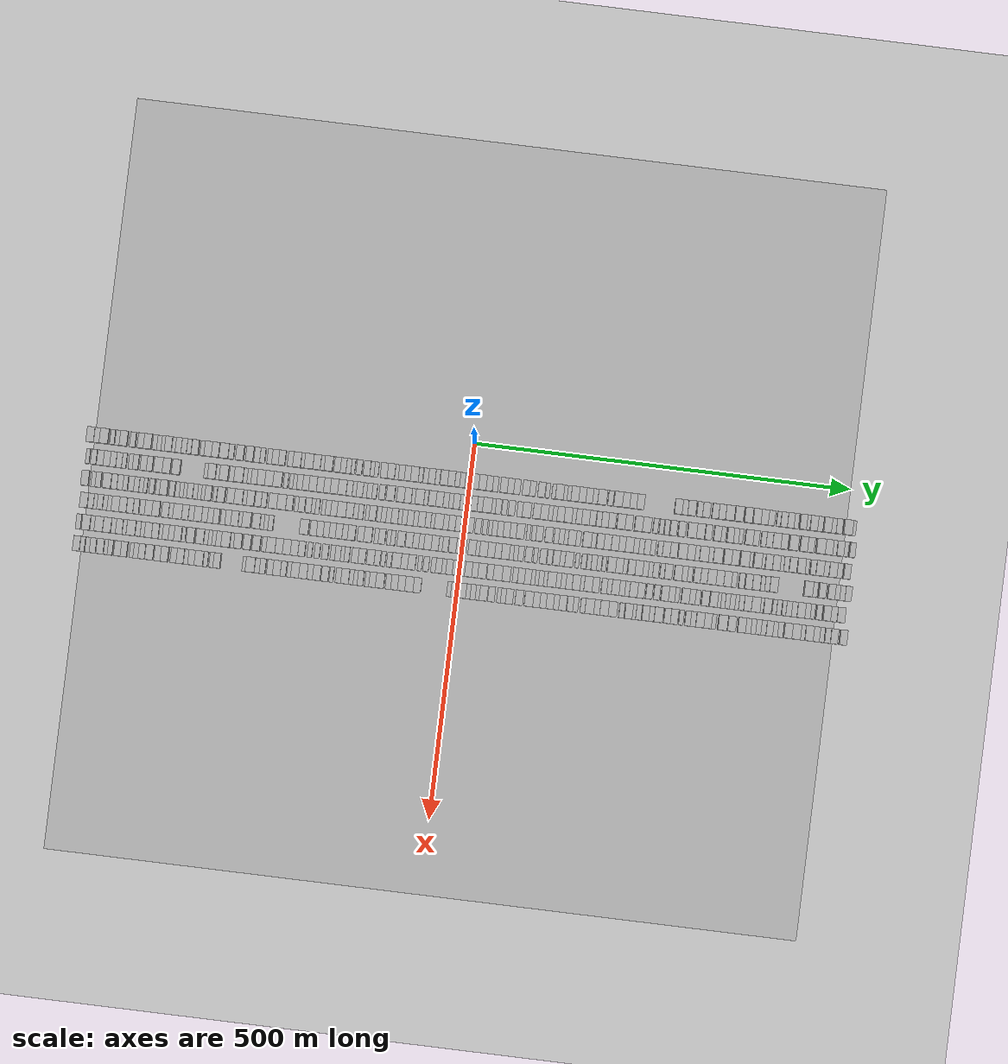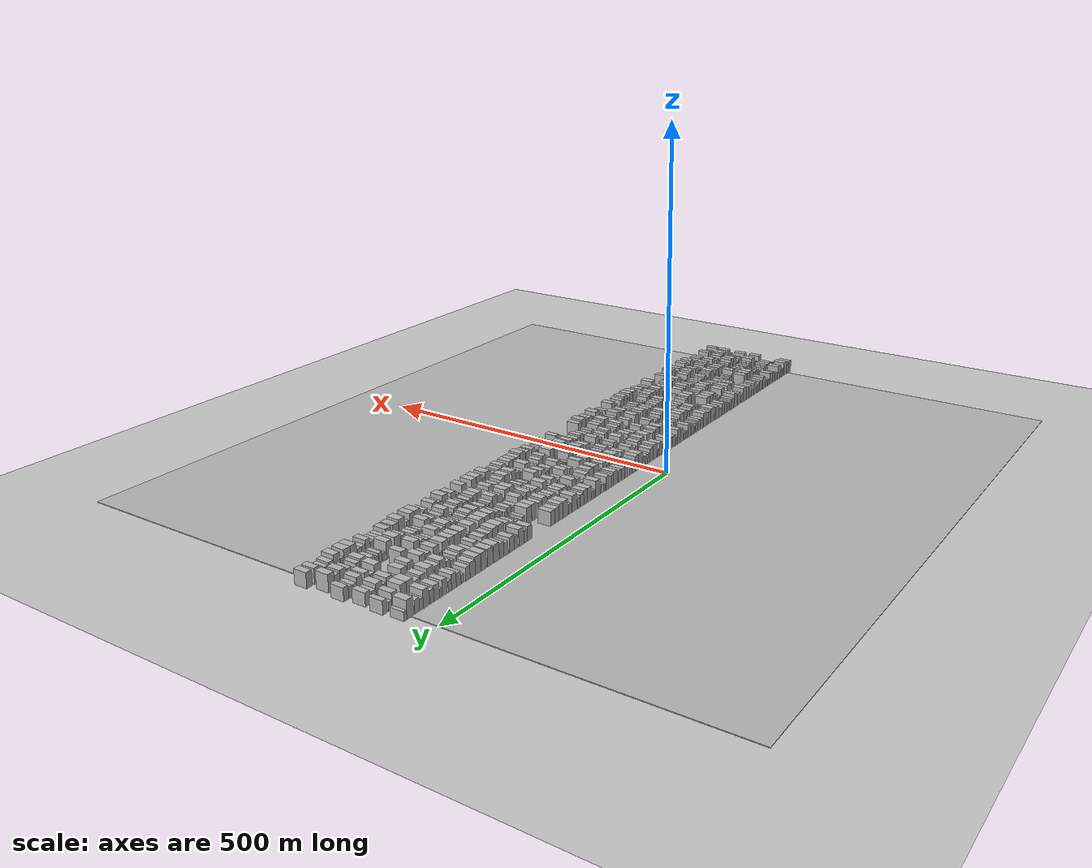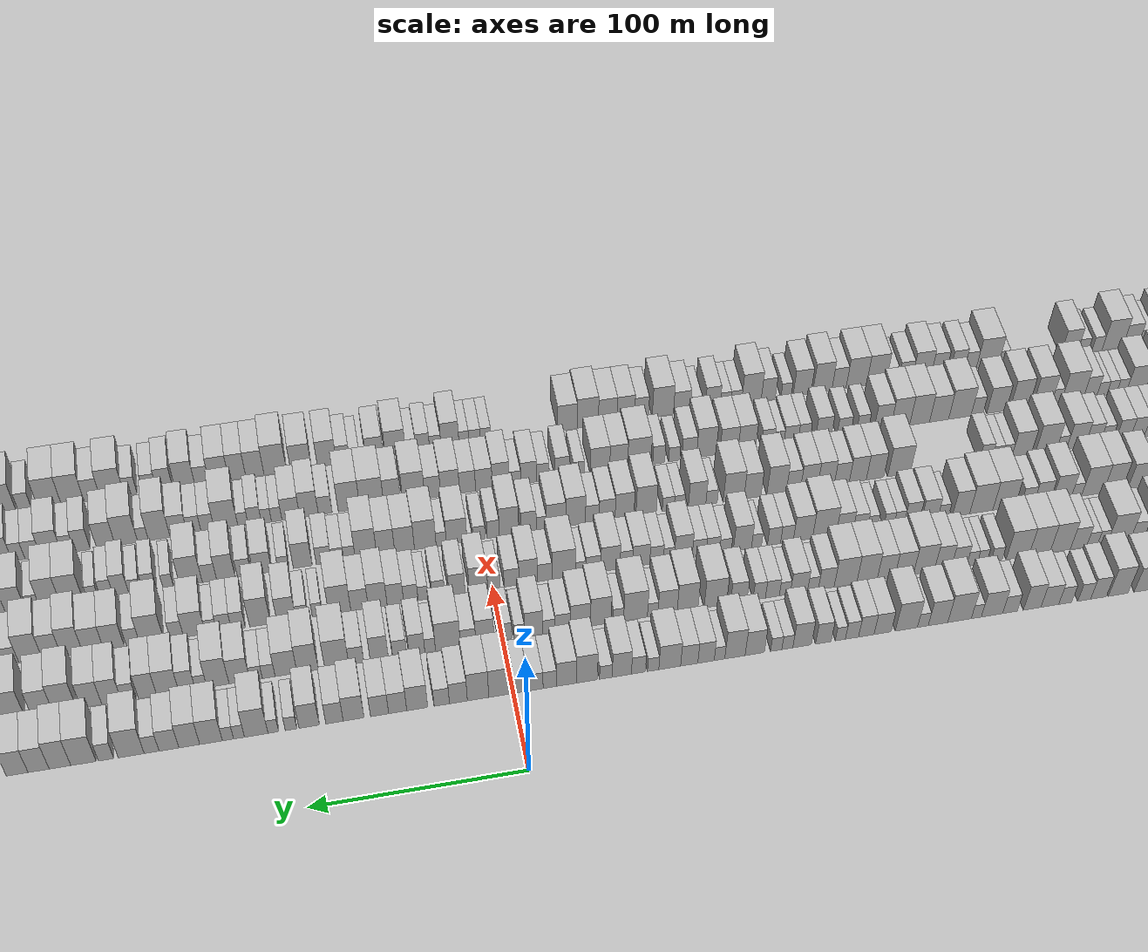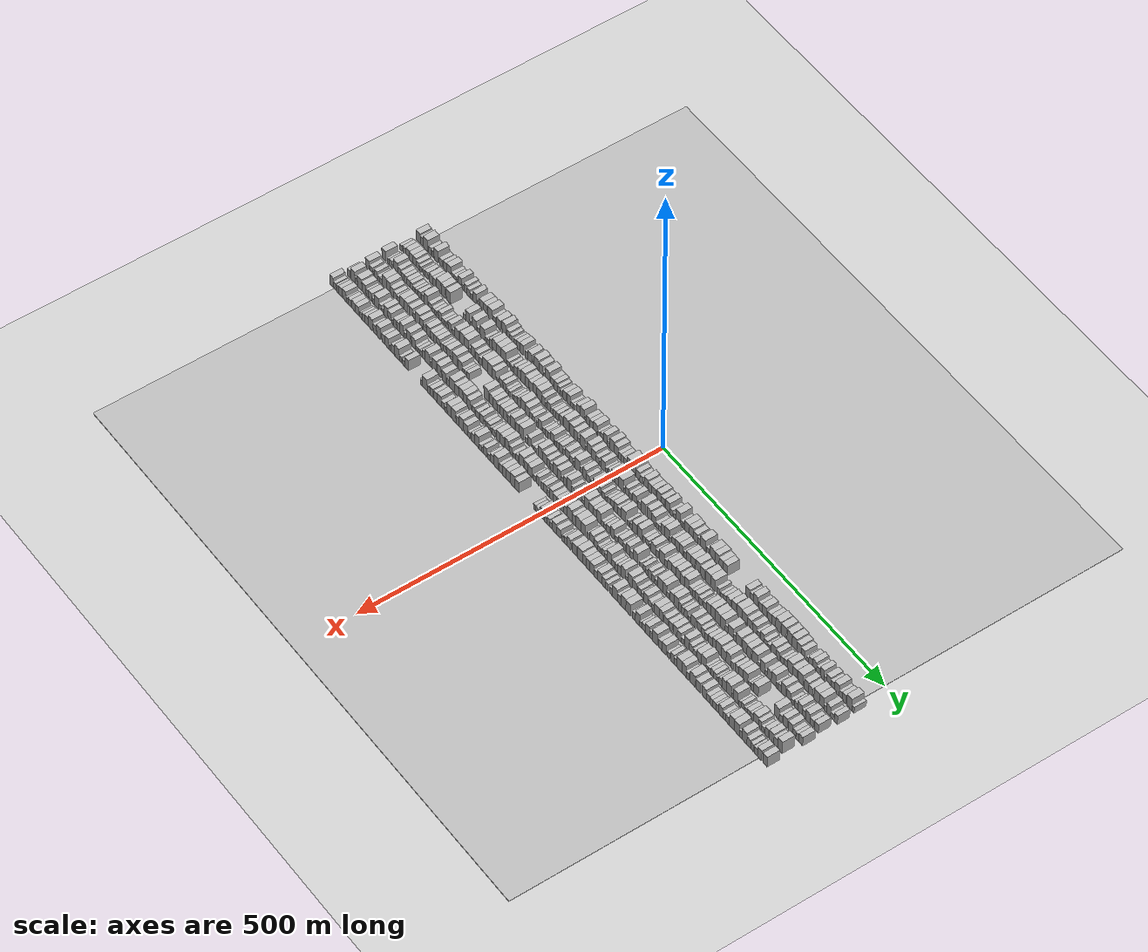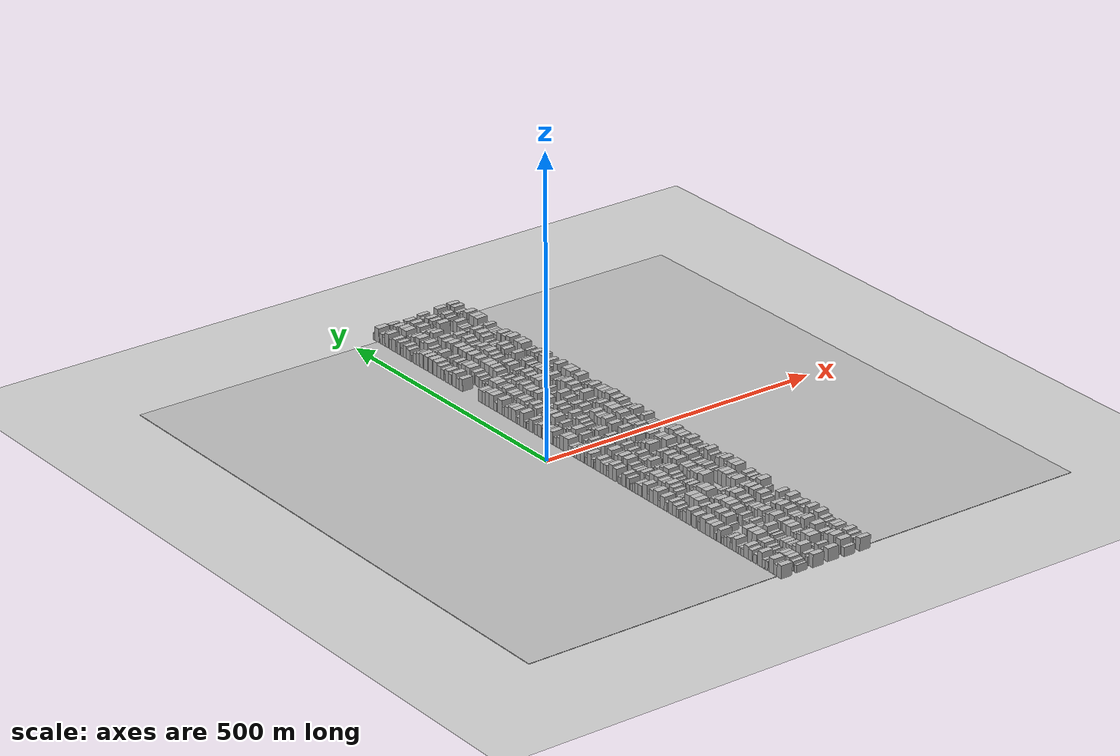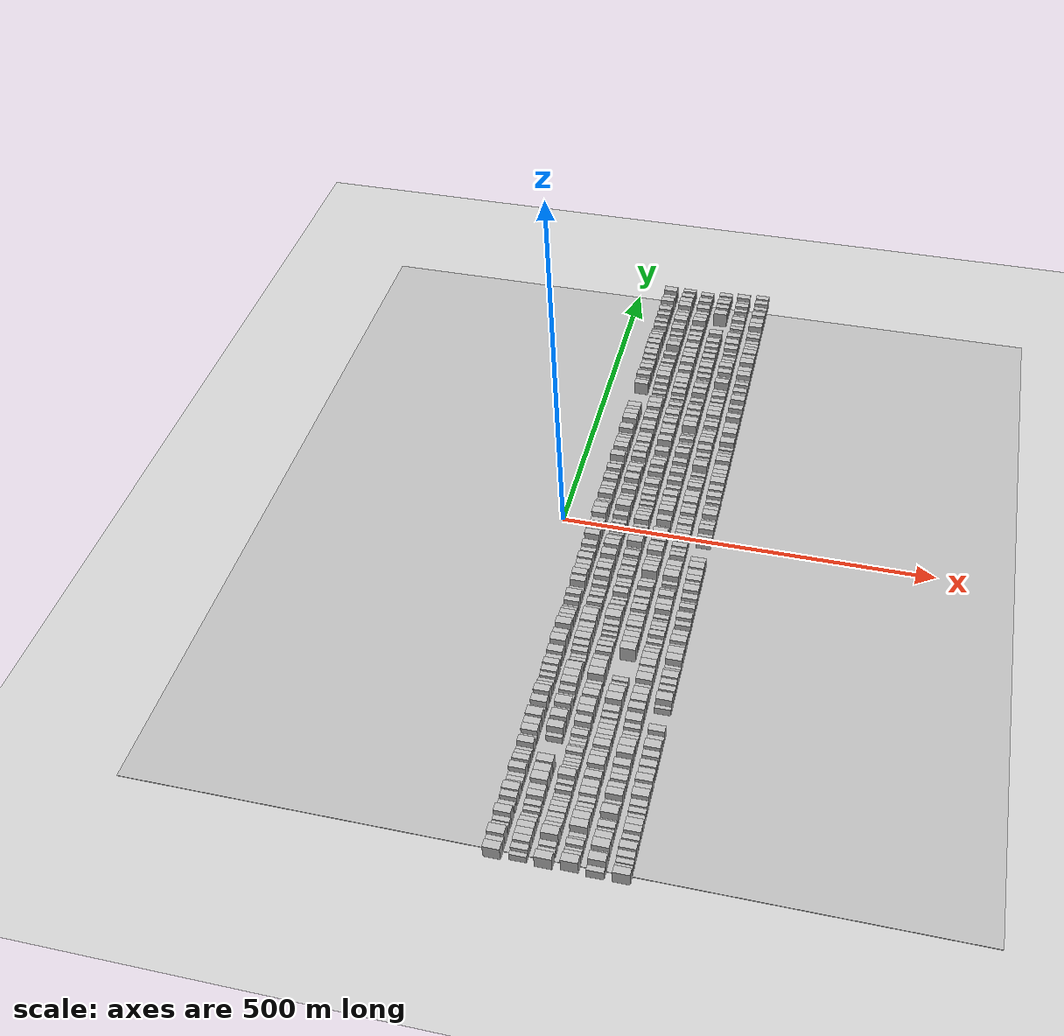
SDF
<?xml version="1.0" encoding="utf-8"?>

<sdf version="1.6">

   <world name="default">

      <gui fullscreen="0">

         <camera name="user_camera">

            <pose>-15 0 4.57585 0 0 0</pose>

            <view_controller>orbit</view_controller>

         </camera>

      </gui>

      <scene>

         <sky>

           <clouds>

             <speed>12</speed>

           </clouds>

         </sky>

         <ambient>0.4 0.4 0.4 1</ambient>

         <background>0.7 0.7 0.7 1</background>

         <shadows>1</shadows>

      </scene>

      <gravity>0 0 -9.8066</gravity>

      <magnetic_field>6e-06 2.3e-05 -4.2e-05</magnetic_field>

      <physics default="0" name="default_physics" type="ode">

         <ode>

            <solver>

               <type>quick</type>

               <iters>10</iters>

               <sor>1.0</sor>

               <use_dynamic_moi_rescaling>0</use_dynamic_moi_rescaling>

            </solver>

            <constraints>

               <cfm>0</cfm>

               <erp>0.2</erp>

               <contact_max_correcting_vel>100</contact_max_correcting_vel>

               <contact_surface_layer>0.001</contact_surface_layer>

            </constraints>

         </ode>

         <max_step_size>0.004</max_step_size>

         <real_time_factor>1</real_time_factor>

         <real_time_update_rate>250</real_time_update_rate>

      </physics>

      <light name="sun" type="directional">

         <cast_shadows>1</cast_shadows>

         <pose>0 0 10 0 0 0</pose>

         <diffuse>0.8 0.8 0.8 1</diffuse>

         <specular>0.2 0.2 0.2 1</specular>

         <attenuation>

            <range>1000</range>

            <constant>0.9</constant>

            <linear>0.01</linear>

            <quadratic>0.001</quadratic>

         </attenuation>

         <direction>-0.5 0.1 -0.9</direction>

      </light>

      <include>

         <name>ground_plane_1</name>

         <uri>model://HANNAS_ground_plane</uri>

         <pose>0 0 0  0 0 0</pose>

      </include>

      <include>

         <name>ground_plane_2</name>

         <uri>model://HANNAS_ground_plane</uri>

         <pose>100 0 0  0 0 0</pose>

      </include>

      <model name="building_1">

         <static>1</static>

         <pose frame="">50.0000 -504.9154 0 0.000000 0.000000 0.000000</pose>

         <link name="link">

            <pose frame="">0 0 10.50 0 0 0</pose>

            <collision name="collision">

               <geometry>

                  <box>

                     <size>20.0000 10.1693 21.0000</size>

                  </box>

               </geometry>

               <max_contacts>10</max_contacts>

               <surface>

                  <contact>

                     <ode/>

                  </contact>

                  <bounce/>

                  <friction>

                     <torsional>

                        <ode/>

                     </torsional>

                     <ode/>

                  </friction>

               </surface>

            </collision>

            <visual name="visual">

               <cast_shadows>0</cast_shadows>

               <geometry>

                  <box>

                     <size>20.0000 10.1693 21.0000</size>

                  </box>

               </geometry>

               <material>

                  <script>

                     <uri>model://HANNAS_wall/materials/scripts</uri>

                     <uri>model://HANNAS_wall/materials/textures</uri>

                     <name>vrc/HANNAS_wall</name>

                  </script>

               </material>

            </visual>

            <self_collide>0</self_collide>

            <enable_wind>0</enable_wind>

            <kinematic>0</kinematic>

         </link>

      </model>

      <model name="building_2">

         <static>1</static>

         <pose frame="">50.0000 -496.0408 0 0.000000 0.000000 0.000000</pose>

         <link name="link">

            <pose frame="">0 0 9.00 0 0 0</pose>

            <collision name="collision">

               <geometry>

                  <box>

                     <size>20.0000 7.5799 18.0000</size>

                  </box>

               </geometry>

               <max_contacts>10</max_contacts>

               <surface>

                  <contact>

                     <ode/>

                  </contact>

                  <bounce/>

                  <friction>

                     <torsional>

                        <ode/>

                     </torsional>

                     <ode/>

                  </friction>

               </surface>

            </collision>

            <visual name="visual">

               <cast_shadows>0</cast_shadows>

               <geometry>

                  <box>

                     <size>20.0000 7.5799 18.0000</size>

                  </box>

               </geometry>

               <material>

                  <script>

                     <uri>model://HANNAS_wall/materials/scripts</uri>

                     <uri>model://HANNAS_wall/materials/textures</uri>

                     <name>vrc/HANNAS_wall</name>

                  </script>

               </material>

            </visual>

            <self_collide>0</self_collide>

            <enable_wind>0</enable_wind>

            <kinematic>0</kinematic>

         </link>

      </model>

      <model name="building_3">

         <static>1</static>

         <pose frame="">50.0000 -486.5869 0 0.000000 0.000000 0.000000</pose>

         <link name="link">

            <pose frame="">0 0 12.00 0 0 0</pose>

            <collision name="collision">

               <geometry>

                  <box>

                     <size>20.0000 11.3279 24.0000</size>

                  </box>

               </geometry>

               <max_contacts>10</max_contacts>

               <surface>

                  <contact>

                     <ode/>

                  </contact>

                  <bounce/>

                  <friction>

                     <torsional>

                        <ode/>

                     </torsional>

                     <ode/>

                  </friction>

               </surface>

            </collision>

            <visual name="visual">

               <cast_shadows>0</cast_shadows>

               <geometry>

                  <box>

                     <size>20.0000 11.3279 24.0000</size>

                  </box>

               </geometry>

               <material>

                  <script>

                     <uri>model://HANNAS_wall/materials/scripts</uri>

                     <uri>model://HANNAS_wall/materials/textures</uri>

                     <name>vrc/HANNAS_wall</name>

                  </script>

               </material>

            </visual>

            <self_collide>0</self_collide>

            <enable_wind>0</enable_wind>

            <kinematic>0</kinematic>

         </link>

      </model>

      <model name="building_4">

         <static>1</static>

         <pose frame="">50.0000 -475.9145 0 0.000000 0.000000 0.000000</pose>

         <link name="link">

            <pose frame="">0 0 7.50 0 0 0</pose>

            <collision name="collision">

               <geometry>

                  <box>

                     <size>20.0000 6.0170 15.0000</size>

                  </box>

               </geometry>

               <max_contacts>10</max_contacts>

               <surface>

                  <contact>

                     <ode/>

                  </contact>

                  <bounce/>

                  <friction>

                     <torsional>

                        <ode/>

                     </torsional>

                     <ode/>

                  </friction>

               </surface>

            </collision>

            <visual name="visual">

               <cast_shadows>0</cast_shadows>

               <geometry>

                  <box>

                     <size>20.0000 6.0170 15.0000</size>

                  </box>

               </geometry>

               <material>

                  <script>

                     <uri>model://HANNAS_wall/materials/scripts</uri>

                     <uri>model://HANNAS_wall/materials/textures</uri>

                     <name>vrc/HANNAS_wall</name>

                  </script>

               </material>

            </visual>

            <self_collide>0</self_collide>

            <enable_wind>0</enable_wind>

            <kinematic>0</kinematic>

         </link>

      </model>

      <model name="building_5">

         <static>1</static>

         <pose frame="">50.0000 -468.7749 0 0.000000 0.000000 0.000000</pose>

         <link name="link">

            <pose frame="">0 0 7.50 0 0 0</pose>

            <collision name="collision">

               <geometry>

                  <box>

                     <size>20.0000 6.2623 15.0000</size>

                  </box>

               </geometry>

               <max_contacts>10</max_contacts>

               <surface>

                  <contact>

                     <ode/>

                  </contact>

                  <bounce/>

                  <friction>

                     <torsional>

                        <ode/>

                     </torsional>

                     <ode/>

                  </friction>

               </surface>

            </collision>

            <visual name="visual">

               <cast_shadows>0</cast_shadows>

               <geometry>

                  <box>

                     <size>20.0000 6.2623 15.0000</size>

                  </box>

               </geometry>

               <material>

                  <script>

                     <uri>model://HANNAS_wall/materials/scripts</uri>

                     <uri>model://HANNAS_wall/materials/textures</uri>

                     <name>vrc/HANNAS_wall</name>

                  </script>

               </material>

            </visual>

            <self_collide>0</self_collide>

            <enable_wind>0</enable_wind>

            <kinematic>0</kinematic>

         </link>

      </model>

      <model name="building_6">

         <static>1</static>

         <pose frame="">50.0000 -460.6426 0 0.000000 0.000000 0.000000</pose>

         <link name="link">

            <pose frame="">0 0 12.00 0 0 0</pose>

            <collision name="collision">

               <geometry>

                  <box>

                     <size>20.0000 10.0022 24.0000</size>

                  </box>

               </geometry>

               <max_contacts>10</max_contacts>

               <surface>

                  <contact>

                     <ode/>

                  </contact>

                  <bounce/>

                  <friction>

                     <torsional>

                        <ode/>

                     </torsional>

                     <ode/>

                  </friction>

               </surface>

            </collision>

            <visual name="visual">

               <cast_shadows>0</cast_shadows>

               <geometry>

                  <box>

                     <size>20.0000 10.0022 24.0000</size>

                  </box>

               </geometry>

               <material>

                  <script>

                     <uri>model://HANNAS_wall/materials/scripts</uri>

                     <uri>model://HANNAS_wall/materials/textures</uri>

                     <name>vrc/HANNAS_wall</name>

                  </script>

               </material>

            </visual>

            <self_collide>0</self_collide>

            <enable_wind>0</enable_wind>

            <kinematic>0</kinematic>

         </link>

      </model>

      <model name="building_7">

         <static>1</static>

         <pose frame="">50.0000 -448.9311 0 0.000000 0.000000 0.000000</pose>

         <link name="link">

            <pose frame="">0 0 7.50 0 0 0</pose>

            <collision name="collision">

               <geometry>

                  <box>

                     <size>20.0000 7.4207 15.0000</size>

                  </box>

               </geometry>

               <max_contacts>10</max_contacts>

               <surface>

                  <contact>

                     <ode/>

                  </contact>

                  <bounce/>

                  <friction>

                     <torsional>

                        <ode/>

                     </torsional>

                     <ode/>

                  </friction>

               </surface>

            </collision>

            <visual name="visual">

               <cast_shadows>0</cast_shadows>

               <geometry>

                  <box>

                     <size>20.0000 7.4207 15.0000</size>

                  </box>

               </geometry>

               <material>

                  <script>

                     <uri>model://HANNAS_wall/materials/scripts</uri>

                     <uri>model://HANNAS_wall/materials/textures</uri>

                     <name>vrc/HANNAS_wall</name>

                  </script>

               </material>

            </visual>

            <self_collide>0</self_collide>

            <enable_wind>0</enable_wind>

            <kinematic>0</kinematic>

         </link>

      </model>

      <model name="building_8">

         <static>1</static>

         <pose frame="">50.0000 -438.0707 0 0.000000 0.000000 0.000000</pose>

         <link name="link">

            <pose frame="">0 0 9.00 0 0 0</pose>

            <collision name="collision">

               <geometry>

                  <box>

                     <size>20.0000 8.3002 18.0000</size>

                  </box>

               </geometry>

               <max_contacts>10</max_contacts>

               <surface>

                  <contact>

                     <ode/>

                  </contact>

                  <bounce/>

                  <friction>

                     <torsional>

                        <ode/>

                     </torsional>

                     <ode/>

                  </friction>

               </surface>

            </collision>

            <visual name="visual">

               <cast_shadows>0</cast_shadows>

               <geometry>

                  <box>

                     <size>20.0000 8.3002 18.0000</size>

                  </box>

               </geometry>

               <material>

                  <script>

                     <uri>model://HANNAS_wall/materials/scripts</uri>

                     <uri>model://HANNAS_wall/materials/textures</uri>

                     <name>vrc/HANNAS_wall</name>

                  </script>

               </material>

            </visual>

            <self_collide>0</self_collide>

            <enable_wind>0</enable_wind>

            <kinematic>0</kinematic>

         </link>

      </model>

      <model name="building_9">

         <static>1</static>

         <pose frame="">50.0000 -428.8075 0 0.000000 0.000000 0.000000</pose>

         <link name="link">

            <pose frame="">0 0 10.50 0 0 0</pose>

            <collision name="collision">

               <geometry>

                  <box>

                     <size>20.0000 10.2262 21.0000</size>

                  </box>

               </geometry>

               <max_contacts>10</max_contacts>

               <surface>

                  <contact>

                     <ode/>

                  </contact>

                  <bounce/>

                  <friction>

                     <torsional>

                        <ode/>

                     </torsional>

                     <ode/>

                  </friction>

               </surface>

            </collision>

            <visual name="visual">

               <cast_shadows>0</cast_shadows>

               <geometry>

                  <box>

                     <size>20.0000 10.2262 21.0000</size>

                  </box>

               </geometry>

               <material>

                  <script>

                     <uri>model://HANNAS_wall/materials/scripts</uri>

                     <uri>model://HANNAS_wall/materials/textures</uri>

                     <name>vrc/HANNAS_wall</name>

                  </script>

               </material>

            </visual>

            <self_collide>0</self_collide>

            <enable_wind>0</enable_wind>

            <kinematic>0</kinematic>

         </link>

      </model>

      <model name="building_10">

         <static>1</static>

         <pose frame="">50.0000 -419.7451 0 0.000000 0.000000 0.000000</pose>

         <link name="link">

            <pose frame="">0 0 6.00 0 0 0</pose>

            <collision name="collision">

               <geometry>

                  <box>

                     <size>20.0000 5.8986 12.0000</size>

                  </box>

               </geometry>

               <max_contacts>10</max_contacts>

               <surface>

                  <contact>

                     <ode/>

                  </contact>

                  <bounce/>

                  <friction>

                     <torsional>

                        <ode/>

                     </torsional>

                     <ode/>

                  </friction>

               </surface>

            </collision>

            <visual name="visual">

               <cast_shadows>0</cast_shadows>

               <geometry>

                  <box>

                     <size>20.0000 5.8986 12.0000</size>

                  </box>

               </geometry>

               <material>

                  <script>

                     <uri>model://HANNAS_wall/materials/scripts</uri>

                     <uri>model://HANNAS_wall/materials/textures</uri>

                     <name>vrc/HANNAS_wall</name>

                  </script>

               </material>

            </visual>

            <self_collide>0</self_collide>

            <enable_wind>0</enable_wind>

            <kinematic>0</kinematic>

         </link>

      </model>

      <model name="building_11">

         <static>1</static>

         <pose frame="">50.0000 -413.8819 0 0.000000 0.000000 0.000000</pose>

         <link name="link">

            <pose frame="">0 0 6.00 0 0 0</pose>

            <collision name="collision">

               <geometry>

                  <box>

                     <size>20.0000 5.8278 12.0000</size>

                  </box>

               </geometry>

               <max_contacts>10</max_contacts>

               <surface>

                  <contact>

                     <ode/>

                  </contact>

                  <bounce/>

                  <friction>

                     <torsional>

                        <ode/>

                     </torsional>

                     <ode/>

                  </friction>

               </surface>

            </collision>

            <visual name="visual">

               <cast_shadows>0</cast_shadows>

               <geometry>

                  <box>

                     <size>20.0000 5.8278 12.0000</size>

                  </box>

               </geometry>

               <material>

                  <script>

                     <uri>model://HANNAS_wall/materials/scripts</uri>

                     <uri>model://HANNAS_wall/materials/textures</uri>

                     <name>vrc/HANNAS_wall</name>

                  </script>

               </material>

            </visual>

            <self_collide>0</self_collide>

            <enable_wind>0</enable_wind>

            <kinematic>0</kinematic>

         </link>

      </model>

      <model name="building_12">

         <static>1</static>

         <pose frame="">50.0000 -408.3892 0 0.000000 0.000000 0.000000</pose>

         <link name="link">

            <pose frame="">0 0 6.00 0 0 0</pose>

            <collision name="collision">

               <geometry>

                  <box>

                     <size>20.0000 5.1576 12.0000</size>

                  </box>

               </geometry>

               <max_contacts>10</max_contacts>

               <surface>

                  <contact>

                     <ode/>

                  </contact>

                  <bounce/>

                  <friction>

                     <torsional>

                        <ode/>

                     </torsional>

                     <ode/>

                  </friction>

               </surface>

            </collision>

            <visual name="visual">

               <cast_shadows>0</cast_shadows>

               <geometry>

                  <box>

                     <size>20.0000 5.1576 12.0000</size>

                  </box>

               </geometry>

               <material>

                  <script>

                     <uri>model://HANNAS_wall/materials/scripts</uri>

                     <uri>model://HANNAS_wall/materials/textures</uri>

                     <name>vrc/HANNAS_wall</name>

                  </script>

               </material>

            </visual>

            <self_collide>0</self_collide>

            <enable_wind>0</enable_wind>

            <kinematic>0</kinematic>

         </link>

      </model>

      <model name="building_13">

         <static>1</static>

         <pose frame="">50.0000 -401.2446 0 0.000000 0.000000 0.000000</pose>

         <link name="link">

            <pose frame="">0 0 10.50 0 0 0</pose>

            <collision name="collision">

               <geometry>

                  <box>

                     <size>20.0000 9.1314 21.0000</size>

                  </box>

               </geometry>

               <max_contacts>10</max_contacts>

               <surface>

                  <contact>

                     <ode/>

                  </contact>

                  <bounce/>

                  <friction>

                     <torsional>

                        <ode/>

                     </torsional>

                     <ode/>

                  </friction>

               </surface>

            </collision>

            <visual name="visual">

               <cast_shadows>0</cast_shadows>

               <geometry>

                  <box>

                     <size>20.0000 9.1314 21.0000</size>

                  </box>

               </geometry>

               <material>

                  <script>

                     <uri>model://HANNAS_wall/materials/scripts</uri>

                     <uri>model://HANNAS_wall/materials/textures</uri>

                     <name>vrc/HANNAS_wall</name>

                  </script>

               </material>

            </visual>

            <self_collide>0</self_collide>

            <enable_wind>0</enable_wind>

            <kinematic>0</kinematic>

         </link>

      </model>

      <model name="building_14">

         <static>1</static>

         <pose frame="">50.0000 -394.2057 0 0.000000 0.000000 0.000000</pose>

         <link name="link">

            <pose frame="">0 0 6.00 0 0 0</pose>

            <collision name="collision">

               <geometry>

                  <box>

                     <size>20.0000 4.9464 12.0000</size>

                  </box>

               </geometry>

               <max_contacts>10</max_contacts>

               <surface>

                  <contact>

                     <ode/>

                  </contact>

                  <bounce/>

                  <friction>

                     <torsional>

                        <ode/>

                     </torsional>

                     <ode/>

                  </friction>

               </surface>

            </collision>

            <visual name="visual">

               <cast_shadows>0</cast_shadows>

               <geometry>

                  <box>

                     <size>20.0000 4.9464 12.0000</size>

                  </box>

               </geometry>

               <material>

                  <script>

                     <uri>model://HANNAS_wall/materials/scripts</uri>

                     <uri>model://HANNAS_wall/materials/textures</uri>

                     <name>vrc/HANNAS_wall</name>

                  </script>

               </material>

            </visual>

            <self_collide>0</self_collide>

            <enable_wind>0</enable_wind>

            <kinematic>0</kinematic>

         </link>

      </model>

      <model name="building_15">

         <static>1</static>

         <pose frame="">50.0000 -387.8550 0 0.000000 0.000000 0.000000</pose>

         <link name="link">

            <pose frame="">0 0 9.00 0 0 0</pose>

            <collision name="collision">

               <geometry>

                  <box>

                     <size>20.0000 7.7550 18.0000</size>

                  </box>

               </geometry>

               <max_contacts>10</max_contacts>

               <surface>

                  <contact>

                     <ode/>

                  </contact>

                  <bounce/>

                  <friction>

                     <torsional>

                        <ode/>

                     </torsional>

                     <ode/>

                  </friction>

               </surface>

            </collision>

            <visual name="visual">

               <cast_shadows>0</cast_shadows>

               <geometry>

                  <box>

                     <size>20.0000 7.7550 18.0000</size>

                  </box>

               </geometry>

               <material>

                  <script>

                     <uri>model://HANNAS_wall/materials/scripts</uri>

                     <uri>model://HANNAS_wall/materials/textures</uri>

                     <name>vrc/HANNAS_wall</name>

                  </script>

               </material>

            </visual>

            <self_collide>0</self_collide>

            <enable_wind>0</enable_wind>

            <kinematic>0</kinematic>

         </link>

      </model>

      <model name="building_16">

         <static>1</static>

         <pose frame="">50.0000 -380.4570 0 0.000000 0.000000 0.000000</pose>

         <link name="link">

            <pose frame="">0 0 7.50 0 0 0</pose>

            <collision name="collision">

               <geometry>

                  <box>

                     <size>20.0000 7.0410 15.0000</size>

                  </box>

               </geometry>

               <max_contacts>10</max_contacts>

               <surface>

                  <contact>

                     <ode/>

                  </contact>

                  <bounce/>

                  <friction>

                     <torsional>

                        <ode/>

                     </torsional>

                     <ode/>

                  </friction>

               </surface>

            </collision>

            <visual name="visual">

               <cast_shadows>0</cast_shadows>

               <geometry>

                  <box>

                     <size>20.0000 7.0410 15.0000</size>

                  </box>

               </geometry>

               <material>

                  <script>

                     <uri>model://HANNAS_wall/materials/scripts</uri>

                     <uri>model://HANNAS_wall/materials/textures</uri>

                     <name>vrc/HANNAS_wall</name>

                  </script>

               </material>

            </visual>

            <self_collide>0</self_collide>

            <enable_wind>0</enable_wind>

            <kinematic>0</kinematic>

         </link>

      </model>

      <model name="building_17">

         <static>1</static>

         <pose frame="">50.0000 -374.0236 0 0.000000 0.000000 0.000000</pose>

         <link name="link">

            <pose frame="">0 0 6.00 0 0 0</pose>

            <collision name="collision">

               <geometry>

                  <box>

                     <size>20.0000 5.8259 12.0000</size>

                  </box>

               </geometry>

               <max_contacts>10</max_contacts>

               <surface>

                  <contact>

                     <ode/>

                  </contact>

                  <bounce/>

                  <friction>

                     <torsional>

                        <ode/>

                     </torsional>

                     <ode/>

                  </friction>

               </surface>

            </collision>

            <visual name="visual">

               <cast_shadows>0</cast_shadows>

               <geometry>

                  <box>

                     <size>20.0000 5.8259 12.0000</size>

                  </box>

               </geometry>

               <material>

                  <script>

                     <uri>model://HANNAS_wall/materials/scripts</uri>

                     <uri>model://HANNAS_wall/materials/textures</uri>

                     <name>vrc/HANNAS_wall</name>

                  </script>

               </material>

            </visual>

            <self_collide>0</self_collide>

            <enable_wind>0</enable_wind>

            <kinematic>0</kinematic>

         </link>

      </model>

      <model name="building_18">

         <static>1</static>

         <pose frame="">50.0000 -365.6434 0 0.000000 0.000000 0.000000</pose>

         <link name="link">

            <pose frame="">0 0 10.50 0 0 0</pose>

            <collision name="collision">

               <geometry>

                  <box>

                     <size>20.0000 8.9345 21.0000</size>

                  </box>

               </geometry>

               <max_contacts>10</max_contacts>

               <surface>

                  <contact>

                     <ode/>

                  </contact>

                  <bounce/>

                  <friction>

                     <torsional>

                        <ode/>

                     </torsional>

                     <ode/>

                  </friction>

               </surface>

            </collision>

            <visual name="visual">

               <cast_shadows>0</cast_shadows>

               <geometry>

                  <box>

                     <size>20.0000 8.9345 21.0000</size>

                  </box>

               </geometry>

               <material>

                  <script>

                     <uri>model://HANNAS_wall/materials/scripts</uri>

                     <uri>model://HANNAS_wall/materials/textures</uri>

                     <name>vrc/HANNAS_wall</name>

                  </script>

               </material>

            </visual>

            <self_collide>0</self_collide>

            <enable_wind>0</enable_wind>

            <kinematic>0</kinematic>

         </link>

      </model>

      <model name="building_19">

         <static>1</static>

         <pose frame="">50.0000 -356.2372 0 0.000000 0.000000 0.000000</pose>

         <link name="link">

            <pose frame="">0 0 6.00 0 0 0</pose>

            <collision name="collision">

               <geometry>

                  <box>

                     <size>20.0000 5.8778 12.0000</size>

                  </box>

               </geometry>

               <max_contacts>10</max_contacts>

               <surface>

                  <contact>

                     <ode/>

                  </contact>

                  <bounce/>

                  <friction>

                     <torsional>

                        <ode/>

                     </torsional>

                     <ode/>

                  </friction>

               </surface>

            </collision>

            <visual name="visual">

               <cast_shadows>0</cast_shadows>

               <geometry>

                  <box>

                     <size>20.0000 5.8778 12.0000</size>

                  </box>

               </geometry>

               <material>

                  <script>

                     <uri>model://HANNAS_wall/materials/scripts</uri>

                     <uri>model://HANNAS_wall/materials/textures</uri>

                     <name>vrc/HANNAS_wall</name>

                  </script>

               </material>

            </visual>

            <self_collide>0</self_collide>

            <enable_wind>0</enable_wind>

            <kinematic>0</kinematic>

         </link>

      </model>

      <model name="building_20">

         <static>1</static>

         <pose frame="">50.0000 -348.4017 0 0.000000 0.000000 0.000000</pose>

         <link name="link">

            <pose frame="">0 0 10.50 0 0 0</pose>

            <collision name="collision">

               <geometry>

                  <box>

                     <size>20.0000 9.7932 21.0000</size>

                  </box>

               </geometry>

               <max_contacts>10</max_contacts>

               <surface>

                  <contact>

                     <ode/>

                  </contact>

                  <bounce/>

                  <friction>

                     <torsional>

                        <ode/>

                     </torsional>

                     <ode/>

                  </friction>

               </surface>

            </collision>

            <visual name="visual">

               <cast_shadows>0</cast_shadows>

               <geometry>

                  <box>

                     <size>20.0000 9.7932 21.0000</size>

                  </box>

               </geometry>

               <material>

                  <script>

                     <uri>model://HANNAS_wall/materials/scripts</uri>

                     <uri>model://HANNAS_wall/materials/textures</uri>

                     <name>vrc/HANNAS_wall</name>

                  </script>

               </material>

            </visual>

            <self_collide>0</self_collide>

            <enable_wind>0</enable_wind>

            <kinematic>0</kinematic>

         </link>

      </model>

      <model name="building_21">

         <static>1</static>

         <pose frame="">50.0000 -338.7767 0 0.000000 0.000000 0.000000</pose>

         <link name="link">

            <pose frame="">0 0 10.50 0 0 0</pose>

            <collision name="collision">

               <geometry>

                  <box>

                     <size>20.0000 9.4569 21.0000</size>

                  </box>

               </geometry>

               <max_contacts>10</max_contacts>

               <surface>

                  <contact>

                     <ode/>

                  </contact>

                  <bounce/>

                  <friction>

                     <torsional>

                        <ode/>

                     </torsional>

                     <ode/>

                  </friction>

               </surface>

            </collision>

            <visual name="visual">

               <cast_shadows>0</cast_shadows>

               <geometry>

                  <box>

                     <size>20.0000 9.4569 21.0000</size>

                  </box>

               </geometry>

               <material>

                  <script>

                     <uri>model://HANNAS_wall/materials/scripts</uri>

                     <uri>model://HANNAS_wall/materials/textures</uri>

                     <name>vrc/HANNAS_wall</name>

                  </script>

               </material>

            </visual>

            <self_collide>0</self_collide>

            <enable_wind>0</enable_wind>

            <kinematic>0</kinematic>

         </link>

      </model>

      <model name="building_22">

         <static>1</static>

         <pose frame="">50.0000 -327.1377 0 0.000000 0.000000 0.000000</pose>

         <link name="link">

            <pose frame="">0 0 12.00 0 0 0</pose>

            <collision name="collision">

               <geometry>

                  <box>

                     <size>20.0000 11.8209 24.0000</size>

                  </box>

               </geometry>

               <max_contacts>10</max_contacts>

               <surface>

                  <contact>

                     <ode/>

                  </contact>

                  <bounce/>

                  <friction>

                     <torsional>

                        <ode/>

                     </torsional>

                     <ode/>

                  </friction>

               </surface>

            </collision>

            <visual name="visual">

               <cast_shadows>0</cast_shadows>

               <geometry>

                  <box>

                     <size>20.0000 11.8209 24.0000</size>

                  </box>

               </geometry>

               <material>

                  <script>

                     <uri>model://HANNAS_wall/materials/scripts</uri>

                     <uri>model://HANNAS_wall/materials/textures</uri>

                     <name>vrc/HANNAS_wall</name>

                  </script>

               </material>

            </visual>

            <self_collide>0</self_collide>

            <enable_wind>0</enable_wind>

            <kinematic>0</kinematic>

         </link>

      </model>

      <model name="building_23">

         <static>1</static>

         <pose frame="">50.0000 -317.7968 0 0.000000 0.000000 0.000000</pose>

         <link name="link">

            <pose frame="">0 0 7.50 0 0 0</pose>

            <collision name="collision">

               <geometry>

                  <box>

                     <size>20.0000 6.8609 15.0000</size>

                  </box>

               </geometry>

               <max_contacts>10</max_contacts>

               <surface>

                  <contact>

                     <ode/>

                  </contact>

                  <bounce/>

                  <friction>

                     <torsional>

                        <ode/>

                     </torsional>

                     <ode/>

                  </friction>

               </surface>

            </collision>

            <visual name="visual">

               <cast_shadows>0</cast_shadows>

               <geometry>

                  <box>

                     <size>20.0000 6.8609 15.0000</size>

                  </box>

               </geometry>

               <material>

                  <script>

                     <uri>model://HANNAS_wall/materials/scripts</uri>

                     <uri>model://HANNAS_wall/materials/textures</uri>

                     <name>vrc/HANNAS_wall</name>

                  </script>

               </material>

            </visual>

            <self_collide>0</self_collide>

            <enable_wind>0</enable_wind>

            <kinematic>0</kinematic>

         </link>

      </model>

      <model name="building_24">

         <static>1</static>

         <pose frame="">50.0000 -306.2270 0 0.000000 0.000000 0.000000</pose>

         <link name="link">

            <pose frame="">0 0 10.50 0 0 0</pose>

            <collision name="collision">

               <geometry>

                  <box>

                     <size>20.0000 10.2788 21.0000</size>

                  </box>

               </geometry>

               <max_contacts>10</max_contacts>

               <surface>

                  <contact>

                     <ode/>

                  </contact>

                  <bounce/>

                  <friction>

                     <torsional>

                        <ode/>

                     </torsional>

                     <ode/>

                  </friction>

               </surface>

            </collision>

            <visual name="visual">

               <cast_shadows>0</cast_shadows>

               <geometry>

                  <box>

                     <size>20.0000 10.2788 21.0000</size>

                  </box>

               </geometry>

               <material>

                  <script>

                     <uri>model://HANNAS_wall/materials/scripts</uri>

                     <uri>model://HANNAS_wall/materials/textures</uri>

                     <name>vrc/HANNAS_wall</name>

                  </script>

               </material>

            </visual>

            <self_collide>0</self_collide>

            <enable_wind>0</enable_wind>

            <kinematic>0</kinematic>

         </link>

      </model>

      <model name="building_25">

         <static>1</static>

         <pose frame="">50.0000 -293.1392 0 0.000000 0.000000 0.000000</pose>

         <link name="link">

            <pose frame="">0 0 12.00 0 0 0</pose>

            <collision name="collision">

               <geometry>

                  <box>

                     <size>20.0000 9.8967 24.0000</size>

                  </box>

               </geometry>

               <max_contacts>10</max_contacts>

               <surface>

                  <contact>

                     <ode/>

                  </contact>

                  <bounce/>

                  <friction>

                     <torsional>

                        <ode/>

                     </torsional>

                     <ode/>

                  </friction>

               </surface>

            </collision>

            <visual name="visual">

               <cast_shadows>0</cast_shadows>

               <geometry>

                  <box>

                     <size>20.0000 9.8967 24.0000</size>

                  </box>

               </geometry>

               <material>

                  <script>

                     <uri>model://HANNAS_wall/materials/scripts</uri>

                     <uri>model://HANNAS_wall/materials/textures</uri>

                     <name>vrc/HANNAS_wall</name>

                  </script>

               </material>

            </visual>

            <self_collide>0</self_collide>

            <enable_wind>0</enable_wind>

            <kinematic>0</kinematic>

         </link>

      </model>

      <model name="building_26">

         <static>1</static>

         <pose frame="">50.0000 -283.2731 0 0.000000 0.000000 0.000000</pose>

         <link name="link">

            <pose frame="">0 0 9.00 0 0 0</pose>

            <collision name="collision">

               <geometry>

                  <box>

                     <size>20.0000 7.8355 18.0000</size>

                  </box>

               </geometry>

               <max_contacts>10</max_contacts>

               <surface>

                  <contact>

                     <ode/>

                  </contact>

                  <bounce/>

                  <friction>

                     <torsional>

                        <ode/>

                     </torsional>

                     <ode/>

                  </friction>

               </surface>

            </collision>

            <visual name="visual">

               <cast_shadows>0</cast_shadows>

               <geometry>

                  <box>

                     <size>20.0000 7.8355 18.0000</size>

                  </box>

               </geometry>

               <material>

                  <script>

                     <uri>model://HANNAS_wall/materials/scripts</uri>

                     <uri>model://HANNAS_wall/materials/textures</uri>

                     <name>vrc/HANNAS_wall</name>

                  </script>

               </material>

            </visual>

            <self_collide>0</self_collide>

            <enable_wind>0</enable_wind>

            <kinematic>0</kinematic>

         </link>

      </model>

      <model name="building_27">

         <static>1</static>

         <pose frame="">50.0000 -276.1281 0 0.000000 0.000000 0.000000</pose>

         <link name="link">

            <pose frame="">0 0 7.50 0 0 0</pose>

            <collision name="collision">

               <geometry>

                  <box>

                     <size>20.0000 6.4543 15.0000</size>

                  </box>

               </geometry>

               <max_contacts>10</max_contacts>

               <surface>

                  <contact>

                     <ode/>

                  </contact>

                  <bounce/>

                  <friction>

                     <torsional>

                        <ode/>

                     </torsional>

                     <ode/>

                  </friction>

               </surface>

            </collision>

            <visual name="visual">

               <cast_shadows>0</cast_shadows>

               <geometry>

                  <box>

                     <size>20.0000 6.4543 15.0000</size>

                  </box>

               </geometry>

               <material>

                  <script>

                     <uri>model://HANNAS_wall/materials/scripts</uri>

                     <uri>model://HANNAS_wall/materials/textures</uri>

                     <name>vrc/HANNAS_wall</name>

                  </script>

               </material>

            </visual>

            <self_collide>0</self_collide>

            <enable_wind>0</enable_wind>

            <kinematic>0</kinematic>

         </link>

      </model>

      <model name="building_28">

         <static>1</static>

         <pose frame="">50.0000 -266.6582 0 0.000000 0.000000 0.000000</pose>

         <link name="link">

            <pose frame="">0 0 7.50 0 0 0</pose>

            <collision name="collision">

               <geometry>

                  <box>

                     <size>20.0000 6.4856 15.0000</size>

                  </box>

               </geometry>

               <max_contacts>10</max_contacts>

               <surface>

                  <contact>

                     <ode/>

                  </contact>

                  <bounce/>

                  <friction>

                     <torsional>

                        <ode/>

                     </torsional>

                     <ode/>

                  </friction>

               </surface>

            </collision>

            <visual name="visual">

               <cast_shadows>0</cast_shadows>

               <geometry>

                  <box>

                     <size>20.0000 6.4856 15.0000</size>

                  </box>

               </geometry>

               <material>

                  <script>

                     <uri>model://HANNAS_wall/materials/scripts</uri>

                     <uri>model://HANNAS_wall/materials/textures</uri>

                     <name>vrc/HANNAS_wall</name>

                  </script>

               </material>

            </visual>

            <self_collide>0</self_collide>

            <enable_wind>0</enable_wind>

            <kinematic>0</kinematic>

         </link>

      </model>

      <model name="building_29">

         <static>1</static>

         <pose frame="">50.0000 -258.9765 0 0.000000 0.000000 0.000000</pose>

         <link name="link">

            <pose frame="">0 0 9.00 0 0 0</pose>

            <collision name="collision">

               <geometry>

                  <box>

                     <size>20.0000 8.8778 18.0000</size>

                  </box>

               </geometry>

               <max_contacts>10</max_contacts>

               <surface>

                  <contact>

                     <ode/>

                  </contact>

                  <bounce/>

                  <friction>

                     <torsional>

                        <ode/>

                     </torsional>

                     <ode/>

                  </friction>

               </surface>

            </collision>

            <visual name="visual">

               <cast_shadows>0</cast_shadows>

               <geometry>

                  <box>

                     <size>20.0000 8.8778 18.0000</size>

                  </box>

               </geometry>

               <material>

                  <script>

                     <uri>model://HANNAS_wall/materials/scripts</uri>

                     <uri>model://HANNAS_wall/materials/textures</uri>

                     <name>vrc/HANNAS_wall</name>

                  </script>

               </material>

            </visual>

            <self_collide>0</self_collide>

            <enable_wind>0</enable_wind>

            <kinematic>0</kinematic>

         </link>

      </model>

      <model name="building_30">

         <static>1</static>

         <pose frame="">50.0000 -250.1749 0 0.000000 0.000000 0.000000</pose>

         <link name="link">

            <pose frame="">0 0 10.50 0 0 0</pose>

            <collision name="collision">

               <geometry>

                  <box>

                     <size>20.0000 8.7254 21.0000</size>

                  </box>

               </geometry>

               <max_contacts>10</max_contacts>

               <surface>

                  <contact>

                     <ode/>

                  </contact>

                  <bounce/>

                  <friction>

                     <torsional>

                        <ode/>

                     </torsional>

                     <ode/>

                  </friction>

               </surface>

            </collision>

            <visual name="visual">

               <cast_shadows>0</cast_shadows>

               <geometry>

                  <box>

                     <size>20.0000 8.7254 21.0000</size>

                  </box>

               </geometry>

               <material>

                  <script>

                     <uri>model://HANNAS_wall/materials/scripts</uri>

                     <uri>model://HANNAS_wall/materials/textures</uri>

                     <name>vrc/HANNAS_wall</name>

                  </script>

               </material>

            </visual>

            <self_collide>0</self_collide>

            <enable_wind>0</enable_wind>

            <kinematic>0</kinematic>

         </link>

      </model>

      <model name="building_31">

         <static>1</static>

         <pose frame="">50.0000 -239.1682 0 0.000000 0.000000 0.000000</pose>

         <link name="link">

            <pose frame="">0 0 7.50 0 0 0</pose>

            <collision name="collision">

               <geometry>

                  <box>

                     <size>20.0000 7.2879 15.0000</size>

                  </box>

               </geometry>

               <max_contacts>10</max_contacts>

               <surface>

                  <contact>

                     <ode/>

                  </contact>

                  <bounce/>

                  <friction>

                     <torsional>

                        <ode/>

                     </torsional>

                     <ode/>

                  </friction>

               </surface>

            </collision>

            <visual name="visual">

               <cast_shadows>0</cast_shadows>

               <geometry>

                  <box>

                     <size>20.0000 7.2879 15.0000</size>

                  </box>

               </geometry>

               <material>

                  <script>

                     <uri>model://HANNAS_wall/materials/scripts</uri>

                     <uri>model://HANNAS_wall/materials/textures</uri>

                     <name>vrc/HANNAS_wall</name>

                  </script>

               </material>

            </visual>

            <self_collide>0</self_collide>

            <enable_wind>0</enable_wind>

            <kinematic>0</kinematic>

         </link>

      </model>

      <model name="building_32">

         <static>1</static>

         <pose frame="">50.0000 -230.2769 0 0.000000 0.000000 0.000000</pose>

         <link name="link">

            <pose frame="">0 0 10.50 0 0 0</pose>

            <collision name="collision">

               <geometry>

                  <box>

                     <size>20.0000 10.4948 21.0000</size>

                  </box>

               </geometry>

               <max_contacts>10</max_contacts>

               <surface>

                  <contact>

                     <ode/>

                  </contact>

                  <bounce/>

                  <friction>

                     <torsional>

                        <ode/>

                     </torsional>

                     <ode/>

                  </friction>

               </surface>

            </collision>

            <visual name="visual">

               <cast_shadows>0</cast_shadows>

               <geometry>

                  <box>

                     <size>20.0000 10.4948 21.0000</size>

                  </box>

               </geometry>

               <material>

                  <script>

                     <uri>model://HANNAS_wall/materials/scripts</uri>

                     <uri>model://HANNAS_wall/materials/textures</uri>

                     <name>vrc/HANNAS_wall</name>

                  </script>

               </material>

            </visual>

            <self_collide>0</self_collide>

            <enable_wind>0</enable_wind>

            <kinematic>0</kinematic>

         </link>

      </model>

      <model name="building_33">

         <static>1</static>

         <pose frame="">50.0000 -222.5440 0 0.000000 0.000000 0.000000</pose>

         <link name="link">

            <pose frame="">0 0 6.00 0 0 0</pose>

            <collision name="collision">

               <geometry>

                  <box>

                     <size>20.0000 4.9711 12.0000</size>

                  </box>

               </geometry>

               <max_contacts>10</max_contacts>

               <surface>

                  <contact>

                     <ode/>

                  </contact>

                  <bounce/>

                  <friction>

                     <torsional>

                        <ode/>

                     </torsional>

                     <ode/>

                  </friction>

               </surface>

            </collision>

            <visual name="visual">

               <cast_shadows>0</cast_shadows>

               <geometry>

                  <box>

                     <size>20.0000 4.9711 12.0000</size>

                  </box>

               </geometry>

               <material>

                  <script>

                     <uri>model://HANNAS_wall/materials/scripts</uri>

                     <uri>model://HANNAS_wall/materials/textures</uri>

                     <name>vrc/HANNAS_wall</name>

                  </script>

               </material>

            </visual>

            <self_collide>0</self_collide>

            <enable_wind>0</enable_wind>

            <kinematic>0</kinematic>

         </link>

      </model>

      <model name="building_34">

         <static>1</static>

         <pose frame="">50.0000 -214.2739 0 0.000000 0.000000 0.000000</pose>

         <link name="link">

            <pose frame="">0 0 12.00 0 0 0</pose>

            <collision name="collision">

               <geometry>

                  <box>

                     <size>20.0000 11.5692 24.0000</size>

                  </box>

               </geometry>

               <max_contacts>10</max_contacts>

               <surface>

                  <contact>

                     <ode/>

                  </contact>

                  <bounce/>

                  <friction>

                     <torsional>

                        <ode/>

                     </torsional>

                     <ode/>

                  </friction>

               </surface>

            </collision>

            <visual name="visual">

               <cast_shadows>0</cast_shadows>

               <geometry>

                  <box>

                     <size>20.0000 11.5692 24.0000</size>

                  </box>

               </geometry>

               <material>

                  <script>

                     <uri>model://HANNAS_wall/materials/scripts</uri>

                     <uri>model://HANNAS_wall/materials/textures</uri>

                     <name>vrc/HANNAS_wall</name>

                  </script>

               </material>

            </visual>

            <self_collide>0</self_collide>

            <enable_wind>0</enable_wind>

            <kinematic>0</kinematic>

         </link>

      </model>

      <model name="building_35">

         <static>1</static>

         <pose frame="">50.0000 -203.6890 0 0.000000 0.000000 0.000000</pose>

         <link name="link">

            <pose frame="">0 0 10.50 0 0 0</pose>

            <collision name="collision">

               <geometry>

                  <box>

                     <size>20.0000 9.6006 21.0000</size>

                  </box>

               </geometry>

               <max_contacts>10</max_contacts>

               <surface>

                  <contact>

                     <ode/>

                  </contact>

                  <bounce/>

                  <friction>

                     <torsional>

                        <ode/>

                     </torsional>

                     <ode/>

                  </friction>

               </surface>

            </collision>

            <visual name="visual">

               <cast_shadows>0</cast_shadows>

               <geometry>

                  <box>

                     <size>20.0000 9.6006 21.0000</size>

                  </box>

               </geometry>

               <material>

                  <script>

                     <uri>model://HANNAS_wall/materials/scripts</uri>

                     <uri>model://HANNAS_wall/materials/textures</uri>

                     <name>vrc/HANNAS_wall</name>

                  </script>

               </material>

            </visual>

            <self_collide>0</self_collide>

            <enable_wind>0</enable_wind>

            <kinematic>0</kinematic>

         </link>

      </model>

      <model name="building_36">

         <static>1</static>

         <pose frame="">50.0000 -196.2455 0 0.000000 0.000000 0.000000</pose>

         <link name="link">

            <pose frame="">0 0 6.00 0 0 0</pose>

            <collision name="collision">

               <geometry>

                  <box>

                     <size>20.0000 5.2864 12.0000</size>

                  </box>

               </geometry>

               <max_contacts>10</max_contacts>

               <surface>

                  <contact>

                     <ode/>

                  </contact>

                  <bounce/>

                  <friction>

                     <torsional>

                        <ode/>

                     </torsional>

                     <ode/>

                  </friction>

               </surface>

            </collision>

            <visual name="visual">

               <cast_shadows>0</cast_shadows>

               <geometry>

                  <box>

                     <size>20.0000 5.2864 12.0000</size>

                  </box>

               </geometry>

               <material>

                  <script>

                     <uri>model://HANNAS_wall/materials/scripts</uri>

                     <uri>model://HANNAS_wall/materials/textures</uri>

                     <name>vrc/HANNAS_wall</name>

                  </script>

               </material>

            </visual>

            <self_collide>0</self_collide>

            <enable_wind>0</enable_wind>

            <kinematic>0</kinematic>

         </link>

      </model>

      <model name="building_37">

         <static>1</static>

         <pose frame="">50.0000 -188.1614 0 0.000000 0.000000 0.000000</pose>

         <link name="link">

            <pose frame="">0 0 12.00 0 0 0</pose>

            <collision name="collision">

               <geometry>

                  <box>

                     <size>20.0000 10.8818 24.0000</size>

                  </box>

               </geometry>

               <max_contacts>10</max_contacts>

               <surface>

                  <contact>

                     <ode/>

                  </contact>

                  <bounce/>

                  <friction>

                     <torsional>

                        <ode/>

                     </torsional>

                     <ode/>

                  </friction>

               </surface>

            </collision>

            <visual name="visual">

               <cast_shadows>0</cast_shadows>

               <geometry>

                  <box>

                     <size>20.0000 10.8818 24.0000</size>

                  </box>

               </geometry>

               <material>

                  <script>

                     <uri>model://HANNAS_wall/materials/scripts</uri>

                     <uri>model://HANNAS_wall/materials/textures</uri>

                     <name>vrc/HANNAS_wall</name>

                  </script>

               </material>

            </visual>

            <self_collide>0</self_collide>

            <enable_wind>0</enable_wind>

            <kinematic>0</kinematic>

         </link>

      </model>

      <model name="building_38">

         <static>1</static>

         <pose frame="">50.0000 -176.5439 0 0.000000 0.000000 0.000000</pose>

         <link name="link">

            <pose frame="">0 0 9.00 0 0 0</pose>

            <collision name="collision">

               <geometry>

                  <box>

                     <size>20.0000 8.3533 18.0000</size>

                  </box>

               </geometry>

               <max_contacts>10</max_contacts>

               <surface>

                  <contact>

                     <ode/>

                  </contact>

                  <bounce/>

                  <friction>

                     <torsional>

                        <ode/>

                     </torsional>

                     <ode/>

                  </friction>

               </surface>

            </collision>

            <visual name="visual">

               <cast_shadows>0</cast_shadows>

               <geometry>

                  <box>

                     <size>20.0000 8.3533 18.0000</size>

                  </box>

               </geometry>

               <material>

                  <script>

                     <uri>model://HANNAS_wall/materials/scripts</uri>

                     <uri>model://HANNAS_wall/materials/textures</uri>

                     <name>vrc/HANNAS_wall</name>

                  </script>

               </material>

            </visual>

            <self_collide>0</self_collide>

            <enable_wind>0</enable_wind>

            <kinematic>0</kinematic>

         </link>

      </model>

      <model name="building_39">

         <static>1</static>

         <pose frame="">50.0000 -168.5732 0 0.000000 0.000000 0.000000</pose>

         <link name="link">

            <pose frame="">0 0 9.00 0 0 0</pose>

            <collision name="collision">

               <geometry>

                  <box>

                     <size>20.0000 7.5881 18.0000</size>

                  </box>

               </geometry>

               <max_contacts>10</max_contacts>

               <surface>

                  <contact>

                     <ode/>

                  </contact>

                  <bounce/>

                  <friction>

                     <torsional>

                        <ode/>

                     </torsional>

                     <ode/>

                  </friction>

               </surface>

            </collision>

            <visual name="visual">

               <cast_shadows>0</cast_shadows>

               <geometry>

                  <box>

                     <size>20.0000 7.5881 18.0000</size>

                  </box>

               </geometry>

               <material>

                  <script>

                     <uri>model://HANNAS_wall/materials/scripts</uri>

                     <uri>model://HANNAS_wall/materials/textures</uri>

                     <name>vrc/HANNAS_wall</name>

                  </script>

               </material>

            </visual>

            <self_collide>0</self_collide>

            <enable_wind>0</enable_wind>

            <kinematic>0</kinematic>

         </link>

      </model>

      <model name="building_40">

         <static>1</static>

         <pose frame="">50.0000 -161.5921 0 0.000000 0.000000 0.000000</pose>

         <link name="link">

            <pose frame="">0 0 7.50 0 0 0</pose>

            <collision name="collision">

               <geometry>

                  <box>

                     <size>20.0000 6.3740 15.0000</size>

                  </box>

               </geometry>

               <max_contacts>10</max_contacts>

               <surface>

                  <contact>

                     <ode/>

                  </contact>

                  <bounce/>

                  <friction>

                     <torsional>

                        <ode/>

                     </torsional>

                     <ode/>

                  </friction>

               </surface>

            </collision>

            <visual name="visual">

               <cast_shadows>0</cast_shadows>

               <geometry>

                  <box>

                     <size>20.0000 6.3740 15.0000</size>

                  </box>

               </geometry>

               <material>

                  <script>

                     <uri>model://HANNAS_wall/materials/scripts</uri>

                     <uri>model://HANNAS_wall/materials/textures</uri>

                     <name>vrc/HANNAS_wall</name>

                  </script>

               </material>

            </visual>

            <self_collide>0</self_collide>

            <enable_wind>0</enable_wind>

            <kinematic>0</kinematic>

         </link>

      </model>

      <model name="building_41">

         <static>1</static>

         <pose frame="">50.0000 -155.9382 0 0.000000 0.000000 0.000000</pose>

         <link name="link">

            <pose frame="">0 0 6.00 0 0 0</pose>

            <collision name="collision">

               <geometry>

                  <box>

                     <size>20.0000 4.9338 12.0000</size>

                  </box>

               </geometry>

               <max_contacts>10</max_contacts>

               <surface>

                  <contact>

                     <ode/>

                  </contact>

                  <bounce/>

                  <friction>

                     <torsional>

                        <ode/>

                     </torsional>

                     <ode/>

                  </friction>

               </surface>

            </collision>

            <visual name="visual">

               <cast_shadows>0</cast_shadows>

               <geometry>

                  <box>

                     <size>20.0000 4.9338 12.0000</size>

                  </box>

               </geometry>

               <material>

                  <script>

                     <uri>model://HANNAS_wall/materials/scripts</uri>

                     <uri>model://HANNAS_wall/materials/textures</uri>

                     <name>vrc/HANNAS_wall</name>

                  </script>

               </material>

            </visual>

            <self_collide>0</self_collide>

            <enable_wind>0</enable_wind>

            <kinematic>0</kinematic>

         </link>

      </model>

      <model name="building_42">

         <static>1</static>

         <pose frame="">50.0000 -147.6818 0 0.000000 0.000000 0.000000</pose>

         <link name="link">

            <pose frame="">0 0 9.00 0 0 0</pose>

            <collision name="collision">

               <geometry>

                  <box>

                     <size>20.0000 7.5792 18.0000</size>

                  </box>

               </geometry>

               <max_contacts>10</max_contacts>

               <surface>

                  <contact>

                     <ode/>

                  </contact>

                  <bounce/>

                  <friction>

                     <torsional>

                        <ode/>

                     </torsional>

                     <ode/>

                  </friction>

               </surface>

            </collision>

            <visual name="visual">

               <cast_shadows>0</cast_shadows>

               <geometry>

                  <box>

                     <size>20.0000 7.5792 18.0000</size>

                  </box>

               </geometry>

               <material>

                  <script>

                     <uri>model://HANNAS_wall/materials/scripts</uri>

                     <uri>model://HANNAS_wall/materials/textures</uri>

                     <name>vrc/HANNAS_wall</name>

                  </script>

               </material>

            </visual>

            <self_collide>0</self_collide>

            <enable_wind>0</enable_wind>

            <kinematic>0</kinematic>

         </link>

      </model>

      <model name="building_43">

         <static>1</static>

         <pose frame="">50.0000 -137.3950 0 0.000000 0.000000 0.000000</pose>

         <link name="link">

            <pose frame="">0 0 10.50 0 0 0</pose>

            <collision name="collision">

               <geometry>

                  <box>

                     <size>20.0000 8.9943 21.0000</size>

                  </box>

               </geometry>

               <max_contacts>10</max_contacts>

               <surface>

                  <contact>

                     <ode/>

                  </contact>

                  <bounce/>

                  <friction>

                     <torsional>

                        <ode/>

                     </torsional>

                     <ode/>

                  </friction>

               </surface>

            </collision>

            <visual name="visual">

               <cast_shadows>0</cast_shadows>

               <geometry>

                  <box>

                     <size>20.0000 8.9943 21.0000</size>

                  </box>

               </geometry>

               <material>

                  <script>

                     <uri>model://HANNAS_wall/materials/scripts</uri>

                     <uri>model://HANNAS_wall/materials/textures</uri>

                     <name>vrc/HANNAS_wall</name>

                  </script>

               </material>

            </visual>

            <self_collide>0</self_collide>

            <enable_wind>0</enable_wind>

            <kinematic>0</kinematic>

         </link>

      </model>

      <model name="building_44">

         <static>1</static>

         <pose frame="">50.0000 -130.2456 0 0.000000 0.000000 0.000000</pose>

         <link name="link">

            <pose frame="">0 0 6.00 0 0 0</pose>

            <collision name="collision">

               <geometry>

                  <box>

                     <size>20.0000 5.3045 12.0000</size>

                  </box>

               </geometry>

               <max_contacts>10</max_contacts>

               <surface>

                  <contact>

                     <ode/>

                  </contact>

                  <bounce/>

                  <friction>

                     <torsional>

                        <ode/>

                     </torsional>

                     <ode/>

                  </friction>

               </surface>

            </collision>

            <visual name="visual">

               <cast_shadows>0</cast_shadows>

               <geometry>

                  <box>

                     <size>20.0000 5.3045 12.0000</size>

                  </box>

               </geometry>

               <material>

                  <script>

                     <uri>model://HANNAS_wall/materials/scripts</uri>

                     <uri>model://HANNAS_wall/materials/textures</uri>

                     <name>vrc/HANNAS_wall</name>

                  </script>

               </material>

            </visual>

            <self_collide>0</self_collide>

            <enable_wind>0</enable_wind>

            <kinematic>0</kinematic>

         </link>

      </model>

      <model name="building_45">

         <static>1</static>

         <pose frame="">50.0000 -124.8736 0 0.000000 0.000000 0.000000</pose>

         <link name="link">

            <pose frame="">0 0 6.00 0 0 0</pose>

            <collision name="collision">

               <geometry>

                  <box>

                     <size>20.0000 5.4396 12.0000</size>

                  </box>

               </geometry>

               <max_contacts>10</max_contacts>

               <surface>

                  <contact>

                     <ode/>

                  </contact>

                  <bounce/>

                  <friction>

                     <torsional>

                        <ode/>

                     </torsional>

                     <ode/>

                  </friction>

               </surface>

            </collision>

            <visual name="visual">

               <cast_shadows>0</cast_shadows>

               <geometry>

                  <box>

                     <size>20.0000 5.4396 12.0000</size>

                  </box>

               </geometry>

               <material>

                  <script>

                     <uri>model://HANNAS_wall/materials/scripts</uri>

                     <uri>model://HANNAS_wall/materials/textures</uri>

                     <name>vrc/HANNAS_wall</name>

                  </script>

               </material>

            </visual>

            <self_collide>0</self_collide>

            <enable_wind>0</enable_wind>

            <kinematic>0</kinematic>

         </link>

      </model>

      <model name="building_46">

         <static>1</static>

         <pose frame="">50.0000 -114.5271 0 0.000000 0.000000 0.000000</pose>

         <link name="link">

            <pose frame="">0 0 10.50 0 0 0</pose>

            <collision name="collision">

               <geometry>

                  <box>

                     <size>20.0000 9.2535 21.0000</size>

                  </box>

               </geometry>

               <max_contacts>10</max_contacts>

               <surface>

                  <contact>

                     <ode/>

                  </contact>

                  <bounce/>

                  <friction>

                     <torsional>

                        <ode/>

                     </torsional>

                     <ode/>

                  </friction>

               </surface>

            </collision>

            <visual name="visual">

               <cast_shadows>0</cast_shadows>

               <geometry>

                  <box>

                     <size>20.0000 9.2535 21.0000</size>

                  </box>

               </geometry>

               <material>

                  <script>

                     <uri>model://HANNAS_wall/materials/scripts</uri>

                     <uri>model://HANNAS_wall/materials/textures</uri>

                     <name>vrc/HANNAS_wall</name>

                  </script>

               </material>

            </visual>

            <self_collide>0</self_collide>

            <enable_wind>0</enable_wind>

            <kinematic>0</kinematic>

         </link>

      </model>

      <model name="building_47">

         <static>1</static>

         <pose frame="">50.0000 -105.0167 0 0.000000 0.000000 0.000000</pose>

         <link name="link">

            <pose frame="">0 0 12.00 0 0 0</pose>

            <collision name="collision">

               <geometry>

                  <box>

                     <size>20.0000 9.7673 24.0000</size>

                  </box>

               </geometry>

               <max_contacts>10</max_contacts>

               <surface>

                  <contact>

                     <ode/>

                  </contact>

                  <bounce/>

                  <friction>

                     <torsional>

                        <ode/>

                     </torsional>

                     <ode/>

                  </friction>

               </surface>

            </collision>

            <visual name="visual">

               <cast_shadows>0</cast_shadows>

               <geometry>

                  <box>

                     <size>20.0000 9.7673 24.0000</size>

                  </box>

               </geometry>

               <material>

                  <script>

                     <uri>model://HANNAS_wall/materials/scripts</uri>

                     <uri>model://HANNAS_wall/materials/textures</uri>

                     <name>vrc/HANNAS_wall</name>

                  </script>

               </material>

            </visual>

            <self_collide>0</self_collide>

            <enable_wind>0</enable_wind>

            <kinematic>0</kinematic>

         </link>

      </model>

      <model name="building_48">

         <static>1</static>

         <pose frame="">50.0000 -97.6187 0 0.000000 0.000000 0.000000</pose>

         <link name="link">

            <pose frame="">0 0 6.00 0 0 0</pose>

            <collision name="collision">

               <geometry>

                  <box>

                     <size>20.0000 5.0287 12.0000</size>

                  </box>

               </geometry>

               <max_contacts>10</max_contacts>

               <surface>

                  <contact>

                     <ode/>

                  </contact>

                  <bounce/>

                  <friction>

                     <torsional>

                        <ode/>

                     </torsional>

                     <ode/>

                  </friction>

               </surface>

            </collision>

            <visual name="visual">

               <cast_shadows>0</cast_shadows>

               <geometry>

                  <box>

                     <size>20.0000 5.0287 12.0000</size>

                  </box>

               </geometry>

               <material>

                  <script>

                     <uri>model://HANNAS_wall/materials/scripts</uri>

                     <uri>model://HANNAS_wall/materials/textures</uri>

                     <name>vrc/HANNAS_wall</name>

                  </script>

               </material>

            </visual>

            <self_collide>0</self_collide>

            <enable_wind>0</enable_wind>

            <kinematic>0</kinematic>

         </link>

      </model>

      <model name="building_49">

         <static>1</static>

         <pose frame="">50.0000 -91.1613 0 0.000000 0.000000 0.000000</pose>

         <link name="link">

            <pose frame="">0 0 9.00 0 0 0</pose>

            <collision name="collision">

               <geometry>

                  <box>

                     <size>20.0000 7.8860 18.0000</size>

                  </box>

               </geometry>

               <max_contacts>10</max_contacts>

               <surface>

                  <contact>

                     <ode/>

                  </contact>

                  <bounce/>

                  <friction>

                     <torsional>

                        <ode/>

                     </torsional>

                     <ode/>

                  </friction>

               </surface>

            </collision>

            <visual name="visual">

               <cast_shadows>0</cast_shadows>

               <geometry>

                  <box>

                     <size>20.0000 7.8860 18.0000</size>

                  </box>

               </geometry>

               <material>

                  <script>

                     <uri>model://HANNAS_wall/materials/scripts</uri>

                     <uri>model://HANNAS_wall/materials/textures</uri>

                     <name>vrc/HANNAS_wall</name>

                  </script>

               </material>

            </visual>

            <self_collide>0</self_collide>

            <enable_wind>0</enable_wind>

            <kinematic>0</kinematic>

         </link>

      </model>

      <model name="building_50">

         <static>1</static>

         <pose frame="">50.0000 -83.1156 0 0.000000 0.000000 0.000000</pose>

         <link name="link">

            <pose frame="">0 0 9.00 0 0 0</pose>

            <collision name="collision">

               <geometry>

                  <box>

                     <size>20.0000 8.2054 18.0000</size>

                  </box>

               </geometry>

               <max_contacts>10</max_contacts>

               <surface>

                  <contact>

                     <ode/>

                  </contact>

                  <bounce/>

                  <friction>

                     <torsional>

                        <ode/>

                     </torsional>

                     <ode/>

                  </friction>

               </surface>

            </collision>

            <visual name="visual">

               <cast_shadows>0</cast_shadows>

               <geometry>

                  <box>

                     <size>20.0000 8.2054 18.0000</size>

                  </box>

               </geometry>

               <material>

                  <script>

                     <uri>model://HANNAS_wall/materials/scripts</uri>

                     <uri>model://HANNAS_wall/materials/textures</uri>

                     <name>vrc/HANNAS_wall</name>

                  </script>

               </material>

            </visual>

            <self_collide>0</self_collide>

            <enable_wind>0</enable_wind>

            <kinematic>0</kinematic>

         </link>

      </model>

      <model name="building_51">

         <static>1</static>

         <pose frame="">50.0000 -73.8096 0 0.000000 0.000000 0.000000</pose>

         <link name="link">

            <pose frame="">0 0 10.50 0 0 0</pose>

            <collision name="collision">

               <geometry>

                  <box>

                     <size>20.0000 10.4066 21.0000</size>

                  </box>

               </geometry>

               <max_contacts>10</max_contacts>

               <surface>

                  <contact>

                     <ode/>

                  </contact>

                  <bounce/>

                  <friction>

                     <torsional>

                        <ode/>

                     </torsional>

                     <ode/>

                  </friction>

               </surface>

            </collision>

            <visual name="visual">

               <cast_shadows>0</cast_shadows>

               <geometry>

                  <box>

                     <size>20.0000 10.4066 21.0000</size>

                  </box>

               </geometry>

               <material>

                  <script>

                     <uri>model://HANNAS_wall/materials/scripts</uri>

                     <uri>model://HANNAS_wall/materials/textures</uri>

                     <name>vrc/HANNAS_wall</name>

                  </script>

               </material>

            </visual>

            <self_collide>0</self_collide>

            <enable_wind>0</enable_wind>

            <kinematic>0</kinematic>

         </link>

      </model>

      <model name="building_52">

         <static>1</static>

         <pose frame="">50.0000 -65.9162 0 0.000000 0.000000 0.000000</pose>

         <link name="link">

            <pose frame="">0 0 6.00 0 0 0</pose>

            <collision name="collision">

               <geometry>

                  <box>

                     <size>20.0000 5.3802 12.0000</size>

                  </box>

               </geometry>

               <max_contacts>10</max_contacts>

               <surface>

                  <contact>

                     <ode/>

                  </contact>

                  <bounce/>

                  <friction>

                     <torsional>

                        <ode/>

                     </torsional>

                     <ode/>

                  </friction>

               </surface>

            </collision>

            <visual name="visual">

               <cast_shadows>0</cast_shadows>

               <geometry>

                  <box>

                     <size>20.0000 5.3802 12.0000</size>

                  </box>

               </geometry>

               <material>

                  <script>

                     <uri>model://HANNAS_wall/materials/scripts</uri>

                     <uri>model://HANNAS_wall/materials/textures</uri>

                     <name>vrc/HANNAS_wall</name>

                  </script>

               </material>

            </visual>

            <self_collide>0</self_collide>

            <enable_wind>0</enable_wind>

            <kinematic>0</kinematic>

         </link>

      </model>

      <model name="building_53">

         <static>1</static>

         <pose frame="">50.0000 -58.9082 0 0.000000 0.000000 0.000000</pose>

         <link name="link">

            <pose frame="">0 0 7.50 0 0 0</pose>

            <collision name="collision">

               <geometry>

                  <box>

                     <size>20.0000 6.6358 15.0000</size>

                  </box>

               </geometry>

               <max_contacts>10</max_contacts>

               <surface>

                  <contact>

                     <ode/>

                  </contact>

                  <bounce/>

                  <friction>

                     <torsional>

                        <ode/>

                     </torsional>

                     <ode/>

                  </friction>

               </surface>

            </collision>

            <visual name="visual">

               <cast_shadows>0</cast_shadows>

               <geometry>

                  <box>

                     <size>20.0000 6.6358 15.0000</size>

                  </box>

               </geometry>

               <material>

                  <script>

                     <uri>model://HANNAS_wall/materials/scripts</uri>

                     <uri>model://HANNAS_wall/materials/textures</uri>

                     <name>vrc/HANNAS_wall</name>

                  </script>

               </material>

            </visual>

            <self_collide>0</self_collide>

            <enable_wind>0</enable_wind>

            <kinematic>0</kinematic>

         </link>

      </model>

      <model name="building_54">

         <static>1</static>

         <pose frame="">50.0000 -51.0289 0 0.000000 0.000000 0.000000</pose>

         <link name="link">

            <pose frame="">0 0 10.50 0 0 0</pose>

            <collision name="collision">

               <geometry>

                  <box>

                     <size>20.0000 9.1228 21.0000</size>

                  </box>

               </geometry>

               <max_contacts>10</max_contacts>

               <surface>

                  <contact>

                     <ode/>

                  </contact>

                  <bounce/>

                  <friction>

                     <torsional>

                        <ode/>

                     </torsional>

                     <ode/>

                  </friction>

               </surface>

            </collision>

            <visual name="visual">

               <cast_shadows>0</cast_shadows>

               <geometry>

                  <box>

                     <size>20.0000 9.1228 21.0000</size>

                  </box>

               </geometry>

               <material>

                  <script>

                     <uri>model://HANNAS_wall/materials/scripts</uri>

                     <uri>model://HANNAS_wall/materials/textures</uri>

                     <name>vrc/HANNAS_wall</name>

                  </script>

               </material>

            </visual>

            <self_collide>0</self_collide>

            <enable_wind>0</enable_wind>

            <kinematic>0</kinematic>

         </link>

      </model>

      <model name="building_55">

         <static>1</static>

         <pose frame="">50.0000 -43.4770 0 0.000000 0.000000 0.000000</pose>

         <link name="link">

            <pose frame="">0 0 6.00 0 0 0</pose>

            <collision name="collision">

               <geometry>

                  <box>

                     <size>20.0000 5.9809 12.0000</size>

                  </box>

               </geometry>

               <max_contacts>10</max_contacts>

               <surface>

                  <contact>

                     <ode/>

                  </contact>

                  <bounce/>

                  <friction>

                     <torsional>

                        <ode/>

                     </torsional>

                     <ode/>

                  </friction>

               </surface>

            </collision>

            <visual name="visual">

               <cast_shadows>0</cast_shadows>

               <geometry>

                  <box>

                     <size>20.0000 5.9809 12.0000</size>

                  </box>

               </geometry>

               <material>

                  <script>

                     <uri>model://HANNAS_wall/materials/scripts</uri>

                     <uri>model://HANNAS_wall/materials/textures</uri>

                     <name>vrc/HANNAS_wall</name>

                  </script>

               </material>

            </visual>

            <self_collide>0</self_collide>

            <enable_wind>0</enable_wind>

            <kinematic>0</kinematic>

         </link>

      </model>

      <model name="building_56">

         <static>1</static>

         <pose frame="">50.0000 -34.5815 0 0.000000 0.000000 0.000000</pose>

         <link name="link">

            <pose frame="">0 0 12.00 0 0 0</pose>

            <collision name="collision">

               <geometry>

                  <box>

                     <size>20.0000 9.8103 24.0000</size>

                  </box>

               </geometry>

               <max_contacts>10</max_contacts>

               <surface>

                  <contact>

                     <ode/>

                  </contact>

                  <bounce/>

                  <friction>

                     <torsional>

                        <ode/>

                     </torsional>

                     <ode/>

                  </friction>

               </surface>

            </collision>

            <visual name="visual">

               <cast_shadows>0</cast_shadows>

               <geometry>

                  <box>

                     <size>20.0000 9.8103 24.0000</size>

                  </box>

               </geometry>

               <material>

                  <script>

                     <uri>model://HANNAS_wall/materials/scripts</uri>

                     <uri>model://HANNAS_wall/materials/textures</uri>

                     <name>vrc/HANNAS_wall</name>

                  </script>

               </material>

            </visual>

            <self_collide>0</self_collide>

            <enable_wind>0</enable_wind>

            <kinematic>0</kinematic>

         </link>

      </model>

      <model name="building_57">

         <static>1</static>

         <pose frame="">50.0000 -24.9309 0 0.000000 0.000000 0.000000</pose>

         <link name="link">

            <pose frame="">0 0 10.50 0 0 0</pose>

            <collision name="collision">

               <geometry>

                  <box>

                     <size>20.0000 9.4910 21.0000</size>

                  </box>

               </geometry>

               <max_contacts>10</max_contacts>

               <surface>

                  <contact>

                     <ode/>

                  </contact>

                  <bounce/>

                  <friction>

                     <torsional>

                        <ode/>

                     </torsional>

                     <ode/>

                  </friction>

               </surface>

            </collision>

            <visual name="visual">

               <cast_shadows>0</cast_shadows>

               <geometry>

                  <box>

                     <size>20.0000 9.4910 21.0000</size>

                  </box>

               </geometry>

               <material>

                  <script>

                     <uri>model://HANNAS_wall/materials/scripts</uri>

                     <uri>model://HANNAS_wall/materials/textures</uri>

                     <name>vrc/HANNAS_wall</name>

                  </script>

               </material>

            </visual>

            <self_collide>0</self_collide>

            <enable_wind>0</enable_wind>

            <kinematic>0</kinematic>

         </link>

      </model>

      <model name="building_58">

         <static>1</static>

         <pose frame="">50.0000 -17.0237 0 0.000000 0.000000 0.000000</pose>

         <link name="link">

            <pose frame="">0 0 7.50 0 0 0</pose>

            <collision name="collision">

               <geometry>

                  <box>

                     <size>20.0000 6.3234 15.0000</size>

                  </box>

               </geometry>

               <max_contacts>10</max_contacts>

               <surface>

                  <contact>

                     <ode/>

                  </contact>

                  <bounce/>

                  <friction>

                     <torsional>

                        <ode/>

                     </torsional>

                     <ode/>

                  </friction>

               </surface>

            </collision>

            <visual name="visual">

               <cast_shadows>0</cast_shadows>

               <geometry>

                  <box>

                     <size>20.0000 6.3234 15.0000</size>

                  </box>

               </geometry>

               <material>

                  <script>

                     <uri>model://HANNAS_wall/materials/scripts</uri>

                     <uri>model://HANNAS_wall/materials/textures</uri>

                     <name>vrc/HANNAS_wall</name>

                  </script>

               </material>

            </visual>

            <self_collide>0</self_collide>

            <enable_wind>0</enable_wind>

            <kinematic>0</kinematic>

         </link>

      </model>

      <model name="building_59">

         <static>1</static>

         <pose frame="">50.0000 -10.4094 0 0.000000 0.000000 0.000000</pose>

         <link name="link">

            <pose frame="">0 0 7.50 0 0 0</pose>

            <collision name="collision">

               <geometry>

                  <box>

                     <size>20.0000 6.9051 15.0000</size>

                  </box>

               </geometry>

               <max_contacts>10</max_contacts>

               <surface>

                  <contact>

                     <ode/>

                  </contact>

                  <bounce/>

                  <friction>

                     <torsional>

                        <ode/>

                     </torsional>

                     <ode/>

                  </friction>

               </surface>

            </collision>

            <visual name="visual">

               <cast_shadows>0</cast_shadows>

               <geometry>

                  <box>

                     <size>20.0000 6.9051 15.0000</size>

                  </box>

               </geometry>

               <material>

                  <script>

                     <uri>model://HANNAS_wall/materials/scripts</uri>

                     <uri>model://HANNAS_wall/materials/textures</uri>

                     <name>vrc/HANNAS_wall</name>

                  </script>

               </material>

            </visual>

            <self_collide>0</self_collide>

            <enable_wind>0</enable_wind>

            <kinematic>0</kinematic>

         </link>

      </model>

      <model name="building_60">

         <static>1</static>

         <pose frame="">50.0000 -3.3186 0 0.000000 0.000000 0.000000</pose>

         <link name="link">

            <pose frame="">0 0 7.50 0 0 0</pose>

            <collision name="collision">

               <geometry>

                  <box>

                     <size>20.0000 7.2764 15.0000</size>

                  </box>

               </geometry>

               <max_contacts>10</max_contacts>

               <surface>

                  <contact>

                     <ode/>

                  </contact>

                  <bounce/>

                  <friction>

                     <torsional>

                        <ode/>

                     </torsional>

                     <ode/>

                  </friction>

               </surface>

            </collision>

            <visual name="visual">

               <cast_shadows>0</cast_shadows>

               <geometry>

                  <box>

                     <size>20.0000 7.2764 15.0000</size>

                  </box>

               </geometry>

               <material>

                  <script>

                     <uri>model://HANNAS_wall/materials/scripts</uri>

                     <uri>model://HANNAS_wall/materials/textures</uri>

                     <name>vrc/HANNAS_wall</name>

                  </script>

               </material>

            </visual>

            <self_collide>0</self_collide>

            <enable_wind>0</enable_wind>

            <kinematic>0</kinematic>

         </link>

      </model>

      <model name="building_61">

         <static>1</static>

         <pose frame="">50.0000 5.9535 0 0.000000 0.000000 0.000000</pose>

         <link name="link">

            <pose frame="">0 0 12.00 0 0 0</pose>

            <collision name="collision">

               <geometry>

                  <box>

                     <size>20.0000 11.2679 24.0000</size>

                  </box>

               </geometry>

               <max_contacts>10</max_contacts>

               <surface>

                  <contact>

                     <ode/>

                  </contact>

                  <bounce/>

                  <friction>

                     <torsional>

                        <ode/>

                     </torsional>

                     <ode/>

                  </friction>

               </surface>

            </collision>

            <visual name="visual">

               <cast_shadows>0</cast_shadows>

               <geometry>

                  <box>

                     <size>20.0000 11.2679 24.0000</size>

                  </box>

               </geometry>

               <material>

                  <script>

                     <uri>model://HANNAS_wall/materials/scripts</uri>

                     <uri>model://HANNAS_wall/materials/textures</uri>

                     <name>vrc/HANNAS_wall</name>

                  </script>

               </material>

            </visual>

            <self_collide>0</self_collide>

            <enable_wind>0</enable_wind>

            <kinematic>0</kinematic>

         </link>

      </model>

      <model name="building_62">

         <static>1</static>

         <pose frame="">50.0000 16.5843 0 0.000000 0.000000 0.000000</pose>

         <link name="link">

            <pose frame="">0 0 12.00 0 0 0</pose>

            <collision name="collision">

               <geometry>

                  <box>

                     <size>20.0000 9.9937 24.0000</size>

                  </box>

               </geometry>

               <max_contacts>10</max_contacts>

               <surface>

                  <contact>

                     <ode/>

                  </contact>

                  <bounce/>

                  <friction>

                     <torsional>

                        <ode/>

                     </torsional>

                     <ode/>

                  </friction>

               </surface>

            </collision>

            <visual name="visual">

               <cast_shadows>0</cast_shadows>

               <geometry>

                  <box>

                     <size>20.0000 9.9937 24.0000</size>

                  </box>

               </geometry>

               <material>

                  <script>

                     <uri>model://HANNAS_wall/materials/scripts</uri>

                     <uri>model://HANNAS_wall/materials/textures</uri>

                     <name>vrc/HANNAS_wall</name>

                  </script>

               </material>

            </visual>

            <self_collide>0</self_collide>

            <enable_wind>0</enable_wind>

            <kinematic>0</kinematic>

         </link>

      </model>

      <model name="building_63">

         <static>1</static>

         <pose frame="">50.0000 25.7559 0 0.000000 0.000000 0.000000</pose>

         <link name="link">

            <pose frame="">0 0 9.00 0 0 0</pose>

            <collision name="collision">

               <geometry>

                  <box>

                     <size>20.0000 8.3497 18.0000</size>

                  </box>

               </geometry>

               <max_contacts>10</max_contacts>

               <surface>

                  <contact>

                     <ode/>

                  </contact>

                  <bounce/>

                  <friction>

                     <torsional>

                        <ode/>

                     </torsional>

                     <ode/>

                  </friction>

               </surface>

            </collision>

            <visual name="visual">

               <cast_shadows>0</cast_shadows>

               <geometry>

                  <box>

                     <size>20.0000 8.3497 18.0000</size>

                  </box>

               </geometry>

               <material>

                  <script>

                     <uri>model://HANNAS_wall/materials/scripts</uri>

                     <uri>model://HANNAS_wall/materials/textures</uri>

                     <name>vrc/HANNAS_wall</name>

                  </script>

               </material>

            </visual>

            <self_collide>0</self_collide>

            <enable_wind>0</enable_wind>

            <kinematic>0</kinematic>

         </link>

      </model>

      <model name="building_64">

         <static>1</static>

         <pose frame="">50.0000 33.4857 0 0.000000 0.000000 0.000000</pose>

         <link name="link">

            <pose frame="">0 0 7.50 0 0 0</pose>

            <collision name="collision">

               <geometry>

                  <box>

                     <size>20.0000 7.1099 15.0000</size>

                  </box>

               </geometry>

               <max_contacts>10</max_contacts>

               <surface>

                  <contact>

                     <ode/>

                  </contact>

                  <bounce/>

                  <friction>

                     <torsional>

                        <ode/>

                     </torsional>

                     <ode/>

                  </friction>

               </surface>

            </collision>

            <visual name="visual">

               <cast_shadows>0</cast_shadows>

               <geometry>

                  <box>

                     <size>20.0000 7.1099 15.0000</size>

                  </box>

               </geometry>

               <material>

                  <script>

                     <uri>model://HANNAS_wall/materials/scripts</uri>

                     <uri>model://HANNAS_wall/materials/textures</uri>

                     <name>vrc/HANNAS_wall</name>

                  </script>

               </material>

            </visual>

            <self_collide>0</self_collide>

            <enable_wind>0</enable_wind>

            <kinematic>0</kinematic>

         </link>

      </model>

      <model name="building_65">

         <static>1</static>

         <pose frame="">50.0000 44.8790 0 0.000000 0.000000 0.000000</pose>

         <link name="link">

            <pose frame="">0 0 10.50 0 0 0</pose>

            <collision name="collision">

               <geometry>

                  <box>

                     <size>20.0000 9.6767 21.0000</size>

                  </box>

               </geometry>

               <max_contacts>10</max_contacts>

               <surface>

                  <contact>

                     <ode/>

                  </contact>

                  <bounce/>

                  <friction>

                     <torsional>

                        <ode/>

                     </torsional>

                     <ode/>

                  </friction>

               </surface>

            </collision>

            <visual name="visual">

               <cast_shadows>0</cast_shadows>

               <geometry>

                  <box>

                     <size>20.0000 9.6767 21.0000</size>

                  </box>

               </geometry>

               <material>

                  <script>

                     <uri>model://HANNAS_wall/materials/scripts</uri>

                     <uri>model://HANNAS_wall/materials/textures</uri>

                     <name>vrc/HANNAS_wall</name>

                  </script>

               </material>

            </visual>

            <self_collide>0</self_collide>

            <enable_wind>0</enable_wind>

            <kinematic>0</kinematic>

         </link>

      </model>

      <model name="building_66">

         <static>1</static>

         <pose frame="">50.0000 53.9146 0 0.000000 0.000000 0.000000</pose>

         <link name="link">

            <pose frame="">0 0 9.00 0 0 0</pose>

            <collision name="collision">

               <geometry>

                  <box>

                     <size>20.0000 8.3945 18.0000</size>

                  </box>

               </geometry>

               <max_contacts>10</max_contacts>

               <surface>

                  <contact>

                     <ode/>

                  </contact>

                  <bounce/>

                  <friction>

                     <torsional>

                        <ode/>

                     </torsional>

                     <ode/>

                  </friction>

               </surface>

            </collision>

            <visual name="visual">

               <cast_shadows>0</cast_shadows>

               <geometry>

                  <box>

                     <size>20.0000 8.3945 18.0000</size>

                  </box>

               </geometry>

               <material>

                  <script>

                     <uri>model://HANNAS_wall/materials/scripts</uri>

                     <uri>model://HANNAS_wall/materials/textures</uri>

                     <name>vrc/HANNAS_wall</name>

                  </script>

               </material>

            </visual>

            <self_collide>0</self_collide>

            <enable_wind>0</enable_wind>

            <kinematic>0</kinematic>

         </link>

      </model>

      <model name="building_67">

         <static>1</static>

         <pose frame="">50.0000 62.2940 0 0.000000 0.000000 0.000000</pose>

         <link name="link">

            <pose frame="">0 0 9.00 0 0 0</pose>

            <collision name="collision">

               <geometry>

                  <box>

                     <size>20.0000 8.3644 18.0000</size>

                  </box>

               </geometry>

               <max_contacts>10</max_contacts>

               <surface>

                  <contact>

                     <ode/>

                  </contact>

                  <bounce/>

                  <friction>

                     <torsional>

                        <ode/>

                     </torsional>

                     <ode/>

                  </friction>

               </surface>

            </collision>

            <visual name="visual">

               <cast_shadows>0</cast_shadows>

               <geometry>

                  <box>

                     <size>20.0000 8.3644 18.0000</size>

                  </box>

               </geometry>

               <material>

                  <script>

                     <uri>model://HANNAS_wall/materials/scripts</uri>

                     <uri>model://HANNAS_wall/materials/textures</uri>

                     <name>vrc/HANNAS_wall</name>

                  </script>

               </material>

            </visual>

            <self_collide>0</self_collide>

            <enable_wind>0</enable_wind>

            <kinematic>0</kinematic>

         </link>

      </model>

      <model name="building_68">

         <static>1</static>

         <pose frame="">50.0000 74.2563 0 0.000000 0.000000 0.000000</pose>

         <link name="link">

            <pose frame="">0 0 10.50 0 0 0</pose>

            <collision name="collision">

               <geometry>

                  <box>

                     <size>20.0000 9.5601 21.0000</size>

                  </box>

               </geometry>

               <max_contacts>10</max_contacts>

               <surface>

                  <contact>

                     <ode/>

                  </contact>

                  <bounce/>

                  <friction>

                     <torsional>

                        <ode/>

                     </torsional>

                     <ode/>

                  </friction>

               </surface>

            </collision>

            <visual name="visual">

               <cast_shadows>0</cast_shadows>

               <geometry>

                  <box>

                     <size>20.0000 9.5601 21.0000</size>

                  </box>

               </geometry>

               <material>

                  <script>

                     <uri>model://HANNAS_wall/materials/scripts</uri>

                     <uri>model://HANNAS_wall/materials/textures</uri>

                     <name>vrc/HANNAS_wall</name>

                  </script>

               </material>

            </visual>

            <self_collide>0</self_collide>

            <enable_wind>0</enable_wind>

            <kinematic>0</kinematic>

         </link>

      </model>

      <model name="building_69">

         <static>1</static>

         <pose frame="">50.0000 83.0197 0 0.000000 0.000000 0.000000</pose>

         <link name="link">

            <pose frame="">0 0 9.00 0 0 0</pose>

            <collision name="collision">

               <geometry>

                  <box>

                     <size>20.0000 7.9668 18.0000</size>

                  </box>

               </geometry>

               <max_contacts>10</max_contacts>

               <surface>

                  <contact>

                     <ode/>

                  </contact>

                  <bounce/>

                  <friction>

                     <torsional>

                        <ode/>

                     </torsional>

                     <ode/>

                  </friction>

               </surface>

            </collision>

            <visual name="visual">

               <cast_shadows>0</cast_shadows>

               <geometry>

                  <box>

                     <size>20.0000 7.9668 18.0000</size>

                  </box>

               </geometry>

               <material>

                  <script>

                     <uri>model://HANNAS_wall/materials/scripts</uri>

                     <uri>model://HANNAS_wall/materials/textures</uri>

                     <name>vrc/HANNAS_wall</name>

                  </script>

               </material>

            </visual>

            <self_collide>0</self_collide>

            <enable_wind>0</enable_wind>

            <kinematic>0</kinematic>

         </link>

      </model>

      <model name="building_70">

         <static>1</static>

         <pose frame="">50.0000 94.6679 0 0.000000 0.000000 0.000000</pose>

         <link name="link">

            <pose frame="">0 0 10.50 0 0 0</pose>

            <collision name="collision">

               <geometry>

                  <box>

                     <size>20.0000 9.3296 21.0000</size>

                  </box>

               </geometry>

               <max_contacts>10</max_contacts>

               <surface>

                  <contact>

                     <ode/>

                  </contact>

                  <bounce/>

                  <friction>

                     <torsional>

                        <ode/>

                     </torsional>

                     <ode/>

                  </friction>

               </surface>

            </collision>

            <visual name="visual">

               <cast_shadows>0</cast_shadows>

               <geometry>

                  <box>

                     <size>20.0000 9.3296 21.0000</size>

                  </box>

               </geometry>

               <material>

                  <script>

                     <uri>model://HANNAS_wall/materials/scripts</uri>

                     <uri>model://HANNAS_wall/materials/textures</uri>

                     <name>vrc/HANNAS_wall</name>

                  </script>

               </material>

            </visual>

            <self_collide>0</self_collide>

            <enable_wind>0</enable_wind>

            <kinematic>0</kinematic>

         </link>

      </model>

      <model name="building_71">

         <static>1</static>

         <pose frame="">50.0000 102.9779 0 0.000000 0.000000 0.000000</pose>

         <link name="link">

            <pose frame="">0 0 6.00 0 0 0</pose>

            <collision name="collision">

               <geometry>

                  <box>

                     <size>20.0000 5.2904 12.0000</size>

                  </box>

               </geometry>

               <max_contacts>10</max_contacts>

               <surface>

                  <contact>

                     <ode/>

                  </contact>

                  <bounce/>

                  <friction>

                     <torsional>

                        <ode/>

                     </torsional>

                     <ode/>

                  </friction>

               </surface>

            </collision>

            <visual name="visual">

               <cast_shadows>0</cast_shadows>

               <geometry>

                  <box>

                     <size>20.0000 5.2904 12.0000</size>

                  </box>

               </geometry>

               <material>

                  <script>

                     <uri>model://HANNAS_wall/materials/scripts</uri>

                     <uri>model://HANNAS_wall/materials/textures</uri>

                     <name>vrc/HANNAS_wall</name>

                  </script>

               </material>

            </visual>

            <self_collide>0</self_collide>

            <enable_wind>0</enable_wind>

            <kinematic>0</kinematic>

         </link>

      </model>

      <model name="building_72">

         <static>1</static>

         <pose frame="">50.0000 111.0729 0 0.000000 0.000000 0.000000</pose>

         <link name="link">

            <pose frame="">0 0 6.00 0 0 0</pose>

            <collision name="collision">

               <geometry>

                  <box>

                     <size>20.0000 4.8996 12.0000</size>

                  </box>

               </geometry>

               <max_contacts>10</max_contacts>

               <surface>

                  <contact>

                     <ode/>

                  </contact>

                  <bounce/>

                  <friction>

                     <torsional>

                        <ode/>

                     </torsional>

                     <ode/>

                  </friction>

               </surface>

            </collision>

            <visual name="visual">

               <cast_shadows>0</cast_shadows>

               <geometry>

                  <box>

                     <size>20.0000 4.8996 12.0000</size>

                  </box>

               </geometry>

               <material>

                  <script>

                     <uri>model://HANNAS_wall/materials/scripts</uri>

                     <uri>model://HANNAS_wall/materials/textures</uri>

                     <name>vrc/HANNAS_wall</name>

                  </script>

               </material>

            </visual>

            <self_collide>0</self_collide>

            <enable_wind>0</enable_wind>

            <kinematic>0</kinematic>

         </link>

      </model>

      <model name="building_73">

         <static>1</static>

         <pose frame="">50.0000 118.8591 0 0.000000 0.000000 0.000000</pose>

         <link name="link">

            <pose frame="">0 0 12.00 0 0 0</pose>

            <collision name="collision">

               <geometry>

                  <box>

                     <size>20.0000 10.6728 24.0000</size>

                  </box>

               </geometry>

               <max_contacts>10</max_contacts>

               <surface>

                  <contact>

                     <ode/>

                  </contact>

                  <bounce/>

                  <friction>

                     <torsional>

                        <ode/>

                     </torsional>

                     <ode/>

                  </friction>

               </surface>

            </collision>

            <visual name="visual">

               <cast_shadows>0</cast_shadows>

               <geometry>

                  <box>

                     <size>20.0000 10.6728 24.0000</size>

                  </box>

               </geometry>

               <material>

                  <script>

                     <uri>model://HANNAS_wall/materials/scripts</uri>

                     <uri>model://HANNAS_wall/materials/textures</uri>

                     <name>vrc/HANNAS_wall</name>

                  </script>

               </material>

            </visual>

            <self_collide>0</self_collide>

            <enable_wind>0</enable_wind>

            <kinematic>0</kinematic>

         </link>

      </model>

      <model name="building_74">

         <static>1</static>

         <pose frame="">50.0000 126.6838 0 0.000000 0.000000 0.000000</pose>

         <link name="link">

            <pose frame="">0 0 6.00 0 0 0</pose>

            <collision name="collision">

               <geometry>

                  <box>

                     <size>20.0000 4.9766 12.0000</size>

                  </box>

               </geometry>

               <max_contacts>10</max_contacts>

               <surface>

                  <contact>

                     <ode/>

                  </contact>

                  <bounce/>

                  <friction>

                     <torsional>

                        <ode/>

                     </torsional>

                     <ode/>

                  </friction>

               </surface>

            </collision>

            <visual name="visual">

               <cast_shadows>0</cast_shadows>

               <geometry>

                  <box>

                     <size>20.0000 4.9766 12.0000</size>

                  </box>

               </geometry>

               <material>

                  <script>

                     <uri>model://HANNAS_wall/materials/scripts</uri>

                     <uri>model://HANNAS_wall/materials/textures</uri>

                     <name>vrc/HANNAS_wall</name>

                  </script>

               </material>

            </visual>

            <self_collide>0</self_collide>

            <enable_wind>0</enable_wind>

            <kinematic>0</kinematic>

         </link>

      </model>

      <model name="building_75">

         <static>1</static>

         <pose frame="">50.0000 131.7215 0 0.000000 0.000000 0.000000</pose>

         <link name="link">

            <pose frame="">0 0 6.00 0 0 0</pose>

            <collision name="collision">

               <geometry>

                  <box>

                     <size>20.0000 5.0987 12.0000</size>

                  </box>

               </geometry>

               <max_contacts>10</max_contacts>

               <surface>

                  <contact>

                     <ode/>

                  </contact>

                  <bounce/>

                  <friction>

                     <torsional>

                        <ode/>

                     </torsional>

                     <ode/>

                  </friction>

               </surface>

            </collision>

            <visual name="visual">

               <cast_shadows>0</cast_shadows>

               <geometry>

                  <box>

                     <size>20.0000 5.0987 12.0000</size>

                  </box>

               </geometry>

               <material>

                  <script>

                     <uri>model://HANNAS_wall/materials/scripts</uri>

                     <uri>model://HANNAS_wall/materials/textures</uri>

                     <name>vrc/HANNAS_wall</name>

                  </script>

               </material>

            </visual>

            <self_collide>0</self_collide>

            <enable_wind>0</enable_wind>

            <kinematic>0</kinematic>

         </link>

      </model>

      <model name="building_76">

         <static>1</static>

         <pose frame="">50.0000 139.4059 0 0.000000 0.000000 0.000000</pose>

         <link name="link">

            <pose frame="">0 0 10.50 0 0 0</pose>

            <collision name="collision">

               <geometry>

                  <box>

                     <size>20.0000 10.2702 21.0000</size>

                  </box>

               </geometry>

               <max_contacts>10</max_contacts>

               <surface>

                  <contact>

                     <ode/>

                  </contact>

                  <bounce/>

                  <friction>

                     <torsional>

                        <ode/>

                     </torsional>

                     <ode/>

                  </friction>

               </surface>

            </collision>

            <visual name="visual">

               <cast_shadows>0</cast_shadows>

               <geometry>

                  <box>

                     <size>20.0000 10.2702 21.0000</size>

                  </box>

               </geometry>

               <material>

                  <script>

                     <uri>model://HANNAS_wall/materials/scripts</uri>

                     <uri>model://HANNAS_wall/materials/textures</uri>

                     <name>vrc/HANNAS_wall</name>

                  </script>

               </material>

            </visual>

            <self_collide>0</self_collide>

            <enable_wind>0</enable_wind>

            <kinematic>0</kinematic>

         </link>

      </model>

      <model name="building_77">

         <static>1</static>

         <pose frame="">50.0000 149.2481 0 0.000000 0.000000 0.000000</pose>

         <link name="link">

            <pose frame="">0 0 10.50 0 0 0</pose>

            <collision name="collision">

               <geometry>

                  <box>

                     <size>20.0000 9.4142 21.0000</size>

                  </box>

               </geometry>

               <max_contacts>10</max_contacts>

               <surface>

                  <contact>

                     <ode/>

                  </contact>

                  <bounce/>

                  <friction>

                     <torsional>

                        <ode/>

                     </torsional>

                     <ode/>

                  </friction>

               </surface>

            </collision>

            <visual name="visual">

               <cast_shadows>0</cast_shadows>

               <geometry>

                  <box>

                     <size>20.0000 9.4142 21.0000</size>

                  </box>

               </geometry>

               <material>

                  <script>

                     <uri>model://HANNAS_wall/materials/scripts</uri>

                     <uri>model://HANNAS_wall/materials/textures</uri>

                     <name>vrc/HANNAS_wall</name>

                  </script>

               </material>

            </visual>

            <self_collide>0</self_collide>

            <enable_wind>0</enable_wind>

            <kinematic>0</kinematic>

         </link>

      </model>

      <model name="building_78">

         <static>1</static>

         <pose frame="">50.0000 158.4346 0 0.000000 0.000000 0.000000</pose>

         <link name="link">

            <pose frame="">0 0 9.00 0 0 0</pose>

            <collision name="collision">

               <geometry>

                  <box>

                     <size>20.0000 8.9589 18.0000</size>

                  </box>

               </geometry>

               <max_contacts>10</max_contacts>

               <surface>

                  <contact>

                     <ode/>

                  </contact>

                  <bounce/>

                  <friction>

                     <torsional>

                        <ode/>

                     </torsional>

                     <ode/>

                  </friction>

               </surface>

            </collision>

            <visual name="visual">

               <cast_shadows>0</cast_shadows>

               <geometry>

                  <box>

                     <size>20.0000 8.9589 18.0000</size>

                  </box>

               </geometry>

               <material>

                  <script>

                     <uri>model://HANNAS_wall/materials/scripts</uri>

                     <uri>model://HANNAS_wall/materials/textures</uri>

                     <name>vrc/HANNAS_wall</name>

                  </script>

               </material>

            </visual>

            <self_collide>0</self_collide>

            <enable_wind>0</enable_wind>

            <kinematic>0</kinematic>

         </link>

      </model>

      <model name="building_79">

         <static>1</static>

         <pose frame="">50.0000 166.2751 0 0.000000 0.000000 0.000000</pose>

         <link name="link">

            <pose frame="">0 0 7.50 0 0 0</pose>

            <collision name="collision">

               <geometry>

                  <box>

                     <size>20.0000 6.7220 15.0000</size>

                  </box>

               </geometry>

               <max_contacts>10</max_contacts>

               <surface>

                  <contact>

                     <ode/>

                  </contact>

                  <bounce/>

                  <friction>

                     <torsional>

                        <ode/>

                     </torsional>

                     <ode/>

                  </friction>

               </surface>

            </collision>

            <visual name="visual">

               <cast_shadows>0</cast_shadows>

               <geometry>

                  <box>

                     <size>20.0000 6.7220 15.0000</size>

                  </box>

               </geometry>

               <material>

                  <script>

                     <uri>model://HANNAS_wall/materials/scripts</uri>

                     <uri>model://HANNAS_wall/materials/textures</uri>

                     <name>vrc/HANNAS_wall</name>

                  </script>

               </material>

            </visual>

            <self_collide>0</self_collide>

            <enable_wind>0</enable_wind>

            <kinematic>0</kinematic>

         </link>

      </model>

      <model name="building_80">

         <static>1</static>

         <pose frame="">50.0000 175.4616 0 0.000000 0.000000 0.000000</pose>

         <link name="link">

            <pose frame="">0 0 12.00 0 0 0</pose>

            <collision name="collision">

               <geometry>

                  <box>

                     <size>20.0000 11.6511 24.0000</size>

                  </box>

               </geometry>

               <max_contacts>10</max_contacts>

               <surface>

                  <contact>

                     <ode/>

                  </contact>

                  <bounce/>

                  <friction>

                     <torsional>

                        <ode/>

                     </torsional>

                     <ode/>

                  </friction>

               </surface>

            </collision>

            <visual name="visual">

               <cast_shadows>0</cast_shadows>

               <geometry>

                  <box>

                     <size>20.0000 11.6511 24.0000</size>

                  </box>

               </geometry>

               <material>

                  <script>

                     <uri>model://HANNAS_wall/materials/scripts</uri>

                     <uri>model://HANNAS_wall/materials/textures</uri>

                     <name>vrc/HANNAS_wall</name>

                  </script>

               </material>

            </visual>

            <self_collide>0</self_collide>

            <enable_wind>0</enable_wind>

            <kinematic>0</kinematic>

         </link>

      </model>

      <model name="building_81">

         <static>1</static>

         <pose frame="">50.0000 186.7362 0 0.000000 0.000000 0.000000</pose>

         <link name="link">

            <pose frame="">0 0 7.50 0 0 0</pose>

            <collision name="collision">

               <geometry>

                  <box>

                     <size>20.0000 6.8980 15.0000</size>

                  </box>

               </geometry>

               <max_contacts>10</max_contacts>

               <surface>

                  <contact>

                     <ode/>

                  </contact>

                  <bounce/>

                  <friction>

                     <torsional>

                        <ode/>

                     </torsional>

                     <ode/>

                  </friction>

               </surface>

            </collision>

            <visual name="visual">

               <cast_shadows>0</cast_shadows>

               <geometry>

                  <box>

                     <size>20.0000 6.8980 15.0000</size>

                  </box>

               </geometry>

               <material>

                  <script>

                     <uri>model://HANNAS_wall/materials/scripts</uri>

                     <uri>model://HANNAS_wall/materials/textures</uri>

                     <name>vrc/HANNAS_wall</name>

                  </script>

               </material>

            </visual>

            <self_collide>0</self_collide>

            <enable_wind>0</enable_wind>

            <kinematic>0</kinematic>

         </link>

      </model>

      <model name="building_82">

         <static>1</static>

         <pose frame="">50.0000 196.8557 0 0.000000 0.000000 0.000000</pose>

         <link name="link">

            <pose frame="">0 0 12.00 0 0 0</pose>

            <collision name="collision">

               <geometry>

                  <box>

                     <size>20.0000 11.3411 24.0000</size>

                  </box>

               </geometry>

               <max_contacts>10</max_contacts>

               <surface>

                  <contact>

                     <ode/>

                  </contact>

                  <bounce/>

                  <friction>

                     <torsional>

                        <ode/>

                     </torsional>

                     <ode/>

                  </friction>

               </surface>

            </collision>

            <visual name="visual">

               <cast_shadows>0</cast_shadows>

               <geometry>

                  <box>

                     <size>20.0000 11.3411 24.0000</size>

                  </box>

               </geometry>

               <material>

                  <script>

                     <uri>model://HANNAS_wall/materials/scripts</uri>

                     <uri>model://HANNAS_wall/materials/textures</uri>

                     <name>vrc/HANNAS_wall</name>

                  </script>

               </material>

            </visual>

            <self_collide>0</self_collide>

            <enable_wind>0</enable_wind>

            <kinematic>0</kinematic>

         </link>

      </model>

      <model name="building_83">

         <static>1</static>

         <pose frame="">50.0000 207.3390 0 0.000000 0.000000 0.000000</pose>

         <link name="link">

            <pose frame="">0 0 12.00 0 0 0</pose>

            <collision name="collision">

               <geometry>

                  <box>

                     <size>20.0000 9.6255 24.0000</size>

                  </box>

               </geometry>

               <max_contacts>10</max_contacts>

               <surface>

                  <contact>

                     <ode/>

                  </contact>

                  <bounce/>

                  <friction>

                     <torsional>

                        <ode/>

                     </torsional>

                     <ode/>

                  </friction>

               </surface>

            </collision>

            <visual name="visual">

               <cast_shadows>0</cast_shadows>

               <geometry>

                  <box>

                     <size>20.0000 9.6255 24.0000</size>

                  </box>

               </geometry>

               <material>

                  <script>

                     <uri>model://HANNAS_wall/materials/scripts</uri>

                     <uri>model://HANNAS_wall/materials/textures</uri>

                     <name>vrc/HANNAS_wall</name>

                  </script>

               </material>

            </visual>

            <self_collide>0</self_collide>

            <enable_wind>0</enable_wind>

            <kinematic>0</kinematic>

         </link>

      </model>

      <model name="building_84">

         <static>1</static>

         <pose frame="">50.0000 216.8440 0 0.000000 0.000000 0.000000</pose>

         <link name="link">

            <pose frame="">0 0 10.50 0 0 0</pose>

            <collision name="collision">

               <geometry>

                  <box>

                     <size>20.0000 9.3846 21.0000</size>

                  </box>

               </geometry>

               <max_contacts>10</max_contacts>

               <surface>

                  <contact>

                     <ode/>

                  </contact>

                  <bounce/>

                  <friction>

                     <torsional>

                        <ode/>

                     </torsional>

                     <ode/>

                  </friction>

               </surface>

            </collision>

            <visual name="visual">

               <cast_shadows>0</cast_shadows>

               <geometry>

                  <box>

                     <size>20.0000 9.3846 21.0000</size>

                  </box>

               </geometry>

               <material>

                  <script>

                     <uri>model://HANNAS_wall/materials/scripts</uri>

                     <uri>model://HANNAS_wall/materials/textures</uri>

                     <name>vrc/HANNAS_wall</name>

                  </script>

               </material>

            </visual>

            <self_collide>0</self_collide>

            <enable_wind>0</enable_wind>

            <kinematic>0</kinematic>

         </link>

      </model>

      <model name="building_85">

         <static>1</static>

         <pose frame="">50.0000 226.3580 0 0.000000 0.000000 0.000000</pose>

         <link name="link">

            <pose frame="">0 0 10.50 0 0 0</pose>

            <collision name="collision">

               <geometry>

                  <box>

                     <size>20.0000 9.6435 21.0000</size>

                  </box>

               </geometry>

               <max_contacts>10</max_contacts>

               <surface>

                  <contact>

                     <ode/>

                  </contact>

                  <bounce/>

                  <friction>

                     <torsional>

                        <ode/>

                     </torsional>

                     <ode/>

                  </friction>

               </surface>

            </collision>

            <visual name="visual">

               <cast_shadows>0</cast_shadows>

               <geometry>

                  <box>

                     <size>20.0000 9.6435 21.0000</size>

                  </box>

               </geometry>

               <material>

                  <script>

                     <uri>model://HANNAS_wall/materials/scripts</uri>

                     <uri>model://HANNAS_wall/materials/textures</uri>

                     <name>vrc/HANNAS_wall</name>

                  </script>

               </material>

            </visual>

            <self_collide>0</self_collide>

            <enable_wind>0</enable_wind>

            <kinematic>0</kinematic>

         </link>

      </model>

      <model name="building_86">

         <static>1</static>

         <pose frame="">50.0000 276.9964 0 0.000000 0.000000 0.000000</pose>

         <link name="link">

            <pose frame="">0 0 10.50 0 0 0</pose>

            <collision name="collision">

               <geometry>

                  <box>

                     <size>20.0000 9.8777 21.0000</size>

                  </box>

               </geometry>

               <max_contacts>10</max_contacts>

               <surface>

                  <contact>

                     <ode/>

                  </contact>

                  <bounce/>

                  <friction>

                     <torsional>

                        <ode/>

                     </torsional>

                     <ode/>

                  </friction>

               </surface>

            </collision>

            <visual name="visual">

               <cast_shadows>0</cast_shadows>

               <geometry>

                  <box>

                     <size>20.0000 9.8777 21.0000</size>

                  </box>

               </geometry>

               <material>

                  <script>

                     <uri>model://HANNAS_wall/materials/scripts</uri>

                     <uri>model://HANNAS_wall/materials/textures</uri>

                     <name>vrc/HANNAS_wall</name>

                  </script>

               </material>

            </visual>

            <self_collide>0</self_collide>

            <enable_wind>0</enable_wind>

            <kinematic>0</kinematic>

         </link>

      </model>

      <model name="building_87">

         <static>1</static>

         <pose frame="">50.0000 285.6185 0 0.000000 0.000000 0.000000</pose>

         <link name="link">

            <pose frame="">0 0 9.00 0 0 0</pose>

            <collision name="collision">

               <geometry>

                  <box>

                     <size>20.0000 7.3665 18.0000</size>

                  </box>

               </geometry>

               <max_contacts>10</max_contacts>

               <surface>

                  <contact>

                     <ode/>

                  </contact>

                  <bounce/>

                  <friction>

                     <torsional>

                        <ode/>

                     </torsional>

                     <ode/>

                  </friction>

               </surface>

            </collision>

            <visual name="visual">

               <cast_shadows>0</cast_shadows>

               <geometry>

                  <box>

                     <size>20.0000 7.3665 18.0000</size>

                  </box>

               </geometry>

               <material>

                  <script>

                     <uri>model://HANNAS_wall/materials/scripts</uri>

                     <uri>model://HANNAS_wall/materials/textures</uri>

                     <name>vrc/HANNAS_wall</name>

                  </script>

               </material>

            </visual>

            <self_collide>0</self_collide>

            <enable_wind>0</enable_wind>

            <kinematic>0</kinematic>

         </link>

      </model>

      <model name="building_88">

         <static>1</static>

         <pose frame="">50.0000 294.4749 0 0.000000 0.000000 0.000000</pose>

         <link name="link">

            <pose frame="">0 0 12.00 0 0 0</pose>

            <collision name="collision">

               <geometry>

                  <box>

                     <size>20.0000 10.3462 24.0000</size>

                  </box>

               </geometry>

               <max_contacts>10</max_contacts>

               <surface>

                  <contact>

                     <ode/>

                  </contact>

                  <bounce/>

                  <friction>

                     <torsional>

                        <ode/>

                     </torsional>

                     <ode/>

                  </friction>

               </surface>

            </collision>

            <visual name="visual">

               <cast_shadows>0</cast_shadows>

               <geometry>

                  <box>

                     <size>20.0000 10.3462 24.0000</size>

                  </box>

               </geometry>

               <material>

                  <script>

                     <uri>model://HANNAS_wall/materials/scripts</uri>

                     <uri>model://HANNAS_wall/materials/textures</uri>

                     <name>vrc/HANNAS_wall</name>

                  </script>

               </material>

            </visual>

            <self_collide>0</self_collide>

            <enable_wind>0</enable_wind>

            <kinematic>0</kinematic>

         </link>

      </model>

      <model name="building_89">

         <static>1</static>

         <pose frame="">50.0000 305.3187 0 0.000000 0.000000 0.000000</pose>

         <link name="link">

            <pose frame="">0 0 9.00 0 0 0</pose>

            <collision name="collision">

               <geometry>

                  <box>

                     <size>20.0000 7.3415 18.0000</size>

                  </box>

               </geometry>

               <max_contacts>10</max_contacts>

               <surface>

                  <contact>

                     <ode/>

                  </contact>

                  <bounce/>

                  <friction>

                     <torsional>

                        <ode/>

                     </torsional>

                     <ode/>

                  </friction>

               </surface>

            </collision>

            <visual name="visual">

               <cast_shadows>0</cast_shadows>

               <geometry>

                  <box>

                     <size>20.0000 7.3415 18.0000</size>

                  </box>

               </geometry>

               <material>

                  <script>

                     <uri>model://HANNAS_wall/materials/scripts</uri>

                     <uri>model://HANNAS_wall/materials/textures</uri>

                     <name>vrc/HANNAS_wall</name>

                  </script>

               </material>

            </visual>

            <self_collide>0</self_collide>

            <enable_wind>0</enable_wind>

            <kinematic>0</kinematic>

         </link>

      </model>

      <model name="building_90">

         <static>1</static>

         <pose frame="">50.0000 313.8342 0 0.000000 0.000000 0.000000</pose>

         <link name="link">

            <pose frame="">0 0 10.50 0 0 0</pose>

            <collision name="collision">

               <geometry>

                  <box>

                     <size>20.0000 9.6895 21.0000</size>

                  </box>

               </geometry>

               <max_contacts>10</max_contacts>

               <surface>

                  <contact>

                     <ode/>

                  </contact>

                  <bounce/>

                  <friction>

                     <torsional>

                        <ode/>

                     </torsional>

                     <ode/>

                  </friction>

               </surface>

            </collision>

            <visual name="visual">

               <cast_shadows>0</cast_shadows>

               <geometry>

                  <box>

                     <size>20.0000 9.6895 21.0000</size>

                  </box>

               </geometry>

               <material>

                  <script>

                     <uri>model://HANNAS_wall/materials/scripts</uri>

                     <uri>model://HANNAS_wall/materials/textures</uri>

                     <name>vrc/HANNAS_wall</name>

                  </script>

               </material>

            </visual>

            <self_collide>0</self_collide>

            <enable_wind>0</enable_wind>

            <kinematic>0</kinematic>

         </link>

      </model>

      <model name="building_91">

         <static>1</static>

         <pose frame="">50.0000 326.0368 0 0.000000 0.000000 0.000000</pose>

         <link name="link">

            <pose frame="">0 0 9.00 0 0 0</pose>

            <collision name="collision">

               <geometry>

                  <box>

                     <size>20.0000 8.7158 18.0000</size>

                  </box>

               </geometry>

               <max_contacts>10</max_contacts>

               <surface>

                  <contact>

                     <ode/>

                  </contact>

                  <bounce/>

                  <friction>

                     <torsional>

                        <ode/>

                     </torsional>

                     <ode/>

                  </friction>

               </surface>

            </collision>

            <visual name="visual">

               <cast_shadows>0</cast_shadows>

               <geometry>

                  <box>

                     <size>20.0000 8.7158 18.0000</size>

                  </box>

               </geometry>

               <material>

                  <script>

                     <uri>model://HANNAS_wall/materials/scripts</uri>

                     <uri>model://HANNAS_wall/materials/textures</uri>

                     <name>vrc/HANNAS_wall</name>

                  </script>

               </material>

            </visual>

            <self_collide>0</self_collide>

            <enable_wind>0</enable_wind>

            <kinematic>0</kinematic>

         </link>

      </model>

      <model name="building_92">

         <static>1</static>

         <pose frame="">50.0000 334.9414 0 0.000000 0.000000 0.000000</pose>

         <link name="link">

            <pose frame="">0 0 10.50 0 0 0</pose>

            <collision name="collision">

               <geometry>

                  <box>

                     <size>20.0000 9.0933 21.0000</size>

                  </box>

               </geometry>

               <max_contacts>10</max_contacts>

               <surface>

                  <contact>

                     <ode/>

                  </contact>

                  <bounce/>

                  <friction>

                     <torsional>

                        <ode/>

                     </torsional>

                     <ode/>

                  </friction>

               </surface>

            </collision>

            <visual name="visual">

               <cast_shadows>0</cast_shadows>

               <geometry>

                  <box>

                     <size>20.0000 9.0933 21.0000</size>

                  </box>

               </geometry>

               <material>

                  <script>

                     <uri>model://HANNAS_wall/materials/scripts</uri>

                     <uri>model://HANNAS_wall/materials/textures</uri>

                     <name>vrc/HANNAS_wall</name>

                  </script>

               </material>

            </visual>

            <self_collide>0</self_collide>

            <enable_wind>0</enable_wind>

            <kinematic>0</kinematic>

         </link>

      </model>

      <model name="building_93">

         <static>1</static>

         <pose frame="">50.0000 345.2844 0 0.000000 0.000000 0.000000</pose>

         <link name="link">

            <pose frame="">0 0 12.00 0 0 0</pose>

            <collision name="collision">

               <geometry>

                  <box>

                     <size>20.0000 11.5927 24.0000</size>

                  </box>

               </geometry>

               <max_contacts>10</max_contacts>

               <surface>

                  <contact>

                     <ode/>

                  </contact>

                  <bounce/>

                  <friction>

                     <torsional>

                        <ode/>

                     </torsional>

                     <ode/>

                  </friction>

               </surface>

            </collision>

            <visual name="visual">

               <cast_shadows>0</cast_shadows>

               <geometry>

                  <box>

                     <size>20.0000 11.5927 24.0000</size>

                  </box>

               </geometry>

               <material>

                  <script>

                     <uri>model://HANNAS_wall/materials/scripts</uri>

                     <uri>model://HANNAS_wall/materials/textures</uri>

                     <name>vrc/HANNAS_wall</name>

                  </script>

               </material>

            </visual>

            <self_collide>0</self_collide>

            <enable_wind>0</enable_wind>

            <kinematic>0</kinematic>

         </link>

      </model>

      <model name="building_94">

         <static>1</static>

         <pose frame="">50.0000 357.5039 0 0.000000 0.000000 0.000000</pose>

         <link name="link">

            <pose frame="">0 0 12.00 0 0 0</pose>

            <collision name="collision">

               <geometry>

                  <box>

                     <size>20.0000 10.8462 24.0000</size>

                  </box>

               </geometry>

               <max_contacts>10</max_contacts>

               <surface>

                  <contact>

                     <ode/>

                  </contact>

                  <bounce/>

                  <friction>

                     <torsional>

                        <ode/>

                     </torsional>

                     <ode/>

                  </friction>

               </surface>

            </collision>

            <visual name="visual">

               <cast_shadows>0</cast_shadows>

               <geometry>

                  <box>

                     <size>20.0000 10.8462 24.0000</size>

                  </box>

               </geometry>

               <material>

                  <script>

                     <uri>model://HANNAS_wall/materials/scripts</uri>

                     <uri>model://HANNAS_wall/materials/textures</uri>

                     <name>vrc/HANNAS_wall</name>

                  </script>

               </material>

            </visual>

            <self_collide>0</self_collide>

            <enable_wind>0</enable_wind>

            <kinematic>0</kinematic>

         </link>

      </model>

      <model name="building_95">

         <static>1</static>

         <pose frame="">50.0000 370.0650 0 0.000000 0.000000 0.000000</pose>

         <link name="link">

            <pose frame="">0 0 12.00 0 0 0</pose>

            <collision name="collision">

               <geometry>

                  <box>

                     <size>20.0000 10.2760 24.0000</size>

                  </box>

               </geometry>

               <max_contacts>10</max_contacts>

               <surface>

                  <contact>

                     <ode/>

                  </contact>

                  <bounce/>

                  <friction>

                     <torsional>

                        <ode/>

                     </torsional>

                     <ode/>

                  </friction>

               </surface>

            </collision>

            <visual name="visual">

               <cast_shadows>0</cast_shadows>

               <geometry>

                  <box>

                     <size>20.0000 10.2760 24.0000</size>

                  </box>

               </geometry>

               <material>

                  <script>

                     <uri>model://HANNAS_wall/materials/scripts</uri>

                     <uri>model://HANNAS_wall/materials/textures</uri>

                     <name>vrc/HANNAS_wall</name>

                  </script>

               </material>

            </visual>

            <self_collide>0</self_collide>

            <enable_wind>0</enable_wind>

            <kinematic>0</kinematic>

         </link>

      </model>

      <model name="building_96">

         <static>1</static>

         <pose frame="">50.0000 381.3340 0 0.000000 0.000000 0.000000</pose>

         <link name="link">

            <pose frame="">0 0 12.00 0 0 0</pose>

            <collision name="collision">

               <geometry>

                  <box>

                     <size>20.0000 10.2620 24.0000</size>

                  </box>

               </geometry>

               <max_contacts>10</max_contacts>

               <surface>

                  <contact>

                     <ode/>

                  </contact>

                  <bounce/>

                  <friction>

                     <torsional>

                        <ode/>

                     </torsional>

                     <ode/>

                  </friction>

               </surface>

            </collision>

            <visual name="visual">

               <cast_shadows>0</cast_shadows>

               <geometry>

                  <box>

                     <size>20.0000 10.2620 24.0000</size>

                  </box>

               </geometry>

               <material>

                  <script>

                     <uri>model://HANNAS_wall/materials/scripts</uri>

                     <uri>model://HANNAS_wall/materials/textures</uri>

                     <name>vrc/HANNAS_wall</name>

                  </script>

               </material>

            </visual>

            <self_collide>0</self_collide>

            <enable_wind>0</enable_wind>

            <kinematic>0</kinematic>

         </link>

      </model>

      <model name="building_97">

         <static>1</static>

         <pose frame="">50.0000 391.3692 0 0.000000 0.000000 0.000000</pose>

         <link name="link">

            <pose frame="">0 0 10.50 0 0 0</pose>

            <collision name="collision">

               <geometry>

                  <box>

                     <size>20.0000 9.8085 21.0000</size>

                  </box>

               </geometry>

               <max_contacts>10</max_contacts>

               <surface>

                  <contact>

                     <ode/>

                  </contact>

                  <bounce/>

                  <friction>

                     <torsional>

                        <ode/>

                     </torsional>

                     <ode/>

                  </friction>

               </surface>

            </collision>

            <visual name="visual">

               <cast_shadows>0</cast_shadows>

               <geometry>

                  <box>

                     <size>20.0000 9.8085 21.0000</size>

                  </box>

               </geometry>

               <material>

                  <script>

                     <uri>model://HANNAS_wall/materials/scripts</uri>

                     <uri>model://HANNAS_wall/materials/textures</uri>

                     <name>vrc/HANNAS_wall</name>

                  </script>

               </material>

            </visual>

            <self_collide>0</self_collide>

            <enable_wind>0</enable_wind>

            <kinematic>0</kinematic>

         </link>

      </model>

      <model name="building_98">

         <static>1</static>

         <pose frame="">50.0000 400.4323 0 0.000000 0.000000 0.000000</pose>

         <link name="link">

            <pose frame="">0 0 9.00 0 0 0</pose>

            <collision name="collision">

               <geometry>

                  <box>

                     <size>20.0000 8.3176 18.0000</size>

                  </box>

               </geometry>

               <max_contacts>10</max_contacts>

               <surface>

                  <contact>

                     <ode/>

                  </contact>

                  <bounce/>

                  <friction>

                     <torsional>

                        <ode/>

                     </torsional>

                     <ode/>

                  </friction>

               </surface>

            </collision>

            <visual name="visual">

               <cast_shadows>0</cast_shadows>

               <geometry>

                  <box>

                     <size>20.0000 8.3176 18.0000</size>

                  </box>

               </geometry>

               <material>

                  <script>

                     <uri>model://HANNAS_wall/materials/scripts</uri>

                     <uri>model://HANNAS_wall/materials/textures</uri>

                     <name>vrc/HANNAS_wall</name>

                  </script>

               </material>

            </visual>

            <self_collide>0</self_collide>

            <enable_wind>0</enable_wind>

            <kinematic>0</kinematic>

         </link>

      </model>

      <model name="building_99">

         <static>1</static>

         <pose frame="">50.0000 410.3067 0 0.000000 0.000000 0.000000</pose>

         <link name="link">

            <pose frame="">0 0 6.00 0 0 0</pose>

            <collision name="collision">

               <geometry>

                  <box>

                     <size>20.0000 5.4312 12.0000</size>

                  </box>

               </geometry>

               <max_contacts>10</max_contacts>

               <surface>

                  <contact>

                     <ode/>

                  </contact>

                  <bounce/>

                  <friction>

                     <torsional>

                        <ode/>

                     </torsional>

                     <ode/>

                  </friction>

               </surface>

            </collision>

            <visual name="visual">

               <cast_shadows>0</cast_shadows>

               <geometry>

                  <box>

                     <size>20.0000 5.4312 12.0000</size>

                  </box>

               </geometry>

               <material>

                  <script>

                     <uri>model://HANNAS_wall/materials/scripts</uri>

                     <uri>model://HANNAS_wall/materials/textures</uri>

                     <name>vrc/HANNAS_wall</name>

                  </script>

               </material>

            </visual>

            <self_collide>0</self_collide>

            <enable_wind>0</enable_wind>

            <kinematic>0</kinematic>

         </link>

      </model>

      <model name="building_100">

         <static>1</static>

         <pose frame="">50.0000 417.3888 0 0.000000 0.000000 0.000000</pose>

         <link name="link">

            <pose frame="">0 0 9.00 0 0 0</pose>

            <collision name="collision">

               <geometry>

                  <box>

                     <size>20.0000 8.7328 18.0000</size>

                  </box>

               </geometry>

               <max_contacts>10</max_contacts>

               <surface>

                  <contact>

                     <ode/>

                  </contact>

                  <bounce/>

                  <friction>

                     <torsional>

                        <ode/>

                     </torsional>

                     <ode/>

                  </friction>

               </surface>

            </collision>

            <visual name="visual">

               <cast_shadows>0</cast_shadows>

               <geometry>

                  <box>

                     <size>20.0000 8.7328 18.0000</size>

                  </box>

               </geometry>

               <material>

                  <script>

                     <uri>model://HANNAS_wall/materials/scripts</uri>

                     <uri>model://HANNAS_wall/materials/textures</uri>

                     <name>vrc/HANNAS_wall</name>

                  </script>

               </material>

            </visual>

            <self_collide>0</self_collide>

            <enable_wind>0</enable_wind>

            <kinematic>0</kinematic>

         </link>

      </model>

      <model name="building_101">

         <static>1</static>

         <pose frame="">50.0000 426.1150 0 0.000000 0.000000 0.000000</pose>

         <link name="link">

            <pose frame="">0 0 10.50 0 0 0</pose>

            <collision name="collision">

               <geometry>

                  <box>

                     <size>20.0000 8.7195 21.0000</size>

                  </box>

               </geometry>

               <max_contacts>10</max_contacts>

               <surface>

                  <contact>

                     <ode/>

                  </contact>

                  <bounce/>

                  <friction>

                     <torsional>

                        <ode/>

                     </torsional>

                     <ode/>

                  </friction>

               </surface>

            </collision>

            <visual name="visual">

               <cast_shadows>0</cast_shadows>

               <geometry>

                  <box>

                     <size>20.0000 8.7195 21.0000</size>

                  </box>

               </geometry>

               <material>

                  <script>

                     <uri>model://HANNAS_wall/materials/scripts</uri>

                     <uri>model://HANNAS_wall/materials/textures</uri>

                     <name>vrc/HANNAS_wall</name>

                  </script>

               </material>

            </visual>

            <self_collide>0</self_collide>

            <enable_wind>0</enable_wind>

            <kinematic>0</kinematic>

         </link>

      </model>

      <model name="building_102">

         <static>1</static>

         <pose frame="">50.0000 433.4828 0 0.000000 0.000000 0.000000</pose>

         <link name="link">

            <pose frame="">0 0 7.50 0 0 0</pose>

            <collision name="collision">

               <geometry>

                  <box>

                     <size>20.0000 6.0162 15.0000</size>

                  </box>

               </geometry>

               <max_contacts>10</max_contacts>

               <surface>

                  <contact>

                     <ode/>

                  </contact>

                  <bounce/>

                  <friction>

                     <torsional>

                        <ode/>

                     </torsional>

                     <ode/>

                  </friction>

               </surface>

            </collision>

            <visual name="visual">

               <cast_shadows>0</cast_shadows>

               <geometry>

                  <box>

                     <size>20.0000 6.0162 15.0000</size>

                  </box>

               </geometry>

               <material>

                  <script>

                     <uri>model://HANNAS_wall/materials/scripts</uri>

                     <uri>model://HANNAS_wall/materials/textures</uri>

                     <name>vrc/HANNAS_wall</name>

                  </script>

               </material>

            </visual>

            <self_collide>0</self_collide>

            <enable_wind>0</enable_wind>

            <kinematic>0</kinematic>

         </link>

      </model>

      <model name="building_103">

         <static>1</static>

         <pose frame="">50.0000 442.7859 0 0.000000 0.000000 0.000000</pose>

         <link name="link">

            <pose frame="">0 0 10.50 0 0 0</pose>

            <collision name="collision">

               <geometry>

                  <box>

                     <size>20.0000 8.5901 21.0000</size>

                  </box>

               </geometry>

               <max_contacts>10</max_contacts>

               <surface>

                  <contact>

                     <ode/>

                  </contact>

                  <bounce/>

                  <friction>

                     <torsional>

                        <ode/>

                     </torsional>

                     <ode/>

                  </friction>

               </surface>

            </collision>

            <visual name="visual">

               <cast_shadows>0</cast_shadows>

               <geometry>

                  <box>

                     <size>20.0000 8.5901 21.0000</size>

                  </box>

               </geometry>

               <material>

                  <script>

                     <uri>model://HANNAS_wall/materials/scripts</uri>

                     <uri>model://HANNAS_wall/materials/textures</uri>

                     <name>vrc/HANNAS_wall</name>

                  </script>

               </material>

            </visual>

            <self_collide>0</self_collide>

            <enable_wind>0</enable_wind>

            <kinematic>0</kinematic>

         </link>

      </model>

      <model name="building_104">

         <static>1</static>

         <pose frame="">50.0000 449.5905 0 0.000000 0.000000 0.000000</pose>

         <link name="link">

            <pose frame="">0 0 6.00 0 0 0</pose>

            <collision name="collision">

               <geometry>

                  <box>

                     <size>20.0000 5.0190 12.0000</size>

                  </box>

               </geometry>

               <max_contacts>10</max_contacts>

               <surface>

                  <contact>

                     <ode/>

                  </contact>

                  <bounce/>

                  <friction>

                     <torsional>

                        <ode/>

                     </torsional>

                     <ode/>

                  </friction>

               </surface>

            </collision>

            <visual name="visual">

               <cast_shadows>0</cast_shadows>

               <geometry>

                  <box>

                     <size>20.0000 5.0190 12.0000</size>

                  </box>

               </geometry>

               <material>

                  <script>

                     <uri>model://HANNAS_wall/materials/scripts</uri>

                     <uri>model://HANNAS_wall/materials/textures</uri>

                     <name>vrc/HANNAS_wall</name>

                  </script>

               </material>

            </visual>

            <self_collide>0</self_collide>

            <enable_wind>0</enable_wind>

            <kinematic>0</kinematic>

         </link>

      </model>

      <model name="building_105">

         <static>1</static>

         <pose frame="">50.0000 456.9073 0 0.000000 0.000000 0.000000</pose>

         <link name="link">

            <pose frame="">0 0 10.50 0 0 0</pose>

            <collision name="collision">

               <geometry>

                  <box>

                     <size>20.0000 9.6147 21.0000</size>

                  </box>

               </geometry>

               <max_contacts>10</max_contacts>

               <surface>

                  <contact>

                     <ode/>

                  </contact>

                  <bounce/>

                  <friction>

                     <torsional>

                        <ode/>

                     </torsional>

                     <ode/>

                  </friction>

               </surface>

            </collision>

            <visual name="visual">

               <cast_shadows>0</cast_shadows>

               <geometry>

                  <box>

                     <size>20.0000 9.6147 21.0000</size>

                  </box>

               </geometry>

               <material>

                  <script>

                     <uri>model://HANNAS_wall/materials/scripts</uri>

                     <uri>model://HANNAS_wall/materials/textures</uri>

                     <name>vrc/HANNAS_wall</name>

                  </script>

               </material>

            </visual>

            <self_collide>0</self_collide>

            <enable_wind>0</enable_wind>

            <kinematic>0</kinematic>

         </link>

      </model>

      <model name="building_106">

         <static>1</static>

         <pose frame="">50.0000 465.3660 0 0.000000 0.000000 0.000000</pose>

         <link name="link">

            <pose frame="">0 0 9.00 0 0 0</pose>

            <collision name="collision">

               <geometry>

                  <box>

                     <size>20.0000 7.3027 18.0000</size>

                  </box>

               </geometry>

               <max_contacts>10</max_contacts>

               <surface>

                  <contact>

                     <ode/>

                  </contact>

                  <bounce/>

                  <friction>

                     <torsional>

                        <ode/>

                     </torsional>

                     <ode/>

                  </friction>

               </surface>

            </collision>

            <visual name="visual">

               <cast_shadows>0</cast_shadows>

               <geometry>

                  <box>

                     <size>20.0000 7.3027 18.0000</size>

                  </box>

               </geometry>

               <material>

                  <script>

                     <uri>model://HANNAS_wall/materials/scripts</uri>

                     <uri>model://HANNAS_wall/materials/textures</uri>

                     <name>vrc/HANNAS_wall</name>

                  </script>

               </material>

            </visual>

            <self_collide>0</self_collide>

            <enable_wind>0</enable_wind>

            <kinematic>0</kinematic>

         </link>

      </model>

      <model name="building_107">

         <static>1</static>

         <pose frame="">50.0000 475.0083 0 0.000000 0.000000 0.000000</pose>

         <link name="link">

            <pose frame="">0 0 12.00 0 0 0</pose>

            <collision name="collision">

               <geometry>

                  <box>

                     <size>20.0000 9.9820 24.0000</size>

                  </box>

               </geometry>

               <max_contacts>10</max_contacts>

               <surface>

                  <contact>

                     <ode/>

                  </contact>

                  <bounce/>

                  <friction>

                     <torsional>

                        <ode/>

                     </torsional>

                     <ode/>

                  </friction>

               </surface>

            </collision>

            <visual name="visual">

               <cast_shadows>0</cast_shadows>

               <geometry>

                  <box>

                     <size>20.0000 9.9820 24.0000</size>

                  </box>

               </geometry>

               <material>

                  <script>

                     <uri>model://HANNAS_wall/materials/scripts</uri>

                     <uri>model://HANNAS_wall/materials/textures</uri>

                     <name>vrc/HANNAS_wall</name>

                  </script>

               </material>

            </visual>

            <self_collide>0</self_collide>

            <enable_wind>0</enable_wind>

            <kinematic>0</kinematic>

         </link>

      </model>

      <model name="building_108">

         <static>1</static>

         <pose frame="">50.0000 483.3332 0 0.000000 0.000000 0.000000</pose>

         <link name="link">

            <pose frame="">0 0 7.50 0 0 0</pose>

            <collision name="collision">

               <geometry>

                  <box>

                     <size>20.0000 6.6677 15.0000</size>

                  </box>

               </geometry>

               <max_contacts>10</max_contacts>

               <surface>

                  <contact>

                     <ode/>

                  </contact>

                  <bounce/>

                  <friction>

                     <torsional>

                        <ode/>

                     </torsional>

                     <ode/>

                  </friction>

               </surface>

            </collision>

            <visual name="visual">

               <cast_shadows>0</cast_shadows>

               <geometry>

                  <box>

                     <size>20.0000 6.6677 15.0000</size>

                  </box>

               </geometry>

               <material>

                  <script>

                     <uri>model://HANNAS_wall/materials/scripts</uri>

                     <uri>model://HANNAS_wall/materials/textures</uri>

                     <name>vrc/HANNAS_wall</name>

                  </script>

               </material>

            </visual>

            <self_collide>0</self_collide>

            <enable_wind>0</enable_wind>

            <kinematic>0</kinematic>

         </link>

      </model>

      <model name="building_109">

         <static>1</static>

         <pose frame="">50.0000 490.6267 0 0.000000 0.000000 0.000000</pose>

         <link name="link">

            <pose frame="">0 0 9.00 0 0 0</pose>

            <collision name="collision">

               <geometry>

                  <box>

                     <size>20.0000 7.9194 18.0000</size>

                  </box>

               </geometry>

               <max_contacts>10</max_contacts>

               <surface>

                  <contact>

                     <ode/>

                  </contact>

                  <bounce/>

                  <friction>

                     <torsional>

                        <ode/>

                     </torsional>

                     <ode/>

                  </friction>

               </surface>

            </collision>

            <visual name="visual">

               <cast_shadows>0</cast_shadows>

               <geometry>

                  <box>

                     <size>20.0000 7.9194 18.0000</size>

                  </box>

               </geometry>

               <material>

                  <script>

                     <uri>model://HANNAS_wall/materials/scripts</uri>

                     <uri>model://HANNAS_wall/materials/textures</uri>

                     <name>vrc/HANNAS_wall</name>

                  </script>

               </material>

            </visual>

            <self_collide>0</self_collide>

            <enable_wind>0</enable_wind>

            <kinematic>0</kinematic>

         </link>

      </model>

      <model name="building_110">

         <static>1</static>

         <pose frame="">50.0000 502.1823 0 0.000000 0.000000 0.000000</pose>

         <link name="link">

            <pose frame="">0 0 12.00 0 0 0</pose>

            <collision name="collision">

               <geometry>

                  <box>

                     <size>20.0000 11.1917 24.0000</size>

                  </box>

               </geometry>

               <max_contacts>10</max_contacts>

               <surface>

                  <contact>

                     <ode/>

                  </contact>

                  <bounce/>

                  <friction>

                     <torsional>

                        <ode/>

                     </torsional>

                     <ode/>

                  </friction>

               </surface>

            </collision>

            <visual name="visual">

               <cast_shadows>0</cast_shadows>

               <geometry>

                  <box>

                     <size>20.0000 11.1917 24.0000</size>

                  </box>

               </geometry>

               <material>

                  <script>

                     <uri>model://HANNAS_wall/materials/scripts</uri>

                     <uri>model://HANNAS_wall/materials/textures</uri>

                     <name>vrc/HANNAS_wall</name>

                  </script>

               </material>

            </visual>

            <self_collide>0</self_collide>

            <enable_wind>0</enable_wind>

            <kinematic>0</kinematic>

         </link>

      </model>

      <model name="building_111">

         <static>1</static>

         <pose frame="">50.0000 510.2462 0 0.000000 0.000000 0.000000</pose>

         <link name="link">

            <pose frame="">0 0 6.00 0 0 0</pose>

            <collision name="collision">

               <geometry>

                  <box>

                     <size>20.0000 4.9362 12.0000</size>

                  </box>

               </geometry>

               <max_contacts>10</max_contacts>

               <surface>

                  <contact>

                     <ode/>

                  </contact>

                  <bounce/>

                  <friction>

                     <torsional>

                        <ode/>

                     </torsional>

                     <ode/>

                  </friction>

               </surface>

            </collision>

            <visual name="visual">

               <cast_shadows>0</cast_shadows>

               <geometry>

                  <box>

                     <size>20.0000 4.9362 12.0000</size>

                  </box>

               </geometry>

               <material>

                  <script>

                     <uri>model://HANNAS_wall/materials/scripts</uri>

                     <uri>model://HANNAS_wall/materials/textures</uri>

                     <name>vrc/HANNAS_wall</name>

                  </script>

               </material>

            </visual>

            <self_collide>0</self_collide>

            <enable_wind>0</enable_wind>

            <kinematic>0</kinematic>

         </link>

      </model>

      <model name="building_112">

         <static>1</static>

         <pose frame="">79.0000 -505.4841 0 0.000000 0.000000 0.000000</pose>

         <link name="link">

            <pose frame="">0 0 6.00 0 0 0</pose>

            <collision name="collision">

               <geometry>

                  <box>

                     <size>20.0000 5.0317 12.0000</size>

                  </box>

               </geometry>

               <max_contacts>10</max_contacts>

               <surface>

                  <contact>

                     <ode/>

                  </contact>

                  <bounce/>

                  <friction>

                     <torsional>

                        <ode/>

                     </torsional>

                     <ode/>

                  </friction>

               </surface>

            </collision>

            <visual name="visual">

               <cast_shadows>0</cast_shadows>

               <geometry>

                  <box>

                     <size>20.0000 5.0317 12.0000</size>

                  </box>

               </geometry>

               <material>

                  <script>

                     <uri>model://HANNAS_wall/materials/scripts</uri>

                     <uri>model://HANNAS_wall/materials/textures</uri>

                     <name>vrc/HANNAS_wall</name>

                  </script>

               </material>

            </visual>

            <self_collide>0</self_collide>

            <enable_wind>0</enable_wind>

            <kinematic>0</kinematic>

         </link>

      </model>

      <model name="building_113">

         <static>1</static>

         <pose frame="">79.0000 -497.2765 0 0.000000 0.000000 0.000000</pose>

         <link name="link">

            <pose frame="">0 0 7.50 0 0 0</pose>

            <collision name="collision">

               <geometry>

                  <box>

                     <size>20.0000 7.3836 15.0000</size>

                  </box>

               </geometry>

               <max_contacts>10</max_contacts>

               <surface>

                  <contact>

                     <ode/>

                  </contact>

                  <bounce/>

                  <friction>

                     <torsional>

                        <ode/>

                     </torsional>

                     <ode/>

                  </friction>

               </surface>

            </collision>

            <visual name="visual">

               <cast_shadows>0</cast_shadows>

               <geometry>

                  <box>

                     <size>20.0000 7.3836 15.0000</size>

                  </box>

               </geometry>

               <material>

                  <script>

                     <uri>model://HANNAS_wall/materials/scripts</uri>

                     <uri>model://HANNAS_wall/materials/textures</uri>

                     <name>vrc/HANNAS_wall</name>

                  </script>

               </material>

            </visual>

            <self_collide>0</self_collide>

            <enable_wind>0</enable_wind>

            <kinematic>0</kinematic>

         </link>

      </model>

      <model name="building_114">

         <static>1</static>

         <pose frame="">79.0000 -488.2732 0 0.000000 0.000000 0.000000</pose>

         <link name="link">

            <pose frame="">0 0 9.00 0 0 0</pose>

            <collision name="collision">

               <geometry>

                  <box>

                     <size>20.0000 8.6230 18.0000</size>

                  </box>

               </geometry>

               <max_contacts>10</max_contacts>

               <surface>

                  <contact>

                     <ode/>

                  </contact>

                  <bounce/>

                  <friction>

                     <torsional>

                        <ode/>

                     </torsional>

                     <ode/>

                  </friction>

               </surface>

            </collision>

            <visual name="visual">

               <cast_shadows>0</cast_shadows>

               <geometry>

                  <box>

                     <size>20.0000 8.6230 18.0000</size>

                  </box>

               </geometry>

               <material>

                  <script>

                     <uri>model://HANNAS_wall/materials/scripts</uri>

                     <uri>model://HANNAS_wall/materials/textures</uri>

                     <name>vrc/HANNAS_wall</name>

                  </script>

               </material>

            </visual>

            <self_collide>0</self_collide>

            <enable_wind>0</enable_wind>

            <kinematic>0</kinematic>

         </link>

      </model>

      <model name="building_115">

         <static>1</static>

         <pose frame="">79.0000 -479.5275 0 0.000000 0.000000 0.000000</pose>

         <link name="link">

            <pose frame="">0 0 9.00 0 0 0</pose>

            <collision name="collision">

               <geometry>

                  <box>

                     <size>20.0000 8.8684 18.0000</size>

                  </box>

               </geometry>

               <max_contacts>10</max_contacts>

               <surface>

                  <contact>

                     <ode/>

                  </contact>

                  <bounce/>

                  <friction>

                     <torsional>

                        <ode/>

                     </torsional>

                     <ode/>

                  </friction>

               </surface>

            </collision>

            <visual name="visual">

               <cast_shadows>0</cast_shadows>

               <geometry>

                  <box>

                     <size>20.0000 8.8684 18.0000</size>

                  </box>

               </geometry>

               <material>

                  <script>

                     <uri>model://HANNAS_wall/materials/scripts</uri>

                     <uri>model://HANNAS_wall/materials/textures</uri>

                     <name>vrc/HANNAS_wall</name>

                  </script>

               </material>

            </visual>

            <self_collide>0</self_collide>

            <enable_wind>0</enable_wind>

            <kinematic>0</kinematic>

         </link>

      </model>

      <model name="building_116">

         <static>1</static>

         <pose frame="">79.0000 -471.0764 0 0.000000 0.000000 0.000000</pose>

         <link name="link">

            <pose frame="">0 0 9.00 0 0 0</pose>

            <collision name="collision">

               <geometry>

                  <box>

                     <size>20.0000 8.0339 18.0000</size>

                  </box>

               </geometry>

               <max_contacts>10</max_contacts>

               <surface>

                  <contact>

                     <ode/>

                  </contact>

                  <bounce/>

                  <friction>

                     <torsional>

                        <ode/>

                     </torsional>

                     <ode/>

                  </friction>

               </surface>

            </collision>

            <visual name="visual">

               <cast_shadows>0</cast_shadows>

               <geometry>

                  <box>

                     <size>20.0000 8.0339 18.0000</size>

                  </box>

               </geometry>

               <material>

                  <script>

                     <uri>model://HANNAS_wall/materials/scripts</uri>

                     <uri>model://HANNAS_wall/materials/textures</uri>

                     <name>vrc/HANNAS_wall</name>

                  </script>

               </material>

            </visual>

            <self_collide>0</self_collide>

            <enable_wind>0</enable_wind>

            <kinematic>0</kinematic>

         </link>

      </model>

      <model name="building_117">

         <static>1</static>

         <pose frame="">79.0000 -463.3272 0 0.000000 0.000000 0.000000</pose>

         <link name="link">

            <pose frame="">0 0 7.50 0 0 0</pose>

            <collision name="collision">

               <geometry>

                  <box>

                     <size>20.0000 7.4644 15.0000</size>

                  </box>

               </geometry>

               <max_contacts>10</max_contacts>

               <surface>

                  <contact>

                     <ode/>

                  </contact>

                  <bounce/>

                  <friction>

                     <torsional>

                        <ode/>

                     </torsional>

                     <ode/>

                  </friction>

               </surface>

            </collision>

            <visual name="visual">

               <cast_shadows>0</cast_shadows>

               <geometry>

                  <box>

                     <size>20.0000 7.4644 15.0000</size>

                  </box>

               </geometry>

               <material>

                  <script>

                     <uri>model://HANNAS_wall/materials/scripts</uri>

                     <uri>model://HANNAS_wall/materials/textures</uri>

                     <name>vrc/HANNAS_wall</name>

                  </script>

               </material>

            </visual>

            <self_collide>0</self_collide>

            <enable_wind>0</enable_wind>

            <kinematic>0</kinematic>

         </link>

      </model>

      <model name="building_118">

         <static>1</static>

         <pose frame="">79.0000 -456.8065 0 0.000000 0.000000 0.000000</pose>

         <link name="link">

            <pose frame="">0 0 6.00 0 0 0</pose>

            <collision name="collision">

               <geometry>

                  <box>

                     <size>20.0000 5.5770 12.0000</size>

                  </box>

               </geometry>

               <max_contacts>10</max_contacts>

               <surface>

                  <contact>

                     <ode/>

                  </contact>

                  <bounce/>

                  <friction>

                     <torsional>

                        <ode/>

                     </torsional>

                     <ode/>

                  </friction>

               </surface>

            </collision>

            <visual name="visual">

               <cast_shadows>0</cast_shadows>

               <geometry>

                  <box>

                     <size>20.0000 5.5770 12.0000</size>

                  </box>

               </geometry>

               <material>

                  <script>

                     <uri>model://HANNAS_wall/materials/scripts</uri>

                     <uri>model://HANNAS_wall/materials/textures</uri>

                     <name>vrc/HANNAS_wall</name>

                  </script>

               </material>

            </visual>

            <self_collide>0</self_collide>

            <enable_wind>0</enable_wind>

            <kinematic>0</kinematic>

         </link>

      </model>

      <model name="building_119">

         <static>1</static>

         <pose frame="">79.0000 -448.0850 0 0.000000 0.000000 0.000000</pose>

         <link name="link">

            <pose frame="">0 0 6.00 0 0 0</pose>

            <collision name="collision">

               <geometry>

                  <box>

                     <size>20.0000 5.8660 12.0000</size>

                  </box>

               </geometry>

               <max_contacts>10</max_contacts>

               <surface>

                  <contact>

                     <ode/>

                  </contact>

                  <bounce/>

                  <friction>

                     <torsional>

                        <ode/>

                     </torsional>

                     <ode/>

                  </friction>

               </surface>

            </collision>

            <visual name="visual">

               <cast_shadows>0</cast_shadows>

               <geometry>

                  <box>

                     <size>20.0000 5.8660 12.0000</size>

                  </box>

               </geometry>

               <material>

                  <script>

                     <uri>model://HANNAS_wall/materials/scripts</uri>

                     <uri>model://HANNAS_wall/materials/textures</uri>

                     <name>vrc/HANNAS_wall</name>

                  </script>

               </material>

            </visual>

            <self_collide>0</self_collide>

            <enable_wind>0</enable_wind>

            <kinematic>0</kinematic>

         </link>

      </model>

      <model name="building_120">

         <static>1</static>

         <pose frame="">79.0000 -441.4732 0 0.000000 0.000000 0.000000</pose>

         <link name="link">

            <pose frame="">0 0 7.50 0 0 0</pose>

            <collision name="collision">

               <geometry>

                  <box>

                     <size>20.0000 7.3577 15.0000</size>

                  </box>

               </geometry>

               <max_contacts>10</max_contacts>

               <surface>

                  <contact>

                     <ode/>

                  </contact>

                  <bounce/>

                  <friction>

                     <torsional>

                        <ode/>

                     </torsional>

                     <ode/>

                  </friction>

               </surface>

            </collision>

            <visual name="visual">

               <cast_shadows>0</cast_shadows>

               <geometry>

                  <box>

                     <size>20.0000 7.3577 15.0000</size>

                  </box>

               </geometry>

               <material>

                  <script>

                     <uri>model://HANNAS_wall/materials/scripts</uri>

                     <uri>model://HANNAS_wall/materials/textures</uri>

                     <name>vrc/HANNAS_wall</name>

                  </script>

               </material>

            </visual>

            <self_collide>0</self_collide>

            <enable_wind>0</enable_wind>

            <kinematic>0</kinematic>

         </link>

      </model>

      <model name="building_121">

         <static>1</static>

         <pose frame="">79.0000 -430.5933 0 0.000000 0.000000 0.000000</pose>

         <link name="link">

            <pose frame="">0 0 9.00 0 0 0</pose>

            <collision name="collision">

               <geometry>

                  <box>

                     <size>20.0000 8.4021 18.0000</size>

                  </box>

               </geometry>

               <max_contacts>10</max_contacts>

               <surface>

                  <contact>

                     <ode/>

                  </contact>

                  <bounce/>

                  <friction>

                     <torsional>

                        <ode/>

                     </torsional>

                     <ode/>

                  </friction>

               </surface>

            </collision>

            <visual name="visual">

               <cast_shadows>0</cast_shadows>

               <geometry>

                  <box>

                     <size>20.0000 8.4021 18.0000</size>

                  </box>

               </geometry>

               <material>

                  <script>

                     <uri>model://HANNAS_wall/materials/scripts</uri>

                     <uri>model://HANNAS_wall/materials/textures</uri>

                     <name>vrc/HANNAS_wall</name>

                  </script>

               </material>

            </visual>

            <self_collide>0</self_collide>

            <enable_wind>0</enable_wind>

            <kinematic>0</kinematic>

         </link>

      </model>

      <model name="building_122">

         <static>1</static>

         <pose frame="">79.0000 -422.5476 0 0.000000 0.000000 0.000000</pose>

         <link name="link">

            <pose frame="">0 0 9.00 0 0 0</pose>

            <collision name="collision">

               <geometry>

                  <box>

                     <size>20.0000 7.6892 18.0000</size>

                  </box>

               </geometry>

               <max_contacts>10</max_contacts>

               <surface>

                  <contact>

                     <ode/>

                  </contact>

                  <bounce/>

                  <friction>

                     <torsional>

                        <ode/>

                     </torsional>

                     <ode/>

                  </friction>

               </surface>

            </collision>

            <visual name="visual">

               <cast_shadows>0</cast_shadows>

               <geometry>

                  <box>

                     <size>20.0000 7.6892 18.0000</size>

                  </box>

               </geometry>

               <material>

                  <script>

                     <uri>model://HANNAS_wall/materials/scripts</uri>

                     <uri>model://HANNAS_wall/materials/textures</uri>

                     <name>vrc/HANNAS_wall</name>

                  </script>

               </material>

            </visual>

            <self_collide>0</self_collide>

            <enable_wind>0</enable_wind>

            <kinematic>0</kinematic>

         </link>

      </model>

      <model name="building_123">

         <static>1</static>

         <pose frame="">79.0000 -410.8930 0 0.000000 0.000000 0.000000</pose>

         <link name="link">

            <pose frame="">0 0 12.00 0 0 0</pose>

            <collision name="collision">

               <geometry>

                  <box>

                     <size>20.0000 11.6201 24.0000</size>

                  </box>

               </geometry>

               <max_contacts>10</max_contacts>

               <surface>

                  <contact>

                     <ode/>

                  </contact>

                  <bounce/>

                  <friction>

                     <torsional>

                        <ode/>

                     </torsional>

                     <ode/>

                  </friction>

               </surface>

            </collision>

            <visual name="visual">

               <cast_shadows>0</cast_shadows>

               <geometry>

                  <box>

                     <size>20.0000 11.6201 24.0000</size>

                  </box>

               </geometry>

               <material>

                  <script>

                     <uri>model://HANNAS_wall/materials/scripts</uri>

                     <uri>model://HANNAS_wall/materials/textures</uri>

                     <name>vrc/HANNAS_wall</name>

                  </script>

               </material>

            </visual>

            <self_collide>0</self_collide>

            <enable_wind>0</enable_wind>

            <kinematic>0</kinematic>

         </link>

      </model>

      <model name="building_124">

         <static>1</static>

         <pose frame="">79.0000 -399.8671 0 0.000000 0.000000 0.000000</pose>

         <link name="link">

            <pose frame="">0 0 12.00 0 0 0</pose>

            <collision name="collision">

               <geometry>

                  <box>

                     <size>20.0000 10.4316 24.0000</size>

                  </box>

               </geometry>

               <max_contacts>10</max_contacts>

               <surface>

                  <contact>

                     <ode/>

                  </contact>

                  <bounce/>

                  <friction>

                     <torsional>

                        <ode/>

                     </torsional>

                     <ode/>

                  </friction>

               </surface>

            </collision>

            <visual name="visual">

               <cast_shadows>0</cast_shadows>

               <geometry>

                  <box>

                     <size>20.0000 10.4316 24.0000</size>

                  </box>

               </geometry>

               <material>

                  <script>

                     <uri>model://HANNAS_wall/materials/scripts</uri>

                     <uri>model://HANNAS_wall/materials/textures</uri>

                     <name>vrc/HANNAS_wall</name>

                  </script>

               </material>

            </visual>

            <self_collide>0</self_collide>

            <enable_wind>0</enable_wind>

            <kinematic>0</kinematic>

         </link>

      </model>

      <model name="building_125">

         <static>1</static>

         <pose frame="">79.0000 -387.3000 0 0.000000 0.000000 0.000000</pose>

         <link name="link">

            <pose frame="">0 0 12.00 0 0 0</pose>

            <collision name="collision">

               <geometry>

                  <box>

                     <size>20.0000 10.7027 24.0000</size>

                  </box>

               </geometry>

               <max_contacts>10</max_contacts>

               <surface>

                  <contact>

                     <ode/>

                  </contact>

                  <bounce/>

                  <friction>

                     <torsional>

                        <ode/>

                     </torsional>

                     <ode/>

                  </friction>

               </surface>

            </collision>

            <visual name="visual">

               <cast_shadows>0</cast_shadows>

               <geometry>

                  <box>

                     <size>20.0000 10.7027 24.0000</size>

                  </box>

               </geometry>

               <material>

                  <script>

                     <uri>model://HANNAS_wall/materials/scripts</uri>

                     <uri>model://HANNAS_wall/materials/textures</uri>

                     <name>vrc/HANNAS_wall</name>

                  </script>

               </material>

            </visual>

            <self_collide>0</self_collide>

            <enable_wind>0</enable_wind>

            <kinematic>0</kinematic>

         </link>

      </model>

      <model name="building_126">

         <static>1</static>

         <pose frame="">79.0000 -347.6534 0 0.000000 0.000000 0.000000</pose>

         <link name="link">

            <pose frame="">0 0 6.00 0 0 0</pose>

            <collision name="collision">

               <geometry>

                  <box>

                     <size>20.0000 5.5302 12.0000</size>

                  </box>

               </geometry>

               <max_contacts>10</max_contacts>

               <surface>

                  <contact>

                     <ode/>

                  </contact>

                  <bounce/>

                  <friction>

                     <torsional>

                        <ode/>

                     </torsional>

                     <ode/>

                  </friction>

               </surface>

            </collision>

            <visual name="visual">

               <cast_shadows>0</cast_shadows>

               <geometry>

                  <box>

                     <size>20.0000 5.5302 12.0000</size>

                  </box>

               </geometry>

               <material>

                  <script>

                     <uri>model://HANNAS_wall/materials/scripts</uri>

                     <uri>model://HANNAS_wall/materials/textures</uri>

                     <name>vrc/HANNAS_wall</name>

                  </script>

               </material>

            </visual>

            <self_collide>0</self_collide>

            <enable_wind>0</enable_wind>

            <kinematic>0</kinematic>

         </link>

      </model>

      <model name="building_127">

         <static>1</static>

         <pose frame="">79.0000 -339.7252 0 0.000000 0.000000 0.000000</pose>

         <link name="link">

            <pose frame="">0 0 12.00 0 0 0</pose>

            <collision name="collision">

               <geometry>

                  <box>

                     <size>20.0000 10.3264 24.0000</size>

                  </box>

               </geometry>

               <max_contacts>10</max_contacts>

               <surface>

                  <contact>

                     <ode/>

                  </contact>

                  <bounce/>

                  <friction>

                     <torsional>

                        <ode/>

                     </torsional>

                     <ode/>

                  </friction>

               </surface>

            </collision>

            <visual name="visual">

               <cast_shadows>0</cast_shadows>

               <geometry>

                  <box>

                     <size>20.0000 10.3264 24.0000</size>

                  </box>

               </geometry>

               <material>

                  <script>

                     <uri>model://HANNAS_wall/materials/scripts</uri>

                     <uri>model://HANNAS_wall/materials/textures</uri>

                     <name>vrc/HANNAS_wall</name>

                  </script>

               </material>

            </visual>

            <self_collide>0</self_collide>

            <enable_wind>0</enable_wind>

            <kinematic>0</kinematic>

         </link>

      </model>

      <model name="building_128">

         <static>1</static>

         <pose frame="">79.0000 -332.0034 0 0.000000 0.000000 0.000000</pose>

         <link name="link">

            <pose frame="">0 0 6.00 0 0 0</pose>

            <collision name="collision">

               <geometry>

                  <box>

                     <size>20.0000 5.1171 12.0000</size>

                  </box>

               </geometry>

               <max_contacts>10</max_contacts>

               <surface>

                  <contact>

                     <ode/>

                  </contact>

                  <bounce/>

                  <friction>

                     <torsional>

                        <ode/>

                     </torsional>

                     <ode/>

                  </friction>

               </surface>

            </collision>

            <visual name="visual">

               <cast_shadows>0</cast_shadows>

               <geometry>

                  <box>

                     <size>20.0000 5.1171 12.0000</size>

                  </box>

               </geometry>

               <material>

                  <script>

                     <uri>model://HANNAS_wall/materials/scripts</uri>

                     <uri>model://HANNAS_wall/materials/textures</uri>

                     <name>vrc/HANNAS_wall</name>

                  </script>

               </material>

            </visual>

            <self_collide>0</self_collide>

            <enable_wind>0</enable_wind>

            <kinematic>0</kinematic>

         </link>

      </model>

      <model name="building_129">

         <static>1</static>

         <pose frame="">79.0000 -323.7012 0 0.000000 0.000000 0.000000</pose>

         <link name="link">

            <pose frame="">0 0 12.00 0 0 0</pose>

            <collision name="collision">

               <geometry>

                  <box>

                     <size>20.0000 11.4872 24.0000</size>

                  </box>

               </geometry>

               <max_contacts>10</max_contacts>

               <surface>

                  <contact>

                     <ode/>

                  </contact>

                  <bounce/>

                  <friction>

                     <torsional>

                        <ode/>

                     </torsional>

                     <ode/>

                  </friction>

               </surface>

            </collision>

            <visual name="visual">

               <cast_shadows>0</cast_shadows>

               <geometry>

                  <box>

                     <size>20.0000 11.4872 24.0000</size>

                  </box>

               </geometry>

               <material>

                  <script>

                     <uri>model://HANNAS_wall/materials/scripts</uri>

                     <uri>model://HANNAS_wall/materials/textures</uri>

                     <name>vrc/HANNAS_wall</name>

                  </script>

               </material>

            </visual>

            <self_collide>0</self_collide>

            <enable_wind>0</enable_wind>

            <kinematic>0</kinematic>

         </link>

      </model>

      <model name="building_130">

         <static>1</static>

         <pose frame="">79.0000 -313.4329 0 0.000000 0.000000 0.000000</pose>

         <link name="link">

            <pose frame="">0 0 7.50 0 0 0</pose>

            <collision name="collision">

               <geometry>

                  <box>

                     <size>20.0000 7.0495 15.0000</size>

                  </box>

               </geometry>

               <max_contacts>10</max_contacts>

               <surface>

                  <contact>

                     <ode/>

                  </contact>

                  <bounce/>

                  <friction>

                     <torsional>

                        <ode/>

                     </torsional>

                     <ode/>

                  </friction>

               </surface>

            </collision>

            <visual name="visual">

               <cast_shadows>0</cast_shadows>

               <geometry>

                  <box>

                     <size>20.0000 7.0495 15.0000</size>

                  </box>

               </geometry>

               <material>

                  <script>

                     <uri>model://HANNAS_wall/materials/scripts</uri>

                     <uri>model://HANNAS_wall/materials/textures</uri>

                     <name>vrc/HANNAS_wall</name>

                  </script>

               </material>

            </visual>

            <self_collide>0</self_collide>

            <enable_wind>0</enable_wind>

            <kinematic>0</kinematic>

         </link>

      </model>

      <model name="building_131">

         <static>1</static>

         <pose frame="">79.0000 -304.0091 0 0.000000 0.000000 0.000000</pose>

         <link name="link">

            <pose frame="">0 0 12.00 0 0 0</pose>

            <collision name="collision">

               <geometry>

                  <box>

                     <size>20.0000 11.7979 24.0000</size>

                  </box>

               </geometry>

               <max_contacts>10</max_contacts>

               <surface>

                  <contact>

                     <ode/>

                  </contact>

                  <bounce/>

                  <friction>

                     <torsional>

                        <ode/>

                     </torsional>

                     <ode/>

                  </friction>

               </surface>

            </collision>

            <visual name="visual">

               <cast_shadows>0</cast_shadows>

               <geometry>

                  <box>

                     <size>20.0000 11.7979 24.0000</size>

                  </box>

               </geometry>

               <material>

                  <script>

                     <uri>model://HANNAS_wall/materials/scripts</uri>

                     <uri>model://HANNAS_wall/materials/textures</uri>

                     <name>vrc/HANNAS_wall</name>

                  </script>

               </material>

            </visual>

            <self_collide>0</self_collide>

            <enable_wind>0</enable_wind>

            <kinematic>0</kinematic>

         </link>

      </model>

      <model name="building_132">

         <static>1</static>

         <pose frame="">79.0000 -295.5944 0 0.000000 0.000000 0.000000</pose>

         <link name="link">

            <pose frame="">0 0 6.00 0 0 0</pose>

            <collision name="collision">

               <geometry>

                  <box>

                     <size>20.0000 5.0317 12.0000</size>

                  </box>

               </geometry>

               <max_contacts>10</max_contacts>

               <surface>

                  <contact>

                     <ode/>

                  </contact>

                  <bounce/>

                  <friction>

                     <torsional>

                        <ode/>

                     </torsional>

                     <ode/>

                  </friction>

               </surface>

            </collision>

            <visual name="visual">

               <cast_shadows>0</cast_shadows>

               <geometry>

                  <box>

                     <size>20.0000 5.0317 12.0000</size>

                  </box>

               </geometry>

               <material>

                  <script>

                     <uri>model://HANNAS_wall/materials/scripts</uri>

                     <uri>model://HANNAS_wall/materials/textures</uri>

                     <name>vrc/HANNAS_wall</name>

                  </script>

               </material>

            </visual>

            <self_collide>0</self_collide>

            <enable_wind>0</enable_wind>

            <kinematic>0</kinematic>

         </link>

      </model>

      <model name="building_133">

         <static>1</static>

         <pose frame="">79.0000 -290.2913 0 0.000000 0.000000 0.000000</pose>

         <link name="link">

            <pose frame="">0 0 6.00 0 0 0</pose>

            <collision name="collision">

               <geometry>

                  <box>

                     <size>20.0000 5.5745 12.0000</size>

                  </box>

               </geometry>

               <max_contacts>10</max_contacts>

               <surface>

                  <contact>

                     <ode/>

                  </contact>

                  <bounce/>

                  <friction>

                     <torsional>

                        <ode/>

                     </torsional>

                     <ode/>

                  </friction>

               </surface>

            </collision>

            <visual name="visual">

               <cast_shadows>0</cast_shadows>

               <geometry>

                  <box>

                     <size>20.0000 5.5745 12.0000</size>

                  </box>

               </geometry>

               <material>

                  <script>

                     <uri>model://HANNAS_wall/materials/scripts</uri>

                     <uri>model://HANNAS_wall/materials/textures</uri>

                     <name>vrc/HANNAS_wall</name>

                  </script>

               </material>

            </visual>

            <self_collide>0</self_collide>

            <enable_wind>0</enable_wind>

            <kinematic>0</kinematic>

         </link>

      </model>

      <model name="building_134">

         <static>1</static>

         <pose frame="">79.0000 -283.4273 0 0.000000 0.000000 0.000000</pose>

         <link name="link">

            <pose frame="">0 0 9.00 0 0 0</pose>

            <collision name="collision">

               <geometry>

                  <box>

                     <size>20.0000 8.1535 18.0000</size>

                  </box>

               </geometry>

               <max_contacts>10</max_contacts>

               <surface>

                  <contact>

                     <ode/>

                  </contact>

                  <bounce/>

                  <friction>

                     <torsional>

                        <ode/>

                     </torsional>

                     <ode/>

                  </friction>

               </surface>

            </collision>

            <visual name="visual">

               <cast_shadows>0</cast_shadows>

               <geometry>

                  <box>

                     <size>20.0000 8.1535 18.0000</size>

                  </box>

               </geometry>

               <material>

                  <script>

                     <uri>model://HANNAS_wall/materials/scripts</uri>

                     <uri>model://HANNAS_wall/materials/textures</uri>

                     <name>vrc/HANNAS_wall</name>

                  </script>

               </material>

            </visual>

            <self_collide>0</self_collide>

            <enable_wind>0</enable_wind>

            <kinematic>0</kinematic>

         </link>

      </model>

      <model name="building_135">

         <static>1</static>

         <pose frame="">79.0000 -274.1528 0 0.000000 0.000000 0.000000</pose>

         <link name="link">

            <pose frame="">0 0 12.00 0 0 0</pose>

            <collision name="collision">

               <geometry>

                  <box>

                     <size>20.0000 10.3955 24.0000</size>

                  </box>

               </geometry>

               <max_contacts>10</max_contacts>

               <surface>

                  <contact>

                     <ode/>

                  </contact>

                  <bounce/>

                  <friction>

                     <torsional>

                        <ode/>

                     </torsional>

                     <ode/>

                  </friction>

               </surface>

            </collision>

            <visual name="visual">

               <cast_shadows>0</cast_shadows>

               <geometry>

                  <box>

                     <size>20.0000 10.3955 24.0000</size>

                  </box>

               </geometry>

               <material>

                  <script>

                     <uri>model://HANNAS_wall/materials/scripts</uri>

                     <uri>model://HANNAS_wall/materials/textures</uri>

                     <name>vrc/HANNAS_wall</name>

                  </script>

               </material>

            </visual>

            <self_collide>0</self_collide>

            <enable_wind>0</enable_wind>

            <kinematic>0</kinematic>

         </link>

      </model>

      <model name="building_136">

         <static>1</static>

         <pose frame="">79.0000 -263.6063 0 0.000000 0.000000 0.000000</pose>

         <link name="link">

            <pose frame="">0 0 12.00 0 0 0</pose>

            <collision name="collision">

               <geometry>

                  <box>

                     <size>20.0000 10.6974 24.0000</size>

                  </box>

               </geometry>

               <max_contacts>10</max_contacts>

               <surface>

                  <contact>

                     <ode/>

                  </contact>

                  <bounce/>

                  <friction>

                     <torsional>

                        <ode/>

                     </torsional>

                     <ode/>

                  </friction>

               </surface>

            </collision>

            <visual name="visual">

               <cast_shadows>0</cast_shadows>

               <geometry>

                  <box>

                     <size>20.0000 10.6974 24.0000</size>

                  </box>

               </geometry>

               <material>

                  <script>

                     <uri>model://HANNAS_wall/materials/scripts</uri>

                     <uri>model://HANNAS_wall/materials/textures</uri>

                     <name>vrc/HANNAS_wall</name>

                  </script>

               </material>

            </visual>

            <self_collide>0</self_collide>

            <enable_wind>0</enable_wind>

            <kinematic>0</kinematic>

         </link>

      </model>

      <model name="building_137">

         <static>1</static>

         <pose frame="">79.0000 -252.4896 0 0.000000 0.000000 0.000000</pose>

         <link name="link">

            <pose frame="">0 0 12.00 0 0 0</pose>

            <collision name="collision">

               <geometry>

                  <box>

                     <size>20.0000 11.5361 24.0000</size>

                  </box>

               </geometry>

               <max_contacts>10</max_contacts>

               <surface>

                  <contact>

                     <ode/>

                  </contact>

                  <bounce/>

                  <friction>

                     <torsional>

                        <ode/>

                     </torsional>

                     <ode/>

                  </friction>

               </surface>

            </collision>

            <visual name="visual">

               <cast_shadows>0</cast_shadows>

               <geometry>

                  <box>

                     <size>20.0000 11.5361 24.0000</size>

                  </box>

               </geometry>

               <material>

                  <script>

                     <uri>model://HANNAS_wall/materials/scripts</uri>

                     <uri>model://HANNAS_wall/materials/textures</uri>

                     <name>vrc/HANNAS_wall</name>

                  </script>

               </material>

            </visual>

            <self_collide>0</self_collide>

            <enable_wind>0</enable_wind>

            <kinematic>0</kinematic>

         </link>

      </model>

      <model name="building_138">

         <static>1</static>

         <pose frame="">79.0000 -241.8718 0 0.000000 0.000000 0.000000</pose>

         <link name="link">

            <pose frame="">0 0 6.00 0 0 0</pose>

            <collision name="collision">

               <geometry>

                  <box>

                     <size>20.0000 5.6994 12.0000</size>

                  </box>

               </geometry>

               <max_contacts>10</max_contacts>

               <surface>

                  <contact>

                     <ode/>

                  </contact>

                  <bounce/>

                  <friction>

                     <torsional>

                        <ode/>

                     </torsional>

                     <ode/>

                  </friction>

               </surface>

            </collision>

            <visual name="visual">

               <cast_shadows>0</cast_shadows>

               <geometry>

                  <box>

                     <size>20.0000 5.6994 12.0000</size>

                  </box>

               </geometry>

               <material>

                  <script>

                     <uri>model://HANNAS_wall/materials/scripts</uri>

                     <uri>model://HANNAS_wall/materials/textures</uri>

                     <name>vrc/HANNAS_wall</name>

                  </script>

               </material>

            </visual>

            <self_collide>0</self_collide>

            <enable_wind>0</enable_wind>

            <kinematic>0</kinematic>

         </link>

      </model>

      <model name="building_139">

         <static>1</static>

         <pose frame="">79.0000 -234.5597 0 0.000000 0.000000 0.000000</pose>

         <link name="link">

            <pose frame="">0 0 6.00 0 0 0</pose>

            <collision name="collision">

               <geometry>

                  <box>

                     <size>20.0000 4.9248 12.0000</size>

                  </box>

               </geometry>

               <max_contacts>10</max_contacts>

               <surface>

                  <contact>

                     <ode/>

                  </contact>

                  <bounce/>

                  <friction>

                     <torsional>

                        <ode/>

                     </torsional>

                     <ode/>

                  </friction>

               </surface>

            </collision>

            <visual name="visual">

               <cast_shadows>0</cast_shadows>

               <geometry>

                  <box>

                     <size>20.0000 4.9248 12.0000</size>

                  </box>

               </geometry>

               <material>

                  <script>

                     <uri>model://HANNAS_wall/materials/scripts</uri>

                     <uri>model://HANNAS_wall/materials/textures</uri>

                     <name>vrc/HANNAS_wall</name>

                  </script>

               </material>

            </visual>

            <self_collide>0</self_collide>

            <enable_wind>0</enable_wind>

            <kinematic>0</kinematic>

         </link>

      </model>

      <model name="building_140">

         <static>1</static>

         <pose frame="">79.0000 -229.4518 0 0.000000 0.000000 0.000000</pose>

         <link name="link">

            <pose frame="">0 0 6.00 0 0 0</pose>

            <collision name="collision">

               <geometry>

                  <box>

                     <size>20.0000 5.2909 12.0000</size>

                  </box>

               </geometry>

               <max_contacts>10</max_contacts>

               <surface>

                  <contact>

                     <ode/>

                  </contact>

                  <bounce/>

                  <friction>

                     <torsional>

                        <ode/>

                     </torsional>

                     <ode/>

                  </friction>

               </surface>

            </collision>

            <visual name="visual">

               <cast_shadows>0</cast_shadows>

               <geometry>

                  <box>

                     <size>20.0000 5.2909 12.0000</size>

                  </box>

               </geometry>

               <material>

                  <script>

                     <uri>model://HANNAS_wall/materials/scripts</uri>

                     <uri>model://HANNAS_wall/materials/textures</uri>

                     <name>vrc/HANNAS_wall</name>

                  </script>

               </material>

            </visual>

            <self_collide>0</self_collide>

            <enable_wind>0</enable_wind>

            <kinematic>0</kinematic>

         </link>

      </model>

      <model name="building_141">

         <static>1</static>

         <pose frame="">79.0000 -222.9372 0 0.000000 0.000000 0.000000</pose>

         <link name="link">

            <pose frame="">0 0 9.00 0 0 0</pose>

            <collision name="collision">

               <geometry>

                  <box>

                     <size>20.0000 7.7384 18.0000</size>

                  </box>

               </geometry>

               <max_contacts>10</max_contacts>

               <surface>

                  <contact>

                     <ode/>

                  </contact>

                  <bounce/>

                  <friction>

                     <torsional>

                        <ode/>

                     </torsional>

                     <ode/>

                  </friction>

               </surface>

            </collision>

            <visual name="visual">

               <cast_shadows>0</cast_shadows>

               <geometry>

                  <box>

                     <size>20.0000 7.7384 18.0000</size>

                  </box>

               </geometry>

               <material>

                  <script>

                     <uri>model://HANNAS_wall/materials/scripts</uri>

                     <uri>model://HANNAS_wall/materials/textures</uri>

                     <name>vrc/HANNAS_wall</name>

                  </script>

               </material>

            </visual>

            <self_collide>0</self_collide>

            <enable_wind>0</enable_wind>

            <kinematic>0</kinematic>

         </link>

      </model>

      <model name="building_142">

         <static>1</static>

         <pose frame="">79.0000 -214.8280 0 0.000000 0.000000 0.000000</pose>

         <link name="link">

            <pose frame="">0 0 10.50 0 0 0</pose>

            <collision name="collision">

               <geometry>

                  <box>

                     <size>20.0000 8.4799 21.0000</size>

                  </box>

               </geometry>

               <max_contacts>10</max_contacts>

               <surface>

                  <contact>

                     <ode/>

                  </contact>

                  <bounce/>

                  <friction>

                     <torsional>

                        <ode/>

                     </torsional>

                     <ode/>

                  </friction>

               </surface>

            </collision>

            <visual name="visual">

               <cast_shadows>0</cast_shadows>

               <geometry>

                  <box>

                     <size>20.0000 8.4799 21.0000</size>

                  </box>

               </geometry>

               <material>

                  <script>

                     <uri>model://HANNAS_wall/materials/scripts</uri>

                     <uri>model://HANNAS_wall/materials/textures</uri>

                     <name>vrc/HANNAS_wall</name>

                  </script>

               </material>

            </visual>

            <self_collide>0</self_collide>

            <enable_wind>0</enable_wind>

            <kinematic>0</kinematic>

         </link>

      </model>

      <model name="building_143">

         <static>1</static>

         <pose frame="">79.0000 -205.3970 0 0.000000 0.000000 0.000000</pose>

         <link name="link">

            <pose frame="">0 0 12.00 0 0 0</pose>

            <collision name="collision">

               <geometry>

                  <box>

                     <size>20.0000 10.3822 24.0000</size>

                  </box>

               </geometry>

               <max_contacts>10</max_contacts>

               <surface>

                  <contact>

                     <ode/>

                  </contact>

                  <bounce/>

                  <friction>

                     <torsional>

                        <ode/>

                     </torsional>

                     <ode/>

                  </friction>

               </surface>

            </collision>

            <visual name="visual">

               <cast_shadows>0</cast_shadows>

               <geometry>

                  <box>

                     <size>20.0000 10.3822 24.0000</size>

                  </box>

               </geometry>

               <material>

                  <script>

                     <uri>model://HANNAS_wall/materials/scripts</uri>

                     <uri>model://HANNAS_wall/materials/textures</uri>

                     <name>vrc/HANNAS_wall</name>

                  </script>

               </material>

            </visual>

            <self_collide>0</self_collide>

            <enable_wind>0</enable_wind>

            <kinematic>0</kinematic>

         </link>

      </model>

      <model name="building_144">

         <static>1</static>

         <pose frame="">79.0000 -195.5140 0 0.000000 0.000000 0.000000</pose>

         <link name="link">

            <pose frame="">0 0 10.50 0 0 0</pose>

            <collision name="collision">

               <geometry>

                  <box>

                     <size>20.0000 9.3839 21.0000</size>

                  </box>

               </geometry>

               <max_contacts>10</max_contacts>

               <surface>

                  <contact>

                     <ode/>

                  </contact>

                  <bounce/>

                  <friction>

                     <torsional>

                        <ode/>

                     </torsional>

                     <ode/>

                  </friction>

               </surface>

            </collision>

            <visual name="visual">

               <cast_shadows>0</cast_shadows>

               <geometry>

                  <box>

                     <size>20.0000 9.3839 21.0000</size>

                  </box>

               </geometry>

               <material>

                  <script>

                     <uri>model://HANNAS_wall/materials/scripts</uri>

                     <uri>model://HANNAS_wall/materials/textures</uri>

                     <name>vrc/HANNAS_wall</name>

                  </script>

               </material>

            </visual>

            <self_collide>0</self_collide>

            <enable_wind>0</enable_wind>

            <kinematic>0</kinematic>

         </link>

      </model>

      <model name="building_145">

         <static>1</static>

         <pose frame="">79.0000 -186.4404 0 0.000000 0.000000 0.000000</pose>

         <link name="link">

            <pose frame="">0 0 10.50 0 0 0</pose>

            <collision name="collision">

               <geometry>

                  <box>

                     <size>20.0000 8.7632 21.0000</size>

                  </box>

               </geometry>

               <max_contacts>10</max_contacts>

               <surface>

                  <contact>

                     <ode/>

                  </contact>

                  <bounce/>

                  <friction>

                     <torsional>

                        <ode/>

                     </torsional>

                     <ode/>

                  </friction>

               </surface>

            </collision>

            <visual name="visual">

               <cast_shadows>0</cast_shadows>

               <geometry>

                  <box>

                     <size>20.0000 8.7632 21.0000</size>

                  </box>

               </geometry>

               <material>

                  <script>

                     <uri>model://HANNAS_wall/materials/scripts</uri>

                     <uri>model://HANNAS_wall/materials/textures</uri>

                     <name>vrc/HANNAS_wall</name>

                  </script>

               </material>

            </visual>

            <self_collide>0</self_collide>

            <enable_wind>0</enable_wind>

            <kinematic>0</kinematic>

         </link>

      </model>

      <model name="building_146">

         <static>1</static>

         <pose frame="">79.0000 -176.9976 0 0.000000 0.000000 0.000000</pose>

         <link name="link">

            <pose frame="">0 0 12.00 0 0 0</pose>

            <collision name="collision">

               <geometry>

                  <box>

                     <size>20.0000 10.1224 24.0000</size>

                  </box>

               </geometry>

               <max_contacts>10</max_contacts>

               <surface>

                  <contact>

                     <ode/>

                  </contact>

                  <bounce/>

                  <friction>

                     <torsional>

                        <ode/>

                     </torsional>

                     <ode/>

                  </friction>

               </surface>

            </collision>

            <visual name="visual">

               <cast_shadows>0</cast_shadows>

               <geometry>

                  <box>

                     <size>20.0000 10.1224 24.0000</size>

                  </box>

               </geometry>

               <material>

                  <script>

                     <uri>model://HANNAS_wall/materials/scripts</uri>

                     <uri>model://HANNAS_wall/materials/textures</uri>

                     <name>vrc/HANNAS_wall</name>

                  </script>

               </material>

            </visual>

            <self_collide>0</self_collide>

            <enable_wind>0</enable_wind>

            <kinematic>0</kinematic>

         </link>

      </model>

      <model name="building_147">

         <static>1</static>

         <pose frame="">79.0000 -166.3754 0 0.000000 0.000000 0.000000</pose>

         <link name="link">

            <pose frame="">0 0 12.00 0 0 0</pose>

            <collision name="collision">

               <geometry>

                  <box>

                     <size>20.0000 11.1220 24.0000</size>

                  </box>

               </geometry>

               <max_contacts>10</max_contacts>

               <surface>

                  <contact>

                     <ode/>

                  </contact>

                  <bounce/>

                  <friction>

                     <torsional>

                        <ode/>

                     </torsional>

                     <ode/>

                  </friction>

               </surface>

            </collision>

            <visual name="visual">

               <cast_shadows>0</cast_shadows>

               <geometry>

                  <box>

                     <size>20.0000 11.1220 24.0000</size>

                  </box>

               </geometry>

               <material>

                  <script>

                     <uri>model://HANNAS_wall/materials/scripts</uri>

                     <uri>model://HANNAS_wall/materials/textures</uri>

                     <name>vrc/HANNAS_wall</name>

                  </script>

               </material>

            </visual>

            <self_collide>0</self_collide>

            <enable_wind>0</enable_wind>

            <kinematic>0</kinematic>

         </link>

      </model>

      <model name="building_148">

         <static>1</static>

         <pose frame="">79.0000 -156.8908 0 0.000000 0.000000 0.000000</pose>

         <link name="link">

            <pose frame="">0 0 9.00 0 0 0</pose>

            <collision name="collision">

               <geometry>

                  <box>

                     <size>20.0000 7.8473 18.0000</size>

                  </box>

               </geometry>

               <max_contacts>10</max_contacts>

               <surface>

                  <contact>

                     <ode/>

                  </contact>

                  <bounce/>

                  <friction>

                     <torsional>

                        <ode/>

                     </torsional>

                     <ode/>

                  </friction>

               </surface>

            </collision>

            <visual name="visual">

               <cast_shadows>0</cast_shadows>

               <geometry>

                  <box>

                     <size>20.0000 7.8473 18.0000</size>

                  </box>

               </geometry>

               <material>

                  <script>

                     <uri>model://HANNAS_wall/materials/scripts</uri>

                     <uri>model://HANNAS_wall/materials/textures</uri>

                     <name>vrc/HANNAS_wall</name>

                  </script>

               </material>

            </visual>

            <self_collide>0</self_collide>

            <enable_wind>0</enable_wind>

            <kinematic>0</kinematic>

         </link>

      </model>

      <model name="building_149">

         <static>1</static>

         <pose frame="">79.0000 -150.3116 0 0.000000 0.000000 0.000000</pose>

         <link name="link">

            <pose frame="">0 0 6.00 0 0 0</pose>

            <collision name="collision">

               <geometry>

                  <box>

                     <size>20.0000 5.3111 12.0000</size>

                  </box>

               </geometry>

               <max_contacts>10</max_contacts>

               <surface>

                  <contact>

                     <ode/>

                  </contact>

                  <bounce/>

                  <friction>

                     <torsional>

                        <ode/>

                     </torsional>

                     <ode/>

                  </friction>

               </surface>

            </collision>

            <visual name="visual">

               <cast_shadows>0</cast_shadows>

               <geometry>

                  <box>

                     <size>20.0000 5.3111 12.0000</size>

                  </box>

               </geometry>

               <material>

                  <script>

                     <uri>model://HANNAS_wall/materials/scripts</uri>

                     <uri>model://HANNAS_wall/materials/textures</uri>

                     <name>vrc/HANNAS_wall</name>

                  </script>

               </material>

            </visual>

            <self_collide>0</self_collide>

            <enable_wind>0</enable_wind>

            <kinematic>0</kinematic>

         </link>

      </model>

      <model name="building_150">

         <static>1</static>

         <pose frame="">79.0000 -143.3771 0 0.000000 0.000000 0.000000</pose>

         <link name="link">

            <pose frame="">0 0 9.00 0 0 0</pose>

            <collision name="collision">

               <geometry>

                  <box>

                     <size>20.0000 8.5578 18.0000</size>

                  </box>

               </geometry>

               <max_contacts>10</max_contacts>

               <surface>

                  <contact>

                     <ode/>

                  </contact>

                  <bounce/>

                  <friction>

                     <torsional>

                        <ode/>

                     </torsional>

                     <ode/>

                  </friction>

               </surface>

            </collision>

            <visual name="visual">

               <cast_shadows>0</cast_shadows>

               <geometry>

                  <box>

                     <size>20.0000 8.5578 18.0000</size>

                  </box>

               </geometry>

               <material>

                  <script>

                     <uri>model://HANNAS_wall/materials/scripts</uri>

                     <uri>model://HANNAS_wall/materials/textures</uri>

                     <name>vrc/HANNAS_wall</name>

                  </script>

               </material>

            </visual>

            <self_collide>0</self_collide>

            <enable_wind>0</enable_wind>

            <kinematic>0</kinematic>

         </link>

      </model>

      <model name="building_151">

         <static>1</static>

         <pose frame="">79.0000 -136.4472 0 0.000000 0.000000 0.000000</pose>

         <link name="link">

            <pose frame="">0 0 6.00 0 0 0</pose>

            <collision name="collision">

               <geometry>

                  <box>

                     <size>20.0000 5.3020 12.0000</size>

                  </box>

               </geometry>

               <max_contacts>10</max_contacts>

               <surface>

                  <contact>

                     <ode/>

                  </contact>

                  <bounce/>

                  <friction>

                     <torsional>

                        <ode/>

                     </torsional>

                     <ode/>

                  </friction>

               </surface>

            </collision>

            <visual name="visual">

               <cast_shadows>0</cast_shadows>

               <geometry>

                  <box>

                     <size>20.0000 5.3020 12.0000</size>

                  </box>

               </geometry>

               <material>

                  <script>

                     <uri>model://HANNAS_wall/materials/scripts</uri>

                     <uri>model://HANNAS_wall/materials/textures</uri>

                     <name>vrc/HANNAS_wall</name>

                  </script>

               </material>

            </visual>

            <self_collide>0</self_collide>

            <enable_wind>0</enable_wind>

            <kinematic>0</kinematic>

         </link>

      </model>

      <model name="building_152">

         <static>1</static>

         <pose frame="">79.0000 -130.3634 0 0.000000 0.000000 0.000000</pose>

         <link name="link">

            <pose frame="">0 0 7.50 0 0 0</pose>

            <collision name="collision">

               <geometry>

                  <box>

                     <size>20.0000 6.8655 15.0000</size>

                  </box>

               </geometry>

               <max_contacts>10</max_contacts>

               <surface>

                  <contact>

                     <ode/>

                  </contact>

                  <bounce/>

                  <friction>

                     <torsional>

                        <ode/>

                     </torsional>

                     <ode/>

                  </friction>

               </surface>

            </collision>

            <visual name="visual">

               <cast_shadows>0</cast_shadows>

               <geometry>

                  <box>

                     <size>20.0000 6.8655 15.0000</size>

                  </box>

               </geometry>

               <material>

                  <script>

                     <uri>model://HANNAS_wall/materials/scripts</uri>

                     <uri>model://HANNAS_wall/materials/textures</uri>

                     <name>vrc/HANNAS_wall</name>

                  </script>

               </material>

            </visual>

            <self_collide>0</self_collide>

            <enable_wind>0</enable_wind>

            <kinematic>0</kinematic>

         </link>

      </model>

      <model name="building_153">

         <static>1</static>

         <pose frame="">79.0000 -123.8739 0 0.000000 0.000000 0.000000</pose>

         <link name="link">

            <pose frame="">0 0 7.50 0 0 0</pose>

            <collision name="collision">

               <geometry>

                  <box>

                     <size>20.0000 6.1134 15.0000</size>

                  </box>

               </geometry>

               <max_contacts>10</max_contacts>

               <surface>

                  <contact>

                     <ode/>

                  </contact>

                  <bounce/>

                  <friction>

                     <torsional>

                        <ode/>

                     </torsional>

                     <ode/>

                  </friction>

               </surface>

            </collision>

            <visual name="visual">

               <cast_shadows>0</cast_shadows>

               <geometry>

                  <box>

                     <size>20.0000 6.1134 15.0000</size>

                  </box>

               </geometry>

               <material>

                  <script>

                     <uri>model://HANNAS_wall/materials/scripts</uri>

                     <uri>model://HANNAS_wall/materials/textures</uri>

                     <name>vrc/HANNAS_wall</name>

                  </script>

               </material>

            </visual>

            <self_collide>0</self_collide>

            <enable_wind>0</enable_wind>

            <kinematic>0</kinematic>

         </link>

      </model>

      <model name="building_154">

         <static>1</static>

         <pose frame="">79.0000 -113.8031 0 0.000000 0.000000 0.000000</pose>

         <link name="link">

            <pose frame="">0 0 9.00 0 0 0</pose>

            <collision name="collision">

               <geometry>

                  <box>

                     <size>20.0000 8.0283 18.0000</size>

                  </box>

               </geometry>

               <max_contacts>10</max_contacts>

               <surface>

                  <contact>

                     <ode/>

                  </contact>

                  <bounce/>

                  <friction>

                     <torsional>

                        <ode/>

                     </torsional>

                     <ode/>

                  </friction>

               </surface>

            </collision>

            <visual name="visual">

               <cast_shadows>0</cast_shadows>

               <geometry>

                  <box>

                     <size>20.0000 8.0283 18.0000</size>

                  </box>

               </geometry>

               <material>

                  <script>

                     <uri>model://HANNAS_wall/materials/scripts</uri>

                     <uri>model://HANNAS_wall/materials/textures</uri>

                     <name>vrc/HANNAS_wall</name>

                  </script>

               </material>

            </visual>

            <self_collide>0</self_collide>

            <enable_wind>0</enable_wind>

            <kinematic>0</kinematic>

         </link>

      </model>

      <model name="building_155">

         <static>1</static>

         <pose frame="">79.0000 -102.3456 0 0.000000 0.000000 0.000000</pose>

         <link name="link">

            <pose frame="">0 0 12.00 0 0 0</pose>

            <collision name="collision">

               <geometry>

                  <box>

                     <size>20.0000 10.8867 24.0000</size>

                  </box>

               </geometry>

               <max_contacts>10</max_contacts>

               <surface>

                  <contact>

                     <ode/>

                  </contact>

                  <bounce/>

                  <friction>

                     <torsional>

                        <ode/>

                     </torsional>

                     <ode/>

                  </friction>

               </surface>

            </collision>

            <visual name="visual">

               <cast_shadows>0</cast_shadows>

               <geometry>

                  <box>

                     <size>20.0000 10.8867 24.0000</size>

                  </box>

               </geometry>

               <material>

                  <script>

                     <uri>model://HANNAS_wall/materials/scripts</uri>

                     <uri>model://HANNAS_wall/materials/textures</uri>

                     <name>vrc/HANNAS_wall</name>

                  </script>

               </material>

            </visual>

            <self_collide>0</self_collide>

            <enable_wind>0</enable_wind>

            <kinematic>0</kinematic>

         </link>

      </model>

      <model name="building_156">

         <static>1</static>

         <pose frame="">79.0000 -88.8381 0 0.000000 0.000000 0.000000</pose>

         <link name="link">

            <pose frame="">0 0 12.00 0 0 0</pose>

            <collision name="collision">

               <geometry>

                  <box>

                     <size>20.0000 10.1282 24.0000</size>

                  </box>

               </geometry>

               <max_contacts>10</max_contacts>

               <surface>

                  <contact>

                     <ode/>

                  </contact>

                  <bounce/>

                  <friction>

                     <torsional>

                        <ode/>

                     </torsional>

                     <ode/>

                  </friction>

               </surface>

            </collision>

            <visual name="visual">

               <cast_shadows>0</cast_shadows>

               <geometry>

                  <box>

                     <size>20.0000 10.1282 24.0000</size>

                  </box>

               </geometry>

               <material>

                  <script>

                     <uri>model://HANNAS_wall/materials/scripts</uri>

                     <uri>model://HANNAS_wall/materials/textures</uri>

                     <name>vrc/HANNAS_wall</name>

                  </script>

               </material>

            </visual>

            <self_collide>0</self_collide>

            <enable_wind>0</enable_wind>

            <kinematic>0</kinematic>

         </link>

      </model>

      <model name="building_157">

         <static>1</static>

         <pose frame="">79.0000 -79.1110 0 0.000000 0.000000 0.000000</pose>

         <link name="link">

            <pose frame="">0 0 10.50 0 0 0</pose>

            <collision name="collision">

               <geometry>

                  <box>

                     <size>20.0000 9.3259 21.0000</size>

                  </box>

               </geometry>

               <max_contacts>10</max_contacts>

               <surface>

                  <contact>

                     <ode/>

                  </contact>

                  <bounce/>

                  <friction>

                     <torsional>

                        <ode/>

                     </torsional>

                     <ode/>

                  </friction>

               </surface>

            </collision>

            <visual name="visual">

               <cast_shadows>0</cast_shadows>

               <geometry>

                  <box>

                     <size>20.0000 9.3259 21.0000</size>

                  </box>

               </geometry>

               <material>

                  <script>

                     <uri>model://HANNAS_wall/materials/scripts</uri>

                     <uri>model://HANNAS_wall/materials/textures</uri>

                     <name>vrc/HANNAS_wall</name>

                  </script>

               </material>

            </visual>

            <self_collide>0</self_collide>

            <enable_wind>0</enable_wind>

            <kinematic>0</kinematic>

         </link>

      </model>

      <model name="building_158">

         <static>1</static>

         <pose frame="">79.0000 -71.9010 0 0.000000 0.000000 0.000000</pose>

         <link name="link">

            <pose frame="">0 0 6.00 0 0 0</pose>

            <collision name="collision">

               <geometry>

                  <box>

                     <size>20.0000 5.0941 12.0000</size>

                  </box>

               </geometry>

               <max_contacts>10</max_contacts>

               <surface>

                  <contact>

                     <ode/>

                  </contact>

                  <bounce/>

                  <friction>

                     <torsional>

                        <ode/>

                     </torsional>

                     <ode/>

                  </friction>

               </surface>

            </collision>

            <visual name="visual">

               <cast_shadows>0</cast_shadows>

               <geometry>

                  <box>

                     <size>20.0000 5.0941 12.0000</size>

                  </box>

               </geometry>

               <material>

                  <script>

                     <uri>model://HANNAS_wall/materials/scripts</uri>

                     <uri>model://HANNAS_wall/materials/textures</uri>

                     <name>vrc/HANNAS_wall</name>

                  </script>

               </material>

            </visual>

            <self_collide>0</self_collide>

            <enable_wind>0</enable_wind>

            <kinematic>0</kinematic>

         </link>

      </model>

      <model name="building_159">

         <static>1</static>

         <pose frame="">79.0000 -63.5982 0 0.000000 0.000000 0.000000</pose>

         <link name="link">

            <pose frame="">0 0 12.00 0 0 0</pose>

            <collision name="collision">

               <geometry>

                  <box>

                     <size>20.0000 11.5114 24.0000</size>

                  </box>

               </geometry>

               <max_contacts>10</max_contacts>

               <surface>

                  <contact>

                     <ode/>

                  </contact>

                  <bounce/>

                  <friction>

                     <torsional>

                        <ode/>

                     </torsional>

                     <ode/>

                  </friction>

               </surface>

            </collision>

            <visual name="visual">

               <cast_shadows>0</cast_shadows>

               <geometry>

                  <box>

                     <size>20.0000 11.5114 24.0000</size>

                  </box>

               </geometry>

               <material>

                  <script>

                     <uri>model://HANNAS_wall/materials/scripts</uri>

                     <uri>model://HANNAS_wall/materials/textures</uri>

                     <name>vrc/HANNAS_wall</name>

                  </script>

               </material>

            </visual>

            <self_collide>0</self_collide>

            <enable_wind>0</enable_wind>

            <kinematic>0</kinematic>

         </link>

      </model>

      <model name="building_160">

         <static>1</static>

         <pose frame="">79.0000 -55.3218 0 0.000000 0.000000 0.000000</pose>

         <link name="link">

            <pose frame="">0 0 6.00 0 0 0</pose>

            <collision name="collision">

               <geometry>

                  <box>

                     <size>20.0000 5.0414 12.0000</size>

                  </box>

               </geometry>

               <max_contacts>10</max_contacts>

               <surface>

                  <contact>

                     <ode/>

                  </contact>

                  <bounce/>

                  <friction>

                     <torsional>

                        <ode/>

                     </torsional>

                     <ode/>

                  </friction>

               </surface>

            </collision>

            <visual name="visual">

               <cast_shadows>0</cast_shadows>

               <geometry>

                  <box>

                     <size>20.0000 5.0414 12.0000</size>

                  </box>

               </geometry>

               <material>

                  <script>

                     <uri>model://HANNAS_wall/materials/scripts</uri>

                     <uri>model://HANNAS_wall/materials/textures</uri>

                     <name>vrc/HANNAS_wall</name>

                  </script>

               </material>

            </visual>

            <self_collide>0</self_collide>

            <enable_wind>0</enable_wind>

            <kinematic>0</kinematic>

         </link>

      </model>

      <model name="building_161">

         <static>1</static>

         <pose frame="">79.0000 -46.8362 0 0.000000 0.000000 0.000000</pose>

         <link name="link">

            <pose frame="">0 0 12.00 0 0 0</pose>

            <collision name="collision">

               <geometry>

                  <box>

                     <size>20.0000 9.9298 24.0000</size>

                  </box>

               </geometry>

               <max_contacts>10</max_contacts>

               <surface>

                  <contact>

                     <ode/>

                  </contact>

                  <bounce/>

                  <friction>

                     <torsional>

                        <ode/>

                     </torsional>

                     <ode/>

                  </friction>

               </surface>

            </collision>

            <visual name="visual">

               <cast_shadows>0</cast_shadows>

               <geometry>

                  <box>

                     <size>20.0000 9.9298 24.0000</size>

                  </box>

               </geometry>

               <material>

                  <script>

                     <uri>model://HANNAS_wall/materials/scripts</uri>

                     <uri>model://HANNAS_wall/materials/textures</uri>

                     <name>vrc/HANNAS_wall</name>

                  </script>

               </material>

            </visual>

            <self_collide>0</self_collide>

            <enable_wind>0</enable_wind>

            <kinematic>0</kinematic>

         </link>

      </model>

      <model name="building_162">

         <static>1</static>

         <pose frame="">79.0000 -37.0573 0 0.000000 0.000000 0.000000</pose>

         <link name="link">

            <pose frame="">0 0 10.50 0 0 0</pose>

            <collision name="collision">

               <geometry>

                  <box>

                     <size>20.0000 9.6281 21.0000</size>

                  </box>

               </geometry>

               <max_contacts>10</max_contacts>

               <surface>

                  <contact>

                     <ode/>

                  </contact>

                  <bounce/>

                  <friction>

                     <torsional>

                        <ode/>

                     </torsional>

                     <ode/>

                  </friction>

               </surface>

            </collision>

            <visual name="visual">

               <cast_shadows>0</cast_shadows>

               <geometry>

                  <box>

                     <size>20.0000 9.6281 21.0000</size>

                  </box>

               </geometry>

               <material>

                  <script>

                     <uri>model://HANNAS_wall/materials/scripts</uri>

                     <uri>model://HANNAS_wall/materials/textures</uri>

                     <name>vrc/HANNAS_wall</name>

                  </script>

               </material>

            </visual>

            <self_collide>0</self_collide>

            <enable_wind>0</enable_wind>

            <kinematic>0</kinematic>

         </link>

      </model>

      <model name="building_163">

         <static>1</static>

         <pose frame="">79.0000 -28.5799 0 0.000000 0.000000 0.000000</pose>

         <link name="link">

            <pose frame="">0 0 7.50 0 0 0</pose>

            <collision name="collision">

               <geometry>

                  <box>

                     <size>20.0000 7.3267 15.0000</size>

                  </box>

               </geometry>

               <max_contacts>10</max_contacts>

               <surface>

                  <contact>

                     <ode/>

                  </contact>

                  <bounce/>

                  <friction>

                     <torsional>

                        <ode/>

                     </torsional>

                     <ode/>

                  </friction>

               </surface>

            </collision>

            <visual name="visual">

               <cast_shadows>0</cast_shadows>

               <geometry>

                  <box>

                     <size>20.0000 7.3267 15.0000</size>

                  </box>

               </geometry>

               <material>

                  <script>

                     <uri>model://HANNAS_wall/materials/scripts</uri>

                     <uri>model://HANNAS_wall/materials/textures</uri>

                     <name>vrc/HANNAS_wall</name>

                  </script>

               </material>

            </visual>

            <self_collide>0</self_collide>

            <enable_wind>0</enable_wind>

            <kinematic>0</kinematic>

         </link>

      </model>

      <model name="building_164">

         <static>1</static>

         <pose frame="">79.0000 -21.9367 0 0.000000 0.000000 0.000000</pose>

         <link name="link">

            <pose frame="">0 0 6.00 0 0 0</pose>

            <collision name="collision">

               <geometry>

                  <box>

                     <size>20.0000 5.9596 12.0000</size>

                  </box>

               </geometry>

               <max_contacts>10</max_contacts>

               <surface>

                  <contact>

                     <ode/>

                  </contact>

                  <bounce/>

                  <friction>

                     <torsional>

                        <ode/>

                     </torsional>

                     <ode/>

                  </friction>

               </surface>

            </collision>

            <visual name="visual">

               <cast_shadows>0</cast_shadows>

               <geometry>

                  <box>

                     <size>20.0000 5.9596 12.0000</size>

                  </box>

               </geometry>

               <material>

                  <script>

                     <uri>model://HANNAS_wall/materials/scripts</uri>

                     <uri>model://HANNAS_wall/materials/textures</uri>

                     <name>vrc/HANNAS_wall</name>

                  </script>

               </material>

            </visual>

            <self_collide>0</self_collide>

            <enable_wind>0</enable_wind>

            <kinematic>0</kinematic>

         </link>

      </model>

      <model name="building_165">

         <static>1</static>

         <pose frame="">79.0000 -14.5970 0 0.000000 0.000000 0.000000</pose>

         <link name="link">

            <pose frame="">0 0 10.50 0 0 0</pose>

            <collision name="collision">

               <geometry>

                  <box>

                     <size>20.0000 8.7198 21.0000</size>

                  </box>

               </geometry>

               <max_contacts>10</max_contacts>

               <surface>

                  <contact>

                     <ode/>

                  </contact>

                  <bounce/>

                  <friction>

                     <torsional>

                        <ode/>

                     </torsional>

                     <ode/>

                  </friction>

               </surface>

            </collision>

            <visual name="visual">

               <cast_shadows>0</cast_shadows>

               <geometry>

                  <box>

                     <size>20.0000 8.7198 21.0000</size>

                  </box>

               </geometry>

               <material>

                  <script>

                     <uri>model://HANNAS_wall/materials/scripts</uri>

                     <uri>model://HANNAS_wall/materials/textures</uri>

                     <name>vrc/HANNAS_wall</name>

                  </script>

               </material>

            </visual>

            <self_collide>0</self_collide>

            <enable_wind>0</enable_wind>

            <kinematic>0</kinematic>

         </link>

      </model>

      <model name="building_166">

         <static>1</static>

         <pose frame="">79.0000 -7.7248 0 0.000000 0.000000 0.000000</pose>

         <link name="link">

            <pose frame="">0 0 6.00 0 0 0</pose>

            <collision name="collision">

               <geometry>

                  <box>

                     <size>20.0000 5.0246 12.0000</size>

                  </box>

               </geometry>

               <max_contacts>10</max_contacts>

               <surface>

                  <contact>

                     <ode/>

                  </contact>

                  <bounce/>

                  <friction>

                     <torsional>

                        <ode/>

                     </torsional>

                     <ode/>

                  </friction>

               </surface>

            </collision>

            <visual name="visual">

               <cast_shadows>0</cast_shadows>

               <geometry>

                  <box>

                     <size>20.0000 5.0246 12.0000</size>

                  </box>

               </geometry>

               <material>

                  <script>

                     <uri>model://HANNAS_wall/materials/scripts</uri>

                     <uri>model://HANNAS_wall/materials/textures</uri>

                     <name>vrc/HANNAS_wall</name>

                  </script>

               </material>

            </visual>

            <self_collide>0</self_collide>

            <enable_wind>0</enable_wind>

            <kinematic>0</kinematic>

         </link>

      </model>

      <model name="building_167">

         <static>1</static>

         <pose frame="">79.0000 -0.9709 0 0.000000 0.000000 0.000000</pose>

         <link name="link">

            <pose frame="">0 0 7.50 0 0 0</pose>

            <collision name="collision">

               <geometry>

                  <box>

                     <size>20.0000 6.4832 15.0000</size>

                  </box>

               </geometry>

               <max_contacts>10</max_contacts>

               <surface>

                  <contact>

                     <ode/>

                  </contact>

                  <bounce/>

                  <friction>

                     <torsional>

                        <ode/>

                     </torsional>

                     <ode/>

                  </friction>

               </surface>

            </collision>

            <visual name="visual">

               <cast_shadows>0</cast_shadows>

               <geometry>

                  <box>

                     <size>20.0000 6.4832 15.0000</size>

                  </box>

               </geometry>

               <material>

                  <script>

                     <uri>model://HANNAS_wall/materials/scripts</uri>

                     <uri>model://HANNAS_wall/materials/textures</uri>

                     <name>vrc/HANNAS_wall</name>

                  </script>

               </material>

            </visual>

            <self_collide>0</self_collide>

            <enable_wind>0</enable_wind>

            <kinematic>0</kinematic>

         </link>

      </model>

      <model name="building_168">

         <static>1</static>

         <pose frame="">79.0000 8.6030 0 0.000000 0.000000 0.000000</pose>

         <link name="link">

            <pose frame="">0 0 10.50 0 0 0</pose>

            <collision name="collision">

               <geometry>

                  <box>

                     <size>20.0000 8.6647 21.0000</size>

                  </box>

               </geometry>

               <max_contacts>10</max_contacts>

               <surface>

                  <contact>

                     <ode/>

                  </contact>

                  <bounce/>

                  <friction>

                     <torsional>

                        <ode/>

                     </torsional>

                     <ode/>

                  </friction>

               </surface>

            </collision>

            <visual name="visual">

               <cast_shadows>0</cast_shadows>

               <geometry>

                  <box>

                     <size>20.0000 8.6647 21.0000</size>

                  </box>

               </geometry>

               <material>

                  <script>

                     <uri>model://HANNAS_wall/materials/scripts</uri>

                     <uri>model://HANNAS_wall/materials/textures</uri>

                     <name>vrc/HANNAS_wall</name>

                  </script>

               </material>

            </visual>

            <self_collide>0</self_collide>

            <enable_wind>0</enable_wind>

            <kinematic>0</kinematic>

         </link>

      </model>

      <model name="building_169">

         <static>1</static>

         <pose frame="">79.0000 16.6004 0 0.000000 0.000000 0.000000</pose>

         <link name="link">

            <pose frame="">0 0 7.50 0 0 0</pose>

            <collision name="collision">

               <geometry>

                  <box>

                     <size>20.0000 7.3301 15.0000</size>

                  </box>

               </geometry>

               <max_contacts>10</max_contacts>

               <surface>

                  <contact>

                     <ode/>

                  </contact>

                  <bounce/>

                  <friction>

                     <torsional>

                        <ode/>

                     </torsional>

                     <ode/>

                  </friction>

               </surface>

            </collision>

            <visual name="visual">

               <cast_shadows>0</cast_shadows>

               <geometry>

                  <box>

                     <size>20.0000 7.3301 15.0000</size>

                  </box>

               </geometry>

               <material>

                  <script>

                     <uri>model://HANNAS_wall/materials/scripts</uri>

                     <uri>model://HANNAS_wall/materials/textures</uri>

                     <name>vrc/HANNAS_wall</name>

                  </script>

               </material>

            </visual>

            <self_collide>0</self_collide>

            <enable_wind>0</enable_wind>

            <kinematic>0</kinematic>

         </link>

      </model>

      <model name="building_170">

         <static>1</static>

         <pose frame="">79.0000 26.1808 0 0.000000 0.000000 0.000000</pose>

         <link name="link">

            <pose frame="">0 0 12.00 0 0 0</pose>

            <collision name="collision">

               <geometry>

                  <box>

                     <size>20.0000 11.8307 24.0000</size>

                  </box>

               </geometry>

               <max_contacts>10</max_contacts>

               <surface>

                  <contact>

                     <ode/>

                  </contact>

                  <bounce/>

                  <friction>

                     <torsional>

                        <ode/>

                     </torsional>

                     <ode/>

                  </friction>

               </surface>

            </collision>

            <visual name="visual">

               <cast_shadows>0</cast_shadows>

               <geometry>

                  <box>

                     <size>20.0000 11.8307 24.0000</size>

                  </box>

               </geometry>

               <material>

                  <script>

                     <uri>model://HANNAS_wall/materials/scripts</uri>

                     <uri>model://HANNAS_wall/materials/textures</uri>

                     <name>vrc/HANNAS_wall</name>

                  </script>

               </material>

            </visual>

            <self_collide>0</self_collide>

            <enable_wind>0</enable_wind>

            <kinematic>0</kinematic>

         </link>

      </model>

      <model name="building_171">

         <static>1</static>

         <pose frame="">79.0000 34.6026 0 0.000000 0.000000 0.000000</pose>

         <link name="link">

            <pose frame="">0 0 6.00 0 0 0</pose>

            <collision name="collision">

               <geometry>

                  <box>

                     <size>20.0000 5.0128 12.0000</size>

                  </box>

               </geometry>

               <max_contacts>10</max_contacts>

               <surface>

                  <contact>

                     <ode/>

                  </contact>

                  <bounce/>

                  <friction>

                     <torsional>

                        <ode/>

                     </torsional>

                     <ode/>

                  </friction>

               </surface>

            </collision>

            <visual name="visual">

               <cast_shadows>0</cast_shadows>

               <geometry>

                  <box>

                     <size>20.0000 5.0128 12.0000</size>

                  </box>

               </geometry>

               <material>

                  <script>

                     <uri>model://HANNAS_wall/materials/scripts</uri>

                     <uri>model://HANNAS_wall/materials/textures</uri>

                     <name>vrc/HANNAS_wall</name>

                  </script>

               </material>

            </visual>

            <self_collide>0</self_collide>

            <enable_wind>0</enable_wind>

            <kinematic>0</kinematic>

         </link>

      </model>

      <model name="building_172">

         <static>1</static>

         <pose frame="">79.0000 40.8529 0 0.000000 0.000000 0.000000</pose>

         <link name="link">

            <pose frame="">0 0 9.00 0 0 0</pose>

            <collision name="collision">

               <geometry>

                  <box>

                     <size>20.0000 7.4879 18.0000</size>

                  </box>

               </geometry>

               <max_contacts>10</max_contacts>

               <surface>

                  <contact>

                     <ode/>

                  </contact>

                  <bounce/>

                  <friction>

                     <torsional>

                        <ode/>

                     </torsional>

                     <ode/>

                  </friction>

               </surface>

            </collision>

            <visual name="visual">

               <cast_shadows>0</cast_shadows>

               <geometry>

                  <box>

                     <size>20.0000 7.4879 18.0000</size>

                  </box>

               </geometry>

               <material>

                  <script>

                     <uri>model://HANNAS_wall/materials/scripts</uri>

                     <uri>model://HANNAS_wall/materials/textures</uri>

                     <name>vrc/HANNAS_wall</name>

                  </script>

               </material>

            </visual>

            <self_collide>0</self_collide>

            <enable_wind>0</enable_wind>

            <kinematic>0</kinematic>

         </link>

      </model>

      <model name="building_173">

         <static>1</static>

         <pose frame="">79.0000 48.9459 0 0.000000 0.000000 0.000000</pose>

         <link name="link">

            <pose frame="">0 0 7.50 0 0 0</pose>

            <collision name="collision">

               <geometry>

                  <box>

                     <size>20.0000 6.6981 15.0000</size>

                  </box>

               </geometry>

               <max_contacts>10</max_contacts>

               <surface>

                  <contact>

                     <ode/>

                  </contact>

                  <bounce/>

                  <friction>

                     <torsional>

                        <ode/>

                     </torsional>

                     <ode/>

                  </friction>

               </surface>

            </collision>

            <visual name="visual">

               <cast_shadows>0</cast_shadows>

               <geometry>

                  <box>

                     <size>20.0000 6.6981 15.0000</size>

                  </box>

               </geometry>

               <material>

                  <script>

                     <uri>model://HANNAS_wall/materials/scripts</uri>

                     <uri>model://HANNAS_wall/materials/textures</uri>

                     <name>vrc/HANNAS_wall</name>

                  </script>

               </material>

            </visual>

            <self_collide>0</self_collide>

            <enable_wind>0</enable_wind>

            <kinematic>0</kinematic>

         </link>

      </model>

      <model name="building_174">

         <static>1</static>

         <pose frame="">79.0000 58.5624 0 0.000000 0.000000 0.000000</pose>

         <link name="link">

            <pose frame="">0 0 10.50 0 0 0</pose>

            <collision name="collision">

               <geometry>

                  <box>

                     <size>20.0000 8.5348 21.0000</size>

                  </box>

               </geometry>

               <max_contacts>10</max_contacts>

               <surface>

                  <contact>

                     <ode/>

                  </contact>

                  <bounce/>

                  <friction>

                     <torsional>

                        <ode/>

                     </torsional>

                     <ode/>

                  </friction>

               </surface>

            </collision>

            <visual name="visual">

               <cast_shadows>0</cast_shadows>

               <geometry>

                  <box>

                     <size>20.0000 8.5348 21.0000</size>

                  </box>

               </geometry>

               <material>

                  <script>

                     <uri>model://HANNAS_wall/materials/scripts</uri>

                     <uri>model://HANNAS_wall/materials/textures</uri>

                     <name>vrc/HANNAS_wall</name>

                  </script>

               </material>

            </visual>

            <self_collide>0</self_collide>

            <enable_wind>0</enable_wind>

            <kinematic>0</kinematic>

         </link>

      </model>

      <model name="building_175">

         <static>1</static>

         <pose frame="">79.0000 69.3627 0 0.000000 0.000000 0.000000</pose>

         <link name="link">

            <pose frame="">0 0 7.50 0 0 0</pose>

            <collision name="collision">

               <geometry>

                  <box>

                     <size>20.0000 7.0658 15.0000</size>

                  </box>

               </geometry>

               <max_contacts>10</max_contacts>

               <surface>

                  <contact>

                     <ode/>

                  </contact>

                  <bounce/>

                  <friction>

                     <torsional>

                        <ode/>

                     </torsional>

                     <ode/>

                  </friction>

               </surface>

            </collision>

            <visual name="visual">

               <cast_shadows>0</cast_shadows>

               <geometry>

                  <box>

                     <size>20.0000 7.0658 15.0000</size>

                  </box>

               </geometry>

               <material>

                  <script>

                     <uri>model://HANNAS_wall/materials/scripts</uri>

                     <uri>model://HANNAS_wall/materials/textures</uri>

                     <name>vrc/HANNAS_wall</name>

                  </script>

               </material>

            </visual>

            <self_collide>0</self_collide>

            <enable_wind>0</enable_wind>

            <kinematic>0</kinematic>

         </link>

      </model>

      <model name="building_176">

         <static>1</static>

         <pose frame="">79.0000 78.5263 0 0.000000 0.000000 0.000000</pose>

         <link name="link">

            <pose frame="">0 0 12.00 0 0 0</pose>

            <collision name="collision">

               <geometry>

                  <box>

                     <size>20.0000 11.2614 24.0000</size>

                  </box>

               </geometry>

               <max_contacts>10</max_contacts>

               <surface>

                  <contact>

                     <ode/>

                  </contact>

                  <bounce/>

                  <friction>

                     <torsional>

                        <ode/>

                     </torsional>

                     <ode/>

                  </friction>

               </surface>

            </collision>

            <visual name="visual">

               <cast_shadows>0</cast_shadows>

               <geometry>

                  <box>

                     <size>20.0000 11.2614 24.0000</size>

                  </box>

               </geometry>

               <material>

                  <script>

                     <uri>model://HANNAS_wall/materials/scripts</uri>

                     <uri>model://HANNAS_wall/materials/textures</uri>

                     <name>vrc/HANNAS_wall</name>

                  </script>

               </material>

            </visual>

            <self_collide>0</self_collide>

            <enable_wind>0</enable_wind>

            <kinematic>0</kinematic>

         </link>

      </model>

      <model name="building_177">

         <static>1</static>

         <pose frame="">79.0000 92.1079 0 0.000000 0.000000 0.000000</pose>

         <link name="link">

            <pose frame="">0 0 12.00 0 0 0</pose>

            <collision name="collision">

               <geometry>

                  <box>

                     <size>20.0000 9.9020 24.0000</size>

                  </box>

               </geometry>

               <max_contacts>10</max_contacts>

               <surface>

                  <contact>

                     <ode/>

                  </contact>

                  <bounce/>

                  <friction>

                     <torsional>

                        <ode/>

                     </torsional>

                     <ode/>

                  </friction>

               </surface>

            </collision>

            <visual name="visual">

               <cast_shadows>0</cast_shadows>

               <geometry>

                  <box>

                     <size>20.0000 9.9020 24.0000</size>

                  </box>

               </geometry>

               <material>

                  <script>

                     <uri>model://HANNAS_wall/materials/scripts</uri>

                     <uri>model://HANNAS_wall/materials/textures</uri>

                     <name>vrc/HANNAS_wall</name>

                  </script>

               </material>

            </visual>

            <self_collide>0</self_collide>

            <enable_wind>0</enable_wind>

            <kinematic>0</kinematic>

         </link>

      </model>

      <model name="building_178">

         <static>1</static>

         <pose frame="">79.0000 102.1852 0 0.000000 0.000000 0.000000</pose>

         <link name="link">

            <pose frame="">0 0 10.50 0 0 0</pose>

            <collision name="collision">

               <geometry>

                  <box>

                     <size>20.0000 10.2526 21.0000</size>

                  </box>

               </geometry>

               <max_contacts>10</max_contacts>

               <surface>

                  <contact>

                     <ode/>

                  </contact>

                  <bounce/>

                  <friction>

                     <torsional>

                        <ode/>

                     </torsional>

                     <ode/>

                  </friction>

               </surface>

            </collision>

            <visual name="visual">

               <cast_shadows>0</cast_shadows>

               <geometry>

                  <box>

                     <size>20.0000 10.2526 21.0000</size>

                  </box>

               </geometry>

               <material>

                  <script>

                     <uri>model://HANNAS_wall/materials/scripts</uri>

                     <uri>model://HANNAS_wall/materials/textures</uri>

                     <name>vrc/HANNAS_wall</name>

                  </script>

               </material>

            </visual>

            <self_collide>0</self_collide>

            <enable_wind>0</enable_wind>

            <kinematic>0</kinematic>

         </link>

      </model>

      <model name="building_179">

         <static>1</static>

         <pose frame="">79.0000 110.2713 0 0.000000 0.000000 0.000000</pose>

         <link name="link">

            <pose frame="">0 0 6.00 0 0 0</pose>

            <collision name="collision">

               <geometry>

                  <box>

                     <size>20.0000 5.9196 12.0000</size>

                  </box>

               </geometry>

               <max_contacts>10</max_contacts>

               <surface>

                  <contact>

                     <ode/>

                  </contact>

                  <bounce/>

                  <friction>

                     <torsional>

                        <ode/>

                     </torsional>

                     <ode/>

                  </friction>

               </surface>

            </collision>

            <visual name="visual">

               <cast_shadows>0</cast_shadows>

               <geometry>

                  <box>

                     <size>20.0000 5.9196 12.0000</size>

                  </box>

               </geometry>

               <material>

                  <script>

                     <uri>model://HANNAS_wall/materials/scripts</uri>

                     <uri>model://HANNAS_wall/materials/textures</uri>

                     <name>vrc/HANNAS_wall</name>

                  </script>

               </material>

            </visual>

            <self_collide>0</self_collide>

            <enable_wind>0</enable_wind>

            <kinematic>0</kinematic>

         </link>

      </model>

      <model name="building_180">

         <static>1</static>

         <pose frame="">79.0000 116.1020 0 0.000000 0.000000 0.000000</pose>

         <link name="link">

            <pose frame="">0 0 6.00 0 0 0</pose>

            <collision name="collision">

               <geometry>

                  <box>

                     <size>20.0000 5.7418 12.0000</size>

                  </box>

               </geometry>

               <max_contacts>10</max_contacts>

               <surface>

                  <contact>

                     <ode/>

                  </contact>

                  <bounce/>

                  <friction>

                     <torsional>

                        <ode/>

                     </torsional>

                     <ode/>

                  </friction>

               </surface>

            </collision>

            <visual name="visual">

               <cast_shadows>0</cast_shadows>

               <geometry>

                  <box>

                     <size>20.0000 5.7418 12.0000</size>

                  </box>

               </geometry>

               <material>

                  <script>

                     <uri>model://HANNAS_wall/materials/scripts</uri>

                     <uri>model://HANNAS_wall/materials/textures</uri>

                     <name>vrc/HANNAS_wall</name>

                  </script>

               </material>

            </visual>

            <self_collide>0</self_collide>

            <enable_wind>0</enable_wind>

            <kinematic>0</kinematic>

         </link>

      </model>

      <model name="building_181">

         <static>1</static>

         <pose frame="">79.0000 123.8220 0 0.000000 0.000000 0.000000</pose>

         <link name="link">

            <pose frame="">0 0 10.50 0 0 0</pose>

            <collision name="collision">

               <geometry>

                  <box>

                     <size>20.0000 9.6983 21.0000</size>

                  </box>

               </geometry>

               <max_contacts>10</max_contacts>

               <surface>

                  <contact>

                     <ode/>

                  </contact>

                  <bounce/>

                  <friction>

                     <torsional>

                        <ode/>

                     </torsional>

                     <ode/>

                  </friction>

               </surface>

            </collision>

            <visual name="visual">

               <cast_shadows>0</cast_shadows>

               <geometry>

                  <box>

                     <size>20.0000 9.6983 21.0000</size>

                  </box>

               </geometry>

               <material>

                  <script>

                     <uri>model://HANNAS_wall/materials/scripts</uri>

                     <uri>model://HANNAS_wall/materials/textures</uri>

                     <name>vrc/HANNAS_wall</name>

                  </script>

               </material>

            </visual>

            <self_collide>0</self_collide>

            <enable_wind>0</enable_wind>

            <kinematic>0</kinematic>

         </link>

      </model>

      <model name="building_182">

         <static>1</static>

         <pose frame="">79.0000 133.7824 0 0.000000 0.000000 0.000000</pose>

         <link name="link">

            <pose frame="">0 0 12.00 0 0 0</pose>

            <collision name="collision">

               <geometry>

                  <box>

                     <size>20.0000 10.2224 24.0000</size>

                  </box>

               </geometry>

               <max_contacts>10</max_contacts>

               <surface>

                  <contact>

                     <ode/>

                  </contact>

                  <bounce/>

                  <friction>

                     <torsional>

                        <ode/>

                     </torsional>

                     <ode/>

                  </friction>

               </surface>

            </collision>

            <visual name="visual">

               <cast_shadows>0</cast_shadows>

               <geometry>

                  <box>

                     <size>20.0000 10.2224 24.0000</size>

                  </box>

               </geometry>

               <material>

                  <script>

                     <uri>model://HANNAS_wall/materials/scripts</uri>

                     <uri>model://HANNAS_wall/materials/textures</uri>

                     <name>vrc/HANNAS_wall</name>

                  </script>

               </material>

            </visual>

            <self_collide>0</self_collide>

            <enable_wind>0</enable_wind>

            <kinematic>0</kinematic>

         </link>

      </model>

      <model name="building_183">

         <static>1</static>

         <pose frame="">79.0000 141.5916 0 0.000000 0.000000 0.000000</pose>

         <link name="link">

            <pose frame="">0 0 6.00 0 0 0</pose>

            <collision name="collision">

               <geometry>

                  <box>

                     <size>20.0000 5.3961 12.0000</size>

                  </box>

               </geometry>

               <max_contacts>10</max_contacts>

               <surface>

                  <contact>

                     <ode/>

                  </contact>

                  <bounce/>

                  <friction>

                     <torsional>

                        <ode/>

                     </torsional>

                     <ode/>

                  </friction>

               </surface>

            </collision>

            <visual name="visual">

               <cast_shadows>0</cast_shadows>

               <geometry>

                  <box>

                     <size>20.0000 5.3961 12.0000</size>

                  </box>

               </geometry>

               <material>

                  <script>

                     <uri>model://HANNAS_wall/materials/scripts</uri>

                     <uri>model://HANNAS_wall/materials/textures</uri>

                     <name>vrc/HANNAS_wall</name>

                  </script>

               </material>

            </visual>

            <self_collide>0</self_collide>

            <enable_wind>0</enable_wind>

            <kinematic>0</kinematic>

         </link>

      </model>

      <model name="building_184">

         <static>1</static>

         <pose frame="">79.0000 148.0615 0 0.000000 0.000000 0.000000</pose>

         <link name="link">

            <pose frame="">0 0 9.00 0 0 0</pose>

            <collision name="collision">

               <geometry>

                  <box>

                     <size>20.0000 7.5436 18.0000</size>

                  </box>

               </geometry>

               <max_contacts>10</max_contacts>

               <surface>

                  <contact>

                     <ode/>

                  </contact>

                  <bounce/>

                  <friction>

                     <torsional>

                        <ode/>

                     </torsional>

                     <ode/>

                  </friction>

               </surface>

            </collision>

            <visual name="visual">

               <cast_shadows>0</cast_shadows>

               <geometry>

                  <box>

                     <size>20.0000 7.5436 18.0000</size>

                  </box>

               </geometry>

               <material>

                  <script>

                     <uri>model://HANNAS_wall/materials/scripts</uri>

                     <uri>model://HANNAS_wall/materials/textures</uri>

                     <name>vrc/HANNAS_wall</name>

                  </script>

               </material>

            </visual>

            <self_collide>0</self_collide>

            <enable_wind>0</enable_wind>

            <kinematic>0</kinematic>

         </link>

      </model>

      <model name="building_185">

         <static>1</static>

         <pose frame="">79.0000 156.9551 0 0.000000 0.000000 0.000000</pose>

         <link name="link">

            <pose frame="">0 0 10.50 0 0 0</pose>

            <collision name="collision">

               <geometry>

                  <box>

                     <size>20.0000 10.2437 21.0000</size>

                  </box>

               </geometry>

               <max_contacts>10</max_contacts>

               <surface>

                  <contact>

                     <ode/>

                  </contact>

                  <bounce/>

                  <friction>

                     <torsional>

                        <ode/>

                     </torsional>

                     <ode/>

                  </friction>

               </surface>

            </collision>

            <visual name="visual">

               <cast_shadows>0</cast_shadows>

               <geometry>

                  <box>

                     <size>20.0000 10.2437 21.0000</size>

                  </box>

               </geometry>

               <material>

                  <script>

                     <uri>model://HANNAS_wall/materials/scripts</uri>

                     <uri>model://HANNAS_wall/materials/textures</uri>

                     <name>vrc/HANNAS_wall</name>

                  </script>

               </material>

            </visual>

            <self_collide>0</self_collide>

            <enable_wind>0</enable_wind>

            <kinematic>0</kinematic>

         </link>

      </model>

      <model name="building_186">

         <static>1</static>

         <pose frame="">79.0000 166.2853 0 0.000000 0.000000 0.000000</pose>

         <link name="link">

            <pose frame="">0 0 10.50 0 0 0</pose>

            <collision name="collision">

               <geometry>

                  <box>

                     <size>20.0000 8.4167 21.0000</size>

                  </box>

               </geometry>

               <max_contacts>10</max_contacts>

               <surface>

                  <contact>

                     <ode/>

                  </contact>

                  <bounce/>

                  <friction>

                     <torsional>

                        <ode/>

                     </torsional>

                     <ode/>

                  </friction>

               </surface>

            </collision>

            <visual name="visual">

               <cast_shadows>0</cast_shadows>

               <geometry>

                  <box>

                     <size>20.0000 8.4167 21.0000</size>

                  </box>

               </geometry>

               <material>

                  <script>

                     <uri>model://HANNAS_wall/materials/scripts</uri>

                     <uri>model://HANNAS_wall/materials/textures</uri>

                     <name>vrc/HANNAS_wall</name>

                  </script>

               </material>

            </visual>

            <self_collide>0</self_collide>

            <enable_wind>0</enable_wind>

            <kinematic>0</kinematic>

         </link>

      </model>

      <model name="building_187">

         <static>1</static>

         <pose frame="">79.0000 174.8404 0 0.000000 0.000000 0.000000</pose>

         <link name="link">

            <pose frame="">0 0 7.50 0 0 0</pose>

            <collision name="collision">

               <geometry>

                  <box>

                     <size>20.0000 6.6935 15.0000</size>

                  </box>

               </geometry>

               <max_contacts>10</max_contacts>

               <surface>

                  <contact>

                     <ode/>

                  </contact>

                  <bounce/>

                  <friction>

                     <torsional>

                        <ode/>

                     </torsional>

                     <ode/>

                  </friction>

               </surface>

            </collision>

            <visual name="visual">

               <cast_shadows>0</cast_shadows>

               <geometry>

                  <box>

                     <size>20.0000 6.6935 15.0000</size>

                  </box>

               </geometry>

               <material>

                  <script>

                     <uri>model://HANNAS_wall/materials/scripts</uri>

                     <uri>model://HANNAS_wall/materials/textures</uri>

                     <name>vrc/HANNAS_wall</name>

                  </script>

               </material>

            </visual>

            <self_collide>0</self_collide>

            <enable_wind>0</enable_wind>

            <kinematic>0</kinematic>

         </link>

      </model>

      <model name="building_188">

         <static>1</static>

         <pose frame="">79.0000 182.7150 0 0.000000 0.000000 0.000000</pose>

         <link name="link">

            <pose frame="">0 0 10.50 0 0 0</pose>

            <collision name="collision">

               <geometry>

                  <box>

                     <size>20.0000 9.0557 21.0000</size>

                  </box>

               </geometry>

               <max_contacts>10</max_contacts>

               <surface>

                  <contact>

                     <ode/>

                  </contact>

                  <bounce/>

                  <friction>

                     <torsional>

                        <ode/>

                     </torsional>

                     <ode/>

                  </friction>

               </surface>

            </collision>

            <visual name="visual">

               <cast_shadows>0</cast_shadows>

               <geometry>

                  <box>

                     <size>20.0000 9.0557 21.0000</size>

                  </box>

               </geometry>

               <material>

                  <script>

                     <uri>model://HANNAS_wall/materials/scripts</uri>

                     <uri>model://HANNAS_wall/materials/textures</uri>

                     <name>vrc/HANNAS_wall</name>

                  </script>

               </material>

            </visual>

            <self_collide>0</self_collide>

            <enable_wind>0</enable_wind>

            <kinematic>0</kinematic>

         </link>

      </model>

      <model name="building_189">

         <static>1</static>

         <pose frame="">79.0000 191.9777 0 0.000000 0.000000 0.000000</pose>

         <link name="link">

            <pose frame="">0 0 10.50 0 0 0</pose>

            <collision name="collision">

               <geometry>

                  <box>

                     <size>20.0000 9.4696 21.0000</size>

                  </box>

               </geometry>

               <max_contacts>10</max_contacts>

               <surface>

                  <contact>

                     <ode/>

                  </contact>

                  <bounce/>

                  <friction>

                     <torsional>

                        <ode/>

                     </torsional>

                     <ode/>

                  </friction>

               </surface>

            </collision>

            <visual name="visual">

               <cast_shadows>0</cast_shadows>

               <geometry>

                  <box>

                     <size>20.0000 9.4696 21.0000</size>

                  </box>

               </geometry>

               <material>

                  <script>

                     <uri>model://HANNAS_wall/materials/scripts</uri>

                     <uri>model://HANNAS_wall/materials/textures</uri>

                     <name>vrc/HANNAS_wall</name>

                  </script>

               </material>

            </visual>

            <self_collide>0</self_collide>

            <enable_wind>0</enable_wind>

            <kinematic>0</kinematic>

         </link>

      </model>

      <model name="building_190">

         <static>1</static>

         <pose frame="">79.0000 204.0868 0 0.000000 0.000000 0.000000</pose>

         <link name="link">

            <pose frame="">0 0 12.00 0 0 0</pose>

            <collision name="collision">

               <geometry>

                  <box>

                     <size>20.0000 10.7487 24.0000</size>

                  </box>

               </geometry>

               <max_contacts>10</max_contacts>

               <surface>

                  <contact>

                     <ode/>

                  </contact>

                  <bounce/>

                  <friction>

                     <torsional>

                        <ode/>

                     </torsional>

                     <ode/>

                  </friction>

               </surface>

            </collision>

            <visual name="visual">

               <cast_shadows>0</cast_shadows>

               <geometry>

                  <box>

                     <size>20.0000 10.7487 24.0000</size>

                  </box>

               </geometry>

               <material>

                  <script>

                     <uri>model://HANNAS_wall/materials/scripts</uri>

                     <uri>model://HANNAS_wall/materials/textures</uri>

                     <name>vrc/HANNAS_wall</name>

                  </script>

               </material>

            </visual>

            <self_collide>0</self_collide>

            <enable_wind>0</enable_wind>

            <kinematic>0</kinematic>

         </link>

      </model>

      <model name="building_191">

         <static>1</static>

         <pose frame="">79.0000 214.3455 0 0.000000 0.000000 0.000000</pose>

         <link name="link">

            <pose frame="">0 0 10.50 0 0 0</pose>

            <collision name="collision">

               <geometry>

                  <box>

                     <size>20.0000 9.7688 21.0000</size>

                  </box>

               </geometry>

               <max_contacts>10</max_contacts>

               <surface>

                  <contact>

                     <ode/>

                  </contact>

                  <bounce/>

                  <friction>

                     <torsional>

                        <ode/>

                     </torsional>

                     <ode/>

                  </friction>

               </surface>

            </collision>

            <visual name="visual">

               <cast_shadows>0</cast_shadows>

               <geometry>

                  <box>

                     <size>20.0000 9.7688 21.0000</size>

                  </box>

               </geometry>

               <material>

                  <script>

                     <uri>model://HANNAS_wall/materials/scripts</uri>

                     <uri>model://HANNAS_wall/materials/textures</uri>

                     <name>vrc/HANNAS_wall</name>

                  </script>

               </material>

            </visual>

            <self_collide>0</self_collide>

            <enable_wind>0</enable_wind>

            <kinematic>0</kinematic>

         </link>

      </model>

      <model name="building_192">

         <static>1</static>

         <pose frame="">79.0000 227.3955 0 0.000000 0.000000 0.000000</pose>

         <link name="link">

            <pose frame="">0 0 12.00 0 0 0</pose>

            <collision name="collision">

               <geometry>

                  <box>

                     <size>20.0000 10.3311 24.0000</size>

                  </box>

               </geometry>

               <max_contacts>10</max_contacts>

               <surface>

                  <contact>

                     <ode/>

                  </contact>

                  <bounce/>

                  <friction>

                     <torsional>

                        <ode/>

                     </torsional>

                     <ode/>

                  </friction>

               </surface>

            </collision>

            <visual name="visual">

               <cast_shadows>0</cast_shadows>

               <geometry>

                  <box>

                     <size>20.0000 10.3311 24.0000</size>

                  </box>

               </geometry>

               <material>

                  <script>

                     <uri>model://HANNAS_wall/materials/scripts</uri>

                     <uri>model://HANNAS_wall/materials/textures</uri>

                     <name>vrc/HANNAS_wall</name>

                  </script>

               </material>

            </visual>

            <self_collide>0</self_collide>

            <enable_wind>0</enable_wind>

            <kinematic>0</kinematic>

         </link>

      </model>

      <model name="building_193">

         <static>1</static>

         <pose frame="">79.0000 238.2052 0 0.000000 0.000000 0.000000</pose>

         <link name="link">

            <pose frame="">0 0 12.00 0 0 0</pose>

            <collision name="collision">

               <geometry>

                  <box>

                     <size>20.0000 11.2883 24.0000</size>

                  </box>

               </geometry>

               <max_contacts>10</max_contacts>

               <surface>

                  <contact>

                     <ode/>

                  </contact>

                  <bounce/>

                  <friction>

                     <torsional>

                        <ode/>

                     </torsional>

                     <ode/>

                  </friction>

               </surface>

            </collision>

            <visual name="visual">

               <cast_shadows>0</cast_shadows>

               <geometry>

                  <box>

                     <size>20.0000 11.2883 24.0000</size>

                  </box>

               </geometry>

               <material>

                  <script>

                     <uri>model://HANNAS_wall/materials/scripts</uri>

                     <uri>model://HANNAS_wall/materials/textures</uri>

                     <name>vrc/HANNAS_wall</name>

                  </script>

               </material>

            </visual>

            <self_collide>0</self_collide>

            <enable_wind>0</enable_wind>

            <kinematic>0</kinematic>

         </link>

      </model>

      <model name="building_194">

         <static>1</static>

         <pose frame="">79.0000 250.0096 0 0.000000 0.000000 0.000000</pose>

         <link name="link">

            <pose frame="">0 0 7.50 0 0 0</pose>

            <collision name="collision">

               <geometry>

                  <box>

                     <size>20.0000 6.3204 15.0000</size>

                  </box>

               </geometry>

               <max_contacts>10</max_contacts>

               <surface>

                  <contact>

                     <ode/>

                  </contact>

                  <bounce/>

                  <friction>

                     <torsional>

                        <ode/>

                     </torsional>

                     <ode/>

                  </friction>

               </surface>

            </collision>

            <visual name="visual">

               <cast_shadows>0</cast_shadows>

               <geometry>

                  <box>

                     <size>20.0000 6.3204 15.0000</size>

                  </box>

               </geometry>

               <material>

                  <script>

                     <uri>model://HANNAS_wall/materials/scripts</uri>

                     <uri>model://HANNAS_wall/materials/textures</uri>

                     <name>vrc/HANNAS_wall</name>

                  </script>

               </material>

            </visual>

            <self_collide>0</self_collide>

            <enable_wind>0</enable_wind>

            <kinematic>0</kinematic>

         </link>

      </model>

      <model name="building_195">

         <static>1</static>

         <pose frame="">79.0000 258.0304 0 0.000000 0.000000 0.000000</pose>

         <link name="link">

            <pose frame="">0 0 6.00 0 0 0</pose>

            <collision name="collision">

               <geometry>

                  <box>

                     <size>20.0000 5.7213 12.0000</size>

                  </box>

               </geometry>

               <max_contacts>10</max_contacts>

               <surface>

                  <contact>

                     <ode/>

                  </contact>

                  <bounce/>

                  <friction>

                     <torsional>

                        <ode/>

                     </torsional>

                     <ode/>

                  </friction>

               </surface>

            </collision>

            <visual name="visual">

               <cast_shadows>0</cast_shadows>

               <geometry>

                  <box>

                     <size>20.0000 5.7213 12.0000</size>

                  </box>

               </geometry>

               <material>

                  <script>

                     <uri>model://HANNAS_wall/materials/scripts</uri>

                     <uri>model://HANNAS_wall/materials/textures</uri>

                     <name>vrc/HANNAS_wall</name>

                  </script>

               </material>

            </visual>

            <self_collide>0</self_collide>

            <enable_wind>0</enable_wind>

            <kinematic>0</kinematic>

         </link>

      </model>

      <model name="building_196">

         <static>1</static>

         <pose frame="">79.0000 265.1078 0 0.000000 0.000000 0.000000</pose>

         <link name="link">

            <pose frame="">0 0 7.50 0 0 0</pose>

            <collision name="collision">

               <geometry>

                  <box>

                     <size>20.0000 6.4335 15.0000</size>

                  </box>

               </geometry>

               <max_contacts>10</max_contacts>

               <surface>

                  <contact>

                     <ode/>

                  </contact>

                  <bounce/>

                  <friction>

                     <torsional>

                        <ode/>

                     </torsional>

                     <ode/>

                  </friction>

               </surface>

            </collision>

            <visual name="visual">

               <cast_shadows>0</cast_shadows>

               <geometry>

                  <box>

                     <size>20.0000 6.4335 15.0000</size>

                  </box>

               </geometry>

               <material>

                  <script>

                     <uri>model://HANNAS_wall/materials/scripts</uri>

                     <uri>model://HANNAS_wall/materials/textures</uri>

                     <name>vrc/HANNAS_wall</name>

                  </script>

               </material>

            </visual>

            <self_collide>0</self_collide>

            <enable_wind>0</enable_wind>

            <kinematic>0</kinematic>

         </link>

      </model>

      <model name="building_197">

         <static>1</static>

         <pose frame="">79.0000 273.7913 0 0.000000 0.000000 0.000000</pose>

         <link name="link">

            <pose frame="">0 0 9.00 0 0 0</pose>

            <collision name="collision">

               <geometry>

                  <box>

                     <size>20.0000 8.9334 18.0000</size>

                  </box>

               </geometry>

               <max_contacts>10</max_contacts>

               <surface>

                  <contact>

                     <ode/>

                  </contact>

                  <bounce/>

                  <friction>

                     <torsional>

                        <ode/>

                     </torsional>

                     <ode/>

                  </friction>

               </surface>

            </collision>

            <visual name="visual">

               <cast_shadows>0</cast_shadows>

               <geometry>

                  <box>

                     <size>20.0000 8.9334 18.0000</size>

                  </box>

               </geometry>

               <material>

                  <script>

                     <uri>model://HANNAS_wall/materials/scripts</uri>

                     <uri>model://HANNAS_wall/materials/textures</uri>

                     <name>vrc/HANNAS_wall</name>

                  </script>

               </material>

            </visual>

            <self_collide>0</self_collide>

            <enable_wind>0</enable_wind>

            <kinematic>0</kinematic>

         </link>

      </model>

      <model name="building_198">

         <static>1</static>

         <pose frame="">79.0000 284.9029 0 0.000000 0.000000 0.000000</pose>

         <link name="link">

            <pose frame="">0 0 10.50 0 0 0</pose>

            <collision name="collision">

               <geometry>

                  <box>

                     <size>20.0000 9.2899 21.0000</size>

                  </box>

               </geometry>

               <max_contacts>10</max_contacts>

               <surface>

                  <contact>

                     <ode/>

                  </contact>

                  <bounce/>

                  <friction>

                     <torsional>

                        <ode/>

                     </torsional>

                     <ode/>

                  </friction>

               </surface>

            </collision>

            <visual name="visual">

               <cast_shadows>0</cast_shadows>

               <geometry>

                  <box>

                     <size>20.0000 9.2899 21.0000</size>

                  </box>

               </geometry>

               <material>

                  <script>

                     <uri>model://HANNAS_wall/materials/scripts</uri>

                     <uri>model://HANNAS_wall/materials/textures</uri>

                     <name>vrc/HANNAS_wall</name>

                  </script>

               </material>

            </visual>

            <self_collide>0</self_collide>

            <enable_wind>0</enable_wind>

            <kinematic>0</kinematic>

         </link>

      </model>

      <model name="building_199">

         <static>1</static>

         <pose frame="">79.0000 298.4456 0 0.000000 0.000000 0.000000</pose>

         <link name="link">

            <pose frame="">0 0 12.00 0 0 0</pose>

            <collision name="collision">

               <geometry>

                  <box>

                     <size>20.0000 11.7955 24.0000</size>

                  </box>

               </geometry>

               <max_contacts>10</max_contacts>

               <surface>

                  <contact>

                     <ode/>

                  </contact>

                  <bounce/>

                  <friction>

                     <torsional>

                        <ode/>

                     </torsional>

                     <ode/>

                  </friction>

               </surface>

            </collision>

            <visual name="visual">

               <cast_shadows>0</cast_shadows>

               <geometry>

                  <box>

                     <size>20.0000 11.7955 24.0000</size>

                  </box>

               </geometry>

               <material>

                  <script>

                     <uri>model://HANNAS_wall/materials/scripts</uri>

                     <uri>model://HANNAS_wall/materials/textures</uri>

                     <name>vrc/HANNAS_wall</name>

                  </script>

               </material>

            </visual>

            <self_collide>0</self_collide>

            <enable_wind>0</enable_wind>

            <kinematic>0</kinematic>

         </link>

      </model>

      <model name="building_200">

         <static>1</static>

         <pose frame="">79.0000 309.6515 0 0.000000 0.000000 0.000000</pose>

         <link name="link">

            <pose frame="">0 0 12.00 0 0 0</pose>

            <collision name="collision">

               <geometry>

                  <box>

                     <size>20.0000 10.6163 24.0000</size>

                  </box>

               </geometry>

               <max_contacts>10</max_contacts>

               <surface>

                  <contact>

                     <ode/>

                  </contact>

                  <bounce/>

                  <friction>

                     <torsional>

                        <ode/>

                     </torsional>

                     <ode/>

                  </friction>

               </surface>

            </collision>

            <visual name="visual">

               <cast_shadows>0</cast_shadows>

               <geometry>

                  <box>

                     <size>20.0000 10.6163 24.0000</size>

                  </box>

               </geometry>

               <material>

                  <script>

                     <uri>model://HANNAS_wall/materials/scripts</uri>

                     <uri>model://HANNAS_wall/materials/textures</uri>

                     <name>vrc/HANNAS_wall</name>

                  </script>

               </material>

            </visual>

            <self_collide>0</self_collide>

            <enable_wind>0</enable_wind>

            <kinematic>0</kinematic>

         </link>

      </model>

      <model name="building_201">

         <static>1</static>

         <pose frame="">79.0000 320.2581 0 0.000000 0.000000 0.000000</pose>

         <link name="link">

            <pose frame="">0 0 10.50 0 0 0</pose>

            <collision name="collision">

               <geometry>

                  <box>

                     <size>20.0000 8.5968 21.0000</size>

                  </box>

               </geometry>

               <max_contacts>10</max_contacts>

               <surface>

                  <contact>

                     <ode/>

                  </contact>

                  <bounce/>

                  <friction>

                     <torsional>

                        <ode/>

                     </torsional>

                     <ode/>

                  </friction>

               </surface>

            </collision>

            <visual name="visual">

               <cast_shadows>0</cast_shadows>

               <geometry>

                  <box>

                     <size>20.0000 8.5968 21.0000</size>

                  </box>

               </geometry>

               <material>

                  <script>

                     <uri>model://HANNAS_wall/materials/scripts</uri>

                     <uri>model://HANNAS_wall/materials/textures</uri>

                     <name>vrc/HANNAS_wall</name>

                  </script>

               </material>

            </visual>

            <self_collide>0</self_collide>

            <enable_wind>0</enable_wind>

            <kinematic>0</kinematic>

         </link>

      </model>

      <model name="building_202">

         <static>1</static>

         <pose frame="">79.0000 332.2292 0 0.000000 0.000000 0.000000</pose>

         <link name="link">

            <pose frame="">0 0 10.50 0 0 0</pose>

            <collision name="collision">

               <geometry>

                  <box>

                     <size>20.0000 9.3454 21.0000</size>

                  </box>

               </geometry>

               <max_contacts>10</max_contacts>

               <surface>

                  <contact>

                     <ode/>

                  </contact>

                  <bounce/>

                  <friction>

                     <torsional>

                        <ode/>

                     </torsional>

                     <ode/>

                  </friction>

               </surface>

            </collision>

            <visual name="visual">

               <cast_shadows>0</cast_shadows>

               <geometry>

                  <box>

                     <size>20.0000 9.3454 21.0000</size>

                  </box>

               </geometry>

               <material>

                  <script>

                     <uri>model://HANNAS_wall/materials/scripts</uri>

                     <uri>model://HANNAS_wall/materials/textures</uri>

                     <name>vrc/HANNAS_wall</name>

                  </script>

               </material>

            </visual>

            <self_collide>0</self_collide>

            <enable_wind>0</enable_wind>

            <kinematic>0</kinematic>

         </link>

      </model>

      <model name="building_203">

         <static>1</static>

         <pose frame="">79.0000 339.9858 0 0.000000 0.000000 0.000000</pose>

         <link name="link">

            <pose frame="">0 0 7.50 0 0 0</pose>

            <collision name="collision">

               <geometry>

                  <box>

                     <size>20.0000 6.1678 15.0000</size>

                  </box>

               </geometry>

               <max_contacts>10</max_contacts>

               <surface>

                  <contact>

                     <ode/>

                  </contact>

                  <bounce/>

                  <friction>

                     <torsional>

                        <ode/>

                     </torsional>

                     <ode/>

                  </friction>

               </surface>

            </collision>

            <visual name="visual">

               <cast_shadows>0</cast_shadows>

               <geometry>

                  <box>

                     <size>20.0000 6.1678 15.0000</size>

                  </box>

               </geometry>

               <material>

                  <script>

                     <uri>model://HANNAS_wall/materials/scripts</uri>

                     <uri>model://HANNAS_wall/materials/textures</uri>

                     <name>vrc/HANNAS_wall</name>

                  </script>

               </material>

            </visual>

            <self_collide>0</self_collide>

            <enable_wind>0</enable_wind>

            <kinematic>0</kinematic>

         </link>

      </model>

      <model name="building_204">

         <static>1</static>

         <pose frame="">79.0000 349.2821 0 0.000000 0.000000 0.000000</pose>

         <link name="link">

            <pose frame="">0 0 10.50 0 0 0</pose>

            <collision name="collision">

               <geometry>

                  <box>

                     <size>20.0000 8.4247 21.0000</size>

                  </box>

               </geometry>

               <max_contacts>10</max_contacts>

               <surface>

                  <contact>

                     <ode/>

                  </contact>

                  <bounce/>

                  <friction>

                     <torsional>

                        <ode/>

                     </torsional>

                     <ode/>

                  </friction>

               </surface>

            </collision>

            <visual name="visual">

               <cast_shadows>0</cast_shadows>

               <geometry>

                  <box>

                     <size>20.0000 8.4247 21.0000</size>

                  </box>

               </geometry>

               <material>

                  <script>

                     <uri>model://HANNAS_wall/materials/scripts</uri>

                     <uri>model://HANNAS_wall/materials/textures</uri>

                     <name>vrc/HANNAS_wall</name>

                  </script>

               </material>

            </visual>

            <self_collide>0</self_collide>

            <enable_wind>0</enable_wind>

            <kinematic>0</kinematic>

         </link>

      </model>

      <model name="building_205">

         <static>1</static>

         <pose frame="">79.0000 357.0558 0 0.000000 0.000000 0.000000</pose>

         <link name="link">

            <pose frame="">0 0 7.50 0 0 0</pose>

            <collision name="collision">

               <geometry>

                  <box>

                     <size>20.0000 7.1227 15.0000</size>

                  </box>

               </geometry>

               <max_contacts>10</max_contacts>

               <surface>

                  <contact>

                     <ode/>

                  </contact>

                  <bounce/>

                  <friction>

                     <torsional>

                        <ode/>

                     </torsional>

                     <ode/>

                  </friction>

               </surface>

            </collision>

            <visual name="visual">

               <cast_shadows>0</cast_shadows>

               <geometry>

                  <box>

                     <size>20.0000 7.1227 15.0000</size>

                  </box>

               </geometry>

               <material>

                  <script>

                     <uri>model://HANNAS_wall/materials/scripts</uri>

                     <uri>model://HANNAS_wall/materials/textures</uri>

                     <name>vrc/HANNAS_wall</name>

                  </script>

               </material>

            </visual>

            <self_collide>0</self_collide>

            <enable_wind>0</enable_wind>

            <kinematic>0</kinematic>

         </link>

      </model>

      <model name="building_206">

         <static>1</static>

         <pose frame="">79.0000 363.3635 0 0.000000 0.000000 0.000000</pose>

         <link name="link">

            <pose frame="">0 0 6.00 0 0 0</pose>

            <collision name="collision">

               <geometry>

                  <box>

                     <size>20.0000 5.4928 12.0000</size>

                  </box>

               </geometry>

               <max_contacts>10</max_contacts>

               <surface>

                  <contact>

                     <ode/>

                  </contact>

                  <bounce/>

                  <friction>

                     <torsional>

                        <ode/>

                     </torsional>

                     <ode/>

                  </friction>

               </surface>

            </collision>

            <visual name="visual">

               <cast_shadows>0</cast_shadows>

               <geometry>

                  <box>

                     <size>20.0000 5.4928 12.0000</size>

                  </box>

               </geometry>

               <material>

                  <script>

                     <uri>model://HANNAS_wall/materials/scripts</uri>

                     <uri>model://HANNAS_wall/materials/textures</uri>

                     <name>vrc/HANNAS_wall</name>

                  </script>

               </material>

            </visual>

            <self_collide>0</self_collide>

            <enable_wind>0</enable_wind>

            <kinematic>0</kinematic>

         </link>

      </model>

      <model name="building_207">

         <static>1</static>

         <pose frame="">79.0000 374.3044 0 0.000000 0.000000 0.000000</pose>

         <link name="link">

            <pose frame="">0 0 10.50 0 0 0</pose>

            <collision name="collision">

               <geometry>

                  <box>

                     <size>20.0000 10.3889 21.0000</size>

                  </box>

               </geometry>

               <max_contacts>10</max_contacts>

               <surface>

                  <contact>

                     <ode/>

                  </contact>

                  <bounce/>

                  <friction>

                     <torsional>

                        <ode/>

                     </torsional>

                     <ode/>

                  </friction>

               </surface>

            </collision>

            <visual name="visual">

               <cast_shadows>0</cast_shadows>

               <geometry>

                  <box>

                     <size>20.0000 10.3889 21.0000</size>

                  </box>

               </geometry>

               <material>

                  <script>

                     <uri>model://HANNAS_wall/materials/scripts</uri>

                     <uri>model://HANNAS_wall/materials/textures</uri>

                     <name>vrc/HANNAS_wall</name>

                  </script>

               </material>

            </visual>

            <self_collide>0</self_collide>

            <enable_wind>0</enable_wind>

            <kinematic>0</kinematic>

         </link>

      </model>

      <model name="building_208">

         <static>1</static>

         <pose frame="">79.0000 383.3989 0 0.000000 0.000000 0.000000</pose>

         <link name="link">

            <pose frame="">0 0 9.00 0 0 0</pose>

            <collision name="collision">

               <geometry>

                  <box>

                     <size>20.0000 7.8001 18.0000</size>

                  </box>

               </geometry>

               <max_contacts>10</max_contacts>

               <surface>

                  <contact>

                     <ode/>

                  </contact>

                  <bounce/>

                  <friction>

                     <torsional>

                        <ode/>

                     </torsional>

                     <ode/>

                  </friction>

               </surface>

            </collision>

            <visual name="visual">

               <cast_shadows>0</cast_shadows>

               <geometry>

                  <box>

                     <size>20.0000 7.8001 18.0000</size>

                  </box>

               </geometry>

               <material>

                  <script>

                     <uri>model://HANNAS_wall/materials/scripts</uri>

                     <uri>model://HANNAS_wall/materials/textures</uri>

                     <name>vrc/HANNAS_wall</name>

                  </script>

               </material>

            </visual>

            <self_collide>0</self_collide>

            <enable_wind>0</enable_wind>

            <kinematic>0</kinematic>

         </link>

      </model>

      <model name="building_209">

         <static>1</static>

         <pose frame="">79.0000 393.6834 0 0.000000 0.000000 0.000000</pose>

         <link name="link">

            <pose frame="">0 0 7.50 0 0 0</pose>

            <collision name="collision">

               <geometry>

                  <box>

                     <size>20.0000 6.7689 15.0000</size>

                  </box>

               </geometry>

               <max_contacts>10</max_contacts>

               <surface>

                  <contact>

                     <ode/>

                  </contact>

                  <bounce/>

                  <friction>

                     <torsional>

                        <ode/>

                     </torsional>

                     <ode/>

                  </friction>

               </surface>

            </collision>

            <visual name="visual">

               <cast_shadows>0</cast_shadows>

               <geometry>

                  <box>

                     <size>20.0000 6.7689 15.0000</size>

                  </box>

               </geometry>

               <material>

                  <script>

                     <uri>model://HANNAS_wall/materials/scripts</uri>

                     <uri>model://HANNAS_wall/materials/textures</uri>

                     <name>vrc/HANNAS_wall</name>

                  </script>

               </material>

            </visual>

            <self_collide>0</self_collide>

            <enable_wind>0</enable_wind>

            <kinematic>0</kinematic>

         </link>

      </model>

      <model name="building_210">

         <static>1</static>

         <pose frame="">79.0000 401.2757 0 0.000000 0.000000 0.000000</pose>

         <link name="link">

            <pose frame="">0 0 9.00 0 0 0</pose>

            <collision name="collision">

               <geometry>

                  <box>

                     <size>20.0000 8.4157 18.0000</size>

                  </box>

               </geometry>

               <max_contacts>10</max_contacts>

               <surface>

                  <contact>

                     <ode/>

                  </contact>

                  <bounce/>

                  <friction>

                     <torsional>

                        <ode/>

                     </torsional>

                     <ode/>

                  </friction>

               </surface>

            </collision>

            <visual name="visual">

               <cast_shadows>0</cast_shadows>

               <geometry>

                  <box>

                     <size>20.0000 8.4157 18.0000</size>

                  </box>

               </geometry>

               <material>

                  <script>

                     <uri>model://HANNAS_wall/materials/scripts</uri>

                     <uri>model://HANNAS_wall/materials/textures</uri>

                     <name>vrc/HANNAS_wall</name>

                  </script>

               </material>

            </visual>

            <self_collide>0</self_collide>

            <enable_wind>0</enable_wind>

            <kinematic>0</kinematic>

         </link>

      </model>

      <model name="building_211">

         <static>1</static>

         <pose frame="">79.0000 410.9110 0 0.000000 0.000000 0.000000</pose>

         <link name="link">

            <pose frame="">0 0 12.00 0 0 0</pose>

            <collision name="collision">

               <geometry>

                  <box>

                     <size>20.0000 10.8549 24.0000</size>

                  </box>

               </geometry>

               <max_contacts>10</max_contacts>

               <surface>

                  <contact>

                     <ode/>

                  </contact>

                  <bounce/>

                  <friction>

                     <torsional>

                        <ode/>

                     </torsional>

                     <ode/>

                  </friction>

               </surface>

            </collision>

            <visual name="visual">

               <cast_shadows>0</cast_shadows>

               <geometry>

                  <box>

                     <size>20.0000 10.8549 24.0000</size>

                  </box>

               </geometry>

               <material>

                  <script>

                     <uri>model://HANNAS_wall/materials/scripts</uri>

                     <uri>model://HANNAS_wall/materials/textures</uri>

                     <name>vrc/HANNAS_wall</name>

                  </script>

               </material>

            </visual>

            <self_collide>0</self_collide>

            <enable_wind>0</enable_wind>

            <kinematic>0</kinematic>

         </link>

      </model>

      <model name="building_212">

         <static>1</static>

         <pose frame="">79.0000 420.9466 0 0.000000 0.000000 0.000000</pose>

         <link name="link">

            <pose frame="">0 0 10.50 0 0 0</pose>

            <collision name="collision">

               <geometry>

                  <box>

                     <size>20.0000 9.2163 21.0000</size>

                  </box>

               </geometry>

               <max_contacts>10</max_contacts>

               <surface>

                  <contact>

                     <ode/>

                  </contact>

                  <bounce/>

                  <friction>

                     <torsional>

                        <ode/>

                     </torsional>

                     <ode/>

                  </friction>

               </surface>

            </collision>

            <visual name="visual">

               <cast_shadows>0</cast_shadows>

               <geometry>

                  <box>

                     <size>20.0000 9.2163 21.0000</size>

                  </box>

               </geometry>

               <material>

                  <script>

                     <uri>model://HANNAS_wall/materials/scripts</uri>

                     <uri>model://HANNAS_wall/materials/textures</uri>

                     <name>vrc/HANNAS_wall</name>

                  </script>

               </material>

            </visual>

            <self_collide>0</self_collide>

            <enable_wind>0</enable_wind>

            <kinematic>0</kinematic>

         </link>

      </model>

      <model name="building_213">

         <static>1</static>

         <pose frame="">79.0000 433.4388 0 0.000000 0.000000 0.000000</pose>

         <link name="link">

            <pose frame="">0 0 12.00 0 0 0</pose>

            <collision name="collision">

               <geometry>

                  <box>

                     <size>20.0000 11.7680 24.0000</size>

                  </box>

               </geometry>

               <max_contacts>10</max_contacts>

               <surface>

                  <contact>

                     <ode/>

                  </contact>

                  <bounce/>

                  <friction>

                     <torsional>

                        <ode/>

                     </torsional>

                     <ode/>

                  </friction>

               </surface>

            </collision>

            <visual name="visual">

               <cast_shadows>0</cast_shadows>

               <geometry>

                  <box>

                     <size>20.0000 11.7680 24.0000</size>

                  </box>

               </geometry>

               <material>

                  <script>

                     <uri>model://HANNAS_wall/materials/scripts</uri>

                     <uri>model://HANNAS_wall/materials/textures</uri>

                     <name>vrc/HANNAS_wall</name>

                  </script>

               </material>

            </visual>

            <self_collide>0</self_collide>

            <enable_wind>0</enable_wind>

            <kinematic>0</kinematic>

         </link>

      </model>

      <model name="building_214">

         <static>1</static>

         <pose frame="">79.0000 447.0718 0 0.000000 0.000000 0.000000</pose>

         <link name="link">

            <pose frame="">0 0 10.50 0 0 0</pose>

            <collision name="collision">

               <geometry>

                  <box>

                     <size>20.0000 9.4981 21.0000</size>

                  </box>

               </geometry>

               <max_contacts>10</max_contacts>

               <surface>

                  <contact>

                     <ode/>

                  </contact>

                  <bounce/>

                  <friction>

                     <torsional>

                        <ode/>

                     </torsional>

                     <ode/>

                  </friction>

               </surface>

            </collision>

            <visual name="visual">

               <cast_shadows>0</cast_shadows>

               <geometry>

                  <box>

                     <size>20.0000 9.4981 21.0000</size>

                  </box>

               </geometry>

               <material>

                  <script>

                     <uri>model://HANNAS_wall/materials/scripts</uri>

                     <uri>model://HANNAS_wall/materials/textures</uri>

                     <name>vrc/HANNAS_wall</name>

                  </script>

               </material>

            </visual>

            <self_collide>0</self_collide>

            <enable_wind>0</enable_wind>

            <kinematic>0</kinematic>

         </link>

      </model>

      <model name="building_215">

         <static>1</static>

         <pose frame="">79.0000 456.2429 0 0.000000 0.000000 0.000000</pose>

         <link name="link">

            <pose frame="">0 0 9.00 0 0 0</pose>

            <collision name="collision">

               <geometry>

                  <box>

                     <size>20.0000 8.8441 18.0000</size>

                  </box>

               </geometry>

               <max_contacts>10</max_contacts>

               <surface>

                  <contact>

                     <ode/>

                  </contact>

                  <bounce/>

                  <friction>

                     <torsional>

                        <ode/>

                     </torsional>

                     <ode/>

                  </friction>

               </surface>

            </collision>

            <visual name="visual">

               <cast_shadows>0</cast_shadows>

               <geometry>

                  <box>

                     <size>20.0000 8.8441 18.0000</size>

                  </box>

               </geometry>

               <material>

                  <script>

                     <uri>model://HANNAS_wall/materials/scripts</uri>

                     <uri>model://HANNAS_wall/materials/textures</uri>

                     <name>vrc/HANNAS_wall</name>

                  </script>

               </material>

            </visual>

            <self_collide>0</self_collide>

            <enable_wind>0</enable_wind>

            <kinematic>0</kinematic>

         </link>

      </model>

      <model name="building_216">

         <static>1</static>

         <pose frame="">79.0000 469.4666 0 0.000000 0.000000 0.000000</pose>

         <link name="link">

            <pose frame="">0 0 12.00 0 0 0</pose>

            <collision name="collision">

               <geometry>

                  <box>

                     <size>20.0000 11.6032 24.0000</size>

                  </box>

               </geometry>

               <max_contacts>10</max_contacts>

               <surface>

                  <contact>

                     <ode/>

                  </contact>

                  <bounce/>

                  <friction>

                     <torsional>

                        <ode/>

                     </torsional>

                     <ode/>

                  </friction>

               </surface>

            </collision>

            <visual name="visual">

               <cast_shadows>0</cast_shadows>

               <geometry>

                  <box>

                     <size>20.0000 11.6032 24.0000</size>

                  </box>

               </geometry>

               <material>

                  <script>

                     <uri>model://HANNAS_wall/materials/scripts</uri>

                     <uri>model://HANNAS_wall/materials/textures</uri>

                     <name>vrc/HANNAS_wall</name>

                  </script>

               </material>

            </visual>

            <self_collide>0</self_collide>

            <enable_wind>0</enable_wind>

            <kinematic>0</kinematic>

         </link>

      </model>

      <model name="building_217">

         <static>1</static>

         <pose frame="">79.0000 480.1981 0 0.000000 0.000000 0.000000</pose>

         <link name="link">

            <pose frame="">0 0 12.00 0 0 0</pose>

            <collision name="collision">

               <geometry>

                  <box>

                     <size>20.0000 9.8598 24.0000</size>

                  </box>

               </geometry>

               <max_contacts>10</max_contacts>

               <surface>

                  <contact>

                     <ode/>

                  </contact>

                  <bounce/>

                  <friction>

                     <torsional>

                        <ode/>

                     </torsional>

                     <ode/>

                  </friction>

               </surface>

            </collision>

            <visual name="visual">

               <cast_shadows>0</cast_shadows>

               <geometry>

                  <box>

                     <size>20.0000 9.8598 24.0000</size>

                  </box>

               </geometry>

               <material>

                  <script>

                     <uri>model://HANNAS_wall/materials/scripts</uri>

                     <uri>model://HANNAS_wall/materials/textures</uri>

                     <name>vrc/HANNAS_wall</name>

                  </script>

               </material>

            </visual>

            <self_collide>0</self_collide>

            <enable_wind>0</enable_wind>

            <kinematic>0</kinematic>

         </link>

      </model>

      <model name="building_218">

         <static>1</static>

         <pose frame="">79.0000 488.1156 0 0.000000 0.000000 0.000000</pose>

         <link name="link">

            <pose frame="">0 0 6.00 0 0 0</pose>

            <collision name="collision">

               <geometry>

                  <box>

                     <size>20.0000 5.9753 12.0000</size>

                  </box>

               </geometry>

               <max_contacts>10</max_contacts>

               <surface>

                  <contact>

                     <ode/>

                  </contact>

                  <bounce/>

                  <friction>

                     <torsional>

                        <ode/>

                     </torsional>

                     <ode/>

                  </friction>

               </surface>

            </collision>

            <visual name="visual">

               <cast_shadows>0</cast_shadows>

               <geometry>

                  <box>

                     <size>20.0000 5.9753 12.0000</size>

                  </box>

               </geometry>

               <material>

                  <script>

                     <uri>model://HANNAS_wall/materials/scripts</uri>

                     <uri>model://HANNAS_wall/materials/textures</uri>

                     <name>vrc/HANNAS_wall</name>

                  </script>

               </material>

            </visual>

            <self_collide>0</self_collide>

            <enable_wind>0</enable_wind>

            <kinematic>0</kinematic>

         </link>

      </model>

      <model name="building_219">

         <static>1</static>

         <pose frame="">79.0000 495.5623 0 0.000000 0.000000 0.000000</pose>

         <link name="link">

            <pose frame="">0 0 10.50 0 0 0</pose>

            <collision name="collision">

               <geometry>

                  <box>

                     <size>20.0000 8.9180 21.0000</size>

                  </box>

               </geometry>

               <max_contacts>10</max_contacts>

               <surface>

                  <contact>

                     <ode/>

                  </contact>

                  <bounce/>

                  <friction>

                     <torsional>

                        <ode/>

                     </torsional>

                     <ode/>

                  </friction>

               </surface>

            </collision>

            <visual name="visual">

               <cast_shadows>0</cast_shadows>

               <geometry>

                  <box>

                     <size>20.0000 8.9180 21.0000</size>

                  </box>

               </geometry>

               <material>

                  <script>

                     <uri>model://HANNAS_wall/materials/scripts</uri>

                     <uri>model://HANNAS_wall/materials/textures</uri>

                     <name>vrc/HANNAS_wall</name>

                  </script>

               </material>

            </visual>

            <self_collide>0</self_collide>

            <enable_wind>0</enable_wind>

            <kinematic>0</kinematic>

         </link>

      </model>

      <model name="building_220">

         <static>1</static>

         <pose frame="">79.0000 502.9385 0 0.000000 0.000000 0.000000</pose>

         <link name="link">

            <pose frame="">0 0 6.00 0 0 0</pose>

            <collision name="collision">

               <geometry>

                  <box>

                     <size>20.0000 5.8344 12.0000</size>

                  </box>

               </geometry>

               <max_contacts>10</max_contacts>

               <surface>

                  <contact>

                     <ode/>

                  </contact>

                  <bounce/>

                  <friction>

                     <torsional>

                        <ode/>

                     </torsional>

                     <ode/>

                  </friction>

               </surface>

            </collision>

            <visual name="visual">

               <cast_shadows>0</cast_shadows>

               <geometry>

                  <box>

                     <size>20.0000 5.8344 12.0000</size>

                  </box>

               </geometry>

               <material>

                  <script>

                     <uri>model://HANNAS_wall/materials/scripts</uri>

                     <uri>model://HANNAS_wall/materials/textures</uri>

                     <name>vrc/HANNAS_wall</name>

                  </script>

               </material>

            </visual>

            <self_collide>0</self_collide>

            <enable_wind>0</enable_wind>

            <kinematic>0</kinematic>

         </link>

      </model>

      <model name="building_221">

         <static>1</static>

         <pose frame="">79.0000 511.4904 0 0.000000 0.000000 0.000000</pose>

         <link name="link">

            <pose frame="">0 0 9.00 0 0 0</pose>

            <collision name="collision">

               <geometry>

                  <box>

                     <size>20.0000 7.2694 18.0000</size>

                  </box>

               </geometry>

               <max_contacts>10</max_contacts>

               <surface>

                  <contact>

                     <ode/>

                  </contact>

                  <bounce/>

                  <friction>

                     <torsional>

                        <ode/>

                     </torsional>

                     <ode/>

                  </friction>

               </surface>

            </collision>

            <visual name="visual">

               <cast_shadows>0</cast_shadows>

               <geometry>

                  <box>

                     <size>20.0000 7.2694 18.0000</size>

                  </box>

               </geometry>

               <material>

                  <script>

                     <uri>model://HANNAS_wall/materials/scripts</uri>

                     <uri>model://HANNAS_wall/materials/textures</uri>

                     <name>vrc/HANNAS_wall</name>

                  </script>

               </material>

            </visual>

            <self_collide>0</self_collide>

            <enable_wind>0</enable_wind>

            <kinematic>0</kinematic>

         </link>

      </model>

      <model name="building_222">

         <static>1</static>

         <pose frame="">108.0000 -504.9560 0 0.000000 0.000000 0.000000</pose>

         <link name="link">

            <pose frame="">0 0 10.50 0 0 0</pose>

            <collision name="collision">

               <geometry>

                  <box>

                     <size>20.0000 10.0879 21.0000</size>

                  </box>

               </geometry>

               <max_contacts>10</max_contacts>

               <surface>

                  <contact>

                     <ode/>

                  </contact>

                  <bounce/>

                  <friction>

                     <torsional>

                        <ode/>

                     </torsional>

                     <ode/>

                  </friction>

               </surface>

            </collision>

            <visual name="visual">

               <cast_shadows>0</cast_shadows>

               <geometry>

                  <box>

                     <size>20.0000 10.0879 21.0000</size>

                  </box>

               </geometry>

               <material>

                  <script>

                     <uri>model://HANNAS_wall/materials/scripts</uri>

                     <uri>model://HANNAS_wall/materials/textures</uri>

                     <name>vrc/HANNAS_wall</name>

                  </script>

               </material>

            </visual>

            <self_collide>0</self_collide>

            <enable_wind>0</enable_wind>

            <kinematic>0</kinematic>

         </link>

      </model>

      <model name="building_223">

         <static>1</static>

         <pose frame="">108.0000 -494.0550 0 0.000000 0.000000 0.000000</pose>

         <link name="link">

            <pose frame="">0 0 6.00 0 0 0</pose>

            <collision name="collision">

               <geometry>

                  <box>

                     <size>20.0000 5.7141 12.0000</size>

                  </box>

               </geometry>

               <max_contacts>10</max_contacts>

               <surface>

                  <contact>

                     <ode/>

                  </contact>

                  <bounce/>

                  <friction>

                     <torsional>

                        <ode/>

                     </torsional>

                     <ode/>

                  </friction>

               </surface>

            </collision>

            <visual name="visual">

               <cast_shadows>0</cast_shadows>

               <geometry>

                  <box>

                     <size>20.0000 5.7141 12.0000</size>

                  </box>

               </geometry>

               <material>

                  <script>

                     <uri>model://HANNAS_wall/materials/scripts</uri>

                     <uri>model://HANNAS_wall/materials/textures</uri>

                     <name>vrc/HANNAS_wall</name>

                  </script>

               </material>

            </visual>

            <self_collide>0</self_collide>

            <enable_wind>0</enable_wind>

            <kinematic>0</kinematic>

         </link>

      </model>

      <model name="building_224">

         <static>1</static>

         <pose frame="">108.0000 -487.6232 0 0.000000 0.000000 0.000000</pose>

         <link name="link">

            <pose frame="">0 0 7.50 0 0 0</pose>

            <collision name="collision">

               <geometry>

                  <box>

                     <size>20.0000 7.1495 15.0000</size>

                  </box>

               </geometry>

               <max_contacts>10</max_contacts>

               <surface>

                  <contact>

                     <ode/>

                  </contact>

                  <bounce/>

                  <friction>

                     <torsional>

                        <ode/>

                     </torsional>

                     <ode/>

                  </friction>

               </surface>

            </collision>

            <visual name="visual">

               <cast_shadows>0</cast_shadows>

               <geometry>

                  <box>

                     <size>20.0000 7.1495 15.0000</size>

                  </box>

               </geometry>

               <material>

                  <script>

                     <uri>model://HANNAS_wall/materials/scripts</uri>

                     <uri>model://HANNAS_wall/materials/textures</uri>

                     <name>vrc/HANNAS_wall</name>

                  </script>

               </material>

            </visual>

            <self_collide>0</self_collide>

            <enable_wind>0</enable_wind>

            <kinematic>0</kinematic>

         </link>

      </model>

      <model name="building_225">

         <static>1</static>

         <pose frame="">108.0000 -475.5007 0 0.000000 0.000000 0.000000</pose>

         <link name="link">

            <pose frame="">0 0 12.00 0 0 0</pose>

            <collision name="collision">

               <geometry>

                  <box>

                     <size>20.0000 11.0955 24.0000</size>

                  </box>

               </geometry>

               <max_contacts>10</max_contacts>

               <surface>

                  <contact>

                     <ode/>

                  </contact>

                  <bounce/>

                  <friction>

                     <torsional>

                        <ode/>

                     </torsional>

                     <ode/>

                  </friction>

               </surface>

            </collision>

            <visual name="visual">

               <cast_shadows>0</cast_shadows>

               <geometry>

                  <box>

                     <size>20.0000 11.0955 24.0000</size>

                  </box>

               </geometry>

               <material>

                  <script>

                     <uri>model://HANNAS_wall/materials/scripts</uri>

                     <uri>model://HANNAS_wall/materials/textures</uri>

                     <name>vrc/HANNAS_wall</name>

                  </script>

               </material>

            </visual>

            <self_collide>0</self_collide>

            <enable_wind>0</enable_wind>

            <kinematic>0</kinematic>

         </link>

      </model>

      <model name="building_226">

         <static>1</static>

         <pose frame="">108.0000 -466.0181 0 0.000000 0.000000 0.000000</pose>

         <link name="link">

            <pose frame="">0 0 9.00 0 0 0</pose>

            <collision name="collision">

               <geometry>

                  <box>

                     <size>20.0000 7.8696 18.0000</size>

                  </box>

               </geometry>

               <max_contacts>10</max_contacts>

               <surface>

                  <contact>

                     <ode/>

                  </contact>

                  <bounce/>

                  <friction>

                     <torsional>

                        <ode/>

                     </torsional>

                     <ode/>

                  </friction>

               </surface>

            </collision>

            <visual name="visual">

               <cast_shadows>0</cast_shadows>

               <geometry>

                  <box>

                     <size>20.0000 7.8696 18.0000</size>

                  </box>

               </geometry>

               <material>

                  <script>

                     <uri>model://HANNAS_wall/materials/scripts</uri>

                     <uri>model://HANNAS_wall/materials/textures</uri>

                     <name>vrc/HANNAS_wall</name>

                  </script>

               </material>

            </visual>

            <self_collide>0</self_collide>

            <enable_wind>0</enable_wind>

            <kinematic>0</kinematic>

         </link>

      </model>

      <model name="building_227">

         <static>1</static>

         <pose frame="">108.0000 -458.3361 0 0.000000 0.000000 0.000000</pose>

         <link name="link">

            <pose frame="">0 0 7.50 0 0 0</pose>

            <collision name="collision">

               <geometry>

                  <box>

                     <size>20.0000 7.4944 15.0000</size>

                  </box>

               </geometry>

               <max_contacts>10</max_contacts>

               <surface>

                  <contact>

                     <ode/>

                  </contact>

                  <bounce/>

                  <friction>

                     <torsional>

                        <ode/>

                     </torsional>

                     <ode/>

                  </friction>

               </surface>

            </collision>

            <visual name="visual">

               <cast_shadows>0</cast_shadows>

               <geometry>

                  <box>

                     <size>20.0000 7.4944 15.0000</size>

                  </box>

               </geometry>

               <material>

                  <script>

                     <uri>model://HANNAS_wall/materials/scripts</uri>

                     <uri>model://HANNAS_wall/materials/textures</uri>

                     <name>vrc/HANNAS_wall</name>

                  </script>

               </material>

            </visual>

            <self_collide>0</self_collide>

            <enable_wind>0</enable_wind>

            <kinematic>0</kinematic>

         </link>

      </model>

      <model name="building_228">

         <static>1</static>

         <pose frame="">108.0000 -451.4857 0 0.000000 0.000000 0.000000</pose>

         <link name="link">

            <pose frame="">0 0 7.50 0 0 0</pose>

            <collision name="collision">

               <geometry>

                  <box>

                     <size>20.0000 6.2064 15.0000</size>

                  </box>

               </geometry>

               <max_contacts>10</max_contacts>

               <surface>

                  <contact>

                     <ode/>

                  </contact>

                  <bounce/>

                  <friction>

                     <torsional>

                        <ode/>

                     </torsional>

                     <ode/>

                  </friction>

               </surface>

            </collision>

            <visual name="visual">

               <cast_shadows>0</cast_shadows>

               <geometry>

                  <box>

                     <size>20.0000 6.2064 15.0000</size>

                  </box>

               </geometry>

               <material>

                  <script>

                     <uri>model://HANNAS_wall/materials/scripts</uri>

                     <uri>model://HANNAS_wall/materials/textures</uri>

                     <name>vrc/HANNAS_wall</name>

                  </script>

               </material>

            </visual>

            <self_collide>0</self_collide>

            <enable_wind>0</enable_wind>

            <kinematic>0</kinematic>

         </link>

      </model>

      <model name="building_229">

         <static>1</static>

         <pose frame="">108.0000 -443.7377 0 0.000000 0.000000 0.000000</pose>

         <link name="link">

            <pose frame="">0 0 7.50 0 0 0</pose>

            <collision name="collision">

               <geometry>

                  <box>

                     <size>20.0000 7.2896 15.0000</size>

                  </box>

               </geometry>

               <max_contacts>10</max_contacts>

               <surface>

                  <contact>

                     <ode/>

                  </contact>

                  <bounce/>

                  <friction>

                     <torsional>

                        <ode/>

                     </torsional>

                     <ode/>

                  </friction>

               </surface>

            </collision>

            <visual name="visual">

               <cast_shadows>0</cast_shadows>

               <geometry>

                  <box>

                     <size>20.0000 7.2896 15.0000</size>

                  </box>

               </geometry>

               <material>

                  <script>

                     <uri>model://HANNAS_wall/materials/scripts</uri>

                     <uri>model://HANNAS_wall/materials/textures</uri>

                     <name>vrc/HANNAS_wall</name>

                  </script>

               </material>

            </visual>

            <self_collide>0</self_collide>

            <enable_wind>0</enable_wind>

            <kinematic>0</kinematic>

         </link>

      </model>

      <model name="building_230">

         <static>1</static>

         <pose frame="">108.0000 -436.6627 0 0.000000 0.000000 0.000000</pose>

         <link name="link">

            <pose frame="">0 0 7.50 0 0 0</pose>

            <collision name="collision">

               <geometry>

                  <box>

                     <size>20.0000 6.8603 15.0000</size>

                  </box>

               </geometry>

               <max_contacts>10</max_contacts>

               <surface>

                  <contact>

                     <ode/>

                  </contact>

                  <bounce/>

                  <friction>

                     <torsional>

                        <ode/>

                     </torsional>

                     <ode/>

                  </friction>

               </surface>

            </collision>

            <visual name="visual">

               <cast_shadows>0</cast_shadows>

               <geometry>

                  <box>

                     <size>20.0000 6.8603 15.0000</size>

                  </box>

               </geometry>

               <material>

                  <script>

                     <uri>model://HANNAS_wall/materials/scripts</uri>

                     <uri>model://HANNAS_wall/materials/textures</uri>

                     <name>vrc/HANNAS_wall</name>

                  </script>

               </material>

            </visual>

            <self_collide>0</self_collide>

            <enable_wind>0</enable_wind>

            <kinematic>0</kinematic>

         </link>

      </model>

      <model name="building_231">

         <static>1</static>

         <pose frame="">108.0000 -430.3982 0 0.000000 0.000000 0.000000</pose>

         <link name="link">

            <pose frame="">0 0 6.00 0 0 0</pose>

            <collision name="collision">

               <geometry>

                  <box>

                     <size>20.0000 5.6688 12.0000</size>

                  </box>

               </geometry>

               <max_contacts>10</max_contacts>

               <surface>

                  <contact>

                     <ode/>

                  </contact>

                  <bounce/>

                  <friction>

                     <torsional>

                        <ode/>

                     </torsional>

                     <ode/>

                  </friction>

               </surface>

            </collision>

            <visual name="visual">

               <cast_shadows>0</cast_shadows>

               <geometry>

                  <box>

                     <size>20.0000 5.6688 12.0000</size>

                  </box>

               </geometry>

               <material>

                  <script>

                     <uri>model://HANNAS_wall/materials/scripts</uri>

                     <uri>model://HANNAS_wall/materials/textures</uri>

                     <name>vrc/HANNAS_wall</name>

                  </script>

               </material>

            </visual>

            <self_collide>0</self_collide>

            <enable_wind>0</enable_wind>

            <kinematic>0</kinematic>

         </link>

      </model>

      <model name="building_232">

         <static>1</static>

         <pose frame="">108.0000 -425.1147 0 0.000000 0.000000 0.000000</pose>

         <link name="link">

            <pose frame="">0 0 6.00 0 0 0</pose>

            <collision name="collision">

               <geometry>

                  <box>

                     <size>20.0000 4.8982 12.0000</size>

                  </box>

               </geometry>

               <max_contacts>10</max_contacts>

               <surface>

                  <contact>

                     <ode/>

                  </contact>

                  <bounce/>

                  <friction>

                     <torsional>

                        <ode/>

                     </torsional>

                     <ode/>

                  </friction>

               </surface>

            </collision>

            <visual name="visual">

               <cast_shadows>0</cast_shadows>

               <geometry>

                  <box>

                     <size>20.0000 4.8982 12.0000</size>

                  </box>

               </geometry>

               <material>

                  <script>

                     <uri>model://HANNAS_wall/materials/scripts</uri>

                     <uri>model://HANNAS_wall/materials/textures</uri>

                     <name>vrc/HANNAS_wall</name>

                  </script>

               </material>

            </visual>

            <self_collide>0</self_collide>

            <enable_wind>0</enable_wind>

            <kinematic>0</kinematic>

         </link>

      </model>

      <model name="building_233">

         <static>1</static>

         <pose frame="">108.0000 -416.3982 0 0.000000 0.000000 0.000000</pose>

         <link name="link">

            <pose frame="">0 0 7.50 0 0 0</pose>

            <collision name="collision">

               <geometry>

                  <box>

                     <size>20.0000 6.5348 15.0000</size>

                  </box>

               </geometry>

               <max_contacts>10</max_contacts>

               <surface>

                  <contact>

                     <ode/>

                  </contact>

                  <bounce/>

                  <friction>

                     <torsional>

                        <ode/>

                     </torsional>

                     <ode/>

                  </friction>

               </surface>

            </collision>

            <visual name="visual">

               <cast_shadows>0</cast_shadows>

               <geometry>

                  <box>

                     <size>20.0000 6.5348 15.0000</size>

                  </box>

               </geometry>

               <material>

                  <script>

                     <uri>model://HANNAS_wall/materials/scripts</uri>

                     <uri>model://HANNAS_wall/materials/textures</uri>

                     <name>vrc/HANNAS_wall</name>

                  </script>

               </material>

            </visual>

            <self_collide>0</self_collide>

            <enable_wind>0</enable_wind>

            <kinematic>0</kinematic>

         </link>

      </model>

      <model name="building_234">

         <static>1</static>

         <pose frame="">108.0000 -408.1063 0 0.000000 0.000000 0.000000</pose>

         <link name="link">

            <pose frame="">0 0 7.50 0 0 0</pose>

            <collision name="collision">

               <geometry>

                  <box>

                     <size>20.0000 6.0489 15.0000</size>

                  </box>

               </geometry>

               <max_contacts>10</max_contacts>

               <surface>

                  <contact>

                     <ode/>

                  </contact>

                  <bounce/>

                  <friction>

                     <torsional>

                        <ode/>

                     </torsional>

                     <ode/>

                  </friction>

               </surface>

            </collision>

            <visual name="visual">

               <cast_shadows>0</cast_shadows>

               <geometry>

                  <box>

                     <size>20.0000 6.0489 15.0000</size>

                  </box>

               </geometry>

               <material>

                  <script>

                     <uri>model://HANNAS_wall/materials/scripts</uri>

                     <uri>model://HANNAS_wall/materials/textures</uri>

                     <name>vrc/HANNAS_wall</name>

                  </script>

               </material>

            </visual>

            <self_collide>0</self_collide>

            <enable_wind>0</enable_wind>

            <kinematic>0</kinematic>

         </link>

      </model>

      <model name="building_235">

         <static>1</static>

         <pose frame="">108.0000 -400.1371 0 0.000000 0.000000 0.000000</pose>

         <link name="link">

            <pose frame="">0 0 12.00 0 0 0</pose>

            <collision name="collision">

               <geometry>

                  <box>

                     <size>20.0000 9.8895 24.0000</size>

                  </box>

               </geometry>

               <max_contacts>10</max_contacts>

               <surface>

                  <contact>

                     <ode/>

                  </contact>

                  <bounce/>

                  <friction>

                     <torsional>

                        <ode/>

                     </torsional>

                     <ode/>

                  </friction>

               </surface>

            </collision>

            <visual name="visual">

               <cast_shadows>0</cast_shadows>

               <geometry>

                  <box>

                     <size>20.0000 9.8895 24.0000</size>

                  </box>

               </geometry>

               <material>

                  <script>

                     <uri>model://HANNAS_wall/materials/scripts</uri>

                     <uri>model://HANNAS_wall/materials/textures</uri>

                     <name>vrc/HANNAS_wall</name>

                  </script>

               </material>

            </visual>

            <self_collide>0</self_collide>

            <enable_wind>0</enable_wind>

            <kinematic>0</kinematic>

         </link>

      </model>

      <model name="building_236">

         <static>1</static>

         <pose frame="">108.0000 -389.6250 0 0.000000 0.000000 0.000000</pose>

         <link name="link">

            <pose frame="">0 0 7.50 0 0 0</pose>

            <collision name="collision">

               <geometry>

                  <box>

                     <size>20.0000 7.1347 15.0000</size>

                  </box>

               </geometry>

               <max_contacts>10</max_contacts>

               <surface>

                  <contact>

                     <ode/>

                  </contact>

                  <bounce/>

                  <friction>

                     <torsional>

                        <ode/>

                     </torsional>

                     <ode/>

                  </friction>

               </surface>

            </collision>

            <visual name="visual">

               <cast_shadows>0</cast_shadows>

               <geometry>

                  <box>

                     <size>20.0000 7.1347 15.0000</size>

                  </box>

               </geometry>

               <material>

                  <script>

                     <uri>model://HANNAS_wall/materials/scripts</uri>

                     <uri>model://HANNAS_wall/materials/textures</uri>

                     <name>vrc/HANNAS_wall</name>

                  </script>

               </material>

            </visual>

            <self_collide>0</self_collide>

            <enable_wind>0</enable_wind>

            <kinematic>0</kinematic>

         </link>

      </model>

      <model name="building_237">

         <static>1</static>

         <pose frame="">108.0000 -382.2885 0 0.000000 0.000000 0.000000</pose>

         <link name="link">

            <pose frame="">0 0 6.00 0 0 0</pose>

            <collision name="collision">

               <geometry>

                  <box>

                     <size>20.0000 5.5382 12.0000</size>

                  </box>

               </geometry>

               <max_contacts>10</max_contacts>

               <surface>

                  <contact>

                     <ode/>

                  </contact>

                  <bounce/>

                  <friction>

                     <torsional>

                        <ode/>

                     </torsional>

                     <ode/>

                  </friction>

               </surface>

            </collision>

            <visual name="visual">

               <cast_shadows>0</cast_shadows>

               <geometry>

                  <box>

                     <size>20.0000 5.5382 12.0000</size>

                  </box>

               </geometry>

               <material>

                  <script>

                     <uri>model://HANNAS_wall/materials/scripts</uri>

                     <uri>model://HANNAS_wall/materials/textures</uri>

                     <name>vrc/HANNAS_wall</name>

                  </script>

               </material>

            </visual>

            <self_collide>0</self_collide>

            <enable_wind>0</enable_wind>

            <kinematic>0</kinematic>

         </link>

      </model>

      <model name="building_238">

         <static>1</static>

         <pose frame="">108.0000 -376.8406 0 0.000000 0.000000 0.000000</pose>

         <link name="link">

            <pose frame="">0 0 6.00 0 0 0</pose>

            <collision name="collision">

               <geometry>

                  <box>

                     <size>20.0000 5.3577 12.0000</size>

                  </box>

               </geometry>

               <max_contacts>10</max_contacts>

               <surface>

                  <contact>

                     <ode/>

                  </contact>

                  <bounce/>

                  <friction>

                     <torsional>

                        <ode/>

                     </torsional>

                     <ode/>

                  </friction>

               </surface>

            </collision>

            <visual name="visual">

               <cast_shadows>0</cast_shadows>

               <geometry>

                  <box>

                     <size>20.0000 5.3577 12.0000</size>

                  </box>

               </geometry>

               <material>

                  <script>

                     <uri>model://HANNAS_wall/materials/scripts</uri>

                     <uri>model://HANNAS_wall/materials/textures</uri>

                     <name>vrc/HANNAS_wall</name>

                  </script>

               </material>

            </visual>

            <self_collide>0</self_collide>

            <enable_wind>0</enable_wind>

            <kinematic>0</kinematic>

         </link>

      </model>

      <model name="building_239">

         <static>1</static>

         <pose frame="">108.0000 -371.7180 0 0.000000 0.000000 0.000000</pose>

         <link name="link">

            <pose frame="">0 0 6.00 0 0 0</pose>

            <collision name="collision">

               <geometry>

                  <box>

                     <size>20.0000 4.8873 12.0000</size>

                  </box>

               </geometry>

               <max_contacts>10</max_contacts>

               <surface>

                  <contact>

                     <ode/>

                  </contact>

                  <bounce/>

                  <friction>

                     <torsional>

                        <ode/>

                     </torsional>

                     <ode/>

                  </friction>

               </surface>

            </collision>

            <visual name="visual">

               <cast_shadows>0</cast_shadows>

               <geometry>

                  <box>

                     <size>20.0000 4.8873 12.0000</size>

                  </box>

               </geometry>

               <material>

                  <script>

                     <uri>model://HANNAS_wall/materials/scripts</uri>

                     <uri>model://HANNAS_wall/materials/textures</uri>

                     <name>vrc/HANNAS_wall</name>

                  </script>

               </material>

            </visual>

            <self_collide>0</self_collide>

            <enable_wind>0</enable_wind>

            <kinematic>0</kinematic>

         </link>

      </model>

      <model name="building_240">

         <static>1</static>

         <pose frame="">108.0000 -365.4017 0 0.000000 0.000000 0.000000</pose>

         <link name="link">

            <pose frame="">0 0 9.00 0 0 0</pose>

            <collision name="collision">

               <geometry>

                  <box>

                     <size>20.0000 7.7454 18.0000</size>

                  </box>

               </geometry>

               <max_contacts>10</max_contacts>

               <surface>

                  <contact>

                     <ode/>

                  </contact>

                  <bounce/>

                  <friction>

                     <torsional>

                        <ode/>

                     </torsional>

                     <ode/>

                  </friction>

               </surface>

            </collision>

            <visual name="visual">

               <cast_shadows>0</cast_shadows>

               <geometry>

                  <box>

                     <size>20.0000 7.7454 18.0000</size>

                  </box>

               </geometry>

               <material>

                  <script>

                     <uri>model://HANNAS_wall/materials/scripts</uri>

                     <uri>model://HANNAS_wall/materials/textures</uri>

                     <name>vrc/HANNAS_wall</name>

                  </script>

               </material>

            </visual>

            <self_collide>0</self_collide>

            <enable_wind>0</enable_wind>

            <kinematic>0</kinematic>

         </link>

      </model>

      <model name="building_241">

         <static>1</static>

         <pose frame="">108.0000 -358.5726 0 0.000000 0.000000 0.000000</pose>

         <link name="link">

            <pose frame="">0 0 6.00 0 0 0</pose>

            <collision name="collision">

               <geometry>

                  <box>

                     <size>20.0000 5.9128 12.0000</size>

                  </box>

               </geometry>

               <max_contacts>10</max_contacts>

               <surface>

                  <contact>

                     <ode/>

                  </contact>

                  <bounce/>

                  <friction>

                     <torsional>

                        <ode/>

                     </torsional>

                     <ode/>

                  </friction>

               </surface>

            </collision>

            <visual name="visual">

               <cast_shadows>0</cast_shadows>

               <geometry>

                  <box>

                     <size>20.0000 5.9128 12.0000</size>

                  </box>

               </geometry>

               <material>

                  <script>

                     <uri>model://HANNAS_wall/materials/scripts</uri>

                     <uri>model://HANNAS_wall/materials/textures</uri>

                     <name>vrc/HANNAS_wall</name>

                  </script>

               </material>

            </visual>

            <self_collide>0</self_collide>

            <enable_wind>0</enable_wind>

            <kinematic>0</kinematic>

         </link>

      </model>

      <model name="building_242">

         <static>1</static>

         <pose frame="">108.0000 -353.1032 0 0.000000 0.000000 0.000000</pose>

         <link name="link">

            <pose frame="">0 0 6.00 0 0 0</pose>

            <collision name="collision">

               <geometry>

                  <box>

                     <size>20.0000 5.0260 12.0000</size>

                  </box>

               </geometry>

               <max_contacts>10</max_contacts>

               <surface>

                  <contact>

                     <ode/>

                  </contact>

                  <bounce/>

                  <friction>

                     <torsional>

                        <ode/>

                     </torsional>

                     <ode/>

                  </friction>

               </surface>

            </collision>

            <visual name="visual">

               <cast_shadows>0</cast_shadows>

               <geometry>

                  <box>

                     <size>20.0000 5.0260 12.0000</size>

                  </box>

               </geometry>

               <material>

                  <script>

                     <uri>model://HANNAS_wall/materials/scripts</uri>

                     <uri>model://HANNAS_wall/materials/textures</uri>

                     <name>vrc/HANNAS_wall</name>

                  </script>

               </material>

            </visual>

            <self_collide>0</self_collide>

            <enable_wind>0</enable_wind>

            <kinematic>0</kinematic>

         </link>

      </model>

      <model name="building_243">

         <static>1</static>

         <pose frame="">108.0000 -348.0610 0 0.000000 0.000000 0.000000</pose>

         <link name="link">

            <pose frame="">0 0 6.00 0 0 0</pose>

            <collision name="collision">

               <geometry>

                  <box>

                     <size>20.0000 5.0583 12.0000</size>

                  </box>

               </geometry>

               <max_contacts>10</max_contacts>

               <surface>

                  <contact>

                     <ode/>

                  </contact>

                  <bounce/>

                  <friction>

                     <torsional>

                        <ode/>

                     </torsional>

                     <ode/>

                  </friction>

               </surface>

            </collision>

            <visual name="visual">

               <cast_shadows>0</cast_shadows>

               <geometry>

                  <box>

                     <size>20.0000 5.0583 12.0000</size>

                  </box>

               </geometry>

               <material>

                  <script>

                     <uri>model://HANNAS_wall/materials/scripts</uri>

                     <uri>model://HANNAS_wall/materials/textures</uri>

                     <name>vrc/HANNAS_wall</name>

                  </script>

               </material>

            </visual>

            <self_collide>0</self_collide>

            <enable_wind>0</enable_wind>

            <kinematic>0</kinematic>

         </link>

      </model>

      <model name="building_244">

         <static>1</static>

         <pose frame="">108.0000 -341.3216 0 0.000000 0.000000 0.000000</pose>

         <link name="link">

            <pose frame="">0 0 9.00 0 0 0</pose>

            <collision name="collision">

               <geometry>

                  <box>

                     <size>20.0000 8.4205 18.0000</size>

                  </box>

               </geometry>

               <max_contacts>10</max_contacts>

               <surface>

                  <contact>

                     <ode/>

                  </contact>

                  <bounce/>

                  <friction>

                     <torsional>

                        <ode/>

                     </torsional>

                     <ode/>

                  </friction>

               </surface>

            </collision>

            <visual name="visual">

               <cast_shadows>0</cast_shadows>

               <geometry>

                  <box>

                     <size>20.0000 8.4205 18.0000</size>

                  </box>

               </geometry>

               <material>

                  <script>

                     <uri>model://HANNAS_wall/materials/scripts</uri>

                     <uri>model://HANNAS_wall/materials/textures</uri>

                     <name>vrc/HANNAS_wall</name>

                  </script>

               </material>

            </visual>

            <self_collide>0</self_collide>

            <enable_wind>0</enable_wind>

            <kinematic>0</kinematic>

         </link>

      </model>

      <model name="building_245">

         <static>1</static>

         <pose frame="">108.0000 -332.6298 0 0.000000 0.000000 0.000000</pose>

         <link name="link">

            <pose frame="">0 0 6.00 0 0 0</pose>

            <collision name="collision">

               <geometry>

                  <box>

                     <size>20.0000 4.9632 12.0000</size>

                  </box>

               </geometry>

               <max_contacts>10</max_contacts>

               <surface>

                  <contact>

                     <ode/>

                  </contact>

                  <bounce/>

                  <friction>

                     <torsional>

                        <ode/>

                     </torsional>

                     <ode/>

                  </friction>

               </surface>

            </collision>

            <visual name="visual">

               <cast_shadows>0</cast_shadows>

               <geometry>

                  <box>

                     <size>20.0000 4.9632 12.0000</size>

                  </box>

               </geometry>

               <material>

                  <script>

                     <uri>model://HANNAS_wall/materials/scripts</uri>

                     <uri>model://HANNAS_wall/materials/textures</uri>

                     <name>vrc/HANNAS_wall</name>

                  </script>

               </material>

            </visual>

            <self_collide>0</self_collide>

            <enable_wind>0</enable_wind>

            <kinematic>0</kinematic>

         </link>

      </model>

      <model name="building_246">

         <static>1</static>

         <pose frame="">108.0000 -324.1349 0 0.000000 0.000000 0.000000</pose>

         <link name="link">

            <pose frame="">0 0 10.50 0 0 0</pose>

            <collision name="collision">

               <geometry>

                  <box>

                     <size>20.0000 10.0266 21.0000</size>

                  </box>

               </geometry>

               <max_contacts>10</max_contacts>

               <surface>

                  <contact>

                     <ode/>

                  </contact>

                  <bounce/>

                  <friction>

                     <torsional>

                        <ode/>

                     </torsional>

                     <ode/>

                  </friction>

               </surface>

            </collision>

            <visual name="visual">

               <cast_shadows>0</cast_shadows>

               <geometry>

                  <box>

                     <size>20.0000 10.0266 21.0000</size>

                  </box>

               </geometry>

               <material>

                  <script>

                     <uri>model://HANNAS_wall/materials/scripts</uri>

                     <uri>model://HANNAS_wall/materials/textures</uri>

                     <name>vrc/HANNAS_wall</name>

                  </script>

               </material>

            </visual>

            <self_collide>0</self_collide>

            <enable_wind>0</enable_wind>

            <kinematic>0</kinematic>

         </link>

      </model>

      <model name="building_247">

         <static>1</static>

         <pose frame="">108.0000 -311.2081 0 0.000000 0.000000 0.000000</pose>

         <link name="link">

            <pose frame="">0 0 12.00 0 0 0</pose>

            <collision name="collision">

               <geometry>

                  <box>

                     <size>20.0000 9.8269 24.0000</size>

                  </box>

               </geometry>

               <max_contacts>10</max_contacts>

               <surface>

                  <contact>

                     <ode/>

                  </contact>

                  <bounce/>

                  <friction>

                     <torsional>

                        <ode/>

                     </torsional>

                     <ode/>

                  </friction>

               </surface>

            </collision>

            <visual name="visual">

               <cast_shadows>0</cast_shadows>

               <geometry>

                  <box>

                     <size>20.0000 9.8269 24.0000</size>

                  </box>

               </geometry>

               <material>

                  <script>

                     <uri>model://HANNAS_wall/materials/scripts</uri>

                     <uri>model://HANNAS_wall/materials/textures</uri>

                     <name>vrc/HANNAS_wall</name>

                  </script>

               </material>

            </visual>

            <self_collide>0</self_collide>

            <enable_wind>0</enable_wind>

            <kinematic>0</kinematic>

         </link>

      </model>

      <model name="building_248">

         <static>1</static>

         <pose frame="">108.0000 -300.7055 0 0.000000 0.000000 0.000000</pose>

         <link name="link">

            <pose frame="">0 0 12.00 0 0 0</pose>

            <collision name="collision">

               <geometry>

                  <box>

                     <size>20.0000 11.1784 24.0000</size>

                  </box>

               </geometry>

               <max_contacts>10</max_contacts>

               <surface>

                  <contact>

                     <ode/>

                  </contact>

                  <bounce/>

                  <friction>

                     <torsional>

                        <ode/>

                     </torsional>

                     <ode/>

                  </friction>

               </surface>

            </collision>

            <visual name="visual">

               <cast_shadows>0</cast_shadows>

               <geometry>

                  <box>

                     <size>20.0000 11.1784 24.0000</size>

                  </box>

               </geometry>

               <material>

                  <script>

                     <uri>model://HANNAS_wall/materials/scripts</uri>

                     <uri>model://HANNAS_wall/materials/textures</uri>

                     <name>vrc/HANNAS_wall</name>

                  </script>

               </material>

            </visual>

            <self_collide>0</self_collide>

            <enable_wind>0</enable_wind>

            <kinematic>0</kinematic>

         </link>

      </model>

      <model name="building_249">

         <static>1</static>

         <pose frame="">108.0000 -292.4473 0 0.000000 0.000000 0.000000</pose>

         <link name="link">

            <pose frame="">0 0 6.00 0 0 0</pose>

            <collision name="collision">

               <geometry>

                  <box>

                     <size>20.0000 5.3379 12.0000</size>

                  </box>

               </geometry>

               <max_contacts>10</max_contacts>

               <surface>

                  <contact>

                     <ode/>

                  </contact>

                  <bounce/>

                  <friction>

                     <torsional>

                        <ode/>

                     </torsional>

                     <ode/>

                  </friction>

               </surface>

            </collision>

            <visual name="visual">

               <cast_shadows>0</cast_shadows>

               <geometry>

                  <box>

                     <size>20.0000 5.3379 12.0000</size>

                  </box>

               </geometry>

               <material>

                  <script>

                     <uri>model://HANNAS_wall/materials/scripts</uri>

                     <uri>model://HANNAS_wall/materials/textures</uri>

                     <name>vrc/HANNAS_wall</name>

                  </script>

               </material>

            </visual>

            <self_collide>0</self_collide>

            <enable_wind>0</enable_wind>

            <kinematic>0</kinematic>

         </link>

      </model>

      <model name="building_250">

         <static>1</static>

         <pose frame="">108.0000 -284.8587 0 0.000000 0.000000 0.000000</pose>

         <link name="link">

            <pose frame="">0 0 10.50 0 0 0</pose>

            <collision name="collision">

               <geometry>

                  <box>

                     <size>20.0000 9.8393 21.0000</size>

                  </box>

               </geometry>

               <max_contacts>10</max_contacts>

               <surface>

                  <contact>

                     <ode/>

                  </contact>

                  <bounce/>

                  <friction>

                     <torsional>

                        <ode/>

                     </torsional>

                     <ode/>

                  </friction>

               </surface>

            </collision>

            <visual name="visual">

               <cast_shadows>0</cast_shadows>

               <geometry>

                  <box>

                     <size>20.0000 9.8393 21.0000</size>

                  </box>

               </geometry>

               <material>

                  <script>

                     <uri>model://HANNAS_wall/materials/scripts</uri>

                     <uri>model://HANNAS_wall/materials/textures</uri>

                     <name>vrc/HANNAS_wall</name>

                  </script>

               </material>

            </visual>

            <self_collide>0</self_collide>

            <enable_wind>0</enable_wind>

            <kinematic>0</kinematic>

         </link>

      </model>

      <model name="building_251">

         <static>1</static>

         <pose frame="">108.0000 -274.7360 0 0.000000 0.000000 0.000000</pose>

         <link name="link">

            <pose frame="">0 0 9.00 0 0 0</pose>

            <collision name="collision">

               <geometry>

                  <box>

                     <size>20.0000 8.4062 18.0000</size>

                  </box>

               </geometry>

               <max_contacts>10</max_contacts>

               <surface>

                  <contact>

                     <ode/>

                  </contact>

                  <bounce/>

                  <friction>

                     <torsional>

                        <ode/>

                     </torsional>

                     <ode/>

                  </friction>

               </surface>

            </collision>

            <visual name="visual">

               <cast_shadows>0</cast_shadows>

               <geometry>

                  <box>

                     <size>20.0000 8.4062 18.0000</size>

                  </box>

               </geometry>

               <material>

                  <script>

                     <uri>model://HANNAS_wall/materials/scripts</uri>

                     <uri>model://HANNAS_wall/materials/textures</uri>

                     <name>vrc/HANNAS_wall</name>

                  </script>

               </material>

            </visual>

            <self_collide>0</self_collide>

            <enable_wind>0</enable_wind>

            <kinematic>0</kinematic>

         </link>

      </model>

      <model name="building_252">

         <static>1</static>

         <pose frame="">108.0000 -267.1228 0 0.000000 0.000000 0.000000</pose>

         <link name="link">

            <pose frame="">0 0 7.50 0 0 0</pose>

            <collision name="collision">

               <geometry>

                  <box>

                     <size>20.0000 6.8200 15.0000</size>

                  </box>

               </geometry>

               <max_contacts>10</max_contacts>

               <surface>

                  <contact>

                     <ode/>

                  </contact>

                  <bounce/>

                  <friction>

                     <torsional>

                        <ode/>

                     </torsional>

                     <ode/>

                  </friction>

               </surface>

            </collision>

            <visual name="visual">

               <cast_shadows>0</cast_shadows>

               <geometry>

                  <box>

                     <size>20.0000 6.8200 15.0000</size>

                  </box>

               </geometry>

               <material>

                  <script>

                     <uri>model://HANNAS_wall/materials/scripts</uri>

                     <uri>model://HANNAS_wall/materials/textures</uri>

                     <name>vrc/HANNAS_wall</name>

                  </script>

               </material>

            </visual>

            <self_collide>0</self_collide>

            <enable_wind>0</enable_wind>

            <kinematic>0</kinematic>

         </link>

      </model>

      <model name="building_253">

         <static>1</static>

         <pose frame="">108.0000 -255.0556 0 0.000000 0.000000 0.000000</pose>

         <link name="link">

            <pose frame="">0 0 12.00 0 0 0</pose>

            <collision name="collision">

               <geometry>

                  <box>

                     <size>20.0000 11.3146 24.0000</size>

                  </box>

               </geometry>

               <max_contacts>10</max_contacts>

               <surface>

                  <contact>

                     <ode/>

                  </contact>

                  <bounce/>

                  <friction>

                     <torsional>

                        <ode/>

                     </torsional>

                     <ode/>

                  </friction>

               </surface>

            </collision>

            <visual name="visual">

               <cast_shadows>0</cast_shadows>

               <geometry>

                  <box>

                     <size>20.0000 11.3146 24.0000</size>

                  </box>

               </geometry>

               <material>

                  <script>

                     <uri>model://HANNAS_wall/materials/scripts</uri>

                     <uri>model://HANNAS_wall/materials/textures</uri>

                     <name>vrc/HANNAS_wall</name>

                  </script>

               </material>

            </visual>

            <self_collide>0</self_collide>

            <enable_wind>0</enable_wind>

            <kinematic>0</kinematic>

         </link>

      </model>

      <model name="building_254">

         <static>1</static>

         <pose frame="">108.0000 -243.4718 0 0.000000 0.000000 0.000000</pose>

         <link name="link">

            <pose frame="">0 0 12.00 0 0 0</pose>

            <collision name="collision">

               <geometry>

                  <box>

                     <size>20.0000 11.8531 24.0000</size>

                  </box>

               </geometry>

               <max_contacts>10</max_contacts>

               <surface>

                  <contact>

                     <ode/>

                  </contact>

                  <bounce/>

                  <friction>

                     <torsional>

                        <ode/>

                     </torsional>

                     <ode/>

                  </friction>

               </surface>

            </collision>

            <visual name="visual">

               <cast_shadows>0</cast_shadows>

               <geometry>

                  <box>

                     <size>20.0000 11.8531 24.0000</size>

                  </box>

               </geometry>

               <material>

                  <script>

                     <uri>model://HANNAS_wall/materials/scripts</uri>

                     <uri>model://HANNAS_wall/materials/textures</uri>

                     <name>vrc/HANNAS_wall</name>

                  </script>

               </material>

            </visual>

            <self_collide>0</self_collide>

            <enable_wind>0</enable_wind>

            <kinematic>0</kinematic>

         </link>

      </model>

      <model name="building_255">

         <static>1</static>

         <pose frame="">108.0000 -233.1002 0 0.000000 0.000000 0.000000</pose>

         <link name="link">

            <pose frame="">0 0 10.50 0 0 0</pose>

            <collision name="collision">

               <geometry>

                  <box>

                     <size>20.0000 8.8901 21.0000</size>

                  </box>

               </geometry>

               <max_contacts>10</max_contacts>

               <surface>

                  <contact>

                     <ode/>

                  </contact>

                  <bounce/>

                  <friction>

                     <torsional>

                        <ode/>

                     </torsional>

                     <ode/>

                  </friction>

               </surface>

            </collision>

            <visual name="visual">

               <cast_shadows>0</cast_shadows>

               <geometry>

                  <box>

                     <size>20.0000 8.8901 21.0000</size>

                  </box>

               </geometry>

               <material>

                  <script>

                     <uri>model://HANNAS_wall/materials/scripts</uri>

                     <uri>model://HANNAS_wall/materials/textures</uri>

                     <name>vrc/HANNAS_wall</name>

                  </script>

               </material>

            </visual>

            <self_collide>0</self_collide>

            <enable_wind>0</enable_wind>

            <kinematic>0</kinematic>

         </link>

      </model>

      <model name="building_256">

         <static>1</static>

         <pose frame="">108.0000 -223.9243 0 0.000000 0.000000 0.000000</pose>

         <link name="link">

            <pose frame="">0 0 6.00 0 0 0</pose>

            <collision name="collision">

               <geometry>

                  <box>

                     <size>20.0000 5.4616 12.0000</size>

                  </box>

               </geometry>

               <max_contacts>10</max_contacts>

               <surface>

                  <contact>

                     <ode/>

                  </contact>

                  <bounce/>

                  <friction>

                     <torsional>

                        <ode/>

                     </torsional>

                     <ode/>

                  </friction>

               </surface>

            </collision>

            <visual name="visual">

               <cast_shadows>0</cast_shadows>

               <geometry>

                  <box>

                     <size>20.0000 5.4616 12.0000</size>

                  </box>

               </geometry>

               <material>

                  <script>

                     <uri>model://HANNAS_wall/materials/scripts</uri>

                     <uri>model://HANNAS_wall/materials/textures</uri>

                     <name>vrc/HANNAS_wall</name>

                  </script>

               </material>

            </visual>

            <self_collide>0</self_collide>

            <enable_wind>0</enable_wind>

            <kinematic>0</kinematic>

         </link>

      </model>

      <model name="building_257">

         <static>1</static>

         <pose frame="">108.0000 -217.0015 0 0.000000 0.000000 0.000000</pose>

         <link name="link">

            <pose frame="">0 0 9.00 0 0 0</pose>

            <collision name="collision">

               <geometry>

                  <box>

                     <size>20.0000 8.3840 18.0000</size>

                  </box>

               </geometry>

               <max_contacts>10</max_contacts>

               <surface>

                  <contact>

                     <ode/>

                  </contact>

                  <bounce/>

                  <friction>

                     <torsional>

                        <ode/>

                     </torsional>

                     <ode/>

                  </friction>

               </surface>

            </collision>

            <visual name="visual">

               <cast_shadows>0</cast_shadows>

               <geometry>

                  <box>

                     <size>20.0000 8.3840 18.0000</size>

                  </box>

               </geometry>

               <material>

                  <script>

                     <uri>model://HANNAS_wall/materials/scripts</uri>

                     <uri>model://HANNAS_wall/materials/textures</uri>

                     <name>vrc/HANNAS_wall</name>

                  </script>

               </material>

            </visual>

            <self_collide>0</self_collide>

            <enable_wind>0</enable_wind>

            <kinematic>0</kinematic>

         </link>

      </model>

      <model name="building_258">

         <static>1</static>

         <pose frame="">108.0000 -207.9461 0 0.000000 0.000000 0.000000</pose>

         <link name="link">

            <pose frame="">0 0 9.00 0 0 0</pose>

            <collision name="collision">

               <geometry>

                  <box>

                     <size>20.0000 7.7268 18.0000</size>

                  </box>

               </geometry>

               <max_contacts>10</max_contacts>

               <surface>

                  <contact>

                     <ode/>

                  </contact>

                  <bounce/>

                  <friction>

                     <torsional>

                        <ode/>

                     </torsional>

                     <ode/>

                  </friction>

               </surface>

            </collision>

            <visual name="visual">

               <cast_shadows>0</cast_shadows>

               <geometry>

                  <box>

                     <size>20.0000 7.7268 18.0000</size>

                  </box>

               </geometry>

               <material>

                  <script>

                     <uri>model://HANNAS_wall/materials/scripts</uri>

                     <uri>model://HANNAS_wall/materials/textures</uri>

                     <name>vrc/HANNAS_wall</name>

                  </script>

               </material>

            </visual>

            <self_collide>0</self_collide>

            <enable_wind>0</enable_wind>

            <kinematic>0</kinematic>

         </link>

      </model>

      <model name="building_259">

         <static>1</static>

         <pose frame="">108.0000 -201.5399 0 0.000000 0.000000 0.000000</pose>

         <link name="link">

            <pose frame="">0 0 6.00 0 0 0</pose>

            <collision name="collision">

               <geometry>

                  <box>

                     <size>20.0000 5.0856 12.0000</size>

                  </box>

               </geometry>

               <max_contacts>10</max_contacts>

               <surface>

                  <contact>

                     <ode/>

                  </contact>

                  <bounce/>

                  <friction>

                     <torsional>

                        <ode/>

                     </torsional>

                     <ode/>

                  </friction>

               </surface>

            </collision>

            <visual name="visual">

               <cast_shadows>0</cast_shadows>

               <geometry>

                  <box>

                     <size>20.0000 5.0856 12.0000</size>

                  </box>

               </geometry>

               <material>

                  <script>

                     <uri>model://HANNAS_wall/materials/scripts</uri>

                     <uri>model://HANNAS_wall/materials/textures</uri>

                     <name>vrc/HANNAS_wall</name>

                  </script>

               </material>

            </visual>

            <self_collide>0</self_collide>

            <enable_wind>0</enable_wind>

            <kinematic>0</kinematic>

         </link>

      </model>

      <model name="building_260">

         <static>1</static>

         <pose frame="">108.0000 -196.3229 0 0.000000 0.000000 0.000000</pose>

         <link name="link">

            <pose frame="">0 0 6.00 0 0 0</pose>

            <collision name="collision">

               <geometry>

                  <box>

                     <size>20.0000 5.3484 12.0000</size>

                  </box>

               </geometry>

               <max_contacts>10</max_contacts>

               <surface>

                  <contact>

                     <ode/>

                  </contact>

                  <bounce/>

                  <friction>

                     <torsional>

                        <ode/>

                     </torsional>

                     <ode/>

                  </friction>

               </surface>

            </collision>

            <visual name="visual">

               <cast_shadows>0</cast_shadows>

               <geometry>

                  <box>

                     <size>20.0000 5.3484 12.0000</size>

                  </box>

               </geometry>

               <material>

                  <script>

                     <uri>model://HANNAS_wall/materials/scripts</uri>

                     <uri>model://HANNAS_wall/materials/textures</uri>

                     <name>vrc/HANNAS_wall</name>

                  </script>

               </material>

            </visual>

            <self_collide>0</self_collide>

            <enable_wind>0</enable_wind>

            <kinematic>0</kinematic>

         </link>

      </model>

      <model name="building_261">

         <static>1</static>

         <pose frame="">108.0000 -188.0071 0 0.000000 0.000000 0.000000</pose>

         <link name="link">

            <pose frame="">0 0 6.00 0 0 0</pose>

            <collision name="collision">

               <geometry>

                  <box>

                     <size>20.0000 5.2833 12.0000</size>

                  </box>

               </geometry>

               <max_contacts>10</max_contacts>

               <surface>

                  <contact>

                     <ode/>

                  </contact>

                  <bounce/>

                  <friction>

                     <torsional>

                        <ode/>

                     </torsional>

                     <ode/>

                  </friction>

               </surface>

            </collision>

            <visual name="visual">

               <cast_shadows>0</cast_shadows>

               <geometry>

                  <box>

                     <size>20.0000 5.2833 12.0000</size>

                  </box>

               </geometry>

               <material>

                  <script>

                     <uri>model://HANNAS_wall/materials/scripts</uri>

                     <uri>model://HANNAS_wall/materials/textures</uri>

                     <name>vrc/HANNAS_wall</name>

                  </script>

               </material>

            </visual>

            <self_collide>0</self_collide>

            <enable_wind>0</enable_wind>

            <kinematic>0</kinematic>

         </link>

      </model>

      <model name="building_262">

         <static>1</static>

         <pose frame="">108.0000 -181.7350 0 0.000000 0.000000 0.000000</pose>

         <link name="link">

            <pose frame="">0 0 7.50 0 0 0</pose>

            <collision name="collision">

               <geometry>

                  <box>

                     <size>20.0000 7.2608 15.0000</size>

                  </box>

               </geometry>

               <max_contacts>10</max_contacts>

               <surface>

                  <contact>

                     <ode/>

                  </contact>

                  <bounce/>

                  <friction>

                     <torsional>

                        <ode/>

                     </torsional>

                     <ode/>

                  </friction>

               </surface>

            </collision>

            <visual name="visual">

               <cast_shadows>0</cast_shadows>

               <geometry>

                  <box>

                     <size>20.0000 7.2608 15.0000</size>

                  </box>

               </geometry>

               <material>

                  <script>

                     <uri>model://HANNAS_wall/materials/scripts</uri>

                     <uri>model://HANNAS_wall/materials/textures</uri>

                     <name>vrc/HANNAS_wall</name>

                  </script>

               </material>

            </visual>

            <self_collide>0</self_collide>

            <enable_wind>0</enable_wind>

            <kinematic>0</kinematic>

         </link>

      </model>

      <model name="building_263">

         <static>1</static>

         <pose frame="">108.0000 -173.8583 0 0.000000 0.000000 0.000000</pose>

         <link name="link">

            <pose frame="">0 0 9.00 0 0 0</pose>

            <collision name="collision">

               <geometry>

                  <box>

                     <size>20.0000 8.4925 18.0000</size>

                  </box>

               </geometry>

               <max_contacts>10</max_contacts>

               <surface>

                  <contact>

                     <ode/>

                  </contact>

                  <bounce/>

                  <friction>

                     <torsional>

                        <ode/>

                     </torsional>

                     <ode/>

                  </friction>

               </surface>

            </collision>

            <visual name="visual">

               <cast_shadows>0</cast_shadows>

               <geometry>

                  <box>

                     <size>20.0000 8.4925 18.0000</size>

                  </box>

               </geometry>

               <material>

                  <script>

                     <uri>model://HANNAS_wall/materials/scripts</uri>

                     <uri>model://HANNAS_wall/materials/textures</uri>

                     <name>vrc/HANNAS_wall</name>

                  </script>

               </material>

            </visual>

            <self_collide>0</self_collide>

            <enable_wind>0</enable_wind>

            <kinematic>0</kinematic>

         </link>

      </model>

      <model name="building_264">

         <static>1</static>

         <pose frame="">108.0000 -163.6928 0 0.000000 0.000000 0.000000</pose>

         <link name="link">

            <pose frame="">0 0 12.00 0 0 0</pose>

            <collision name="collision">

               <geometry>

                  <box>

                     <size>20.0000 11.8386 24.0000</size>

                  </box>

               </geometry>

               <max_contacts>10</max_contacts>

               <surface>

                  <contact>

                     <ode/>

                  </contact>

                  <bounce/>

                  <friction>

                     <torsional>

                        <ode/>

                     </torsional>

                     <ode/>

                  </friction>

               </surface>

            </collision>

            <visual name="visual">

               <cast_shadows>0</cast_shadows>

               <geometry>

                  <box>

                     <size>20.0000 11.8386 24.0000</size>

                  </box>

               </geometry>

               <material>

                  <script>

                     <uri>model://HANNAS_wall/materials/scripts</uri>

                     <uri>model://HANNAS_wall/materials/textures</uri>

                     <name>vrc/HANNAS_wall</name>

                  </script>

               </material>

            </visual>

            <self_collide>0</self_collide>

            <enable_wind>0</enable_wind>

            <kinematic>0</kinematic>

         </link>

      </model>

      <model name="building_265">

         <static>1</static>

         <pose frame="">108.0000 -152.9348 0 0.000000 0.000000 0.000000</pose>

         <link name="link">

            <pose frame="">0 0 10.50 0 0 0</pose>

            <collision name="collision">

               <geometry>

                  <box>

                     <size>20.0000 9.6774 21.0000</size>

                  </box>

               </geometry>

               <max_contacts>10</max_contacts>

               <surface>

                  <contact>

                     <ode/>

                  </contact>

                  <bounce/>

                  <friction>

                     <torsional>

                        <ode/>

                     </torsional>

                     <ode/>

                  </friction>

               </surface>

            </collision>

            <visual name="visual">

               <cast_shadows>0</cast_shadows>

               <geometry>

                  <box>

                     <size>20.0000 9.6774 21.0000</size>

                  </box>

               </geometry>

               <material>

                  <script>

                     <uri>model://HANNAS_wall/materials/scripts</uri>

                     <uri>model://HANNAS_wall/materials/textures</uri>

                     <name>vrc/HANNAS_wall</name>

                  </script>

               </material>

            </visual>

            <self_collide>0</self_collide>

            <enable_wind>0</enable_wind>

            <kinematic>0</kinematic>

         </link>

      </model>

      <model name="building_266">

         <static>1</static>

         <pose frame="">108.0000 -144.9207 0 0.000000 0.000000 0.000000</pose>

         <link name="link">

            <pose frame="">0 0 7.50 0 0 0</pose>

            <collision name="collision">

               <geometry>

                  <box>

                     <size>20.0000 6.3508 15.0000</size>

                  </box>

               </geometry>

               <max_contacts>10</max_contacts>

               <surface>

                  <contact>

                     <ode/>

                  </contact>

                  <bounce/>

                  <friction>

                     <torsional>

                        <ode/>

                     </torsional>

                     <ode/>

                  </friction>

               </surface>

            </collision>

            <visual name="visual">

               <cast_shadows>0</cast_shadows>

               <geometry>

                  <box>

                     <size>20.0000 6.3508 15.0000</size>

                  </box>

               </geometry>

               <material>

                  <script>

                     <uri>model://HANNAS_wall/materials/scripts</uri>

                     <uri>model://HANNAS_wall/materials/textures</uri>

                     <name>vrc/HANNAS_wall</name>

                  </script>

               </material>

            </visual>

            <self_collide>0</self_collide>

            <enable_wind>0</enable_wind>

            <kinematic>0</kinematic>

         </link>

      </model>

      <model name="building_267">

         <static>1</static>

         <pose frame="">108.0000 -138.4725 0 0.000000 0.000000 0.000000</pose>

         <link name="link">

            <pose frame="">0 0 7.50 0 0 0</pose>

            <collision name="collision">

               <geometry>

                  <box>

                     <size>20.0000 6.5455 15.0000</size>

                  </box>

               </geometry>

               <max_contacts>10</max_contacts>

               <surface>

                  <contact>

                     <ode/>

                  </contact>

                  <bounce/>

                  <friction>

                     <torsional>

                        <ode/>

                     </torsional>

                     <ode/>

                  </friction>

               </surface>

            </collision>

            <visual name="visual">

               <cast_shadows>0</cast_shadows>

               <geometry>

                  <box>

                     <size>20.0000 6.5455 15.0000</size>

                  </box>

               </geometry>

               <material>

                  <script>

                     <uri>model://HANNAS_wall/materials/scripts</uri>

                     <uri>model://HANNAS_wall/materials/textures</uri>

                     <name>vrc/HANNAS_wall</name>

                  </script>

               </material>

            </visual>

            <self_collide>0</self_collide>

            <enable_wind>0</enable_wind>

            <kinematic>0</kinematic>

         </link>

      </model>

      <model name="building_268">

         <static>1</static>

         <pose frame="">108.0000 -129.7071 0 0.000000 0.000000 0.000000</pose>

         <link name="link">

            <pose frame="">0 0 6.00 0 0 0</pose>

            <collision name="collision">

               <geometry>

                  <box>

                     <size>20.0000 4.9853 12.0000</size>

                  </box>

               </geometry>

               <max_contacts>10</max_contacts>

               <surface>

                  <contact>

                     <ode/>

                  </contact>

                  <bounce/>

                  <friction>

                     <torsional>

                        <ode/>

                     </torsional>

                     <ode/>

                  </friction>

               </surface>

            </collision>

            <visual name="visual">

               <cast_shadows>0</cast_shadows>

               <geometry>

                  <box>

                     <size>20.0000 4.9853 12.0000</size>

                  </box>

               </geometry>

               <material>

                  <script>

                     <uri>model://HANNAS_wall/materials/scripts</uri>

                     <uri>model://HANNAS_wall/materials/textures</uri>

                     <name>vrc/HANNAS_wall</name>

                  </script>

               </material>

            </visual>

            <self_collide>0</self_collide>

            <enable_wind>0</enable_wind>

            <kinematic>0</kinematic>

         </link>

      </model>

      <model name="building_269">

         <static>1</static>

         <pose frame="">108.0000 -122.6812 0 0.000000 0.000000 0.000000</pose>

         <link name="link">

            <pose frame="">0 0 10.50 0 0 0</pose>

            <collision name="collision">

               <geometry>

                  <box>

                     <size>20.0000 9.0665 21.0000</size>

                  </box>

               </geometry>

               <max_contacts>10</max_contacts>

               <surface>

                  <contact>

                     <ode/>

                  </contact>

                  <bounce/>

                  <friction>

                     <torsional>

                        <ode/>

                     </torsional>

                     <ode/>

                  </friction>

               </surface>

            </collision>

            <visual name="visual">

               <cast_shadows>0</cast_shadows>

               <geometry>

                  <box>

                     <size>20.0000 9.0665 21.0000</size>

                  </box>

               </geometry>

               <material>

                  <script>

                     <uri>model://HANNAS_wall/materials/scripts</uri>

                     <uri>model://HANNAS_wall/materials/textures</uri>

                     <name>vrc/HANNAS_wall</name>

                  </script>

               </material>

            </visual>

            <self_collide>0</self_collide>

            <enable_wind>0</enable_wind>

            <kinematic>0</kinematic>

         </link>

      </model>

      <model name="building_270">

         <static>1</static>

         <pose frame="">108.0000 -114.2098 0 0.000000 0.000000 0.000000</pose>

         <link name="link">

            <pose frame="">0 0 6.00 0 0 0</pose>

            <collision name="collision">

               <geometry>

                  <box>

                     <size>20.0000 5.8764 12.0000</size>

                  </box>

               </geometry>

               <max_contacts>10</max_contacts>

               <surface>

                  <contact>

                     <ode/>

                  </contact>

                  <bounce/>

                  <friction>

                     <torsional>

                        <ode/>

                     </torsional>

                     <ode/>

                  </friction>

               </surface>

            </collision>

            <visual name="visual">

               <cast_shadows>0</cast_shadows>

               <geometry>

                  <box>

                     <size>20.0000 5.8764 12.0000</size>

                  </box>

               </geometry>

               <material>

                  <script>

                     <uri>model://HANNAS_wall/materials/scripts</uri>

                     <uri>model://HANNAS_wall/materials/textures</uri>

                     <name>vrc/HANNAS_wall</name>

                  </script>

               </material>

            </visual>

            <self_collide>0</self_collide>

            <enable_wind>0</enable_wind>

            <kinematic>0</kinematic>

         </link>

      </model>

      <model name="building_271">

         <static>1</static>

         <pose frame="">108.0000 -107.9398 0 0.000000 0.000000 0.000000</pose>

         <link name="link">

            <pose frame="">0 0 7.50 0 0 0</pose>

            <collision name="collision">

               <geometry>

                  <box>

                     <size>20.0000 6.6634 15.0000</size>

                  </box>

               </geometry>

               <max_contacts>10</max_contacts>

               <surface>

                  <contact>

                     <ode/>

                  </contact>

                  <bounce/>

                  <friction>

                     <torsional>

                        <ode/>

                     </torsional>

                     <ode/>

                  </friction>

               </surface>

            </collision>

            <visual name="visual">

               <cast_shadows>0</cast_shadows>

               <geometry>

                  <box>

                     <size>20.0000 6.6634 15.0000</size>

                  </box>

               </geometry>

               <material>

                  <script>

                     <uri>model://HANNAS_wall/materials/scripts</uri>

                     <uri>model://HANNAS_wall/materials/textures</uri>

                     <name>vrc/HANNAS_wall</name>

                  </script>

               </material>

            </visual>

            <self_collide>0</self_collide>

            <enable_wind>0</enable_wind>

            <kinematic>0</kinematic>

         </link>

      </model>

      <model name="building_272">

         <static>1</static>

         <pose frame="">108.0000 -101.1401 0 0.000000 0.000000 0.000000</pose>

         <link name="link">

            <pose frame="">0 0 7.50 0 0 0</pose>

            <collision name="collision">

               <geometry>

                  <box>

                     <size>20.0000 6.9360 15.0000</size>

                  </box>

               </geometry>

               <max_contacts>10</max_contacts>

               <surface>

                  <contact>

                     <ode/>

                  </contact>

                  <bounce/>

                  <friction>

                     <torsional>

                        <ode/>

                     </torsional>

                     <ode/>

                  </friction>

               </surface>

            </collision>

            <visual name="visual">

               <cast_shadows>0</cast_shadows>

               <geometry>

                  <box>

                     <size>20.0000 6.9360 15.0000</size>

                  </box>

               </geometry>

               <material>

                  <script>

                     <uri>model://HANNAS_wall/materials/scripts</uri>

                     <uri>model://HANNAS_wall/materials/textures</uri>

                     <name>vrc/HANNAS_wall</name>

                  </script>

               </material>

            </visual>

            <self_collide>0</self_collide>

            <enable_wind>0</enable_wind>

            <kinematic>0</kinematic>

         </link>

      </model>

      <model name="building_273">

         <static>1</static>

         <pose frame="">108.0000 -93.2131 0 0.000000 0.000000 0.000000</pose>

         <link name="link">

            <pose frame="">0 0 10.50 0 0 0</pose>

            <collision name="collision">

               <geometry>

                  <box>

                     <size>20.0000 8.9180 21.0000</size>

                  </box>

               </geometry>

               <max_contacts>10</max_contacts>

               <surface>

                  <contact>

                     <ode/>

                  </contact>

                  <bounce/>

                  <friction>

                     <torsional>

                        <ode/>

                     </torsional>

                     <ode/>

                  </friction>

               </surface>

            </collision>

            <visual name="visual">

               <cast_shadows>0</cast_shadows>

               <geometry>

                  <box>

                     <size>20.0000 8.9180 21.0000</size>

                  </box>

               </geometry>

               <material>

                  <script>

                     <uri>model://HANNAS_wall/materials/scripts</uri>

                     <uri>model://HANNAS_wall/materials/textures</uri>

                     <name>vrc/HANNAS_wall</name>

                  </script>

               </material>

            </visual>

            <self_collide>0</self_collide>

            <enable_wind>0</enable_wind>

            <kinematic>0</kinematic>

         </link>

      </model>

      <model name="building_274">

         <static>1</static>

         <pose frame="">108.0000 -86.0890 0 0.000000 0.000000 0.000000</pose>

         <link name="link">

            <pose frame="">0 0 6.00 0 0 0</pose>

            <collision name="collision">

               <geometry>

                  <box>

                     <size>20.0000 5.3302 12.0000</size>

                  </box>

               </geometry>

               <max_contacts>10</max_contacts>

               <surface>

                  <contact>

                     <ode/>

                  </contact>

                  <bounce/>

                  <friction>

                     <torsional>

                        <ode/>

                     </torsional>

                     <ode/>

                  </friction>

               </surface>

            </collision>

            <visual name="visual">

               <cast_shadows>0</cast_shadows>

               <geometry>

                  <box>

                     <size>20.0000 5.3302 12.0000</size>

                  </box>

               </geometry>

               <material>

                  <script>

                     <uri>model://HANNAS_wall/materials/scripts</uri>

                     <uri>model://HANNAS_wall/materials/textures</uri>

                     <name>vrc/HANNAS_wall</name>

                  </script>

               </material>

            </visual>

            <self_collide>0</self_collide>

            <enable_wind>0</enable_wind>

            <kinematic>0</kinematic>

         </link>

      </model>

      <model name="building_275">

         <static>1</static>

         <pose frame="">108.0000 -80.0548 0 0.000000 0.000000 0.000000</pose>

         <link name="link">

            <pose frame="">0 0 7.50 0 0 0</pose>

            <collision name="collision">

               <geometry>

                  <box>

                     <size>20.0000 6.7381 15.0000</size>

                  </box>

               </geometry>

               <max_contacts>10</max_contacts>

               <surface>

                  <contact>

                     <ode/>

                  </contact>

                  <bounce/>

                  <friction>

                     <torsional>

                        <ode/>

                     </torsional>

                     <ode/>

                  </friction>

               </surface>

            </collision>

            <visual name="visual">

               <cast_shadows>0</cast_shadows>

               <geometry>

                  <box>

                     <size>20.0000 6.7381 15.0000</size>

                  </box>

               </geometry>

               <material>

                  <script>

                     <uri>model://HANNAS_wall/materials/scripts</uri>

                     <uri>model://HANNAS_wall/materials/textures</uri>

                     <name>vrc/HANNAS_wall</name>

                  </script>

               </material>

            </visual>

            <self_collide>0</self_collide>

            <enable_wind>0</enable_wind>

            <kinematic>0</kinematic>

         </link>

      </model>

      <model name="building_276">

         <static>1</static>

         <pose frame="">108.0000 -72.4371 0 0.000000 0.000000 0.000000</pose>

         <link name="link">

            <pose frame="">0 0 9.00 0 0 0</pose>

            <collision name="collision">

               <geometry>

                  <box>

                     <size>20.0000 8.4974 18.0000</size>

                  </box>

               </geometry>

               <max_contacts>10</max_contacts>

               <surface>

                  <contact>

                     <ode/>

                  </contact>

                  <bounce/>

                  <friction>

                     <torsional>

                        <ode/>

                     </torsional>

                     <ode/>

                  </friction>

               </surface>

            </collision>

            <visual name="visual">

               <cast_shadows>0</cast_shadows>

               <geometry>

                  <box>

                     <size>20.0000 8.4974 18.0000</size>

                  </box>

               </geometry>

               <material>

                  <script>

                     <uri>model://HANNAS_wall/materials/scripts</uri>

                     <uri>model://HANNAS_wall/materials/textures</uri>

                     <name>vrc/HANNAS_wall</name>

                  </script>

               </material>

            </visual>

            <self_collide>0</self_collide>

            <enable_wind>0</enable_wind>

            <kinematic>0</kinematic>

         </link>

      </model>

      <model name="building_277">

         <static>1</static>

         <pose frame="">108.0000 -65.1126 0 0.000000 0.000000 0.000000</pose>

         <link name="link">

            <pose frame="">0 0 7.50 0 0 0</pose>

            <collision name="collision">

               <geometry>

                  <box>

                     <size>20.0000 6.1515 15.0000</size>

                  </box>

               </geometry>

               <max_contacts>10</max_contacts>

               <surface>

                  <contact>

                     <ode/>

                  </contact>

                  <bounce/>

                  <friction>

                     <torsional>

                        <ode/>

                     </torsional>

                     <ode/>

                  </friction>

               </surface>

            </collision>

            <visual name="visual">

               <cast_shadows>0</cast_shadows>

               <geometry>

                  <box>

                     <size>20.0000 6.1515 15.0000</size>

                  </box>

               </geometry>

               <material>

                  <script>

                     <uri>model://HANNAS_wall/materials/scripts</uri>

                     <uri>model://HANNAS_wall/materials/textures</uri>

                     <name>vrc/HANNAS_wall</name>

                  </script>

               </material>

            </visual>

            <self_collide>0</self_collide>

            <enable_wind>0</enable_wind>

            <kinematic>0</kinematic>

         </link>

      </model>

      <model name="building_278">

         <static>1</static>

         <pose frame="">108.0000 -57.3260 0 0.000000 0.000000 0.000000</pose>

         <link name="link">

            <pose frame="">0 0 10.50 0 0 0</pose>

            <collision name="collision">

               <geometry>

                  <box>

                     <size>20.0000 9.4217 21.0000</size>

                  </box>

               </geometry>

               <max_contacts>10</max_contacts>

               <surface>

                  <contact>

                     <ode/>

                  </contact>

                  <bounce/>

                  <friction>

                     <torsional>

                        <ode/>

                     </torsional>

                     <ode/>

                  </friction>

               </surface>

            </collision>

            <visual name="visual">

               <cast_shadows>0</cast_shadows>

               <geometry>

                  <box>

                     <size>20.0000 9.4217 21.0000</size>

                  </box>

               </geometry>

               <material>

                  <script>

                     <uri>model://HANNAS_wall/materials/scripts</uri>

                     <uri>model://HANNAS_wall/materials/textures</uri>

                     <name>vrc/HANNAS_wall</name>

                  </script>

               </material>

            </visual>

            <self_collide>0</self_collide>

            <enable_wind>0</enable_wind>

            <kinematic>0</kinematic>

         </link>

      </model>

      <model name="building_279">

         <static>1</static>

         <pose frame="">108.0000 -48.9235 0 0.000000 0.000000 0.000000</pose>

         <link name="link">

            <pose frame="">0 0 7.50 0 0 0</pose>

            <collision name="collision">

               <geometry>

                  <box>

                     <size>20.0000 7.3835 15.0000</size>

                  </box>

               </geometry>

               <max_contacts>10</max_contacts>

               <surface>

                  <contact>

                     <ode/>

                  </contact>

                  <bounce/>

                  <friction>

                     <torsional>

                        <ode/>

                     </torsional>

                     <ode/>

                  </friction>

               </surface>

            </collision>

            <visual name="visual">

               <cast_shadows>0</cast_shadows>

               <geometry>

                  <box>

                     <size>20.0000 7.3835 15.0000</size>

                  </box>

               </geometry>

               <material>

                  <script>

                     <uri>model://HANNAS_wall/materials/scripts</uri>

                     <uri>model://HANNAS_wall/materials/textures</uri>

                     <name>vrc/HANNAS_wall</name>

                  </script>

               </material>

            </visual>

            <self_collide>0</self_collide>

            <enable_wind>0</enable_wind>

            <kinematic>0</kinematic>

         </link>

      </model>

      <model name="building_280">

         <static>1</static>

         <pose frame="">108.0000 -42.7363 0 0.000000 0.000000 0.000000</pose>

         <link name="link">

            <pose frame="">0 0 6.00 0 0 0</pose>

            <collision name="collision">

               <geometry>

                  <box>

                     <size>20.0000 4.9908 12.0000</size>

                  </box>

               </geometry>

               <max_contacts>10</max_contacts>

               <surface>

                  <contact>

                     <ode/>

                  </contact>

                  <bounce/>

                  <friction>

                     <torsional>

                        <ode/>

                     </torsional>

                     <ode/>

                  </friction>

               </surface>

            </collision>

            <visual name="visual">

               <cast_shadows>0</cast_shadows>

               <geometry>

                  <box>

                     <size>20.0000 4.9908 12.0000</size>

                  </box>

               </geometry>

               <material>

                  <script>

                     <uri>model://HANNAS_wall/materials/scripts</uri>

                     <uri>model://HANNAS_wall/materials/textures</uri>

                     <name>vrc/HANNAS_wall</name>

                  </script>

               </material>

            </visual>

            <self_collide>0</self_collide>

            <enable_wind>0</enable_wind>

            <kinematic>0</kinematic>

         </link>

      </model>

      <model name="building_281">

         <static>1</static>

         <pose frame="">108.0000 -34.4739 0 0.000000 0.000000 0.000000</pose>

         <link name="link">

            <pose frame="">0 0 12.00 0 0 0</pose>

            <collision name="collision">

               <geometry>

                  <box>

                     <size>20.0000 11.5339 24.0000</size>

                  </box>

               </geometry>

               <max_contacts>10</max_contacts>

               <surface>

                  <contact>

                     <ode/>

                  </contact>

                  <bounce/>

                  <friction>

                     <torsional>

                        <ode/>

                     </torsional>

                     <ode/>

                  </friction>

               </surface>

            </collision>

            <visual name="visual">

               <cast_shadows>0</cast_shadows>

               <geometry>

                  <box>

                     <size>20.0000 11.5339 24.0000</size>

                  </box>

               </geometry>

               <material>

                  <script>

                     <uri>model://HANNAS_wall/materials/scripts</uri>

                     <uri>model://HANNAS_wall/materials/textures</uri>

                     <name>vrc/HANNAS_wall</name>

                  </script>

               </material>

            </visual>

            <self_collide>0</self_collide>

            <enable_wind>0</enable_wind>

            <kinematic>0</kinematic>

         </link>

      </model>

      <model name="building_282">

         <static>1</static>

         <pose frame="">108.0000 -25.1871 0 0.000000 0.000000 0.000000</pose>

         <link name="link">

            <pose frame="">0 0 7.50 0 0 0</pose>

            <collision name="collision">

               <geometry>

                  <box>

                     <size>20.0000 7.0398 15.0000</size>

                  </box>

               </geometry>

               <max_contacts>10</max_contacts>

               <surface>

                  <contact>

                     <ode/>

                  </contact>

                  <bounce/>

                  <friction>

                     <torsional>

                        <ode/>

                     </torsional>

                     <ode/>

                  </friction>

               </surface>

            </collision>

            <visual name="visual">

               <cast_shadows>0</cast_shadows>

               <geometry>

                  <box>

                     <size>20.0000 7.0398 15.0000</size>

                  </box>

               </geometry>

               <material>

                  <script>

                     <uri>model://HANNAS_wall/materials/scripts</uri>

                     <uri>model://HANNAS_wall/materials/textures</uri>

                     <name>vrc/HANNAS_wall</name>

                  </script>

               </material>

            </visual>

            <self_collide>0</self_collide>

            <enable_wind>0</enable_wind>

            <kinematic>0</kinematic>

         </link>

      </model>

      <model name="building_283">

         <static>1</static>

         <pose frame="">108.0000 -17.1904 0 0.000000 0.000000 0.000000</pose>

         <link name="link">

            <pose frame="">0 0 10.50 0 0 0</pose>

            <collision name="collision">

               <geometry>

                  <box>

                     <size>20.0000 8.9537 21.0000</size>

                  </box>

               </geometry>

               <max_contacts>10</max_contacts>

               <surface>

                  <contact>

                     <ode/>

                  </contact>

                  <bounce/>

                  <friction>

                     <torsional>

                        <ode/>

                     </torsional>

                     <ode/>

                  </friction>

               </surface>

            </collision>

            <visual name="visual">

               <cast_shadows>0</cast_shadows>

               <geometry>

                  <box>

                     <size>20.0000 8.9537 21.0000</size>

                  </box>

               </geometry>

               <material>

                  <script>

                     <uri>model://HANNAS_wall/materials/scripts</uri>

                     <uri>model://HANNAS_wall/materials/textures</uri>

                     <name>vrc/HANNAS_wall</name>

                  </script>

               </material>

            </visual>

            <self_collide>0</self_collide>

            <enable_wind>0</enable_wind>

            <kinematic>0</kinematic>

         </link>

      </model>

      <model name="building_284">

         <static>1</static>

         <pose frame="">108.0000 -9.0674 0 0.000000 0.000000 0.000000</pose>

         <link name="link">

            <pose frame="">0 0 7.50 0 0 0</pose>

            <collision name="collision">

               <geometry>

                  <box>

                     <size>20.0000 7.2923 15.0000</size>

                  </box>

               </geometry>

               <max_contacts>10</max_contacts>

               <surface>

                  <contact>

                     <ode/>

                  </contact>

                  <bounce/>

                  <friction>

                     <torsional>

                        <ode/>

                     </torsional>

                     <ode/>

                  </friction>

               </surface>

            </collision>

            <visual name="visual">

               <cast_shadows>0</cast_shadows>

               <geometry>

                  <box>

                     <size>20.0000 7.2923 15.0000</size>

                  </box>

               </geometry>

               <material>

                  <script>

                     <uri>model://HANNAS_wall/materials/scripts</uri>

                     <uri>model://HANNAS_wall/materials/textures</uri>

                     <name>vrc/HANNAS_wall</name>

                  </script>

               </material>

            </visual>

            <self_collide>0</self_collide>

            <enable_wind>0</enable_wind>

            <kinematic>0</kinematic>

         </link>

      </model>

      <model name="building_285">

         <static>1</static>

         <pose frame="">108.0000 -0.4358 0 0.000000 0.000000 0.000000</pose>

         <link name="link">

            <pose frame="">0 0 6.00 0 0 0</pose>

            <collision name="collision">

               <geometry>

                  <box>

                     <size>20.0000 5.9710 12.0000</size>

                  </box>

               </geometry>

               <max_contacts>10</max_contacts>

               <surface>

                  <contact>

                     <ode/>

                  </contact>

                  <bounce/>

                  <friction>

                     <torsional>

                        <ode/>

                     </torsional>

                     <ode/>

                  </friction>

               </surface>

            </collision>

            <visual name="visual">

               <cast_shadows>0</cast_shadows>

               <geometry>

                  <box>

                     <size>20.0000 5.9710 12.0000</size>

                  </box>

               </geometry>

               <material>

                  <script>

                     <uri>model://HANNAS_wall/materials/scripts</uri>

                     <uri>model://HANNAS_wall/materials/textures</uri>

                     <name>vrc/HANNAS_wall</name>

                  </script>

               </material>

            </visual>

            <self_collide>0</self_collide>

            <enable_wind>0</enable_wind>

            <kinematic>0</kinematic>

         </link>

      </model>

      <model name="building_286">

         <static>1</static>

         <pose frame="">108.0000 7.0276 0 0.000000 0.000000 0.000000</pose>

         <link name="link">

            <pose frame="">0 0 10.50 0 0 0</pose>

            <collision name="collision">

               <geometry>

                  <box>

                     <size>20.0000 8.9559 21.0000</size>

                  </box>

               </geometry>

               <max_contacts>10</max_contacts>

               <surface>

                  <contact>

                     <ode/>

                  </contact>

                  <bounce/>

                  <friction>

                     <torsional>

                        <ode/>

                     </torsional>

                     <ode/>

                  </friction>

               </surface>

            </collision>

            <visual name="visual">

               <cast_shadows>0</cast_shadows>

               <geometry>

                  <box>

                     <size>20.0000 8.9559 21.0000</size>

                  </box>

               </geometry>

               <material>

                  <script>

                     <uri>model://HANNAS_wall/materials/scripts</uri>

                     <uri>model://HANNAS_wall/materials/textures</uri>

                     <name>vrc/HANNAS_wall</name>

                  </script>

               </material>

            </visual>

            <self_collide>0</self_collide>

            <enable_wind>0</enable_wind>

            <kinematic>0</kinematic>

         </link>

      </model>

      <model name="building_287">

         <static>1</static>

         <pose frame="">108.0000 17.3873 0 0.000000 0.000000 0.000000</pose>

         <link name="link">

            <pose frame="">0 0 9.00 0 0 0</pose>

            <collision name="collision">

               <geometry>

                  <box>

                     <size>20.0000 7.7633 18.0000</size>

                  </box>

               </geometry>

               <max_contacts>10</max_contacts>

               <surface>

                  <contact>

                     <ode/>

                  </contact>

                  <bounce/>

                  <friction>

                     <torsional>

                        <ode/>

                     </torsional>

                     <ode/>

                  </friction>

               </surface>

            </collision>

            <visual name="visual">

               <cast_shadows>0</cast_shadows>

               <geometry>

                  <box>

                     <size>20.0000 7.7633 18.0000</size>

                  </box>

               </geometry>

               <material>

                  <script>

                     <uri>model://HANNAS_wall/materials/scripts</uri>

                     <uri>model://HANNAS_wall/materials/textures</uri>

                     <name>vrc/HANNAS_wall</name>

                  </script>

               </material>

            </visual>

            <self_collide>0</self_collide>

            <enable_wind>0</enable_wind>

            <kinematic>0</kinematic>

         </link>

      </model>

      <model name="building_288">

         <static>1</static>

         <pose frame="">108.0000 26.2926 0 0.000000 0.000000 0.000000</pose>

         <link name="link">

            <pose frame="">0 0 7.50 0 0 0</pose>

            <collision name="collision">

               <geometry>

                  <box>

                     <size>20.0000 6.0474 15.0000</size>

                  </box>

               </geometry>

               <max_contacts>10</max_contacts>

               <surface>

                  <contact>

                     <ode/>

                  </contact>

                  <bounce/>

                  <friction>

                     <torsional>

                        <ode/>

                     </torsional>

                     <ode/>

                  </friction>

               </surface>

            </collision>

            <visual name="visual">

               <cast_shadows>0</cast_shadows>

               <geometry>

                  <box>

                     <size>20.0000 6.0474 15.0000</size>

                  </box>

               </geometry>

               <material>

                  <script>

                     <uri>model://HANNAS_wall/materials/scripts</uri>

                     <uri>model://HANNAS_wall/materials/textures</uri>

                     <name>vrc/HANNAS_wall</name>

                  </script>

               </material>

            </visual>

            <self_collide>0</self_collide>

            <enable_wind>0</enable_wind>

            <kinematic>0</kinematic>

         </link>

      </model>

      <model name="building_289">

         <static>1</static>

         <pose frame="">108.0000 33.7464 0 0.000000 0.000000 0.000000</pose>

         <link name="link">

            <pose frame="">0 0 6.00 0 0 0</pose>

            <collision name="collision">

               <geometry>

                  <box>

                     <size>20.0000 4.8602 12.0000</size>

                  </box>

               </geometry>

               <max_contacts>10</max_contacts>

               <surface>

                  <contact>

                     <ode/>

                  </contact>

                  <bounce/>

                  <friction>

                     <torsional>

                        <ode/>

                     </torsional>

                     <ode/>

                  </friction>

               </surface>

            </collision>

            <visual name="visual">

               <cast_shadows>0</cast_shadows>

               <geometry>

                  <box>

                     <size>20.0000 4.8602 12.0000</size>

                  </box>

               </geometry>

               <material>

                  <script>

                     <uri>model://HANNAS_wall/materials/scripts</uri>

                     <uri>model://HANNAS_wall/materials/textures</uri>

                     <name>vrc/HANNAS_wall</name>

                  </script>

               </material>

            </visual>

            <self_collide>0</self_collide>

            <enable_wind>0</enable_wind>

            <kinematic>0</kinematic>

         </link>

      </model>

      <model name="building_290">

         <static>1</static>

         <pose frame="">108.0000 39.6353 0 0.000000 0.000000 0.000000</pose>

         <link name="link">

            <pose frame="">0 0 7.50 0 0 0</pose>

            <collision name="collision">

               <geometry>

                  <box>

                     <size>20.0000 6.9175 15.0000</size>

                  </box>

               </geometry>

               <max_contacts>10</max_contacts>

               <surface>

                  <contact>

                     <ode/>

                  </contact>

                  <bounce/>

                  <friction>

                     <torsional>

                        <ode/>

                     </torsional>

                     <ode/>

                  </friction>

               </surface>

            </collision>

            <visual name="visual">

               <cast_shadows>0</cast_shadows>

               <geometry>

                  <box>

                     <size>20.0000 6.9175 15.0000</size>

                  </box>

               </geometry>

               <material>

                  <script>

                     <uri>model://HANNAS_wall/materials/scripts</uri>

                     <uri>model://HANNAS_wall/materials/textures</uri>

                     <name>vrc/HANNAS_wall</name>

                  </script>

               </material>

            </visual>

            <self_collide>0</self_collide>

            <enable_wind>0</enable_wind>

            <kinematic>0</kinematic>

         </link>

      </model>

      <model name="building_291">

         <static>1</static>

         <pose frame="">108.0000 47.0670 0 0.000000 0.000000 0.000000</pose>

         <link name="link">

            <pose frame="">0 0 9.00 0 0 0</pose>

            <collision name="collision">

               <geometry>

                  <box>

                     <size>20.0000 7.9460 18.0000</size>

                  </box>

               </geometry>

               <max_contacts>10</max_contacts>

               <surface>

                  <contact>

                     <ode/>

                  </contact>

                  <bounce/>

                  <friction>

                     <torsional>

                        <ode/>

                     </torsional>

                     <ode/>

                  </friction>

               </surface>

            </collision>

            <visual name="visual">

               <cast_shadows>0</cast_shadows>

               <geometry>

                  <box>

                     <size>20.0000 7.9460 18.0000</size>

                  </box>

               </geometry>

               <material>

                  <script>

                     <uri>model://HANNAS_wall/materials/scripts</uri>

                     <uri>model://HANNAS_wall/materials/textures</uri>

                     <name>vrc/HANNAS_wall</name>

                  </script>

               </material>

            </visual>

            <self_collide>0</self_collide>

            <enable_wind>0</enable_wind>

            <kinematic>0</kinematic>

         </link>

      </model>

      <model name="building_292">

         <static>1</static>

         <pose frame="">108.0000 55.5346 0 0.000000 0.000000 0.000000</pose>

         <link name="link">

            <pose frame="">0 0 10.50 0 0 0</pose>

            <collision name="collision">

               <geometry>

                  <box>

                     <size>20.0000 8.9892 21.0000</size>

                  </box>

               </geometry>

               <max_contacts>10</max_contacts>

               <surface>

                  <contact>

                     <ode/>

                  </contact>

                  <bounce/>

                  <friction>

                     <torsional>

                        <ode/>

                     </torsional>

                     <ode/>

                  </friction>

               </surface>

            </collision>

            <visual name="visual">

               <cast_shadows>0</cast_shadows>

               <geometry>

                  <box>

                     <size>20.0000 8.9892 21.0000</size>

                  </box>

               </geometry>

               <material>

                  <script>

                     <uri>model://HANNAS_wall/materials/scripts</uri>

                     <uri>model://HANNAS_wall/materials/textures</uri>

                     <name>vrc/HANNAS_wall</name>

                  </script>

               </material>

            </visual>

            <self_collide>0</self_collide>

            <enable_wind>0</enable_wind>

            <kinematic>0</kinematic>

         </link>

      </model>

      <model name="building_293">

         <static>1</static>

         <pose frame="">108.0000 64.2094 0 0.000000 0.000000 0.000000</pose>

         <link name="link">

            <pose frame="">0 0 9.00 0 0 0</pose>

            <collision name="collision">

               <geometry>

                  <box>

                     <size>20.0000 8.3604 18.0000</size>

                  </box>

               </geometry>

               <max_contacts>10</max_contacts>

               <surface>

                  <contact>

                     <ode/>

                  </contact>

                  <bounce/>

                  <friction>

                     <torsional>

                        <ode/>

                     </torsional>

                     <ode/>

                  </friction>

               </surface>

            </collision>

            <visual name="visual">

               <cast_shadows>0</cast_shadows>

               <geometry>

                  <box>

                     <size>20.0000 8.3604 18.0000</size>

                  </box>

               </geometry>

               <material>

                  <script>

                     <uri>model://HANNAS_wall/materials/scripts</uri>

                     <uri>model://HANNAS_wall/materials/textures</uri>

                     <name>vrc/HANNAS_wall</name>

                  </script>

               </material>

            </visual>

            <self_collide>0</self_collide>

            <enable_wind>0</enable_wind>

            <kinematic>0</kinematic>

         </link>

      </model>

      <model name="building_294">

         <static>1</static>

         <pose frame="">108.0000 73.6441 0 0.000000 0.000000 0.000000</pose>

         <link name="link">

            <pose frame="">0 0 12.00 0 0 0</pose>

            <collision name="collision">

               <geometry>

                  <box>

                     <size>20.0000 10.5091 24.0000</size>

                  </box>

               </geometry>

               <max_contacts>10</max_contacts>

               <surface>

                  <contact>

                     <ode/>

                  </contact>

                  <bounce/>

                  <friction>

                     <torsional>

                        <ode/>

                     </torsional>

                     <ode/>

                  </friction>

               </surface>

            </collision>

            <visual name="visual">

               <cast_shadows>0</cast_shadows>

               <geometry>

                  <box>

                     <size>20.0000 10.5091 24.0000</size>

                  </box>

               </geometry>

               <material>

                  <script>

                     <uri>model://HANNAS_wall/materials/scripts</uri>

                     <uri>model://HANNAS_wall/materials/textures</uri>

                     <name>vrc/HANNAS_wall</name>

                  </script>

               </material>

            </visual>

            <self_collide>0</self_collide>

            <enable_wind>0</enable_wind>

            <kinematic>0</kinematic>

         </link>

      </model>

      <model name="building_295">

         <static>1</static>

         <pose frame="">108.0000 84.3169 0 0.000000 0.000000 0.000000</pose>

         <link name="link">

            <pose frame="">0 0 6.00 0 0 0</pose>

            <collision name="collision">

               <geometry>

                  <box>

                     <size>20.0000 4.8365 12.0000</size>

                  </box>

               </geometry>

               <max_contacts>10</max_contacts>

               <surface>

                  <contact>

                     <ode/>

                  </contact>

                  <bounce/>

                  <friction>

                     <torsional>

                        <ode/>

                     </torsional>

                     <ode/>

                  </friction>

               </surface>

            </collision>

            <visual name="visual">

               <cast_shadows>0</cast_shadows>

               <geometry>

                  <box>

                     <size>20.0000 4.8365 12.0000</size>

                  </box>

               </geometry>

               <material>

                  <script>

                     <uri>model://HANNAS_wall/materials/scripts</uri>

                     <uri>model://HANNAS_wall/materials/textures</uri>

                     <name>vrc/HANNAS_wall</name>

                  </script>

               </material>

            </visual>

            <self_collide>0</self_collide>

            <enable_wind>0</enable_wind>

            <kinematic>0</kinematic>

         </link>

      </model>

      <model name="building_296">

         <static>1</static>

         <pose frame="">108.0000 91.6062 0 0.000000 0.000000 0.000000</pose>

         <link name="link">

            <pose frame="">0 0 6.00 0 0 0</pose>

            <collision name="collision">

               <geometry>

                  <box>

                     <size>20.0000 5.7421 12.0000</size>

                  </box>

               </geometry>

               <max_contacts>10</max_contacts>

               <surface>

                  <contact>

                     <ode/>

                  </contact>

                  <bounce/>

                  <friction>

                     <torsional>

                        <ode/>

                     </torsional>

                     <ode/>

                  </friction>

               </surface>

            </collision>

            <visual name="visual">

               <cast_shadows>0</cast_shadows>

               <geometry>

                  <box>

                     <size>20.0000 5.7421 12.0000</size>

                  </box>

               </geometry>

               <material>

                  <script>

                     <uri>model://HANNAS_wall/materials/scripts</uri>

                     <uri>model://HANNAS_wall/materials/textures</uri>

                     <name>vrc/HANNAS_wall</name>

                  </script>

               </material>

            </visual>

            <self_collide>0</self_collide>

            <enable_wind>0</enable_wind>

            <kinematic>0</kinematic>

         </link>

      </model>

      <model name="building_297">

         <static>1</static>

         <pose frame="">108.0000 98.9713 0 0.000000 0.000000 0.000000</pose>

         <link name="link">

            <pose frame="">0 0 10.50 0 0 0</pose>

            <collision name="collision">

               <geometry>

                  <box>

                     <size>20.0000 8.9882 21.0000</size>

                  </box>

               </geometry>

               <max_contacts>10</max_contacts>

               <surface>

                  <contact>

                     <ode/>

                  </contact>

                  <bounce/>

                  <friction>

                     <torsional>

                        <ode/>

                     </torsional>

                     <ode/>

                  </friction>

               </surface>

            </collision>

            <visual name="visual">

               <cast_shadows>0</cast_shadows>

               <geometry>

                  <box>

                     <size>20.0000 8.9882 21.0000</size>

                  </box>

               </geometry>

               <material>

                  <script>

                     <uri>model://HANNAS_wall/materials/scripts</uri>

                     <uri>model://HANNAS_wall/materials/textures</uri>

                     <name>vrc/HANNAS_wall</name>

                  </script>

               </material>

            </visual>

            <self_collide>0</self_collide>

            <enable_wind>0</enable_wind>

            <kinematic>0</kinematic>

         </link>

      </model>

      <model name="building_298">

         <static>1</static>

         <pose frame="">108.0000 111.4779 0 0.000000 0.000000 0.000000</pose>

         <link name="link">

            <pose frame="">0 0 12.00 0 0 0</pose>

            <collision name="collision">

               <geometry>

                  <box>

                     <size>20.0000 10.0250 24.0000</size>

                  </box>

               </geometry>

               <max_contacts>10</max_contacts>

               <surface>

                  <contact>

                     <ode/>

                  </contact>

                  <bounce/>

                  <friction>

                     <torsional>

                        <ode/>

                     </torsional>

                     <ode/>

                  </friction>

               </surface>

            </collision>

            <visual name="visual">

               <cast_shadows>0</cast_shadows>

               <geometry>

                  <box>

                     <size>20.0000 10.0250 24.0000</size>

                  </box>

               </geometry>

               <material>

                  <script>

                     <uri>model://HANNAS_wall/materials/scripts</uri>

                     <uri>model://HANNAS_wall/materials/textures</uri>

                     <name>vrc/HANNAS_wall</name>

                  </script>

               </material>

            </visual>

            <self_collide>0</self_collide>

            <enable_wind>0</enable_wind>

            <kinematic>0</kinematic>

         </link>

      </model>

      <model name="building_299">

         <static>1</static>

         <pose frame="">108.0000 121.7499 0 0.000000 0.000000 0.000000</pose>

         <link name="link">

            <pose frame="">0 0 7.50 0 0 0</pose>

            <collision name="collision">

               <geometry>

                  <box>

                     <size>20.0000 6.5190 15.0000</size>

                  </box>

               </geometry>

               <max_contacts>10</max_contacts>

               <surface>

                  <contact>

                     <ode/>

                  </contact>

                  <bounce/>

                  <friction>

                     <torsional>

                        <ode/>

                     </torsional>

                     <ode/>

                  </friction>

               </surface>

            </collision>

            <visual name="visual">

               <cast_shadows>0</cast_shadows>

               <geometry>

                  <box>

                     <size>20.0000 6.5190 15.0000</size>

                  </box>

               </geometry>

               <material>

                  <script>

                     <uri>model://HANNAS_wall/materials/scripts</uri>

                     <uri>model://HANNAS_wall/materials/textures</uri>

                     <name>vrc/HANNAS_wall</name>

                  </script>

               </material>

            </visual>

            <self_collide>0</self_collide>

            <enable_wind>0</enable_wind>

            <kinematic>0</kinematic>

         </link>

      </model>

      <model name="building_300">

         <static>1</static>

         <pose frame="">108.0000 128.4428 0 0.000000 0.000000 0.000000</pose>

         <link name="link">

            <pose frame="">0 0 7.50 0 0 0</pose>

            <collision name="collision">

               <geometry>

                  <box>

                     <size>20.0000 6.8668 15.0000</size>

                  </box>

               </geometry>

               <max_contacts>10</max_contacts>

               <surface>

                  <contact>

                     <ode/>

                  </contact>

                  <bounce/>

                  <friction>

                     <torsional>

                        <ode/>

                     </torsional>

                     <ode/>

                  </friction>

               </surface>

            </collision>

            <visual name="visual">

               <cast_shadows>0</cast_shadows>

               <geometry>

                  <box>

                     <size>20.0000 6.8668 15.0000</size>

                  </box>

               </geometry>

               <material>

                  <script>

                     <uri>model://HANNAS_wall/materials/scripts</uri>

                     <uri>model://HANNAS_wall/materials/textures</uri>

                     <name>vrc/HANNAS_wall</name>

                  </script>

               </material>

            </visual>

            <self_collide>0</self_collide>

            <enable_wind>0</enable_wind>

            <kinematic>0</kinematic>

         </link>

      </model>

      <model name="building_301">

         <static>1</static>

         <pose frame="">108.0000 134.5554 0 0.000000 0.000000 0.000000</pose>

         <link name="link">

            <pose frame="">0 0 6.00 0 0 0</pose>

            <collision name="collision">

               <geometry>

                  <box>

                     <size>20.0000 5.3585 12.0000</size>

                  </box>

               </geometry>

               <max_contacts>10</max_contacts>

               <surface>

                  <contact>

                     <ode/>

                  </contact>

                  <bounce/>

                  <friction>

                     <torsional>

                        <ode/>

                     </torsional>

                     <ode/>

                  </friction>

               </surface>

            </collision>

            <visual name="visual">

               <cast_shadows>0</cast_shadows>

               <geometry>

                  <box>

                     <size>20.0000 5.3585 12.0000</size>

                  </box>

               </geometry>

               <material>

                  <script>

                     <uri>model://HANNAS_wall/materials/scripts</uri>

                     <uri>model://HANNAS_wall/materials/textures</uri>

                     <name>vrc/HANNAS_wall</name>

                  </script>

               </material>

            </visual>

            <self_collide>0</self_collide>

            <enable_wind>0</enable_wind>

            <kinematic>0</kinematic>

         </link>

      </model>

      <model name="building_302">

         <static>1</static>

         <pose frame="">108.0000 142.3782 0 0.000000 0.000000 0.000000</pose>

         <link name="link">

            <pose frame="">0 0 10.50 0 0 0</pose>

            <collision name="collision">

               <geometry>

                  <box>

                     <size>20.0000 10.2870 21.0000</size>

                  </box>

               </geometry>

               <max_contacts>10</max_contacts>

               <surface>

                  <contact>

                     <ode/>

                  </contact>

                  <bounce/>

                  <friction>

                     <torsional>

                        <ode/>

                     </torsional>

                     <ode/>

                  </friction>

               </surface>

            </collision>

            <visual name="visual">

               <cast_shadows>0</cast_shadows>

               <geometry>

                  <box>

                     <size>20.0000 10.2870 21.0000</size>

                  </box>

               </geometry>

               <material>

                  <script>

                     <uri>model://HANNAS_wall/materials/scripts</uri>

                     <uri>model://HANNAS_wall/materials/textures</uri>

                     <name>vrc/HANNAS_wall</name>

                  </script>

               </material>

            </visual>

            <self_collide>0</self_collide>

            <enable_wind>0</enable_wind>

            <kinematic>0</kinematic>

         </link>

      </model>

      <model name="building_303">

         <static>1</static>

         <pose frame="">108.0000 150.6469 0 0.000000 0.000000 0.000000</pose>

         <link name="link">

            <pose frame="">0 0 7.50 0 0 0</pose>

            <collision name="collision">

               <geometry>

                  <box>

                     <size>20.0000 6.2504 15.0000</size>

                  </box>

               </geometry>

               <max_contacts>10</max_contacts>

               <surface>

                  <contact>

                     <ode/>

                  </contact>

                  <bounce/>

                  <friction>

                     <torsional>

                        <ode/>

                     </torsional>

                     <ode/>

                  </friction>

               </surface>

            </collision>

            <visual name="visual">

               <cast_shadows>0</cast_shadows>

               <geometry>

                  <box>

                     <size>20.0000 6.2504 15.0000</size>

                  </box>

               </geometry>

               <material>

                  <script>

                     <uri>model://HANNAS_wall/materials/scripts</uri>

                     <uri>model://HANNAS_wall/materials/textures</uri>

                     <name>vrc/HANNAS_wall</name>

                  </script>

               </material>

            </visual>

            <self_collide>0</self_collide>

            <enable_wind>0</enable_wind>

            <kinematic>0</kinematic>

         </link>

      </model>

      <model name="building_304">

         <static>1</static>

         <pose frame="">108.0000 162.3793 0 0.000000 0.000000 0.000000</pose>

         <link name="link">

            <pose frame="">0 0 12.00 0 0 0</pose>

            <collision name="collision">

               <geometry>

                  <box>

                     <size>20.0000 11.2144 24.0000</size>

                  </box>

               </geometry>

               <max_contacts>10</max_contacts>

               <surface>

                  <contact>

                     <ode/>

                  </contact>

                  <bounce/>

                  <friction>

                     <torsional>

                        <ode/>

                     </torsional>

                     <ode/>

                  </friction>

               </surface>

            </collision>

            <visual name="visual">

               <cast_shadows>0</cast_shadows>

               <geometry>

                  <box>

                     <size>20.0000 11.2144 24.0000</size>

                  </box>

               </geometry>

               <material>

                  <script>

                     <uri>model://HANNAS_wall/materials/scripts</uri>

                     <uri>model://HANNAS_wall/materials/textures</uri>

                     <name>vrc/HANNAS_wall</name>

                  </script>

               </material>

            </visual>

            <self_collide>0</self_collide>

            <enable_wind>0</enable_wind>

            <kinematic>0</kinematic>

         </link>

      </model>

      <model name="building_305">

         <static>1</static>

         <pose frame="">108.0000 171.1098 0 0.000000 0.000000 0.000000</pose>

         <link name="link">

            <pose frame="">0 0 7.50 0 0 0</pose>

            <collision name="collision">

               <geometry>

                  <box>

                     <size>20.0000 6.2465 15.0000</size>

                  </box>

               </geometry>

               <max_contacts>10</max_contacts>

               <surface>

                  <contact>

                     <ode/>

                  </contact>

                  <bounce/>

                  <friction>

                     <torsional>

                        <ode/>

                     </torsional>

                     <ode/>

                  </friction>

               </surface>

            </collision>

            <visual name="visual">

               <cast_shadows>0</cast_shadows>

               <geometry>

                  <box>

                     <size>20.0000 6.2465 15.0000</size>

                  </box>

               </geometry>

               <material>

                  <script>

                     <uri>model://HANNAS_wall/materials/scripts</uri>

                     <uri>model://HANNAS_wall/materials/textures</uri>

                     <name>vrc/HANNAS_wall</name>

                  </script>

               </material>

            </visual>

            <self_collide>0</self_collide>

            <enable_wind>0</enable_wind>

            <kinematic>0</kinematic>

         </link>

      </model>

      <model name="building_306">

         <static>1</static>

         <pose frame="">108.0000 180.0224 0 0.000000 0.000000 0.000000</pose>

         <link name="link">

            <pose frame="">0 0 10.50 0 0 0</pose>

            <collision name="collision">

               <geometry>

                  <box>

                     <size>20.0000 9.5787 21.0000</size>

                  </box>

               </geometry>

               <max_contacts>10</max_contacts>

               <surface>

                  <contact>

                     <ode/>

                  </contact>

                  <bounce/>

                  <friction>

                     <torsional>

                        <ode/>

                     </torsional>

                     <ode/>

                  </friction>

               </surface>

            </collision>

            <visual name="visual">

               <cast_shadows>0</cast_shadows>

               <geometry>

                  <box>

                     <size>20.0000 9.5787 21.0000</size>

                  </box>

               </geometry>

               <material>

                  <script>

                     <uri>model://HANNAS_wall/materials/scripts</uri>

                     <uri>model://HANNAS_wall/materials/textures</uri>

                     <name>vrc/HANNAS_wall</name>

                  </script>

               </material>

            </visual>

            <self_collide>0</self_collide>

            <enable_wind>0</enable_wind>

            <kinematic>0</kinematic>

         </link>

      </model>

      <model name="building_307">

         <static>1</static>

         <pose frame="">108.0000 189.6733 0 0.000000 0.000000 0.000000</pose>

         <link name="link">

            <pose frame="">0 0 10.50 0 0 0</pose>

            <collision name="collision">

               <geometry>

                  <box>

                     <size>20.0000 9.7231 21.0000</size>

                  </box>

               </geometry>

               <max_contacts>10</max_contacts>

               <surface>

                  <contact>

                     <ode/>

                  </contact>

                  <bounce/>

                  <friction>

                     <torsional>

                        <ode/>

                     </torsional>

                     <ode/>

                  </friction>

               </surface>

            </collision>

            <visual name="visual">

               <cast_shadows>0</cast_shadows>

               <geometry>

                  <box>

                     <size>20.0000 9.7231 21.0000</size>

                  </box>

               </geometry>

               <material>

                  <script>

                     <uri>model://HANNAS_wall/materials/scripts</uri>

                     <uri>model://HANNAS_wall/materials/textures</uri>

                     <name>vrc/HANNAS_wall</name>

                  </script>

               </material>

            </visual>

            <self_collide>0</self_collide>

            <enable_wind>0</enable_wind>

            <kinematic>0</kinematic>

         </link>

      </model>

      <model name="building_308">

         <static>1</static>

         <pose frame="">108.0000 199.4805 0 0.000000 0.000000 0.000000</pose>

         <link name="link">

            <pose frame="">0 0 12.00 0 0 0</pose>

            <collision name="collision">

               <geometry>

                  <box>

                     <size>20.0000 9.8912 24.0000</size>

                  </box>

               </geometry>

               <max_contacts>10</max_contacts>

               <surface>

                  <contact>

                     <ode/>

                  </contact>

                  <bounce/>

                  <friction>

                     <torsional>

                        <ode/>

                     </torsional>

                     <ode/>

                  </friction>

               </surface>

            </collision>

            <visual name="visual">

               <cast_shadows>0</cast_shadows>

               <geometry>

                  <box>

                     <size>20.0000 9.8912 24.0000</size>

                  </box>

               </geometry>

               <material>

                  <script>

                     <uri>model://HANNAS_wall/materials/scripts</uri>

                     <uri>model://HANNAS_wall/materials/textures</uri>

                     <name>vrc/HANNAS_wall</name>

                  </script>

               </material>

            </visual>

            <self_collide>0</self_collide>

            <enable_wind>0</enable_wind>

            <kinematic>0</kinematic>

         </link>

      </model>

      <model name="building_309">

         <static>1</static>

         <pose frame="">108.0000 208.8298 0 0.000000 0.000000 0.000000</pose>

         <link name="link">

            <pose frame="">0 0 10.50 0 0 0</pose>

            <collision name="collision">

               <geometry>

                  <box>

                     <size>20.0000 8.8075 21.0000</size>

                  </box>

               </geometry>

               <max_contacts>10</max_contacts>

               <surface>

                  <contact>

                     <ode/>

                  </contact>

                  <bounce/>

                  <friction>

                     <torsional>

                        <ode/>

                     </torsional>

                     <ode/>

                  </friction>

               </surface>

            </collision>

            <visual name="visual">

               <cast_shadows>0</cast_shadows>

               <geometry>

                  <box>

                     <size>20.0000 8.8075 21.0000</size>

                  </box>

               </geometry>

               <material>

                  <script>

                     <uri>model://HANNAS_wall/materials/scripts</uri>

                     <uri>model://HANNAS_wall/materials/textures</uri>

                     <name>vrc/HANNAS_wall</name>

                  </script>

               </material>

            </visual>

            <self_collide>0</self_collide>

            <enable_wind>0</enable_wind>

            <kinematic>0</kinematic>

         </link>

      </model>

      <model name="building_310">

         <static>1</static>

         <pose frame="">108.0000 218.6472 0 0.000000 0.000000 0.000000</pose>

         <link name="link">

            <pose frame="">0 0 12.00 0 0 0</pose>

            <collision name="collision">

               <geometry>

                  <box>

                     <size>20.0000 10.8272 24.0000</size>

                  </box>

               </geometry>

               <max_contacts>10</max_contacts>

               <surface>

                  <contact>

                     <ode/>

                  </contact>

                  <bounce/>

                  <friction>

                     <torsional>

                        <ode/>

                     </torsional>

                     <ode/>

                  </friction>

               </surface>

            </collision>

            <visual name="visual">

               <cast_shadows>0</cast_shadows>

               <geometry>

                  <box>

                     <size>20.0000 10.8272 24.0000</size>

                  </box>

               </geometry>

               <material>

                  <script>

                     <uri>model://HANNAS_wall/materials/scripts</uri>

                     <uri>model://HANNAS_wall/materials/textures</uri>

                     <name>vrc/HANNAS_wall</name>

                  </script>

               </material>

            </visual>

            <self_collide>0</self_collide>

            <enable_wind>0</enable_wind>

            <kinematic>0</kinematic>

         </link>

      </model>

      <model name="building_311">

         <static>1</static>

         <pose frame="">108.0000 227.7313 0 0.000000 0.000000 0.000000</pose>

         <link name="link">

            <pose frame="">0 0 7.50 0 0 0</pose>

            <collision name="collision">

               <geometry>

                  <box>

                     <size>20.0000 7.3411 15.0000</size>

                  </box>

               </geometry>

               <max_contacts>10</max_contacts>

               <surface>

                  <contact>

                     <ode/>

                  </contact>

                  <bounce/>

                  <friction>

                     <torsional>

                        <ode/>

                     </torsional>

                     <ode/>

                  </friction>

               </surface>

            </collision>

            <visual name="visual">

               <cast_shadows>0</cast_shadows>

               <geometry>

                  <box>

                     <size>20.0000 7.3411 15.0000</size>

                  </box>

               </geometry>

               <material>

                  <script>

                     <uri>model://HANNAS_wall/materials/scripts</uri>

                     <uri>model://HANNAS_wall/materials/textures</uri>

                     <name>vrc/HANNAS_wall</name>

                  </script>

               </material>

            </visual>

            <self_collide>0</self_collide>

            <enable_wind>0</enable_wind>

            <kinematic>0</kinematic>

         </link>

      </model>

      <model name="building_312">

         <static>1</static>

         <pose frame="">108.0000 234.8525 0 0.000000 0.000000 0.000000</pose>

         <link name="link">

            <pose frame="">0 0 7.50 0 0 0</pose>

            <collision name="collision">

               <geometry>

                  <box>

                     <size>20.0000 6.9013 15.0000</size>

                  </box>

               </geometry>

               <max_contacts>10</max_contacts>

               <surface>

                  <contact>

                     <ode/>

                  </contact>

                  <bounce/>

                  <friction>

                     <torsional>

                        <ode/>

                     </torsional>

                     <ode/>

                  </friction>

               </surface>

            </collision>

            <visual name="visual">

               <cast_shadows>0</cast_shadows>

               <geometry>

                  <box>

                     <size>20.0000 6.9013 15.0000</size>

                  </box>

               </geometry>

               <material>

                  <script>

                     <uri>model://HANNAS_wall/materials/scripts</uri>

                     <uri>model://HANNAS_wall/materials/textures</uri>

                     <name>vrc/HANNAS_wall</name>

                  </script>

               </material>

            </visual>

            <self_collide>0</self_collide>

            <enable_wind>0</enable_wind>

            <kinematic>0</kinematic>

         </link>

      </model>

      <model name="building_313">

         <static>1</static>

         <pose frame="">108.0000 242.4236 0 0.000000 0.000000 0.000000</pose>

         <link name="link">

            <pose frame="">0 0 9.00 0 0 0</pose>

            <collision name="collision">

               <geometry>

                  <box>

                     <size>20.0000 8.2410 18.0000</size>

                  </box>

               </geometry>

               <max_contacts>10</max_contacts>

               <surface>

                  <contact>

                     <ode/>

                  </contact>

                  <bounce/>

                  <friction>

                     <torsional>

                        <ode/>

                     </torsional>

                     <ode/>

                  </friction>

               </surface>

            </collision>

            <visual name="visual">

               <cast_shadows>0</cast_shadows>

               <geometry>

                  <box>

                     <size>20.0000 8.2410 18.0000</size>

                  </box>

               </geometry>

               <material>

                  <script>

                     <uri>model://HANNAS_wall/materials/scripts</uri>

                     <uri>model://HANNAS_wall/materials/textures</uri>

                     <name>vrc/HANNAS_wall</name>

                  </script>

               </material>

            </visual>

            <self_collide>0</self_collide>

            <enable_wind>0</enable_wind>

            <kinematic>0</kinematic>

         </link>

      </model>

      <model name="building_314">

         <static>1</static>

         <pose frame="">108.0000 249.8677 0 0.000000 0.000000 0.000000</pose>

         <link name="link">

            <pose frame="">0 0 7.50 0 0 0</pose>

            <collision name="collision">

               <geometry>

                  <box>

                     <size>20.0000 6.6470 15.0000</size>

                  </box>

               </geometry>

               <max_contacts>10</max_contacts>

               <surface>

                  <contact>

                     <ode/>

                  </contact>

                  <bounce/>

                  <friction>

                     <torsional>

                        <ode/>

                     </torsional>

                     <ode/>

                  </friction>

               </surface>

            </collision>

            <visual name="visual">

               <cast_shadows>0</cast_shadows>

               <geometry>

                  <box>

                     <size>20.0000 6.6470 15.0000</size>

                  </box>

               </geometry>

               <material>

                  <script>

                     <uri>model://HANNAS_wall/materials/scripts</uri>

                     <uri>model://HANNAS_wall/materials/textures</uri>

                     <name>vrc/HANNAS_wall</name>

                  </script>

               </material>

            </visual>

            <self_collide>0</self_collide>

            <enable_wind>0</enable_wind>

            <kinematic>0</kinematic>

         </link>

      </model>

      <model name="building_315">

         <static>1</static>

         <pose frame="">108.0000 259.4473 0 0.000000 0.000000 0.000000</pose>

         <link name="link">

            <pose frame="">0 0 7.50 0 0 0</pose>

            <collision name="collision">

               <geometry>

                  <box>

                     <size>20.0000 6.5123 15.0000</size>

                  </box>

               </geometry>

               <max_contacts>10</max_contacts>

               <surface>

                  <contact>

                     <ode/>

                  </contact>

                  <bounce/>

                  <friction>

                     <torsional>

                        <ode/>

                     </torsional>

                     <ode/>

                  </friction>

               </surface>

            </collision>

            <visual name="visual">

               <cast_shadows>0</cast_shadows>

               <geometry>

                  <box>

                     <size>20.0000 6.5123 15.0000</size>

                  </box>

               </geometry>

               <material>

                  <script>

                     <uri>model://HANNAS_wall/materials/scripts</uri>

                     <uri>model://HANNAS_wall/materials/textures</uri>

                     <name>vrc/HANNAS_wall</name>

                  </script>

               </material>

            </visual>

            <self_collide>0</self_collide>

            <enable_wind>0</enable_wind>

            <kinematic>0</kinematic>

         </link>

      </model>

      <model name="building_316">

         <static>1</static>

         <pose frame="">108.0000 267.6944 0 0.000000 0.000000 0.000000</pose>

         <link name="link">

            <pose frame="">0 0 10.50 0 0 0</pose>

            <collision name="collision">

               <geometry>

                  <box>

                     <size>20.0000 9.9818 21.0000</size>

                  </box>

               </geometry>

               <max_contacts>10</max_contacts>

               <surface>

                  <contact>

                     <ode/>

                  </contact>

                  <bounce/>

                  <friction>

                     <torsional>

                        <ode/>

                     </torsional>

                     <ode/>

                  </friction>

               </surface>

            </collision>

            <visual name="visual">

               <cast_shadows>0</cast_shadows>

               <geometry>

                  <box>

                     <size>20.0000 9.9818 21.0000</size>

                  </box>

               </geometry>

               <material>

                  <script>

                     <uri>model://HANNAS_wall/materials/scripts</uri>

                     <uri>model://HANNAS_wall/materials/textures</uri>

                     <name>vrc/HANNAS_wall</name>

                  </script>

               </material>

            </visual>

            <self_collide>0</self_collide>

            <enable_wind>0</enable_wind>

            <kinematic>0</kinematic>

         </link>

      </model>

      <model name="building_317">

         <static>1</static>

         <pose frame="">108.0000 277.5447 0 0.000000 0.000000 0.000000</pose>

         <link name="link">

            <pose frame="">0 0 12.00 0 0 0</pose>

            <collision name="collision">

               <geometry>

                  <box>

                     <size>20.0000 9.7189 24.0000</size>

                  </box>

               </geometry>

               <max_contacts>10</max_contacts>

               <surface>

                  <contact>

                     <ode/>

                  </contact>

                  <bounce/>

                  <friction>

                     <torsional>

                        <ode/>

                     </torsional>

                     <ode/>

                  </friction>

               </surface>

            </collision>

            <visual name="visual">

               <cast_shadows>0</cast_shadows>

               <geometry>

                  <box>

                     <size>20.0000 9.7189 24.0000</size>

                  </box>

               </geometry>

               <material>

                  <script>

                     <uri>model://HANNAS_wall/materials/scripts</uri>

                     <uri>model://HANNAS_wall/materials/textures</uri>

                     <name>vrc/HANNAS_wall</name>

                  </script>

               </material>

            </visual>

            <self_collide>0</self_collide>

            <enable_wind>0</enable_wind>

            <kinematic>0</kinematic>

         </link>

      </model>

      <model name="building_318">

         <static>1</static>

         <pose frame="">108.0000 289.3809 0 0.000000 0.000000 0.000000</pose>

         <link name="link">

            <pose frame="">0 0 12.00 0 0 0</pose>

            <collision name="collision">

               <geometry>

                  <box>

                     <size>20.0000 11.9535 24.0000</size>

                  </box>

               </geometry>

               <max_contacts>10</max_contacts>

               <surface>

                  <contact>

                     <ode/>

                  </contact>

                  <bounce/>

                  <friction>

                     <torsional>

                        <ode/>

                     </torsional>

                     <ode/>

                  </friction>

               </surface>

            </collision>

            <visual name="visual">

               <cast_shadows>0</cast_shadows>

               <geometry>

                  <box>

                     <size>20.0000 11.9535 24.0000</size>

                  </box>

               </geometry>

               <material>

                  <script>

                     <uri>model://HANNAS_wall/materials/scripts</uri>

                     <uri>model://HANNAS_wall/materials/textures</uri>

                     <name>vrc/HANNAS_wall</name>

                  </script>

               </material>

            </visual>

            <self_collide>0</self_collide>

            <enable_wind>0</enable_wind>

            <kinematic>0</kinematic>

         </link>

      </model>

      <model name="building_319">

         <static>1</static>

         <pose frame="">108.0000 300.5114 0 0.000000 0.000000 0.000000</pose>

         <link name="link">

            <pose frame="">0 0 12.00 0 0 0</pose>

            <collision name="collision">

               <geometry>

                  <box>

                     <size>20.0000 10.3076 24.0000</size>

                  </box>

               </geometry>

               <max_contacts>10</max_contacts>

               <surface>

                  <contact>

                     <ode/>

                  </contact>

                  <bounce/>

                  <friction>

                     <torsional>

                        <ode/>

                     </torsional>

                     <ode/>

                  </friction>

               </surface>

            </collision>

            <visual name="visual">

               <cast_shadows>0</cast_shadows>

               <geometry>

                  <box>

                     <size>20.0000 10.3076 24.0000</size>

                  </box>

               </geometry>

               <material>

                  <script>

                     <uri>model://HANNAS_wall/materials/scripts</uri>

                     <uri>model://HANNAS_wall/materials/textures</uri>

                     <name>vrc/HANNAS_wall</name>

                  </script>

               </material>

            </visual>

            <self_collide>0</self_collide>

            <enable_wind>0</enable_wind>

            <kinematic>0</kinematic>

         </link>

      </model>

      <model name="building_320">

         <static>1</static>

         <pose frame="">108.0000 308.8169 0 0.000000 0.000000 0.000000</pose>

         <link name="link">

            <pose frame="">0 0 7.50 0 0 0</pose>

            <collision name="collision">

               <geometry>

                  <box>

                     <size>20.0000 6.3034 15.0000</size>

                  </box>

               </geometry>

               <max_contacts>10</max_contacts>

               <surface>

                  <contact>

                     <ode/>

                  </contact>

                  <bounce/>

                  <friction>

                     <torsional>

                        <ode/>

                     </torsional>

                     <ode/>

                  </friction>

               </surface>

            </collision>

            <visual name="visual">

               <cast_shadows>0</cast_shadows>

               <geometry>

                  <box>

                     <size>20.0000 6.3034 15.0000</size>

                  </box>

               </geometry>

               <material>

                  <script>

                     <uri>model://HANNAS_wall/materials/scripts</uri>

                     <uri>model://HANNAS_wall/materials/textures</uri>

                     <name>vrc/HANNAS_wall</name>

                  </script>

               </material>

            </visual>

            <self_collide>0</self_collide>

            <enable_wind>0</enable_wind>

            <kinematic>0</kinematic>

         </link>

      </model>

      <model name="building_321">

         <static>1</static>

         <pose frame="">108.0000 317.8354 0 0.000000 0.000000 0.000000</pose>

         <link name="link">

            <pose frame="">0 0 12.00 0 0 0</pose>

            <collision name="collision">

               <geometry>

                  <box>

                     <size>20.0000 11.7336 24.0000</size>

                  </box>

               </geometry>

               <max_contacts>10</max_contacts>

               <surface>

                  <contact>

                     <ode/>

                  </contact>

                  <bounce/>

                  <friction>

                     <torsional>

                        <ode/>

                     </torsional>

                     <ode/>

                  </friction>

               </surface>

            </collision>

            <visual name="visual">

               <cast_shadows>0</cast_shadows>

               <geometry>

                  <box>

                     <size>20.0000 11.7336 24.0000</size>

                  </box>

               </geometry>

               <material>

                  <script>

                     <uri>model://HANNAS_wall/materials/scripts</uri>

                     <uri>model://HANNAS_wall/materials/textures</uri>

                     <name>vrc/HANNAS_wall</name>

                  </script>

               </material>

            </visual>

            <self_collide>0</self_collide>

            <enable_wind>0</enable_wind>

            <kinematic>0</kinematic>

         </link>

      </model>

      <model name="building_322">

         <static>1</static>

         <pose frame="">108.0000 326.9706 0 0.000000 0.000000 0.000000</pose>

         <link name="link">

            <pose frame="">0 0 7.50 0 0 0</pose>

            <collision name="collision">

               <geometry>

                  <box>

                     <size>20.0000 6.5367 15.0000</size>

                  </box>

               </geometry>

               <max_contacts>10</max_contacts>

               <surface>

                  <contact>

                     <ode/>

                  </contact>

                  <bounce/>

                  <friction>

                     <torsional>

                        <ode/>

                     </torsional>

                     <ode/>

                  </friction>

               </surface>

            </collision>

            <visual name="visual">

               <cast_shadows>0</cast_shadows>

               <geometry>

                  <box>

                     <size>20.0000 6.5367 15.0000</size>

                  </box>

               </geometry>

               <material>

                  <script>

                     <uri>model://HANNAS_wall/materials/scripts</uri>

                     <uri>model://HANNAS_wall/materials/textures</uri>

                     <name>vrc/HANNAS_wall</name>

                  </script>

               </material>

            </visual>

            <self_collide>0</self_collide>

            <enable_wind>0</enable_wind>

            <kinematic>0</kinematic>

         </link>

      </model>

      <model name="building_323">

         <static>1</static>

         <pose frame="">108.0000 336.1850 0 0.000000 0.000000 0.000000</pose>

         <link name="link">

            <pose frame="">0 0 12.00 0 0 0</pose>

            <collision name="collision">

               <geometry>

                  <box>

                     <size>20.0000 11.8922 24.0000</size>

                  </box>

               </geometry>

               <max_contacts>10</max_contacts>

               <surface>

                  <contact>

                     <ode/>

                  </contact>

                  <bounce/>

                  <friction>

                     <torsional>

                        <ode/>

                     </torsional>

                     <ode/>

                  </friction>

               </surface>

            </collision>

            <visual name="visual">

               <cast_shadows>0</cast_shadows>

               <geometry>

                  <box>

                     <size>20.0000 11.8922 24.0000</size>

                  </box>

               </geometry>

               <material>

                  <script>

                     <uri>model://HANNAS_wall/materials/scripts</uri>

                     <uri>model://HANNAS_wall/materials/textures</uri>

                     <name>vrc/HANNAS_wall</name>

                  </script>

               </material>

            </visual>

            <self_collide>0</self_collide>

            <enable_wind>0</enable_wind>

            <kinematic>0</kinematic>

         </link>

      </model>

      <model name="building_324">

         <static>1</static>

         <pose frame="">108.0000 349.2009 0 0.000000 0.000000 0.000000</pose>

         <link name="link">

            <pose frame="">0 0 12.00 0 0 0</pose>

            <collision name="collision">

               <geometry>

                  <box>

                     <size>20.0000 10.1397 24.0000</size>

                  </box>

               </geometry>

               <max_contacts>10</max_contacts>

               <surface>

                  <contact>

                     <ode/>

                  </contact>

                  <bounce/>

                  <friction>

                     <torsional>

                        <ode/>

                     </torsional>

                     <ode/>

                  </friction>

               </surface>

            </collision>

            <visual name="visual">

               <cast_shadows>0</cast_shadows>

               <geometry>

                  <box>

                     <size>20.0000 10.1397 24.0000</size>

                  </box>

               </geometry>

               <material>

                  <script>

                     <uri>model://HANNAS_wall/materials/scripts</uri>

                     <uri>model://HANNAS_wall/materials/textures</uri>

                     <name>vrc/HANNAS_wall</name>

                  </script>

               </material>

            </visual>

            <self_collide>0</self_collide>

            <enable_wind>0</enable_wind>

            <kinematic>0</kinematic>

         </link>

      </model>

      <model name="building_325">

         <static>1</static>

         <pose frame="">108.0000 359.1235 0 0.000000 0.000000 0.000000</pose>

         <link name="link">

            <pose frame="">0 0 12.00 0 0 0</pose>

            <collision name="collision">

               <geometry>

                  <box>

                     <size>20.0000 9.7056 24.0000</size>

                  </box>

               </geometry>

               <max_contacts>10</max_contacts>

               <surface>

                  <contact>

                     <ode/>

                  </contact>

                  <bounce/>

                  <friction>

                     <torsional>

                        <ode/>

                     </torsional>

                     <ode/>

                  </friction>

               </surface>

            </collision>

            <visual name="visual">

               <cast_shadows>0</cast_shadows>

               <geometry>

                  <box>

                     <size>20.0000 9.7056 24.0000</size>

                  </box>

               </geometry>

               <material>

                  <script>

                     <uri>model://HANNAS_wall/materials/scripts</uri>

                     <uri>model://HANNAS_wall/materials/textures</uri>

                     <name>vrc/HANNAS_wall</name>

                  </script>

               </material>

            </visual>

            <self_collide>0</self_collide>

            <enable_wind>0</enable_wind>

            <kinematic>0</kinematic>

         </link>

      </model>

      <model name="building_326">

         <static>1</static>

         <pose frame="">108.0000 371.9146 0 0.000000 0.000000 0.000000</pose>

         <link name="link">

            <pose frame="">0 0 12.00 0 0 0</pose>

            <collision name="collision">

               <geometry>

                  <box>

                     <size>20.0000 11.8764 24.0000</size>

                  </box>

               </geometry>

               <max_contacts>10</max_contacts>

               <surface>

                  <contact>

                     <ode/>

                  </contact>

                  <bounce/>

                  <friction>

                     <torsional>

                        <ode/>

                     </torsional>

                     <ode/>

                  </friction>

               </surface>

            </collision>

            <visual name="visual">

               <cast_shadows>0</cast_shadows>

               <geometry>

                  <box>

                     <size>20.0000 11.8764 24.0000</size>

                  </box>

               </geometry>

               <material>

                  <script>

                     <uri>model://HANNAS_wall/materials/scripts</uri>

                     <uri>model://HANNAS_wall/materials/textures</uri>

                     <name>vrc/HANNAS_wall</name>

                  </script>

               </material>

            </visual>

            <self_collide>0</self_collide>

            <enable_wind>0</enable_wind>

            <kinematic>0</kinematic>

         </link>

      </model>

      <model name="building_327">

         <static>1</static>

         <pose frame="">108.0000 380.3528 0 0.000000 0.000000 0.000000</pose>

         <link name="link">

            <pose frame="">0 0 6.00 0 0 0</pose>

            <collision name="collision">

               <geometry>

                  <box>

                     <size>20.0000 5.0001 12.0000</size>

                  </box>

               </geometry>

               <max_contacts>10</max_contacts>

               <surface>

                  <contact>

                     <ode/>

                  </contact>

                  <bounce/>

                  <friction>

                     <torsional>

                        <ode/>

                     </torsional>

                     <ode/>

                  </friction>

               </surface>

            </collision>

            <visual name="visual">

               <cast_shadows>0</cast_shadows>

               <geometry>

                  <box>

                     <size>20.0000 5.0001 12.0000</size>

                  </box>

               </geometry>

               <material>

                  <script>

                     <uri>model://HANNAS_wall/materials/scripts</uri>

                     <uri>model://HANNAS_wall/materials/textures</uri>

                     <name>vrc/HANNAS_wall</name>

                  </script>

               </material>

            </visual>

            <self_collide>0</self_collide>

            <enable_wind>0</enable_wind>

            <kinematic>0</kinematic>

         </link>

      </model>

      <model name="building_328">

         <static>1</static>

         <pose frame="">108.0000 389.0569 0 0.000000 0.000000 0.000000</pose>

         <link name="link">

            <pose frame="">0 0 12.00 0 0 0</pose>

            <collision name="collision">

               <geometry>

                  <box>

                     <size>20.0000 10.4081 24.0000</size>

                  </box>

               </geometry>

               <max_contacts>10</max_contacts>

               <surface>

                  <contact>

                     <ode/>

                  </contact>

                  <bounce/>

                  <friction>

                     <torsional>

                        <ode/>

                     </torsional>

                     <ode/>

                  </friction>

               </surface>

            </collision>

            <visual name="visual">

               <cast_shadows>0</cast_shadows>

               <geometry>

                  <box>

                     <size>20.0000 10.4081 24.0000</size>

                  </box>

               </geometry>

               <material>

                  <script>

                     <uri>model://HANNAS_wall/materials/scripts</uri>

                     <uri>model://HANNAS_wall/materials/textures</uri>

                     <name>vrc/HANNAS_wall</name>

                  </script>

               </material>

            </visual>

            <self_collide>0</self_collide>

            <enable_wind>0</enable_wind>

            <kinematic>0</kinematic>

         </link>

      </model>

      <model name="building_329">

         <static>1</static>

         <pose frame="">108.0000 396.7579 0 0.000000 0.000000 0.000000</pose>

         <link name="link">

            <pose frame="">0 0 6.00 0 0 0</pose>

            <collision name="collision">

               <geometry>

                  <box>

                     <size>20.0000 4.9939 12.0000</size>

                  </box>

               </geometry>

               <max_contacts>10</max_contacts>

               <surface>

                  <contact>

                     <ode/>

                  </contact>

                  <bounce/>

                  <friction>

                     <torsional>

                        <ode/>

                     </torsional>

                     <ode/>

                  </friction>

               </surface>

            </collision>

            <visual name="visual">

               <cast_shadows>0</cast_shadows>

               <geometry>

                  <box>

                     <size>20.0000 4.9939 12.0000</size>

                  </box>

               </geometry>

               <material>

                  <script>

                     <uri>model://HANNAS_wall/materials/scripts</uri>

                     <uri>model://HANNAS_wall/materials/textures</uri>

                     <name>vrc/HANNAS_wall</name>

                  </script>

               </material>

            </visual>

            <self_collide>0</self_collide>

            <enable_wind>0</enable_wind>

            <kinematic>0</kinematic>

         </link>

      </model>

      <model name="building_330">

         <static>1</static>

         <pose frame="">108.0000 404.0358 0 0.000000 0.000000 0.000000</pose>

         <link name="link">

            <pose frame="">0 0 10.50 0 0 0</pose>

            <collision name="collision">

               <geometry>

                  <box>

                     <size>20.0000 9.5619 21.0000</size>

                  </box>

               </geometry>

               <max_contacts>10</max_contacts>

               <surface>

                  <contact>

                     <ode/>

                  </contact>

                  <bounce/>

                  <friction>

                     <torsional>

                        <ode/>

                     </torsional>

                     <ode/>

                  </friction>

               </surface>

            </collision>

            <visual name="visual">

               <cast_shadows>0</cast_shadows>

               <geometry>

                  <box>

                     <size>20.0000 9.5619 21.0000</size>

                  </box>

               </geometry>

               <material>

                  <script>

                     <uri>model://HANNAS_wall/materials/scripts</uri>

                     <uri>model://HANNAS_wall/materials/textures</uri>

                     <name>vrc/HANNAS_wall</name>

                  </script>

               </material>

            </visual>

            <self_collide>0</self_collide>

            <enable_wind>0</enable_wind>

            <kinematic>0</kinematic>

         </link>

      </model>

      <model name="building_331">

         <static>1</static>

         <pose frame="">108.0000 413.7506 0 0.000000 0.000000 0.000000</pose>

         <link name="link">

            <pose frame="">0 0 12.00 0 0 0</pose>

            <collision name="collision">

               <geometry>

                  <box>

                     <size>20.0000 9.8677 24.0000</size>

                  </box>

               </geometry>

               <max_contacts>10</max_contacts>

               <surface>

                  <contact>

                     <ode/>

                  </contact>

                  <bounce/>

                  <friction>

                     <torsional>

                        <ode/>

                     </torsional>

                     <ode/>

                  </friction>

               </surface>

            </collision>

            <visual name="visual">

               <cast_shadows>0</cast_shadows>

               <geometry>

                  <box>

                     <size>20.0000 9.8677 24.0000</size>

                  </box>

               </geometry>

               <material>

                  <script>

                     <uri>model://HANNAS_wall/materials/scripts</uri>

                     <uri>model://HANNAS_wall/materials/textures</uri>

                     <name>vrc/HANNAS_wall</name>

                  </script>

               </material>

            </visual>

            <self_collide>0</self_collide>

            <enable_wind>0</enable_wind>

            <kinematic>0</kinematic>

         </link>

      </model>

      <model name="building_332">

         <static>1</static>

         <pose frame="">108.0000 421.4104 0 0.000000 0.000000 0.000000</pose>

         <link name="link">

            <pose frame="">0 0 6.00 0 0 0</pose>

            <collision name="collision">

               <geometry>

                  <box>

                     <size>20.0000 5.4518 12.0000</size>

                  </box>

               </geometry>

               <max_contacts>10</max_contacts>

               <surface>

                  <contact>

                     <ode/>

                  </contact>

                  <bounce/>

                  <friction>

                     <torsional>

                        <ode/>

                     </torsional>

                     <ode/>

                  </friction>

               </surface>

            </collision>

            <visual name="visual">

               <cast_shadows>0</cast_shadows>

               <geometry>

                  <box>

                     <size>20.0000 5.4518 12.0000</size>

                  </box>

               </geometry>

               <material>

                  <script>

                     <uri>model://HANNAS_wall/materials/scripts</uri>

                     <uri>model://HANNAS_wall/materials/textures</uri>

                     <name>vrc/HANNAS_wall</name>

                  </script>

               </material>

            </visual>

            <self_collide>0</self_collide>

            <enable_wind>0</enable_wind>

            <kinematic>0</kinematic>

         </link>

      </model>

      <model name="building_333">

         <static>1</static>

         <pose frame="">108.0000 427.5654 0 0.000000 0.000000 0.000000</pose>

         <link name="link">

            <pose frame="">0 0 7.50 0 0 0</pose>

            <collision name="collision">

               <geometry>

                  <box>

                     <size>20.0000 6.8582 15.0000</size>

                  </box>

               </geometry>

               <max_contacts>10</max_contacts>

               <surface>

                  <contact>

                     <ode/>

                  </contact>

                  <bounce/>

                  <friction>

                     <torsional>

                        <ode/>

                     </torsional>

                     <ode/>

                  </friction>

               </surface>

            </collision>

            <visual name="visual">

               <cast_shadows>0</cast_shadows>

               <geometry>

                  <box>

                     <size>20.0000 6.8582 15.0000</size>

                  </box>

               </geometry>

               <material>

                  <script>

                     <uri>model://HANNAS_wall/materials/scripts</uri>

                     <uri>model://HANNAS_wall/materials/textures</uri>

                     <name>vrc/HANNAS_wall</name>

                  </script>

               </material>

            </visual>

            <self_collide>0</self_collide>

            <enable_wind>0</enable_wind>

            <kinematic>0</kinematic>

         </link>

      </model>

      <model name="building_334">

         <static>1</static>

         <pose frame="">108.0000 435.9424 0 0.000000 0.000000 0.000000</pose>

         <link name="link">

            <pose frame="">0 0 12.00 0 0 0</pose>

            <collision name="collision">

               <geometry>

                  <box>

                     <size>20.0000 9.8958 24.0000</size>

                  </box>

               </geometry>

               <max_contacts>10</max_contacts>

               <surface>

                  <contact>

                     <ode/>

                  </contact>

                  <bounce/>

                  <friction>

                     <torsional>

                        <ode/>

                     </torsional>

                     <ode/>

                  </friction>

               </surface>

            </collision>

            <visual name="visual">

               <cast_shadows>0</cast_shadows>

               <geometry>

                  <box>

                     <size>20.0000 9.8958 24.0000</size>

                  </box>

               </geometry>

               <material>

                  <script>

                     <uri>model://HANNAS_wall/materials/scripts</uri>

                     <uri>model://HANNAS_wall/materials/textures</uri>

                     <name>vrc/HANNAS_wall</name>

                  </script>

               </material>

            </visual>

            <self_collide>0</self_collide>

            <enable_wind>0</enable_wind>

            <kinematic>0</kinematic>

         </link>

      </model>

      <model name="building_335">

         <static>1</static>

         <pose frame="">108.0000 447.0856 0 0.000000 0.000000 0.000000</pose>

         <link name="link">

            <pose frame="">0 0 10.50 0 0 0</pose>

            <collision name="collision">

               <geometry>

                  <box>

                     <size>20.0000 10.3907 21.0000</size>

                  </box>

               </geometry>

               <max_contacts>10</max_contacts>

               <surface>

                  <contact>

                     <ode/>

                  </contact>

                  <bounce/>

                  <friction>

                     <torsional>

                        <ode/>

                     </torsional>

                     <ode/>

                  </friction>

               </surface>

            </collision>

            <visual name="visual">

               <cast_shadows>0</cast_shadows>

               <geometry>

                  <box>

                     <size>20.0000 10.3907 21.0000</size>

                  </box>

               </geometry>

               <material>

                  <script>

                     <uri>model://HANNAS_wall/materials/scripts</uri>

                     <uri>model://HANNAS_wall/materials/textures</uri>

                     <name>vrc/HANNAS_wall</name>

                  </script>

               </material>

            </visual>

            <self_collide>0</self_collide>

            <enable_wind>0</enable_wind>

            <kinematic>0</kinematic>

         </link>

      </model>

      <model name="building_336">

         <static>1</static>

         <pose frame="">108.0000 454.9230 0 0.000000 0.000000 0.000000</pose>

         <link name="link">

            <pose frame="">0 0 6.00 0 0 0</pose>

            <collision name="collision">

               <geometry>

                  <box>

                     <size>20.0000 5.2842 12.0000</size>

                  </box>

               </geometry>

               <max_contacts>10</max_contacts>

               <surface>

                  <contact>

                     <ode/>

                  </contact>

                  <bounce/>

                  <friction>

                     <torsional>

                        <ode/>

                     </torsional>

                     <ode/>

                  </friction>

               </surface>

            </collision>

            <visual name="visual">

               <cast_shadows>0</cast_shadows>

               <geometry>

                  <box>

                     <size>20.0000 5.2842 12.0000</size>

                  </box>

               </geometry>

               <material>

                  <script>

                     <uri>model://HANNAS_wall/materials/scripts</uri>

                     <uri>model://HANNAS_wall/materials/textures</uri>

                     <name>vrc/HANNAS_wall</name>

                  </script>

               </material>

            </visual>

            <self_collide>0</self_collide>

            <enable_wind>0</enable_wind>

            <kinematic>0</kinematic>

         </link>

      </model>

      <model name="building_337">

         <static>1</static>

         <pose frame="">108.0000 463.1570 0 0.000000 0.000000 0.000000</pose>

         <link name="link">

            <pose frame="">0 0 7.50 0 0 0</pose>

            <collision name="collision">

               <geometry>

                  <box>

                     <size>20.0000 7.1838 15.0000</size>

                  </box>

               </geometry>

               <max_contacts>10</max_contacts>

               <surface>

                  <contact>

                     <ode/>

                  </contact>

                  <bounce/>

                  <friction>

                     <torsional>

                        <ode/>

                     </torsional>

                     <ode/>

                  </friction>

               </surface>

            </collision>

            <visual name="visual">

               <cast_shadows>0</cast_shadows>

               <geometry>

                  <box>

                     <size>20.0000 7.1838 15.0000</size>

                  </box>

               </geometry>

               <material>

                  <script>

                     <uri>model://HANNAS_wall/materials/scripts</uri>

                     <uri>model://HANNAS_wall/materials/textures</uri>

                     <name>vrc/HANNAS_wall</name>

                  </script>

               </material>

            </visual>

            <self_collide>0</self_collide>

            <enable_wind>0</enable_wind>

            <kinematic>0</kinematic>

         </link>

      </model>

      <model name="building_338">

         <static>1</static>

         <pose frame="">108.0000 471.8195 0 0.000000 0.000000 0.000000</pose>

         <link name="link">

            <pose frame="">0 0 10.50 0 0 0</pose>

            <collision name="collision">

               <geometry>

                  <box>

                     <size>20.0000 10.1413 21.0000</size>

                  </box>

               </geometry>

               <max_contacts>10</max_contacts>

               <surface>

                  <contact>

                     <ode/>

                  </contact>

                  <bounce/>

                  <friction>

                     <torsional>

                        <ode/>

                     </torsional>

                     <ode/>

                  </friction>

               </surface>

            </collision>

            <visual name="visual">

               <cast_shadows>0</cast_shadows>

               <geometry>

                  <box>

                     <size>20.0000 10.1413 21.0000</size>

                  </box>

               </geometry>

               <material>

                  <script>

                     <uri>model://HANNAS_wall/materials/scripts</uri>

                     <uri>model://HANNAS_wall/materials/textures</uri>

                     <name>vrc/HANNAS_wall</name>

                  </script>

               </material>

            </visual>

            <self_collide>0</self_collide>

            <enable_wind>0</enable_wind>

            <kinematic>0</kinematic>

         </link>

      </model>

      <model name="building_339">

         <static>1</static>

         <pose frame="">108.0000 480.5008 0 0.000000 0.000000 0.000000</pose>

         <link name="link">

            <pose frame="">0 0 7.50 0 0 0</pose>

            <collision name="collision">

               <geometry>

                  <box>

                     <size>20.0000 7.2212 15.0000</size>

                  </box>

               </geometry>

               <max_contacts>10</max_contacts>

               <surface>

                  <contact>

                     <ode/>

                  </contact>

                  <bounce/>

                  <friction>

                     <torsional>

                        <ode/>

                     </torsional>

                     <ode/>

                  </friction>

               </surface>

            </collision>

            <visual name="visual">

               <cast_shadows>0</cast_shadows>

               <geometry>

                  <box>

                     <size>20.0000 7.2212 15.0000</size>

                  </box>

               </geometry>

               <material>

                  <script>

                     <uri>model://HANNAS_wall/materials/scripts</uri>

                     <uri>model://HANNAS_wall/materials/textures</uri>

                     <name>vrc/HANNAS_wall</name>

                  </script>

               </material>

            </visual>

            <self_collide>0</self_collide>

            <enable_wind>0</enable_wind>

            <kinematic>0</kinematic>

         </link>

      </model>

      <model name="building_340">

         <static>1</static>

         <pose frame="">108.0000 489.2400 0 0.000000 0.000000 0.000000</pose>

         <link name="link">

            <pose frame="">0 0 10.50 0 0 0</pose>

            <collision name="collision">

               <geometry>

                  <box>

                     <size>20.0000 10.2573 21.0000</size>

                  </box>

               </geometry>

               <max_contacts>10</max_contacts>

               <surface>

                  <contact>

                     <ode/>

                  </contact>

                  <bounce/>

                  <friction>

                     <torsional>

                        <ode/>

                     </torsional>

                     <ode/>

                  </friction>

               </surface>

            </collision>

            <visual name="visual">

               <cast_shadows>0</cast_shadows>

               <geometry>

                  <box>

                     <size>20.0000 10.2573 21.0000</size>

                  </box>

               </geometry>

               <material>

                  <script>

                     <uri>model://HANNAS_wall/materials/scripts</uri>

                     <uri>model://HANNAS_wall/materials/textures</uri>

                     <name>vrc/HANNAS_wall</name>

                  </script>

               </material>

            </visual>

            <self_collide>0</self_collide>

            <enable_wind>0</enable_wind>

            <kinematic>0</kinematic>

         </link>

      </model>

      <model name="building_341">

         <static>1</static>

         <pose frame="">108.0000 497.9916 0 0.000000 0.000000 0.000000</pose>

         <link name="link">

            <pose frame="">0 0 7.50 0 0 0</pose>

            <collision name="collision">

               <geometry>

                  <box>

                     <size>20.0000 7.2459 15.0000</size>

                  </box>

               </geometry>

               <max_contacts>10</max_contacts>

               <surface>

                  <contact>

                     <ode/>

                  </contact>

                  <bounce/>

                  <friction>

                     <torsional>

                        <ode/>

                     </torsional>

                     <ode/>

                  </friction>

               </surface>

            </collision>

            <visual name="visual">

               <cast_shadows>0</cast_shadows>

               <geometry>

                  <box>

                     <size>20.0000 7.2459 15.0000</size>

                  </box>

               </geometry>

               <material>

                  <script>

                     <uri>model://HANNAS_wall/materials/scripts</uri>

                     <uri>model://HANNAS_wall/materials/textures</uri>

                     <name>vrc/HANNAS_wall</name>

                  </script>

               </material>

            </visual>

            <self_collide>0</self_collide>

            <enable_wind>0</enable_wind>

            <kinematic>0</kinematic>

         </link>

      </model>

      <model name="building_342">

         <static>1</static>

         <pose frame="">108.0000 507.9660 0 0.000000 0.000000 0.000000</pose>

         <link name="link">

            <pose frame="">0 0 9.00 0 0 0</pose>

            <collision name="collision">

               <geometry>

                  <box>

                     <size>20.0000 8.7028 18.0000</size>

                  </box>

               </geometry>

               <max_contacts>10</max_contacts>

               <surface>

                  <contact>

                     <ode/>

                  </contact>

                  <bounce/>

                  <friction>

                     <torsional>

                        <ode/>

                     </torsional>

                     <ode/>

                  </friction>

               </surface>

            </collision>

            <visual name="visual">

               <cast_shadows>0</cast_shadows>

               <geometry>

                  <box>

                     <size>20.0000 8.7028 18.0000</size>

                  </box>

               </geometry>

               <material>

                  <script>

                     <uri>model://HANNAS_wall/materials/scripts</uri>

                     <uri>model://HANNAS_wall/materials/textures</uri>

                     <name>vrc/HANNAS_wall</name>

                  </script>

               </material>

            </visual>

            <self_collide>0</self_collide>

            <enable_wind>0</enable_wind>

            <kinematic>0</kinematic>

         </link>

      </model>

      <model name="building_343">

         <static>1</static>

         <pose frame="">137.0000 -502.8252 0 0.000000 0.000000 0.000000</pose>

         <link name="link">

            <pose frame="">0 0 10.50 0 0 0</pose>

            <collision name="collision">

               <geometry>

                  <box>

                     <size>20.0000 10.3496 21.0000</size>

                  </box>

               </geometry>

               <max_contacts>10</max_contacts>

               <surface>

                  <contact>

                     <ode/>

                  </contact>

                  <bounce/>

                  <friction>

                     <torsional>

                        <ode/>

                     </torsional>

                     <ode/>

                  </friction>

               </surface>

            </collision>

            <visual name="visual">

               <cast_shadows>0</cast_shadows>

               <geometry>

                  <box>

                     <size>20.0000 10.3496 21.0000</size>

                  </box>

               </geometry>

               <material>

                  <script>

                     <uri>model://HANNAS_wall/materials/scripts</uri>

                     <uri>model://HANNAS_wall/materials/textures</uri>

                     <name>vrc/HANNAS_wall</name>

                  </script>

               </material>

            </visual>

            <self_collide>0</self_collide>

            <enable_wind>0</enable_wind>

            <kinematic>0</kinematic>

         </link>

      </model>

      <model name="building_344">

         <static>1</static>

         <pose frame="">137.0000 -493.9296 0 0.000000 0.000000 0.000000</pose>

         <link name="link">

            <pose frame="">0 0 7.50 0 0 0</pose>

            <collision name="collision">

               <geometry>

                  <box>

                     <size>20.0000 7.4416 15.0000</size>

                  </box>

               </geometry>

               <max_contacts>10</max_contacts>

               <surface>

                  <contact>

                     <ode/>

                  </contact>

                  <bounce/>

                  <friction>

                     <torsional>

                        <ode/>

                     </torsional>

                     <ode/>

                  </friction>

               </surface>

            </collision>

            <visual name="visual">

               <cast_shadows>0</cast_shadows>

               <geometry>

                  <box>

                     <size>20.0000 7.4416 15.0000</size>

                  </box>

               </geometry>

               <material>

                  <script>

                     <uri>model://HANNAS_wall/materials/scripts</uri>

                     <uri>model://HANNAS_wall/materials/textures</uri>

                     <name>vrc/HANNAS_wall</name>

                  </script>

               </material>

            </visual>

            <self_collide>0</self_collide>

            <enable_wind>0</enable_wind>

            <kinematic>0</kinematic>

         </link>

      </model>

      <model name="building_345">

         <static>1</static>

         <pose frame="">137.0000 -487.6363 0 0.000000 0.000000 0.000000</pose>

         <link name="link">

            <pose frame="">0 0 6.00 0 0 0</pose>

            <collision name="collision">

               <geometry>

                  <box>

                     <size>20.0000 5.1449 12.0000</size>

                  </box>

               </geometry>

               <max_contacts>10</max_contacts>

               <surface>

                  <contact>

                     <ode/>

                  </contact>

                  <bounce/>

                  <friction>

                     <torsional>

                        <ode/>

                     </torsional>

                     <ode/>

                  </friction>

               </surface>

            </collision>

            <visual name="visual">

               <cast_shadows>0</cast_shadows>

               <geometry>

                  <box>

                     <size>20.0000 5.1449 12.0000</size>

                  </box>

               </geometry>

               <material>

                  <script>

                     <uri>model://HANNAS_wall/materials/scripts</uri>

                     <uri>model://HANNAS_wall/materials/textures</uri>

                     <name>vrc/HANNAS_wall</name>

                  </script>

               </material>

            </visual>

            <self_collide>0</self_collide>

            <enable_wind>0</enable_wind>

            <kinematic>0</kinematic>

         </link>

      </model>

      <model name="building_346">

         <static>1</static>

         <pose frame="">137.0000 -481.3527 0 0.000000 0.000000 0.000000</pose>

         <link name="link">

            <pose frame="">0 0 9.00 0 0 0</pose>

            <collision name="collision">

               <geometry>

                  <box>

                     <size>20.0000 7.4223 18.0000</size>

                  </box>

               </geometry>

               <max_contacts>10</max_contacts>

               <surface>

                  <contact>

                     <ode/>

                  </contact>

                  <bounce/>

                  <friction>

                     <torsional>

                        <ode/>

                     </torsional>

                     <ode/>

                  </friction>

               </surface>

            </collision>

            <visual name="visual">

               <cast_shadows>0</cast_shadows>

               <geometry>

                  <box>

                     <size>20.0000 7.4223 18.0000</size>

                  </box>

               </geometry>

               <material>

                  <script>

                     <uri>model://HANNAS_wall/materials/scripts</uri>

                     <uri>model://HANNAS_wall/materials/textures</uri>

                     <name>vrc/HANNAS_wall</name>

                  </script>

               </material>

            </visual>

            <self_collide>0</self_collide>

            <enable_wind>0</enable_wind>

            <kinematic>0</kinematic>

         </link>

      </model>

      <model name="building_347">

         <static>1</static>

         <pose frame="">137.0000 -474.7881 0 0.000000 0.000000 0.000000</pose>

         <link name="link">

            <pose frame="">0 0 6.00 0 0 0</pose>

            <collision name="collision">

               <geometry>

                  <box>

                     <size>20.0000 5.7070 12.0000</size>

                  </box>

               </geometry>

               <max_contacts>10</max_contacts>

               <surface>

                  <contact>

                     <ode/>

                  </contact>

                  <bounce/>

                  <friction>

                     <torsional>

                        <ode/>

                     </torsional>

                     <ode/>

                  </friction>

               </surface>

            </collision>

            <visual name="visual">

               <cast_shadows>0</cast_shadows>

               <geometry>

                  <box>

                     <size>20.0000 5.7070 12.0000</size>

                  </box>

               </geometry>

               <material>

                  <script>

                     <uri>model://HANNAS_wall/materials/scripts</uri>

                     <uri>model://HANNAS_wall/materials/textures</uri>

                     <name>vrc/HANNAS_wall</name>

                  </script>

               </material>

            </visual>

            <self_collide>0</self_collide>

            <enable_wind>0</enable_wind>

            <kinematic>0</kinematic>

         </link>

      </model>

      <model name="building_348">

         <static>1</static>

         <pose frame="">137.0000 -469.2662 0 0.000000 0.000000 0.000000</pose>

         <link name="link">

            <pose frame="">0 0 6.00 0 0 0</pose>

            <collision name="collision">

               <geometry>

                  <box>

                     <size>20.0000 5.3367 12.0000</size>

                  </box>

               </geometry>

               <max_contacts>10</max_contacts>

               <surface>

                  <contact>

                     <ode/>

                  </contact>

                  <bounce/>

                  <friction>

                     <torsional>

                        <ode/>

                     </torsional>

                     <ode/>

                  </friction>

               </surface>

            </collision>

            <visual name="visual">

               <cast_shadows>0</cast_shadows>

               <geometry>

                  <box>

                     <size>20.0000 5.3367 12.0000</size>

                  </box>

               </geometry>

               <material>

                  <script>

                     <uri>model://HANNAS_wall/materials/scripts</uri>

                     <uri>model://HANNAS_wall/materials/textures</uri>

                     <name>vrc/HANNAS_wall</name>

                  </script>

               </material>

            </visual>

            <self_collide>0</self_collide>

            <enable_wind>0</enable_wind>

            <kinematic>0</kinematic>

         </link>

      </model>

      <model name="building_349">

         <static>1</static>

         <pose frame="">137.0000 -460.4674 0 0.000000 0.000000 0.000000</pose>

         <link name="link">

            <pose frame="">0 0 12.00 0 0 0</pose>

            <collision name="collision">

               <geometry>

                  <box>

                     <size>20.0000 10.2609 24.0000</size>

                  </box>

               </geometry>

               <max_contacts>10</max_contacts>

               <surface>

                  <contact>

                     <ode/>

                  </contact>

                  <bounce/>

                  <friction>

                     <torsional>

                        <ode/>

                     </torsional>

                     <ode/>

                  </friction>

               </surface>

            </collision>

            <visual name="visual">

               <cast_shadows>0</cast_shadows>

               <geometry>

                  <box>

                     <size>20.0000 10.2609 24.0000</size>

                  </box>

               </geometry>

               <material>

                  <script>

                     <uri>model://HANNAS_wall/materials/scripts</uri>

                     <uri>model://HANNAS_wall/materials/textures</uri>

                     <name>vrc/HANNAS_wall</name>

                  </script>

               </material>

            </visual>

            <self_collide>0</self_collide>

            <enable_wind>0</enable_wind>

            <kinematic>0</kinematic>

         </link>

      </model>

      <model name="building_350">

         <static>1</static>

         <pose frame="">137.0000 -450.4630 0 0.000000 0.000000 0.000000</pose>

         <link name="link">

            <pose frame="">0 0 12.00 0 0 0</pose>

            <collision name="collision">

               <geometry>

                  <box>

                     <size>20.0000 9.7478 24.0000</size>

                  </box>

               </geometry>

               <max_contacts>10</max_contacts>

               <surface>

                  <contact>

                     <ode/>

                  </contact>

                  <bounce/>

                  <friction>

                     <torsional>

                        <ode/>

                     </torsional>

                     <ode/>

                  </friction>

               </surface>

            </collision>

            <visual name="visual">

               <cast_shadows>0</cast_shadows>

               <geometry>

                  <box>

                     <size>20.0000 9.7478 24.0000</size>

                  </box>

               </geometry>

               <material>

                  <script>

                     <uri>model://HANNAS_wall/materials/scripts</uri>

                     <uri>model://HANNAS_wall/materials/textures</uri>

                     <name>vrc/HANNAS_wall</name>

                  </script>

               </material>

            </visual>

            <self_collide>0</self_collide>

            <enable_wind>0</enable_wind>

            <kinematic>0</kinematic>

         </link>

      </model>

      <model name="building_351">

         <static>1</static>

         <pose frame="">137.0000 -441.3438 0 0.000000 0.000000 0.000000</pose>

         <link name="link">

            <pose frame="">0 0 9.00 0 0 0</pose>

            <collision name="collision">

               <geometry>

                  <box>

                     <size>20.0000 8.4907 18.0000</size>

                  </box>

               </geometry>

               <max_contacts>10</max_contacts>

               <surface>

                  <contact>

                     <ode/>

                  </contact>

                  <bounce/>

                  <friction>

                     <torsional>

                        <ode/>

                     </torsional>

                     <ode/>

                  </friction>

               </surface>

            </collision>

            <visual name="visual">

               <cast_shadows>0</cast_shadows>

               <geometry>

                  <box>

                     <size>20.0000 8.4907 18.0000</size>

                  </box>

               </geometry>

               <material>

                  <script>

                     <uri>model://HANNAS_wall/materials/scripts</uri>

                     <uri>model://HANNAS_wall/materials/textures</uri>

                     <name>vrc/HANNAS_wall</name>

                  </script>

               </material>

            </visual>

            <self_collide>0</self_collide>

            <enable_wind>0</enable_wind>

            <kinematic>0</kinematic>

         </link>

      </model>

      <model name="building_352">

         <static>1</static>

         <pose frame="">137.0000 -433.4943 0 0.000000 0.000000 0.000000</pose>

         <link name="link">

            <pose frame="">0 0 7.50 0 0 0</pose>

            <collision name="collision">

               <geometry>

                  <box>

                     <size>20.0000 7.2082 15.0000</size>

                  </box>

               </geometry>

               <max_contacts>10</max_contacts>

               <surface>

                  <contact>

                     <ode/>

                  </contact>

                  <bounce/>

                  <friction>

                     <torsional>

                        <ode/>

                     </torsional>

                     <ode/>

                  </friction>

               </surface>

            </collision>

            <visual name="visual">

               <cast_shadows>0</cast_shadows>

               <geometry>

                  <box>

                     <size>20.0000 7.2082 15.0000</size>

                  </box>

               </geometry>

               <material>

                  <script>

                     <uri>model://HANNAS_wall/materials/scripts</uri>

                     <uri>model://HANNAS_wall/materials/textures</uri>

                     <name>vrc/HANNAS_wall</name>

                  </script>

               </material>

            </visual>

            <self_collide>0</self_collide>

            <enable_wind>0</enable_wind>

            <kinematic>0</kinematic>

         </link>

      </model>

      <model name="building_353">

         <static>1</static>

         <pose frame="">137.0000 -425.3101 0 0.000000 0.000000 0.000000</pose>

         <link name="link">

            <pose frame="">0 0 7.50 0 0 0</pose>

            <collision name="collision">

               <geometry>

                  <box>

                     <size>20.0000 7.1602 15.0000</size>

                  </box>

               </geometry>

               <max_contacts>10</max_contacts>

               <surface>

                  <contact>

                     <ode/>

                  </contact>

                  <bounce/>

                  <friction>

                     <torsional>

                        <ode/>

                     </torsional>

                     <ode/>

                  </friction>

               </surface>

            </collision>

            <visual name="visual">

               <cast_shadows>0</cast_shadows>

               <geometry>

                  <box>

                     <size>20.0000 7.1602 15.0000</size>

                  </box>

               </geometry>

               <material>

                  <script>

                     <uri>model://HANNAS_wall/materials/scripts</uri>

                     <uri>model://HANNAS_wall/materials/textures</uri>

                     <name>vrc/HANNAS_wall</name>

                  </script>

               </material>

            </visual>

            <self_collide>0</self_collide>

            <enable_wind>0</enable_wind>

            <kinematic>0</kinematic>

         </link>

      </model>

      <model name="building_354">

         <static>1</static>

         <pose frame="">137.0000 -416.8526 0 0.000000 0.000000 0.000000</pose>

         <link name="link">

            <pose frame="">0 0 10.50 0 0 0</pose>

            <collision name="collision">

               <geometry>

                  <box>

                     <size>20.0000 9.7548 21.0000</size>

                  </box>

               </geometry>

               <max_contacts>10</max_contacts>

               <surface>

                  <contact>

                     <ode/>

                  </contact>

                  <bounce/>

                  <friction>

                     <torsional>

                        <ode/>

                     </torsional>

                     <ode/>

                  </friction>

               </surface>

            </collision>

            <visual name="visual">

               <cast_shadows>0</cast_shadows>

               <geometry>

                  <box>

                     <size>20.0000 9.7548 21.0000</size>

                  </box>

               </geometry>

               <material>

                  <script>

                     <uri>model://HANNAS_wall/materials/scripts</uri>

                     <uri>model://HANNAS_wall/materials/textures</uri>

                     <name>vrc/HANNAS_wall</name>

                  </script>

               </material>

            </visual>

            <self_collide>0</self_collide>

            <enable_wind>0</enable_wind>

            <kinematic>0</kinematic>

         </link>

      </model>

      <model name="building_355">

         <static>1</static>

         <pose frame="">137.0000 -407.1047 0 0.000000 0.000000 0.000000</pose>

         <link name="link">

            <pose frame="">0 0 10.50 0 0 0</pose>

            <collision name="collision">

               <geometry>

                  <box>

                     <size>20.0000 9.7411 21.0000</size>

                  </box>

               </geometry>

               <max_contacts>10</max_contacts>

               <surface>

                  <contact>

                     <ode/>

                  </contact>

                  <bounce/>

                  <friction>

                     <torsional>

                        <ode/>

                     </torsional>

                     <ode/>

                  </friction>

               </surface>

            </collision>

            <visual name="visual">

               <cast_shadows>0</cast_shadows>

               <geometry>

                  <box>

                     <size>20.0000 9.7411 21.0000</size>

                  </box>

               </geometry>

               <material>

                  <script>

                     <uri>model://HANNAS_wall/materials/scripts</uri>

                     <uri>model://HANNAS_wall/materials/textures</uri>

                     <name>vrc/HANNAS_wall</name>

                  </script>

               </material>

            </visual>

            <self_collide>0</self_collide>

            <enable_wind>0</enable_wind>

            <kinematic>0</kinematic>

         </link>

      </model>

      <model name="building_356">

         <static>1</static>

         <pose frame="">137.0000 -394.6013 0 0.000000 0.000000 0.000000</pose>

         <link name="link">

            <pose frame="">0 0 10.50 0 0 0</pose>

            <collision name="collision">

               <geometry>

                  <box>

                     <size>20.0000 9.2657 21.0000</size>

                  </box>

               </geometry>

               <max_contacts>10</max_contacts>

               <surface>

                  <contact>

                     <ode/>

                  </contact>

                  <bounce/>

                  <friction>

                     <torsional>

                        <ode/>

                     </torsional>

                     <ode/>

                  </friction>

               </surface>

            </collision>

            <visual name="visual">

               <cast_shadows>0</cast_shadows>

               <geometry>

                  <box>

                     <size>20.0000 9.2657 21.0000</size>

                  </box>

               </geometry>

               <material>

                  <script>

                     <uri>model://HANNAS_wall/materials/scripts</uri>

                     <uri>model://HANNAS_wall/materials/textures</uri>

                     <name>vrc/HANNAS_wall</name>

                  </script>

               </material>

            </visual>

            <self_collide>0</self_collide>

            <enable_wind>0</enable_wind>

            <kinematic>0</kinematic>

         </link>

      </model>

      <model name="building_357">

         <static>1</static>

         <pose frame="">137.0000 -386.9187 0 0.000000 0.000000 0.000000</pose>

         <link name="link">

            <pose frame="">0 0 7.50 0 0 0</pose>

            <collision name="collision">

               <geometry>

                  <box>

                     <size>20.0000 6.0995 15.0000</size>

                  </box>

               </geometry>

               <max_contacts>10</max_contacts>

               <surface>

                  <contact>

                     <ode/>

                  </contact>

                  <bounce/>

                  <friction>

                     <torsional>

                        <ode/>

                     </torsional>

                     <ode/>

                  </friction>

               </surface>

            </collision>

            <visual name="visual">

               <cast_shadows>0</cast_shadows>

               <geometry>

                  <box>

                     <size>20.0000 6.0995 15.0000</size>

                  </box>

               </geometry>

               <material>

                  <script>

                     <uri>model://HANNAS_wall/materials/scripts</uri>

                     <uri>model://HANNAS_wall/materials/textures</uri>

                     <name>vrc/HANNAS_wall</name>

                  </script>

               </material>

            </visual>

            <self_collide>0</self_collide>

            <enable_wind>0</enable_wind>

            <kinematic>0</kinematic>

         </link>

      </model>

      <model name="building_358">

         <static>1</static>

         <pose frame="">137.0000 -378.0442 0 0.000000 0.000000 0.000000</pose>

         <link name="link">

            <pose frame="">0 0 12.00 0 0 0</pose>

            <collision name="collision">

               <geometry>

                  <box>

                     <size>20.0000 11.6493 24.0000</size>

                  </box>

               </geometry>

               <max_contacts>10</max_contacts>

               <surface>

                  <contact>

                     <ode/>

                  </contact>

                  <bounce/>

                  <friction>

                     <torsional>

                        <ode/>

                     </torsional>

                     <ode/>

                  </friction>

               </surface>

            </collision>

            <visual name="visual">

               <cast_shadows>0</cast_shadows>

               <geometry>

                  <box>

                     <size>20.0000 11.6493 24.0000</size>

                  </box>

               </geometry>

               <material>

                  <script>

                     <uri>model://HANNAS_wall/materials/scripts</uri>

                     <uri>model://HANNAS_wall/materials/textures</uri>

                     <name>vrc/HANNAS_wall</name>

                  </script>

               </material>

            </visual>

            <self_collide>0</self_collide>

            <enable_wind>0</enable_wind>

            <kinematic>0</kinematic>

         </link>

      </model>

      <model name="building_359">

         <static>1</static>

         <pose frame="">137.0000 -367.9452 0 0.000000 0.000000 0.000000</pose>

         <link name="link">

            <pose frame="">0 0 10.50 0 0 0</pose>

            <collision name="collision">

               <geometry>

                  <box>

                     <size>20.0000 8.5488 21.0000</size>

                  </box>

               </geometry>

               <max_contacts>10</max_contacts>

               <surface>

                  <contact>

                     <ode/>

                  </contact>

                  <bounce/>

                  <friction>

                     <torsional>

                        <ode/>

                     </torsional>

                     <ode/>

                  </friction>

               </surface>

            </collision>

            <visual name="visual">

               <cast_shadows>0</cast_shadows>

               <geometry>

                  <box>

                     <size>20.0000 8.5488 21.0000</size>

                  </box>

               </geometry>

               <material>

                  <script>

                     <uri>model://HANNAS_wall/materials/scripts</uri>

                     <uri>model://HANNAS_wall/materials/textures</uri>

                     <name>vrc/HANNAS_wall</name>

                  </script>

               </material>

            </visual>

            <self_collide>0</self_collide>

            <enable_wind>0</enable_wind>

            <kinematic>0</kinematic>

         </link>

      </model>

      <model name="building_360">

         <static>1</static>

         <pose frame="">137.0000 -359.9705 0 0.000000 0.000000 0.000000</pose>

         <link name="link">

            <pose frame="">0 0 7.50 0 0 0</pose>

            <collision name="collision">

               <geometry>

                  <box>

                     <size>20.0000 7.4006 15.0000</size>

                  </box>

               </geometry>

               <max_contacts>10</max_contacts>

               <surface>

                  <contact>

                     <ode/>

                  </contact>

                  <bounce/>

                  <friction>

                     <torsional>

                        <ode/>

                     </torsional>

                     <ode/>

                  </friction>

               </surface>

            </collision>

            <visual name="visual">

               <cast_shadows>0</cast_shadows>

               <geometry>

                  <box>

                     <size>20.0000 7.4006 15.0000</size>

                  </box>

               </geometry>

               <material>

                  <script>

                     <uri>model://HANNAS_wall/materials/scripts</uri>

                     <uri>model://HANNAS_wall/materials/textures</uri>

                     <name>vrc/HANNAS_wall</name>

                  </script>

               </material>

            </visual>

            <self_collide>0</self_collide>

            <enable_wind>0</enable_wind>

            <kinematic>0</kinematic>

         </link>

      </model>

      <model name="building_361">

         <static>1</static>

         <pose frame="">137.0000 -351.1502 0 0.000000 0.000000 0.000000</pose>

         <link name="link">

            <pose frame="">0 0 10.50 0 0 0</pose>

            <collision name="collision">

               <geometry>

                  <box>

                     <size>20.0000 10.2399 21.0000</size>

                  </box>

               </geometry>

               <max_contacts>10</max_contacts>

               <surface>

                  <contact>

                     <ode/>

                  </contact>

                  <bounce/>

                  <friction>

                     <torsional>

                        <ode/>

                     </torsional>

                     <ode/>

                  </friction>

               </surface>

            </collision>

            <visual name="visual">

               <cast_shadows>0</cast_shadows>

               <geometry>

                  <box>

                     <size>20.0000 10.2399 21.0000</size>

                  </box>

               </geometry>

               <material>

                  <script>

                     <uri>model://HANNAS_wall/materials/scripts</uri>

                     <uri>model://HANNAS_wall/materials/textures</uri>

                     <name>vrc/HANNAS_wall</name>

                  </script>

               </material>

            </visual>

            <self_collide>0</self_collide>

            <enable_wind>0</enable_wind>

            <kinematic>0</kinematic>

         </link>

      </model>

      <model name="building_362">

         <static>1</static>

         <pose frame="">137.0000 -342.2276 0 0.000000 0.000000 0.000000</pose>

         <link name="link">

            <pose frame="">0 0 9.00 0 0 0</pose>

            <collision name="collision">

               <geometry>

                  <box>

                     <size>20.0000 7.6053 18.0000</size>

                  </box>

               </geometry>

               <max_contacts>10</max_contacts>

               <surface>

                  <contact>

                     <ode/>

                  </contact>

                  <bounce/>

                  <friction>

                     <torsional>

                        <ode/>

                     </torsional>

                     <ode/>

                  </friction>

               </surface>

            </collision>

            <visual name="visual">

               <cast_shadows>0</cast_shadows>

               <geometry>

                  <box>

                     <size>20.0000 7.6053 18.0000</size>

                  </box>

               </geometry>

               <material>

                  <script>

                     <uri>model://HANNAS_wall/materials/scripts</uri>

                     <uri>model://HANNAS_wall/materials/textures</uri>

                     <name>vrc/HANNAS_wall</name>

                  </script>

               </material>

            </visual>

            <self_collide>0</self_collide>

            <enable_wind>0</enable_wind>

            <kinematic>0</kinematic>

         </link>

      </model>

      <model name="building_363">

         <static>1</static>

         <pose frame="">137.0000 -334.6523 0 0.000000 0.000000 0.000000</pose>

         <link name="link">

            <pose frame="">0 0 9.00 0 0 0</pose>

            <collision name="collision">

               <geometry>

                  <box>

                     <size>20.0000 7.5453 18.0000</size>

                  </box>

               </geometry>

               <max_contacts>10</max_contacts>

               <surface>

                  <contact>

                     <ode/>

                  </contact>

                  <bounce/>

                  <friction>

                     <torsional>

                        <ode/>

                     </torsional>

                     <ode/>

                  </friction>

               </surface>

            </collision>

            <visual name="visual">

               <cast_shadows>0</cast_shadows>

               <geometry>

                  <box>

                     <size>20.0000 7.5453 18.0000</size>

                  </box>

               </geometry>

               <material>

                  <script>

                     <uri>model://HANNAS_wall/materials/scripts</uri>

                     <uri>model://HANNAS_wall/materials/textures</uri>

                     <name>vrc/HANNAS_wall</name>

                  </script>

               </material>

            </visual>

            <self_collide>0</self_collide>

            <enable_wind>0</enable_wind>

            <kinematic>0</kinematic>

         </link>

      </model>

      <model name="building_364">

         <static>1</static>

         <pose frame="">137.0000 -327.0043 0 0.000000 0.000000 0.000000</pose>

         <link name="link">

            <pose frame="">0 0 9.00 0 0 0</pose>

            <collision name="collision">

               <geometry>

                  <box>

                     <size>20.0000 7.7505 18.0000</size>

                  </box>

               </geometry>

               <max_contacts>10</max_contacts>

               <surface>

                  <contact>

                     <ode/>

                  </contact>

                  <bounce/>

                  <friction>

                     <torsional>

                        <ode/>

                     </torsional>

                     <ode/>

                  </friction>

               </surface>

            </collision>

            <visual name="visual">

               <cast_shadows>0</cast_shadows>

               <geometry>

                  <box>

                     <size>20.0000 7.7505 18.0000</size>

                  </box>

               </geometry>

               <material>

                  <script>

                     <uri>model://HANNAS_wall/materials/scripts</uri>

                     <uri>model://HANNAS_wall/materials/textures</uri>

                     <name>vrc/HANNAS_wall</name>

                  </script>

               </material>

            </visual>

            <self_collide>0</self_collide>

            <enable_wind>0</enable_wind>

            <kinematic>0</kinematic>

         </link>

      </model>

      <model name="building_365">

         <static>1</static>

         <pose frame="">137.0000 -318.0455 0 0.000000 0.000000 0.000000</pose>

         <link name="link">

            <pose frame="">0 0 7.50 0 0 0</pose>

            <collision name="collision">

               <geometry>

                  <box>

                     <size>20.0000 6.1672 15.0000</size>

                  </box>

               </geometry>

               <max_contacts>10</max_contacts>

               <surface>

                  <contact>

                     <ode/>

                  </contact>

                  <bounce/>

                  <friction>

                     <torsional>

                        <ode/>

                     </torsional>

                     <ode/>

                  </friction>

               </surface>

            </collision>

            <visual name="visual">

               <cast_shadows>0</cast_shadows>

               <geometry>

                  <box>

                     <size>20.0000 6.1672 15.0000</size>

                  </box>

               </geometry>

               <material>

                  <script>

                     <uri>model://HANNAS_wall/materials/scripts</uri>

                     <uri>model://HANNAS_wall/materials/textures</uri>

                     <name>vrc/HANNAS_wall</name>

                  </script>

               </material>

            </visual>

            <self_collide>0</self_collide>

            <enable_wind>0</enable_wind>

            <kinematic>0</kinematic>

         </link>

      </model>

      <model name="building_366">

         <static>1</static>

         <pose frame="">137.0000 -311.0346 0 0.000000 0.000000 0.000000</pose>

         <link name="link">

            <pose frame="">0 0 9.00 0 0 0</pose>

            <collision name="collision">

               <geometry>

                  <box>

                     <size>20.0000 7.8547 18.0000</size>

                  </box>

               </geometry>

               <max_contacts>10</max_contacts>

               <surface>

                  <contact>

                     <ode/>

                  </contact>

                  <bounce/>

                  <friction>

                     <torsional>

                        <ode/>

                     </torsional>

                     <ode/>

                  </friction>

               </surface>

            </collision>

            <visual name="visual">

               <cast_shadows>0</cast_shadows>

               <geometry>

                  <box>

                     <size>20.0000 7.8547 18.0000</size>

                  </box>

               </geometry>

               <material>

                  <script>

                     <uri>model://HANNAS_wall/materials/scripts</uri>

                     <uri>model://HANNAS_wall/materials/textures</uri>

                     <name>vrc/HANNAS_wall</name>

                  </script>

               </material>

            </visual>

            <self_collide>0</self_collide>

            <enable_wind>0</enable_wind>

            <kinematic>0</kinematic>

         </link>

      </model>

      <model name="building_367">

         <static>1</static>

         <pose frame="">137.0000 -302.2786 0 0.000000 0.000000 0.000000</pose>

         <link name="link">

            <pose frame="">0 0 10.50 0 0 0</pose>

            <collision name="collision">

               <geometry>

                  <box>

                     <size>20.0000 9.6572 21.0000</size>

                  </box>

               </geometry>

               <max_contacts>10</max_contacts>

               <surface>

                  <contact>

                     <ode/>

                  </contact>

                  <bounce/>

                  <friction>

                     <torsional>

                        <ode/>

                     </torsional>

                     <ode/>

                  </friction>

               </surface>

            </collision>

            <visual name="visual">

               <cast_shadows>0</cast_shadows>

               <geometry>

                  <box>

                     <size>20.0000 9.6572 21.0000</size>

                  </box>

               </geometry>

               <material>

                  <script>

                     <uri>model://HANNAS_wall/materials/scripts</uri>

                     <uri>model://HANNAS_wall/materials/textures</uri>

                     <name>vrc/HANNAS_wall</name>

                  </script>

               </material>

            </visual>

            <self_collide>0</self_collide>

            <enable_wind>0</enable_wind>

            <kinematic>0</kinematic>

         </link>

      </model>

      <model name="building_368">

         <static>1</static>

         <pose frame="">137.0000 -294.7863 0 0.000000 0.000000 0.000000</pose>

         <link name="link">

            <pose frame="">0 0 6.00 0 0 0</pose>

            <collision name="collision">

               <geometry>

                  <box>

                     <size>20.0000 5.3275 12.0000</size>

                  </box>

               </geometry>

               <max_contacts>10</max_contacts>

               <surface>

                  <contact>

                     <ode/>

                  </contact>

                  <bounce/>

                  <friction>

                     <torsional>

                        <ode/>

                     </torsional>

                     <ode/>

                  </friction>

               </surface>

            </collision>

            <visual name="visual">

               <cast_shadows>0</cast_shadows>

               <geometry>

                  <box>

                     <size>20.0000 5.3275 12.0000</size>

                  </box>

               </geometry>

               <material>

                  <script>

                     <uri>model://HANNAS_wall/materials/scripts</uri>

                     <uri>model://HANNAS_wall/materials/textures</uri>

                     <name>vrc/HANNAS_wall</name>

                  </script>

               </material>

            </visual>

            <self_collide>0</self_collide>

            <enable_wind>0</enable_wind>

            <kinematic>0</kinematic>

         </link>

      </model>

      <model name="building_369">

         <static>1</static>

         <pose frame="">137.0000 -286.4923 0 0.000000 0.000000 0.000000</pose>

         <link name="link">

            <pose frame="">0 0 12.00 0 0 0</pose>

            <collision name="collision">

               <geometry>

                  <box>

                     <size>20.0000 11.2603 24.0000</size>

                  </box>

               </geometry>

               <max_contacts>10</max_contacts>

               <surface>

                  <contact>

                     <ode/>

                  </contact>

                  <bounce/>

                  <friction>

                     <torsional>

                        <ode/>

                     </torsional>

                     <ode/>

                  </friction>

               </surface>

            </collision>

            <visual name="visual">

               <cast_shadows>0</cast_shadows>

               <geometry>

                  <box>

                     <size>20.0000 11.2603 24.0000</size>

                  </box>

               </geometry>

               <material>

                  <script>

                     <uri>model://HANNAS_wall/materials/scripts</uri>

                     <uri>model://HANNAS_wall/materials/textures</uri>

                     <name>vrc/HANNAS_wall</name>

                  </script>

               </material>

            </visual>

            <self_collide>0</self_collide>

            <enable_wind>0</enable_wind>

            <kinematic>0</kinematic>

         </link>

      </model>

      <model name="building_370">

         <static>1</static>

         <pose frame="">137.0000 -273.7545 0 0.000000 0.000000 0.000000</pose>

         <link name="link">

            <pose frame="">0 0 10.50 0 0 0</pose>

            <collision name="collision">

               <geometry>

                  <box>

                     <size>20.0000 10.2153 21.0000</size>

                  </box>

               </geometry>

               <max_contacts>10</max_contacts>

               <surface>

                  <contact>

                     <ode/>

                  </contact>

                  <bounce/>

                  <friction>

                     <torsional>

                        <ode/>

                     </torsional>

                     <ode/>

                  </friction>

               </surface>

            </collision>

            <visual name="visual">

               <cast_shadows>0</cast_shadows>

               <geometry>

                  <box>

                     <size>20.0000 10.2153 21.0000</size>

                  </box>

               </geometry>

               <material>

                  <script>

                     <uri>model://HANNAS_wall/materials/scripts</uri>

                     <uri>model://HANNAS_wall/materials/textures</uri>

                     <name>vrc/HANNAS_wall</name>

                  </script>

               </material>

            </visual>

            <self_collide>0</self_collide>

            <enable_wind>0</enable_wind>

            <kinematic>0</kinematic>

         </link>

      </model>

      <model name="building_371">

         <static>1</static>

         <pose frame="">137.0000 -266.1699 0 0.000000 0.000000 0.000000</pose>

         <link name="link">

            <pose frame="">0 0 6.00 0 0 0</pose>

            <collision name="collision">

               <geometry>

                  <box>

                     <size>20.0000 4.9541 12.0000</size>

                  </box>

               </geometry>

               <max_contacts>10</max_contacts>

               <surface>

                  <contact>

                     <ode/>

                  </contact>

                  <bounce/>

                  <friction>

                     <torsional>

                        <ode/>

                     </torsional>

                     <ode/>

                  </friction>

               </surface>

            </collision>

            <visual name="visual">

               <cast_shadows>0</cast_shadows>

               <geometry>

                  <box>

                     <size>20.0000 4.9541 12.0000</size>

                  </box>

               </geometry>

               <material>

                  <script>

                     <uri>model://HANNAS_wall/materials/scripts</uri>

                     <uri>model://HANNAS_wall/materials/textures</uri>

                     <name>vrc/HANNAS_wall</name>

                  </script>

               </material>

            </visual>

            <self_collide>0</self_collide>

            <enable_wind>0</enable_wind>

            <kinematic>0</kinematic>

         </link>

      </model>

      <model name="building_372">

         <static>1</static>

         <pose frame="">137.0000 -260.8594 0 0.000000 0.000000 0.000000</pose>

         <link name="link">

            <pose frame="">0 0 6.00 0 0 0</pose>

            <collision name="collision">

               <geometry>

                  <box>

                     <size>20.0000 5.6669 12.0000</size>

                  </box>

               </geometry>

               <max_contacts>10</max_contacts>

               <surface>

                  <contact>

                     <ode/>

                  </contact>

                  <bounce/>

                  <friction>

                     <torsional>

                        <ode/>

                     </torsional>

                     <ode/>

                  </friction>

               </surface>

            </collision>

            <visual name="visual">

               <cast_shadows>0</cast_shadows>

               <geometry>

                  <box>

                     <size>20.0000 5.6669 12.0000</size>

                  </box>

               </geometry>

               <material>

                  <script>

                     <uri>model://HANNAS_wall/materials/scripts</uri>

                     <uri>model://HANNAS_wall/materials/textures</uri>

                     <name>vrc/HANNAS_wall</name>

                  </script>

               </material>

            </visual>

            <self_collide>0</self_collide>

            <enable_wind>0</enable_wind>

            <kinematic>0</kinematic>

         </link>

      </model>

      <model name="building_373">

         <static>1</static>

         <pose frame="">137.0000 -254.7603 0 0.000000 0.000000 0.000000</pose>

         <link name="link">

            <pose frame="">0 0 7.50 0 0 0</pose>

            <collision name="collision">

               <geometry>

                  <box>

                     <size>20.0000 6.5312 15.0000</size>

                  </box>

               </geometry>

               <max_contacts>10</max_contacts>

               <surface>

                  <contact>

                     <ode/>

                  </contact>

                  <bounce/>

                  <friction>

                     <torsional>

                        <ode/>

                     </torsional>

                     <ode/>

                  </friction>

               </surface>

            </collision>

            <visual name="visual">

               <cast_shadows>0</cast_shadows>

               <geometry>

                  <box>

                     <size>20.0000 6.5312 15.0000</size>

                  </box>

               </geometry>

               <material>

                  <script>

                     <uri>model://HANNAS_wall/materials/scripts</uri>

                     <uri>model://HANNAS_wall/materials/textures</uri>

                     <name>vrc/HANNAS_wall</name>

                  </script>

               </material>

            </visual>

            <self_collide>0</self_collide>

            <enable_wind>0</enable_wind>

            <kinematic>0</kinematic>

         </link>

      </model>

      <model name="building_374">

         <static>1</static>

         <pose frame="">137.0000 -209.9708 0 0.000000 0.000000 0.000000</pose>

         <link name="link">

            <pose frame="">0 0 12.00 0 0 0</pose>

            <collision name="collision">

               <geometry>

                  <box>

                     <size>20.0000 11.6826 24.0000</size>

                  </box>

               </geometry>

               <max_contacts>10</max_contacts>

               <surface>

                  <contact>

                     <ode/>

                  </contact>

                  <bounce/>

                  <friction>

                     <torsional>

                        <ode/>

                     </torsional>

                     <ode/>

                  </friction>

               </surface>

            </collision>

            <visual name="visual">

               <cast_shadows>0</cast_shadows>

               <geometry>

                  <box>

                     <size>20.0000 11.6826 24.0000</size>

                  </box>

               </geometry>

               <material>

                  <script>

                     <uri>model://HANNAS_wall/materials/scripts</uri>

                     <uri>model://HANNAS_wall/materials/textures</uri>

                     <name>vrc/HANNAS_wall</name>

                  </script>

               </material>

            </visual>

            <self_collide>0</self_collide>

            <enable_wind>0</enable_wind>

            <kinematic>0</kinematic>

         </link>

      </model>

      <model name="building_375">

         <static>1</static>

         <pose frame="">137.0000 -197.6349 0 0.000000 0.000000 0.000000</pose>

         <link name="link">

            <pose frame="">0 0 10.50 0 0 0</pose>

            <collision name="collision">

               <geometry>

                  <box>

                     <size>20.0000 8.9891 21.0000</size>

                  </box>

               </geometry>

               <max_contacts>10</max_contacts>

               <surface>

                  <contact>

                     <ode/>

                  </contact>

                  <bounce/>

                  <friction>

                     <torsional>

                        <ode/>

                     </torsional>

                     <ode/>

                  </friction>

               </surface>

            </collision>

            <visual name="visual">

               <cast_shadows>0</cast_shadows>

               <geometry>

                  <box>

                     <size>20.0000 8.9891 21.0000</size>

                  </box>

               </geometry>

               <material>

                  <script>

                     <uri>model://HANNAS_wall/materials/scripts</uri>

                     <uri>model://HANNAS_wall/materials/textures</uri>

                     <name>vrc/HANNAS_wall</name>

                  </script>

               </material>

            </visual>

            <self_collide>0</self_collide>

            <enable_wind>0</enable_wind>

            <kinematic>0</kinematic>

         </link>

      </model>

      <model name="building_376">

         <static>1</static>

         <pose frame="">137.0000 -188.7440 0 0.000000 0.000000 0.000000</pose>

         <link name="link">

            <pose frame="">0 0 10.50 0 0 0</pose>

            <collision name="collision">

               <geometry>

                  <box>

                     <size>20.0000 8.7927 21.0000</size>

                  </box>

               </geometry>

               <max_contacts>10</max_contacts>

               <surface>

                  <contact>

                     <ode/>

                  </contact>

                  <bounce/>

                  <friction>

                     <torsional>

                        <ode/>

                     </torsional>

                     <ode/>

                  </friction>

               </surface>

            </collision>

            <visual name="visual">

               <cast_shadows>0</cast_shadows>

               <geometry>

                  <box>

                     <size>20.0000 8.7927 21.0000</size>

                  </box>

               </geometry>

               <material>

                  <script>

                     <uri>model://HANNAS_wall/materials/scripts</uri>

                     <uri>model://HANNAS_wall/materials/textures</uri>

                     <name>vrc/HANNAS_wall</name>

                  </script>

               </material>

            </visual>

            <self_collide>0</self_collide>

            <enable_wind>0</enable_wind>

            <kinematic>0</kinematic>

         </link>

      </model>

      <model name="building_377">

         <static>1</static>

         <pose frame="">137.0000 -180.4792 0 0.000000 0.000000 0.000000</pose>

         <link name="link">

            <pose frame="">0 0 9.00 0 0 0</pose>

            <collision name="collision">

               <geometry>

                  <box>

                     <size>20.0000 7.7370 18.0000</size>

                  </box>

               </geometry>

               <max_contacts>10</max_contacts>

               <surface>

                  <contact>

                     <ode/>

                  </contact>

                  <bounce/>

                  <friction>

                     <torsional>

                        <ode/>

                     </torsional>

                     <ode/>

                  </friction>

               </surface>

            </collision>

            <visual name="visual">

               <cast_shadows>0</cast_shadows>

               <geometry>

                  <box>

                     <size>20.0000 7.7370 18.0000</size>

                  </box>

               </geometry>

               <material>

                  <script>

                     <uri>model://HANNAS_wall/materials/scripts</uri>

                     <uri>model://HANNAS_wall/materials/textures</uri>

                     <name>vrc/HANNAS_wall</name>

                  </script>

               </material>

            </visual>

            <self_collide>0</self_collide>

            <enable_wind>0</enable_wind>

            <kinematic>0</kinematic>

         </link>

      </model>

      <model name="building_378">

         <static>1</static>

         <pose frame="">137.0000 -172.3434 0 0.000000 0.000000 0.000000</pose>

         <link name="link">

            <pose frame="">0 0 10.50 0 0 0</pose>

            <collision name="collision">

               <geometry>

                  <box>

                     <size>20.0000 8.5346 21.0000</size>

                  </box>

               </geometry>

               <max_contacts>10</max_contacts>

               <surface>

                  <contact>

                     <ode/>

                  </contact>

                  <bounce/>

                  <friction>

                     <torsional>

                        <ode/>

                     </torsional>

                     <ode/>

                  </friction>

               </surface>

            </collision>

            <visual name="visual">

               <cast_shadows>0</cast_shadows>

               <geometry>

                  <box>

                     <size>20.0000 8.5346 21.0000</size>

                  </box>

               </geometry>

               <material>

                  <script>

                     <uri>model://HANNAS_wall/materials/scripts</uri>

                     <uri>model://HANNAS_wall/materials/textures</uri>

                     <name>vrc/HANNAS_wall</name>

                  </script>

               </material>

            </visual>

            <self_collide>0</self_collide>

            <enable_wind>0</enable_wind>

            <kinematic>0</kinematic>

         </link>

      </model>

      <model name="building_379">

         <static>1</static>

         <pose frame="">137.0000 -163.6759 0 0.000000 0.000000 0.000000</pose>

         <link name="link">

            <pose frame="">0 0 10.50 0 0 0</pose>

            <collision name="collision">

               <geometry>

                  <box>

                     <size>20.0000 8.8003 21.0000</size>

                  </box>

               </geometry>

               <max_contacts>10</max_contacts>

               <surface>

                  <contact>

                     <ode/>

                  </contact>

                  <bounce/>

                  <friction>

                     <torsional>

                        <ode/>

                     </torsional>

                     <ode/>

                  </friction>

               </surface>

            </collision>

            <visual name="visual">

               <cast_shadows>0</cast_shadows>

               <geometry>

                  <box>

                     <size>20.0000 8.8003 21.0000</size>

                  </box>

               </geometry>

               <material>

                  <script>

                     <uri>model://HANNAS_wall/materials/scripts</uri>

                     <uri>model://HANNAS_wall/materials/textures</uri>

                     <name>vrc/HANNAS_wall</name>

                  </script>

               </material>

            </visual>

            <self_collide>0</self_collide>

            <enable_wind>0</enable_wind>

            <kinematic>0</kinematic>

         </link>

      </model>

      <model name="building_380">

         <static>1</static>

         <pose frame="">137.0000 -155.6607 0 0.000000 0.000000 0.000000</pose>

         <link name="link">

            <pose frame="">0 0 9.00 0 0 0</pose>

            <collision name="collision">

               <geometry>

                  <box>

                     <size>20.0000 7.2302 18.0000</size>

                  </box>

               </geometry>

               <max_contacts>10</max_contacts>

               <surface>

                  <contact>

                     <ode/>

                  </contact>

                  <bounce/>

                  <friction>

                     <torsional>

                        <ode/>

                     </torsional>

                     <ode/>

                  </friction>

               </surface>

            </collision>

            <visual name="visual">

               <cast_shadows>0</cast_shadows>

               <geometry>

                  <box>

                     <size>20.0000 7.2302 18.0000</size>

                  </box>

               </geometry>

               <material>

                  <script>

                     <uri>model://HANNAS_wall/materials/scripts</uri>

                     <uri>model://HANNAS_wall/materials/textures</uri>

                     <name>vrc/HANNAS_wall</name>

                  </script>

               </material>

            </visual>

            <self_collide>0</self_collide>

            <enable_wind>0</enable_wind>

            <kinematic>0</kinematic>

         </link>

      </model>

      <model name="building_381">

         <static>1</static>

         <pose frame="">137.0000 -147.0998 0 0.000000 0.000000 0.000000</pose>

         <link name="link">

            <pose frame="">0 0 12.00 0 0 0</pose>

            <collision name="collision">

               <geometry>

                  <box>

                     <size>20.0000 9.8915 24.0000</size>

                  </box>

               </geometry>

               <max_contacts>10</max_contacts>

               <surface>

                  <contact>

                     <ode/>

                  </contact>

                  <bounce/>

                  <friction>

                     <torsional>

                        <ode/>

                     </torsional>

                     <ode/>

                  </friction>

               </surface>

            </collision>

            <visual name="visual">

               <cast_shadows>0</cast_shadows>

               <geometry>

                  <box>

                     <size>20.0000 9.8915 24.0000</size>

                  </box>

               </geometry>

               <material>

                  <script>

                     <uri>model://HANNAS_wall/materials/scripts</uri>

                     <uri>model://HANNAS_wall/materials/textures</uri>

                     <name>vrc/HANNAS_wall</name>

                  </script>

               </material>

            </visual>

            <self_collide>0</self_collide>

            <enable_wind>0</enable_wind>

            <kinematic>0</kinematic>

         </link>

      </model>

      <model name="building_382">

         <static>1</static>

         <pose frame="">137.0000 -134.8146 0 0.000000 0.000000 0.000000</pose>

         <link name="link">

            <pose frame="">0 0 10.50 0 0 0</pose>

            <collision name="collision">

               <geometry>

                  <box>

                     <size>20.0000 8.6790 21.0000</size>

                  </box>

               </geometry>

               <max_contacts>10</max_contacts>

               <surface>

                  <contact>

                     <ode/>

                  </contact>

                  <bounce/>

                  <friction>

                     <torsional>

                        <ode/>

                     </torsional>

                     <ode/>

                  </friction>

               </surface>

            </collision>

            <visual name="visual">

               <cast_shadows>0</cast_shadows>

               <geometry>

                  <box>

                     <size>20.0000 8.6790 21.0000</size>

                  </box>

               </geometry>

               <material>

                  <script>

                     <uri>model://HANNAS_wall/materials/scripts</uri>

                     <uri>model://HANNAS_wall/materials/textures</uri>

                     <name>vrc/HANNAS_wall</name>

                  </script>

               </material>

            </visual>

            <self_collide>0</self_collide>

            <enable_wind>0</enable_wind>

            <kinematic>0</kinematic>

         </link>

      </model>

      <model name="building_383">

         <static>1</static>

         <pose frame="">137.0000 -125.2218 0 0.000000 0.000000 0.000000</pose>

         <link name="link">

            <pose frame="">0 0 12.00 0 0 0</pose>

            <collision name="collision">

               <geometry>

                  <box>

                     <size>20.0000 10.5066 24.0000</size>

                  </box>

               </geometry>

               <max_contacts>10</max_contacts>

               <surface>

                  <contact>

                     <ode/>

                  </contact>

                  <bounce/>

                  <friction>

                     <torsional>

                        <ode/>

                     </torsional>

                     <ode/>

                  </friction>

               </surface>

            </collision>

            <visual name="visual">

               <cast_shadows>0</cast_shadows>

               <geometry>

                  <box>

                     <size>20.0000 10.5066 24.0000</size>

                  </box>

               </geometry>

               <material>

                  <script>

                     <uri>model://HANNAS_wall/materials/scripts</uri>

                     <uri>model://HANNAS_wall/materials/textures</uri>

                     <name>vrc/HANNAS_wall</name>

                  </script>

               </material>

            </visual>

            <self_collide>0</self_collide>

            <enable_wind>0</enable_wind>

            <kinematic>0</kinematic>

         </link>

      </model>

      <model name="building_384">

         <static>1</static>

         <pose frame="">137.0000 -114.0807 0 0.000000 0.000000 0.000000</pose>

         <link name="link">

            <pose frame="">0 0 6.00 0 0 0</pose>

            <collision name="collision">

               <geometry>

                  <box>

                     <size>20.0000 5.7754 12.0000</size>

                  </box>

               </geometry>

               <max_contacts>10</max_contacts>

               <surface>

                  <contact>

                     <ode/>

                  </contact>

                  <bounce/>

                  <friction>

                     <torsional>

                        <ode/>

                     </torsional>

                     <ode/>

                  </friction>

               </surface>

            </collision>

            <visual name="visual">

               <cast_shadows>0</cast_shadows>

               <geometry>

                  <box>

                     <size>20.0000 5.7754 12.0000</size>

                  </box>

               </geometry>

               <material>

                  <script>

                     <uri>model://HANNAS_wall/materials/scripts</uri>

                     <uri>model://HANNAS_wall/materials/textures</uri>

                     <name>vrc/HANNAS_wall</name>

                  </script>

               </material>

            </visual>

            <self_collide>0</self_collide>

            <enable_wind>0</enable_wind>

            <kinematic>0</kinematic>

         </link>

      </model>

      <model name="building_385">

         <static>1</static>

         <pose frame="">137.0000 -106.7795 0 0.000000 0.000000 0.000000</pose>

         <link name="link">

            <pose frame="">0 0 10.50 0 0 0</pose>

            <collision name="collision">

               <geometry>

                  <box>

                     <size>20.0000 8.8271 21.0000</size>

                  </box>

               </geometry>

               <max_contacts>10</max_contacts>

               <surface>

                  <contact>

                     <ode/>

                  </contact>

                  <bounce/>

                  <friction>

                     <torsional>

                        <ode/>

                     </torsional>

                     <ode/>

                  </friction>

               </surface>

            </collision>

            <visual name="visual">

               <cast_shadows>0</cast_shadows>

               <geometry>

                  <box>

                     <size>20.0000 8.8271 21.0000</size>

                  </box>

               </geometry>

               <material>

                  <script>

                     <uri>model://HANNAS_wall/materials/scripts</uri>

                     <uri>model://HANNAS_wall/materials/textures</uri>

                     <name>vrc/HANNAS_wall</name>

                  </script>

               </material>

            </visual>

            <self_collide>0</self_collide>

            <enable_wind>0</enable_wind>

            <kinematic>0</kinematic>

         </link>

      </model>

      <model name="building_386">

         <static>1</static>

         <pose frame="">137.0000 -97.7580 0 0.000000 0.000000 0.000000</pose>

         <link name="link">

            <pose frame="">0 0 6.00 0 0 0</pose>

            <collision name="collision">

               <geometry>

                  <box>

                     <size>20.0000 5.2160 12.0000</size>

                  </box>

               </geometry>

               <max_contacts>10</max_contacts>

               <surface>

                  <contact>

                     <ode/>

                  </contact>

                  <bounce/>

                  <friction>

                     <torsional>

                        <ode/>

                     </torsional>

                     <ode/>

                  </friction>

               </surface>

            </collision>

            <visual name="visual">

               <cast_shadows>0</cast_shadows>

               <geometry>

                  <box>

                     <size>20.0000 5.2160 12.0000</size>

                  </box>

               </geometry>

               <material>

                  <script>

                     <uri>model://HANNAS_wall/materials/scripts</uri>

                     <uri>model://HANNAS_wall/materials/textures</uri>

                     <name>vrc/HANNAS_wall</name>

                  </script>

               </material>

            </visual>

            <self_collide>0</self_collide>

            <enable_wind>0</enable_wind>

            <kinematic>0</kinematic>

         </link>

      </model>

      <model name="building_387">

         <static>1</static>

         <pose frame="">137.0000 -92.1898 0 0.000000 0.000000 0.000000</pose>

         <link name="link">

            <pose frame="">0 0 6.00 0 0 0</pose>

            <collision name="collision">

               <geometry>

                  <box>

                     <size>20.0000 5.9204 12.0000</size>

                  </box>

               </geometry>

               <max_contacts>10</max_contacts>

               <surface>

                  <contact>

                     <ode/>

                  </contact>

                  <bounce/>

                  <friction>

                     <torsional>

                        <ode/>

                     </torsional>

                     <ode/>

                  </friction>

               </surface>

            </collision>

            <visual name="visual">

               <cast_shadows>0</cast_shadows>

               <geometry>

                  <box>

                     <size>20.0000 5.9204 12.0000</size>

                  </box>

               </geometry>

               <material>

                  <script>

                     <uri>model://HANNAS_wall/materials/scripts</uri>

                     <uri>model://HANNAS_wall/materials/textures</uri>

                     <name>vrc/HANNAS_wall</name>

                  </script>

               </material>

            </visual>

            <self_collide>0</self_collide>

            <enable_wind>0</enable_wind>

            <kinematic>0</kinematic>

         </link>

      </model>

      <model name="building_388">

         <static>1</static>

         <pose frame="">137.0000 -81.1083 0 0.000000 0.000000 0.000000</pose>

         <link name="link">

            <pose frame="">0 0 12.00 0 0 0</pose>

            <collision name="collision">

               <geometry>

                  <box>

                     <size>20.0000 10.2426 24.0000</size>

                  </box>

               </geometry>

               <max_contacts>10</max_contacts>

               <surface>

                  <contact>

                     <ode/>

                  </contact>

                  <bounce/>

                  <friction>

                     <torsional>

                        <ode/>

                     </torsional>

                     <ode/>

                  </friction>

               </surface>

            </collision>

            <visual name="visual">

               <cast_shadows>0</cast_shadows>

               <geometry>

                  <box>

                     <size>20.0000 10.2426 24.0000</size>

                  </box>

               </geometry>

               <material>

                  <script>

                     <uri>model://HANNAS_wall/materials/scripts</uri>

                     <uri>model://HANNAS_wall/materials/textures</uri>

                     <name>vrc/HANNAS_wall</name>

                  </script>

               </material>

            </visual>

            <self_collide>0</self_collide>

            <enable_wind>0</enable_wind>

            <kinematic>0</kinematic>

         </link>

      </model>

      <model name="building_389">

         <static>1</static>

         <pose frame="">137.0000 -70.2677 0 0.000000 0.000000 0.000000</pose>

         <link name="link">

            <pose frame="">0 0 10.50 0 0 0</pose>

            <collision name="collision">

               <geometry>

                  <box>

                     <size>20.0000 9.4386 21.0000</size>

                  </box>

               </geometry>

               <max_contacts>10</max_contacts>

               <surface>

                  <contact>

                     <ode/>

                  </contact>

                  <bounce/>

                  <friction>

                     <torsional>

                        <ode/>

                     </torsional>

                     <ode/>

                  </friction>

               </surface>

            </collision>

            <visual name="visual">

               <cast_shadows>0</cast_shadows>

               <geometry>

                  <box>

                     <size>20.0000 9.4386 21.0000</size>

                  </box>

               </geometry>

               <material>

                  <script>

                     <uri>model://HANNAS_wall/materials/scripts</uri>

                     <uri>model://HANNAS_wall/materials/textures</uri>

                     <name>vrc/HANNAS_wall</name>

                  </script>

               </material>

            </visual>

            <self_collide>0</self_collide>

            <enable_wind>0</enable_wind>

            <kinematic>0</kinematic>

         </link>

      </model>

      <model name="building_390">

         <static>1</static>

         <pose frame="">137.0000 -61.5746 0 0.000000 0.000000 0.000000</pose>

         <link name="link">

            <pose frame="">0 0 9.00 0 0 0</pose>

            <collision name="collision">

               <geometry>

                  <box>

                     <size>20.0000 7.9477 18.0000</size>

                  </box>

               </geometry>

               <max_contacts>10</max_contacts>

               <surface>

                  <contact>

                     <ode/>

                  </contact>

                  <bounce/>

                  <friction>

                     <torsional>

                        <ode/>

                     </torsional>

                     <ode/>

                  </friction>

               </surface>

            </collision>

            <visual name="visual">

               <cast_shadows>0</cast_shadows>

               <geometry>

                  <box>

                     <size>20.0000 7.9477 18.0000</size>

                  </box>

               </geometry>

               <material>

                  <script>

                     <uri>model://HANNAS_wall/materials/scripts</uri>

                     <uri>model://HANNAS_wall/materials/textures</uri>

                     <name>vrc/HANNAS_wall</name>

                  </script>

               </material>

            </visual>

            <self_collide>0</self_collide>

            <enable_wind>0</enable_wind>

            <kinematic>0</kinematic>

         </link>

      </model>

      <model name="building_391">

         <static>1</static>

         <pose frame="">137.0000 -54.1661 0 0.000000 0.000000 0.000000</pose>

         <link name="link">

            <pose frame="">0 0 7.50 0 0 0</pose>

            <collision name="collision">

               <geometry>

                  <box>

                     <size>20.0000 6.8692 15.0000</size>

                  </box>

               </geometry>

               <max_contacts>10</max_contacts>

               <surface>

                  <contact>

                     <ode/>

                  </contact>

                  <bounce/>

                  <friction>

                     <torsional>

                        <ode/>

                     </torsional>

                     <ode/>

                  </friction>

               </surface>

            </collision>

            <visual name="visual">

               <cast_shadows>0</cast_shadows>

               <geometry>

                  <box>

                     <size>20.0000 6.8692 15.0000</size>

                  </box>

               </geometry>

               <material>

                  <script>

                     <uri>model://HANNAS_wall/materials/scripts</uri>

                     <uri>model://HANNAS_wall/materials/textures</uri>

                     <name>vrc/HANNAS_wall</name>

                  </script>

               </material>

            </visual>

            <self_collide>0</self_collide>

            <enable_wind>0</enable_wind>

            <kinematic>0</kinematic>

         </link>

      </model>

      <model name="building_392">

         <static>1</static>

         <pose frame="">137.0000 -45.8086 0 0.000000 0.000000 0.000000</pose>

         <link name="link">

            <pose frame="">0 0 12.00 0 0 0</pose>

            <collision name="collision">

               <geometry>

                  <box>

                     <size>20.0000 9.8458 24.0000</size>

                  </box>

               </geometry>

               <max_contacts>10</max_contacts>

               <surface>

                  <contact>

                     <ode/>

                  </contact>

                  <bounce/>

                  <friction>

                     <torsional>

                        <ode/>

                     </torsional>

                     <ode/>

                  </friction>

               </surface>

            </collision>

            <visual name="visual">

               <cast_shadows>0</cast_shadows>

               <geometry>

                  <box>

                     <size>20.0000 9.8458 24.0000</size>

                  </box>

               </geometry>

               <material>

                  <script>

                     <uri>model://HANNAS_wall/materials/scripts</uri>

                     <uri>model://HANNAS_wall/materials/textures</uri>

                     <name>vrc/HANNAS_wall</name>

                  </script>

               </material>

            </visual>

            <self_collide>0</self_collide>

            <enable_wind>0</enable_wind>

            <kinematic>0</kinematic>

         </link>

      </model>

      <model name="building_393">

         <static>1</static>

         <pose frame="">137.0000 -36.0752 0 0.000000 0.000000 0.000000</pose>

         <link name="link">

            <pose frame="">0 0 10.50 0 0 0</pose>

            <collision name="collision">

               <geometry>

                  <box>

                     <size>20.0000 9.6211 21.0000</size>

                  </box>

               </geometry>

               <max_contacts>10</max_contacts>

               <surface>

                  <contact>

                     <ode/>

                  </contact>

                  <bounce/>

                  <friction>

                     <torsional>

                        <ode/>

                     </torsional>

                     <ode/>

                  </friction>

               </surface>

            </collision>

            <visual name="visual">

               <cast_shadows>0</cast_shadows>

               <geometry>

                  <box>

                     <size>20.0000 9.6211 21.0000</size>

                  </box>

               </geometry>

               <material>

                  <script>

                     <uri>model://HANNAS_wall/materials/scripts</uri>

                     <uri>model://HANNAS_wall/materials/textures</uri>

                     <name>vrc/HANNAS_wall</name>

                  </script>

               </material>

            </visual>

            <self_collide>0</self_collide>

            <enable_wind>0</enable_wind>

            <kinematic>0</kinematic>

         </link>

      </model>

      <model name="building_394">

         <static>1</static>

         <pose frame="">137.0000 -28.7741 0 0.000000 0.000000 0.000000</pose>

         <link name="link">

            <pose frame="">0 0 6.00 0 0 0</pose>

            <collision name="collision">

               <geometry>

                  <box>

                     <size>20.0000 4.9810 12.0000</size>

                  </box>

               </geometry>

               <max_contacts>10</max_contacts>

               <surface>

                  <contact>

                     <ode/>

                  </contact>

                  <bounce/>

                  <friction>

                     <torsional>

                        <ode/>

                     </torsional>

                     <ode/>

                  </friction>

               </surface>

            </collision>

            <visual name="visual">

               <cast_shadows>0</cast_shadows>

               <geometry>

                  <box>

                     <size>20.0000 4.9810 12.0000</size>

                  </box>

               </geometry>

               <material>

                  <script>

                     <uri>model://HANNAS_wall/materials/scripts</uri>

                     <uri>model://HANNAS_wall/materials/textures</uri>

                     <name>vrc/HANNAS_wall</name>

                  </script>

               </material>

            </visual>

            <self_collide>0</self_collide>

            <enable_wind>0</enable_wind>

            <kinematic>0</kinematic>

         </link>

      </model>

      <model name="building_395">

         <static>1</static>

         <pose frame="">137.0000 -22.4597 0 0.000000 0.000000 0.000000</pose>

         <link name="link">

            <pose frame="">0 0 9.00 0 0 0</pose>

            <collision name="collision">

               <geometry>

                  <box>

                     <size>20.0000 7.6478 18.0000</size>

                  </box>

               </geometry>

               <max_contacts>10</max_contacts>

               <surface>

                  <contact>

                     <ode/>

                  </contact>

                  <bounce/>

                  <friction>

                     <torsional>

                        <ode/>

                     </torsional>

                     <ode/>

                  </friction>

               </surface>

            </collision>

            <visual name="visual">

               <cast_shadows>0</cast_shadows>

               <geometry>

                  <box>

                     <size>20.0000 7.6478 18.0000</size>

                  </box>

               </geometry>

               <material>

                  <script>

                     <uri>model://HANNAS_wall/materials/scripts</uri>

                     <uri>model://HANNAS_wall/materials/textures</uri>

                     <name>vrc/HANNAS_wall</name>

                  </script>

               </material>

            </visual>

            <self_collide>0</self_collide>

            <enable_wind>0</enable_wind>

            <kinematic>0</kinematic>

         </link>

      </model>

      <model name="building_396">

         <static>1</static>

         <pose frame="">137.0000 -12.8224 0 0.000000 0.000000 0.000000</pose>

         <link name="link">

            <pose frame="">0 0 12.00 0 0 0</pose>

            <collision name="collision">

               <geometry>

                  <box>

                     <size>20.0000 9.6268 24.0000</size>

                  </box>

               </geometry>

               <max_contacts>10</max_contacts>

               <surface>

                  <contact>

                     <ode/>

                  </contact>

                  <bounce/>

                  <friction>

                     <torsional>

                        <ode/>

                     </torsional>

                     <ode/>

                  </friction>

               </surface>

            </collision>

            <visual name="visual">

               <cast_shadows>0</cast_shadows>

               <geometry>

                  <box>

                     <size>20.0000 9.6268 24.0000</size>

                  </box>

               </geometry>

               <material>

                  <script>

                     <uri>model://HANNAS_wall/materials/scripts</uri>

                     <uri>model://HANNAS_wall/materials/textures</uri>

                     <name>vrc/HANNAS_wall</name>

                  </script>

               </material>

            </visual>

            <self_collide>0</self_collide>

            <enable_wind>0</enable_wind>

            <kinematic>0</kinematic>

         </link>

      </model>

      <model name="building_397">

         <static>1</static>

         <pose frame="">137.0000 -4.9931 0 0.000000 0.000000 0.000000</pose>

         <link name="link">

            <pose frame="">0 0 7.50 0 0 0</pose>

            <collision name="collision">

               <geometry>

                  <box>

                     <size>20.0000 6.0318 15.0000</size>

                  </box>

               </geometry>

               <max_contacts>10</max_contacts>

               <surface>

                  <contact>

                     <ode/>

                  </contact>

                  <bounce/>

                  <friction>

                     <torsional>

                        <ode/>

                     </torsional>

                     <ode/>

                  </friction>

               </surface>

            </collision>

            <visual name="visual">

               <cast_shadows>0</cast_shadows>

               <geometry>

                  <box>

                     <size>20.0000 6.0318 15.0000</size>

                  </box>

               </geometry>

               <material>

                  <script>

                     <uri>model://HANNAS_wall/materials/scripts</uri>

                     <uri>model://HANNAS_wall/materials/textures</uri>

                     <name>vrc/HANNAS_wall</name>

                  </script>

               </material>

            </visual>

            <self_collide>0</self_collide>

            <enable_wind>0</enable_wind>

            <kinematic>0</kinematic>

         </link>

      </model>

      <model name="building_398">

         <static>1</static>

         <pose frame="">137.0000 2.0042 0 0.000000 0.000000 0.000000</pose>

         <link name="link">

            <pose frame="">0 0 6.00 0 0 0</pose>

            <collision name="collision">

               <geometry>

                  <box>

                     <size>20.0000 5.9630 12.0000</size>

                  </box>

               </geometry>

               <max_contacts>10</max_contacts>

               <surface>

                  <contact>

                     <ode/>

                  </contact>

                  <bounce/>

                  <friction>

                     <torsional>

                        <ode/>

                     </torsional>

                     <ode/>

                  </friction>

               </surface>

            </collision>

            <visual name="visual">

               <cast_shadows>0</cast_shadows>

               <geometry>

                  <box>

                     <size>20.0000 5.9630 12.0000</size>

                  </box>

               </geometry>

               <material>

                  <script>

                     <uri>model://HANNAS_wall/materials/scripts</uri>

                     <uri>model://HANNAS_wall/materials/textures</uri>

                     <name>vrc/HANNAS_wall</name>

                  </script>

               </material>

            </visual>

            <self_collide>0</self_collide>

            <enable_wind>0</enable_wind>

            <kinematic>0</kinematic>

         </link>

      </model>

      <model name="building_399">

         <static>1</static>

         <pose frame="">137.0000 13.0378 0 0.000000 0.000000 0.000000</pose>

         <link name="link">

            <pose frame="">0 0 10.50 0 0 0</pose>

            <collision name="collision">

               <geometry>

                  <box>

                     <size>20.0000 10.1042 21.0000</size>

                  </box>

               </geometry>

               <max_contacts>10</max_contacts>

               <surface>

                  <contact>

                     <ode/>

                  </contact>

                  <bounce/>

                  <friction>

                     <torsional>

                        <ode/>

                     </torsional>

                     <ode/>

                  </friction>

               </surface>

            </collision>

            <visual name="visual">

               <cast_shadows>0</cast_shadows>

               <geometry>

                  <box>

                     <size>20.0000 10.1042 21.0000</size>

                  </box>

               </geometry>

               <material>

                  <script>

                     <uri>model://HANNAS_wall/materials/scripts</uri>

                     <uri>model://HANNAS_wall/materials/textures</uri>

                     <name>vrc/HANNAS_wall</name>

                  </script>

               </material>

            </visual>

            <self_collide>0</self_collide>

            <enable_wind>0</enable_wind>

            <kinematic>0</kinematic>

         </link>

      </model>

      <model name="building_400">

         <static>1</static>

         <pose frame="">137.0000 20.6125 0 0.000000 0.000000 0.000000</pose>

         <link name="link">

            <pose frame="">0 0 6.00 0 0 0</pose>

            <collision name="collision">

               <geometry>

                  <box>

                     <size>20.0000 5.0451 12.0000</size>

                  </box>

               </geometry>

               <max_contacts>10</max_contacts>

               <surface>

                  <contact>

                     <ode/>

                  </contact>

                  <bounce/>

                  <friction>

                     <torsional>

                        <ode/>

                     </torsional>

                     <ode/>

                  </friction>

               </surface>

            </collision>

            <visual name="visual">

               <cast_shadows>0</cast_shadows>

               <geometry>

                  <box>

                     <size>20.0000 5.0451 12.0000</size>

                  </box>

               </geometry>

               <material>

                  <script>

                     <uri>model://HANNAS_wall/materials/scripts</uri>

                     <uri>model://HANNAS_wall/materials/textures</uri>

                     <name>vrc/HANNAS_wall</name>

                  </script>

               </material>

            </visual>

            <self_collide>0</self_collide>

            <enable_wind>0</enable_wind>

            <kinematic>0</kinematic>

         </link>

      </model>

      <model name="building_401">

         <static>1</static>

         <pose frame="">137.0000 28.4597 0 0.000000 0.000000 0.000000</pose>

         <link name="link">

            <pose frame="">0 0 12.00 0 0 0</pose>

            <collision name="collision">

               <geometry>

                  <box>

                     <size>20.0000 10.6492 24.0000</size>

                  </box>

               </geometry>

               <max_contacts>10</max_contacts>

               <surface>

                  <contact>

                     <ode/>

                  </contact>

                  <bounce/>

                  <friction>

                     <torsional>

                        <ode/>

                     </torsional>

                     <ode/>

                  </friction>

               </surface>

            </collision>

            <visual name="visual">

               <cast_shadows>0</cast_shadows>

               <geometry>

                  <box>

                     <size>20.0000 10.6492 24.0000</size>

                  </box>

               </geometry>

               <material>

                  <script>

                     <uri>model://HANNAS_wall/materials/scripts</uri>

                     <uri>model://HANNAS_wall/materials/textures</uri>

                     <name>vrc/HANNAS_wall</name>

                  </script>

               </material>

            </visual>

            <self_collide>0</self_collide>

            <enable_wind>0</enable_wind>

            <kinematic>0</kinematic>

         </link>

      </model>

      <model name="building_402">

         <static>1</static>

         <pose frame="">137.0000 38.6065 0 0.000000 0.000000 0.000000</pose>

         <link name="link">

            <pose frame="">0 0 10.50 0 0 0</pose>

            <collision name="collision">

               <geometry>

                  <box>

                     <size>20.0000 9.6444 21.0000</size>

                  </box>

               </geometry>

               <max_contacts>10</max_contacts>

               <surface>

                  <contact>

                     <ode/>

                  </contact>

                  <bounce/>

                  <friction>

                     <torsional>

                        <ode/>

                     </torsional>

                     <ode/>

                  </friction>

               </surface>

            </collision>

            <visual name="visual">

               <cast_shadows>0</cast_shadows>

               <geometry>

                  <box>

                     <size>20.0000 9.6444 21.0000</size>

                  </box>

               </geometry>

               <material>

                  <script>

                     <uri>model://HANNAS_wall/materials/scripts</uri>

                     <uri>model://HANNAS_wall/materials/textures</uri>

                     <name>vrc/HANNAS_wall</name>

                  </script>

               </material>

            </visual>

            <self_collide>0</self_collide>

            <enable_wind>0</enable_wind>

            <kinematic>0</kinematic>

         </link>

      </model>

      <model name="building_403">

         <static>1</static>

         <pose frame="">137.0000 47.8235 0 0.000000 0.000000 0.000000</pose>

         <link name="link">

            <pose frame="">0 0 10.50 0 0 0</pose>

            <collision name="collision">

               <geometry>

                  <box>

                     <size>20.0000 8.7895 21.0000</size>

                  </box>

               </geometry>

               <max_contacts>10</max_contacts>

               <surface>

                  <contact>

                     <ode/>

                  </contact>

                  <bounce/>

                  <friction>

                     <torsional>

                        <ode/>

                     </torsional>

                     <ode/>

                  </friction>

               </surface>

            </collision>

            <visual name="visual">

               <cast_shadows>0</cast_shadows>

               <geometry>

                  <box>

                     <size>20.0000 8.7895 21.0000</size>

                  </box>

               </geometry>

               <material>

                  <script>

                     <uri>model://HANNAS_wall/materials/scripts</uri>

                     <uri>model://HANNAS_wall/materials/textures</uri>

                     <name>vrc/HANNAS_wall</name>

                  </script>

               </material>

            </visual>

            <self_collide>0</self_collide>

            <enable_wind>0</enable_wind>

            <kinematic>0</kinematic>

         </link>

      </model>

      <model name="building_404">

         <static>1</static>

         <pose frame="">137.0000 57.4490 0 0.000000 0.000000 0.000000</pose>

         <link name="link">

            <pose frame="">0 0 12.00 0 0 0</pose>

            <collision name="collision">

               <geometry>

                  <box>

                     <size>20.0000 10.4616 24.0000</size>

                  </box>

               </geometry>

               <max_contacts>10</max_contacts>

               <surface>

                  <contact>

                     <ode/>

                  </contact>

                  <bounce/>

                  <friction>

                     <torsional>

                        <ode/>

                     </torsional>

                     <ode/>

                  </friction>

               </surface>

            </collision>

            <visual name="visual">

               <cast_shadows>0</cast_shadows>

               <geometry>

                  <box>

                     <size>20.0000 10.4616 24.0000</size>

                  </box>

               </geometry>

               <material>

                  <script>

                     <uri>model://HANNAS_wall/materials/scripts</uri>

                     <uri>model://HANNAS_wall/materials/textures</uri>

                     <name>vrc/HANNAS_wall</name>

                  </script>

               </material>

            </visual>

            <self_collide>0</self_collide>

            <enable_wind>0</enable_wind>

            <kinematic>0</kinematic>

         </link>

      </model>

      <model name="building_405">

         <static>1</static>

         <pose frame="">137.0000 65.4536 0 0.000000 0.000000 0.000000</pose>

         <link name="link">

            <pose frame="">0 0 6.00 0 0 0</pose>

            <collision name="collision">

               <geometry>

                  <box>

                     <size>20.0000 5.5475 12.0000</size>

                  </box>

               </geometry>

               <max_contacts>10</max_contacts>

               <surface>

                  <contact>

                     <ode/>

                  </contact>

                  <bounce/>

                  <friction>

                     <torsional>

                        <ode/>

                     </torsional>

                     <ode/>

                  </friction>

               </surface>

            </collision>

            <visual name="visual">

               <cast_shadows>0</cast_shadows>

               <geometry>

                  <box>

                     <size>20.0000 5.5475 12.0000</size>

                  </box>

               </geometry>

               <material>

                  <script>

                     <uri>model://HANNAS_wall/materials/scripts</uri>

                     <uri>model://HANNAS_wall/materials/textures</uri>

                     <name>vrc/HANNAS_wall</name>

                  </script>

               </material>

            </visual>

            <self_collide>0</self_collide>

            <enable_wind>0</enable_wind>

            <kinematic>0</kinematic>

         </link>

      </model>

      <model name="building_406">

         <static>1</static>

         <pose frame="">137.0000 71.2246 0 0.000000 0.000000 0.000000</pose>

         <link name="link">

            <pose frame="">0 0 6.00 0 0 0</pose>

            <collision name="collision">

               <geometry>

                  <box>

                     <size>20.0000 5.9944 12.0000</size>

                  </box>

               </geometry>

               <max_contacts>10</max_contacts>

               <surface>

                  <contact>

                     <ode/>

                  </contact>

                  <bounce/>

                  <friction>

                     <torsional>

                        <ode/>

                     </torsional>

                     <ode/>

                  </friction>

               </surface>

            </collision>

            <visual name="visual">

               <cast_shadows>0</cast_shadows>

               <geometry>

                  <box>

                     <size>20.0000 5.9944 12.0000</size>

                  </box>

               </geometry>

               <material>

                  <script>

                     <uri>model://HANNAS_wall/materials/scripts</uri>

                     <uri>model://HANNAS_wall/materials/textures</uri>

                     <name>vrc/HANNAS_wall</name>

                  </script>

               </material>

            </visual>

            <self_collide>0</self_collide>

            <enable_wind>0</enable_wind>

            <kinematic>0</kinematic>

         </link>

      </model>

      <model name="building_407">

         <static>1</static>

         <pose frame="">137.0000 77.8892 0 0.000000 0.000000 0.000000</pose>

         <link name="link">

            <pose frame="">0 0 7.50 0 0 0</pose>

            <collision name="collision">

               <geometry>

                  <box>

                     <size>20.0000 7.3349 15.0000</size>

                  </box>

               </geometry>

               <max_contacts>10</max_contacts>

               <surface>

                  <contact>

                     <ode/>

                  </contact>

                  <bounce/>

                  <friction>

                     <torsional>

                        <ode/>

                     </torsional>

                     <ode/>

                  </friction>

               </surface>

            </collision>

            <visual name="visual">

               <cast_shadows>0</cast_shadows>

               <geometry>

                  <box>

                     <size>20.0000 7.3349 15.0000</size>

                  </box>

               </geometry>

               <material>

                  <script>

                     <uri>model://HANNAS_wall/materials/scripts</uri>

                     <uri>model://HANNAS_wall/materials/textures</uri>

                     <name>vrc/HANNAS_wall</name>

                  </script>

               </material>

            </visual>

            <self_collide>0</self_collide>

            <enable_wind>0</enable_wind>

            <kinematic>0</kinematic>

         </link>

      </model>

      <model name="building_408">

         <static>1</static>

         <pose frame="">137.0000 88.1213 0 0.000000 0.000000 0.000000</pose>

         <link name="link">

            <pose frame="">0 0 10.50 0 0 0</pose>

            <collision name="collision">

               <geometry>

                  <box>

                     <size>20.0000 9.1293 21.0000</size>

                  </box>

               </geometry>

               <max_contacts>10</max_contacts>

               <surface>

                  <contact>

                     <ode/>

                  </contact>

                  <bounce/>

                  <friction>

                     <torsional>

                        <ode/>

                     </torsional>

                     <ode/>

                  </friction>

               </surface>

            </collision>

            <visual name="visual">

               <cast_shadows>0</cast_shadows>

               <geometry>

                  <box>

                     <size>20.0000 9.1293 21.0000</size>

                  </box>

               </geometry>

               <material>

                  <script>

                     <uri>model://HANNAS_wall/materials/scripts</uri>

                     <uri>model://HANNAS_wall/materials/textures</uri>

                     <name>vrc/HANNAS_wall</name>

                  </script>

               </material>

            </visual>

            <self_collide>0</self_collide>

            <enable_wind>0</enable_wind>

            <kinematic>0</kinematic>

         </link>

      </model>

      <model name="building_409">

         <static>1</static>

         <pose frame="">137.0000 97.3479 0 0.000000 0.000000 0.000000</pose>

         <link name="link">

            <pose frame="">0 0 6.00 0 0 0</pose>

            <collision name="collision">

               <geometry>

                  <box>

                     <size>20.0000 5.3239 12.0000</size>

                  </box>

               </geometry>

               <max_contacts>10</max_contacts>

               <surface>

                  <contact>

                     <ode/>

                  </contact>

                  <bounce/>

                  <friction>

                     <torsional>

                        <ode/>

                     </torsional>

                     <ode/>

                  </friction>

               </surface>

            </collision>

            <visual name="visual">

               <cast_shadows>0</cast_shadows>

               <geometry>

                  <box>

                     <size>20.0000 5.3239 12.0000</size>

                  </box>

               </geometry>

               <material>

                  <script>

                     <uri>model://HANNAS_wall/materials/scripts</uri>

                     <uri>model://HANNAS_wall/materials/textures</uri>

                     <name>vrc/HANNAS_wall</name>

                  </script>

               </material>

            </visual>

            <self_collide>0</self_collide>

            <enable_wind>0</enable_wind>

            <kinematic>0</kinematic>

         </link>

      </model>

      <model name="building_410">

         <static>1</static>

         <pose frame="">137.0000 107.4400 0 0.000000 0.000000 0.000000</pose>

         <link name="link">

            <pose frame="">0 0 9.00 0 0 0</pose>

            <collision name="collision">

               <geometry>

                  <box>

                     <size>20.0000 8.8602 18.0000</size>

                  </box>

               </geometry>

               <max_contacts>10</max_contacts>

               <surface>

                  <contact>

                     <ode/>

                  </contact>

                  <bounce/>

                  <friction>

                     <torsional>

                        <ode/>

                     </torsional>

                     <ode/>

                  </friction>

               </surface>

            </collision>

            <visual name="visual">

               <cast_shadows>0</cast_shadows>

               <geometry>

                  <box>

                     <size>20.0000 8.8602 18.0000</size>

                  </box>

               </geometry>

               <material>

                  <script>

                     <uri>model://HANNAS_wall/materials/scripts</uri>

                     <uri>model://HANNAS_wall/materials/textures</uri>

                     <name>vrc/HANNAS_wall</name>

                  </script>

               </material>

            </visual>

            <self_collide>0</self_collide>

            <enable_wind>0</enable_wind>

            <kinematic>0</kinematic>

         </link>

      </model>

      <model name="building_411">

         <static>1</static>

         <pose frame="">137.0000 116.2746 0 0.000000 0.000000 0.000000</pose>

         <link name="link">

            <pose frame="">0 0 7.50 0 0 0</pose>

            <collision name="collision">

               <geometry>

                  <box>

                     <size>20.0000 6.8091 15.0000</size>

                  </box>

               </geometry>

               <max_contacts>10</max_contacts>

               <surface>

                  <contact>

                     <ode/>

                  </contact>

                  <bounce/>

                  <friction>

                     <torsional>

                        <ode/>

                     </torsional>

                     <ode/>

                  </friction>

               </surface>

            </collision>

            <visual name="visual">

               <cast_shadows>0</cast_shadows>

               <geometry>

                  <box>

                     <size>20.0000 6.8091 15.0000</size>

                  </box>

               </geometry>

               <material>

                  <script>

                     <uri>model://HANNAS_wall/materials/scripts</uri>

                     <uri>model://HANNAS_wall/materials/textures</uri>

                     <name>vrc/HANNAS_wall</name>

                  </script>

               </material>

            </visual>

            <self_collide>0</self_collide>

            <enable_wind>0</enable_wind>

            <kinematic>0</kinematic>

         </link>

      </model>

      <model name="building_412">

         <static>1</static>

         <pose frame="">137.0000 125.1490 0 0.000000 0.000000 0.000000</pose>

         <link name="link">

            <pose frame="">0 0 10.50 0 0 0</pose>

            <collision name="collision">

               <geometry>

                  <box>

                     <size>20.0000 8.9396 21.0000</size>

                  </box>

               </geometry>

               <max_contacts>10</max_contacts>

               <surface>

                  <contact>

                     <ode/>

                  </contact>

                  <bounce/>

                  <friction>

                     <torsional>

                        <ode/>

                     </torsional>

                     <ode/>

                  </friction>

               </surface>

            </collision>

            <visual name="visual">

               <cast_shadows>0</cast_shadows>

               <geometry>

                  <box>

                     <size>20.0000 8.9396 21.0000</size>

                  </box>

               </geometry>

               <material>

                  <script>

                     <uri>model://HANNAS_wall/materials/scripts</uri>

                     <uri>model://HANNAS_wall/materials/textures</uri>

                     <name>vrc/HANNAS_wall</name>

                  </script>

               </material>

            </visual>

            <self_collide>0</self_collide>

            <enable_wind>0</enable_wind>

            <kinematic>0</kinematic>

         </link>

      </model>

      <model name="building_413">

         <static>1</static>

         <pose frame="">137.0000 133.0528 0 0.000000 0.000000 0.000000</pose>

         <link name="link">

            <pose frame="">0 0 7.50 0 0 0</pose>

            <collision name="collision">

               <geometry>

                  <box>

                     <size>20.0000 6.8679 15.0000</size>

                  </box>

               </geometry>

               <max_contacts>10</max_contacts>

               <surface>

                  <contact>

                     <ode/>

                  </contact>

                  <bounce/>

                  <friction>

                     <torsional>

                        <ode/>

                     </torsional>

                     <ode/>

                  </friction>

               </surface>

            </collision>

            <visual name="visual">

               <cast_shadows>0</cast_shadows>

               <geometry>

                  <box>

                     <size>20.0000 6.8679 15.0000</size>

                  </box>

               </geometry>

               <material>

                  <script>

                     <uri>model://HANNAS_wall/materials/scripts</uri>

                     <uri>model://HANNAS_wall/materials/textures</uri>

                     <name>vrc/HANNAS_wall</name>

                  </script>

               </material>

            </visual>

            <self_collide>0</self_collide>

            <enable_wind>0</enable_wind>

            <kinematic>0</kinematic>

         </link>

      </model>

      <model name="building_414">

         <static>1</static>

         <pose frame="">137.0000 141.8436 0 0.000000 0.000000 0.000000</pose>

         <link name="link">

            <pose frame="">0 0 12.00 0 0 0</pose>

            <collision name="collision">

               <geometry>

                  <box>

                     <size>20.0000 10.7137 24.0000</size>

                  </box>

               </geometry>

               <max_contacts>10</max_contacts>

               <surface>

                  <contact>

                     <ode/>

                  </contact>

                  <bounce/>

                  <friction>

                     <torsional>

                        <ode/>

                     </torsional>

                     <ode/>

                  </friction>

               </surface>

            </collision>

            <visual name="visual">

               <cast_shadows>0</cast_shadows>

               <geometry>

                  <box>

                     <size>20.0000 10.7137 24.0000</size>

                  </box>

               </geometry>

               <material>

                  <script>

                     <uri>model://HANNAS_wall/materials/scripts</uri>

                     <uri>model://HANNAS_wall/materials/textures</uri>

                     <name>vrc/HANNAS_wall</name>

                  </script>

               </material>

            </visual>

            <self_collide>0</self_collide>

            <enable_wind>0</enable_wind>

            <kinematic>0</kinematic>

         </link>

      </model>

      <model name="building_415">

         <static>1</static>

         <pose frame="">137.0000 152.7189 0 0.000000 0.000000 0.000000</pose>

         <link name="link">

            <pose frame="">0 0 6.00 0 0 0</pose>

            <collision name="collision">

               <geometry>

                  <box>

                     <size>20.0000 5.0369 12.0000</size>

                  </box>

               </geometry>

               <max_contacts>10</max_contacts>

               <surface>

                  <contact>

                     <ode/>

                  </contact>

                  <bounce/>

                  <friction>

                     <torsional>

                        <ode/>

                     </torsional>

                     <ode/>

                  </friction>

               </surface>

            </collision>

            <visual name="visual">

               <cast_shadows>0</cast_shadows>

               <geometry>

                  <box>

                     <size>20.0000 5.0369 12.0000</size>

                  </box>

               </geometry>

               <material>

                  <script>

                     <uri>model://HANNAS_wall/materials/scripts</uri>

                     <uri>model://HANNAS_wall/materials/textures</uri>

                     <name>vrc/HANNAS_wall</name>

                  </script>

               </material>

            </visual>

            <self_collide>0</self_collide>

            <enable_wind>0</enable_wind>

            <kinematic>0</kinematic>

         </link>

      </model>

      <model name="building_416">

         <static>1</static>

         <pose frame="">137.0000 161.4626 0 0.000000 0.000000 0.000000</pose>

         <link name="link">

            <pose frame="">0 0 7.50 0 0 0</pose>

            <collision name="collision">

               <geometry>

                  <box>

                     <size>20.0000 6.4505 15.0000</size>

                  </box>

               </geometry>

               <max_contacts>10</max_contacts>

               <surface>

                  <contact>

                     <ode/>

                  </contact>

                  <bounce/>

                  <friction>

                     <torsional>

                        <ode/>

                     </torsional>

                     <ode/>

                  </friction>

               </surface>

            </collision>

            <visual name="visual">

               <cast_shadows>0</cast_shadows>

               <geometry>

                  <box>

                     <size>20.0000 6.4505 15.0000</size>

                  </box>

               </geometry>

               <material>

                  <script>

                     <uri>model://HANNAS_wall/materials/scripts</uri>

                     <uri>model://HANNAS_wall/materials/textures</uri>

                     <name>vrc/HANNAS_wall</name>

                  </script>

               </material>

            </visual>

            <self_collide>0</self_collide>

            <enable_wind>0</enable_wind>

            <kinematic>0</kinematic>

         </link>

      </model>

      <model name="building_417">

         <static>1</static>

         <pose frame="">137.0000 168.5915 0 0.000000 0.000000 0.000000</pose>

         <link name="link">

            <pose frame="">0 0 6.00 0 0 0</pose>

            <collision name="collision">

               <geometry>

                  <box>

                     <size>20.0000 5.8073 12.0000</size>

                  </box>

               </geometry>

               <max_contacts>10</max_contacts>

               <surface>

                  <contact>

                     <ode/>

                  </contact>

                  <bounce/>

                  <friction>

                     <torsional>

                        <ode/>

                     </torsional>

                     <ode/>

                  </friction>

               </surface>

            </collision>

            <visual name="visual">

               <cast_shadows>0</cast_shadows>

               <geometry>

                  <box>

                     <size>20.0000 5.8073 12.0000</size>

                  </box>

               </geometry>

               <material>

                  <script>

                     <uri>model://HANNAS_wall/materials/scripts</uri>

                     <uri>model://HANNAS_wall/materials/textures</uri>

                     <name>vrc/HANNAS_wall</name>

                  </script>

               </material>

            </visual>

            <self_collide>0</self_collide>

            <enable_wind>0</enable_wind>

            <kinematic>0</kinematic>

         </link>

      </model>

      <model name="building_418">

         <static>1</static>

         <pose frame="">137.0000 175.1611 0 0.000000 0.000000 0.000000</pose>

         <link name="link">

            <pose frame="">0 0 9.00 0 0 0</pose>

            <collision name="collision">

               <geometry>

                  <box>

                     <size>20.0000 7.3321 18.0000</size>

                  </box>

               </geometry>

               <max_contacts>10</max_contacts>

               <surface>

                  <contact>

                     <ode/>

                  </contact>

                  <bounce/>

                  <friction>

                     <torsional>

                        <ode/>

                     </torsional>

                     <ode/>

                  </friction>

               </surface>

            </collision>

            <visual name="visual">

               <cast_shadows>0</cast_shadows>

               <geometry>

                  <box>

                     <size>20.0000 7.3321 18.0000</size>

                  </box>

               </geometry>

               <material>

                  <script>

                     <uri>model://HANNAS_wall/materials/scripts</uri>

                     <uri>model://HANNAS_wall/materials/textures</uri>

                     <name>vrc/HANNAS_wall</name>

                  </script>

               </material>

            </visual>

            <self_collide>0</self_collide>

            <enable_wind>0</enable_wind>

            <kinematic>0</kinematic>

         </link>

      </model>

      <model name="building_419">

         <static>1</static>

         <pose frame="">137.0000 181.8588 0 0.000000 0.000000 0.000000</pose>

         <link name="link">

            <pose frame="">0 0 7.50 0 0 0</pose>

            <collision name="collision">

               <geometry>

                  <box>

                     <size>20.0000 6.0633 15.0000</size>

                  </box>

               </geometry>

               <max_contacts>10</max_contacts>

               <surface>

                  <contact>

                     <ode/>

                  </contact>

                  <bounce/>

                  <friction>

                     <torsional>

                        <ode/>

                     </torsional>

                     <ode/>

                  </friction>

               </surface>

            </collision>

            <visual name="visual">

               <cast_shadows>0</cast_shadows>

               <geometry>

                  <box>

                     <size>20.0000 6.0633 15.0000</size>

                  </box>

               </geometry>

               <material>

                  <script>

                     <uri>model://HANNAS_wall/materials/scripts</uri>

                     <uri>model://HANNAS_wall/materials/textures</uri>

                     <name>vrc/HANNAS_wall</name>

                  </script>

               </material>

            </visual>

            <self_collide>0</self_collide>

            <enable_wind>0</enable_wind>

            <kinematic>0</kinematic>

         </link>

      </model>

      <model name="building_420">

         <static>1</static>

         <pose frame="">137.0000 188.4923 0 0.000000 0.000000 0.000000</pose>

         <link name="link">

            <pose frame="">0 0 6.00 0 0 0</pose>

            <collision name="collision">

               <geometry>

                  <box>

                     <size>20.0000 5.2036 12.0000</size>

                  </box>

               </geometry>

               <max_contacts>10</max_contacts>

               <surface>

                  <contact>

                     <ode/>

                  </contact>

                  <bounce/>

                  <friction>

                     <torsional>

                        <ode/>

                     </torsional>

                     <ode/>

                  </friction>

               </surface>

            </collision>

            <visual name="visual">

               <cast_shadows>0</cast_shadows>

               <geometry>

                  <box>

                     <size>20.0000 5.2036 12.0000</size>

                  </box>

               </geometry>

               <material>

                  <script>

                     <uri>model://HANNAS_wall/materials/scripts</uri>

                     <uri>model://HANNAS_wall/materials/textures</uri>

                     <name>vrc/HANNAS_wall</name>

                  </script>

               </material>

            </visual>

            <self_collide>0</self_collide>

            <enable_wind>0</enable_wind>

            <kinematic>0</kinematic>

         </link>

      </model>

      <model name="building_421">

         <static>1</static>

         <pose frame="">137.0000 198.4894 0 0.000000 0.000000 0.000000</pose>

         <link name="link">

            <pose frame="">0 0 12.00 0 0 0</pose>

            <collision name="collision">

               <geometry>

                  <box>

                     <size>20.0000 10.7905 24.0000</size>

                  </box>

               </geometry>

               <max_contacts>10</max_contacts>

               <surface>

                  <contact>

                     <ode/>

                  </contact>

                  <bounce/>

                  <friction>

                     <torsional>

                        <ode/>

                     </torsional>

                     <ode/>

                  </friction>

               </surface>

            </collision>

            <visual name="visual">

               <cast_shadows>0</cast_shadows>

               <geometry>

                  <box>

                     <size>20.0000 10.7905 24.0000</size>

                  </box>

               </geometry>

               <material>

                  <script>

                     <uri>model://HANNAS_wall/materials/scripts</uri>

                     <uri>model://HANNAS_wall/materials/textures</uri>

                     <name>vrc/HANNAS_wall</name>

                  </script>

               </material>

            </visual>

            <self_collide>0</self_collide>

            <enable_wind>0</enable_wind>

            <kinematic>0</kinematic>

         </link>

      </model>

      <model name="building_422">

         <static>1</static>

         <pose frame="">137.0000 208.7386 0 0.000000 0.000000 0.000000</pose>

         <link name="link">

            <pose frame="">0 0 12.00 0 0 0</pose>

            <collision name="collision">

               <geometry>

                  <box>

                     <size>20.0000 9.7080 24.0000</size>

                  </box>

               </geometry>

               <max_contacts>10</max_contacts>

               <surface>

                  <contact>

                     <ode/>

                  </contact>

                  <bounce/>

                  <friction>

                     <torsional>

                        <ode/>

                     </torsional>

                     <ode/>

                  </friction>

               </surface>

            </collision>

            <visual name="visual">

               <cast_shadows>0</cast_shadows>

               <geometry>

                  <box>

                     <size>20.0000 9.7080 24.0000</size>

                  </box>

               </geometry>

               <material>

                  <script>

                     <uri>model://HANNAS_wall/materials/scripts</uri>

                     <uri>model://HANNAS_wall/materials/textures</uri>

                     <name>vrc/HANNAS_wall</name>

                  </script>

               </material>

            </visual>

            <self_collide>0</self_collide>

            <enable_wind>0</enable_wind>

            <kinematic>0</kinematic>

         </link>

      </model>

      <model name="building_423">

         <static>1</static>

         <pose frame="">137.0000 216.4653 0 0.000000 0.000000 0.000000</pose>

         <link name="link">

            <pose frame="">0 0 6.00 0 0 0</pose>

            <collision name="collision">

               <geometry>

                  <box>

                     <size>20.0000 5.7454 12.0000</size>

                  </box>

               </geometry>

               <max_contacts>10</max_contacts>

               <surface>

                  <contact>

                     <ode/>

                  </contact>

                  <bounce/>

                  <friction>

                     <torsional>

                        <ode/>

                     </torsional>

                     <ode/>

                  </friction>

               </surface>

            </collision>

            <visual name="visual">

               <cast_shadows>0</cast_shadows>

               <geometry>

                  <box>

                     <size>20.0000 5.7454 12.0000</size>

                  </box>

               </geometry>

               <material>

                  <script>

                     <uri>model://HANNAS_wall/materials/scripts</uri>

                     <uri>model://HANNAS_wall/materials/textures</uri>

                     <name>vrc/HANNAS_wall</name>

                  </script>

               </material>

            </visual>

            <self_collide>0</self_collide>

            <enable_wind>0</enable_wind>

            <kinematic>0</kinematic>

         </link>

      </model>

      <model name="building_424">

         <static>1</static>

         <pose frame="">137.0000 225.0132 0 0.000000 0.000000 0.000000</pose>

         <link name="link">

            <pose frame="">0 0 10.50 0 0 0</pose>

            <collision name="collision">

               <geometry>

                  <box>

                     <size>20.0000 9.3504 21.0000</size>

                  </box>

               </geometry>

               <max_contacts>10</max_contacts>

               <surface>

                  <contact>

                     <ode/>

                  </contact>

                  <bounce/>

                  <friction>

                     <torsional>

                        <ode/>

                     </torsional>

                     <ode/>

                  </friction>

               </surface>

            </collision>

            <visual name="visual">

               <cast_shadows>0</cast_shadows>

               <geometry>

                  <box>

                     <size>20.0000 9.3504 21.0000</size>

                  </box>

               </geometry>

               <material>

                  <script>

                     <uri>model://HANNAS_wall/materials/scripts</uri>

                     <uri>model://HANNAS_wall/materials/textures</uri>

                     <name>vrc/HANNAS_wall</name>

                  </script>

               </material>

            </visual>

            <self_collide>0</self_collide>

            <enable_wind>0</enable_wind>

            <kinematic>0</kinematic>

         </link>

      </model>

      <model name="building_425">

         <static>1</static>

         <pose frame="">137.0000 234.8146 0 0.000000 0.000000 0.000000</pose>

         <link name="link">

            <pose frame="">0 0 12.00 0 0 0</pose>

            <collision name="collision">

               <geometry>

                  <box>

                     <size>20.0000 10.2524 24.0000</size>

                  </box>

               </geometry>

               <max_contacts>10</max_contacts>

               <surface>

                  <contact>

                     <ode/>

                  </contact>

                  <bounce/>

                  <friction>

                     <torsional>

                        <ode/>

                     </torsional>

                     <ode/>

                  </friction>

               </surface>

            </collision>

            <visual name="visual">

               <cast_shadows>0</cast_shadows>

               <geometry>

                  <box>

                     <size>20.0000 10.2524 24.0000</size>

                  </box>

               </geometry>

               <material>

                  <script>

                     <uri>model://HANNAS_wall/materials/scripts</uri>

                     <uri>model://HANNAS_wall/materials/textures</uri>

                     <name>vrc/HANNAS_wall</name>

                  </script>

               </material>

            </visual>

            <self_collide>0</self_collide>

            <enable_wind>0</enable_wind>

            <kinematic>0</kinematic>

         </link>

      </model>

      <model name="building_426">

         <static>1</static>

         <pose frame="">137.0000 243.6116 0 0.000000 0.000000 0.000000</pose>

         <link name="link">

            <pose frame="">0 0 9.00 0 0 0</pose>

            <collision name="collision">

               <geometry>

                  <box>

                     <size>20.0000 7.3416 18.0000</size>

                  </box>

               </geometry>

               <max_contacts>10</max_contacts>

               <surface>

                  <contact>

                     <ode/>

                  </contact>

                  <bounce/>

                  <friction>

                     <torsional>

                        <ode/>

                     </torsional>

                     <ode/>

                  </friction>

               </surface>

            </collision>

            <visual name="visual">

               <cast_shadows>0</cast_shadows>

               <geometry>

                  <box>

                     <size>20.0000 7.3416 18.0000</size>

                  </box>

               </geometry>

               <material>

                  <script>

                     <uri>model://HANNAS_wall/materials/scripts</uri>

                     <uri>model://HANNAS_wall/materials/textures</uri>

                     <name>vrc/HANNAS_wall</name>

                  </script>

               </material>

            </visual>

            <self_collide>0</self_collide>

            <enable_wind>0</enable_wind>

            <kinematic>0</kinematic>

         </link>

      </model>

      <model name="building_427">

         <static>1</static>

         <pose frame="">137.0000 250.3050 0 0.000000 0.000000 0.000000</pose>

         <link name="link">

            <pose frame="">0 0 7.50 0 0 0</pose>

            <collision name="collision">

               <geometry>

                  <box>

                     <size>20.0000 6.0452 15.0000</size>

                  </box>

               </geometry>

               <max_contacts>10</max_contacts>

               <surface>

                  <contact>

                     <ode/>

                  </contact>

                  <bounce/>

                  <friction>

                     <torsional>

                        <ode/>

                     </torsional>

                     <ode/>

                  </friction>

               </surface>

            </collision>

            <visual name="visual">

               <cast_shadows>0</cast_shadows>

               <geometry>

                  <box>

                     <size>20.0000 6.0452 15.0000</size>

                  </box>

               </geometry>

               <material>

                  <script>

                     <uri>model://HANNAS_wall/materials/scripts</uri>

                     <uri>model://HANNAS_wall/materials/textures</uri>

                     <name>vrc/HANNAS_wall</name>

                  </script>

               </material>

            </visual>

            <self_collide>0</self_collide>

            <enable_wind>0</enable_wind>

            <kinematic>0</kinematic>

         </link>

      </model>

      <model name="building_428">

         <static>1</static>

         <pose frame="">137.0000 257.1778 0 0.000000 0.000000 0.000000</pose>

         <link name="link">

            <pose frame="">0 0 9.00 0 0 0</pose>

            <collision name="collision">

               <geometry>

                  <box>

                     <size>20.0000 7.7004 18.0000</size>

                  </box>

               </geometry>

               <max_contacts>10</max_contacts>

               <surface>

                  <contact>

                     <ode/>

                  </contact>

                  <bounce/>

                  <friction>

                     <torsional>

                        <ode/>

                     </torsional>

                     <ode/>

                  </friction>

               </surface>

            </collision>

            <visual name="visual">

               <cast_shadows>0</cast_shadows>

               <geometry>

                  <box>

                     <size>20.0000 7.7004 18.0000</size>

                  </box>

               </geometry>

               <material>

                  <script>

                     <uri>model://HANNAS_wall/materials/scripts</uri>

                     <uri>model://HANNAS_wall/materials/textures</uri>

                     <name>vrc/HANNAS_wall</name>

                  </script>

               </material>

            </visual>

            <self_collide>0</self_collide>

            <enable_wind>0</enable_wind>

            <kinematic>0</kinematic>

         </link>

      </model>

      <model name="building_429">

         <static>1</static>

         <pose frame="">137.0000 265.9617 0 0.000000 0.000000 0.000000</pose>

         <link name="link">

            <pose frame="">0 0 6.00 0 0 0</pose>

            <collision name="collision">

               <geometry>

                  <box>

                     <size>20.0000 5.8673 12.0000</size>

                  </box>

               </geometry>

               <max_contacts>10</max_contacts>

               <surface>

                  <contact>

                     <ode/>

                  </contact>

                  <bounce/>

                  <friction>

                     <torsional>

                        <ode/>

                     </torsional>

                     <ode/>

                  </friction>

               </surface>

            </collision>

            <visual name="visual">

               <cast_shadows>0</cast_shadows>

               <geometry>

                  <box>

                     <size>20.0000 5.8673 12.0000</size>

                  </box>

               </geometry>

               <material>

                  <script>

                     <uri>model://HANNAS_wall/materials/scripts</uri>

                     <uri>model://HANNAS_wall/materials/textures</uri>

                     <name>vrc/HANNAS_wall</name>

                  </script>

               </material>

            </visual>

            <self_collide>0</self_collide>

            <enable_wind>0</enable_wind>

            <kinematic>0</kinematic>

         </link>

      </model>

      <model name="building_430">

         <static>1</static>

         <pose frame="">137.0000 273.8799 0 0.000000 0.000000 0.000000</pose>

         <link name="link">

            <pose frame="">0 0 10.50 0 0 0</pose>

            <collision name="collision">

               <geometry>

                  <box>

                     <size>20.0000 9.9691 21.0000</size>

                  </box>

               </geometry>

               <max_contacts>10</max_contacts>

               <surface>

                  <contact>

                     <ode/>

                  </contact>

                  <bounce/>

                  <friction>

                     <torsional>

                        <ode/>

                     </torsional>

                     <ode/>

                  </friction>

               </surface>

            </collision>

            <visual name="visual">

               <cast_shadows>0</cast_shadows>

               <geometry>

                  <box>

                     <size>20.0000 9.9691 21.0000</size>

                  </box>

               </geometry>

               <material>

                  <script>

                     <uri>model://HANNAS_wall/materials/scripts</uri>

                     <uri>model://HANNAS_wall/materials/textures</uri>

                     <name>vrc/HANNAS_wall</name>

                  </script>

               </material>

            </visual>

            <self_collide>0</self_collide>

            <enable_wind>0</enable_wind>

            <kinematic>0</kinematic>

         </link>

      </model>

      <model name="building_431">

         <static>1</static>

         <pose frame="">137.0000 286.8956 0 0.000000 0.000000 0.000000</pose>

         <link name="link">

            <pose frame="">0 0 10.50 0 0 0</pose>

            <collision name="collision">

               <geometry>

                  <box>

                     <size>20.0000 10.0622 21.0000</size>

                  </box>

               </geometry>

               <max_contacts>10</max_contacts>

               <surface>

                  <contact>

                     <ode/>

                  </contact>

                  <bounce/>

                  <friction>

                     <torsional>

                        <ode/>

                     </torsional>

                     <ode/>

                  </friction>

               </surface>

            </collision>

            <visual name="visual">

               <cast_shadows>0</cast_shadows>

               <geometry>

                  <box>

                     <size>20.0000 10.0622 21.0000</size>

                  </box>

               </geometry>

               <material>

                  <script>

                     <uri>model://HANNAS_wall/materials/scripts</uri>

                     <uri>model://HANNAS_wall/materials/textures</uri>

                     <name>vrc/HANNAS_wall</name>

                  </script>

               </material>

            </visual>

            <self_collide>0</self_collide>

            <enable_wind>0</enable_wind>

            <kinematic>0</kinematic>

         </link>

      </model>

      <model name="building_432">

         <static>1</static>

         <pose frame="">137.0000 295.5722 0 0.000000 0.000000 0.000000</pose>

         <link name="link">

            <pose frame="">0 0 9.00 0 0 0</pose>

            <collision name="collision">

               <geometry>

                  <box>

                     <size>20.0000 7.2911 18.0000</size>

                  </box>

               </geometry>

               <max_contacts>10</max_contacts>

               <surface>

                  <contact>

                     <ode/>

                  </contact>

                  <bounce/>

                  <friction>

                     <torsional>

                        <ode/>

                     </torsional>

                     <ode/>

                  </friction>

               </surface>

            </collision>

            <visual name="visual">

               <cast_shadows>0</cast_shadows>

               <geometry>

                  <box>

                     <size>20.0000 7.2911 18.0000</size>

                  </box>

               </geometry>

               <material>

                  <script>

                     <uri>model://HANNAS_wall/materials/scripts</uri>

                     <uri>model://HANNAS_wall/materials/textures</uri>

                     <name>vrc/HANNAS_wall</name>

                  </script>

               </material>

            </visual>

            <self_collide>0</self_collide>

            <enable_wind>0</enable_wind>

            <kinematic>0</kinematic>

         </link>

      </model>

      <model name="building_433">

         <static>1</static>

         <pose frame="">137.0000 302.5044 0 0.000000 0.000000 0.000000</pose>

         <link name="link">

            <pose frame="">0 0 7.50 0 0 0</pose>

            <collision name="collision">

               <geometry>

                  <box>

                     <size>20.0000 6.5732 15.0000</size>

                  </box>

               </geometry>

               <max_contacts>10</max_contacts>

               <surface>

                  <contact>

                     <ode/>

                  </contact>

                  <bounce/>

                  <friction>

                     <torsional>

                        <ode/>

                     </torsional>

                     <ode/>

                  </friction>

               </surface>

            </collision>

            <visual name="visual">

               <cast_shadows>0</cast_shadows>

               <geometry>

                  <box>

                     <size>20.0000 6.5732 15.0000</size>

                  </box>

               </geometry>

               <material>

                  <script>

                     <uri>model://HANNAS_wall/materials/scripts</uri>

                     <uri>model://HANNAS_wall/materials/textures</uri>

                     <name>vrc/HANNAS_wall</name>

                  </script>

               </material>

            </visual>

            <self_collide>0</self_collide>

            <enable_wind>0</enable_wind>

            <kinematic>0</kinematic>

         </link>

      </model>

      <model name="building_434">

         <static>1</static>

         <pose frame="">137.0000 312.1959 0 0.000000 0.000000 0.000000</pose>

         <link name="link">

            <pose frame="">0 0 9.00 0 0 0</pose>

            <collision name="collision">

               <geometry>

                  <box>

                     <size>20.0000 8.8097 18.0000</size>

                  </box>

               </geometry>

               <max_contacts>10</max_contacts>

               <surface>

                  <contact>

                     <ode/>

                  </contact>

                  <bounce/>

                  <friction>

                     <torsional>

                        <ode/>

                     </torsional>

                     <ode/>

                  </friction>

               </surface>

            </collision>

            <visual name="visual">

               <cast_shadows>0</cast_shadows>

               <geometry>

                  <box>

                     <size>20.0000 8.8097 18.0000</size>

                  </box>

               </geometry>

               <material>

                  <script>

                     <uri>model://HANNAS_wall/materials/scripts</uri>

                     <uri>model://HANNAS_wall/materials/textures</uri>

                     <name>vrc/HANNAS_wall</name>

                  </script>

               </material>

            </visual>

            <self_collide>0</self_collide>

            <enable_wind>0</enable_wind>

            <kinematic>0</kinematic>

         </link>

      </model>

      <model name="building_435">

         <static>1</static>

         <pose frame="">137.0000 321.1087 0 0.000000 0.000000 0.000000</pose>

         <link name="link">

            <pose frame="">0 0 10.50 0 0 0</pose>

            <collision name="collision">

               <geometry>

                  <box>

                     <size>20.0000 9.0159 21.0000</size>

                  </box>

               </geometry>

               <max_contacts>10</max_contacts>

               <surface>

                  <contact>

                     <ode/>

                  </contact>

                  <bounce/>

                  <friction>

                     <torsional>

                        <ode/>

                     </torsional>

                     <ode/>

                  </friction>

               </surface>

            </collision>

            <visual name="visual">

               <cast_shadows>0</cast_shadows>

               <geometry>

                  <box>

                     <size>20.0000 9.0159 21.0000</size>

                  </box>

               </geometry>

               <material>

                  <script>

                     <uri>model://HANNAS_wall/materials/scripts</uri>

                     <uri>model://HANNAS_wall/materials/textures</uri>

                     <name>vrc/HANNAS_wall</name>

                  </script>

               </material>

            </visual>

            <self_collide>0</self_collide>

            <enable_wind>0</enable_wind>

            <kinematic>0</kinematic>

         </link>

      </model>

      <model name="building_436">

         <static>1</static>

         <pose frame="">137.0000 331.4161 0 0.000000 0.000000 0.000000</pose>

         <link name="link">

            <pose frame="">0 0 12.00 0 0 0</pose>

            <collision name="collision">

               <geometry>

                  <box>

                     <size>20.0000 11.5988 24.0000</size>

                  </box>

               </geometry>

               <max_contacts>10</max_contacts>

               <surface>

                  <contact>

                     <ode/>

                  </contact>

                  <bounce/>

                  <friction>

                     <torsional>

                        <ode/>

                     </torsional>

                     <ode/>

                  </friction>

               </surface>

            </collision>

            <visual name="visual">

               <cast_shadows>0</cast_shadows>

               <geometry>

                  <box>

                     <size>20.0000 11.5988 24.0000</size>

                  </box>

               </geometry>

               <material>

                  <script>

                     <uri>model://HANNAS_wall/materials/scripts</uri>

                     <uri>model://HANNAS_wall/materials/textures</uri>

                     <name>vrc/HANNAS_wall</name>

                  </script>

               </material>

            </visual>

            <self_collide>0</self_collide>

            <enable_wind>0</enable_wind>

            <kinematic>0</kinematic>

         </link>

      </model>

      <model name="building_437">

         <static>1</static>

         <pose frame="">137.0000 342.3641 0 0.000000 0.000000 0.000000</pose>

         <link name="link">

            <pose frame="">0 0 10.50 0 0 0</pose>

            <collision name="collision">

               <geometry>

                  <box>

                     <size>20.0000 10.2972 21.0000</size>

                  </box>

               </geometry>

               <max_contacts>10</max_contacts>

               <surface>

                  <contact>

                     <ode/>

                  </contact>

                  <bounce/>

                  <friction>

                     <torsional>

                        <ode/>

                     </torsional>

                     <ode/>

                  </friction>

               </surface>

            </collision>

            <visual name="visual">

               <cast_shadows>0</cast_shadows>

               <geometry>

                  <box>

                     <size>20.0000 10.2972 21.0000</size>

                  </box>

               </geometry>

               <material>

                  <script>

                     <uri>model://HANNAS_wall/materials/scripts</uri>

                     <uri>model://HANNAS_wall/materials/textures</uri>

                     <name>vrc/HANNAS_wall</name>

                  </script>

               </material>

            </visual>

            <self_collide>0</self_collide>

            <enable_wind>0</enable_wind>

            <kinematic>0</kinematic>

         </link>

      </model>

      <model name="building_438">

         <static>1</static>

         <pose frame="">137.0000 352.5214 0 0.000000 0.000000 0.000000</pose>

         <link name="link">

            <pose frame="">0 0 12.00 0 0 0</pose>

            <collision name="collision">

               <geometry>

                  <box>

                     <size>20.0000 10.0173 24.0000</size>

                  </box>

               </geometry>

               <max_contacts>10</max_contacts>

               <surface>

                  <contact>

                     <ode/>

                  </contact>

                  <bounce/>

                  <friction>

                     <torsional>

                        <ode/>

                     </torsional>

                     <ode/>

                  </friction>

               </surface>

            </collision>

            <visual name="visual">

               <cast_shadows>0</cast_shadows>

               <geometry>

                  <box>

                     <size>20.0000 10.0173 24.0000</size>

                  </box>

               </geometry>

               <material>

                  <script>

                     <uri>model://HANNAS_wall/materials/scripts</uri>

                     <uri>model://HANNAS_wall/materials/textures</uri>

                     <name>vrc/HANNAS_wall</name>

                  </script>

               </material>

            </visual>

            <self_collide>0</self_collide>

            <enable_wind>0</enable_wind>

            <kinematic>0</kinematic>

         </link>

      </model>

      <model name="building_439">

         <static>1</static>

         <pose frame="">137.0000 361.1345 0 0.000000 0.000000 0.000000</pose>

         <link name="link">

            <pose frame="">0 0 7.50 0 0 0</pose>

            <collision name="collision">

               <geometry>

                  <box>

                     <size>20.0000 7.2091 15.0000</size>

                  </box>

               </geometry>

               <max_contacts>10</max_contacts>

               <surface>

                  <contact>

                     <ode/>

                  </contact>

                  <bounce/>

                  <friction>

                     <torsional>

                        <ode/>

                     </torsional>

                     <ode/>

                  </friction>

               </surface>

            </collision>

            <visual name="visual">

               <cast_shadows>0</cast_shadows>

               <geometry>

                  <box>

                     <size>20.0000 7.2091 15.0000</size>

                  </box>

               </geometry>

               <material>

                  <script>

                     <uri>model://HANNAS_wall/materials/scripts</uri>

                     <uri>model://HANNAS_wall/materials/textures</uri>

                     <name>vrc/HANNAS_wall</name>

                  </script>

               </material>

            </visual>

            <self_collide>0</self_collide>

            <enable_wind>0</enable_wind>

            <kinematic>0</kinematic>

         </link>

      </model>

      <model name="building_440">

         <static>1</static>

         <pose frame="">137.0000 371.4395 0 0.000000 0.000000 0.000000</pose>

         <link name="link">

            <pose frame="">0 0 9.00 0 0 0</pose>

            <collision name="collision">

               <geometry>

                  <box>

                     <size>20.0000 7.4009 18.0000</size>

                  </box>

               </geometry>

               <max_contacts>10</max_contacts>

               <surface>

                  <contact>

                     <ode/>

                  </contact>

                  <bounce/>

                  <friction>

                     <torsional>

                        <ode/>

                     </torsional>

                     <ode/>

                  </friction>

               </surface>

            </collision>

            <visual name="visual">

               <cast_shadows>0</cast_shadows>

               <geometry>

                  <box>

                     <size>20.0000 7.4009 18.0000</size>

                  </box>

               </geometry>

               <material>

                  <script>

                     <uri>model://HANNAS_wall/materials/scripts</uri>

                     <uri>model://HANNAS_wall/materials/textures</uri>

                     <name>vrc/HANNAS_wall</name>

                  </script>

               </material>

            </visual>

            <self_collide>0</self_collide>

            <enable_wind>0</enable_wind>

            <kinematic>0</kinematic>

         </link>

      </model>

      <model name="building_441">

         <static>1</static>

         <pose frame="">137.0000 380.7924 0 0.000000 0.000000 0.000000</pose>

         <link name="link">

            <pose frame="">0 0 10.50 0 0 0</pose>

            <collision name="collision">

               <geometry>

                  <box>

                     <size>20.0000 9.3047 21.0000</size>

                  </box>

               </geometry>

               <max_contacts>10</max_contacts>

               <surface>

                  <contact>

                     <ode/>

                  </contact>

                  <bounce/>

                  <friction>

                     <torsional>

                        <ode/>

                     </torsional>

                     <ode/>

                  </friction>

               </surface>

            </collision>

            <visual name="visual">

               <cast_shadows>0</cast_shadows>

               <geometry>

                  <box>

                     <size>20.0000 9.3047 21.0000</size>

                  </box>

               </geometry>

               <material>

                  <script>

                     <uri>model://HANNAS_wall/materials/scripts</uri>

                     <uri>model://HANNAS_wall/materials/textures</uri>

                     <name>vrc/HANNAS_wall</name>

                  </script>

               </material>

            </visual>

            <self_collide>0</self_collide>

            <enable_wind>0</enable_wind>

            <kinematic>0</kinematic>

         </link>

      </model>

      <model name="building_442">

         <static>1</static>

         <pose frame="">137.0000 390.6415 0 0.000000 0.000000 0.000000</pose>

         <link name="link">

            <pose frame="">0 0 12.00 0 0 0</pose>

            <collision name="collision">

               <geometry>

                  <box>

                     <size>20.0000 10.3936 24.0000</size>

                  </box>

               </geometry>

               <max_contacts>10</max_contacts>

               <surface>

                  <contact>

                     <ode/>

                  </contact>

                  <bounce/>

                  <friction>

                     <torsional>

                        <ode/>

                     </torsional>

                     <ode/>

                  </friction>

               </surface>

            </collision>

            <visual name="visual">

               <cast_shadows>0</cast_shadows>

               <geometry>

                  <box>

                     <size>20.0000 10.3936 24.0000</size>

                  </box>

               </geometry>

               <material>

                  <script>

                     <uri>model://HANNAS_wall/materials/scripts</uri>

                     <uri>model://HANNAS_wall/materials/textures</uri>

                     <name>vrc/HANNAS_wall</name>

                  </script>

               </material>

            </visual>

            <self_collide>0</self_collide>

            <enable_wind>0</enable_wind>

            <kinematic>0</kinematic>

         </link>

      </model>

      <model name="building_443">

         <static>1</static>

         <pose frame="">137.0000 399.5806 0 0.000000 0.000000 0.000000</pose>

         <link name="link">

            <pose frame="">0 0 6.00 0 0 0</pose>

            <collision name="collision">

               <geometry>

                  <box>

                     <size>20.0000 5.4845 12.0000</size>

                  </box>

               </geometry>

               <max_contacts>10</max_contacts>

               <surface>

                  <contact>

                     <ode/>

                  </contact>

                  <bounce/>

                  <friction>

                     <torsional>

                        <ode/>

                     </torsional>

                     <ode/>

                  </friction>

               </surface>

            </collision>

            <visual name="visual">

               <cast_shadows>0</cast_shadows>

               <geometry>

                  <box>

                     <size>20.0000 5.4845 12.0000</size>

                  </box>

               </geometry>

               <material>

                  <script>

                     <uri>model://HANNAS_wall/materials/scripts</uri>

                     <uri>model://HANNAS_wall/materials/textures</uri>

                     <name>vrc/HANNAS_wall</name>

                  </script>

               </material>

            </visual>

            <self_collide>0</self_collide>

            <enable_wind>0</enable_wind>

            <kinematic>0</kinematic>

         </link>

      </model>

      <model name="building_444">

         <static>1</static>

         <pose frame="">137.0000 405.5585 0 0.000000 0.000000 0.000000</pose>

         <link name="link">

            <pose frame="">0 0 7.50 0 0 0</pose>

            <collision name="collision">

               <geometry>

                  <box>

                     <size>20.0000 6.4713 15.0000</size>

                  </box>

               </geometry>

               <max_contacts>10</max_contacts>

               <surface>

                  <contact>

                     <ode/>

                  </contact>

                  <bounce/>

                  <friction>

                     <torsional>

                        <ode/>

                     </torsional>

                     <ode/>

                  </friction>

               </surface>

            </collision>

            <visual name="visual">

               <cast_shadows>0</cast_shadows>

               <geometry>

                  <box>

                     <size>20.0000 6.4713 15.0000</size>

                  </box>

               </geometry>

               <material>

                  <script>

                     <uri>model://HANNAS_wall/materials/scripts</uri>

                     <uri>model://HANNAS_wall/materials/textures</uri>

                     <name>vrc/HANNAS_wall</name>

                  </script>

               </material>

            </visual>

            <self_collide>0</self_collide>

            <enable_wind>0</enable_wind>

            <kinematic>0</kinematic>

         </link>

      </model>

      <model name="building_445">

         <static>1</static>

         <pose frame="">137.0000 414.0259 0 0.000000 0.000000 0.000000</pose>

         <link name="link">

            <pose frame="">0 0 10.50 0 0 0</pose>

            <collision name="collision">

               <geometry>

                  <box>

                     <size>20.0000 10.4635 21.0000</size>

                  </box>

               </geometry>

               <max_contacts>10</max_contacts>

               <surface>

                  <contact>

                     <ode/>

                  </contact>

                  <bounce/>

                  <friction>

                     <torsional>

                        <ode/>

                     </torsional>

                     <ode/>

                  </friction>

               </surface>

            </collision>

            <visual name="visual">

               <cast_shadows>0</cast_shadows>

               <geometry>

                  <box>

                     <size>20.0000 10.4635 21.0000</size>

                  </box>

               </geometry>

               <material>

                  <script>

                     <uri>model://HANNAS_wall/materials/scripts</uri>

                     <uri>model://HANNAS_wall/materials/textures</uri>

                     <name>vrc/HANNAS_wall</name>

                  </script>

               </material>

            </visual>

            <self_collide>0</self_collide>

            <enable_wind>0</enable_wind>

            <kinematic>0</kinematic>

         </link>

      </model>

      <model name="building_446">

         <static>1</static>

         <pose frame="">137.0000 459.9204 0 0.000000 0.000000 0.000000</pose>

         <link name="link">

            <pose frame="">0 0 12.00 0 0 0</pose>

            <collision name="collision">

               <geometry>

                  <box>

                     <size>20.0000 11.1085 24.0000</size>

                  </box>

               </geometry>

               <max_contacts>10</max_contacts>

               <surface>

                  <contact>

                     <ode/>

                  </contact>

                  <bounce/>

                  <friction>

                     <torsional>

                        <ode/>

                     </torsional>

                     <ode/>

                  </friction>

               </surface>

            </collision>

            <visual name="visual">

               <cast_shadows>0</cast_shadows>

               <geometry>

                  <box>

                     <size>20.0000 11.1085 24.0000</size>

                  </box>

               </geometry>

               <material>

                  <script>

                     <uri>model://HANNAS_wall/materials/scripts</uri>

                     <uri>model://HANNAS_wall/materials/textures</uri>

                     <name>vrc/HANNAS_wall</name>

                  </script>

               </material>

            </visual>

            <self_collide>0</self_collide>

            <enable_wind>0</enable_wind>

            <kinematic>0</kinematic>

         </link>

      </model>

      <model name="building_447">

         <static>1</static>

         <pose frame="">137.0000 468.7341 0 0.000000 0.000000 0.000000</pose>

         <link name="link">

            <pose frame="">0 0 7.50 0 0 0</pose>

            <collision name="collision">

               <geometry>

                  <box>

                     <size>20.0000 6.5189 15.0000</size>

                  </box>

               </geometry>

               <max_contacts>10</max_contacts>

               <surface>

                  <contact>

                     <ode/>

                  </contact>

                  <bounce/>

                  <friction>

                     <torsional>

                        <ode/>

                     </torsional>

                     <ode/>

                  </friction>

               </surface>

            </collision>

            <visual name="visual">

               <cast_shadows>0</cast_shadows>

               <geometry>

                  <box>

                     <size>20.0000 6.5189 15.0000</size>

                  </box>

               </geometry>

               <material>

                  <script>

                     <uri>model://HANNAS_wall/materials/scripts</uri>

                     <uri>model://HANNAS_wall/materials/textures</uri>

                     <name>vrc/HANNAS_wall</name>

                  </script>

               </material>

            </visual>

            <self_collide>0</self_collide>

            <enable_wind>0</enable_wind>

            <kinematic>0</kinematic>

         </link>

      </model>

      <model name="building_448">

         <static>1</static>

         <pose frame="">137.0000 478.4845 0 0.000000 0.000000 0.000000</pose>

         <link name="link">

            <pose frame="">0 0 10.50 0 0 0</pose>

            <collision name="collision">

               <geometry>

                  <box>

                     <size>20.0000 8.9819 21.0000</size>

                  </box>

               </geometry>

               <max_contacts>10</max_contacts>

               <surface>

                  <contact>

                     <ode/>

                  </contact>

                  <bounce/>

                  <friction>

                     <torsional>

                        <ode/>

                     </torsional>

                     <ode/>

                  </friction>

               </surface>

            </collision>

            <visual name="visual">

               <cast_shadows>0</cast_shadows>

               <geometry>

                  <box>

                     <size>20.0000 8.9819 21.0000</size>

                  </box>

               </geometry>

               <material>

                  <script>

                     <uri>model://HANNAS_wall/materials/scripts</uri>

                     <uri>model://HANNAS_wall/materials/textures</uri>

                     <name>vrc/HANNAS_wall</name>

                  </script>

               </material>

            </visual>

            <self_collide>0</self_collide>

            <enable_wind>0</enable_wind>

            <kinematic>0</kinematic>

         </link>

      </model>

      <model name="building_449">

         <static>1</static>

         <pose frame="">137.0000 490.5918 0 0.000000 0.000000 0.000000</pose>

         <link name="link">

            <pose frame="">0 0 10.50 0 0 0</pose>

            <collision name="collision">

               <geometry>

                  <box>

                     <size>20.0000 9.2328 21.0000</size>

                  </box>

               </geometry>

               <max_contacts>10</max_contacts>

               <surface>

                  <contact>

                     <ode/>

                  </contact>

                  <bounce/>

                  <friction>

                     <torsional>

                        <ode/>

                     </torsional>

                     <ode/>

                  </friction>

               </surface>

            </collision>

            <visual name="visual">

               <cast_shadows>0</cast_shadows>

               <geometry>

                  <box>

                     <size>20.0000 9.2328 21.0000</size>

                  </box>

               </geometry>

               <material>

                  <script>

                     <uri>model://HANNAS_wall/materials/scripts</uri>

                     <uri>model://HANNAS_wall/materials/textures</uri>

                     <name>vrc/HANNAS_wall</name>

                  </script>

               </material>

            </visual>

            <self_collide>0</self_collide>

            <enable_wind>0</enable_wind>

            <kinematic>0</kinematic>

         </link>

      </model>

      <model name="building_450">

         <static>1</static>

         <pose frame="">137.0000 498.5825 0 0.000000 0.000000 0.000000</pose>

         <link name="link">

            <pose frame="">0 0 7.50 0 0 0</pose>

            <collision name="collision">

               <geometry>

                  <box>

                     <size>20.0000 6.7486 15.0000</size>

                  </box>

               </geometry>

               <max_contacts>10</max_contacts>

               <surface>

                  <contact>

                     <ode/>

                  </contact>

                  <bounce/>

                  <friction>

                     <torsional>

                        <ode/>

                     </torsional>

                     <ode/>

                  </friction>

               </surface>

            </collision>

            <visual name="visual">

               <cast_shadows>0</cast_shadows>

               <geometry>

                  <box>

                     <size>20.0000 6.7486 15.0000</size>

                  </box>

               </geometry>

               <material>

                  <script>

                     <uri>model://HANNAS_wall/materials/scripts</uri>

                     <uri>model://HANNAS_wall/materials/textures</uri>

                     <name>vrc/HANNAS_wall</name>

                  </script>

               </material>

            </visual>

            <self_collide>0</self_collide>

            <enable_wind>0</enable_wind>

            <kinematic>0</kinematic>

         </link>

      </model>

      <model name="building_451">

         <static>1</static>

         <pose frame="">137.0000 505.3755 0 0.000000 0.000000 0.000000</pose>

         <link name="link">

            <pose frame="">0 0 7.50 0 0 0</pose>

            <collision name="collision">

               <geometry>

                  <box>

                     <size>20.0000 6.8374 15.0000</size>

                  </box>

               </geometry>

               <max_contacts>10</max_contacts>

               <surface>

                  <contact>

                     <ode/>

                  </contact>

                  <bounce/>

                  <friction>

                     <torsional>

                        <ode/>

                     </torsional>

                     <ode/>

                  </friction>

               </surface>

            </collision>

            <visual name="visual">

               <cast_shadows>0</cast_shadows>

               <geometry>

                  <box>

                     <size>20.0000 6.8374 15.0000</size>

                  </box>

               </geometry>

               <material>

                  <script>

                     <uri>model://HANNAS_wall/materials/scripts</uri>

                     <uri>model://HANNAS_wall/materials/textures</uri>

                     <name>vrc/HANNAS_wall</name>

                  </script>

               </material>

            </visual>

            <self_collide>0</self_collide>

            <enable_wind>0</enable_wind>

            <kinematic>0</kinematic>

         </link>

      </model>

      <model name="building_452">

         <static>1</static>

         <pose frame="">137.0000 512.9288 0 0.000000 0.000000 0.000000</pose>

         <link name="link">

            <pose frame="">0 0 9.00 0 0 0</pose>

            <collision name="collision">

               <geometry>

                  <box>

                     <size>20.0000 8.2692 18.0000</size>

                  </box>

               </geometry>

               <max_contacts>10</max_contacts>

               <surface>

                  <contact>

                     <ode/>

                  </contact>

                  <bounce/>

                  <friction>

                     <torsional>

                        <ode/>

                     </torsional>

                     <ode/>

                  </friction>

               </surface>

            </collision>

            <visual name="visual">

               <cast_shadows>0</cast_shadows>

               <geometry>

                  <box>

                     <size>20.0000 8.2692 18.0000</size>

                  </box>

               </geometry>

               <material>

                  <script>

                     <uri>model://HANNAS_wall/materials/scripts</uri>

                     <uri>model://HANNAS_wall/materials/textures</uri>

                     <name>vrc/HANNAS_wall</name>

                  </script>

               </material>

            </visual>

            <self_collide>0</self_collide>

            <enable_wind>0</enable_wind>

            <kinematic>0</kinematic>

         </link>

      </model>

      <model name="building_453">

         <static>1</static>

         <pose frame="">166.0000 -506.7027 0 0.000000 0.000000 0.000000</pose>

         <link name="link">

            <pose frame="">0 0 7.50 0 0 0</pose>

            <collision name="collision">

               <geometry>

                  <box>

                     <size>20.0000 6.5947 15.0000</size>

                  </box>

               </geometry>

               <max_contacts>10</max_contacts>

               <surface>

                  <contact>

                     <ode/>

                  </contact>

                  <bounce/>

                  <friction>

                     <torsional>

                        <ode/>

                     </torsional>

                     <ode/>

                  </friction>

               </surface>

            </collision>

            <visual name="visual">

               <cast_shadows>0</cast_shadows>

               <geometry>

                  <box>

                     <size>20.0000 6.5947 15.0000</size>

                  </box>

               </geometry>

               <material>

                  <script>

                     <uri>model://HANNAS_wall/materials/scripts</uri>

                     <uri>model://HANNAS_wall/materials/textures</uri>

                     <name>vrc/HANNAS_wall</name>

                  </script>

               </material>

            </visual>

            <self_collide>0</self_collide>

            <enable_wind>0</enable_wind>

            <kinematic>0</kinematic>

         </link>

      </model>

      <model name="building_454">

         <static>1</static>

         <pose frame="">166.0000 -496.0516 0 0.000000 0.000000 0.000000</pose>

         <link name="link">

            <pose frame="">0 0 12.00 0 0 0</pose>

            <collision name="collision">

               <geometry>

                  <box>

                     <size>20.0000 10.7075 24.0000</size>

                  </box>

               </geometry>

               <max_contacts>10</max_contacts>

               <surface>

                  <contact>

                     <ode/>

                  </contact>

                  <bounce/>

                  <friction>

                     <torsional>

                        <ode/>

                     </torsional>

                     <ode/>

                  </friction>

               </surface>

            </collision>

            <visual name="visual">

               <cast_shadows>0</cast_shadows>

               <geometry>

                  <box>

                     <size>20.0000 10.7075 24.0000</size>

                  </box>

               </geometry>

               <material>

                  <script>

                     <uri>model://HANNAS_wall/materials/scripts</uri>

                     <uri>model://HANNAS_wall/materials/textures</uri>

                     <name>vrc/HANNAS_wall</name>

                  </script>

               </material>

            </visual>

            <self_collide>0</self_collide>

            <enable_wind>0</enable_wind>

            <kinematic>0</kinematic>

         </link>

      </model>

      <model name="building_455">

         <static>1</static>

         <pose frame="">166.0000 -487.6222 0 0.000000 0.000000 0.000000</pose>

         <link name="link">

            <pose frame="">0 0 7.50 0 0 0</pose>

            <collision name="collision">

               <geometry>

                  <box>

                     <size>20.0000 6.1512 15.0000</size>

                  </box>

               </geometry>

               <max_contacts>10</max_contacts>

               <surface>

                  <contact>

                     <ode/>

                  </contact>

                  <bounce/>

                  <friction>

                     <torsional>

                        <ode/>

                     </torsional>

                     <ode/>

                  </friction>

               </surface>

            </collision>

            <visual name="visual">

               <cast_shadows>0</cast_shadows>

               <geometry>

                  <box>

                     <size>20.0000 6.1512 15.0000</size>

                  </box>

               </geometry>

               <material>

                  <script>

                     <uri>model://HANNAS_wall/materials/scripts</uri>

                     <uri>model://HANNAS_wall/materials/textures</uri>

                     <name>vrc/HANNAS_wall</name>

                  </script>

               </material>

            </visual>

            <self_collide>0</self_collide>

            <enable_wind>0</enable_wind>

            <kinematic>0</kinematic>

         </link>

      </model>

      <model name="building_456">

         <static>1</static>

         <pose frame="">166.0000 -478.9849 0 0.000000 0.000000 0.000000</pose>

         <link name="link">

            <pose frame="">0 0 12.00 0 0 0</pose>

            <collision name="collision">

               <geometry>

                  <box>

                     <size>20.0000 11.1234 24.0000</size>

                  </box>

               </geometry>

               <max_contacts>10</max_contacts>

               <surface>

                  <contact>

                     <ode/>

                  </contact>

                  <bounce/>

                  <friction>

                     <torsional>

                        <ode/>

                     </torsional>

                     <ode/>

                  </friction>

               </surface>

            </collision>

            <visual name="visual">

               <cast_shadows>0</cast_shadows>

               <geometry>

                  <box>

                     <size>20.0000 11.1234 24.0000</size>

                  </box>

               </geometry>

               <material>

                  <script>

                     <uri>model://HANNAS_wall/materials/scripts</uri>

                     <uri>model://HANNAS_wall/materials/textures</uri>

                     <name>vrc/HANNAS_wall</name>

                  </script>

               </material>

            </visual>

            <self_collide>0</self_collide>

            <enable_wind>0</enable_wind>

            <kinematic>0</kinematic>

         </link>

      </model>

      <model name="building_457">

         <static>1</static>

         <pose frame="">166.0000 -468.2259 0 0.000000 0.000000 0.000000</pose>

         <link name="link">

            <pose frame="">0 0 10.50 0 0 0</pose>

            <collision name="collision">

               <geometry>

                  <box>

                     <size>20.0000 10.3947 21.0000</size>

                  </box>

               </geometry>

               <max_contacts>10</max_contacts>

               <surface>

                  <contact>

                     <ode/>

                  </contact>

                  <bounce/>

                  <friction>

                     <torsional>

                        <ode/>

                     </torsional>

                     <ode/>

                  </friction>

               </surface>

            </collision>

            <visual name="visual">

               <cast_shadows>0</cast_shadows>

               <geometry>

                  <box>

                     <size>20.0000 10.3947 21.0000</size>

                  </box>

               </geometry>

               <material>

                  <script>

                     <uri>model://HANNAS_wall/materials/scripts</uri>

                     <uri>model://HANNAS_wall/materials/textures</uri>

                     <name>vrc/HANNAS_wall</name>

                  </script>

               </material>

            </visual>

            <self_collide>0</self_collide>

            <enable_wind>0</enable_wind>

            <kinematic>0</kinematic>

         </link>

      </model>

      <model name="building_458">

         <static>1</static>

         <pose frame="">166.0000 -459.8146 0 0.000000 0.000000 0.000000</pose>

         <link name="link">

            <pose frame="">0 0 7.50 0 0 0</pose>

            <collision name="collision">

               <geometry>

                  <box>

                     <size>20.0000 6.4279 15.0000</size>

                  </box>

               </geometry>

               <max_contacts>10</max_contacts>

               <surface>

                  <contact>

                     <ode/>

                  </contact>

                  <bounce/>

                  <friction>

                     <torsional>

                        <ode/>

                     </torsional>

                     <ode/>

                  </friction>

               </surface>

            </collision>

            <visual name="visual">

               <cast_shadows>0</cast_shadows>

               <geometry>

                  <box>

                     <size>20.0000 6.4279 15.0000</size>

                  </box>

               </geometry>

               <material>

                  <script>

                     <uri>model://HANNAS_wall/materials/scripts</uri>

                     <uri>model://HANNAS_wall/materials/textures</uri>

                     <name>vrc/HANNAS_wall</name>

                  </script>

               </material>

            </visual>

            <self_collide>0</self_collide>

            <enable_wind>0</enable_wind>

            <kinematic>0</kinematic>

         </link>

      </model>

      <model name="building_459">

         <static>1</static>

         <pose frame="">166.0000 -452.2361 0 0.000000 0.000000 0.000000</pose>

         <link name="link">

            <pose frame="">0 0 9.00 0 0 0</pose>

            <collision name="collision">

               <geometry>

                  <box>

                     <size>20.0000 8.7291 18.0000</size>

                  </box>

               </geometry>

               <max_contacts>10</max_contacts>

               <surface>

                  <contact>

                     <ode/>

                  </contact>

                  <bounce/>

                  <friction>

                     <torsional>

                        <ode/>

                     </torsional>

                     <ode/>

                  </friction>

               </surface>

            </collision>

            <visual name="visual">

               <cast_shadows>0</cast_shadows>

               <geometry>

                  <box>

                     <size>20.0000 8.7291 18.0000</size>

                  </box>

               </geometry>

               <material>

                  <script>

                     <uri>model://HANNAS_wall/materials/scripts</uri>

                     <uri>model://HANNAS_wall/materials/textures</uri>

                     <name>vrc/HANNAS_wall</name>

                  </script>

               </material>

            </visual>

            <self_collide>0</self_collide>

            <enable_wind>0</enable_wind>

            <kinematic>0</kinematic>

         </link>

      </model>

      <model name="building_460">

         <static>1</static>

         <pose frame="">166.0000 -445.4184 0 0.000000 0.000000 0.000000</pose>

         <link name="link">

            <pose frame="">0 0 6.00 0 0 0</pose>

            <collision name="collision">

               <geometry>

                  <box>

                     <size>20.0000 4.9062 12.0000</size>

                  </box>

               </geometry>

               <max_contacts>10</max_contacts>

               <surface>

                  <contact>

                     <ode/>

                  </contact>

                  <bounce/>

                  <friction>

                     <torsional>

                        <ode/>

                     </torsional>

                     <ode/>

                  </friction>

               </surface>

            </collision>

            <visual name="visual">

               <cast_shadows>0</cast_shadows>

               <geometry>

                  <box>

                     <size>20.0000 4.9062 12.0000</size>

                  </box>

               </geometry>

               <material>

                  <script>

                     <uri>model://HANNAS_wall/materials/scripts</uri>

                     <uri>model://HANNAS_wall/materials/textures</uri>

                     <name>vrc/HANNAS_wall</name>

                  </script>

               </material>

            </visual>

            <self_collide>0</self_collide>

            <enable_wind>0</enable_wind>

            <kinematic>0</kinematic>

         </link>

      </model>

      <model name="building_461">

         <static>1</static>

         <pose frame="">166.0000 -436.2320 0 0.000000 0.000000 0.000000</pose>

         <link name="link">

            <pose frame="">0 0 12.00 0 0 0</pose>

            <collision name="collision">

               <geometry>

                  <box>

                     <size>20.0000 11.4666 24.0000</size>

                  </box>

               </geometry>

               <max_contacts>10</max_contacts>

               <surface>

                  <contact>

                     <ode/>

                  </contact>

                  <bounce/>

                  <friction>

                     <torsional>

                        <ode/>

                     </torsional>

                     <ode/>

                  </friction>

               </surface>

            </collision>

            <visual name="visual">

               <cast_shadows>0</cast_shadows>

               <geometry>

                  <box>

                     <size>20.0000 11.4666 24.0000</size>

                  </box>

               </geometry>

               <material>

                  <script>

                     <uri>model://HANNAS_wall/materials/scripts</uri>

                     <uri>model://HANNAS_wall/materials/textures</uri>

                     <name>vrc/HANNAS_wall</name>

                  </script>

               </material>

            </visual>

            <self_collide>0</self_collide>

            <enable_wind>0</enable_wind>

            <kinematic>0</kinematic>

         </link>

      </model>

      <model name="building_462">

         <static>1</static>

         <pose frame="">166.0000 -427.3108 0 0.000000 0.000000 0.000000</pose>

         <link name="link">

            <pose frame="">0 0 7.50 0 0 0</pose>

            <collision name="collision">

               <geometry>

                  <box>

                     <size>20.0000 6.3758 15.0000</size>

                  </box>

               </geometry>

               <max_contacts>10</max_contacts>

               <surface>

                  <contact>

                     <ode/>

                  </contact>

                  <bounce/>

                  <friction>

                     <torsional>

                        <ode/>

                     </torsional>

                     <ode/>

                  </friction>

               </surface>

            </collision>

            <visual name="visual">

               <cast_shadows>0</cast_shadows>

               <geometry>

                  <box>

                     <size>20.0000 6.3758 15.0000</size>

                  </box>

               </geometry>

               <material>

                  <script>

                     <uri>model://HANNAS_wall/materials/scripts</uri>

                     <uri>model://HANNAS_wall/materials/textures</uri>

                     <name>vrc/HANNAS_wall</name>

                  </script>

               </material>

            </visual>

            <self_collide>0</self_collide>

            <enable_wind>0</enable_wind>

            <kinematic>0</kinematic>

         </link>

      </model>

      <model name="building_463">

         <static>1</static>

         <pose frame="">166.0000 -421.1406 0 0.000000 0.000000 0.000000</pose>

         <link name="link">

            <pose frame="">0 0 6.00 0 0 0</pose>

            <collision name="collision">

               <geometry>

                  <box>

                     <size>20.0000 5.9647 12.0000</size>

                  </box>

               </geometry>

               <max_contacts>10</max_contacts>

               <surface>

                  <contact>

                     <ode/>

                  </contact>

                  <bounce/>

                  <friction>

                     <torsional>

                        <ode/>

                     </torsional>

                     <ode/>

                  </friction>

               </surface>

            </collision>

            <visual name="visual">

               <cast_shadows>0</cast_shadows>

               <geometry>

                  <box>

                     <size>20.0000 5.9647 12.0000</size>

                  </box>

               </geometry>

               <material>

                  <script>

                     <uri>model://HANNAS_wall/materials/scripts</uri>

                     <uri>model://HANNAS_wall/materials/textures</uri>

                     <name>vrc/HANNAS_wall</name>

                  </script>

               </material>

            </visual>

            <self_collide>0</self_collide>

            <enable_wind>0</enable_wind>

            <kinematic>0</kinematic>

         </link>

      </model>

      <model name="building_464">

         <static>1</static>

         <pose frame="">166.0000 -413.3546 0 0.000000 0.000000 0.000000</pose>

         <link name="link">

            <pose frame="">0 0 12.00 0 0 0</pose>

            <collision name="collision">

               <geometry>

                  <box>

                     <size>20.0000 9.6072 24.0000</size>

                  </box>

               </geometry>

               <max_contacts>10</max_contacts>

               <surface>

                  <contact>

                     <ode/>

                  </contact>

                  <bounce/>

                  <friction>

                     <torsional>

                        <ode/>

                     </torsional>

                     <ode/>

                  </friction>

               </surface>

            </collision>

            <visual name="visual">

               <cast_shadows>0</cast_shadows>

               <geometry>

                  <box>

                     <size>20.0000 9.6072 24.0000</size>

                  </box>

               </geometry>

               <material>

                  <script>

                     <uri>model://HANNAS_wall/materials/scripts</uri>

                     <uri>model://HANNAS_wall/materials/textures</uri>

                     <name>vrc/HANNAS_wall</name>

                  </script>

               </material>

            </visual>

            <self_collide>0</self_collide>

            <enable_wind>0</enable_wind>

            <kinematic>0</kinematic>

         </link>

      </model>

      <model name="building_465">

         <static>1</static>

         <pose frame="">166.0000 -404.0893 0 0.000000 0.000000 0.000000</pose>

         <link name="link">

            <pose frame="">0 0 10.50 0 0 0</pose>

            <collision name="collision">

               <geometry>

                  <box>

                     <size>20.0000 8.9235 21.0000</size>

                  </box>

               </geometry>

               <max_contacts>10</max_contacts>

               <surface>

                  <contact>

                     <ode/>

                  </contact>

                  <bounce/>

                  <friction>

                     <torsional>

                        <ode/>

                     </torsional>

                     <ode/>

                  </friction>

               </surface>

            </collision>

            <visual name="visual">

               <cast_shadows>0</cast_shadows>

               <geometry>

                  <box>

                     <size>20.0000 8.9235 21.0000</size>

                  </box>

               </geometry>

               <material>

                  <script>

                     <uri>model://HANNAS_wall/materials/scripts</uri>

                     <uri>model://HANNAS_wall/materials/textures</uri>

                     <name>vrc/HANNAS_wall</name>

                  </script>

               </material>

            </visual>

            <self_collide>0</self_collide>

            <enable_wind>0</enable_wind>

            <kinematic>0</kinematic>

         </link>

      </model>

      <model name="building_466">

         <static>1</static>

         <pose frame="">166.0000 -397.1338 0 0.000000 0.000000 0.000000</pose>

         <link name="link">

            <pose frame="">0 0 6.00 0 0 0</pose>

            <collision name="collision">

               <geometry>

                  <box>

                     <size>20.0000 4.9875 12.0000</size>

                  </box>

               </geometry>

               <max_contacts>10</max_contacts>

               <surface>

                  <contact>

                     <ode/>

                  </contact>

                  <bounce/>

                  <friction>

                     <torsional>

                        <ode/>

                     </torsional>

                     <ode/>

                  </friction>

               </surface>

            </collision>

            <visual name="visual">

               <cast_shadows>0</cast_shadows>

               <geometry>

                  <box>

                     <size>20.0000 4.9875 12.0000</size>

                  </box>

               </geometry>

               <material>

                  <script>

                     <uri>model://HANNAS_wall/materials/scripts</uri>

                     <uri>model://HANNAS_wall/materials/textures</uri>

                     <name>vrc/HANNAS_wall</name>

                  </script>

               </material>

            </visual>

            <self_collide>0</self_collide>

            <enable_wind>0</enable_wind>

            <kinematic>0</kinematic>

         </link>

      </model>

      <model name="building_467">

         <static>1</static>

         <pose frame="">166.0000 -390.7152 0 0.000000 0.000000 0.000000</pose>

         <link name="link">

            <pose frame="">0 0 9.00 0 0 0</pose>

            <collision name="collision">

               <geometry>

                  <box>

                     <size>20.0000 7.8498 18.0000</size>

                  </box>

               </geometry>

               <max_contacts>10</max_contacts>

               <surface>

                  <contact>

                     <ode/>

                  </contact>

                  <bounce/>

                  <friction>

                     <torsional>

                        <ode/>

                     </torsional>

                     <ode/>

                  </friction>

               </surface>

            </collision>

            <visual name="visual">

               <cast_shadows>0</cast_shadows>

               <geometry>

                  <box>

                     <size>20.0000 7.8498 18.0000</size>

                  </box>

               </geometry>

               <material>

                  <script>

                     <uri>model://HANNAS_wall/materials/scripts</uri>

                     <uri>model://HANNAS_wall/materials/textures</uri>

                     <name>vrc/HANNAS_wall</name>

                  </script>

               </material>

            </visual>

            <self_collide>0</self_collide>

            <enable_wind>0</enable_wind>

            <kinematic>0</kinematic>

         </link>

      </model>

      <model name="building_468">

         <static>1</static>

         <pose frame="">166.0000 -382.9096 0 0.000000 0.000000 0.000000</pose>

         <link name="link">

            <pose frame="">0 0 9.00 0 0 0</pose>

            <collision name="collision">

               <geometry>

                  <box>

                     <size>20.0000 7.7613 18.0000</size>

                  </box>

               </geometry>

               <max_contacts>10</max_contacts>

               <surface>

                  <contact>

                     <ode/>

                  </contact>

                  <bounce/>

                  <friction>

                     <torsional>

                        <ode/>

                     </torsional>

                     <ode/>

                  </friction>

               </surface>

            </collision>

            <visual name="visual">

               <cast_shadows>0</cast_shadows>

               <geometry>

                  <box>

                     <size>20.0000 7.7613 18.0000</size>

                  </box>

               </geometry>

               <material>

                  <script>

                     <uri>model://HANNAS_wall/materials/scripts</uri>

                     <uri>model://HANNAS_wall/materials/textures</uri>

                     <name>vrc/HANNAS_wall</name>

                  </script>

               </material>

            </visual>

            <self_collide>0</self_collide>

            <enable_wind>0</enable_wind>

            <kinematic>0</kinematic>

         </link>

      </model>

      <model name="building_469">

         <static>1</static>

         <pose frame="">166.0000 -374.1954 0 0.000000 0.000000 0.000000</pose>

         <link name="link">

            <pose frame="">0 0 12.00 0 0 0</pose>

            <collision name="collision">

               <geometry>

                  <box>

                     <size>20.0000 9.6670 24.0000</size>

                  </box>

               </geometry>

               <max_contacts>10</max_contacts>

               <surface>

                  <contact>

                     <ode/>

                  </contact>

                  <bounce/>

                  <friction>

                     <torsional>

                        <ode/>

                     </torsional>

                     <ode/>

                  </friction>

               </surface>

            </collision>

            <visual name="visual">

               <cast_shadows>0</cast_shadows>

               <geometry>

                  <box>

                     <size>20.0000 9.6670 24.0000</size>

                  </box>

               </geometry>

               <material>

                  <script>

                     <uri>model://HANNAS_wall/materials/scripts</uri>

                     <uri>model://HANNAS_wall/materials/textures</uri>

                     <name>vrc/HANNAS_wall</name>

                  </script>

               </material>

            </visual>

            <self_collide>0</self_collide>

            <enable_wind>0</enable_wind>

            <kinematic>0</kinematic>

         </link>

      </model>

      <model name="building_470">

         <static>1</static>

         <pose frame="">166.0000 -366.9362 0 0.000000 0.000000 0.000000</pose>

         <link name="link">

            <pose frame="">0 0 6.00 0 0 0</pose>

            <collision name="collision">

               <geometry>

                  <box>

                     <size>20.0000 4.8515 12.0000</size>

                  </box>

               </geometry>

               <max_contacts>10</max_contacts>

               <surface>

                  <contact>

                     <ode/>

                  </contact>

                  <bounce/>

                  <friction>

                     <torsional>

                        <ode/>

                     </torsional>

                     <ode/>

                  </friction>

               </surface>

            </collision>

            <visual name="visual">

               <cast_shadows>0</cast_shadows>

               <geometry>

                  <box>

                     <size>20.0000 4.8515 12.0000</size>

                  </box>

               </geometry>

               <material>

                  <script>

                     <uri>model://HANNAS_wall/materials/scripts</uri>

                     <uri>model://HANNAS_wall/materials/textures</uri>

                     <name>vrc/HANNAS_wall</name>

                  </script>

               </material>

            </visual>

            <self_collide>0</self_collide>

            <enable_wind>0</enable_wind>

            <kinematic>0</kinematic>

         </link>

      </model>

      <model name="building_471">

         <static>1</static>

         <pose frame="">166.0000 -357.3052 0 0.000000 0.000000 0.000000</pose>

         <link name="link">

            <pose frame="">0 0 12.00 0 0 0</pose>

            <collision name="collision">

               <geometry>

                  <box>

                     <size>20.0000 10.4104 24.0000</size>

                  </box>

               </geometry>

               <max_contacts>10</max_contacts>

               <surface>

                  <contact>

                     <ode/>

                  </contact>

                  <bounce/>

                  <friction>

                     <torsional>

                        <ode/>

                     </torsional>

                     <ode/>

                  </friction>

               </surface>

            </collision>

            <visual name="visual">

               <cast_shadows>0</cast_shadows>

               <geometry>

                  <box>

                     <size>20.0000 10.4104 24.0000</size>

                  </box>

               </geometry>

               <material>

                  <script>

                     <uri>model://HANNAS_wall/materials/scripts</uri>

                     <uri>model://HANNAS_wall/materials/textures</uri>

                     <name>vrc/HANNAS_wall</name>

                  </script>

               </material>

            </visual>

            <self_collide>0</self_collide>

            <enable_wind>0</enable_wind>

            <kinematic>0</kinematic>

         </link>

      </model>

      <model name="building_472">

         <static>1</static>

         <pose frame="">166.0000 -344.8645 0 0.000000 0.000000 0.000000</pose>

         <link name="link">

            <pose frame="">0 0 10.50 0 0 0</pose>

            <collision name="collision">

               <geometry>

                  <box>

                     <size>20.0000 10.4710 21.0000</size>

                  </box>

               </geometry>

               <max_contacts>10</max_contacts>

               <surface>

                  <contact>

                     <ode/>

                  </contact>

                  <bounce/>

                  <friction>

                     <torsional>

                        <ode/>

                     </torsional>

                     <ode/>

                  </friction>

               </surface>

            </collision>

            <visual name="visual">

               <cast_shadows>0</cast_shadows>

               <geometry>

                  <box>

                     <size>20.0000 10.4710 21.0000</size>

                  </box>

               </geometry>

               <material>

                  <script>

                     <uri>model://HANNAS_wall/materials/scripts</uri>

                     <uri>model://HANNAS_wall/materials/textures</uri>

                     <name>vrc/HANNAS_wall</name>

                  </script>

               </material>

            </visual>

            <self_collide>0</self_collide>

            <enable_wind>0</enable_wind>

            <kinematic>0</kinematic>

         </link>

      </model>

      <model name="building_473">

         <static>1</static>

         <pose frame="">166.0000 -336.9549 0 0.000000 0.000000 0.000000</pose>

         <link name="link">

            <pose frame="">0 0 6.00 0 0 0</pose>

            <collision name="collision">

               <geometry>

                  <box>

                     <size>20.0000 5.3481 12.0000</size>

                  </box>

               </geometry>

               <max_contacts>10</max_contacts>

               <surface>

                  <contact>

                     <ode/>

                  </contact>

                  <bounce/>

                  <friction>

                     <torsional>

                        <ode/>

                     </torsional>

                     <ode/>

                  </friction>

               </surface>

            </collision>

            <visual name="visual">

               <cast_shadows>0</cast_shadows>

               <geometry>

                  <box>

                     <size>20.0000 5.3481 12.0000</size>

                  </box>

               </geometry>

               <material>

                  <script>

                     <uri>model://HANNAS_wall/materials/scripts</uri>

                     <uri>model://HANNAS_wall/materials/textures</uri>

                     <name>vrc/HANNAS_wall</name>

                  </script>

               </material>

            </visual>

            <self_collide>0</self_collide>

            <enable_wind>0</enable_wind>

            <kinematic>0</kinematic>

         </link>

      </model>

      <model name="building_474">

         <static>1</static>

         <pose frame="">166.0000 -331.6908 0 0.000000 0.000000 0.000000</pose>

         <link name="link">

            <pose frame="">0 0 6.00 0 0 0</pose>

            <collision name="collision">

               <geometry>

                  <box>

                     <size>20.0000 5.1801 12.0000</size>

                  </box>

               </geometry>

               <max_contacts>10</max_contacts>

               <surface>

                  <contact>

                     <ode/>

                  </contact>

                  <bounce/>

                  <friction>

                     <torsional>

                        <ode/>

                     </torsional>

                     <ode/>

                  </friction>

               </surface>

            </collision>

            <visual name="visual">

               <cast_shadows>0</cast_shadows>

               <geometry>

                  <box>

                     <size>20.0000 5.1801 12.0000</size>

                  </box>

               </geometry>

               <material>

                  <script>

                     <uri>model://HANNAS_wall/materials/scripts</uri>

                     <uri>model://HANNAS_wall/materials/textures</uri>

                     <name>vrc/HANNAS_wall</name>

                  </script>

               </material>

            </visual>

            <self_collide>0</self_collide>

            <enable_wind>0</enable_wind>

            <kinematic>0</kinematic>

         </link>

      </model>

      <model name="building_475">

         <static>1</static>

         <pose frame="">166.0000 -326.3680 0 0.000000 0.000000 0.000000</pose>

         <link name="link">

            <pose frame="">0 0 6.00 0 0 0</pose>

            <collision name="collision">

               <geometry>

                  <box>

                     <size>20.0000 5.4656 12.0000</size>

                  </box>

               </geometry>

               <max_contacts>10</max_contacts>

               <surface>

                  <contact>

                     <ode/>

                  </contact>

                  <bounce/>

                  <friction>

                     <torsional>

                        <ode/>

                     </torsional>

                     <ode/>

                  </friction>

               </surface>

            </collision>

            <visual name="visual">

               <cast_shadows>0</cast_shadows>

               <geometry>

                  <box>

                     <size>20.0000 5.4656 12.0000</size>

                  </box>

               </geometry>

               <material>

                  <script>

                     <uri>model://HANNAS_wall/materials/scripts</uri>

                     <uri>model://HANNAS_wall/materials/textures</uri>

                     <name>vrc/HANNAS_wall</name>

                  </script>

               </material>

            </visual>

            <self_collide>0</self_collide>

            <enable_wind>0</enable_wind>

            <kinematic>0</kinematic>

         </link>

      </model>

      <model name="building_476">

         <static>1</static>

         <pose frame="">166.0000 -320.0134 0 0.000000 0.000000 0.000000</pose>

         <link name="link">

            <pose frame="">0 0 9.00 0 0 0</pose>

            <collision name="collision">

               <geometry>

                  <box>

                     <size>20.0000 7.2435 18.0000</size>

                  </box>

               </geometry>

               <max_contacts>10</max_contacts>

               <surface>

                  <contact>

                     <ode/>

                  </contact>

                  <bounce/>

                  <friction>

                     <torsional>

                        <ode/>

                     </torsional>

                     <ode/>

                  </friction>

               </surface>

            </collision>

            <visual name="visual">

               <cast_shadows>0</cast_shadows>

               <geometry>

                  <box>

                     <size>20.0000 7.2435 18.0000</size>

                  </box>

               </geometry>

               <material>

                  <script>

                     <uri>model://HANNAS_wall/materials/scripts</uri>

                     <uri>model://HANNAS_wall/materials/textures</uri>

                     <name>vrc/HANNAS_wall</name>

                  </script>

               </material>

            </visual>

            <self_collide>0</self_collide>

            <enable_wind>0</enable_wind>

            <kinematic>0</kinematic>

         </link>

      </model>

      <model name="building_477">

         <static>1</static>

         <pose frame="">166.0000 -310.5585 0 0.000000 0.000000 0.000000</pose>

         <link name="link">

            <pose frame="">0 0 12.00 0 0 0</pose>

            <collision name="collision">

               <geometry>

                  <box>

                     <size>20.0000 11.6664 24.0000</size>

                  </box>

               </geometry>

               <max_contacts>10</max_contacts>

               <surface>

                  <contact>

                     <ode/>

                  </contact>

                  <bounce/>

                  <friction>

                     <torsional>

                        <ode/>

                     </torsional>

                     <ode/>

                  </friction>

               </surface>

            </collision>

            <visual name="visual">

               <cast_shadows>0</cast_shadows>

               <geometry>

                  <box>

                     <size>20.0000 11.6664 24.0000</size>

                  </box>

               </geometry>

               <material>

                  <script>

                     <uri>model://HANNAS_wall/materials/scripts</uri>

                     <uri>model://HANNAS_wall/materials/textures</uri>

                     <name>vrc/HANNAS_wall</name>

                  </script>

               </material>

            </visual>

            <self_collide>0</self_collide>

            <enable_wind>0</enable_wind>

            <kinematic>0</kinematic>

         </link>

      </model>

      <model name="building_478">

         <static>1</static>

         <pose frame="">166.0000 -302.1101 0 0.000000 0.000000 0.000000</pose>

         <link name="link">

            <pose frame="">0 0 6.00 0 0 0</pose>

            <collision name="collision">

               <geometry>

                  <box>

                     <size>20.0000 5.2305 12.0000</size>

                  </box>

               </geometry>

               <max_contacts>10</max_contacts>

               <surface>

                  <contact>

                     <ode/>

                  </contact>

                  <bounce/>

                  <friction>

                     <torsional>

                        <ode/>

                     </torsional>

                     <ode/>

                  </friction>

               </surface>

            </collision>

            <visual name="visual">

               <cast_shadows>0</cast_shadows>

               <geometry>

                  <box>

                     <size>20.0000 5.2305 12.0000</size>

                  </box>

               </geometry>

               <material>

                  <script>

                     <uri>model://HANNAS_wall/materials/scripts</uri>

                     <uri>model://HANNAS_wall/materials/textures</uri>

                     <name>vrc/HANNAS_wall</name>

                  </script>

               </material>

            </visual>

            <self_collide>0</self_collide>

            <enable_wind>0</enable_wind>

            <kinematic>0</kinematic>

         </link>

      </model>

      <model name="building_479">

         <static>1</static>

         <pose frame="">166.0000 -294.4338 0 0.000000 0.000000 0.000000</pose>

         <link name="link">

            <pose frame="">0 0 12.00 0 0 0</pose>

            <collision name="collision">

               <geometry>

                  <box>

                     <size>20.0000 10.1221 24.0000</size>

                  </box>

               </geometry>

               <max_contacts>10</max_contacts>

               <surface>

                  <contact>

                     <ode/>

                  </contact>

                  <bounce/>

                  <friction>

                     <torsional>

                        <ode/>

                     </torsional>

                     <ode/>

                  </friction>

               </surface>

            </collision>

            <visual name="visual">

               <cast_shadows>0</cast_shadows>

               <geometry>

                  <box>

                     <size>20.0000 10.1221 24.0000</size>

                  </box>

               </geometry>

               <material>

                  <script>

                     <uri>model://HANNAS_wall/materials/scripts</uri>

                     <uri>model://HANNAS_wall/materials/textures</uri>

                     <name>vrc/HANNAS_wall</name>

                  </script>

               </material>

            </visual>

            <self_collide>0</self_collide>

            <enable_wind>0</enable_wind>

            <kinematic>0</kinematic>

         </link>

      </model>

      <model name="building_480">

         <static>1</static>

         <pose frame="">166.0000 -282.2893 0 0.000000 0.000000 0.000000</pose>

         <link name="link">

            <pose frame="">0 0 12.00 0 0 0</pose>

            <collision name="collision">

               <geometry>

                  <box>

                     <size>20.0000 10.1667 24.0000</size>

                  </box>

               </geometry>

               <max_contacts>10</max_contacts>

               <surface>

                  <contact>

                     <ode/>

                  </contact>

                  <bounce/>

                  <friction>

                     <torsional>

                        <ode/>

                     </torsional>

                     <ode/>

                  </friction>

               </surface>

            </collision>

            <visual name="visual">

               <cast_shadows>0</cast_shadows>

               <geometry>

                  <box>

                     <size>20.0000 10.1667 24.0000</size>

                  </box>

               </geometry>

               <material>

                  <script>

                     <uri>model://HANNAS_wall/materials/scripts</uri>

                     <uri>model://HANNAS_wall/materials/textures</uri>

                     <name>vrc/HANNAS_wall</name>

                  </script>

               </material>

            </visual>

            <self_collide>0</self_collide>

            <enable_wind>0</enable_wind>

            <kinematic>0</kinematic>

         </link>

      </model>

      <model name="building_481">

         <static>1</static>

         <pose frame="">166.0000 -270.0612 0 0.000000 0.000000 0.000000</pose>

         <link name="link">

            <pose frame="">0 0 10.50 0 0 0</pose>

            <collision name="collision">

               <geometry>

                  <box>

                     <size>20.0000 10.2895 21.0000</size>

                  </box>

               </geometry>

               <max_contacts>10</max_contacts>

               <surface>

                  <contact>

                     <ode/>

                  </contact>

                  <bounce/>

                  <friction>

                     <torsional>

                        <ode/>

                     </torsional>

                     <ode/>

                  </friction>

               </surface>

            </collision>

            <visual name="visual">

               <cast_shadows>0</cast_shadows>

               <geometry>

                  <box>

                     <size>20.0000 10.2895 21.0000</size>

                  </box>

               </geometry>

               <material>

                  <script>

                     <uri>model://HANNAS_wall/materials/scripts</uri>

                     <uri>model://HANNAS_wall/materials/textures</uri>

                     <name>vrc/HANNAS_wall</name>

                  </script>

               </material>

            </visual>

            <self_collide>0</self_collide>

            <enable_wind>0</enable_wind>

            <kinematic>0</kinematic>

         </link>

      </model>

      <model name="building_482">

         <static>1</static>

         <pose frame="">166.0000 -259.7375 0 0.000000 0.000000 0.000000</pose>

         <link name="link">

            <pose frame="">0 0 7.50 0 0 0</pose>

            <collision name="collision">

               <geometry>

                  <box>

                     <size>20.0000 6.3578 15.0000</size>

                  </box>

               </geometry>

               <max_contacts>10</max_contacts>

               <surface>

                  <contact>

                     <ode/>

                  </contact>

                  <bounce/>

                  <friction>

                     <torsional>

                        <ode/>

                     </torsional>

                     <ode/>

                  </friction>

               </surface>

            </collision>

            <visual name="visual">

               <cast_shadows>0</cast_shadows>

               <geometry>

                  <box>

                     <size>20.0000 6.3578 15.0000</size>

                  </box>

               </geometry>

               <material>

                  <script>

                     <uri>model://HANNAS_wall/materials/scripts</uri>

                     <uri>model://HANNAS_wall/materials/textures</uri>

                     <name>vrc/HANNAS_wall</name>

                  </script>

               </material>

            </visual>

            <self_collide>0</self_collide>

            <enable_wind>0</enable_wind>

            <kinematic>0</kinematic>

         </link>

      </model>

      <model name="building_483">

         <static>1</static>

         <pose frame="">166.0000 -250.6286 0 0.000000 0.000000 0.000000</pose>

         <link name="link">

            <pose frame="">0 0 12.00 0 0 0</pose>

            <collision name="collision">

               <geometry>

                  <box>

                     <size>20.0000 11.8601 24.0000</size>

                  </box>

               </geometry>

               <max_contacts>10</max_contacts>

               <surface>

                  <contact>

                     <ode/>

                  </contact>

                  <bounce/>

                  <friction>

                     <torsional>

                        <ode/>

                     </torsional>

                     <ode/>

                  </friction>

               </surface>

            </collision>

            <visual name="visual">

               <cast_shadows>0</cast_shadows>

               <geometry>

                  <box>

                     <size>20.0000 11.8601 24.0000</size>

                  </box>

               </geometry>

               <material>

                  <script>

                     <uri>model://HANNAS_wall/materials/scripts</uri>

                     <uri>model://HANNAS_wall/materials/textures</uri>

                     <name>vrc/HANNAS_wall</name>

                  </script>

               </material>

            </visual>

            <self_collide>0</self_collide>

            <enable_wind>0</enable_wind>

            <kinematic>0</kinematic>

         </link>

      </model>

      <model name="building_484">

         <static>1</static>

         <pose frame="">166.0000 -239.6521 0 0.000000 0.000000 0.000000</pose>

         <link name="link">

            <pose frame="">0 0 10.50 0 0 0</pose>

            <collision name="collision">

               <geometry>

                  <box>

                     <size>20.0000 10.0929 21.0000</size>

                  </box>

               </geometry>

               <max_contacts>10</max_contacts>

               <surface>

                  <contact>

                     <ode/>

                  </contact>

                  <bounce/>

                  <friction>

                     <torsional>

                        <ode/>

                     </torsional>

                     <ode/>

                  </friction>

               </surface>

            </collision>

            <visual name="visual">

               <cast_shadows>0</cast_shadows>

               <geometry>

                  <box>

                     <size>20.0000 10.0929 21.0000</size>

                  </box>

               </geometry>

               <material>

                  <script>

                     <uri>model://HANNAS_wall/materials/scripts</uri>

                     <uri>model://HANNAS_wall/materials/textures</uri>

                     <name>vrc/HANNAS_wall</name>

                  </script>

               </material>

            </visual>

            <self_collide>0</self_collide>

            <enable_wind>0</enable_wind>

            <kinematic>0</kinematic>

         </link>

      </model>

      <model name="building_485">

         <static>1</static>

         <pose frame="">166.0000 -229.3677 0 0.000000 0.000000 0.000000</pose>

         <link name="link">

            <pose frame="">0 0 12.00 0 0 0</pose>

            <collision name="collision">

               <geometry>

                  <box>

                     <size>20.0000 10.4759 24.0000</size>

                  </box>

               </geometry>

               <max_contacts>10</max_contacts>

               <surface>

                  <contact>

                     <ode/>

                  </contact>

                  <bounce/>

                  <friction>

                     <torsional>

                        <ode/>

                     </torsional>

                     <ode/>

                  </friction>

               </surface>

            </collision>

            <visual name="visual">

               <cast_shadows>0</cast_shadows>

               <geometry>

                  <box>

                     <size>20.0000 10.4759 24.0000</size>

                  </box>

               </geometry>

               <material>

                  <script>

                     <uri>model://HANNAS_wall/materials/scripts</uri>

                     <uri>model://HANNAS_wall/materials/textures</uri>

                     <name>vrc/HANNAS_wall</name>

                  </script>

               </material>

            </visual>

            <self_collide>0</self_collide>

            <enable_wind>0</enable_wind>

            <kinematic>0</kinematic>

         </link>

      </model>

      <model name="building_486">

         <static>1</static>

         <pose frame="">166.0000 -219.1164 0 0.000000 0.000000 0.000000</pose>

         <link name="link">

            <pose frame="">0 0 12.00 0 0 0</pose>

            <collision name="collision">

               <geometry>

                  <box>

                     <size>20.0000 10.0269 24.0000</size>

                  </box>

               </geometry>

               <max_contacts>10</max_contacts>

               <surface>

                  <contact>

                     <ode/>

                  </contact>

                  <bounce/>

                  <friction>

                     <torsional>

                        <ode/>

                     </torsional>

                     <ode/>

                  </friction>

               </surface>

            </collision>

            <visual name="visual">

               <cast_shadows>0</cast_shadows>

               <geometry>

                  <box>

                     <size>20.0000 10.0269 24.0000</size>

                  </box>

               </geometry>

               <material>

                  <script>

                     <uri>model://HANNAS_wall/materials/scripts</uri>

                     <uri>model://HANNAS_wall/materials/textures</uri>

                     <name>vrc/HANNAS_wall</name>

                  </script>

               </material>

            </visual>

            <self_collide>0</self_collide>

            <enable_wind>0</enable_wind>

            <kinematic>0</kinematic>

         </link>

      </model>

      <model name="building_487">

         <static>1</static>

         <pose frame="">166.0000 -209.6868 0 0.000000 0.000000 0.000000</pose>

         <link name="link">

            <pose frame="">0 0 10.50 0 0 0</pose>

            <collision name="collision">

               <geometry>

                  <box>

                     <size>20.0000 8.8323 21.0000</size>

                  </box>

               </geometry>

               <max_contacts>10</max_contacts>

               <surface>

                  <contact>

                     <ode/>

                  </contact>

                  <bounce/>

                  <friction>

                     <torsional>

                        <ode/>

                     </torsional>

                     <ode/>

                  </friction>

               </surface>

            </collision>

            <visual name="visual">

               <cast_shadows>0</cast_shadows>

               <geometry>

                  <box>

                     <size>20.0000 8.8323 21.0000</size>

                  </box>

               </geometry>

               <material>

                  <script>

                     <uri>model://HANNAS_wall/materials/scripts</uri>

                     <uri>model://HANNAS_wall/materials/textures</uri>

                     <name>vrc/HANNAS_wall</name>

                  </script>

               </material>

            </visual>

            <self_collide>0</self_collide>

            <enable_wind>0</enable_wind>

            <kinematic>0</kinematic>

         </link>

      </model>

      <model name="building_488">

         <static>1</static>

         <pose frame="">166.0000 -199.1591 0 0.000000 0.000000 0.000000</pose>

         <link name="link">

            <pose frame="">0 0 7.50 0 0 0</pose>

            <collision name="collision">

               <geometry>

                  <box>

                     <size>20.0000 6.2230 15.0000</size>

                  </box>

               </geometry>

               <max_contacts>10</max_contacts>

               <surface>

                  <contact>

                     <ode/>

                  </contact>

                  <bounce/>

                  <friction>

                     <torsional>

                        <ode/>

                     </torsional>

                     <ode/>

                  </friction>

               </surface>

            </collision>

            <visual name="visual">

               <cast_shadows>0</cast_shadows>

               <geometry>

                  <box>

                     <size>20.0000 6.2230 15.0000</size>

                  </box>

               </geometry>

               <material>

                  <script>

                     <uri>model://HANNAS_wall/materials/scripts</uri>

                     <uri>model://HANNAS_wall/materials/textures</uri>

                     <name>vrc/HANNAS_wall</name>

                  </script>

               </material>

            </visual>

            <self_collide>0</self_collide>

            <enable_wind>0</enable_wind>

            <kinematic>0</kinematic>

         </link>

      </model>

      <model name="building_489">

         <static>1</static>

         <pose frame="">166.0000 -189.4908 0 0.000000 0.000000 0.000000</pose>

         <link name="link">

            <pose frame="">0 0 7.50 0 0 0</pose>

            <collision name="collision">

               <geometry>

                  <box>

                     <size>20.0000 7.1136 15.0000</size>

                  </box>

               </geometry>

               <max_contacts>10</max_contacts>

               <surface>

                  <contact>

                     <ode/>

                  </contact>

                  <bounce/>

                  <friction>

                     <torsional>

                        <ode/>

                     </torsional>

                     <ode/>

                  </friction>

               </surface>

            </collision>

            <visual name="visual">

               <cast_shadows>0</cast_shadows>

               <geometry>

                  <box>

                     <size>20.0000 7.1136 15.0000</size>

                  </box>

               </geometry>

               <material>

                  <script>

                     <uri>model://HANNAS_wall/materials/scripts</uri>

                     <uri>model://HANNAS_wall/materials/textures</uri>

                     <name>vrc/HANNAS_wall</name>

                  </script>

               </material>

            </visual>

            <self_collide>0</self_collide>

            <enable_wind>0</enable_wind>

            <kinematic>0</kinematic>

         </link>

      </model>

      <model name="building_490">

         <static>1</static>

         <pose frame="">166.0000 -178.8022 0 0.000000 0.000000 0.000000</pose>

         <link name="link">

            <pose frame="">0 0 9.00 0 0 0</pose>

            <collision name="collision">

               <geometry>

                  <box>

                     <size>20.0000 8.2636 18.0000</size>

                  </box>

               </geometry>

               <max_contacts>10</max_contacts>

               <surface>

                  <contact>

                     <ode/>

                  </contact>

                  <bounce/>

                  <friction>

                     <torsional>

                        <ode/>

                     </torsional>

                     <ode/>

                  </friction>

               </surface>

            </collision>

            <visual name="visual">

               <cast_shadows>0</cast_shadows>

               <geometry>

                  <box>

                     <size>20.0000 8.2636 18.0000</size>

                  </box>

               </geometry>

               <material>

                  <script>

                     <uri>model://HANNAS_wall/materials/scripts</uri>

                     <uri>model://HANNAS_wall/materials/textures</uri>

                     <name>vrc/HANNAS_wall</name>

                  </script>

               </material>

            </visual>

            <self_collide>0</self_collide>

            <enable_wind>0</enable_wind>

            <kinematic>0</kinematic>

         </link>

      </model>

      <model name="building_491">

         <static>1</static>

         <pose frame="">166.0000 -168.6431 0 0.000000 0.000000 0.000000</pose>

         <link name="link">

            <pose frame="">0 0 7.50 0 0 0</pose>

            <collision name="collision">

               <geometry>

                  <box>

                     <size>20.0000 6.0545 15.0000</size>

                  </box>

               </geometry>

               <max_contacts>10</max_contacts>

               <surface>

                  <contact>

                     <ode/>

                  </contact>

                  <bounce/>

                  <friction>

                     <torsional>

                        <ode/>

                     </torsional>

                     <ode/>

                  </friction>

               </surface>

            </collision>

            <visual name="visual">

               <cast_shadows>0</cast_shadows>

               <geometry>

                  <box>

                     <size>20.0000 6.0545 15.0000</size>

                  </box>

               </geometry>

               <material>

                  <script>

                     <uri>model://HANNAS_wall/materials/scripts</uri>

                     <uri>model://HANNAS_wall/materials/textures</uri>

                     <name>vrc/HANNAS_wall</name>

                  </script>

               </material>

            </visual>

            <self_collide>0</self_collide>

            <enable_wind>0</enable_wind>

            <kinematic>0</kinematic>

         </link>

      </model>

      <model name="building_492">

         <static>1</static>

         <pose frame="">166.0000 -161.9110 0 0.000000 0.000000 0.000000</pose>

         <link name="link">

            <pose frame="">0 0 7.50 0 0 0</pose>

            <collision name="collision">

               <geometry>

                  <box>

                     <size>20.0000 7.4095 15.0000</size>

                  </box>

               </geometry>

               <max_contacts>10</max_contacts>

               <surface>

                  <contact>

                     <ode/>

                  </contact>

                  <bounce/>

                  <friction>

                     <torsional>

                        <ode/>

                     </torsional>

                     <ode/>

                  </friction>

               </surface>

            </collision>

            <visual name="visual">

               <cast_shadows>0</cast_shadows>

               <geometry>

                  <box>

                     <size>20.0000 7.4095 15.0000</size>

                  </box>

               </geometry>

               <material>

                  <script>

                     <uri>model://HANNAS_wall/materials/scripts</uri>

                     <uri>model://HANNAS_wall/materials/textures</uri>

                     <name>vrc/HANNAS_wall</name>

                  </script>

               </material>

            </visual>

            <self_collide>0</self_collide>

            <enable_wind>0</enable_wind>

            <kinematic>0</kinematic>

         </link>

      </model>

      <model name="building_493">

         <static>1</static>

         <pose frame="">166.0000 -155.7084 0 0.000000 0.000000 0.000000</pose>

         <link name="link">

            <pose frame="">0 0 6.00 0 0 0</pose>

            <collision name="collision">

               <geometry>

                  <box>

                     <size>20.0000 4.9957 12.0000</size>

                  </box>

               </geometry>

               <max_contacts>10</max_contacts>

               <surface>

                  <contact>

                     <ode/>

                  </contact>

                  <bounce/>

                  <friction>

                     <torsional>

                        <ode/>

                     </torsional>

                     <ode/>

                  </friction>

               </surface>

            </collision>

            <visual name="visual">

               <cast_shadows>0</cast_shadows>

               <geometry>

                  <box>

                     <size>20.0000 4.9957 12.0000</size>

                  </box>

               </geometry>

               <material>

                  <script>

                     <uri>model://HANNAS_wall/materials/scripts</uri>

                     <uri>model://HANNAS_wall/materials/textures</uri>

                     <name>vrc/HANNAS_wall</name>

                  </script>

               </material>

            </visual>

            <self_collide>0</self_collide>

            <enable_wind>0</enable_wind>

            <kinematic>0</kinematic>

         </link>

      </model>

      <model name="building_494">

         <static>1</static>

         <pose frame="">166.0000 -149.8869 0 0.000000 0.000000 0.000000</pose>

         <link name="link">

            <pose frame="">0 0 7.50 0 0 0</pose>

            <collision name="collision">

               <geometry>

                  <box>

                     <size>20.0000 6.6474 15.0000</size>

                  </box>

               </geometry>

               <max_contacts>10</max_contacts>

               <surface>

                  <contact>

                     <ode/>

                  </contact>

                  <bounce/>

                  <friction>

                     <torsional>

                        <ode/>

                     </torsional>

                     <ode/>

                  </friction>

               </surface>

            </collision>

            <visual name="visual">

               <cast_shadows>0</cast_shadows>

               <geometry>

                  <box>

                     <size>20.0000 6.6474 15.0000</size>

                  </box>

               </geometry>

               <material>

                  <script>

                     <uri>model://HANNAS_wall/materials/scripts</uri>

                     <uri>model://HANNAS_wall/materials/textures</uri>

                     <name>vrc/HANNAS_wall</name>

                  </script>

               </material>

            </visual>

            <self_collide>0</self_collide>

            <enable_wind>0</enable_wind>

            <kinematic>0</kinematic>

         </link>

      </model>

      <model name="building_495">

         <static>1</static>

         <pose frame="">166.0000 -139.0278 0 0.000000 0.000000 0.000000</pose>

         <link name="link">

            <pose frame="">0 0 10.50 0 0 0</pose>

            <collision name="collision">

               <geometry>

                  <box>

                     <size>20.0000 9.0709 21.0000</size>

                  </box>

               </geometry>

               <max_contacts>10</max_contacts>

               <surface>

                  <contact>

                     <ode/>

                  </contact>

                  <bounce/>

                  <friction>

                     <torsional>

                        <ode/>

                     </torsional>

                     <ode/>

                  </friction>

               </surface>

            </collision>

            <visual name="visual">

               <cast_shadows>0</cast_shadows>

               <geometry>

                  <box>

                     <size>20.0000 9.0709 21.0000</size>

                  </box>

               </geometry>

               <material>

                  <script>

                     <uri>model://HANNAS_wall/materials/scripts</uri>

                     <uri>model://HANNAS_wall/materials/textures</uri>

                     <name>vrc/HANNAS_wall</name>

                  </script>

               </material>

            </visual>

            <self_collide>0</self_collide>

            <enable_wind>0</enable_wind>

            <kinematic>0</kinematic>

         </link>

      </model>

      <model name="building_496">

         <static>1</static>

         <pose frame="">166.0000 -129.8001 0 0.000000 0.000000 0.000000</pose>

         <link name="link">

            <pose frame="">0 0 10.50 0 0 0</pose>

            <collision name="collision">

               <geometry>

                  <box>

                     <size>20.0000 9.3844 21.0000</size>

                  </box>

               </geometry>

               <max_contacts>10</max_contacts>

               <surface>

                  <contact>

                     <ode/>

                  </contact>

                  <bounce/>

                  <friction>

                     <torsional>

                        <ode/>

                     </torsional>

                     <ode/>

                  </friction>

               </surface>

            </collision>

            <visual name="visual">

               <cast_shadows>0</cast_shadows>

               <geometry>

                  <box>

                     <size>20.0000 9.3844 21.0000</size>

                  </box>

               </geometry>

               <material>

                  <script>

                     <uri>model://HANNAS_wall/materials/scripts</uri>

                     <uri>model://HANNAS_wall/materials/textures</uri>

                     <name>vrc/HANNAS_wall</name>

                  </script>

               </material>

            </visual>

            <self_collide>0</self_collide>

            <enable_wind>0</enable_wind>

            <kinematic>0</kinematic>

         </link>

      </model>

      <model name="building_497">

         <static>1</static>

         <pose frame="">166.0000 -118.1059 0 0.000000 0.000000 0.000000</pose>

         <link name="link">

            <pose frame="">0 0 12.00 0 0 0</pose>

            <collision name="collision">

               <geometry>

                  <box>

                     <size>20.0000 10.0039 24.0000</size>

                  </box>

               </geometry>

               <max_contacts>10</max_contacts>

               <surface>

                  <contact>

                     <ode/>

                  </contact>

                  <bounce/>

                  <friction>

                     <torsional>

                        <ode/>

                     </torsional>

                     <ode/>

                  </friction>

               </surface>

            </collision>

            <visual name="visual">

               <cast_shadows>0</cast_shadows>

               <geometry>

                  <box>

                     <size>20.0000 10.0039 24.0000</size>

                  </box>

               </geometry>

               <material>

                  <script>

                     <uri>model://HANNAS_wall/materials/scripts</uri>

                     <uri>model://HANNAS_wall/materials/textures</uri>

                     <name>vrc/HANNAS_wall</name>

                  </script>

               </material>

            </visual>

            <self_collide>0</self_collide>

            <enable_wind>0</enable_wind>

            <kinematic>0</kinematic>

         </link>

      </model>

      <model name="building_498">

         <static>1</static>

         <pose frame="">166.0000 -109.3277 0 0.000000 0.000000 0.000000</pose>

         <link name="link">

            <pose frame="">0 0 9.00 0 0 0</pose>

            <collision name="collision">

               <geometry>

                  <box>

                     <size>20.0000 7.5525 18.0000</size>

                  </box>

               </geometry>

               <max_contacts>10</max_contacts>

               <surface>

                  <contact>

                     <ode/>

                  </contact>

                  <bounce/>

                  <friction>

                     <torsional>

                        <ode/>

                     </torsional>

                     <ode/>

                  </friction>

               </surface>

            </collision>

            <visual name="visual">

               <cast_shadows>0</cast_shadows>

               <geometry>

                  <box>

                     <size>20.0000 7.5525 18.0000</size>

                  </box>

               </geometry>

               <material>

                  <script>

                     <uri>model://HANNAS_wall/materials/scripts</uri>

                     <uri>model://HANNAS_wall/materials/textures</uri>

                     <name>vrc/HANNAS_wall</name>

                  </script>

               </material>

            </visual>

            <self_collide>0</self_collide>

            <enable_wind>0</enable_wind>

            <kinematic>0</kinematic>

         </link>

      </model>

      <model name="building_499">

         <static>1</static>

         <pose frame="">166.0000 -101.6750 0 0.000000 0.000000 0.000000</pose>

         <link name="link">

            <pose frame="">0 0 6.00 0 0 0</pose>

            <collision name="collision">

               <geometry>

                  <box>

                     <size>20.0000 5.7528 12.0000</size>

                  </box>

               </geometry>

               <max_contacts>10</max_contacts>

               <surface>

                  <contact>

                     <ode/>

                  </contact>

                  <bounce/>

                  <friction>

                     <torsional>

                        <ode/>

                     </torsional>

                     <ode/>

                  </friction>

               </surface>

            </collision>

            <visual name="visual">

               <cast_shadows>0</cast_shadows>

               <geometry>

                  <box>

                     <size>20.0000 5.7528 12.0000</size>

                  </box>

               </geometry>

               <material>

                  <script>

                     <uri>model://HANNAS_wall/materials/scripts</uri>

                     <uri>model://HANNAS_wall/materials/textures</uri>

                     <name>vrc/HANNAS_wall</name>

                  </script>

               </material>

            </visual>

            <self_collide>0</self_collide>

            <enable_wind>0</enable_wind>

            <kinematic>0</kinematic>

         </link>

      </model>

      <model name="building_500">

         <static>1</static>

         <pose frame="">166.0000 -93.7442 0 0.000000 0.000000 0.000000</pose>

         <link name="link">

            <pose frame="">0 0 7.50 0 0 0</pose>

            <collision name="collision">

               <geometry>

                  <box>

                     <size>20.0000 6.1087 15.0000</size>

                  </box>

               </geometry>

               <max_contacts>10</max_contacts>

               <surface>

                  <contact>

                     <ode/>

                  </contact>

                  <bounce/>

                  <friction>

                     <torsional>

                        <ode/>

                     </torsional>

                     <ode/>

                  </friction>

               </surface>

            </collision>

            <visual name="visual">

               <cast_shadows>0</cast_shadows>

               <geometry>

                  <box>

                     <size>20.0000 6.1087 15.0000</size>

                  </box>

               </geometry>

               <material>

                  <script>

                     <uri>model://HANNAS_wall/materials/scripts</uri>

                     <uri>model://HANNAS_wall/materials/textures</uri>

                     <name>vrc/HANNAS_wall</name>

                  </script>

               </material>

            </visual>

            <self_collide>0</self_collide>

            <enable_wind>0</enable_wind>

            <kinematic>0</kinematic>

         </link>

      </model>

      <model name="building_501">

         <static>1</static>

         <pose frame="">166.0000 -83.7411 0 0.000000 0.000000 0.000000</pose>

         <link name="link">

            <pose frame="">0 0 12.00 0 0 0</pose>

            <collision name="collision">

               <geometry>

                  <box>

                     <size>20.0000 11.8975 24.0000</size>

                  </box>

               </geometry>

               <max_contacts>10</max_contacts>

               <surface>

                  <contact>

                     <ode/>

                  </contact>

                  <bounce/>

                  <friction>

                     <torsional>

                        <ode/>

                     </torsional>

                     <ode/>

                  </friction>

               </surface>

            </collision>

            <visual name="visual">

               <cast_shadows>0</cast_shadows>

               <geometry>

                  <box>

                     <size>20.0000 11.8975 24.0000</size>

                  </box>

               </geometry>

               <material>

                  <script>

                     <uri>model://HANNAS_wall/materials/scripts</uri>

                     <uri>model://HANNAS_wall/materials/textures</uri>

                     <name>vrc/HANNAS_wall</name>

                  </script>

               </material>

            </visual>

            <self_collide>0</self_collide>

            <enable_wind>0</enable_wind>

            <kinematic>0</kinematic>

         </link>

      </model>

      <model name="building_502">

         <static>1</static>

         <pose frame="">166.0000 -73.2415 0 0.000000 0.000000 0.000000</pose>

         <link name="link">

            <pose frame="">0 0 10.50 0 0 0</pose>

            <collision name="collision">

               <geometry>

                  <box>

                     <size>20.0000 9.1017 21.0000</size>

                  </box>

               </geometry>

               <max_contacts>10</max_contacts>

               <surface>

                  <contact>

                     <ode/>

                  </contact>

                  <bounce/>

                  <friction>

                     <torsional>

                        <ode/>

                     </torsional>

                     <ode/>

                  </friction>

               </surface>

            </collision>

            <visual name="visual">

               <cast_shadows>0</cast_shadows>

               <geometry>

                  <box>

                     <size>20.0000 9.1017 21.0000</size>

                  </box>

               </geometry>

               <material>

                  <script>

                     <uri>model://HANNAS_wall/materials/scripts</uri>

                     <uri>model://HANNAS_wall/materials/textures</uri>

                     <name>vrc/HANNAS_wall</name>

                  </script>

               </material>

            </visual>

            <self_collide>0</self_collide>

            <enable_wind>0</enable_wind>

            <kinematic>0</kinematic>

         </link>

      </model>

      <model name="building_503">

         <static>1</static>

         <pose frame="">166.0000 -63.7197 0 0.000000 0.000000 0.000000</pose>

         <link name="link">

            <pose frame="">0 0 10.50 0 0 0</pose>

            <collision name="collision">

               <geometry>

                  <box>

                     <size>20.0000 9.9419 21.0000</size>

                  </box>

               </geometry>

               <max_contacts>10</max_contacts>

               <surface>

                  <contact>

                     <ode/>

                  </contact>

                  <bounce/>

                  <friction>

                     <torsional>

                        <ode/>

                     </torsional>

                     <ode/>

                  </friction>

               </surface>

            </collision>

            <visual name="visual">

               <cast_shadows>0</cast_shadows>

               <geometry>

                  <box>

                     <size>20.0000 9.9419 21.0000</size>

                  </box>

               </geometry>

               <material>

                  <script>

                     <uri>model://HANNAS_wall/materials/scripts</uri>

                     <uri>model://HANNAS_wall/materials/textures</uri>

                     <name>vrc/HANNAS_wall</name>

                  </script>

               </material>

            </visual>

            <self_collide>0</self_collide>

            <enable_wind>0</enable_wind>

            <kinematic>0</kinematic>

         </link>

      </model>

      <model name="building_504">

         <static>1</static>

         <pose frame="">166.0000 -52.9971 0 0.000000 0.000000 0.000000</pose>

         <link name="link">

            <pose frame="">0 0 6.00 0 0 0</pose>

            <collision name="collision">

               <geometry>

                  <box>

                     <size>20.0000 5.5033 12.0000</size>

                  </box>

               </geometry>

               <max_contacts>10</max_contacts>

               <surface>

                  <contact>

                     <ode/>

                  </contact>

                  <bounce/>

                  <friction>

                     <torsional>

                        <ode/>

                     </torsional>

                     <ode/>

                  </friction>

               </surface>

            </collision>

            <visual name="visual">

               <cast_shadows>0</cast_shadows>

               <geometry>

                  <box>

                     <size>20.0000 5.5033 12.0000</size>

                  </box>

               </geometry>

               <material>

                  <script>

                     <uri>model://HANNAS_wall/materials/scripts</uri>

                     <uri>model://HANNAS_wall/materials/textures</uri>

                     <name>vrc/HANNAS_wall</name>

                  </script>

               </material>

            </visual>

            <self_collide>0</self_collide>

            <enable_wind>0</enable_wind>

            <kinematic>0</kinematic>

         </link>

      </model>

      <model name="building_505">

         <static>1</static>

         <pose frame="">166.0000 -44.6227 0 0.000000 0.000000 0.000000</pose>

         <link name="link">

            <pose frame="">0 0 9.00 0 0 0</pose>

            <collision name="collision">

               <geometry>

                  <box>

                     <size>20.0000 7.2455 18.0000</size>

                  </box>

               </geometry>

               <max_contacts>10</max_contacts>

               <surface>

                  <contact>

                     <ode/>

                  </contact>

                  <bounce/>

                  <friction>

                     <torsional>

                        <ode/>

                     </torsional>

                     <ode/>

                  </friction>

               </surface>

            </collision>

            <visual name="visual">

               <cast_shadows>0</cast_shadows>

               <geometry>

                  <box>

                     <size>20.0000 7.2455 18.0000</size>

                  </box>

               </geometry>

               <material>

                  <script>

                     <uri>model://HANNAS_wall/materials/scripts</uri>

                     <uri>model://HANNAS_wall/materials/textures</uri>

                     <name>vrc/HANNAS_wall</name>

                  </script>

               </material>

            </visual>

            <self_collide>0</self_collide>

            <enable_wind>0</enable_wind>

            <kinematic>0</kinematic>

         </link>

      </model>

      <model name="building_506">

         <static>1</static>

         <pose frame="">166.0000 -34.8719 0 0.000000 0.000000 0.000000</pose>

         <link name="link">

            <pose frame="">0 0 7.50 0 0 0</pose>

            <collision name="collision">

               <geometry>

                  <box>

                     <size>20.0000 6.2560 15.0000</size>

                  </box>

               </geometry>

               <max_contacts>10</max_contacts>

               <surface>

                  <contact>

                     <ode/>

                  </contact>

                  <bounce/>

                  <friction>

                     <torsional>

                        <ode/>

                     </torsional>

                     <ode/>

                  </friction>

               </surface>

            </collision>

            <visual name="visual">

               <cast_shadows>0</cast_shadows>

               <geometry>

                  <box>

                     <size>20.0000 6.2560 15.0000</size>

                  </box>

               </geometry>

               <material>

                  <script>

                     <uri>model://HANNAS_wall/materials/scripts</uri>

                     <uri>model://HANNAS_wall/materials/textures</uri>

                     <name>vrc/HANNAS_wall</name>

                  </script>

               </material>

            </visual>

            <self_collide>0</self_collide>

            <enable_wind>0</enable_wind>

            <kinematic>0</kinematic>

         </link>

      </model>

      <model name="building_507">

         <static>1</static>

         <pose frame="">166.0000 -27.6907 0 0.000000 0.000000 0.000000</pose>

         <link name="link">

            <pose frame="">0 0 9.00 0 0 0</pose>

            <collision name="collision">

               <geometry>

                  <box>

                     <size>20.0000 8.1064 18.0000</size>

                  </box>

               </geometry>

               <max_contacts>10</max_contacts>

               <surface>

                  <contact>

                     <ode/>

                  </contact>

                  <bounce/>

                  <friction>

                     <torsional>

                        <ode/>

                     </torsional>

                     <ode/>

                  </friction>

               </surface>

            </collision>

            <visual name="visual">

               <cast_shadows>0</cast_shadows>

               <geometry>

                  <box>

                     <size>20.0000 8.1064 18.0000</size>

                  </box>

               </geometry>

               <material>

                  <script>

                     <uri>model://HANNAS_wall/materials/scripts</uri>

                     <uri>model://HANNAS_wall/materials/textures</uri>

                     <name>vrc/HANNAS_wall</name>

                  </script>

               </material>

            </visual>

            <self_collide>0</self_collide>

            <enable_wind>0</enable_wind>

            <kinematic>0</kinematic>

         </link>

      </model>

      <model name="building_508">

         <static>1</static>

         <pose frame="">166.0000 -20.7923 0 0.000000 0.000000 0.000000</pose>

         <link name="link">

            <pose frame="">0 0 6.00 0 0 0</pose>

            <collision name="collision">

               <geometry>

                  <box>

                     <size>20.0000 5.6905 12.0000</size>

                  </box>

               </geometry>

               <max_contacts>10</max_contacts>

               <surface>

                  <contact>

                     <ode/>

                  </contact>

                  <bounce/>

                  <friction>

                     <torsional>

                        <ode/>

                     </torsional>

                     <ode/>

                  </friction>

               </surface>

            </collision>

            <visual name="visual">

               <cast_shadows>0</cast_shadows>

               <geometry>

                  <box>

                     <size>20.0000 5.6905 12.0000</size>

                  </box>

               </geometry>

               <material>

                  <script>

                     <uri>model://HANNAS_wall/materials/scripts</uri>

                     <uri>model://HANNAS_wall/materials/textures</uri>

                     <name>vrc/HANNAS_wall</name>

                  </script>

               </material>

            </visual>

            <self_collide>0</self_collide>

            <enable_wind>0</enable_wind>

            <kinematic>0</kinematic>

         </link>

      </model>

      <model name="building_509">

         <static>1</static>

         <pose frame="">166.0000 -13.6455 0 0.000000 0.000000 0.000000</pose>

         <link name="link">

            <pose frame="">0 0 10.50 0 0 0</pose>

            <collision name="collision">

               <geometry>

                  <box>

                     <size>20.0000 8.6031 21.0000</size>

                  </box>

               </geometry>

               <max_contacts>10</max_contacts>

               <surface>

                  <contact>

                     <ode/>

                  </contact>

                  <bounce/>

                  <friction>

                     <torsional>

                        <ode/>

                     </torsional>

                     <ode/>

                  </friction>

               </surface>

            </collision>

            <visual name="visual">

               <cast_shadows>0</cast_shadows>

               <geometry>

                  <box>

                     <size>20.0000 8.6031 21.0000</size>

                  </box>

               </geometry>

               <material>

                  <script>

                     <uri>model://HANNAS_wall/materials/scripts</uri>

                     <uri>model://HANNAS_wall/materials/textures</uri>

                     <name>vrc/HANNAS_wall</name>

                  </script>

               </material>

            </visual>

            <self_collide>0</self_collide>

            <enable_wind>0</enable_wind>

            <kinematic>0</kinematic>

         </link>

      </model>

      <model name="building_510">

         <static>1</static>

         <pose frame="">166.0000 -5.1449 0 0.000000 0.000000 0.000000</pose>

         <link name="link">

            <pose frame="">0 0 9.00 0 0 0</pose>

            <collision name="collision">

               <geometry>

                  <box>

                     <size>20.0000 8.3980 18.0000</size>

                  </box>

               </geometry>

               <max_contacts>10</max_contacts>

               <surface>

                  <contact>

                     <ode/>

                  </contact>

                  <bounce/>

                  <friction>

                     <torsional>

                        <ode/>

                     </torsional>

                     <ode/>

                  </friction>

               </surface>

            </collision>

            <visual name="visual">

               <cast_shadows>0</cast_shadows>

               <geometry>

                  <box>

                     <size>20.0000 8.3980 18.0000</size>

                  </box>

               </geometry>

               <material>

                  <script>

                     <uri>model://HANNAS_wall/materials/scripts</uri>

                     <uri>model://HANNAS_wall/materials/textures</uri>

                     <name>vrc/HANNAS_wall</name>

                  </script>

               </material>

            </visual>

            <self_collide>0</self_collide>

            <enable_wind>0</enable_wind>

            <kinematic>0</kinematic>

         </link>

      </model>

      <model name="building_511">

         <static>1</static>

         <pose frame="">166.0000 3.0875 0 0.000000 0.000000 0.000000</pose>

         <link name="link">

            <pose frame="">0 0 9.00 0 0 0</pose>

            <collision name="collision">

               <geometry>

                  <box>

                     <size>20.0000 8.0669 18.0000</size>

                  </box>

               </geometry>

               <max_contacts>10</max_contacts>

               <surface>

                  <contact>

                     <ode/>

                  </contact>

                  <bounce/>

                  <friction>

                     <torsional>

                        <ode/>

                     </torsional>

                     <ode/>

                  </friction>

               </surface>

            </collision>

            <visual name="visual">

               <cast_shadows>0</cast_shadows>

               <geometry>

                  <box>

                     <size>20.0000 8.0669 18.0000</size>

                  </box>

               </geometry>

               <material>

                  <script>

                     <uri>model://HANNAS_wall/materials/scripts</uri>

                     <uri>model://HANNAS_wall/materials/textures</uri>

                     <name>vrc/HANNAS_wall</name>

                  </script>

               </material>

            </visual>

            <self_collide>0</self_collide>

            <enable_wind>0</enable_wind>

            <kinematic>0</kinematic>

         </link>

      </model>

      <model name="building_512">

         <static>1</static>

         <pose frame="">166.0000 11.8502 0 0.000000 0.000000 0.000000</pose>

         <link name="link">

            <pose frame="">0 0 10.50 0 0 0</pose>

            <collision name="collision">

               <geometry>

                  <box>

                     <size>20.0000 9.4586 21.0000</size>

                  </box>

               </geometry>

               <max_contacts>10</max_contacts>

               <surface>

                  <contact>

                     <ode/>

                  </contact>

                  <bounce/>

                  <friction>

                     <torsional>

                        <ode/>

                     </torsional>

                     <ode/>

                  </friction>

               </surface>

            </collision>

            <visual name="visual">

               <cast_shadows>0</cast_shadows>

               <geometry>

                  <box>

                     <size>20.0000 9.4586 21.0000</size>

                  </box>

               </geometry>

               <material>

                  <script>

                     <uri>model://HANNAS_wall/materials/scripts</uri>

                     <uri>model://HANNAS_wall/materials/textures</uri>

                     <name>vrc/HANNAS_wall</name>

                  </script>

               </material>

            </visual>

            <self_collide>0</self_collide>

            <enable_wind>0</enable_wind>

            <kinematic>0</kinematic>

         </link>

      </model>

      <model name="building_513">

         <static>1</static>

         <pose frame="">166.0000 20.5361 0 0.000000 0.000000 0.000000</pose>

         <link name="link">

            <pose frame="">0 0 9.00 0 0 0</pose>

            <collision name="collision">

               <geometry>

                  <box>

                     <size>20.0000 7.9132 18.0000</size>

                  </box>

               </geometry>

               <max_contacts>10</max_contacts>

               <surface>

                  <contact>

                     <ode/>

                  </contact>

                  <bounce/>

                  <friction>

                     <torsional>

                        <ode/>

                     </torsional>

                     <ode/>

                  </friction>

               </surface>

            </collision>

            <visual name="visual">

               <cast_shadows>0</cast_shadows>

               <geometry>

                  <box>

                     <size>20.0000 7.9132 18.0000</size>

                  </box>

               </geometry>

               <material>

                  <script>

                     <uri>model://HANNAS_wall/materials/scripts</uri>

                     <uri>model://HANNAS_wall/materials/textures</uri>

                     <name>vrc/HANNAS_wall</name>

                  </script>

               </material>

            </visual>

            <self_collide>0</self_collide>

            <enable_wind>0</enable_wind>

            <kinematic>0</kinematic>

         </link>

      </model>

      <model name="building_514">

         <static>1</static>

         <pose frame="">166.0000 29.9983 0 0.000000 0.000000 0.000000</pose>

         <link name="link">

            <pose frame="">0 0 12.00 0 0 0</pose>

            <collision name="collision">

               <geometry>

                  <box>

                     <size>20.0000 11.0111 24.0000</size>

                  </box>

               </geometry>

               <max_contacts>10</max_contacts>

               <surface>

                  <contact>

                     <ode/>

                  </contact>

                  <bounce/>

                  <friction>

                     <torsional>

                        <ode/>

                     </torsional>

                     <ode/>

                  </friction>

               </surface>

            </collision>

            <visual name="visual">

               <cast_shadows>0</cast_shadows>

               <geometry>

                  <box>

                     <size>20.0000 11.0111 24.0000</size>

                  </box>

               </geometry>

               <material>

                  <script>

                     <uri>model://HANNAS_wall/materials/scripts</uri>

                     <uri>model://HANNAS_wall/materials/textures</uri>

                     <name>vrc/HANNAS_wall</name>

                  </script>

               </material>

            </visual>

            <self_collide>0</self_collide>

            <enable_wind>0</enable_wind>

            <kinematic>0</kinematic>

         </link>

      </model>

      <model name="building_515">

         <static>1</static>

         <pose frame="">166.0000 40.7231 0 0.000000 0.000000 0.000000</pose>

         <link name="link">

            <pose frame="">0 0 10.50 0 0 0</pose>

            <collision name="collision">

               <geometry>

                  <box>

                     <size>20.0000 8.4384 21.0000</size>

                  </box>

               </geometry>

               <max_contacts>10</max_contacts>

               <surface>

                  <contact>

                     <ode/>

                  </contact>

                  <bounce/>

                  <friction>

                     <torsional>

                        <ode/>

                     </torsional>

                     <ode/>

                  </friction>

               </surface>

            </collision>

            <visual name="visual">

               <cast_shadows>0</cast_shadows>

               <geometry>

                  <box>

                     <size>20.0000 8.4384 21.0000</size>

                  </box>

               </geometry>

               <material>

                  <script>

                     <uri>model://HANNAS_wall/materials/scripts</uri>

                     <uri>model://HANNAS_wall/materials/textures</uri>

                     <name>vrc/HANNAS_wall</name>

                  </script>

               </material>

            </visual>

            <self_collide>0</self_collide>

            <enable_wind>0</enable_wind>

            <kinematic>0</kinematic>

         </link>

      </model>

      <model name="building_516">

         <static>1</static>

         <pose frame="">166.0000 50.8614 0 0.000000 0.000000 0.000000</pose>

         <link name="link">

            <pose frame="">0 0 12.00 0 0 0</pose>

            <collision name="collision">

               <geometry>

                  <box>

                     <size>20.0000 11.8383 24.0000</size>

                  </box>

               </geometry>

               <max_contacts>10</max_contacts>

               <surface>

                  <contact>

                     <ode/>

                  </contact>

                  <bounce/>

                  <friction>

                     <torsional>

                        <ode/>

                     </torsional>

                     <ode/>

                  </friction>

               </surface>

            </collision>

            <visual name="visual">

               <cast_shadows>0</cast_shadows>

               <geometry>

                  <box>

                     <size>20.0000 11.8383 24.0000</size>

                  </box>

               </geometry>

               <material>

                  <script>

                     <uri>model://HANNAS_wall/materials/scripts</uri>

                     <uri>model://HANNAS_wall/materials/textures</uri>

                     <name>vrc/HANNAS_wall</name>

                  </script>

               </material>

            </visual>

            <self_collide>0</self_collide>

            <enable_wind>0</enable_wind>

            <kinematic>0</kinematic>

         </link>

      </model>

      <model name="building_517">

         <static>1</static>

         <pose frame="">166.0000 62.1393 0 0.000000 0.000000 0.000000</pose>

         <link name="link">

            <pose frame="">0 0 12.00 0 0 0</pose>

            <collision name="collision">

               <geometry>

                  <box>

                     <size>20.0000 10.7174 24.0000</size>

                  </box>

               </geometry>

               <max_contacts>10</max_contacts>

               <surface>

                  <contact>

                     <ode/>

                  </contact>

                  <bounce/>

                  <friction>

                     <torsional>

                        <ode/>

                     </torsional>

                     <ode/>

                  </friction>

               </surface>

            </collision>

            <visual name="visual">

               <cast_shadows>0</cast_shadows>

               <geometry>

                  <box>

                     <size>20.0000 10.7174 24.0000</size>

                  </box>

               </geometry>

               <material>

                  <script>

                     <uri>model://HANNAS_wall/materials/scripts</uri>

                     <uri>model://HANNAS_wall/materials/textures</uri>

                     <name>vrc/HANNAS_wall</name>

                  </script>

               </material>

            </visual>

            <self_collide>0</self_collide>

            <enable_wind>0</enable_wind>

            <kinematic>0</kinematic>

         </link>

      </model>

      <model name="building_518">

         <static>1</static>

         <pose frame="">166.0000 73.8905 0 0.000000 0.000000 0.000000</pose>

         <link name="link">

            <pose frame="">0 0 7.50 0 0 0</pose>

            <collision name="collision">

               <geometry>

                  <box>

                     <size>20.0000 6.7850 15.0000</size>

                  </box>

               </geometry>

               <max_contacts>10</max_contacts>

               <surface>

                  <contact>

                     <ode/>

                  </contact>

                  <bounce/>

                  <friction>

                     <torsional>

                        <ode/>

                     </torsional>

                     <ode/>

                  </friction>

               </surface>

            </collision>

            <visual name="visual">

               <cast_shadows>0</cast_shadows>

               <geometry>

                  <box>

                     <size>20.0000 6.7850 15.0000</size>

                  </box>

               </geometry>

               <material>

                  <script>

                     <uri>model://HANNAS_wall/materials/scripts</uri>

                     <uri>model://HANNAS_wall/materials/textures</uri>

                     <name>vrc/HANNAS_wall</name>

                  </script>

               </material>

            </visual>

            <self_collide>0</self_collide>

            <enable_wind>0</enable_wind>

            <kinematic>0</kinematic>

         </link>

      </model>

      <model name="building_519">

         <static>1</static>

         <pose frame="">166.0000 81.8405 0 0.000000 0.000000 0.000000</pose>

         <link name="link">

            <pose frame="">0 0 10.50 0 0 0</pose>

            <collision name="collision">

               <geometry>

                  <box>

                     <size>20.0000 9.1150 21.0000</size>

                  </box>

               </geometry>

               <max_contacts>10</max_contacts>

               <surface>

                  <contact>

                     <ode/>

                  </contact>

                  <bounce/>

                  <friction>

                     <torsional>

                        <ode/>

                     </torsional>

                     <ode/>

                  </friction>

               </surface>

            </collision>

            <visual name="visual">

               <cast_shadows>0</cast_shadows>

               <geometry>

                  <box>

                     <size>20.0000 9.1150 21.0000</size>

                  </box>

               </geometry>

               <material>

                  <script>

                     <uri>model://HANNAS_wall/materials/scripts</uri>

                     <uri>model://HANNAS_wall/materials/textures</uri>

                     <name>vrc/HANNAS_wall</name>

                  </script>

               </material>

            </visual>

            <self_collide>0</self_collide>

            <enable_wind>0</enable_wind>

            <kinematic>0</kinematic>

         </link>

      </model>

      <model name="building_520">

         <static>1</static>

         <pose frame="">166.0000 90.8011 0 0.000000 0.000000 0.000000</pose>

         <link name="link">

            <pose frame="">0 0 9.00 0 0 0</pose>

            <collision name="collision">

               <geometry>

                  <box>

                     <size>20.0000 8.8064 18.0000</size>

                  </box>

               </geometry>

               <max_contacts>10</max_contacts>

               <surface>

                  <contact>

                     <ode/>

                  </contact>

                  <bounce/>

                  <friction>

                     <torsional>

                        <ode/>

                     </torsional>

                     <ode/>

                  </friction>

               </surface>

            </collision>

            <visual name="visual">

               <cast_shadows>0</cast_shadows>

               <geometry>

                  <box>

                     <size>20.0000 8.8064 18.0000</size>

                  </box>

               </geometry>

               <material>

                  <script>

                     <uri>model://HANNAS_wall/materials/scripts</uri>

                     <uri>model://HANNAS_wall/materials/textures</uri>

                     <name>vrc/HANNAS_wall</name>

                  </script>

               </material>

            </visual>

            <self_collide>0</self_collide>

            <enable_wind>0</enable_wind>

            <kinematic>0</kinematic>

         </link>

      </model>

      <model name="building_521">

         <static>1</static>

         <pose frame="">166.0000 97.7814 0 0.000000 0.000000 0.000000</pose>

         <link name="link">

            <pose frame="">0 0 6.00 0 0 0</pose>

            <collision name="collision">

               <geometry>

                  <box>

                     <size>20.0000 5.1542 12.0000</size>

                  </box>

               </geometry>

               <max_contacts>10</max_contacts>

               <surface>

                  <contact>

                     <ode/>

                  </contact>

                  <bounce/>

                  <friction>

                     <torsional>

                        <ode/>

                     </torsional>

                     <ode/>

                  </friction>

               </surface>

            </collision>

            <visual name="visual">

               <cast_shadows>0</cast_shadows>

               <geometry>

                  <box>

                     <size>20.0000 5.1542 12.0000</size>

                  </box>

               </geometry>

               <material>

                  <script>

                     <uri>model://HANNAS_wall/materials/scripts</uri>

                     <uri>model://HANNAS_wall/materials/textures</uri>

                     <name>vrc/HANNAS_wall</name>

                  </script>

               </material>

            </visual>

            <self_collide>0</self_collide>

            <enable_wind>0</enable_wind>

            <kinematic>0</kinematic>

         </link>

      </model>

      <model name="building_522">

         <static>1</static>

         <pose frame="">166.0000 102.7958 0 0.000000 0.000000 0.000000</pose>

         <link name="link">

            <pose frame="">0 0 6.00 0 0 0</pose>

            <collision name="collision">

               <geometry>

                  <box>

                     <size>20.0000 4.8746 12.0000</size>

                  </box>

               </geometry>

               <max_contacts>10</max_contacts>

               <surface>

                  <contact>

                     <ode/>

                  </contact>

                  <bounce/>

                  <friction>

                     <torsional>

                        <ode/>

                     </torsional>

                     <ode/>

                  </friction>

               </surface>

            </collision>

            <visual name="visual">

               <cast_shadows>0</cast_shadows>

               <geometry>

                  <box>

                     <size>20.0000 4.8746 12.0000</size>

                  </box>

               </geometry>

               <material>

                  <script>

                     <uri>model://HANNAS_wall/materials/scripts</uri>

                     <uri>model://HANNAS_wall/materials/textures</uri>

                     <name>vrc/HANNAS_wall</name>

                  </script>

               </material>

            </visual>

            <self_collide>0</self_collide>

            <enable_wind>0</enable_wind>

            <kinematic>0</kinematic>

         </link>

      </model>

      <model name="building_523">

         <static>1</static>

         <pose frame="">166.0000 108.4774 0 0.000000 0.000000 0.000000</pose>

         <link name="link">

            <pose frame="">0 0 7.50 0 0 0</pose>

            <collision name="collision">

               <geometry>

                  <box>

                     <size>20.0000 6.4887 15.0000</size>

                  </box>

               </geometry>

               <max_contacts>10</max_contacts>

               <surface>

                  <contact>

                     <ode/>

                  </contact>

                  <bounce/>

                  <friction>

                     <torsional>

                        <ode/>

                     </torsional>

                     <ode/>

                  </friction>

               </surface>

            </collision>

            <visual name="visual">

               <cast_shadows>0</cast_shadows>

               <geometry>

                  <box>

                     <size>20.0000 6.4887 15.0000</size>

                  </box>

               </geometry>

               <material>

                  <script>

                     <uri>model://HANNAS_wall/materials/scripts</uri>

                     <uri>model://HANNAS_wall/materials/textures</uri>

                     <name>vrc/HANNAS_wall</name>

                  </script>

               </material>

            </visual>

            <self_collide>0</self_collide>

            <enable_wind>0</enable_wind>

            <kinematic>0</kinematic>

         </link>

      </model>

      <model name="building_524">

         <static>1</static>

         <pose frame="">166.0000 114.2203 0 0.000000 0.000000 0.000000</pose>

         <link name="link">

            <pose frame="">0 0 6.00 0 0 0</pose>

            <collision name="collision">

               <geometry>

                  <box>

                     <size>20.0000 4.9970 12.0000</size>

                  </box>

               </geometry>

               <max_contacts>10</max_contacts>

               <surface>

                  <contact>

                     <ode/>

                  </contact>

                  <bounce/>

                  <friction>

                     <torsional>

                        <ode/>

                     </torsional>

                     <ode/>

                  </friction>

               </surface>

            </collision>

            <visual name="visual">

               <cast_shadows>0</cast_shadows>

               <geometry>

                  <box>

                     <size>20.0000 4.9970 12.0000</size>

                  </box>

               </geometry>

               <material>

                  <script>

                     <uri>model://HANNAS_wall/materials/scripts</uri>

                     <uri>model://HANNAS_wall/materials/textures</uri>

                     <name>vrc/HANNAS_wall</name>

                  </script>

               </material>

            </visual>

            <self_collide>0</self_collide>

            <enable_wind>0</enable_wind>

            <kinematic>0</kinematic>

         </link>

      </model>

      <model name="building_525">

         <static>1</static>

         <pose frame="">166.0000 122.4583 0 0.000000 0.000000 0.000000</pose>

         <link name="link">

            <pose frame="">0 0 12.00 0 0 0</pose>

            <collision name="collision">

               <geometry>

                  <box>

                     <size>20.0000 11.4790 24.0000</size>

                  </box>

               </geometry>

               <max_contacts>10</max_contacts>

               <surface>

                  <contact>

                     <ode/>

                  </contact>

                  <bounce/>

                  <friction>

                     <torsional>

                        <ode/>

                     </torsional>

                     <ode/>

                  </friction>

               </surface>

            </collision>

            <visual name="visual">

               <cast_shadows>0</cast_shadows>

               <geometry>

                  <box>

                     <size>20.0000 11.4790 24.0000</size>

                  </box>

               </geometry>

               <material>

                  <script>

                     <uri>model://HANNAS_wall/materials/scripts</uri>

                     <uri>model://HANNAS_wall/materials/textures</uri>

                     <name>vrc/HANNAS_wall</name>

                  </script>

               </material>

            </visual>

            <self_collide>0</self_collide>

            <enable_wind>0</enable_wind>

            <kinematic>0</kinematic>

         </link>

      </model>

      <model name="building_526">

         <static>1</static>

         <pose frame="">166.0000 131.4412 0 0.000000 0.000000 0.000000</pose>

         <link name="link">

            <pose frame="">0 0 7.50 0 0 0</pose>

            <collision name="collision">

               <geometry>

                  <box>

                     <size>20.0000 6.4867 15.0000</size>

                  </box>

               </geometry>

               <max_contacts>10</max_contacts>

               <surface>

                  <contact>

                     <ode/>

                  </contact>

                  <bounce/>

                  <friction>

                     <torsional>

                        <ode/>

                     </torsional>

                     <ode/>

                  </friction>

               </surface>

            </collision>

            <visual name="visual">

               <cast_shadows>0</cast_shadows>

               <geometry>

                  <box>

                     <size>20.0000 6.4867 15.0000</size>

                  </box>

               </geometry>

               <material>

                  <script>

                     <uri>model://HANNAS_wall/materials/scripts</uri>

                     <uri>model://HANNAS_wall/materials/textures</uri>

                     <name>vrc/HANNAS_wall</name>

                  </script>

               </material>

            </visual>

            <self_collide>0</self_collide>

            <enable_wind>0</enable_wind>

            <kinematic>0</kinematic>

         </link>

      </model>

      <model name="building_527">

         <static>1</static>

         <pose frame="">166.0000 138.0143 0 0.000000 0.000000 0.000000</pose>

         <link name="link">

            <pose frame="">0 0 7.50 0 0 0</pose>

            <collision name="collision">

               <geometry>

                  <box>

                     <size>20.0000 6.6596 15.0000</size>

                  </box>

               </geometry>

               <max_contacts>10</max_contacts>

               <surface>

                  <contact>

                     <ode/>

                  </contact>

                  <bounce/>

                  <friction>

                     <torsional>

                        <ode/>

                     </torsional>

                     <ode/>

                  </friction>

               </surface>

            </collision>

            <visual name="visual">

               <cast_shadows>0</cast_shadows>

               <geometry>

                  <box>

                     <size>20.0000 6.6596 15.0000</size>

                  </box>

               </geometry>

               <material>

                  <script>

                     <uri>model://HANNAS_wall/materials/scripts</uri>

                     <uri>model://HANNAS_wall/materials/textures</uri>

                     <name>vrc/HANNAS_wall</name>

                  </script>

               </material>

            </visual>

            <self_collide>0</self_collide>

            <enable_wind>0</enable_wind>

            <kinematic>0</kinematic>

         </link>

      </model>

      <model name="building_528">

         <static>1</static>

         <pose frame="">166.0000 145.5884 0 0.000000 0.000000 0.000000</pose>

         <link name="link">

            <pose frame="">0 0 9.00 0 0 0</pose>

            <collision name="collision">

               <geometry>

                  <box>

                     <size>20.0000 8.4886 18.0000</size>

                  </box>

               </geometry>

               <max_contacts>10</max_contacts>

               <surface>

                  <contact>

                     <ode/>

                  </contact>

                  <bounce/>

                  <friction>

                     <torsional>

                        <ode/>

                     </torsional>

                     <ode/>

                  </friction>

               </surface>

            </collision>

            <visual name="visual">

               <cast_shadows>0</cast_shadows>

               <geometry>

                  <box>

                     <size>20.0000 8.4886 18.0000</size>

                  </box>

               </geometry>

               <material>

                  <script>

                     <uri>model://HANNAS_wall/materials/scripts</uri>

                     <uri>model://HANNAS_wall/materials/textures</uri>

                     <name>vrc/HANNAS_wall</name>

                  </script>

               </material>

            </visual>

            <self_collide>0</self_collide>

            <enable_wind>0</enable_wind>

            <kinematic>0</kinematic>

         </link>

      </model>

      <model name="building_529">

         <static>1</static>

         <pose frame="">166.0000 155.0815 0 0.000000 0.000000 0.000000</pose>

         <link name="link">

            <pose frame="">0 0 12.00 0 0 0</pose>

            <collision name="collision">

               <geometry>

                  <box>

                     <size>20.0000 10.4975 24.0000</size>

                  </box>

               </geometry>

               <max_contacts>10</max_contacts>

               <surface>

                  <contact>

                     <ode/>

                  </contact>

                  <bounce/>

                  <friction>

                     <torsional>

                        <ode/>

                     </torsional>

                     <ode/>

                  </friction>

               </surface>

            </collision>

            <visual name="visual">

               <cast_shadows>0</cast_shadows>

               <geometry>

                  <box>

                     <size>20.0000 10.4975 24.0000</size>

                  </box>

               </geometry>

               <material>

                  <script>

                     <uri>model://HANNAS_wall/materials/scripts</uri>

                     <uri>model://HANNAS_wall/materials/textures</uri>

                     <name>vrc/HANNAS_wall</name>

                  </script>

               </material>

            </visual>

            <self_collide>0</self_collide>

            <enable_wind>0</enable_wind>

            <kinematic>0</kinematic>

         </link>

      </model>

      <model name="building_530">

         <static>1</static>

         <pose frame="">166.0000 162.9344 0 0.000000 0.000000 0.000000</pose>

         <link name="link">

            <pose frame="">0 0 6.00 0 0 0</pose>

            <collision name="collision">

               <geometry>

                  <box>

                     <size>20.0000 5.2083 12.0000</size>

                  </box>

               </geometry>

               <max_contacts>10</max_contacts>

               <surface>

                  <contact>

                     <ode/>

                  </contact>

                  <bounce/>

                  <friction>

                     <torsional>

                        <ode/>

                     </torsional>

                     <ode/>

                  </friction>

               </surface>

            </collision>

            <visual name="visual">

               <cast_shadows>0</cast_shadows>

               <geometry>

                  <box>

                     <size>20.0000 5.2083 12.0000</size>

                  </box>

               </geometry>

               <material>

                  <script>

                     <uri>model://HANNAS_wall/materials/scripts</uri>

                     <uri>model://HANNAS_wall/materials/textures</uri>

                     <name>vrc/HANNAS_wall</name>

                  </script>

               </material>

            </visual>

            <self_collide>0</self_collide>

            <enable_wind>0</enable_wind>

            <kinematic>0</kinematic>

         </link>

      </model>

      <model name="building_531">

         <static>1</static>

         <pose frame="">166.0000 170.9725 0 0.000000 0.000000 0.000000</pose>

         <link name="link">

            <pose frame="">0 0 12.00 0 0 0</pose>

            <collision name="collision">

               <geometry>

                  <box>

                     <size>20.0000 10.8679 24.0000</size>

                  </box>

               </geometry>

               <max_contacts>10</max_contacts>

               <surface>

                  <contact>

                     <ode/>

                  </contact>

                  <bounce/>

                  <friction>

                     <torsional>

                        <ode/>

                     </torsional>

                     <ode/>

                  </friction>

               </surface>

            </collision>

            <visual name="visual">

               <cast_shadows>0</cast_shadows>

               <geometry>

                  <box>

                     <size>20.0000 10.8679 24.0000</size>

                  </box>

               </geometry>

               <material>

                  <script>

                     <uri>model://HANNAS_wall/materials/scripts</uri>

                     <uri>model://HANNAS_wall/materials/textures</uri>

                     <name>vrc/HANNAS_wall</name>

                  </script>

               </material>

            </visual>

            <self_collide>0</self_collide>

            <enable_wind>0</enable_wind>

            <kinematic>0</kinematic>

         </link>

      </model>

      <model name="building_532">

         <static>1</static>

         <pose frame="">166.0000 180.9080 0 0.000000 0.000000 0.000000</pose>

         <link name="link">

            <pose frame="">0 0 10.50 0 0 0</pose>

            <collision name="collision">

               <geometry>

                  <box>

                     <size>20.0000 9.0032 21.0000</size>

                  </box>

               </geometry>

               <max_contacts>10</max_contacts>

               <surface>

                  <contact>

                     <ode/>

                  </contact>

                  <bounce/>

                  <friction>

                     <torsional>

                        <ode/>

                     </torsional>

                     <ode/>

                  </friction>

               </surface>

            </collision>

            <visual name="visual">

               <cast_shadows>0</cast_shadows>

               <geometry>

                  <box>

                     <size>20.0000 9.0032 21.0000</size>

                  </box>

               </geometry>

               <material>

                  <script>

                     <uri>model://HANNAS_wall/materials/scripts</uri>

                     <uri>model://HANNAS_wall/materials/textures</uri>

                     <name>vrc/HANNAS_wall</name>

                  </script>

               </material>

            </visual>

            <self_collide>0</self_collide>

            <enable_wind>0</enable_wind>

            <kinematic>0</kinematic>

         </link>

      </model>

      <model name="building_533">

         <static>1</static>

         <pose frame="">166.0000 192.1871 0 0.000000 0.000000 0.000000</pose>

         <link name="link">

            <pose frame="">0 0 9.00 0 0 0</pose>

            <collision name="collision">

               <geometry>

                  <box>

                     <size>20.0000 7.5550 18.0000</size>

                  </box>

               </geometry>

               <max_contacts>10</max_contacts>

               <surface>

                  <contact>

                     <ode/>

                  </contact>

                  <bounce/>

                  <friction>

                     <torsional>

                        <ode/>

                     </torsional>

                     <ode/>

                  </friction>

               </surface>

            </collision>

            <visual name="visual">

               <cast_shadows>0</cast_shadows>

               <geometry>

                  <box>

                     <size>20.0000 7.5550 18.0000</size>

                  </box>

               </geometry>

               <material>

                  <script>

                     <uri>model://HANNAS_wall/materials/scripts</uri>

                     <uri>model://HANNAS_wall/materials/textures</uri>

                     <name>vrc/HANNAS_wall</name>

                  </script>

               </material>

            </visual>

            <self_collide>0</self_collide>

            <enable_wind>0</enable_wind>

            <kinematic>0</kinematic>

         </link>

      </model>

      <model name="building_534">

         <static>1</static>

         <pose frame="">166.0000 199.0561 0 0.000000 0.000000 0.000000</pose>

         <link name="link">

            <pose frame="">0 0 7.50 0 0 0</pose>

            <collision name="collision">

               <geometry>

                  <box>

                     <size>20.0000 6.1829 15.0000</size>

                  </box>

               </geometry>

               <max_contacts>10</max_contacts>

               <surface>

                  <contact>

                     <ode/>

                  </contact>

                  <bounce/>

                  <friction>

                     <torsional>

                        <ode/>

                     </torsional>

                     <ode/>

                  </friction>

               </surface>

            </collision>

            <visual name="visual">

               <cast_shadows>0</cast_shadows>

               <geometry>

                  <box>

                     <size>20.0000 6.1829 15.0000</size>

                  </box>

               </geometry>

               <material>

                  <script>

                     <uri>model://HANNAS_wall/materials/scripts</uri>

                     <uri>model://HANNAS_wall/materials/textures</uri>

                     <name>vrc/HANNAS_wall</name>

                  </script>

               </material>

            </visual>

            <self_collide>0</self_collide>

            <enable_wind>0</enable_wind>

            <kinematic>0</kinematic>

         </link>

      </model>

      <model name="building_535">

         <static>1</static>

         <pose frame="">166.0000 207.1760 0 0.000000 0.000000 0.000000</pose>

         <link name="link">

            <pose frame="">0 0 10.50 0 0 0</pose>

            <collision name="collision">

               <geometry>

                  <box>

                     <size>20.0000 10.0567 21.0000</size>

                  </box>

               </geometry>

               <max_contacts>10</max_contacts>

               <surface>

                  <contact>

                     <ode/>

                  </contact>

                  <bounce/>

                  <friction>

                     <torsional>

                        <ode/>

                     </torsional>

                     <ode/>

                  </friction>

               </surface>

            </collision>

            <visual name="visual">

               <cast_shadows>0</cast_shadows>

               <geometry>

                  <box>

                     <size>20.0000 10.0567 21.0000</size>

                  </box>

               </geometry>

               <material>

                  <script>

                     <uri>model://HANNAS_wall/materials/scripts</uri>

                     <uri>model://HANNAS_wall/materials/textures</uri>

                     <name>vrc/HANNAS_wall</name>

                  </script>

               </material>

            </visual>

            <self_collide>0</self_collide>

            <enable_wind>0</enable_wind>

            <kinematic>0</kinematic>

         </link>

      </model>

      <model name="building_536">

         <static>1</static>

         <pose frame="">166.0000 215.9539 0 0.000000 0.000000 0.000000</pose>

         <link name="link">

            <pose frame="">0 0 7.50 0 0 0</pose>

            <collision name="collision">

               <geometry>

                  <box>

                     <size>20.0000 7.4991 15.0000</size>

                  </box>

               </geometry>

               <max_contacts>10</max_contacts>

               <surface>

                  <contact>

                     <ode/>

                  </contact>

                  <bounce/>

                  <friction>

                     <torsional>

                        <ode/>

                     </torsional>

                     <ode/>

                  </friction>

               </surface>

            </collision>

            <visual name="visual">

               <cast_shadows>0</cast_shadows>

               <geometry>

                  <box>

                     <size>20.0000 7.4991 15.0000</size>

                  </box>

               </geometry>

               <material>

                  <script>

                     <uri>model://HANNAS_wall/materials/scripts</uri>

                     <uri>model://HANNAS_wall/materials/textures</uri>

                     <name>vrc/HANNAS_wall</name>

                  </script>

               </material>

            </visual>

            <self_collide>0</self_collide>

            <enable_wind>0</enable_wind>

            <kinematic>0</kinematic>

         </link>

      </model>

      <model name="building_537">

         <static>1</static>

         <pose frame="">166.0000 222.7936 0 0.000000 0.000000 0.000000</pose>

         <link name="link">

            <pose frame="">0 0 7.50 0 0 0</pose>

            <collision name="collision">

               <geometry>

                  <box>

                     <size>20.0000 6.1802 15.0000</size>

                  </box>

               </geometry>

               <max_contacts>10</max_contacts>

               <surface>

                  <contact>

                     <ode/>

                  </contact>

                  <bounce/>

                  <friction>

                     <torsional>

                        <ode/>

                     </torsional>

                     <ode/>

                  </friction>

               </surface>

            </collision>

            <visual name="visual">

               <cast_shadows>0</cast_shadows>

               <geometry>

                  <box>

                     <size>20.0000 6.1802 15.0000</size>

                  </box>

               </geometry>

               <material>

                  <script>

                     <uri>model://HANNAS_wall/materials/scripts</uri>

                     <uri>model://HANNAS_wall/materials/textures</uri>

                     <name>vrc/HANNAS_wall</name>

                  </script>

               </material>

            </visual>

            <self_collide>0</self_collide>

            <enable_wind>0</enable_wind>

            <kinematic>0</kinematic>

         </link>

      </model>

      <model name="building_538">

         <static>1</static>

         <pose frame="">166.0000 231.1142 0 0.000000 0.000000 0.000000</pose>

         <link name="link">

            <pose frame="">0 0 10.50 0 0 0</pose>

            <collision name="collision">

               <geometry>

                  <box>

                     <size>20.0000 10.4610 21.0000</size>

                  </box>

               </geometry>

               <max_contacts>10</max_contacts>

               <surface>

                  <contact>

                     <ode/>

                  </contact>

                  <bounce/>

                  <friction>

                     <torsional>

                        <ode/>

                     </torsional>

                     <ode/>

                  </friction>

               </surface>

            </collision>

            <visual name="visual">

               <cast_shadows>0</cast_shadows>

               <geometry>

                  <box>

                     <size>20.0000 10.4610 21.0000</size>

                  </box>

               </geometry>

               <material>

                  <script>

                     <uri>model://HANNAS_wall/materials/scripts</uri>

                     <uri>model://HANNAS_wall/materials/textures</uri>

                     <name>vrc/HANNAS_wall</name>

                  </script>

               </material>

            </visual>

            <self_collide>0</self_collide>

            <enable_wind>0</enable_wind>

            <kinematic>0</kinematic>

         </link>

      </model>

      <model name="building_539">

         <static>1</static>

         <pose frame="">166.0000 241.0512 0 0.000000 0.000000 0.000000</pose>

         <link name="link">

            <pose frame="">0 0 10.50 0 0 0</pose>

            <collision name="collision">

               <geometry>

                  <box>

                     <size>20.0000 9.4131 21.0000</size>

                  </box>

               </geometry>

               <max_contacts>10</max_contacts>

               <surface>

                  <contact>

                     <ode/>

                  </contact>

                  <bounce/>

                  <friction>

                     <torsional>

                        <ode/>

                     </torsional>

                     <ode/>

                  </friction>

               </surface>

            </collision>

            <visual name="visual">

               <cast_shadows>0</cast_shadows>

               <geometry>

                  <box>

                     <size>20.0000 9.4131 21.0000</size>

                  </box>

               </geometry>

               <material>

                  <script>

                     <uri>model://HANNAS_wall/materials/scripts</uri>

                     <uri>model://HANNAS_wall/materials/textures</uri>

                     <name>vrc/HANNAS_wall</name>

                  </script>

               </material>

            </visual>

            <self_collide>0</self_collide>

            <enable_wind>0</enable_wind>

            <kinematic>0</kinematic>

         </link>

      </model>

      <model name="building_540">

         <static>1</static>

         <pose frame="">166.0000 251.9696 0 0.000000 0.000000 0.000000</pose>

         <link name="link">

            <pose frame="">0 0 9.00 0 0 0</pose>

            <collision name="collision">

               <geometry>

                  <box>

                     <size>20.0000 8.4237 18.0000</size>

                  </box>

               </geometry>

               <max_contacts>10</max_contacts>

               <surface>

                  <contact>

                     <ode/>

                  </contact>

                  <bounce/>

                  <friction>

                     <torsional>

                        <ode/>

                     </torsional>

                     <ode/>

                  </friction>

               </surface>

            </collision>

            <visual name="visual">

               <cast_shadows>0</cast_shadows>

               <geometry>

                  <box>

                     <size>20.0000 8.4237 18.0000</size>

                  </box>

               </geometry>

               <material>

                  <script>

                     <uri>model://HANNAS_wall/materials/scripts</uri>

                     <uri>model://HANNAS_wall/materials/textures</uri>

                     <name>vrc/HANNAS_wall</name>

                  </script>

               </material>

            </visual>

            <self_collide>0</self_collide>

            <enable_wind>0</enable_wind>

            <kinematic>0</kinematic>

         </link>

      </model>

      <model name="building_541">

         <static>1</static>

         <pose frame="">166.0000 262.1102 0 0.000000 0.000000 0.000000</pose>

         <link name="link">

            <pose frame="">0 0 9.00 0 0 0</pose>

            <collision name="collision">

               <geometry>

                  <box>

                     <size>20.0000 7.8574 18.0000</size>

                  </box>

               </geometry>

               <max_contacts>10</max_contacts>

               <surface>

                  <contact>

                     <ode/>

                  </contact>

                  <bounce/>

                  <friction>

                     <torsional>

                        <ode/>

                     </torsional>

                     <ode/>

                  </friction>

               </surface>

            </collision>

            <visual name="visual">

               <cast_shadows>0</cast_shadows>

               <geometry>

                  <box>

                     <size>20.0000 7.8574 18.0000</size>

                  </box>

               </geometry>

               <material>

                  <script>

                     <uri>model://HANNAS_wall/materials/scripts</uri>

                     <uri>model://HANNAS_wall/materials/textures</uri>

                     <name>vrc/HANNAS_wall</name>

                  </script>

               </material>

            </visual>

            <self_collide>0</self_collide>

            <enable_wind>0</enable_wind>

            <kinematic>0</kinematic>

         </link>

      </model>

      <model name="building_542">

         <static>1</static>

         <pose frame="">166.0000 272.8904 0 0.000000 0.000000 0.000000</pose>

         <link name="link">

            <pose frame="">0 0 10.50 0 0 0</pose>

            <collision name="collision">

               <geometry>

                  <box>

                     <size>20.0000 9.7031 21.0000</size>

                  </box>

               </geometry>

               <max_contacts>10</max_contacts>

               <surface>

                  <contact>

                     <ode/>

                  </contact>

                  <bounce/>

                  <friction>

                     <torsional>

                        <ode/>

                     </torsional>

                     <ode/>

                  </friction>

               </surface>

            </collision>

            <visual name="visual">

               <cast_shadows>0</cast_shadows>

               <geometry>

                  <box>

                     <size>20.0000 9.7031 21.0000</size>

                  </box>

               </geometry>

               <material>

                  <script>

                     <uri>model://HANNAS_wall/materials/scripts</uri>

                     <uri>model://HANNAS_wall/materials/textures</uri>

                     <name>vrc/HANNAS_wall</name>

                  </script>

               </material>

            </visual>

            <self_collide>0</self_collide>

            <enable_wind>0</enable_wind>

            <kinematic>0</kinematic>

         </link>

      </model>

      <model name="building_543">

         <static>1</static>

         <pose frame="">166.0000 281.9821 0 0.000000 0.000000 0.000000</pose>

         <link name="link">

            <pose frame="">0 0 9.00 0 0 0</pose>

            <collision name="collision">

               <geometry>

                  <box>

                     <size>20.0000 8.4803 18.0000</size>

                  </box>

               </geometry>

               <max_contacts>10</max_contacts>

               <surface>

                  <contact>

                     <ode/>

                  </contact>

                  <bounce/>

                  <friction>

                     <torsional>

                        <ode/>

                     </torsional>

                     <ode/>

                  </friction>

               </surface>

            </collision>

            <visual name="visual">

               <cast_shadows>0</cast_shadows>

               <geometry>

                  <box>

                     <size>20.0000 8.4803 18.0000</size>

                  </box>

               </geometry>

               <material>

                  <script>

                     <uri>model://HANNAS_wall/materials/scripts</uri>

                     <uri>model://HANNAS_wall/materials/textures</uri>

                     <name>vrc/HANNAS_wall</name>

                  </script>

               </material>

            </visual>

            <self_collide>0</self_collide>

            <enable_wind>0</enable_wind>

            <kinematic>0</kinematic>

         </link>

      </model>

      <model name="building_544">

         <static>1</static>

         <pose frame="">166.0000 289.0662 0 0.000000 0.000000 0.000000</pose>

         <link name="link">

            <pose frame="">0 0 6.00 0 0 0</pose>

            <collision name="collision">

               <geometry>

                  <box>

                     <size>20.0000 5.6880 12.0000</size>

                  </box>

               </geometry>

               <max_contacts>10</max_contacts>

               <surface>

                  <contact>

                     <ode/>

                  </contact>

                  <bounce/>

                  <friction>

                     <torsional>

                        <ode/>

                     </torsional>

                     <ode/>

                  </friction>

               </surface>

            </collision>

            <visual name="visual">

               <cast_shadows>0</cast_shadows>

               <geometry>

                  <box>

                     <size>20.0000 5.6880 12.0000</size>

                  </box>

               </geometry>

               <material>

                  <script>

                     <uri>model://HANNAS_wall/materials/scripts</uri>

                     <uri>model://HANNAS_wall/materials/textures</uri>

                     <name>vrc/HANNAS_wall</name>

                  </script>

               </material>

            </visual>

            <self_collide>0</self_collide>

            <enable_wind>0</enable_wind>

            <kinematic>0</kinematic>

         </link>

      </model>

      <model name="building_545">

         <static>1</static>

         <pose frame="">166.0000 300.0262 0 0.000000 0.000000 0.000000</pose>

         <link name="link">

            <pose frame="">0 0 12.00 0 0 0</pose>

            <collision name="collision">

               <geometry>

                  <box>

                     <size>20.0000 10.2320 24.0000</size>

                  </box>

               </geometry>

               <max_contacts>10</max_contacts>

               <surface>

                  <contact>

                     <ode/>

                  </contact>

                  <bounce/>

                  <friction>

                     <torsional>

                        <ode/>

                     </torsional>

                     <ode/>

                  </friction>

               </surface>

            </collision>

            <visual name="visual">

               <cast_shadows>0</cast_shadows>

               <geometry>

                  <box>

                     <size>20.0000 10.2320 24.0000</size>

                  </box>

               </geometry>

               <material>

                  <script>

                     <uri>model://HANNAS_wall/materials/scripts</uri>

                     <uri>model://HANNAS_wall/materials/textures</uri>

                     <name>vrc/HANNAS_wall</name>

                  </script>

               </material>

            </visual>

            <self_collide>0</self_collide>

            <enable_wind>0</enable_wind>

            <kinematic>0</kinematic>

         </link>

      </model>

      <model name="building_546">

         <static>1</static>

         <pose frame="">166.0000 309.1671 0 0.000000 0.000000 0.000000</pose>

         <link name="link">

            <pose frame="">0 0 9.00 0 0 0</pose>

            <collision name="collision">

               <geometry>

                  <box>

                     <size>20.0000 8.0499 18.0000</size>

                  </box>

               </geometry>

               <max_contacts>10</max_contacts>

               <surface>

                  <contact>

                     <ode/>

                  </contact>

                  <bounce/>

                  <friction>

                     <torsional>

                        <ode/>

                     </torsional>

                     <ode/>

                  </friction>

               </surface>

            </collision>

            <visual name="visual">

               <cast_shadows>0</cast_shadows>

               <geometry>

                  <box>

                     <size>20.0000 8.0499 18.0000</size>

                  </box>

               </geometry>

               <material>

                  <script>

                     <uri>model://HANNAS_wall/materials/scripts</uri>

                     <uri>model://HANNAS_wall/materials/textures</uri>

                     <name>vrc/HANNAS_wall</name>

                  </script>

               </material>

            </visual>

            <self_collide>0</self_collide>

            <enable_wind>0</enable_wind>

            <kinematic>0</kinematic>

         </link>

      </model>

      <model name="building_547">

         <static>1</static>

         <pose frame="">166.0000 316.3912 0 0.000000 0.000000 0.000000</pose>

         <link name="link">

            <pose frame="">0 0 7.50 0 0 0</pose>

            <collision name="collision">

               <geometry>

                  <box>

                     <size>20.0000 6.3983 15.0000</size>

                  </box>

               </geometry>

               <max_contacts>10</max_contacts>

               <surface>

                  <contact>

                     <ode/>

                  </contact>

                  <bounce/>

                  <friction>

                     <torsional>

                        <ode/>

                     </torsional>

                     <ode/>

                  </friction>

               </surface>

            </collision>

            <visual name="visual">

               <cast_shadows>0</cast_shadows>

               <geometry>

                  <box>

                     <size>20.0000 6.3983 15.0000</size>

                  </box>

               </geometry>

               <material>

                  <script>

                     <uri>model://HANNAS_wall/materials/scripts</uri>

                     <uri>model://HANNAS_wall/materials/textures</uri>

                     <name>vrc/HANNAS_wall</name>

                  </script>

               </material>

            </visual>

            <self_collide>0</self_collide>

            <enable_wind>0</enable_wind>

            <kinematic>0</kinematic>

         </link>

      </model>

      <model name="building_548">

         <static>1</static>

         <pose frame="">166.0000 326.5337 0 0.000000 0.000000 0.000000</pose>

         <link name="link">

            <pose frame="">0 0 10.50 0 0 0</pose>

            <collision name="collision">

               <geometry>

                  <box>

                     <size>20.0000 9.8868 21.0000</size>

                  </box>

               </geometry>

               <max_contacts>10</max_contacts>

               <surface>

                  <contact>

                     <ode/>

                  </contact>

                  <bounce/>

                  <friction>

                     <torsional>

                        <ode/>

                     </torsional>

                     <ode/>

                  </friction>

               </surface>

            </collision>

            <visual name="visual">

               <cast_shadows>0</cast_shadows>

               <geometry>

                  <box>

                     <size>20.0000 9.8868 21.0000</size>

                  </box>

               </geometry>

               <material>

                  <script>

                     <uri>model://HANNAS_wall/materials/scripts</uri>

                     <uri>model://HANNAS_wall/materials/textures</uri>

                     <name>vrc/HANNAS_wall</name>

                  </script>

               </material>

            </visual>

            <self_collide>0</self_collide>

            <enable_wind>0</enable_wind>

            <kinematic>0</kinematic>

         </link>

      </model>

      <model name="building_549">

         <static>1</static>

         <pose frame="">166.0000 337.5171 0 0.000000 0.000000 0.000000</pose>

         <link name="link">

            <pose frame="">0 0 12.00 0 0 0</pose>

            <collision name="collision">

               <geometry>

                  <box>

                     <size>20.0000 10.0800 24.0000</size>

                  </box>

               </geometry>

               <max_contacts>10</max_contacts>

               <surface>

                  <contact>

                     <ode/>

                  </contact>

                  <bounce/>

                  <friction>

                     <torsional>

                        <ode/>

                     </torsional>

                     <ode/>

                  </friction>

               </surface>

            </collision>

            <visual name="visual">

               <cast_shadows>0</cast_shadows>

               <geometry>

                  <box>

                     <size>20.0000 10.0800 24.0000</size>

                  </box>

               </geometry>

               <material>

                  <script>

                     <uri>model://HANNAS_wall/materials/scripts</uri>

                     <uri>model://HANNAS_wall/materials/textures</uri>

                     <name>vrc/HANNAS_wall</name>

                  </script>

               </material>

            </visual>

            <self_collide>0</self_collide>

            <enable_wind>0</enable_wind>

            <kinematic>0</kinematic>

         </link>

      </model>

      <model name="building_550">

         <static>1</static>

         <pose frame="">166.0000 344.9985 0 0.000000 0.000000 0.000000</pose>

         <link name="link">

            <pose frame="">0 0 6.00 0 0 0</pose>

            <collision name="collision">

               <geometry>

                  <box>

                     <size>20.0000 4.8827 12.0000</size>

                  </box>

               </geometry>

               <max_contacts>10</max_contacts>

               <surface>

                  <contact>

                     <ode/>

                  </contact>

                  <bounce/>

                  <friction>

                     <torsional>

                        <ode/>

                     </torsional>

                     <ode/>

                  </friction>

               </surface>

            </collision>

            <visual name="visual">

               <cast_shadows>0</cast_shadows>

               <geometry>

                  <box>

                     <size>20.0000 4.8827 12.0000</size>

                  </box>

               </geometry>

               <material>

                  <script>

                     <uri>model://HANNAS_wall/materials/scripts</uri>

                     <uri>model://HANNAS_wall/materials/textures</uri>

                     <name>vrc/HANNAS_wall</name>

                  </script>

               </material>

            </visual>

            <self_collide>0</self_collide>

            <enable_wind>0</enable_wind>

            <kinematic>0</kinematic>

         </link>

      </model>

      <model name="building_551">

         <static>1</static>

         <pose frame="">166.0000 350.2778 0 0.000000 0.000000 0.000000</pose>

         <link name="link">

            <pose frame="">0 0 6.00 0 0 0</pose>

            <collision name="collision">

               <geometry>

                  <box>

                     <size>20.0000 5.6759 12.0000</size>

                  </box>

               </geometry>

               <max_contacts>10</max_contacts>

               <surface>

                  <contact>

                     <ode/>

                  </contact>

                  <bounce/>

                  <friction>

                     <torsional>

                        <ode/>

                     </torsional>

                     <ode/>

                  </friction>

               </surface>

            </collision>

            <visual name="visual">

               <cast_shadows>0</cast_shadows>

               <geometry>

                  <box>

                     <size>20.0000 5.6759 12.0000</size>

                  </box>

               </geometry>

               <material>

                  <script>

                     <uri>model://HANNAS_wall/materials/scripts</uri>

                     <uri>model://HANNAS_wall/materials/textures</uri>

                     <name>vrc/HANNAS_wall</name>

                  </script>

               </material>

            </visual>

            <self_collide>0</self_collide>

            <enable_wind>0</enable_wind>

            <kinematic>0</kinematic>

         </link>

      </model>

      <model name="building_552">

         <static>1</static>

         <pose frame="">166.0000 356.1909 0 0.000000 0.000000 0.000000</pose>

         <link name="link">

            <pose frame="">0 0 7.50 0 0 0</pose>

            <collision name="collision">

               <geometry>

                  <box>

                     <size>20.0000 6.1502 15.0000</size>

                  </box>

               </geometry>

               <max_contacts>10</max_contacts>

               <surface>

                  <contact>

                     <ode/>

                  </contact>

                  <bounce/>

                  <friction>

                     <torsional>

                        <ode/>

                     </torsional>

                     <ode/>

                  </friction>

               </surface>

            </collision>

            <visual name="visual">

               <cast_shadows>0</cast_shadows>

               <geometry>

                  <box>

                     <size>20.0000 6.1502 15.0000</size>

                  </box>

               </geometry>

               <material>

                  <script>

                     <uri>model://HANNAS_wall/materials/scripts</uri>

                     <uri>model://HANNAS_wall/materials/textures</uri>

                     <name>vrc/HANNAS_wall</name>

                  </script>

               </material>

            </visual>

            <self_collide>0</self_collide>

            <enable_wind>0</enable_wind>

            <kinematic>0</kinematic>

         </link>

      </model>

      <model name="building_553">

         <static>1</static>

         <pose frame="">166.0000 362.7036 0 0.000000 0.000000 0.000000</pose>

         <link name="link">

            <pose frame="">0 0 7.50 0 0 0</pose>

            <collision name="collision">

               <geometry>

                  <box>

                     <size>20.0000 6.8752 15.0000</size>

                  </box>

               </geometry>

               <max_contacts>10</max_contacts>

               <surface>

                  <contact>

                     <ode/>

                  </contact>

                  <bounce/>

                  <friction>

                     <torsional>

                        <ode/>

                     </torsional>

                     <ode/>

                  </friction>

               </surface>

            </collision>

            <visual name="visual">

               <cast_shadows>0</cast_shadows>

               <geometry>

                  <box>

                     <size>20.0000 6.8752 15.0000</size>

                  </box>

               </geometry>

               <material>

                  <script>

                     <uri>model://HANNAS_wall/materials/scripts</uri>

                     <uri>model://HANNAS_wall/materials/textures</uri>

                     <name>vrc/HANNAS_wall</name>

                  </script>

               </material>

            </visual>

            <self_collide>0</self_collide>

            <enable_wind>0</enable_wind>

            <kinematic>0</kinematic>

         </link>

      </model>

      <model name="building_554">

         <static>1</static>

         <pose frame="">166.0000 368.6697 0 0.000000 0.000000 0.000000</pose>

         <link name="link">

            <pose frame="">0 0 6.00 0 0 0</pose>

            <collision name="collision">

               <geometry>

                  <box>

                     <size>20.0000 5.0570 12.0000</size>

                  </box>

               </geometry>

               <max_contacts>10</max_contacts>

               <surface>

                  <contact>

                     <ode/>

                  </contact>

                  <bounce/>

                  <friction>

                     <torsional>

                        <ode/>

                     </torsional>

                     <ode/>

                  </friction>

               </surface>

            </collision>

            <visual name="visual">

               <cast_shadows>0</cast_shadows>

               <geometry>

                  <box>

                     <size>20.0000 5.0570 12.0000</size>

                  </box>

               </geometry>

               <material>

                  <script>

                     <uri>model://HANNAS_wall/materials/scripts</uri>

                     <uri>model://HANNAS_wall/materials/textures</uri>

                     <name>vrc/HANNAS_wall</name>

                  </script>

               </material>

            </visual>

            <self_collide>0</self_collide>

            <enable_wind>0</enable_wind>

            <kinematic>0</kinematic>

         </link>

      </model>

      <model name="building_555">

         <static>1</static>

         <pose frame="">166.0000 374.5436 0 0.000000 0.000000 0.000000</pose>

         <link name="link">

            <pose frame="">0 0 7.50 0 0 0</pose>

            <collision name="collision">

               <geometry>

                  <box>

                     <size>20.0000 6.6908 15.0000</size>

                  </box>

               </geometry>

               <max_contacts>10</max_contacts>

               <surface>

                  <contact>

                     <ode/>

                  </contact>

                  <bounce/>

                  <friction>

                     <torsional>

                        <ode/>

                     </torsional>

                     <ode/>

                  </friction>

               </surface>

            </collision>

            <visual name="visual">

               <cast_shadows>0</cast_shadows>

               <geometry>

                  <box>

                     <size>20.0000 6.6908 15.0000</size>

                  </box>

               </geometry>

               <material>

                  <script>

                     <uri>model://HANNAS_wall/materials/scripts</uri>

                     <uri>model://HANNAS_wall/materials/textures</uri>

                     <name>vrc/HANNAS_wall</name>

                  </script>

               </material>

            </visual>

            <self_collide>0</self_collide>

            <enable_wind>0</enable_wind>

            <kinematic>0</kinematic>

         </link>

      </model>

      <model name="building_556">

         <static>1</static>

         <pose frame="">166.0000 382.7824 0 0.000000 0.000000 0.000000</pose>

         <link name="link">

            <pose frame="">0 0 10.50 0 0 0</pose>

            <collision name="collision">

               <geometry>

                  <box>

                     <size>20.0000 9.7869 21.0000</size>

                  </box>

               </geometry>

               <max_contacts>10</max_contacts>

               <surface>

                  <contact>

                     <ode/>

                  </contact>

                  <bounce/>

                  <friction>

                     <torsional>

                        <ode/>

                     </torsional>

                     <ode/>

                  </friction>

               </surface>

            </collision>

            <visual name="visual">

               <cast_shadows>0</cast_shadows>

               <geometry>

                  <box>

                     <size>20.0000 9.7869 21.0000</size>

                  </box>

               </geometry>

               <material>

                  <script>

                     <uri>model://HANNAS_wall/materials/scripts</uri>

                     <uri>model://HANNAS_wall/materials/textures</uri>

                     <name>vrc/HANNAS_wall</name>

                  </script>

               </material>

            </visual>

            <self_collide>0</self_collide>

            <enable_wind>0</enable_wind>

            <kinematic>0</kinematic>

         </link>

      </model>

      <model name="building_557">

         <static>1</static>

         <pose frame="">166.0000 393.4857 0 0.000000 0.000000 0.000000</pose>

         <link name="link">

            <pose frame="">0 0 12.00 0 0 0</pose>

            <collision name="collision">

               <geometry>

                  <box>

                     <size>20.0000 11.6197 24.0000</size>

                  </box>

               </geometry>

               <max_contacts>10</max_contacts>

               <surface>

                  <contact>

                     <ode/>

                  </contact>

                  <bounce/>

                  <friction>

                     <torsional>

                        <ode/>

                     </torsional>

                     <ode/>

                  </friction>

               </surface>

            </collision>

            <visual name="visual">

               <cast_shadows>0</cast_shadows>

               <geometry>

                  <box>

                     <size>20.0000 11.6197 24.0000</size>

                  </box>

               </geometry>

               <material>

                  <script>

                     <uri>model://HANNAS_wall/materials/scripts</uri>

                     <uri>model://HANNAS_wall/materials/textures</uri>

                     <name>vrc/HANNAS_wall</name>

                  </script>

               </material>

            </visual>

            <self_collide>0</self_collide>

            <enable_wind>0</enable_wind>

            <kinematic>0</kinematic>

         </link>

      </model>

      <model name="building_558">

         <static>1</static>

         <pose frame="">166.0000 401.7087 0 0.000000 0.000000 0.000000</pose>

         <link name="link">

            <pose frame="">0 0 6.00 0 0 0</pose>

            <collision name="collision">

               <geometry>

                  <box>

                     <size>20.0000 4.8264 12.0000</size>

                  </box>

               </geometry>

               <max_contacts>10</max_contacts>

               <surface>

                  <contact>

                     <ode/>

                  </contact>

                  <bounce/>

                  <friction>

                     <torsional>

                        <ode/>

                     </torsional>

                     <ode/>

                  </friction>

               </surface>

            </collision>

            <visual name="visual">

               <cast_shadows>0</cast_shadows>

               <geometry>

                  <box>

                     <size>20.0000 4.8264 12.0000</size>

                  </box>

               </geometry>

               <material>

                  <script>

                     <uri>model://HANNAS_wall/materials/scripts</uri>

                     <uri>model://HANNAS_wall/materials/textures</uri>

                     <name>vrc/HANNAS_wall</name>

                  </script>

               </material>

            </visual>

            <self_collide>0</self_collide>

            <enable_wind>0</enable_wind>

            <kinematic>0</kinematic>

         </link>

      </model>

      <model name="building_559">

         <static>1</static>

         <pose frame="">166.0000 408.9972 0 0.000000 0.000000 0.000000</pose>

         <link name="link">

            <pose frame="">0 0 12.00 0 0 0</pose>

            <collision name="collision">

               <geometry>

                  <box>

                     <size>20.0000 9.7505 24.0000</size>

                  </box>

               </geometry>

               <max_contacts>10</max_contacts>

               <surface>

                  <contact>

                     <ode/>

                  </contact>

                  <bounce/>

                  <friction>

                     <torsional>

                        <ode/>

                     </torsional>

                     <ode/>

                  </friction>

               </surface>

            </collision>

            <visual name="visual">

               <cast_shadows>0</cast_shadows>

               <geometry>

                  <box>

                     <size>20.0000 9.7505 24.0000</size>

                  </box>

               </geometry>

               <material>

                  <script>

                     <uri>model://HANNAS_wall/materials/scripts</uri>

                     <uri>model://HANNAS_wall/materials/textures</uri>

                     <name>vrc/HANNAS_wall</name>

                  </script>

               </material>

            </visual>

            <self_collide>0</self_collide>

            <enable_wind>0</enable_wind>

            <kinematic>0</kinematic>

         </link>

      </model>

      <model name="building_560">

         <static>1</static>

         <pose frame="">166.0000 418.6507 0 0.000000 0.000000 0.000000</pose>

         <link name="link">

            <pose frame="">0 0 6.00 0 0 0</pose>

            <collision name="collision">

               <geometry>

                  <box>

                     <size>20.0000 5.5566 12.0000</size>

                  </box>

               </geometry>

               <max_contacts>10</max_contacts>

               <surface>

                  <contact>

                     <ode/>

                  </contact>

                  <bounce/>

                  <friction>

                     <torsional>

                        <ode/>

                     </torsional>

                     <ode/>

                  </friction>

               </surface>

            </collision>

            <visual name="visual">

               <cast_shadows>0</cast_shadows>

               <geometry>

                  <box>

                     <size>20.0000 5.5566 12.0000</size>

                  </box>

               </geometry>

               <material>

                  <script>

                     <uri>model://HANNAS_wall/materials/scripts</uri>

                     <uri>model://HANNAS_wall/materials/textures</uri>

                     <name>vrc/HANNAS_wall</name>

                  </script>

               </material>

            </visual>

            <self_collide>0</self_collide>

            <enable_wind>0</enable_wind>

            <kinematic>0</kinematic>

         </link>

      </model>

      <model name="building_561">

         <static>1</static>

         <pose frame="">166.0000 424.6355 0 0.000000 0.000000 0.000000</pose>

         <link name="link">

            <pose frame="">0 0 7.50 0 0 0</pose>

            <collision name="collision">

               <geometry>

                  <box>

                     <size>20.0000 6.4130 15.0000</size>

                  </box>

               </geometry>

               <max_contacts>10</max_contacts>

               <surface>

                  <contact>

                     <ode/>

                  </contact>

                  <bounce/>

                  <friction>

                     <torsional>

                        <ode/>

                     </torsional>

                     <ode/>

                  </friction>

               </surface>

            </collision>

            <visual name="visual">

               <cast_shadows>0</cast_shadows>

               <geometry>

                  <box>

                     <size>20.0000 6.4130 15.0000</size>

                  </box>

               </geometry>

               <material>

                  <script>

                     <uri>model://HANNAS_wall/materials/scripts</uri>

                     <uri>model://HANNAS_wall/materials/textures</uri>

                     <name>vrc/HANNAS_wall</name>

                  </script>

               </material>

            </visual>

            <self_collide>0</self_collide>

            <enable_wind>0</enable_wind>

            <kinematic>0</kinematic>

         </link>

      </model>

      <model name="building_562">

         <static>1</static>

         <pose frame="">166.0000 431.4591 0 0.000000 0.000000 0.000000</pose>

         <link name="link">

            <pose frame="">0 0 6.00 0 0 0</pose>

            <collision name="collision">

               <geometry>

                  <box>

                     <size>20.0000 5.2341 12.0000</size>

                  </box>

               </geometry>

               <max_contacts>10</max_contacts>

               <surface>

                  <contact>

                     <ode/>

                  </contact>

                  <bounce/>

                  <friction>

                     <torsional>

                        <ode/>

                     </torsional>

                     <ode/>

                  </friction>

               </surface>

            </collision>

            <visual name="visual">

               <cast_shadows>0</cast_shadows>

               <geometry>

                  <box>

                     <size>20.0000 5.2341 12.0000</size>

                  </box>

               </geometry>

               <material>

                  <script>

                     <uri>model://HANNAS_wall/materials/scripts</uri>

                     <uri>model://HANNAS_wall/materials/textures</uri>

                     <name>vrc/HANNAS_wall</name>

                  </script>

               </material>

            </visual>

            <self_collide>0</self_collide>

            <enable_wind>0</enable_wind>

            <kinematic>0</kinematic>

         </link>

      </model>

      <model name="building_563">

         <static>1</static>

         <pose frame="">166.0000 437.7130 0 0.000000 0.000000 0.000000</pose>

         <link name="link">

            <pose frame="">0 0 7.50 0 0 0</pose>

            <collision name="collision">

               <geometry>

                  <box>

                     <size>20.0000 7.2738 15.0000</size>

                  </box>

               </geometry>

               <max_contacts>10</max_contacts>

               <surface>

                  <contact>

                     <ode/>

                  </contact>

                  <bounce/>

                  <friction>

                     <torsional>

                        <ode/>

                     </torsional>

                     <ode/>

                  </friction>

               </surface>

            </collision>

            <visual name="visual">

               <cast_shadows>0</cast_shadows>

               <geometry>

                  <box>

                     <size>20.0000 7.2738 15.0000</size>

                  </box>

               </geometry>

               <material>

                  <script>

                     <uri>model://HANNAS_wall/materials/scripts</uri>

                     <uri>model://HANNAS_wall/materials/textures</uri>

                     <name>vrc/HANNAS_wall</name>

                  </script>

               </material>

            </visual>

            <self_collide>0</self_collide>

            <enable_wind>0</enable_wind>

            <kinematic>0</kinematic>

         </link>

      </model>

      <model name="building_564">

         <static>1</static>

         <pose frame="">166.0000 445.0038 0 0.000000 0.000000 0.000000</pose>

         <link name="link">

            <pose frame="">0 0 7.50 0 0 0</pose>

            <collision name="collision">

               <geometry>

                  <box>

                     <size>20.0000 7.3078 15.0000</size>

                  </box>

               </geometry>

               <max_contacts>10</max_contacts>

               <surface>

                  <contact>

                     <ode/>

                  </contact>

                  <bounce/>

                  <friction>

                     <torsional>

                        <ode/>

                     </torsional>

                     <ode/>

                  </friction>

               </surface>

            </collision>

            <visual name="visual">

               <cast_shadows>0</cast_shadows>

               <geometry>

                  <box>

                     <size>20.0000 7.3078 15.0000</size>

                  </box>

               </geometry>

               <material>

                  <script>

                     <uri>model://HANNAS_wall/materials/scripts</uri>

                     <uri>model://HANNAS_wall/materials/textures</uri>

                     <name>vrc/HANNAS_wall</name>

                  </script>

               </material>

            </visual>

            <self_collide>0</self_collide>

            <enable_wind>0</enable_wind>

            <kinematic>0</kinematic>

         </link>

      </model>

      <model name="building_565">

         <static>1</static>

         <pose frame="">166.0000 453.8010 0 0.000000 0.000000 0.000000</pose>

         <link name="link">

            <pose frame="">0 0 10.50 0 0 0</pose>

            <collision name="collision">

               <geometry>

                  <box>

                     <size>20.0000 10.2865 21.0000</size>

                  </box>

               </geometry>

               <max_contacts>10</max_contacts>

               <surface>

                  <contact>

                     <ode/>

                  </contact>

                  <bounce/>

                  <friction>

                     <torsional>

                        <ode/>

                     </torsional>

                     <ode/>

                  </friction>

               </surface>

            </collision>

            <visual name="visual">

               <cast_shadows>0</cast_shadows>

               <geometry>

                  <box>

                     <size>20.0000 10.2865 21.0000</size>

                  </box>

               </geometry>

               <material>

                  <script>

                     <uri>model://HANNAS_wall/materials/scripts</uri>

                     <uri>model://HANNAS_wall/materials/textures</uri>

                     <name>vrc/HANNAS_wall</name>

                  </script>

               </material>

            </visual>

            <self_collide>0</self_collide>

            <enable_wind>0</enable_wind>

            <kinematic>0</kinematic>

         </link>

      </model>

      <model name="building_566">

         <static>1</static>

         <pose frame="">166.0000 462.5458 0 0.000000 0.000000 0.000000</pose>

         <link name="link">

            <pose frame="">0 0 9.00 0 0 0</pose>

            <collision name="collision">

               <geometry>

                  <box>

                     <size>20.0000 7.2031 18.0000</size>

                  </box>

               </geometry>

               <max_contacts>10</max_contacts>

               <surface>

                  <contact>

                     <ode/>

                  </contact>

                  <bounce/>

                  <friction>

                     <torsional>

                        <ode/>

                     </torsional>

                     <ode/>

                  </friction>

               </surface>

            </collision>

            <visual name="visual">

               <cast_shadows>0</cast_shadows>

               <geometry>

                  <box>

                     <size>20.0000 7.2031 18.0000</size>

                  </box>

               </geometry>

               <material>

                  <script>

                     <uri>model://HANNAS_wall/materials/scripts</uri>

                     <uri>model://HANNAS_wall/materials/textures</uri>

                     <name>vrc/HANNAS_wall</name>

                  </script>

               </material>

            </visual>

            <self_collide>0</self_collide>

            <enable_wind>0</enable_wind>

            <kinematic>0</kinematic>

         </link>

      </model>

      <model name="building_567">

         <static>1</static>

         <pose frame="">166.0000 469.0612 0 0.000000 0.000000 0.000000</pose>

         <link name="link">

            <pose frame="">0 0 6.00 0 0 0</pose>

            <collision name="collision">

               <geometry>

                  <box>

                     <size>20.0000 5.8278 12.0000</size>

                  </box>

               </geometry>

               <max_contacts>10</max_contacts>

               <surface>

                  <contact>

                     <ode/>

                  </contact>

                  <bounce/>

                  <friction>

                     <torsional>

                        <ode/>

                     </torsional>

                     <ode/>

                  </friction>

               </surface>

            </collision>

            <visual name="visual">

               <cast_shadows>0</cast_shadows>

               <geometry>

                  <box>

                     <size>20.0000 5.8278 12.0000</size>

                  </box>

               </geometry>

               <material>

                  <script>

                     <uri>model://HANNAS_wall/materials/scripts</uri>

                     <uri>model://HANNAS_wall/materials/textures</uri>

                     <name>vrc/HANNAS_wall</name>

                  </script>

               </material>

            </visual>

            <self_collide>0</self_collide>

            <enable_wind>0</enable_wind>

            <kinematic>0</kinematic>

         </link>

      </model>

      <model name="building_568">

         <static>1</static>

         <pose frame="">166.0000 477.6614 0 0.000000 0.000000 0.000000</pose>

         <link name="link">

            <pose frame="">0 0 9.00 0 0 0</pose>

            <collision name="collision">

               <geometry>

                  <box>

                     <size>20.0000 7.3724 18.0000</size>

                  </box>

               </geometry>

               <max_contacts>10</max_contacts>

               <surface>

                  <contact>

                     <ode/>

                  </contact>

                  <bounce/>

                  <friction>

                     <torsional>

                        <ode/>

                     </torsional>

                     <ode/>

                  </friction>

               </surface>

            </collision>

            <visual name="visual">

               <cast_shadows>0</cast_shadows>

               <geometry>

                  <box>

                     <size>20.0000 7.3724 18.0000</size>

                  </box>

               </geometry>

               <material>

                  <script>

                     <uri>model://HANNAS_wall/materials/scripts</uri>

                     <uri>model://HANNAS_wall/materials/textures</uri>

                     <name>vrc/HANNAS_wall</name>

                  </script>

               </material>

            </visual>

            <self_collide>0</self_collide>

            <enable_wind>0</enable_wind>

            <kinematic>0</kinematic>

         </link>

      </model>

      <model name="building_569">

         <static>1</static>

         <pose frame="">166.0000 488.2006 0 0.000000 0.000000 0.000000</pose>

         <link name="link">

            <pose frame="">0 0 10.50 0 0 0</pose>

            <collision name="collision">

               <geometry>

                  <box>

                     <size>20.0000 9.7061 21.0000</size>

                  </box>

               </geometry>

               <max_contacts>10</max_contacts>

               <surface>

                  <contact>

                     <ode/>

                  </contact>

                  <bounce/>

                  <friction>

                     <torsional>

                        <ode/>

                     </torsional>

                     <ode/>

                  </friction>

               </surface>

            </collision>

            <visual name="visual">

               <cast_shadows>0</cast_shadows>

               <geometry>

                  <box>

                     <size>20.0000 9.7061 21.0000</size>

                  </box>

               </geometry>

               <material>

                  <script>

                     <uri>model://HANNAS_wall/materials/scripts</uri>

                     <uri>model://HANNAS_wall/materials/textures</uri>

                     <name>vrc/HANNAS_wall</name>

                  </script>

               </material>

            </visual>

            <self_collide>0</self_collide>

            <enable_wind>0</enable_wind>

            <kinematic>0</kinematic>

         </link>

      </model>

      <model name="building_570">

         <static>1</static>

         <pose frame="">166.0000 497.3160 0 0.000000 0.000000 0.000000</pose>

         <link name="link">

            <pose frame="">0 0 9.00 0 0 0</pose>

            <collision name="collision">

               <geometry>

                  <box>

                     <size>20.0000 8.5247 18.0000</size>

                  </box>

               </geometry>

               <max_contacts>10</max_contacts>

               <surface>

                  <contact>

                     <ode/>

                  </contact>

                  <bounce/>

                  <friction>

                     <torsional>

                        <ode/>

                     </torsional>

                     <ode/>

                  </friction>

               </surface>

            </collision>

            <visual name="visual">

               <cast_shadows>0</cast_shadows>

               <geometry>

                  <box>

                     <size>20.0000 8.5247 18.0000</size>

                  </box>

               </geometry>

               <material>

                  <script>

                     <uri>model://HANNAS_wall/materials/scripts</uri>

                     <uri>model://HANNAS_wall/materials/textures</uri>

                     <name>vrc/HANNAS_wall</name>

                  </script>

               </material>

            </visual>

            <self_collide>0</self_collide>

            <enable_wind>0</enable_wind>

            <kinematic>0</kinematic>

         </link>

      </model>

      <model name="building_571">

         <static>1</static>

         <pose frame="">166.0000 506.6305 0 0.000000 0.000000 0.000000</pose>

         <link name="link">

            <pose frame="">0 0 12.00 0 0 0</pose>

            <collision name="collision">

               <geometry>

                  <box>

                     <size>20.0000 10.1044 24.0000</size>

                  </box>

               </geometry>

               <max_contacts>10</max_contacts>

               <surface>

                  <contact>

                     <ode/>

                  </contact>

                  <bounce/>

                  <friction>

                     <torsional>

                        <ode/>

                     </torsional>

                     <ode/>

                  </friction>

               </surface>

            </collision>

            <visual name="visual">

               <cast_shadows>0</cast_shadows>

               <geometry>

                  <box>

                     <size>20.0000 10.1044 24.0000</size>

                  </box>

               </geometry>

               <material>

                  <script>

                     <uri>model://HANNAS_wall/materials/scripts</uri>

                     <uri>model://HANNAS_wall/materials/textures</uri>

                     <name>vrc/HANNAS_wall</name>

                  </script>

               </material>

            </visual>

            <self_collide>0</self_collide>

            <enable_wind>0</enable_wind>

            <kinematic>0</kinematic>

         </link>

      </model>

      <model name="building_572">

         <static>1</static>

         <pose frame="">195.0000 -505.3893 0 0.000000 0.000000 0.000000</pose>

         <link name="link">

            <pose frame="">0 0 10.50 0 0 0</pose>

            <collision name="collision">

               <geometry>

                  <box>

                     <size>20.0000 9.2214 21.0000</size>

                  </box>

               </geometry>

               <max_contacts>10</max_contacts>

               <surface>

                  <contact>

                     <ode/>

                  </contact>

                  <bounce/>

                  <friction>

                     <torsional>

                        <ode/>

                     </torsional>

                     <ode/>

                  </friction>

               </surface>

            </collision>

            <visual name="visual">

               <cast_shadows>0</cast_shadows>

               <geometry>

                  <box>

                     <size>20.0000 9.2214 21.0000</size>

                  </box>

               </geometry>

               <material>

                  <script>

                     <uri>model://HANNAS_wall/materials/scripts</uri>

                     <uri>model://HANNAS_wall/materials/textures</uri>

                     <name>vrc/HANNAS_wall</name>

                  </script>

               </material>

            </visual>

            <self_collide>0</self_collide>

            <enable_wind>0</enable_wind>

            <kinematic>0</kinematic>

         </link>

      </model>

      <model name="building_573">

         <static>1</static>

         <pose frame="">195.0000 -497.7585 0 0.000000 0.000000 0.000000</pose>

         <link name="link">

            <pose frame="">0 0 7.50 0 0 0</pose>

            <collision name="collision">

               <geometry>

                  <box>

                     <size>20.0000 6.0401 15.0000</size>

                  </box>

               </geometry>

               <max_contacts>10</max_contacts>

               <surface>

                  <contact>

                     <ode/>

                  </contact>

                  <bounce/>

                  <friction>

                     <torsional>

                        <ode/>

                     </torsional>

                     <ode/>

                  </friction>

               </surface>

            </collision>

            <visual name="visual">

               <cast_shadows>0</cast_shadows>

               <geometry>

                  <box>

                     <size>20.0000 6.0401 15.0000</size>

                  </box>

               </geometry>

               <material>

                  <script>

                     <uri>model://HANNAS_wall/materials/scripts</uri>

                     <uri>model://HANNAS_wall/materials/textures</uri>

                     <name>vrc/HANNAS_wall</name>

                  </script>

               </material>

            </visual>

            <self_collide>0</self_collide>

            <enable_wind>0</enable_wind>

            <kinematic>0</kinematic>

         </link>

      </model>

      <model name="building_574">

         <static>1</static>

         <pose frame="">195.0000 -490.7054 0 0.000000 0.000000 0.000000</pose>

         <link name="link">

            <pose frame="">0 0 7.50 0 0 0</pose>

            <collision name="collision">

               <geometry>

                  <box>

                     <size>20.0000 6.0662 15.0000</size>

                  </box>

               </geometry>

               <max_contacts>10</max_contacts>

               <surface>

                  <contact>

                     <ode/>

                  </contact>

                  <bounce/>

                  <friction>

                     <torsional>

                        <ode/>

                     </torsional>

                     <ode/>

                  </friction>

               </surface>

            </collision>

            <visual name="visual">

               <cast_shadows>0</cast_shadows>

               <geometry>

                  <box>

                     <size>20.0000 6.0662 15.0000</size>

                  </box>

               </geometry>

               <material>

                  <script>

                     <uri>model://HANNAS_wall/materials/scripts</uri>

                     <uri>model://HANNAS_wall/materials/textures</uri>

                     <name>vrc/HANNAS_wall</name>

                  </script>

               </material>

            </visual>

            <self_collide>0</self_collide>

            <enable_wind>0</enable_wind>

            <kinematic>0</kinematic>

         </link>

      </model>

      <model name="building_575">

         <static>1</static>

         <pose frame="">195.0000 -483.6708 0 0.000000 0.000000 0.000000</pose>

         <link name="link">

            <pose frame="">0 0 9.00 0 0 0</pose>

            <collision name="collision">

               <geometry>

                  <box>

                     <size>20.0000 8.0028 18.0000</size>

                  </box>

               </geometry>

               <max_contacts>10</max_contacts>

               <surface>

                  <contact>

                     <ode/>

                  </contact>

                  <bounce/>

                  <friction>

                     <torsional>

                        <ode/>

                     </torsional>

                     <ode/>

                  </friction>

               </surface>

            </collision>

            <visual name="visual">

               <cast_shadows>0</cast_shadows>

               <geometry>

                  <box>

                     <size>20.0000 8.0028 18.0000</size>

                  </box>

               </geometry>

               <material>

                  <script>

                     <uri>model://HANNAS_wall/materials/scripts</uri>

                     <uri>model://HANNAS_wall/materials/textures</uri>

                     <name>vrc/HANNAS_wall</name>

                  </script>

               </material>

            </visual>

            <self_collide>0</self_collide>

            <enable_wind>0</enable_wind>

            <kinematic>0</kinematic>

         </link>

      </model>

      <model name="building_576">

         <static>1</static>

         <pose frame="">195.0000 -473.8997 0 0.000000 0.000000 0.000000</pose>

         <link name="link">

            <pose frame="">0 0 10.50 0 0 0</pose>

            <collision name="collision">

               <geometry>

                  <box>

                     <size>20.0000 9.5395 21.0000</size>

                  </box>

               </geometry>

               <max_contacts>10</max_contacts>

               <surface>

                  <contact>

                     <ode/>

                  </contact>

                  <bounce/>

                  <friction>

                     <torsional>

                        <ode/>

                     </torsional>

                     <ode/>

                  </friction>

               </surface>

            </collision>

            <visual name="visual">

               <cast_shadows>0</cast_shadows>

               <geometry>

                  <box>

                     <size>20.0000 9.5395 21.0000</size>

                  </box>

               </geometry>

               <material>

                  <script>

                     <uri>model://HANNAS_wall/materials/scripts</uri>

                     <uri>model://HANNAS_wall/materials/textures</uri>

                     <name>vrc/HANNAS_wall</name>

                  </script>

               </material>

            </visual>

            <self_collide>0</self_collide>

            <enable_wind>0</enable_wind>

            <kinematic>0</kinematic>

         </link>

      </model>

      <model name="building_577">

         <static>1</static>

         <pose frame="">195.0000 -466.6465 0 0.000000 0.000000 0.000000</pose>

         <link name="link">

            <pose frame="">0 0 6.00 0 0 0</pose>

            <collision name="collision">

               <geometry>

                  <box>

                     <size>20.0000 4.9668 12.0000</size>

                  </box>

               </geometry>

               <max_contacts>10</max_contacts>

               <surface>

                  <contact>

                     <ode/>

                  </contact>

                  <bounce/>

                  <friction>

                     <torsional>

                        <ode/>

                     </torsional>

                     <ode/>

                  </friction>

               </surface>

            </collision>

            <visual name="visual">

               <cast_shadows>0</cast_shadows>

               <geometry>

                  <box>

                     <size>20.0000 4.9668 12.0000</size>

                  </box>

               </geometry>

               <material>

                  <script>

                     <uri>model://HANNAS_wall/materials/scripts</uri>

                     <uri>model://HANNAS_wall/materials/textures</uri>

                     <name>vrc/HANNAS_wall</name>

                  </script>

               </material>

            </visual>

            <self_collide>0</self_collide>

            <enable_wind>0</enable_wind>

            <kinematic>0</kinematic>

         </link>

      </model>

      <model name="building_578">

         <static>1</static>

         <pose frame="">195.0000 -460.8715 0 0.000000 0.000000 0.000000</pose>

         <link name="link">

            <pose frame="">0 0 7.50 0 0 0</pose>

            <collision name="collision">

               <geometry>

                  <box>

                     <size>20.0000 6.5832 15.0000</size>

                  </box>

               </geometry>

               <max_contacts>10</max_contacts>

               <surface>

                  <contact>

                     <ode/>

                  </contact>

                  <bounce/>

                  <friction>

                     <torsional>

                        <ode/>

                     </torsional>

                     <ode/>

                  </friction>

               </surface>

            </collision>

            <visual name="visual">

               <cast_shadows>0</cast_shadows>

               <geometry>

                  <box>

                     <size>20.0000 6.5832 15.0000</size>

                  </box>

               </geometry>

               <material>

                  <script>

                     <uri>model://HANNAS_wall/materials/scripts</uri>

                     <uri>model://HANNAS_wall/materials/textures</uri>

                     <name>vrc/HANNAS_wall</name>

                  </script>

               </material>

            </visual>

            <self_collide>0</self_collide>

            <enable_wind>0</enable_wind>

            <kinematic>0</kinematic>

         </link>

      </model>

      <model name="building_579">

         <static>1</static>

         <pose frame="">195.0000 -451.1063 0 0.000000 0.000000 0.000000</pose>

         <link name="link">

            <pose frame="">0 0 9.00 0 0 0</pose>

            <collision name="collision">

               <geometry>

                  <box>

                     <size>20.0000 8.9473 18.0000</size>

                  </box>

               </geometry>

               <max_contacts>10</max_contacts>

               <surface>

                  <contact>

                     <ode/>

                  </contact>

                  <bounce/>

                  <friction>

                     <torsional>

                        <ode/>

                     </torsional>

                     <ode/>

                  </friction>

               </surface>

            </collision>

            <visual name="visual">

               <cast_shadows>0</cast_shadows>

               <geometry>

                  <box>

                     <size>20.0000 8.9473 18.0000</size>

                  </box>

               </geometry>

               <material>

                  <script>

                     <uri>model://HANNAS_wall/materials/scripts</uri>

                     <uri>model://HANNAS_wall/materials/textures</uri>

                     <name>vrc/HANNAS_wall</name>

                  </script>

               </material>

            </visual>

            <self_collide>0</self_collide>

            <enable_wind>0</enable_wind>

            <kinematic>0</kinematic>

         </link>

      </model>

      <model name="building_580">

         <static>1</static>

         <pose frame="">195.0000 -442.4348 0 0.000000 0.000000 0.000000</pose>

         <link name="link">

            <pose frame="">0 0 9.00 0 0 0</pose>

            <collision name="collision">

               <geometry>

                  <box>

                     <size>20.0000 8.3956 18.0000</size>

                  </box>

               </geometry>

               <max_contacts>10</max_contacts>

               <surface>

                  <contact>

                     <ode/>

                  </contact>

                  <bounce/>

                  <friction>

                     <torsional>

                        <ode/>

                     </torsional>

                     <ode/>

                  </friction>

               </surface>

            </collision>

            <visual name="visual">

               <cast_shadows>0</cast_shadows>

               <geometry>

                  <box>

                     <size>20.0000 8.3956 18.0000</size>

                  </box>

               </geometry>

               <material>

                  <script>

                     <uri>model://HANNAS_wall/materials/scripts</uri>

                     <uri>model://HANNAS_wall/materials/textures</uri>

                     <name>vrc/HANNAS_wall</name>

                  </script>

               </material>

            </visual>

            <self_collide>0</self_collide>

            <enable_wind>0</enable_wind>

            <kinematic>0</kinematic>

         </link>

      </model>

      <model name="building_581">

         <static>1</static>

         <pose frame="">195.0000 -432.6000 0 0.000000 0.000000 0.000000</pose>

         <link name="link">

            <pose frame="">0 0 6.00 0 0 0</pose>

            <collision name="collision">

               <geometry>

                  <box>

                     <size>20.0000 5.2739 12.0000</size>

                  </box>

               </geometry>

               <max_contacts>10</max_contacts>

               <surface>

                  <contact>

                     <ode/>

                  </contact>

                  <bounce/>

                  <friction>

                     <torsional>

                        <ode/>

                     </torsional>

                     <ode/>

                  </friction>

               </surface>

            </collision>

            <visual name="visual">

               <cast_shadows>0</cast_shadows>

               <geometry>

                  <box>

                     <size>20.0000 5.2739 12.0000</size>

                  </box>

               </geometry>

               <material>

                  <script>

                     <uri>model://HANNAS_wall/materials/scripts</uri>

                     <uri>model://HANNAS_wall/materials/textures</uri>

                     <name>vrc/HANNAS_wall</name>

                  </script>

               </material>

            </visual>

            <self_collide>0</self_collide>

            <enable_wind>0</enable_wind>

            <kinematic>0</kinematic>

         </link>

      </model>

      <model name="building_582">

         <static>1</static>

         <pose frame="">195.0000 -426.5780 0 0.000000 0.000000 0.000000</pose>

         <link name="link">

            <pose frame="">0 0 7.50 0 0 0</pose>

            <collision name="collision">

               <geometry>

                  <box>

                     <size>20.0000 6.7701 15.0000</size>

                  </box>

               </geometry>

               <max_contacts>10</max_contacts>

               <surface>

                  <contact>

                     <ode/>

                  </contact>

                  <bounce/>

                  <friction>

                     <torsional>

                        <ode/>

                     </torsional>

                     <ode/>

                  </friction>

               </surface>

            </collision>

            <visual name="visual">

               <cast_shadows>0</cast_shadows>

               <geometry>

                  <box>

                     <size>20.0000 6.7701 15.0000</size>

                  </box>

               </geometry>

               <material>

                  <script>

                     <uri>model://HANNAS_wall/materials/scripts</uri>

                     <uri>model://HANNAS_wall/materials/textures</uri>

                     <name>vrc/HANNAS_wall</name>

                  </script>

               </material>

            </visual>

            <self_collide>0</self_collide>

            <enable_wind>0</enable_wind>

            <kinematic>0</kinematic>

         </link>

      </model>

      <model name="building_583">

         <static>1</static>

         <pose frame="">195.0000 -418.9090 0 0.000000 0.000000 0.000000</pose>

         <link name="link">

            <pose frame="">0 0 9.00 0 0 0</pose>

            <collision name="collision">

               <geometry>

                  <box>

                     <size>20.0000 8.5679 18.0000</size>

                  </box>

               </geometry>

               <max_contacts>10</max_contacts>

               <surface>

                  <contact>

                     <ode/>

                  </contact>

                  <bounce/>

                  <friction>

                     <torsional>

                        <ode/>

                     </torsional>

                     <ode/>

                  </friction>

               </surface>

            </collision>

            <visual name="visual">

               <cast_shadows>0</cast_shadows>

               <geometry>

                  <box>

                     <size>20.0000 8.5679 18.0000</size>

                  </box>

               </geometry>

               <material>

                  <script>

                     <uri>model://HANNAS_wall/materials/scripts</uri>

                     <uri>model://HANNAS_wall/materials/textures</uri>

                     <name>vrc/HANNAS_wall</name>

                  </script>

               </material>

            </visual>

            <self_collide>0</self_collide>

            <enable_wind>0</enable_wind>

            <kinematic>0</kinematic>

         </link>

      </model>

      <model name="building_584">

         <static>1</static>

         <pose frame="">195.0000 -408.3487 0 0.000000 0.000000 0.000000</pose>

         <link name="link">

            <pose frame="">0 0 12.00 0 0 0</pose>

            <collision name="collision">

               <geometry>

                  <box>

                     <size>20.0000 10.5527 24.0000</size>

                  </box>

               </geometry>

               <max_contacts>10</max_contacts>

               <surface>

                  <contact>

                     <ode/>

                  </contact>

                  <bounce/>

                  <friction>

                     <torsional>

                        <ode/>

                     </torsional>

                     <ode/>

                  </friction>

               </surface>

            </collision>

            <visual name="visual">

               <cast_shadows>0</cast_shadows>

               <geometry>

                  <box>

                     <size>20.0000 10.5527 24.0000</size>

                  </box>

               </geometry>

               <material>

                  <script>

                     <uri>model://HANNAS_wall/materials/scripts</uri>

                     <uri>model://HANNAS_wall/materials/textures</uri>

                     <name>vrc/HANNAS_wall</name>

                  </script>

               </material>

            </visual>

            <self_collide>0</self_collide>

            <enable_wind>0</enable_wind>

            <kinematic>0</kinematic>

         </link>

      </model>

      <model name="building_585">

         <static>1</static>

         <pose frame="">195.0000 -397.6666 0 0.000000 0.000000 0.000000</pose>

         <link name="link">

            <pose frame="">0 0 9.00 0 0 0</pose>

            <collision name="collision">

               <geometry>

                  <box>

                     <size>20.0000 8.8115 18.0000</size>

                  </box>

               </geometry>

               <max_contacts>10</max_contacts>

               <surface>

                  <contact>

                     <ode/>

                  </contact>

                  <bounce/>

                  <friction>

                     <torsional>

                        <ode/>

                     </torsional>

                     <ode/>

                  </friction>

               </surface>

            </collision>

            <visual name="visual">

               <cast_shadows>0</cast_shadows>

               <geometry>

                  <box>

                     <size>20.0000 8.8115 18.0000</size>

                  </box>

               </geometry>

               <material>

                  <script>

                     <uri>model://HANNAS_wall/materials/scripts</uri>

                     <uri>model://HANNAS_wall/materials/textures</uri>

                     <name>vrc/HANNAS_wall</name>

                  </script>

               </material>

            </visual>

            <self_collide>0</self_collide>

            <enable_wind>0</enable_wind>

            <kinematic>0</kinematic>

         </link>

      </model>

      <model name="building_586">

         <static>1</static>

         <pose frame="">195.0000 -388.3929 0 0.000000 0.000000 0.000000</pose>

         <link name="link">

            <pose frame="">0 0 12.00 0 0 0</pose>

            <collision name="collision">

               <geometry>

                  <box>

                     <size>20.0000 9.7361 24.0000</size>

                  </box>

               </geometry>

               <max_contacts>10</max_contacts>

               <surface>

                  <contact>

                     <ode/>

                  </contact>

                  <bounce/>

                  <friction>

                     <torsional>

                        <ode/>

                     </torsional>

                     <ode/>

                  </friction>

               </surface>

            </collision>

            <visual name="visual">

               <cast_shadows>0</cast_shadows>

               <geometry>

                  <box>

                     <size>20.0000 9.7361 24.0000</size>

                  </box>

               </geometry>

               <material>

                  <script>

                     <uri>model://HANNAS_wall/materials/scripts</uri>

                     <uri>model://HANNAS_wall/materials/textures</uri>

                     <name>vrc/HANNAS_wall</name>

                  </script>

               </material>

            </visual>

            <self_collide>0</self_collide>

            <enable_wind>0</enable_wind>

            <kinematic>0</kinematic>

         </link>

      </model>

      <model name="building_587">

         <static>1</static>

         <pose frame="">195.0000 -376.4220 0 0.000000 0.000000 0.000000</pose>

         <link name="link">

            <pose frame="">0 0 9.00 0 0 0</pose>

            <collision name="collision">

               <geometry>

                  <box>

                     <size>20.0000 8.2056 18.0000</size>

                  </box>

               </geometry>

               <max_contacts>10</max_contacts>

               <surface>

                  <contact>

                     <ode/>

                  </contact>

                  <bounce/>

                  <friction>

                     <torsional>

                        <ode/>

                     </torsional>

                     <ode/>

                  </friction>

               </surface>

            </collision>

            <visual name="visual">

               <cast_shadows>0</cast_shadows>

               <geometry>

                  <box>

                     <size>20.0000 8.2056 18.0000</size>

                  </box>

               </geometry>

               <material>

                  <script>

                     <uri>model://HANNAS_wall/materials/scripts</uri>

                     <uri>model://HANNAS_wall/materials/textures</uri>

                     <name>vrc/HANNAS_wall</name>

                  </script>

               </material>

            </visual>

            <self_collide>0</self_collide>

            <enable_wind>0</enable_wind>

            <kinematic>0</kinematic>

         </link>

      </model>

      <model name="building_588">

         <static>1</static>

         <pose frame="">195.0000 -367.5670 0 0.000000 0.000000 0.000000</pose>

         <link name="link">

            <pose frame="">0 0 10.50 0 0 0</pose>

            <collision name="collision">

               <geometry>

                  <box>

                     <size>20.0000 9.5044 21.0000</size>

                  </box>

               </geometry>

               <max_contacts>10</max_contacts>

               <surface>

                  <contact>

                     <ode/>

                  </contact>

                  <bounce/>

                  <friction>

                     <torsional>

                        <ode/>

                     </torsional>

                     <ode/>

                  </friction>

               </surface>

            </collision>

            <visual name="visual">

               <cast_shadows>0</cast_shadows>

               <geometry>

                  <box>

                     <size>20.0000 9.5044 21.0000</size>

                  </box>

               </geometry>

               <material>

                  <script>

                     <uri>model://HANNAS_wall/materials/scripts</uri>

                     <uri>model://HANNAS_wall/materials/textures</uri>

                     <name>vrc/HANNAS_wall</name>

                  </script>

               </material>

            </visual>

            <self_collide>0</self_collide>

            <enable_wind>0</enable_wind>

            <kinematic>0</kinematic>

         </link>

      </model>

      <model name="building_589">

         <static>1</static>

         <pose frame="">195.0000 -359.9201 0 0.000000 0.000000 0.000000</pose>

         <link name="link">

            <pose frame="">0 0 6.00 0 0 0</pose>

            <collision name="collision">

               <geometry>

                  <box>

                     <size>20.0000 5.7894 12.0000</size>

                  </box>

               </geometry>

               <max_contacts>10</max_contacts>

               <surface>

                  <contact>

                     <ode/>

                  </contact>

                  <bounce/>

                  <friction>

                     <torsional>

                        <ode/>

                     </torsional>

                     <ode/>

                  </friction>

               </surface>

            </collision>

            <visual name="visual">

               <cast_shadows>0</cast_shadows>

               <geometry>

                  <box>

                     <size>20.0000 5.7894 12.0000</size>

                  </box>

               </geometry>

               <material>

                  <script>

                     <uri>model://HANNAS_wall/materials/scripts</uri>

                     <uri>model://HANNAS_wall/materials/textures</uri>

                     <name>vrc/HANNAS_wall</name>

                  </script>

               </material>

            </visual>

            <self_collide>0</self_collide>

            <enable_wind>0</enable_wind>

            <kinematic>0</kinematic>

         </link>

      </model>

      <model name="building_590">

         <static>1</static>

         <pose frame="">195.0000 -352.6447 0 0.000000 0.000000 0.000000</pose>

         <link name="link">

            <pose frame="">0 0 9.00 0 0 0</pose>

            <collision name="collision">

               <geometry>

                  <box>

                     <size>20.0000 8.7615 18.0000</size>

                  </box>

               </geometry>

               <max_contacts>10</max_contacts>

               <surface>

                  <contact>

                     <ode/>

                  </contact>

                  <bounce/>

                  <friction>

                     <torsional>

                        <ode/>

                     </torsional>

                     <ode/>

                  </friction>

               </surface>

            </collision>

            <visual name="visual">

               <cast_shadows>0</cast_shadows>

               <geometry>

                  <box>

                     <size>20.0000 8.7615 18.0000</size>

                  </box>

               </geometry>

               <material>

                  <script>

                     <uri>model://HANNAS_wall/materials/scripts</uri>

                     <uri>model://HANNAS_wall/materials/textures</uri>

                     <name>vrc/HANNAS_wall</name>

                  </script>

               </material>

            </visual>

            <self_collide>0</self_collide>

            <enable_wind>0</enable_wind>

            <kinematic>0</kinematic>

         </link>

      </model>

      <model name="building_591">

         <static>1</static>

         <pose frame="">195.0000 -342.6287 0 0.000000 0.000000 0.000000</pose>

         <link name="link">

            <pose frame="">0 0 12.00 0 0 0</pose>

            <collision name="collision">

               <geometry>

                  <box>

                     <size>20.0000 11.2705 24.0000</size>

                  </box>

               </geometry>

               <max_contacts>10</max_contacts>

               <surface>

                  <contact>

                     <ode/>

                  </contact>

                  <bounce/>

                  <friction>

                     <torsional>

                        <ode/>

                     </torsional>

                     <ode/>

                  </friction>

               </surface>

            </collision>

            <visual name="visual">

               <cast_shadows>0</cast_shadows>

               <geometry>

                  <box>

                     <size>20.0000 11.2705 24.0000</size>

                  </box>

               </geometry>

               <material>

                  <script>

                     <uri>model://HANNAS_wall/materials/scripts</uri>

                     <uri>model://HANNAS_wall/materials/textures</uri>

                     <name>vrc/HANNAS_wall</name>

                  </script>

               </material>

            </visual>

            <self_collide>0</self_collide>

            <enable_wind>0</enable_wind>

            <kinematic>0</kinematic>

         </link>

      </model>

      <model name="building_592">

         <static>1</static>

         <pose frame="">195.0000 -334.1516 0 0.000000 0.000000 0.000000</pose>

         <link name="link">

            <pose frame="">0 0 6.00 0 0 0</pose>

            <collision name="collision">

               <geometry>

                  <box>

                     <size>20.0000 5.6837 12.0000</size>

                  </box>

               </geometry>

               <max_contacts>10</max_contacts>

               <surface>

                  <contact>

                     <ode/>

                  </contact>

                  <bounce/>

                  <friction>

                     <torsional>

                        <ode/>

                     </torsional>

                     <ode/>

                  </friction>

               </surface>

            </collision>

            <visual name="visual">

               <cast_shadows>0</cast_shadows>

               <geometry>

                  <box>

                     <size>20.0000 5.6837 12.0000</size>

                  </box>

               </geometry>

               <material>

                  <script>

                     <uri>model://HANNAS_wall/materials/scripts</uri>

                     <uri>model://HANNAS_wall/materials/textures</uri>

                     <name>vrc/HANNAS_wall</name>

                  </script>

               </material>

            </visual>

            <self_collide>0</self_collide>

            <enable_wind>0</enable_wind>

            <kinematic>0</kinematic>

         </link>

      </model>

      <model name="building_593">

         <static>1</static>

         <pose frame="">195.0000 -326.3768 0 0.000000 0.000000 0.000000</pose>

         <link name="link">

            <pose frame="">0 0 6.00 0 0 0</pose>

            <collision name="collision">

               <geometry>

                  <box>

                     <size>20.0000 5.8660 12.0000</size>

                  </box>

               </geometry>

               <max_contacts>10</max_contacts>

               <surface>

                  <contact>

                     <ode/>

                  </contact>

                  <bounce/>

                  <friction>

                     <torsional>

                        <ode/>

                     </torsional>

                     <ode/>

                  </friction>

               </surface>

            </collision>

            <visual name="visual">

               <cast_shadows>0</cast_shadows>

               <geometry>

                  <box>

                     <size>20.0000 5.8660 12.0000</size>

                  </box>

               </geometry>

               <material>

                  <script>

                     <uri>model://HANNAS_wall/materials/scripts</uri>

                     <uri>model://HANNAS_wall/materials/textures</uri>

                     <name>vrc/HANNAS_wall</name>

                  </script>

               </material>

            </visual>

            <self_collide>0</self_collide>

            <enable_wind>0</enable_wind>

            <kinematic>0</kinematic>

         </link>

      </model>

      <model name="building_594">

         <static>1</static>

         <pose frame="">195.0000 -318.8942 0 0.000000 0.000000 0.000000</pose>

         <link name="link">

            <pose frame="">0 0 10.50 0 0 0</pose>

            <collision name="collision">

               <geometry>

                  <box>

                     <size>20.0000 9.0991 21.0000</size>

                  </box>

               </geometry>

               <max_contacts>10</max_contacts>

               <surface>

                  <contact>

                     <ode/>

                  </contact>

                  <bounce/>

                  <friction>

                     <torsional>

                        <ode/>

                     </torsional>

                     <ode/>

                  </friction>

               </surface>

            </collision>

            <visual name="visual">

               <cast_shadows>0</cast_shadows>

               <geometry>

                  <box>

                     <size>20.0000 9.0991 21.0000</size>

                  </box>

               </geometry>

               <material>

                  <script>

                     <uri>model://HANNAS_wall/materials/scripts</uri>

                     <uri>model://HANNAS_wall/materials/textures</uri>

                     <name>vrc/HANNAS_wall</name>

                  </script>

               </material>

            </visual>

            <self_collide>0</self_collide>

            <enable_wind>0</enable_wind>

            <kinematic>0</kinematic>

         </link>

      </model>

      <model name="building_595">

         <static>1</static>

         <pose frame="">195.0000 -282.9273 0 0.000000 0.000000 0.000000</pose>

         <link name="link">

            <pose frame="">0 0 6.00 0 0 0</pose>

            <collision name="collision">

               <geometry>

                  <box>

                     <size>20.0000 4.9449 12.0000</size>

                  </box>

               </geometry>

               <max_contacts>10</max_contacts>

               <surface>

                  <contact>

                     <ode/>

                  </contact>

                  <bounce/>

                  <friction>

                     <torsional>

                        <ode/>

                     </torsional>

                     <ode/>

                  </friction>

               </surface>

            </collision>

            <visual name="visual">

               <cast_shadows>0</cast_shadows>

               <geometry>

                  <box>

                     <size>20.0000 4.9449 12.0000</size>

                  </box>

               </geometry>

               <material>

                  <script>

                     <uri>model://HANNAS_wall/materials/scripts</uri>

                     <uri>model://HANNAS_wall/materials/textures</uri>

                     <name>vrc/HANNAS_wall</name>

                  </script>

               </material>

            </visual>

            <self_collide>0</self_collide>

            <enable_wind>0</enable_wind>

            <kinematic>0</kinematic>

         </link>

      </model>

      <model name="building_596">

         <static>1</static>

         <pose frame="">195.0000 -274.4986 0 0.000000 0.000000 0.000000</pose>

         <link name="link">

            <pose frame="">0 0 12.00 0 0 0</pose>

            <collision name="collision">

               <geometry>

                  <box>

                     <size>20.0000 11.9125 24.0000</size>

                  </box>

               </geometry>

               <max_contacts>10</max_contacts>

               <surface>

                  <contact>

                     <ode/>

                  </contact>

                  <bounce/>

                  <friction>

                     <torsional>

                        <ode/>

                     </torsional>

                     <ode/>

                  </friction>

               </surface>

            </collision>

            <visual name="visual">

               <cast_shadows>0</cast_shadows>

               <geometry>

                  <box>

                     <size>20.0000 11.9125 24.0000</size>

                  </box>

               </geometry>

               <material>

                  <script>

                     <uri>model://HANNAS_wall/materials/scripts</uri>

                     <uri>model://HANNAS_wall/materials/textures</uri>

                     <name>vrc/HANNAS_wall</name>

                  </script>

               </material>

            </visual>

            <self_collide>0</self_collide>

            <enable_wind>0</enable_wind>

            <kinematic>0</kinematic>

         </link>

      </model>

      <model name="building_597">

         <static>1</static>

         <pose frame="">195.0000 -265.3167 0 0.000000 0.000000 0.000000</pose>

         <link name="link">

            <pose frame="">0 0 7.50 0 0 0</pose>

            <collision name="collision">

               <geometry>

                  <box>

                     <size>20.0000 6.4513 15.0000</size>

                  </box>

               </geometry>

               <max_contacts>10</max_contacts>

               <surface>

                  <contact>

                     <ode/>

                  </contact>

                  <bounce/>

                  <friction>

                     <torsional>

                        <ode/>

                     </torsional>

                     <ode/>

                  </friction>

               </surface>

            </collision>

            <visual name="visual">

               <cast_shadows>0</cast_shadows>

               <geometry>

                  <box>

                     <size>20.0000 6.4513 15.0000</size>

                  </box>

               </geometry>

               <material>

                  <script>

                     <uri>model://HANNAS_wall/materials/scripts</uri>

                     <uri>model://HANNAS_wall/materials/textures</uri>

                     <name>vrc/HANNAS_wall</name>

                  </script>

               </material>

            </visual>

            <self_collide>0</self_collide>

            <enable_wind>0</enable_wind>

            <kinematic>0</kinematic>

         </link>

      </model>

      <model name="building_598">

         <static>1</static>

         <pose frame="">195.0000 -258.2203 0 0.000000 0.000000 0.000000</pose>

         <link name="link">

            <pose frame="">0 0 9.00 0 0 0</pose>

            <collision name="collision">

               <geometry>

                  <box>

                     <size>20.0000 7.7416 18.0000</size>

                  </box>

               </geometry>

               <max_contacts>10</max_contacts>

               <surface>

                  <contact>

                     <ode/>

                  </contact>

                  <bounce/>

                  <friction>

                     <torsional>

                        <ode/>

                     </torsional>

                     <ode/>

                  </friction>

               </surface>

            </collision>

            <visual name="visual">

               <cast_shadows>0</cast_shadows>

               <geometry>

                  <box>

                     <size>20.0000 7.7416 18.0000</size>

                  </box>

               </geometry>

               <material>

                  <script>

                     <uri>model://HANNAS_wall/materials/scripts</uri>

                     <uri>model://HANNAS_wall/materials/textures</uri>

                     <name>vrc/HANNAS_wall</name>

                  </script>

               </material>

            </visual>

            <self_collide>0</self_collide>

            <enable_wind>0</enable_wind>

            <kinematic>0</kinematic>

         </link>

      </model>

      <model name="building_599">

         <static>1</static>

         <pose frame="">195.0000 -248.2851 0 0.000000 0.000000 0.000000</pose>

         <link name="link">

            <pose frame="">0 0 9.00 0 0 0</pose>

            <collision name="collision">

               <geometry>

                  <box>

                     <size>20.0000 8.1288 18.0000</size>

                  </box>

               </geometry>

               <max_contacts>10</max_contacts>

               <surface>

                  <contact>

                     <ode/>

                  </contact>

                  <bounce/>

                  <friction>

                     <torsional>

                        <ode/>

                     </torsional>

                     <ode/>

                  </friction>

               </surface>

            </collision>

            <visual name="visual">

               <cast_shadows>0</cast_shadows>

               <geometry>

                  <box>

                     <size>20.0000 8.1288 18.0000</size>

                  </box>

               </geometry>

               <material>

                  <script>

                     <uri>model://HANNAS_wall/materials/scripts</uri>

                     <uri>model://HANNAS_wall/materials/textures</uri>

                     <name>vrc/HANNAS_wall</name>

                  </script>

               </material>

            </visual>

            <self_collide>0</self_collide>

            <enable_wind>0</enable_wind>

            <kinematic>0</kinematic>

         </link>

      </model>

      <model name="building_600">

         <static>1</static>

         <pose frame="">195.0000 -239.1758 0 0.000000 0.000000 0.000000</pose>

         <link name="link">

            <pose frame="">0 0 10.50 0 0 0</pose>

            <collision name="collision">

               <geometry>

                  <box>

                     <size>20.0000 10.0897 21.0000</size>

                  </box>

               </geometry>

               <max_contacts>10</max_contacts>

               <surface>

                  <contact>

                     <ode/>

                  </contact>

                  <bounce/>

                  <friction>

                     <torsional>

                        <ode/>

                     </torsional>

                     <ode/>

                  </friction>

               </surface>

            </collision>

            <visual name="visual">

               <cast_shadows>0</cast_shadows>

               <geometry>

                  <box>

                     <size>20.0000 10.0897 21.0000</size>

                  </box>

               </geometry>

               <material>

                  <script>

                     <uri>model://HANNAS_wall/materials/scripts</uri>

                     <uri>model://HANNAS_wall/materials/textures</uri>

                     <name>vrc/HANNAS_wall</name>

                  </script>

               </material>

            </visual>

            <self_collide>0</self_collide>

            <enable_wind>0</enable_wind>

            <kinematic>0</kinematic>

         </link>

      </model>

      <model name="building_601">

         <static>1</static>

         <pose frame="">195.0000 -230.4619 0 0.000000 0.000000 0.000000</pose>

         <link name="link">

            <pose frame="">0 0 7.50 0 0 0</pose>

            <collision name="collision">

               <geometry>

                  <box>

                     <size>20.0000 7.3382 15.0000</size>

                  </box>

               </geometry>

               <max_contacts>10</max_contacts>

               <surface>

                  <contact>

                     <ode/>

                  </contact>

                  <bounce/>

                  <friction>

                     <torsional>

                        <ode/>

                     </torsional>

                     <ode/>

                  </friction>

               </surface>

            </collision>

            <visual name="visual">

               <cast_shadows>0</cast_shadows>

               <geometry>

                  <box>

                     <size>20.0000 7.3382 15.0000</size>

                  </box>

               </geometry>

               <material>

                  <script>

                     <uri>model://HANNAS_wall/materials/scripts</uri>

                     <uri>model://HANNAS_wall/materials/textures</uri>

                     <name>vrc/HANNAS_wall</name>

                  </script>

               </material>

            </visual>

            <self_collide>0</self_collide>

            <enable_wind>0</enable_wind>

            <kinematic>0</kinematic>

         </link>

      </model>

      <model name="building_602">

         <static>1</static>

         <pose frame="">195.0000 -222.9381 0 0.000000 0.000000 0.000000</pose>

         <link name="link">

            <pose frame="">0 0 6.00 0 0 0</pose>

            <collision name="collision">

               <geometry>

                  <box>

                     <size>20.0000 5.7095 12.0000</size>

                  </box>

               </geometry>

               <max_contacts>10</max_contacts>

               <surface>

                  <contact>

                     <ode/>

                  </contact>

                  <bounce/>

                  <friction>

                     <torsional>

                        <ode/>

                     </torsional>

                     <ode/>

                  </friction>

               </surface>

            </collision>

            <visual name="visual">

               <cast_shadows>0</cast_shadows>

               <geometry>

                  <box>

                     <size>20.0000 5.7095 12.0000</size>

                  </box>

               </geometry>

               <material>

                  <script>

                     <uri>model://HANNAS_wall/materials/scripts</uri>

                     <uri>model://HANNAS_wall/materials/textures</uri>

                     <name>vrc/HANNAS_wall</name>

                  </script>

               </material>

            </visual>

            <self_collide>0</self_collide>

            <enable_wind>0</enable_wind>

            <kinematic>0</kinematic>

         </link>

      </model>

      <model name="building_603">

         <static>1</static>

         <pose frame="">195.0000 -214.8295 0 0.000000 0.000000 0.000000</pose>

         <link name="link">

            <pose frame="">0 0 12.00 0 0 0</pose>

            <collision name="collision">

               <geometry>

                  <box>

                     <size>20.0000 10.5078 24.0000</size>

                  </box>

               </geometry>

               <max_contacts>10</max_contacts>

               <surface>

                  <contact>

                     <ode/>

                  </contact>

                  <bounce/>

                  <friction>

                     <torsional>

                        <ode/>

                     </torsional>

                     <ode/>

                  </friction>

               </surface>

            </collision>

            <visual name="visual">

               <cast_shadows>0</cast_shadows>

               <geometry>

                  <box>

                     <size>20.0000 10.5078 24.0000</size>

                  </box>

               </geometry>

               <material>

                  <script>

                     <uri>model://HANNAS_wall/materials/scripts</uri>

                     <uri>model://HANNAS_wall/materials/textures</uri>

                     <name>vrc/HANNAS_wall</name>

                  </script>

               </material>

            </visual>

            <self_collide>0</self_collide>

            <enable_wind>0</enable_wind>

            <kinematic>0</kinematic>

         </link>

      </model>

      <model name="building_604">

         <static>1</static>

         <pose frame="">195.0000 -204.1599 0 0.000000 0.000000 0.000000</pose>

         <link name="link">

            <pose frame="">0 0 12.00 0 0 0</pose>

            <collision name="collision">

               <geometry>

                  <box>

                     <size>20.0000 10.8314 24.0000</size>

                  </box>

               </geometry>

               <max_contacts>10</max_contacts>

               <surface>

                  <contact>

                     <ode/>

                  </contact>

                  <bounce/>

                  <friction>

                     <torsional>

                        <ode/>

                     </torsional>

                     <ode/>

                  </friction>

               </surface>

            </collision>

            <visual name="visual">

               <cast_shadows>0</cast_shadows>

               <geometry>

                  <box>

                     <size>20.0000 10.8314 24.0000</size>

                  </box>

               </geometry>

               <material>

                  <script>

                     <uri>model://HANNAS_wall/materials/scripts</uri>

                     <uri>model://HANNAS_wall/materials/textures</uri>

                     <name>vrc/HANNAS_wall</name>

                  </script>

               </material>

            </visual>

            <self_collide>0</self_collide>

            <enable_wind>0</enable_wind>

            <kinematic>0</kinematic>

         </link>

      </model>

      <model name="building_605">

         <static>1</static>

         <pose frame="">195.0000 -194.9505 0 0.000000 0.000000 0.000000</pose>

         <link name="link">

            <pose frame="">0 0 9.00 0 0 0</pose>

            <collision name="collision">

               <geometry>

                  <box>

                     <size>20.0000 7.5872 18.0000</size>

                  </box>

               </geometry>

               <max_contacts>10</max_contacts>

               <surface>

                  <contact>

                     <ode/>

                  </contact>

                  <bounce/>

                  <friction>

                     <torsional>

                        <ode/>

                     </torsional>

                     <ode/>

                  </friction>

               </surface>

            </collision>

            <visual name="visual">

               <cast_shadows>0</cast_shadows>

               <geometry>

                  <box>

                     <size>20.0000 7.5872 18.0000</size>

                  </box>

               </geometry>

               <material>

                  <script>

                     <uri>model://HANNAS_wall/materials/scripts</uri>

                     <uri>model://HANNAS_wall/materials/textures</uri>

                     <name>vrc/HANNAS_wall</name>

                  </script>

               </material>

            </visual>

            <self_collide>0</self_collide>

            <enable_wind>0</enable_wind>

            <kinematic>0</kinematic>

         </link>

      </model>

      <model name="building_606">

         <static>1</static>

         <pose frame="">195.0000 -186.0939 0 0.000000 0.000000 0.000000</pose>

         <link name="link">

            <pose frame="">0 0 12.00 0 0 0</pose>

            <collision name="collision">

               <geometry>

                  <box>

                     <size>20.0000 10.1260 24.0000</size>

                  </box>

               </geometry>

               <max_contacts>10</max_contacts>

               <surface>

                  <contact>

                     <ode/>

                  </contact>

                  <bounce/>

                  <friction>

                     <torsional>

                        <ode/>

                     </torsional>

                     <ode/>

                  </friction>

               </surface>

            </collision>

            <visual name="visual">

               <cast_shadows>0</cast_shadows>

               <geometry>

                  <box>

                     <size>20.0000 10.1260 24.0000</size>

                  </box>

               </geometry>

               <material>

                  <script>

                     <uri>model://HANNAS_wall/materials/scripts</uri>

                     <uri>model://HANNAS_wall/materials/textures</uri>

                     <name>vrc/HANNAS_wall</name>

                  </script>

               </material>

            </visual>

            <self_collide>0</self_collide>

            <enable_wind>0</enable_wind>

            <kinematic>0</kinematic>

         </link>

      </model>

      <model name="building_607">

         <static>1</static>

         <pose frame="">195.0000 -175.3192 0 0.000000 0.000000 0.000000</pose>

         <link name="link">

            <pose frame="">0 0 10.50 0 0 0</pose>

            <collision name="collision">

               <geometry>

                  <box>

                     <size>20.0000 9.4234 21.0000</size>

                  </box>

               </geometry>

               <max_contacts>10</max_contacts>

               <surface>

                  <contact>

                     <ode/>

                  </contact>

                  <bounce/>

                  <friction>

                     <torsional>

                        <ode/>

                     </torsional>

                     <ode/>

                  </friction>

               </surface>

            </collision>

            <visual name="visual">

               <cast_shadows>0</cast_shadows>

               <geometry>

                  <box>

                     <size>20.0000 9.4234 21.0000</size>

                  </box>

               </geometry>

               <material>

                  <script>

                     <uri>model://HANNAS_wall/materials/scripts</uri>

                     <uri>model://HANNAS_wall/materials/textures</uri>

                     <name>vrc/HANNAS_wall</name>

                  </script>

               </material>

            </visual>

            <self_collide>0</self_collide>

            <enable_wind>0</enable_wind>

            <kinematic>0</kinematic>

         </link>

      </model>

      <model name="building_608">

         <static>1</static>

         <pose frame="">195.0000 -166.9032 0 0.000000 0.000000 0.000000</pose>

         <link name="link">

            <pose frame="">0 0 6.00 0 0 0</pose>

            <collision name="collision">

               <geometry>

                  <box>

                     <size>20.0000 5.4084 12.0000</size>

                  </box>

               </geometry>

               <max_contacts>10</max_contacts>

               <surface>

                  <contact>

                     <ode/>

                  </contact>

                  <bounce/>

                  <friction>

                     <torsional>

                        <ode/>

                     </torsional>

                     <ode/>

                  </friction>

               </surface>

            </collision>

            <visual name="visual">

               <cast_shadows>0</cast_shadows>

               <geometry>

                  <box>

                     <size>20.0000 5.4084 12.0000</size>

                  </box>

               </geometry>

               <material>

                  <script>

                     <uri>model://HANNAS_wall/materials/scripts</uri>

                     <uri>model://HANNAS_wall/materials/textures</uri>

                     <name>vrc/HANNAS_wall</name>

                  </script>

               </material>

            </visual>

            <self_collide>0</self_collide>

            <enable_wind>0</enable_wind>

            <kinematic>0</kinematic>

         </link>

      </model>

      <model name="building_609">

         <static>1</static>

         <pose frame="">195.0000 -157.4476 0 0.000000 0.000000 0.000000</pose>

         <link name="link">

            <pose frame="">0 0 9.00 0 0 0</pose>

            <collision name="collision">

               <geometry>

                  <box>

                     <size>20.0000 7.5028 18.0000</size>

                  </box>

               </geometry>

               <max_contacts>10</max_contacts>

               <surface>

                  <contact>

                     <ode/>

                  </contact>

                  <bounce/>

                  <friction>

                     <torsional>

                        <ode/>

                     </torsional>

                     <ode/>

                  </friction>

               </surface>

            </collision>

            <visual name="visual">

               <cast_shadows>0</cast_shadows>

               <geometry>

                  <box>

                     <size>20.0000 7.5028 18.0000</size>

                  </box>

               </geometry>

               <material>

                  <script>

                     <uri>model://HANNAS_wall/materials/scripts</uri>

                     <uri>model://HANNAS_wall/materials/textures</uri>

                     <name>vrc/HANNAS_wall</name>

                  </script>

               </material>

            </visual>

            <self_collide>0</self_collide>

            <enable_wind>0</enable_wind>

            <kinematic>0</kinematic>

         </link>

      </model>

      <model name="building_610">

         <static>1</static>

         <pose frame="">195.0000 -148.5122 0 0.000000 0.000000 0.000000</pose>

         <link name="link">

            <pose frame="">0 0 12.00 0 0 0</pose>

            <collision name="collision">

               <geometry>

                  <box>

                     <size>20.0000 10.3681 24.0000</size>

                  </box>

               </geometry>

               <max_contacts>10</max_contacts>

               <surface>

                  <contact>

                     <ode/>

                  </contact>

                  <bounce/>

                  <friction>

                     <torsional>

                        <ode/>

                     </torsional>

                     <ode/>

                  </friction>

               </surface>

            </collision>

            <visual name="visual">

               <cast_shadows>0</cast_shadows>

               <geometry>

                  <box>

                     <size>20.0000 10.3681 24.0000</size>

                  </box>

               </geometry>

               <material>

                  <script>

                     <uri>model://HANNAS_wall/materials/scripts</uri>

                     <uri>model://HANNAS_wall/materials/textures</uri>

                     <name>vrc/HANNAS_wall</name>

                  </script>

               </material>

            </visual>

            <self_collide>0</self_collide>

            <enable_wind>0</enable_wind>

            <kinematic>0</kinematic>

         </link>

      </model>

      <model name="building_611">

         <static>1</static>

         <pose frame="">195.0000 -140.4997 0 0.000000 0.000000 0.000000</pose>

         <link name="link">

            <pose frame="">0 0 6.00 0 0 0</pose>

            <collision name="collision">

               <geometry>

                  <box>

                     <size>20.0000 5.6568 12.0000</size>

                  </box>

               </geometry>

               <max_contacts>10</max_contacts>

               <surface>

                  <contact>

                     <ode/>

                  </contact>

                  <bounce/>

                  <friction>

                     <torsional>

                        <ode/>

                     </torsional>

                     <ode/>

                  </friction>

               </surface>

            </collision>

            <visual name="visual">

               <cast_shadows>0</cast_shadows>

               <geometry>

                  <box>

                     <size>20.0000 5.6568 12.0000</size>

                  </box>

               </geometry>

               <material>

                  <script>

                     <uri>model://HANNAS_wall/materials/scripts</uri>

                     <uri>model://HANNAS_wall/materials/textures</uri>

                     <name>vrc/HANNAS_wall</name>

                  </script>

               </material>

            </visual>

            <self_collide>0</self_collide>

            <enable_wind>0</enable_wind>

            <kinematic>0</kinematic>

         </link>

      </model>

      <model name="building_612">

         <static>1</static>

         <pose frame="">195.0000 -134.8506 0 0.000000 0.000000 0.000000</pose>

         <link name="link">

            <pose frame="">0 0 6.00 0 0 0</pose>

            <collision name="collision">

               <geometry>

                  <box>

                     <size>20.0000 5.6415 12.0000</size>

                  </box>

               </geometry>

               <max_contacts>10</max_contacts>

               <surface>

                  <contact>

                     <ode/>

                  </contact>

                  <bounce/>

                  <friction>

                     <torsional>

                        <ode/>

                     </torsional>

                     <ode/>

                  </friction>

               </surface>

            </collision>

            <visual name="visual">

               <cast_shadows>0</cast_shadows>

               <geometry>

                  <box>

                     <size>20.0000 5.6415 12.0000</size>

                  </box>

               </geometry>

               <material>

                  <script>

                     <uri>model://HANNAS_wall/materials/scripts</uri>

                     <uri>model://HANNAS_wall/materials/textures</uri>

                     <name>vrc/HANNAS_wall</name>

                  </script>

               </material>

            </visual>

            <self_collide>0</self_collide>

            <enable_wind>0</enable_wind>

            <kinematic>0</kinematic>

         </link>

      </model>

      <model name="building_613">

         <static>1</static>

         <pose frame="">195.0000 -128.1589 0 0.000000 0.000000 0.000000</pose>

         <link name="link">

            <pose frame="">0 0 9.00 0 0 0</pose>

            <collision name="collision">

               <geometry>

                  <box>

                     <size>20.0000 7.7421 18.0000</size>

                  </box>

               </geometry>

               <max_contacts>10</max_contacts>

               <surface>

                  <contact>

                     <ode/>

                  </contact>

                  <bounce/>

                  <friction>

                     <torsional>

                        <ode/>

                     </torsional>

                     <ode/>

                  </friction>

               </surface>

            </collision>

            <visual name="visual">

               <cast_shadows>0</cast_shadows>

               <geometry>

                  <box>

                     <size>20.0000 7.7421 18.0000</size>

                  </box>

               </geometry>

               <material>

                  <script>

                     <uri>model://HANNAS_wall/materials/scripts</uri>

                     <uri>model://HANNAS_wall/materials/textures</uri>

                     <name>vrc/HANNAS_wall</name>

                  </script>

               </material>

            </visual>

            <self_collide>0</self_collide>

            <enable_wind>0</enable_wind>

            <kinematic>0</kinematic>

         </link>

      </model>

      <model name="building_614">

         <static>1</static>

         <pose frame="">195.0000 -119.4128 0 0.000000 0.000000 0.000000</pose>

         <link name="link">

            <pose frame="">0 0 6.00 0 0 0</pose>

            <collision name="collision">

               <geometry>

                  <box>

                     <size>20.0000 5.7500 12.0000</size>

                  </box>

               </geometry>

               <max_contacts>10</max_contacts>

               <surface>

                  <contact>

                     <ode/>

                  </contact>

                  <bounce/>

                  <friction>

                     <torsional>

                        <ode/>

                     </torsional>

                     <ode/>

                  </friction>

               </surface>

            </collision>

            <visual name="visual">

               <cast_shadows>0</cast_shadows>

               <geometry>

                  <box>

                     <size>20.0000 5.7500 12.0000</size>

                  </box>

               </geometry>

               <material>

                  <script>

                     <uri>model://HANNAS_wall/materials/scripts</uri>

                     <uri>model://HANNAS_wall/materials/textures</uri>

                     <name>vrc/HANNAS_wall</name>

                  </script>

               </material>

            </visual>

            <self_collide>0</self_collide>

            <enable_wind>0</enable_wind>

            <kinematic>0</kinematic>

         </link>

      </model>

      <model name="building_615">

         <static>1</static>

         <pose frame="">195.0000 -112.1151 0 0.000000 0.000000 0.000000</pose>

         <link name="link">

            <pose frame="">0 0 9.00 0 0 0</pose>

            <collision name="collision">

               <geometry>

                  <box>

                     <size>20.0000 8.8454 18.0000</size>

                  </box>

               </geometry>

               <max_contacts>10</max_contacts>

               <surface>

                  <contact>

                     <ode/>

                  </contact>

                  <bounce/>

                  <friction>

                     <torsional>

                        <ode/>

                     </torsional>

                     <ode/>

                  </friction>

               </surface>

            </collision>

            <visual name="visual">

               <cast_shadows>0</cast_shadows>

               <geometry>

                  <box>

                     <size>20.0000 8.8454 18.0000</size>

                  </box>

               </geometry>

               <material>

                  <script>

                     <uri>model://HANNAS_wall/materials/scripts</uri>

                     <uri>model://HANNAS_wall/materials/textures</uri>

                     <name>vrc/HANNAS_wall</name>

                  </script>

               </material>

            </visual>

            <self_collide>0</self_collide>

            <enable_wind>0</enable_wind>

            <kinematic>0</kinematic>

         </link>

      </model>

      <model name="building_616">

         <static>1</static>

         <pose frame="">195.0000 -102.1775 0 0.000000 0.000000 0.000000</pose>

         <link name="link">

            <pose frame="">0 0 12.00 0 0 0</pose>

            <collision name="collision">

               <geometry>

                  <box>

                     <size>20.0000 11.0299 24.0000</size>

                  </box>

               </geometry>

               <max_contacts>10</max_contacts>

               <surface>

                  <contact>

                     <ode/>

                  </contact>

                  <bounce/>

                  <friction>

                     <torsional>

                        <ode/>

                     </torsional>

                     <ode/>

                  </friction>

               </surface>

            </collision>

            <visual name="visual">

               <cast_shadows>0</cast_shadows>

               <geometry>

                  <box>

                     <size>20.0000 11.0299 24.0000</size>

                  </box>

               </geometry>

               <material>

                  <script>

                     <uri>model://HANNAS_wall/materials/scripts</uri>

                     <uri>model://HANNAS_wall/materials/textures</uri>

                     <name>vrc/HANNAS_wall</name>

                  </script>

               </material>

            </visual>

            <self_collide>0</self_collide>

            <enable_wind>0</enable_wind>

            <kinematic>0</kinematic>

         </link>

      </model>

      <model name="building_617">

         <static>1</static>

         <pose frame="">195.0000 -91.0304 0 0.000000 0.000000 0.000000</pose>

         <link name="link">

            <pose frame="">0 0 9.00 0 0 0</pose>

            <collision name="collision">

               <geometry>

                  <box>

                     <size>20.0000 7.2642 18.0000</size>

                  </box>

               </geometry>

               <max_contacts>10</max_contacts>

               <surface>

                  <contact>

                     <ode/>

                  </contact>

                  <bounce/>

                  <friction>

                     <torsional>

                        <ode/>

                     </torsional>

                     <ode/>

                  </friction>

               </surface>

            </collision>

            <visual name="visual">

               <cast_shadows>0</cast_shadows>

               <geometry>

                  <box>

                     <size>20.0000 7.2642 18.0000</size>

                  </box>

               </geometry>

               <material>

                  <script>

                     <uri>model://HANNAS_wall/materials/scripts</uri>

                     <uri>model://HANNAS_wall/materials/textures</uri>

                     <name>vrc/HANNAS_wall</name>

                  </script>

               </material>

            </visual>

            <self_collide>0</self_collide>

            <enable_wind>0</enable_wind>

            <kinematic>0</kinematic>

         </link>

      </model>

      <model name="building_618">

         <static>1</static>

         <pose frame="">195.0000 -82.8772 0 0.000000 0.000000 0.000000</pose>

         <link name="link">

            <pose frame="">0 0 10.50 0 0 0</pose>

            <collision name="collision">

               <geometry>

                  <box>

                     <size>20.0000 9.0423 21.0000</size>

                  </box>

               </geometry>

               <max_contacts>10</max_contacts>

               <surface>

                  <contact>

                     <ode/>

                  </contact>

                  <bounce/>

                  <friction>

                     <torsional>

                        <ode/>

                     </torsional>

                     <ode/>

                  </friction>

               </surface>

            </collision>

            <visual name="visual">

               <cast_shadows>0</cast_shadows>

               <geometry>

                  <box>

                     <size>20.0000 9.0423 21.0000</size>

                  </box>

               </geometry>

               <material>

                  <script>

                     <uri>model://HANNAS_wall/materials/scripts</uri>

                     <uri>model://HANNAS_wall/materials/textures</uri>

                     <name>vrc/HANNAS_wall</name>

                  </script>

               </material>

            </visual>

            <self_collide>0</self_collide>

            <enable_wind>0</enable_wind>

            <kinematic>0</kinematic>

         </link>

      </model>

      <model name="building_619">

         <static>1</static>

         <pose frame="">195.0000 -73.5118 0 0.000000 0.000000 0.000000</pose>

         <link name="link">

            <pose frame="">0 0 10.50 0 0 0</pose>

            <collision name="collision">

               <geometry>

                  <box>

                     <size>20.0000 9.6885 21.0000</size>

                  </box>

               </geometry>

               <max_contacts>10</max_contacts>

               <surface>

                  <contact>

                     <ode/>

                  </contact>

                  <bounce/>

                  <friction>

                     <torsional>

                        <ode/>

                     </torsional>

                     <ode/>

                  </friction>

               </surface>

            </collision>

            <visual name="visual">

               <cast_shadows>0</cast_shadows>

               <geometry>

                  <box>

                     <size>20.0000 9.6885 21.0000</size>

                  </box>

               </geometry>

               <material>

                  <script>

                     <uri>model://HANNAS_wall/materials/scripts</uri>

                     <uri>model://HANNAS_wall/materials/textures</uri>

                     <name>vrc/HANNAS_wall</name>

                  </script>

               </material>

            </visual>

            <self_collide>0</self_collide>

            <enable_wind>0</enable_wind>

            <kinematic>0</kinematic>

         </link>

      </model>

      <model name="building_620">

         <static>1</static>

         <pose frame="">195.0000 -63.2093 0 0.000000 0.000000 0.000000</pose>

         <link name="link">

            <pose frame="">0 0 12.00 0 0 0</pose>

            <collision name="collision">

               <geometry>

                  <box>

                     <size>20.0000 10.9165 24.0000</size>

                  </box>

               </geometry>

               <max_contacts>10</max_contacts>

               <surface>

                  <contact>

                     <ode/>

                  </contact>

                  <bounce/>

                  <friction>

                     <torsional>

                        <ode/>

                     </torsional>

                     <ode/>

                  </friction>

               </surface>

            </collision>

            <visual name="visual">

               <cast_shadows>0</cast_shadows>

               <geometry>

                  <box>

                     <size>20.0000 10.9165 24.0000</size>

                  </box>

               </geometry>

               <material>

                  <script>

                     <uri>model://HANNAS_wall/materials/scripts</uri>

                     <uri>model://HANNAS_wall/materials/textures</uri>

                     <name>vrc/HANNAS_wall</name>

                  </script>

               </material>

            </visual>

            <self_collide>0</self_collide>

            <enable_wind>0</enable_wind>

            <kinematic>0</kinematic>

         </link>

      </model>

      <model name="building_621">

         <static>1</static>

         <pose frame="">195.0000 -52.7453 0 0.000000 0.000000 0.000000</pose>

         <link name="link">

            <pose frame="">0 0 10.50 0 0 0</pose>

            <collision name="collision">

               <geometry>

                  <box>

                     <size>20.0000 10.0114 21.0000</size>

                  </box>

               </geometry>

               <max_contacts>10</max_contacts>

               <surface>

                  <contact>

                     <ode/>

                  </contact>

                  <bounce/>

                  <friction>

                     <torsional>

                        <ode/>

                     </torsional>

                     <ode/>

                  </friction>

               </surface>

            </collision>

            <visual name="visual">

               <cast_shadows>0</cast_shadows>

               <geometry>

                  <box>

                     <size>20.0000 10.0114 21.0000</size>

                  </box>

               </geometry>

               <material>

                  <script>

                     <uri>model://HANNAS_wall/materials/scripts</uri>

                     <uri>model://HANNAS_wall/materials/textures</uri>

                     <name>vrc/HANNAS_wall</name>

                  </script>

               </material>

            </visual>

            <self_collide>0</self_collide>

            <enable_wind>0</enable_wind>

            <kinematic>0</kinematic>

         </link>

      </model>

      <model name="building_622">

         <static>1</static>

         <pose frame="">195.0000 -10.7645 0 0.000000 0.000000 0.000000</pose>

         <link name="link">

            <pose frame="">0 0 6.00 0 0 0</pose>

            <collision name="collision">

               <geometry>

                  <box>

                     <size>20.0000 5.3168 12.0000</size>

                  </box>

               </geometry>

               <max_contacts>10</max_contacts>

               <surface>

                  <contact>

                     <ode/>

                  </contact>

                  <bounce/>

                  <friction>

                     <torsional>

                        <ode/>

                     </torsional>

                     <ode/>

                  </friction>

               </surface>

            </collision>

            <visual name="visual">

               <cast_shadows>0</cast_shadows>

               <geometry>

                  <box>

                     <size>20.0000 5.3168 12.0000</size>

                  </box>

               </geometry>

               <material>

                  <script>

                     <uri>model://HANNAS_wall/materials/scripts</uri>

                     <uri>model://HANNAS_wall/materials/textures</uri>

                     <name>vrc/HANNAS_wall</name>

                  </script>

               </material>

            </visual>

            <self_collide>0</self_collide>

            <enable_wind>0</enable_wind>

            <kinematic>0</kinematic>

         </link>

      </model>

      <model name="building_623">

         <static>1</static>

         <pose frame="">195.0000 -5.1468 0 0.000000 0.000000 0.000000</pose>

         <link name="link">

            <pose frame="">0 0 6.00 0 0 0</pose>

            <collision name="collision">

               <geometry>

                  <box>

                     <size>20.0000 5.9187 12.0000</size>

                  </box>

               </geometry>

               <max_contacts>10</max_contacts>

               <surface>

                  <contact>

                     <ode/>

                  </contact>

                  <bounce/>

                  <friction>

                     <torsional>

                        <ode/>

                     </torsional>

                     <ode/>

                  </friction>

               </surface>

            </collision>

            <visual name="visual">

               <cast_shadows>0</cast_shadows>

               <geometry>

                  <box>

                     <size>20.0000 5.9187 12.0000</size>

                  </box>

               </geometry>

               <material>

                  <script>

                     <uri>model://HANNAS_wall/materials/scripts</uri>

                     <uri>model://HANNAS_wall/materials/textures</uri>

                     <name>vrc/HANNAS_wall</name>

                  </script>

               </material>

            </visual>

            <self_collide>0</self_collide>

            <enable_wind>0</enable_wind>

            <kinematic>0</kinematic>

         </link>

      </model>

      <model name="building_624">

         <static>1</static>

         <pose frame="">195.0000 0.3408 0 0.000000 0.000000 0.000000</pose>

         <link name="link">

            <pose frame="">0 0 6.00 0 0 0</pose>

            <collision name="collision">

               <geometry>

                  <box>

                     <size>20.0000 5.0565 12.0000</size>

                  </box>

               </geometry>

               <max_contacts>10</max_contacts>

               <surface>

                  <contact>

                     <ode/>

                  </contact>

                  <bounce/>

                  <friction>

                     <torsional>

                        <ode/>

                     </torsional>

                     <ode/>

                  </friction>

               </surface>

            </collision>

            <visual name="visual">

               <cast_shadows>0</cast_shadows>

               <geometry>

                  <box>

                     <size>20.0000 5.0565 12.0000</size>

                  </box>

               </geometry>

               <material>

                  <script>

                     <uri>model://HANNAS_wall/materials/scripts</uri>

                     <uri>model://HANNAS_wall/materials/textures</uri>

                     <name>vrc/HANNAS_wall</name>

                  </script>

               </material>

            </visual>

            <self_collide>0</self_collide>

            <enable_wind>0</enable_wind>

            <kinematic>0</kinematic>

         </link>

      </model>

      <model name="building_625">

         <static>1</static>

         <pose frame="">195.0000 7.4513 0 0.000000 0.000000 0.000000</pose>

         <link name="link">

            <pose frame="">0 0 10.50 0 0 0</pose>

            <collision name="collision">

               <geometry>

                  <box>

                     <size>20.0000 9.1646 21.0000</size>

                  </box>

               </geometry>

               <max_contacts>10</max_contacts>

               <surface>

                  <contact>

                     <ode/>

                  </contact>

                  <bounce/>

                  <friction>

                     <torsional>

                        <ode/>

                     </torsional>

                     <ode/>

                  </friction>

               </surface>

            </collision>

            <visual name="visual">

               <cast_shadows>0</cast_shadows>

               <geometry>

                  <box>

                     <size>20.0000 9.1646 21.0000</size>

                  </box>

               </geometry>

               <material>

                  <script>

                     <uri>model://HANNAS_wall/materials/scripts</uri>

                     <uri>model://HANNAS_wall/materials/textures</uri>

                     <name>vrc/HANNAS_wall</name>

                  </script>

               </material>

            </visual>

            <self_collide>0</self_collide>

            <enable_wind>0</enable_wind>

            <kinematic>0</kinematic>

         </link>

      </model>

      <model name="building_626">

         <static>1</static>

         <pose frame="">195.0000 14.9374 0 0.000000 0.000000 0.000000</pose>

         <link name="link">

            <pose frame="">0 0 6.00 0 0 0</pose>

            <collision name="collision">

               <geometry>

                  <box>

                     <size>20.0000 5.8075 12.0000</size>

                  </box>

               </geometry>

               <max_contacts>10</max_contacts>

               <surface>

                  <contact>

                     <ode/>

                  </contact>

                  <bounce/>

                  <friction>

                     <torsional>

                        <ode/>

                     </torsional>

                     <ode/>

                  </friction>

               </surface>

            </collision>

            <visual name="visual">

               <cast_shadows>0</cast_shadows>

               <geometry>

                  <box>

                     <size>20.0000 5.8075 12.0000</size>

                  </box>

               </geometry>

               <material>

                  <script>

                     <uri>model://HANNAS_wall/materials/scripts</uri>

                     <uri>model://HANNAS_wall/materials/textures</uri>

                     <name>vrc/HANNAS_wall</name>

                  </script>

               </material>

            </visual>

            <self_collide>0</self_collide>

            <enable_wind>0</enable_wind>

            <kinematic>0</kinematic>

         </link>

      </model>

      <model name="building_627">

         <static>1</static>

         <pose frame="">195.0000 21.2909 0 0.000000 0.000000 0.000000</pose>

         <link name="link">

            <pose frame="">0 0 7.50 0 0 0</pose>

            <collision name="collision">

               <geometry>

                  <box>

                     <size>20.0000 6.8995 15.0000</size>

                  </box>

               </geometry>

               <max_contacts>10</max_contacts>

               <surface>

                  <contact>

                     <ode/>

                  </contact>

                  <bounce/>

                  <friction>

                     <torsional>

                        <ode/>

                     </torsional>

                     <ode/>

                  </friction>

               </surface>

            </collision>

            <visual name="visual">

               <cast_shadows>0</cast_shadows>

               <geometry>

                  <box>

                     <size>20.0000 6.8995 15.0000</size>

                  </box>

               </geometry>

               <material>

                  <script>

                     <uri>model://HANNAS_wall/materials/scripts</uri>

                     <uri>model://HANNAS_wall/materials/textures</uri>

                     <name>vrc/HANNAS_wall</name>

                  </script>

               </material>

            </visual>

            <self_collide>0</self_collide>

            <enable_wind>0</enable_wind>

            <kinematic>0</kinematic>

         </link>

      </model>

      <model name="building_628">

         <static>1</static>

         <pose frame="">195.0000 27.3586 0 0.000000 0.000000 0.000000</pose>

         <link name="link">

            <pose frame="">0 0 6.00 0 0 0</pose>

            <collision name="collision">

               <geometry>

                  <box>

                     <size>20.0000 5.2359 12.0000</size>

                  </box>

               </geometry>

               <max_contacts>10</max_contacts>

               <surface>

                  <contact>

                     <ode/>

                  </contact>

                  <bounce/>

                  <friction>

                     <torsional>

                        <ode/>

                     </torsional>

                     <ode/>

                  </friction>

               </surface>

            </collision>

            <visual name="visual">

               <cast_shadows>0</cast_shadows>

               <geometry>

                  <box>

                     <size>20.0000 5.2359 12.0000</size>

                  </box>

               </geometry>

               <material>

                  <script>

                     <uri>model://HANNAS_wall/materials/scripts</uri>

                     <uri>model://HANNAS_wall/materials/textures</uri>

                     <name>vrc/HANNAS_wall</name>

                  </script>

               </material>

            </visual>

            <self_collide>0</self_collide>

            <enable_wind>0</enable_wind>

            <kinematic>0</kinematic>

         </link>

      </model>

      <model name="building_629">

         <static>1</static>

         <pose frame="">195.0000 35.1492 0 0.000000 0.000000 0.000000</pose>

         <link name="link">

            <pose frame="">0 0 10.50 0 0 0</pose>

            <collision name="collision">

               <geometry>

                  <box>

                     <size>20.0000 10.3454 21.0000</size>

                  </box>

               </geometry>

               <max_contacts>10</max_contacts>

               <surface>

                  <contact>

                     <ode/>

                  </contact>

                  <bounce/>

                  <friction>

                     <torsional>

                        <ode/>

                     </torsional>

                     <ode/>

                  </friction>

               </surface>

            </collision>

            <visual name="visual">

               <cast_shadows>0</cast_shadows>

               <geometry>

                  <box>

                     <size>20.0000 10.3454 21.0000</size>

                  </box>

               </geometry>

               <material>

                  <script>

                     <uri>model://HANNAS_wall/materials/scripts</uri>

                     <uri>model://HANNAS_wall/materials/textures</uri>

                     <name>vrc/HANNAS_wall</name>

                  </script>

               </material>

            </visual>

            <self_collide>0</self_collide>

            <enable_wind>0</enable_wind>

            <kinematic>0</kinematic>

         </link>

      </model>

      <model name="building_630">

         <static>1</static>

         <pose frame="">195.0000 45.7296 0 0.000000 0.000000 0.000000</pose>

         <link name="link">

            <pose frame="">0 0 9.00 0 0 0</pose>

            <collision name="collision">

               <geometry>

                  <box>

                     <size>20.0000 8.8154 18.0000</size>

                  </box>

               </geometry>

               <max_contacts>10</max_contacts>

               <surface>

                  <contact>

                     <ode/>

                  </contact>

                  <bounce/>

                  <friction>

                     <torsional>

                        <ode/>

                     </torsional>

                     <ode/>

                  </friction>

               </surface>

            </collision>

            <visual name="visual">

               <cast_shadows>0</cast_shadows>

               <geometry>

                  <box>

                     <size>20.0000 8.8154 18.0000</size>

                  </box>

               </geometry>

               <material>

                  <script>

                     <uri>model://HANNAS_wall/materials/scripts</uri>

                     <uri>model://HANNAS_wall/materials/textures</uri>

                     <name>vrc/HANNAS_wall</name>

                  </script>

               </material>

            </visual>

            <self_collide>0</self_collide>

            <enable_wind>0</enable_wind>

            <kinematic>0</kinematic>

         </link>

      </model>

      <model name="building_631">

         <static>1</static>

         <pose frame="">195.0000 55.6726 0 0.000000 0.000000 0.000000</pose>

         <link name="link">

            <pose frame="">0 0 6.00 0 0 0</pose>

            <collision name="collision">

               <geometry>

                  <box>

                     <size>20.0000 5.0706 12.0000</size>

                  </box>

               </geometry>

               <max_contacts>10</max_contacts>

               <surface>

                  <contact>

                     <ode/>

                  </contact>

                  <bounce/>

                  <friction>

                     <torsional>

                        <ode/>

                     </torsional>

                     <ode/>

                  </friction>

               </surface>

            </collision>

            <visual name="visual">

               <cast_shadows>0</cast_shadows>

               <geometry>

                  <box>

                     <size>20.0000 5.0706 12.0000</size>

                  </box>

               </geometry>

               <material>

                  <script>

                     <uri>model://HANNAS_wall/materials/scripts</uri>

                     <uri>model://HANNAS_wall/materials/textures</uri>

                     <name>vrc/HANNAS_wall</name>

                  </script>

               </material>

            </visual>

            <self_collide>0</self_collide>

            <enable_wind>0</enable_wind>

            <kinematic>0</kinematic>

         </link>

      </model>

      <model name="building_632">

         <static>1</static>

         <pose frame="">195.0000 61.5439 0 0.000000 0.000000 0.000000</pose>

         <link name="link">

            <pose frame="">0 0 7.50 0 0 0</pose>

            <collision name="collision">

               <geometry>

                  <box>

                     <size>20.0000 6.6720 15.0000</size>

                  </box>

               </geometry>

               <max_contacts>10</max_contacts>

               <surface>

                  <contact>

                     <ode/>

                  </contact>

                  <bounce/>

                  <friction>

                     <torsional>

                        <ode/>

                     </torsional>

                     <ode/>

                  </friction>

               </surface>

            </collision>

            <visual name="visual">

               <cast_shadows>0</cast_shadows>

               <geometry>

                  <box>

                     <size>20.0000 6.6720 15.0000</size>

                  </box>

               </geometry>

               <material>

                  <script>

                     <uri>model://HANNAS_wall/materials/scripts</uri>

                     <uri>model://HANNAS_wall/materials/textures</uri>

                     <name>vrc/HANNAS_wall</name>

                  </script>

               </material>

            </visual>

            <self_collide>0</self_collide>

            <enable_wind>0</enable_wind>

            <kinematic>0</kinematic>

         </link>

      </model>

      <model name="building_633">

         <static>1</static>

         <pose frame="">195.0000 69.6936 0 0.000000 0.000000 0.000000</pose>

         <link name="link">

            <pose frame="">0 0 10.50 0 0 0</pose>

            <collision name="collision">

               <geometry>

                  <box>

                     <size>20.0000 9.6272 21.0000</size>

                  </box>

               </geometry>

               <max_contacts>10</max_contacts>

               <surface>

                  <contact>

                     <ode/>

                  </contact>

                  <bounce/>

                  <friction>

                     <torsional>

                        <ode/>

                     </torsional>

                     <ode/>

                  </friction>

               </surface>

            </collision>

            <visual name="visual">

               <cast_shadows>0</cast_shadows>

               <geometry>

                  <box>

                     <size>20.0000 9.6272 21.0000</size>

                  </box>

               </geometry>

               <material>

                  <script>

                     <uri>model://HANNAS_wall/materials/scripts</uri>

                     <uri>model://HANNAS_wall/materials/textures</uri>

                     <name>vrc/HANNAS_wall</name>

                  </script>

               </material>

            </visual>

            <self_collide>0</self_collide>

            <enable_wind>0</enable_wind>

            <kinematic>0</kinematic>

         </link>

      </model>

      <model name="building_634">

         <static>1</static>

         <pose frame="">195.0000 82.7087 0 0.000000 0.000000 0.000000</pose>

         <link name="link">

            <pose frame="">0 0 10.50 0 0 0</pose>

            <collision name="collision">

               <geometry>

                  <box>

                     <size>20.0000 10.4031 21.0000</size>

                  </box>

               </geometry>

               <max_contacts>10</max_contacts>

               <surface>

                  <contact>

                     <ode/>

                  </contact>

                  <bounce/>

                  <friction>

                     <torsional>

                        <ode/>

                     </torsional>

                     <ode/>

                  </friction>

               </surface>

            </collision>

            <visual name="visual">

               <cast_shadows>0</cast_shadows>

               <geometry>

                  <box>

                     <size>20.0000 10.4031 21.0000</size>

                  </box>

               </geometry>

               <material>

                  <script>

                     <uri>model://HANNAS_wall/materials/scripts</uri>

                     <uri>model://HANNAS_wall/materials/textures</uri>

                     <name>vrc/HANNAS_wall</name>

                  </script>

               </material>

            </visual>

            <self_collide>0</self_collide>

            <enable_wind>0</enable_wind>

            <kinematic>0</kinematic>

         </link>

      </model>

      <model name="building_635">

         <static>1</static>

         <pose frame="">195.0000 95.5704 0 0.000000 0.000000 0.000000</pose>

         <link name="link">

            <pose frame="">0 0 12.00 0 0 0</pose>

            <collision name="collision">

               <geometry>

                  <box>

                     <size>20.0000 11.3202 24.0000</size>

                  </box>

               </geometry>

               <max_contacts>10</max_contacts>

               <surface>

                  <contact>

                     <ode/>

                  </contact>

                  <bounce/>

                  <friction>

                     <torsional>

                        <ode/>

                     </torsional>

                     <ode/>

                  </friction>

               </surface>

            </collision>

            <visual name="visual">

               <cast_shadows>0</cast_shadows>

               <geometry>

                  <box>

                     <size>20.0000 11.3202 24.0000</size>

                  </box>

               </geometry>

               <material>

                  <script>

                     <uri>model://HANNAS_wall/materials/scripts</uri>

                     <uri>model://HANNAS_wall/materials/textures</uri>

                     <name>vrc/HANNAS_wall</name>

                  </script>

               </material>

            </visual>

            <self_collide>0</self_collide>

            <enable_wind>0</enable_wind>

            <kinematic>0</kinematic>

         </link>

      </model>

      <model name="building_636">

         <static>1</static>

         <pose frame="">195.0000 105.7425 0 0.000000 0.000000 0.000000</pose>

         <link name="link">

            <pose frame="">0 0 10.50 0 0 0</pose>

            <collision name="collision">

               <geometry>

                  <box>

                     <size>20.0000 9.0238 21.0000</size>

                  </box>

               </geometry>

               <max_contacts>10</max_contacts>

               <surface>

                  <contact>

                     <ode/>

                  </contact>

                  <bounce/>

                  <friction>

                     <torsional>

                        <ode/>

                     </torsional>

                     <ode/>

                  </friction>

               </surface>

            </collision>

            <visual name="visual">

               <cast_shadows>0</cast_shadows>

               <geometry>

                  <box>

                     <size>20.0000 9.0238 21.0000</size>

                  </box>

               </geometry>

               <material>

                  <script>

                     <uri>model://HANNAS_wall/materials/scripts</uri>

                     <uri>model://HANNAS_wall/materials/textures</uri>

                     <name>vrc/HANNAS_wall</name>

                  </script>

               </material>

            </visual>

            <self_collide>0</self_collide>

            <enable_wind>0</enable_wind>

            <kinematic>0</kinematic>

         </link>

      </model>

      <model name="building_637">

         <static>1</static>

         <pose frame="">195.0000 114.4793 0 0.000000 0.000000 0.000000</pose>

         <link name="link">

            <pose frame="">0 0 10.50 0 0 0</pose>

            <collision name="collision">

               <geometry>

                  <box>

                     <size>20.0000 8.4498 21.0000</size>

                  </box>

               </geometry>

               <max_contacts>10</max_contacts>

               <surface>

                  <contact>

                     <ode/>

                  </contact>

                  <bounce/>

                  <friction>

                     <torsional>

                        <ode/>

                     </torsional>

                     <ode/>

                  </friction>

               </surface>

            </collision>

            <visual name="visual">

               <cast_shadows>0</cast_shadows>

               <geometry>

                  <box>

                     <size>20.0000 8.4498 21.0000</size>

                  </box>

               </geometry>

               <material>

                  <script>

                     <uri>model://HANNAS_wall/materials/scripts</uri>

                     <uri>model://HANNAS_wall/materials/textures</uri>

                     <name>vrc/HANNAS_wall</name>

                  </script>

               </material>

            </visual>

            <self_collide>0</self_collide>

            <enable_wind>0</enable_wind>

            <kinematic>0</kinematic>

         </link>

      </model>

      <model name="building_638">

         <static>1</static>

         <pose frame="">195.0000 123.5794 0 0.000000 0.000000 0.000000</pose>

         <link name="link">

            <pose frame="">0 0 10.50 0 0 0</pose>

            <collision name="collision">

               <geometry>

                  <box>

                     <size>20.0000 9.7504 21.0000</size>

                  </box>

               </geometry>

               <max_contacts>10</max_contacts>

               <surface>

                  <contact>

                     <ode/>

                  </contact>

                  <bounce/>

                  <friction>

                     <torsional>

                        <ode/>

                     </torsional>

                     <ode/>

                  </friction>

               </surface>

            </collision>

            <visual name="visual">

               <cast_shadows>0</cast_shadows>

               <geometry>

                  <box>

                     <size>20.0000 9.7504 21.0000</size>

                  </box>

               </geometry>

               <material>

                  <script>

                     <uri>model://HANNAS_wall/materials/scripts</uri>

                     <uri>model://HANNAS_wall/materials/textures</uri>

                     <name>vrc/HANNAS_wall</name>

                  </script>

               </material>

            </visual>

            <self_collide>0</self_collide>

            <enable_wind>0</enable_wind>

            <kinematic>0</kinematic>

         </link>

      </model>

      <model name="building_639">

         <static>1</static>

         <pose frame="">195.0000 132.0365 0 0.000000 0.000000 0.000000</pose>

         <link name="link">

            <pose frame="">0 0 7.50 0 0 0</pose>

            <collision name="collision">

               <geometry>

                  <box>

                     <size>20.0000 7.1637 15.0000</size>

                  </box>

               </geometry>

               <max_contacts>10</max_contacts>

               <surface>

                  <contact>

                     <ode/>

                  </contact>

                  <bounce/>

                  <friction>

                     <torsional>

                        <ode/>

                     </torsional>

                     <ode/>

                  </friction>

               </surface>

            </collision>

            <visual name="visual">

               <cast_shadows>0</cast_shadows>

               <geometry>

                  <box>

                     <size>20.0000 7.1637 15.0000</size>

                  </box>

               </geometry>

               <material>

                  <script>

                     <uri>model://HANNAS_wall/materials/scripts</uri>

                     <uri>model://HANNAS_wall/materials/textures</uri>

                     <name>vrc/HANNAS_wall</name>

                  </script>

               </material>

            </visual>

            <self_collide>0</self_collide>

            <enable_wind>0</enable_wind>

            <kinematic>0</kinematic>

         </link>

      </model>

      <model name="building_640">

         <static>1</static>

         <pose frame="">195.0000 140.5492 0 0.000000 0.000000 0.000000</pose>

         <link name="link">

            <pose frame="">0 0 10.50 0 0 0</pose>

            <collision name="collision">

               <geometry>

                  <box>

                     <size>20.0000 9.8619 21.0000</size>

                  </box>

               </geometry>

               <max_contacts>10</max_contacts>

               <surface>

                  <contact>

                     <ode/>

                  </contact>

                  <bounce/>

                  <friction>

                     <torsional>

                        <ode/>

                     </torsional>

                     <ode/>

                  </friction>

               </surface>

            </collision>

            <visual name="visual">

               <cast_shadows>0</cast_shadows>

               <geometry>

                  <box>

                     <size>20.0000 9.8619 21.0000</size>

                  </box>

               </geometry>

               <material>

                  <script>

                     <uri>model://HANNAS_wall/materials/scripts</uri>

                     <uri>model://HANNAS_wall/materials/textures</uri>

                     <name>vrc/HANNAS_wall</name>

                  </script>

               </material>

            </visual>

            <self_collide>0</self_collide>

            <enable_wind>0</enable_wind>

            <kinematic>0</kinematic>

         </link>

      </model>

      <model name="building_641">

         <static>1</static>

         <pose frame="">195.0000 150.4441 0 0.000000 0.000000 0.000000</pose>

         <link name="link">

            <pose frame="">0 0 9.00 0 0 0</pose>

            <collision name="collision">

               <geometry>

                  <box>

                     <size>20.0000 7.9280 18.0000</size>

                  </box>

               </geometry>

               <max_contacts>10</max_contacts>

               <surface>

                  <contact>

                     <ode/>

                  </contact>

                  <bounce/>

                  <friction>

                     <torsional>

                        <ode/>

                     </torsional>

                     <ode/>

                  </friction>

               </surface>

            </collision>

            <visual name="visual">

               <cast_shadows>0</cast_shadows>

               <geometry>

                  <box>

                     <size>20.0000 7.9280 18.0000</size>

                  </box>

               </geometry>

               <material>

                  <script>

                     <uri>model://HANNAS_wall/materials/scripts</uri>

                     <uri>model://HANNAS_wall/materials/textures</uri>

                     <name>vrc/HANNAS_wall</name>

                  </script>

               </material>

            </visual>

            <self_collide>0</self_collide>

            <enable_wind>0</enable_wind>

            <kinematic>0</kinematic>

         </link>

      </model>

      <model name="building_642">

         <static>1</static>

         <pose frame="">195.0000 157.7591 0 0.000000 0.000000 0.000000</pose>

         <link name="link">

            <pose frame="">0 0 7.50 0 0 0</pose>

            <collision name="collision">

               <geometry>

                  <box>

                     <size>20.0000 6.7020 15.0000</size>

                  </box>

               </geometry>

               <max_contacts>10</max_contacts>

               <surface>

                  <contact>

                     <ode/>

                  </contact>

                  <bounce/>

                  <friction>

                     <torsional>

                        <ode/>

                     </torsional>

                     <ode/>

                  </friction>

               </surface>

            </collision>

            <visual name="visual">

               <cast_shadows>0</cast_shadows>

               <geometry>

                  <box>

                     <size>20.0000 6.7020 15.0000</size>

                  </box>

               </geometry>

               <material>

                  <script>

                     <uri>model://HANNAS_wall/materials/scripts</uri>

                     <uri>model://HANNAS_wall/materials/textures</uri>

                     <name>vrc/HANNAS_wall</name>

                  </script>

               </material>

            </visual>

            <self_collide>0</self_collide>

            <enable_wind>0</enable_wind>

            <kinematic>0</kinematic>

         </link>

      </model>

      <model name="building_643">

         <static>1</static>

         <pose frame="">195.0000 167.2336 0 0.000000 0.000000 0.000000</pose>

         <link name="link">

            <pose frame="">0 0 7.50 0 0 0</pose>

            <collision name="collision">

               <geometry>

                  <box>

                     <size>20.0000 6.2471 15.0000</size>

                  </box>

               </geometry>

               <max_contacts>10</max_contacts>

               <surface>

                  <contact>

                     <ode/>

                  </contact>

                  <bounce/>

                  <friction>

                     <torsional>

                        <ode/>

                     </torsional>

                     <ode/>

                  </friction>

               </surface>

            </collision>

            <visual name="visual">

               <cast_shadows>0</cast_shadows>

               <geometry>

                  <box>

                     <size>20.0000 6.2471 15.0000</size>

                  </box>

               </geometry>

               <material>

                  <script>

                     <uri>model://HANNAS_wall/materials/scripts</uri>

                     <uri>model://HANNAS_wall/materials/textures</uri>

                     <name>vrc/HANNAS_wall</name>

                  </script>

               </material>

            </visual>

            <self_collide>0</self_collide>

            <enable_wind>0</enable_wind>

            <kinematic>0</kinematic>

         </link>

      </model>

      <model name="building_644">

         <static>1</static>

         <pose frame="">195.0000 176.2258 0 0.000000 0.000000 0.000000</pose>

         <link name="link">

            <pose frame="">0 0 12.00 0 0 0</pose>

            <collision name="collision">

               <geometry>

                  <box>

                     <size>20.0000 11.7374 24.0000</size>

                  </box>

               </geometry>

               <max_contacts>10</max_contacts>

               <surface>

                  <contact>

                     <ode/>

                  </contact>

                  <bounce/>

                  <friction>

                     <torsional>

                        <ode/>

                     </torsional>

                     <ode/>

                  </friction>

               </surface>

            </collision>

            <visual name="visual">

               <cast_shadows>0</cast_shadows>

               <geometry>

                  <box>

                     <size>20.0000 11.7374 24.0000</size>

                  </box>

               </geometry>

               <material>

                  <script>

                     <uri>model://HANNAS_wall/materials/scripts</uri>

                     <uri>model://HANNAS_wall/materials/textures</uri>

                     <name>vrc/HANNAS_wall</name>

                  </script>

               </material>

            </visual>

            <self_collide>0</self_collide>

            <enable_wind>0</enable_wind>

            <kinematic>0</kinematic>

         </link>

      </model>

      <model name="building_645">

         <static>1</static>

         <pose frame="">195.0000 186.1058 0 0.000000 0.000000 0.000000</pose>

         <link name="link">

            <pose frame="">0 0 9.00 0 0 0</pose>

            <collision name="collision">

               <geometry>

                  <box>

                     <size>20.0000 8.0226 18.0000</size>

                  </box>

               </geometry>

               <max_contacts>10</max_contacts>

               <surface>

                  <contact>

                     <ode/>

                  </contact>

                  <bounce/>

                  <friction>

                     <torsional>

                        <ode/>

                     </torsional>

                     <ode/>

                  </friction>

               </surface>

            </collision>

            <visual name="visual">

               <cast_shadows>0</cast_shadows>

               <geometry>

                  <box>

                     <size>20.0000 8.0226 18.0000</size>

                  </box>

               </geometry>

               <material>

                  <script>

                     <uri>model://HANNAS_wall/materials/scripts</uri>

                     <uri>model://HANNAS_wall/materials/textures</uri>

                     <name>vrc/HANNAS_wall</name>

                  </script>

               </material>

            </visual>

            <self_collide>0</self_collide>

            <enable_wind>0</enable_wind>

            <kinematic>0</kinematic>

         </link>

      </model>

      <model name="building_646">

         <static>1</static>

         <pose frame="">195.0000 195.7028 0 0.000000 0.000000 0.000000</pose>

         <link name="link">

            <pose frame="">0 0 12.00 0 0 0</pose>

            <collision name="collision">

               <geometry>

                  <box>

                     <size>20.0000 11.1712 24.0000</size>

                  </box>

               </geometry>

               <max_contacts>10</max_contacts>

               <surface>

                  <contact>

                     <ode/>

                  </contact>

                  <bounce/>

                  <friction>

                     <torsional>

                        <ode/>

                     </torsional>

                     <ode/>

                  </friction>

               </surface>

            </collision>

            <visual name="visual">

               <cast_shadows>0</cast_shadows>

               <geometry>

                  <box>

                     <size>20.0000 11.1712 24.0000</size>

                  </box>

               </geometry>

               <material>

                  <script>

                     <uri>model://HANNAS_wall/materials/scripts</uri>

                     <uri>model://HANNAS_wall/materials/textures</uri>

                     <name>vrc/HANNAS_wall</name>

                  </script>

               </material>

            </visual>

            <self_collide>0</self_collide>

            <enable_wind>0</enable_wind>

            <kinematic>0</kinematic>

         </link>

      </model>

      <model name="building_647">

         <static>1</static>

         <pose frame="">195.0000 206.9846 0 0.000000 0.000000 0.000000</pose>

         <link name="link">

            <pose frame="">0 0 12.00 0 0 0</pose>

            <collision name="collision">

               <geometry>

                  <box>

                     <size>20.0000 11.3926 24.0000</size>

                  </box>

               </geometry>

               <max_contacts>10</max_contacts>

               <surface>

                  <contact>

                     <ode/>

                  </contact>

                  <bounce/>

                  <friction>

                     <torsional>

                        <ode/>

                     </torsional>

                     <ode/>

                  </friction>

               </surface>

            </collision>

            <visual name="visual">

               <cast_shadows>0</cast_shadows>

               <geometry>

                  <box>

                     <size>20.0000 11.3926 24.0000</size>

                  </box>

               </geometry>

               <material>

                  <script>

                     <uri>model://HANNAS_wall/materials/scripts</uri>

                     <uri>model://HANNAS_wall/materials/textures</uri>

                     <name>vrc/HANNAS_wall</name>

                  </script>

               </material>

            </visual>

            <self_collide>0</self_collide>

            <enable_wind>0</enable_wind>

            <kinematic>0</kinematic>

         </link>

      </model>

      <model name="building_648">

         <static>1</static>

         <pose frame="">195.0000 218.9404 0 0.000000 0.000000 0.000000</pose>

         <link name="link">

            <pose frame="">0 0 7.50 0 0 0</pose>

            <collision name="collision">

               <geometry>

                  <box>

                     <size>20.0000 6.5190 15.0000</size>

                  </box>

               </geometry>

               <max_contacts>10</max_contacts>

               <surface>

                  <contact>

                     <ode/>

                  </contact>

                  <bounce/>

                  <friction>

                     <torsional>

                        <ode/>

                     </torsional>

                     <ode/>

                  </friction>

               </surface>

            </collision>

            <visual name="visual">

               <cast_shadows>0</cast_shadows>

               <geometry>

                  <box>

                     <size>20.0000 6.5190 15.0000</size>

                  </box>

               </geometry>

               <material>

                  <script>

                     <uri>model://HANNAS_wall/materials/scripts</uri>

                     <uri>model://HANNAS_wall/materials/textures</uri>

                     <name>vrc/HANNAS_wall</name>

                  </script>

               </material>

            </visual>

            <self_collide>0</self_collide>

            <enable_wind>0</enable_wind>

            <kinematic>0</kinematic>

         </link>

      </model>

      <model name="building_649">

         <static>1</static>

         <pose frame="">195.0000 228.1618 0 0.000000 0.000000 0.000000</pose>

         <link name="link">

            <pose frame="">0 0 12.00 0 0 0</pose>

            <collision name="collision">

               <geometry>

                  <box>

                     <size>20.0000 9.9238 24.0000</size>

                  </box>

               </geometry>

               <max_contacts>10</max_contacts>

               <surface>

                  <contact>

                     <ode/>

                  </contact>

                  <bounce/>

                  <friction>

                     <torsional>

                        <ode/>

                     </torsional>

                     <ode/>

                  </friction>

               </surface>

            </collision>

            <visual name="visual">

               <cast_shadows>0</cast_shadows>

               <geometry>

                  <box>

                     <size>20.0000 9.9238 24.0000</size>

                  </box>

               </geometry>

               <material>

                  <script>

                     <uri>model://HANNAS_wall/materials/scripts</uri>

                     <uri>model://HANNAS_wall/materials/textures</uri>

                     <name>vrc/HANNAS_wall</name>

                  </script>

               </material>

            </visual>

            <self_collide>0</self_collide>

            <enable_wind>0</enable_wind>

            <kinematic>0</kinematic>

         </link>

      </model>

      <model name="building_650">

         <static>1</static>

         <pose frame="">195.0000 235.5824 0 0.000000 0.000000 0.000000</pose>

         <link name="link">

            <pose frame="">0 0 6.00 0 0 0</pose>

            <collision name="collision">

               <geometry>

                  <box>

                     <size>20.0000 4.9173 12.0000</size>

                  </box>

               </geometry>

               <max_contacts>10</max_contacts>

               <surface>

                  <contact>

                     <ode/>

                  </contact>

                  <bounce/>

                  <friction>

                     <torsional>

                        <ode/>

                     </torsional>

                     <ode/>

                  </friction>

               </surface>

            </collision>

            <visual name="visual">

               <cast_shadows>0</cast_shadows>

               <geometry>

                  <box>

                     <size>20.0000 4.9173 12.0000</size>

                  </box>

               </geometry>

               <material>

                  <script>

                     <uri>model://HANNAS_wall/materials/scripts</uri>

                     <uri>model://HANNAS_wall/materials/textures</uri>

                     <name>vrc/HANNAS_wall</name>

                  </script>

               </material>

            </visual>

            <self_collide>0</self_collide>

            <enable_wind>0</enable_wind>

            <kinematic>0</kinematic>

         </link>

      </model>

      <model name="building_651">

         <static>1</static>

         <pose frame="">195.0000 241.6106 0 0.000000 0.000000 0.000000</pose>

         <link name="link">

            <pose frame="">0 0 7.50 0 0 0</pose>

            <collision name="collision">

               <geometry>

                  <box>

                     <size>20.0000 7.1392 15.0000</size>

                  </box>

               </geometry>

               <max_contacts>10</max_contacts>

               <surface>

                  <contact>

                     <ode/>

                  </contact>

                  <bounce/>

                  <friction>

                     <torsional>

                        <ode/>

                     </torsional>

                     <ode/>

                  </friction>

               </surface>

            </collision>

            <visual name="visual">

               <cast_shadows>0</cast_shadows>

               <geometry>

                  <box>

                     <size>20.0000 7.1392 15.0000</size>

                  </box>

               </geometry>

               <material>

                  <script>

                     <uri>model://HANNAS_wall/materials/scripts</uri>

                     <uri>model://HANNAS_wall/materials/textures</uri>

                     <name>vrc/HANNAS_wall</name>

                  </script>

               </material>

            </visual>

            <self_collide>0</self_collide>

            <enable_wind>0</enable_wind>

            <kinematic>0</kinematic>

         </link>

      </model>

      <model name="building_652">

         <static>1</static>

         <pose frame="">195.0000 250.7085 0 0.000000 0.000000 0.000000</pose>

         <link name="link">

            <pose frame="">0 0 10.50 0 0 0</pose>

            <collision name="collision">

               <geometry>

                  <box>

                     <size>20.0000 9.0564 21.0000</size>

                  </box>

               </geometry>

               <max_contacts>10</max_contacts>

               <surface>

                  <contact>

                     <ode/>

                  </contact>

                  <bounce/>

                  <friction>

                     <torsional>

                        <ode/>

                     </torsional>

                     <ode/>

                  </friction>

               </surface>

            </collision>

            <visual name="visual">

               <cast_shadows>0</cast_shadows>

               <geometry>

                  <box>

                     <size>20.0000 9.0564 21.0000</size>

                  </box>

               </geometry>

               <material>

                  <script>

                     <uri>model://HANNAS_wall/materials/scripts</uri>

                     <uri>model://HANNAS_wall/materials/textures</uri>

                     <name>vrc/HANNAS_wall</name>

                  </script>

               </material>

            </visual>

            <self_collide>0</self_collide>

            <enable_wind>0</enable_wind>

            <kinematic>0</kinematic>

         </link>

      </model>

      <model name="building_653">

         <static>1</static>

         <pose frame="">195.0000 258.7010 0 0.000000 0.000000 0.000000</pose>

         <link name="link">

            <pose frame="">0 0 7.50 0 0 0</pose>

            <collision name="collision">

               <geometry>

                  <box>

                     <size>20.0000 6.9286 15.0000</size>

                  </box>

               </geometry>

               <max_contacts>10</max_contacts>

               <surface>

                  <contact>

                     <ode/>

                  </contact>

                  <bounce/>

                  <friction>

                     <torsional>

                        <ode/>

                     </torsional>

                     <ode/>

                  </friction>

               </surface>

            </collision>

            <visual name="visual">

               <cast_shadows>0</cast_shadows>

               <geometry>

                  <box>

                     <size>20.0000 6.9286 15.0000</size>

                  </box>

               </geometry>

               <material>

                  <script>

                     <uri>model://HANNAS_wall/materials/scripts</uri>

                     <uri>model://HANNAS_wall/materials/textures</uri>

                     <name>vrc/HANNAS_wall</name>

                  </script>

               </material>

            </visual>

            <self_collide>0</self_collide>

            <enable_wind>0</enable_wind>

            <kinematic>0</kinematic>

         </link>

      </model>

      <model name="building_654">

         <static>1</static>

         <pose frame="">195.0000 267.7523 0 0.000000 0.000000 0.000000</pose>

         <link name="link">

            <pose frame="">0 0 12.00 0 0 0</pose>

            <collision name="collision">

               <geometry>

                  <box>

                     <size>20.0000 11.1740 24.0000</size>

                  </box>

               </geometry>

               <max_contacts>10</max_contacts>

               <surface>

                  <contact>

                     <ode/>

                  </contact>

                  <bounce/>

                  <friction>

                     <torsional>

                        <ode/>

                     </torsional>

                     <ode/>

                  </friction>

               </surface>

            </collision>

            <visual name="visual">

               <cast_shadows>0</cast_shadows>

               <geometry>

                  <box>

                     <size>20.0000 11.1740 24.0000</size>

                  </box>

               </geometry>

               <material>

                  <script>

                     <uri>model://HANNAS_wall/materials/scripts</uri>

                     <uri>model://HANNAS_wall/materials/textures</uri>

                     <name>vrc/HANNAS_wall</name>

                  </script>

               </material>

            </visual>

            <self_collide>0</self_collide>

            <enable_wind>0</enable_wind>

            <kinematic>0</kinematic>

         </link>

      </model>

      <model name="building_655">

         <static>1</static>

         <pose frame="">195.0000 279.6247 0 0.000000 0.000000 0.000000</pose>

         <link name="link">

            <pose frame="">0 0 9.00 0 0 0</pose>

            <collision name="collision">

               <geometry>

                  <box>

                     <size>20.0000 8.5708 18.0000</size>

                  </box>

               </geometry>

               <max_contacts>10</max_contacts>

               <surface>

                  <contact>

                     <ode/>

                  </contact>

                  <bounce/>

                  <friction>

                     <torsional>

                        <ode/>

                     </torsional>

                     <ode/>

                  </friction>

               </surface>

            </collision>

            <visual name="visual">

               <cast_shadows>0</cast_shadows>

               <geometry>

                  <box>

                     <size>20.0000 8.5708 18.0000</size>

                  </box>

               </geometry>

               <material>

                  <script>

                     <uri>model://HANNAS_wall/materials/scripts</uri>

                     <uri>model://HANNAS_wall/materials/textures</uri>

                     <name>vrc/HANNAS_wall</name>

                  </script>

               </material>

            </visual>

            <self_collide>0</self_collide>

            <enable_wind>0</enable_wind>

            <kinematic>0</kinematic>

         </link>

      </model>

      <model name="building_656">

         <static>1</static>

         <pose frame="">195.0000 288.6092 0 0.000000 0.000000 0.000000</pose>

         <link name="link">

            <pose frame="">0 0 10.50 0 0 0</pose>

            <collision name="collision">

               <geometry>

                  <box>

                     <size>20.0000 9.3981 21.0000</size>

                  </box>

               </geometry>

               <max_contacts>10</max_contacts>

               <surface>

                  <contact>

                     <ode/>

                  </contact>

                  <bounce/>

                  <friction>

                     <torsional>

                        <ode/>

                     </torsional>

                     <ode/>

                  </friction>

               </surface>

            </collision>

            <visual name="visual">

               <cast_shadows>0</cast_shadows>

               <geometry>

                  <box>

                     <size>20.0000 9.3981 21.0000</size>

                  </box>

               </geometry>

               <material>

                  <script>

                     <uri>model://HANNAS_wall/materials/scripts</uri>

                     <uri>model://HANNAS_wall/materials/textures</uri>

                     <name>vrc/HANNAS_wall</name>

                  </script>

               </material>

            </visual>

            <self_collide>0</self_collide>

            <enable_wind>0</enable_wind>

            <kinematic>0</kinematic>

         </link>

      </model>

      <model name="building_657">

         <static>1</static>

         <pose frame="">195.0000 298.2193 0 0.000000 0.000000 0.000000</pose>

         <link name="link">

            <pose frame="">0 0 6.00 0 0 0</pose>

            <collision name="collision">

               <geometry>

                  <box>

                     <size>20.0000 5.8222 12.0000</size>

                  </box>

               </geometry>

               <max_contacts>10</max_contacts>

               <surface>

                  <contact>

                     <ode/>

                  </contact>

                  <bounce/>

                  <friction>

                     <torsional>

                        <ode/>

                     </torsional>

                     <ode/>

                  </friction>

               </surface>

            </collision>

            <visual name="visual">

               <cast_shadows>0</cast_shadows>

               <geometry>

                  <box>

                     <size>20.0000 5.8222 12.0000</size>

                  </box>

               </geometry>

               <material>

                  <script>

                     <uri>model://HANNAS_wall/materials/scripts</uri>

                     <uri>model://HANNAS_wall/materials/textures</uri>

                     <name>vrc/HANNAS_wall</name>

                  </script>

               </material>

            </visual>

            <self_collide>0</self_collide>

            <enable_wind>0</enable_wind>

            <kinematic>0</kinematic>

         </link>

      </model>

      <model name="building_658">

         <static>1</static>

         <pose frame="">195.0000 306.7666 0 0.000000 0.000000 0.000000</pose>

         <link name="link">

            <pose frame="">0 0 9.00 0 0 0</pose>

            <collision name="collision">

               <geometry>

                  <box>

                     <size>20.0000 7.2723 18.0000</size>

                  </box>

               </geometry>

               <max_contacts>10</max_contacts>

               <surface>

                  <contact>

                     <ode/>

                  </contact>

                  <bounce/>

                  <friction>

                     <torsional>

                        <ode/>

                     </torsional>

                     <ode/>

                  </friction>

               </surface>

            </collision>

            <visual name="visual">

               <cast_shadows>0</cast_shadows>

               <geometry>

                  <box>

                     <size>20.0000 7.2723 18.0000</size>

                  </box>

               </geometry>

               <material>

                  <script>

                     <uri>model://HANNAS_wall/materials/scripts</uri>

                     <uri>model://HANNAS_wall/materials/textures</uri>

                     <name>vrc/HANNAS_wall</name>

                  </script>

               </material>

            </visual>

            <self_collide>0</self_collide>

            <enable_wind>0</enable_wind>

            <kinematic>0</kinematic>

         </link>

      </model>

      <model name="building_659">

         <static>1</static>

         <pose frame="">195.0000 314.0072 0 0.000000 0.000000 0.000000</pose>

         <link name="link">

            <pose frame="">0 0 7.50 0 0 0</pose>

            <collision name="collision">

               <geometry>

                  <box>

                     <size>20.0000 7.2090 15.0000</size>

                  </box>

               </geometry>

               <max_contacts>10</max_contacts>

               <surface>

                  <contact>

                     <ode/>

                  </contact>

                  <bounce/>

                  <friction>

                     <torsional>

                        <ode/>

                     </torsional>

                     <ode/>

                  </friction>

               </surface>

            </collision>

            <visual name="visual">

               <cast_shadows>0</cast_shadows>

               <geometry>

                  <box>

                     <size>20.0000 7.2090 15.0000</size>

                  </box>

               </geometry>

               <material>

                  <script>

                     <uri>model://HANNAS_wall/materials/scripts</uri>

                     <uri>model://HANNAS_wall/materials/textures</uri>

                     <name>vrc/HANNAS_wall</name>

                  </script>

               </material>

            </visual>

            <self_collide>0</self_collide>

            <enable_wind>0</enable_wind>

            <kinematic>0</kinematic>

         </link>

      </model>

      <model name="building_660">

         <static>1</static>

         <pose frame="">195.0000 322.9717 0 0.000000 0.000000 0.000000</pose>

         <link name="link">

            <pose frame="">0 0 12.00 0 0 0</pose>

            <collision name="collision">

               <geometry>

                  <box>

                     <size>20.0000 10.7199 24.0000</size>

                  </box>

               </geometry>

               <max_contacts>10</max_contacts>

               <surface>

                  <contact>

                     <ode/>

                  </contact>

                  <bounce/>

                  <friction>

                     <torsional>

                        <ode/>

                     </torsional>

                     <ode/>

                  </friction>

               </surface>

            </collision>

            <visual name="visual">

               <cast_shadows>0</cast_shadows>

               <geometry>

                  <box>

                     <size>20.0000 10.7199 24.0000</size>

                  </box>

               </geometry>

               <material>

                  <script>

                     <uri>model://HANNAS_wall/materials/scripts</uri>

                     <uri>model://HANNAS_wall/materials/textures</uri>

                     <name>vrc/HANNAS_wall</name>

                  </script>

               </material>

            </visual>

            <self_collide>0</self_collide>

            <enable_wind>0</enable_wind>

            <kinematic>0</kinematic>

         </link>

      </model>

      <model name="building_661">

         <static>1</static>

         <pose frame="">195.0000 333.2196 0 0.000000 0.000000 0.000000</pose>

         <link name="link">

            <pose frame="">0 0 12.00 0 0 0</pose>

            <collision name="collision">

               <geometry>

                  <box>

                     <size>20.0000 9.7760 24.0000</size>

                  </box>

               </geometry>

               <max_contacts>10</max_contacts>

               <surface>

                  <contact>

                     <ode/>

                  </contact>

                  <bounce/>

                  <friction>

                     <torsional>

                        <ode/>

                     </torsional>

                     <ode/>

                  </friction>

               </surface>

            </collision>

            <visual name="visual">

               <cast_shadows>0</cast_shadows>

               <geometry>

                  <box>

                     <size>20.0000 9.7760 24.0000</size>

                  </box>

               </geometry>

               <material>

                  <script>

                     <uri>model://HANNAS_wall/materials/scripts</uri>

                     <uri>model://HANNAS_wall/materials/textures</uri>

                     <name>vrc/HANNAS_wall</name>

                  </script>

               </material>

            </visual>

            <self_collide>0</self_collide>

            <enable_wind>0</enable_wind>

            <kinematic>0</kinematic>

         </link>

      </model>

      <model name="building_662">

         <static>1</static>

         <pose frame="">195.0000 341.1363 0 0.000000 0.000000 0.000000</pose>

         <link name="link">

            <pose frame="">0 0 7.50 0 0 0</pose>

            <collision name="collision">

               <geometry>

                  <box>

                     <size>20.0000 6.0573 15.0000</size>

                  </box>

               </geometry>

               <max_contacts>10</max_contacts>

               <surface>

                  <contact>

                     <ode/>

                  </contact>

                  <bounce/>

                  <friction>

                     <torsional>

                        <ode/>

                     </torsional>

                     <ode/>

                  </friction>

               </surface>

            </collision>

            <visual name="visual">

               <cast_shadows>0</cast_shadows>

               <geometry>

                  <box>

                     <size>20.0000 6.0573 15.0000</size>

                  </box>

               </geometry>

               <material>

                  <script>

                     <uri>model://HANNAS_wall/materials/scripts</uri>

                     <uri>model://HANNAS_wall/materials/textures</uri>

                     <name>vrc/HANNAS_wall</name>

                  </script>

               </material>

            </visual>

            <self_collide>0</self_collide>

            <enable_wind>0</enable_wind>

            <kinematic>0</kinematic>

         </link>

      </model>

      <model name="building_663">

         <static>1</static>

         <pose frame="">195.0000 353.1006 0 0.000000 0.000000 0.000000</pose>

         <link name="link">

            <pose frame="">0 0 12.00 0 0 0</pose>

            <collision name="collision">

               <geometry>

                  <box>

                     <size>20.0000 11.8714 24.0000</size>

                  </box>

               </geometry>

               <max_contacts>10</max_contacts>

               <surface>

                  <contact>

                     <ode/>

                  </contact>

                  <bounce/>

                  <friction>

                     <torsional>

                        <ode/>

                     </torsional>

                     <ode/>

                  </friction>

               </surface>

            </collision>

            <visual name="visual">

               <cast_shadows>0</cast_shadows>

               <geometry>

                  <box>

                     <size>20.0000 11.8714 24.0000</size>

                  </box>

               </geometry>

               <material>

                  <script>

                     <uri>model://HANNAS_wall/materials/scripts</uri>

                     <uri>model://HANNAS_wall/materials/textures</uri>

                     <name>vrc/HANNAS_wall</name>

                  </script>

               </material>

            </visual>

            <self_collide>0</self_collide>

            <enable_wind>0</enable_wind>

            <kinematic>0</kinematic>

         </link>

      </model>

      <model name="building_664">

         <static>1</static>

         <pose frame="">195.0000 365.2488 0 0.000000 0.000000 0.000000</pose>

         <link name="link">

            <pose frame="">0 0 10.50 0 0 0</pose>

            <collision name="collision">

               <geometry>

                  <box>

                     <size>20.0000 10.4250 21.0000</size>

                  </box>

               </geometry>

               <max_contacts>10</max_contacts>

               <surface>

                  <contact>

                     <ode/>

                  </contact>

                  <bounce/>

                  <friction>

                     <torsional>

                        <ode/>

                     </torsional>

                     <ode/>

                  </friction>

               </surface>

            </collision>

            <visual name="visual">

               <cast_shadows>0</cast_shadows>

               <geometry>

                  <box>

                     <size>20.0000 10.4250 21.0000</size>

                  </box>

               </geometry>

               <material>

                  <script>

                     <uri>model://HANNAS_wall/materials/scripts</uri>

                     <uri>model://HANNAS_wall/materials/textures</uri>

                     <name>vrc/HANNAS_wall</name>

                  </script>

               </material>

            </visual>

            <self_collide>0</self_collide>

            <enable_wind>0</enable_wind>

            <kinematic>0</kinematic>

         </link>

      </model>

      <model name="building_665">

         <static>1</static>

         <pose frame="">195.0000 378.5466 0 0.000000 0.000000 0.000000</pose>

         <link name="link">

            <pose frame="">0 0 10.50 0 0 0</pose>

            <collision name="collision">

               <geometry>

                  <box>

                     <size>20.0000 10.1705 21.0000</size>

                  </box>

               </geometry>

               <max_contacts>10</max_contacts>

               <surface>

                  <contact>

                     <ode/>

                  </contact>

                  <bounce/>

                  <friction>

                     <torsional>

                        <ode/>

                     </torsional>

                     <ode/>

                  </friction>

               </surface>

            </collision>

            <visual name="visual">

               <cast_shadows>0</cast_shadows>

               <geometry>

                  <box>

                     <size>20.0000 10.1705 21.0000</size>

                  </box>

               </geometry>

               <material>

                  <script>

                     <uri>model://HANNAS_wall/materials/scripts</uri>

                     <uri>model://HANNAS_wall/materials/textures</uri>

                     <name>vrc/HANNAS_wall</name>

                  </script>

               </material>

            </visual>

            <self_collide>0</self_collide>

            <enable_wind>0</enable_wind>

            <kinematic>0</kinematic>

         </link>

      </model>

      <model name="building_666">

         <static>1</static>

         <pose frame="">195.0000 387.2664 0 0.000000 0.000000 0.000000</pose>

         <link name="link">

            <pose frame="">0 0 7.50 0 0 0</pose>

            <collision name="collision">

               <geometry>

                  <box>

                     <size>20.0000 7.2691 15.0000</size>

                  </box>

               </geometry>

               <max_contacts>10</max_contacts>

               <surface>

                  <contact>

                     <ode/>

                  </contact>

                  <bounce/>

                  <friction>

                     <torsional>

                        <ode/>

                     </torsional>

                     <ode/>

                  </friction>

               </surface>

            </collision>

            <visual name="visual">

               <cast_shadows>0</cast_shadows>

               <geometry>

                  <box>

                     <size>20.0000 7.2691 15.0000</size>

                  </box>

               </geometry>

               <material>

                  <script>

                     <uri>model://HANNAS_wall/materials/scripts</uri>

                     <uri>model://HANNAS_wall/materials/textures</uri>

                     <name>vrc/HANNAS_wall</name>

                  </script>

               </material>

            </visual>

            <self_collide>0</self_collide>

            <enable_wind>0</enable_wind>

            <kinematic>0</kinematic>

         </link>

      </model>

      <model name="building_667">

         <static>1</static>

         <pose frame="">195.0000 394.1695 0 0.000000 0.000000 0.000000</pose>

         <link name="link">

            <pose frame="">0 0 7.50 0 0 0</pose>

            <collision name="collision">

               <geometry>

                  <box>

                     <size>20.0000 6.5372 15.0000</size>

                  </box>

               </geometry>

               <max_contacts>10</max_contacts>

               <surface>

                  <contact>

                     <ode/>

                  </contact>

                  <bounce/>

                  <friction>

                     <torsional>

                        <ode/>

                     </torsional>

                     <ode/>

                  </friction>

               </surface>

            </collision>

            <visual name="visual">

               <cast_shadows>0</cast_shadows>

               <geometry>

                  <box>

                     <size>20.0000 6.5372 15.0000</size>

                  </box>

               </geometry>

               <material>

                  <script>

                     <uri>model://HANNAS_wall/materials/scripts</uri>

                     <uri>model://HANNAS_wall/materials/textures</uri>

                     <name>vrc/HANNAS_wall</name>

                  </script>

               </material>

            </visual>

            <self_collide>0</self_collide>

            <enable_wind>0</enable_wind>

            <kinematic>0</kinematic>

         </link>

      </model>

      <model name="building_668">

         <static>1</static>

         <pose frame="">195.0000 400.8369 0 0.000000 0.000000 0.000000</pose>

         <link name="link">

            <pose frame="">0 0 7.50 0 0 0</pose>

            <collision name="collision">

               <geometry>

                  <box>

                     <size>20.0000 6.7977 15.0000</size>

                  </box>

               </geometry>

               <max_contacts>10</max_contacts>

               <surface>

                  <contact>

                     <ode/>

                  </contact>

                  <bounce/>

                  <friction>

                     <torsional>

                        <ode/>

                     </torsional>

                     <ode/>

                  </friction>

               </surface>

            </collision>

            <visual name="visual">

               <cast_shadows>0</cast_shadows>

               <geometry>

                  <box>

                     <size>20.0000 6.7977 15.0000</size>

                  </box>

               </geometry>

               <material>

                  <script>

                     <uri>model://HANNAS_wall/materials/scripts</uri>

                     <uri>model://HANNAS_wall/materials/textures</uri>

                     <name>vrc/HANNAS_wall</name>

                  </script>

               </material>

            </visual>

            <self_collide>0</self_collide>

            <enable_wind>0</enable_wind>

            <kinematic>0</kinematic>

         </link>

      </model>

      <model name="building_669">

         <static>1</static>

         <pose frame="">195.0000 407.6114 0 0.000000 0.000000 0.000000</pose>

         <link name="link">

            <pose frame="">0 0 7.50 0 0 0</pose>

            <collision name="collision">

               <geometry>

                  <box>

                     <size>20.0000 6.7512 15.0000</size>

                  </box>

               </geometry>

               <max_contacts>10</max_contacts>

               <surface>

                  <contact>

                     <ode/>

                  </contact>

                  <bounce/>

                  <friction>

                     <torsional>

                        <ode/>

                     </torsional>

                     <ode/>

                  </friction>

               </surface>

            </collision>

            <visual name="visual">

               <cast_shadows>0</cast_shadows>

               <geometry>

                  <box>

                     <size>20.0000 6.7512 15.0000</size>

                  </box>

               </geometry>

               <material>

                  <script>

                     <uri>model://HANNAS_wall/materials/scripts</uri>

                     <uri>model://HANNAS_wall/materials/textures</uri>

                     <name>vrc/HANNAS_wall</name>

                  </script>

               </material>

            </visual>

            <self_collide>0</self_collide>

            <enable_wind>0</enable_wind>

            <kinematic>0</kinematic>

         </link>

      </model>

      <model name="building_670">

         <static>1</static>

         <pose frame="">195.0000 415.3750 0 0.000000 0.000000 0.000000</pose>

         <link name="link">

            <pose frame="">0 0 10.50 0 0 0</pose>

            <collision name="collision">

               <geometry>

                  <box>

                     <size>20.0000 8.7760 21.0000</size>

                  </box>

               </geometry>

               <max_contacts>10</max_contacts>

               <surface>

                  <contact>

                     <ode/>

                  </contact>

                  <bounce/>

                  <friction>

                     <torsional>

                        <ode/>

                     </torsional>

                     <ode/>

                  </friction>

               </surface>

            </collision>

            <visual name="visual">

               <cast_shadows>0</cast_shadows>

               <geometry>

                  <box>

                     <size>20.0000 8.7760 21.0000</size>

                  </box>

               </geometry>

               <material>

                  <script>

                     <uri>model://HANNAS_wall/materials/scripts</uri>

                     <uri>model://HANNAS_wall/materials/textures</uri>

                     <name>vrc/HANNAS_wall</name>

                  </script>

               </material>

            </visual>

            <self_collide>0</self_collide>

            <enable_wind>0</enable_wind>

            <kinematic>0</kinematic>

         </link>

      </model>

      <model name="building_671">

         <static>1</static>

         <pose frame="">195.0000 423.1404 0 0.000000 0.000000 0.000000</pose>

         <link name="link">

            <pose frame="">0 0 7.50 0 0 0</pose>

            <collision name="collision">

               <geometry>

                  <box>

                     <size>20.0000 6.7548 15.0000</size>

                  </box>

               </geometry>

               <max_contacts>10</max_contacts>

               <surface>

                  <contact>

                     <ode/>

                  </contact>

                  <bounce/>

                  <friction>

                     <torsional>

                        <ode/>

                     </torsional>

                     <ode/>

                  </friction>

               </surface>

            </collision>

            <visual name="visual">

               <cast_shadows>0</cast_shadows>

               <geometry>

                  <box>

                     <size>20.0000 6.7548 15.0000</size>

                  </box>

               </geometry>

               <material>

                  <script>

                     <uri>model://HANNAS_wall/materials/scripts</uri>

                     <uri>model://HANNAS_wall/materials/textures</uri>

                     <name>vrc/HANNAS_wall</name>

                  </script>

               </material>

            </visual>

            <self_collide>0</self_collide>

            <enable_wind>0</enable_wind>

            <kinematic>0</kinematic>

         </link>

      </model>

      <model name="building_672">

         <static>1</static>

         <pose frame="">195.0000 430.0538 0 0.000000 0.000000 0.000000</pose>

         <link name="link">

            <pose frame="">0 0 7.50 0 0 0</pose>

            <collision name="collision">

               <geometry>

                  <box>

                     <size>20.0000 7.0719 15.0000</size>

                  </box>

               </geometry>

               <max_contacts>10</max_contacts>

               <surface>

                  <contact>

                     <ode/>

                  </contact>

                  <bounce/>

                  <friction>

                     <torsional>

                        <ode/>

                     </torsional>

                     <ode/>

                  </friction>

               </surface>

            </collision>

            <visual name="visual">

               <cast_shadows>0</cast_shadows>

               <geometry>

                  <box>

                     <size>20.0000 7.0719 15.0000</size>

                  </box>

               </geometry>

               <material>

                  <script>

                     <uri>model://HANNAS_wall/materials/scripts</uri>

                     <uri>model://HANNAS_wall/materials/textures</uri>

                     <name>vrc/HANNAS_wall</name>

                  </script>

               </material>

            </visual>

            <self_collide>0</self_collide>

            <enable_wind>0</enable_wind>

            <kinematic>0</kinematic>

         </link>

      </model>

      <model name="building_673">

         <static>1</static>

         <pose frame="">195.0000 439.8374 0 0.000000 0.000000 0.000000</pose>

         <link name="link">

            <pose frame="">0 0 12.00 0 0 0</pose>

            <collision name="collision">

               <geometry>

                  <box>

                     <size>20.0000 10.4953 24.0000</size>

                  </box>

               </geometry>

               <max_contacts>10</max_contacts>

               <surface>

                  <contact>

                     <ode/>

                  </contact>

                  <bounce/>

                  <friction>

                     <torsional>

                        <ode/>

                     </torsional>

                     <ode/>

                  </friction>

               </surface>

            </collision>

            <visual name="visual">

               <cast_shadows>0</cast_shadows>

               <geometry>

                  <box>

                     <size>20.0000 10.4953 24.0000</size>

                  </box>

               </geometry>

               <material>

                  <script>

                     <uri>model://HANNAS_wall/materials/scripts</uri>

                     <uri>model://HANNAS_wall/materials/textures</uri>

                     <name>vrc/HANNAS_wall</name>

                  </script>

               </material>

            </visual>

            <self_collide>0</self_collide>

            <enable_wind>0</enable_wind>

            <kinematic>0</kinematic>

         </link>

      </model>

      <model name="building_674">

         <static>1</static>

         <pose frame="">195.0000 450.7724 0 0.000000 0.000000 0.000000</pose>

         <link name="link">

            <pose frame="">0 0 12.00 0 0 0</pose>

            <collision name="collision">

               <geometry>

                  <box>

                     <size>20.0000 11.3745 24.0000</size>

                  </box>

               </geometry>

               <max_contacts>10</max_contacts>

               <surface>

                  <contact>

                     <ode/>

                  </contact>

                  <bounce/>

                  <friction>

                     <torsional>

                        <ode/>

                     </torsional>

                     <ode/>

                  </friction>

               </surface>

            </collision>

            <visual name="visual">

               <cast_shadows>0</cast_shadows>

               <geometry>

                  <box>

                     <size>20.0000 11.3745 24.0000</size>

                  </box>

               </geometry>

               <material>

                  <script>

                     <uri>model://HANNAS_wall/materials/scripts</uri>

                     <uri>model://HANNAS_wall/materials/textures</uri>

                     <name>vrc/HANNAS_wall</name>

                  </script>

               </material>

            </visual>

            <self_collide>0</self_collide>

            <enable_wind>0</enable_wind>

            <kinematic>0</kinematic>

         </link>

      </model>

      <model name="building_675">

         <static>1</static>

         <pose frame="">195.0000 459.5627 0 0.000000 0.000000 0.000000</pose>

         <link name="link">

            <pose frame="">0 0 7.50 0 0 0</pose>

            <collision name="collision">

               <geometry>

                  <box>

                     <size>20.0000 6.2062 15.0000</size>

                  </box>

               </geometry>

               <max_contacts>10</max_contacts>

               <surface>

                  <contact>

                     <ode/>

                  </contact>

                  <bounce/>

                  <friction>

                     <torsional>

                        <ode/>

                     </torsional>

                     <ode/>

                  </friction>

               </surface>

            </collision>

            <visual name="visual">

               <cast_shadows>0</cast_shadows>

               <geometry>

                  <box>

                     <size>20.0000 6.2062 15.0000</size>

                  </box>

               </geometry>

               <material>

                  <script>

                     <uri>model://HANNAS_wall/materials/scripts</uri>

                     <uri>model://HANNAS_wall/materials/textures</uri>

                     <name>vrc/HANNAS_wall</name>

                  </script>

               </material>

            </visual>

            <self_collide>0</self_collide>

            <enable_wind>0</enable_wind>

            <kinematic>0</kinematic>

         </link>

      </model>

      <model name="building_676">

         <static>1</static>

         <pose frame="">195.0000 467.9875 0 0.000000 0.000000 0.000000</pose>

         <link name="link">

            <pose frame="">0 0 12.00 0 0 0</pose>

            <collision name="collision">

               <geometry>

                  <box>

                     <size>20.0000 10.6433 24.0000</size>

                  </box>

               </geometry>

               <max_contacts>10</max_contacts>

               <surface>

                  <contact>

                     <ode/>

                  </contact>

                  <bounce/>

                  <friction>

                     <torsional>

                        <ode/>

                     </torsional>

                     <ode/>

                  </friction>

               </surface>

            </collision>

            <visual name="visual">

               <cast_shadows>0</cast_shadows>

               <geometry>

                  <box>

                     <size>20.0000 10.6433 24.0000</size>

                  </box>

               </geometry>

               <material>

                  <script>

                     <uri>model://HANNAS_wall/materials/scripts</uri>

                     <uri>model://HANNAS_wall/materials/textures</uri>

                     <name>vrc/HANNAS_wall</name>

                  </script>

               </material>

            </visual>

            <self_collide>0</self_collide>

            <enable_wind>0</enable_wind>

            <kinematic>0</kinematic>

         </link>

      </model>

      <model name="building_677">

         <static>1</static>

         <pose frame="">195.0000 477.5798 0 0.000000 0.000000 0.000000</pose>

         <link name="link">

            <pose frame="">0 0 9.00 0 0 0</pose>

            <collision name="collision">

               <geometry>

                  <box>

                     <size>20.0000 8.5412 18.0000</size>

                  </box>

               </geometry>

               <max_contacts>10</max_contacts>

               <surface>

                  <contact>

                     <ode/>

                  </contact>

                  <bounce/>

                  <friction>

                     <torsional>

                        <ode/>

                     </torsional>

                     <ode/>

                  </friction>

               </surface>

            </collision>

            <visual name="visual">

               <cast_shadows>0</cast_shadows>

               <geometry>

                  <box>

                     <size>20.0000 8.5412 18.0000</size>

                  </box>

               </geometry>

               <material>

                  <script>

                     <uri>model://HANNAS_wall/materials/scripts</uri>

                     <uri>model://HANNAS_wall/materials/textures</uri>

                     <name>vrc/HANNAS_wall</name>

                  </script>

               </material>

            </visual>

            <self_collide>0</self_collide>

            <enable_wind>0</enable_wind>

            <kinematic>0</kinematic>

         </link>

      </model>

      <model name="building_678">

         <static>1</static>

         <pose frame="">195.0000 485.0289 0 0.000000 0.000000 0.000000</pose>

         <link name="link">

            <pose frame="">0 0 7.50 0 0 0</pose>

            <collision name="collision">

               <geometry>

                  <box>

                     <size>20.0000 6.3570 15.0000</size>

                  </box>

               </geometry>

               <max_contacts>10</max_contacts>

               <surface>

                  <contact>

                     <ode/>

                  </contact>

                  <bounce/>

                  <friction>

                     <torsional>

                        <ode/>

                     </torsional>

                     <ode/>

                  </friction>

               </surface>

            </collision>

            <visual name="visual">

               <cast_shadows>0</cast_shadows>

               <geometry>

                  <box>

                     <size>20.0000 6.3570 15.0000</size>

                  </box>

               </geometry>

               <material>

                  <script>

                     <uri>model://HANNAS_wall/materials/scripts</uri>

                     <uri>model://HANNAS_wall/materials/textures</uri>

                     <name>vrc/HANNAS_wall</name>

                  </script>

               </material>

            </visual>

            <self_collide>0</self_collide>

            <enable_wind>0</enable_wind>

            <kinematic>0</kinematic>

         </link>

      </model>

      <model name="building_679">

         <static>1</static>

         <pose frame="">195.0000 492.8868 0 0.000000 0.000000 0.000000</pose>

         <link name="link">

            <pose frame="">0 0 7.50 0 0 0</pose>

            <collision name="collision">

               <geometry>

                  <box>

                     <size>20.0000 7.3589 15.0000</size>

                  </box>

               </geometry>

               <max_contacts>10</max_contacts>

               <surface>

                  <contact>

                     <ode/>

                  </contact>

                  <bounce/>

                  <friction>

                     <torsional>

                        <ode/>

                     </torsional>

                     <ode/>

                  </friction>

               </surface>

            </collision>

            <visual name="visual">

               <cast_shadows>0</cast_shadows>

               <geometry>

                  <box>

                     <size>20.0000 7.3589 15.0000</size>

                  </box>

               </geometry>

               <material>

                  <script>

                     <uri>model://HANNAS_wall/materials/scripts</uri>

                     <uri>model://HANNAS_wall/materials/textures</uri>

                     <name>vrc/HANNAS_wall</name>

                  </script>

               </material>

            </visual>

            <self_collide>0</self_collide>

            <enable_wind>0</enable_wind>

            <kinematic>0</kinematic>

         </link>

      </model>

      <model name="building_680">

         <static>1</static>

         <pose frame="">195.0000 501.1312 0 0.000000 0.000000 0.000000</pose>

         <link name="link">

            <pose frame="">0 0 10.50 0 0 0</pose>

            <collision name="collision">

               <geometry>

                  <box>

                     <size>20.0000 9.1299 21.0000</size>

                  </box>

               </geometry>

               <max_contacts>10</max_contacts>

               <surface>

                  <contact>

                     <ode/>

                  </contact>

                  <bounce/>

                  <friction>

                     <torsional>

                        <ode/>

                     </torsional>

                     <ode/>

                  </friction>

               </surface>

            </collision>

            <visual name="visual">

               <cast_shadows>0</cast_shadows>

               <geometry>

                  <box>

                     <size>20.0000 9.1299 21.0000</size>

                  </box>

               </geometry>

               <material>

                  <script>

                     <uri>model://HANNAS_wall/materials/scripts</uri>

                     <uri>model://HANNAS_wall/materials/textures</uri>

                     <name>vrc/HANNAS_wall</name>

                  </script>

               </material>

            </visual>

            <self_collide>0</self_collide>

            <enable_wind>0</enable_wind>

            <kinematic>0</kinematic>

         </link>

      </model>

      <model name="building_681">

         <static>1</static>

         <pose frame="">195.0000 513.3550 0 0.000000 0.000000 0.000000</pose>

         <link name="link">

            <pose frame="">0 0 10.50 0 0 0</pose>

            <collision name="collision">

               <geometry>

                  <box>

                     <size>20.0000 9.3176 21.0000</size>

                  </box>

               </geometry>

               <max_contacts>10</max_contacts>

               <surface>

                  <contact>

                     <ode/>

                  </contact>

                  <bounce/>

                  <friction>

                     <torsional>

                        <ode/>

                     </torsional>

                     <ode/>

                  </friction>

               </surface>

            </collision>

            <visual name="visual">

               <cast_shadows>0</cast_shadows>

               <geometry>

                  <box>

                     <size>20.0000 9.3176 21.0000</size>

                  </box>

               </geometry>

               <material>

                  <script>

                     <uri>model://HANNAS_wall/materials/scripts</uri>

                     <uri>model://HANNAS_wall/materials/textures</uri>

                     <name>vrc/HANNAS_wall</name>

                  </script>

               </material>

            </visual>

            <self_collide>0</self_collide>

            <enable_wind>0</enable_wind>

            <kinematic>0</kinematic>

         </link>

      </model>

   </world>

</sdf>

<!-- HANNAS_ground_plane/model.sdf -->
<sdf version="1.4">
<model name="HANNAS_ground_plane">
  <static>true</static>
    <link name="link">
      <collision name="collision">
        <geometry>
          <plane>
            <normal>0 0 1</normal>
            <size>1000 1000</size>
          </plane>
        </geometry>
        <surface>
          <friction>
            <ode>
              <mu>100</mu>
              <mu2>50</mu2>
            </ode>
          </friction>
        </surface>
      </collision>
      <visual name="visual">
        <cast_shadows>false</cast_shadows>
        <geometry>
          <plane>
            <normal>0 0 1</normal>
            <size>1000 1000</size>
          </plane>
        </geometry>
        <material>
          <script>
            <uri>model://HANNAS_ground_plane/materials/scripts/HANNAS_ground_plane.material</uri>
	    <uri>model://HANNAS_ground_plane/materials/textures</uri>
            <name>HANNASGroundPlane/Image</name>
          </script>
        </material>
      </visual>
    </link>
  </model>
</sdf>
